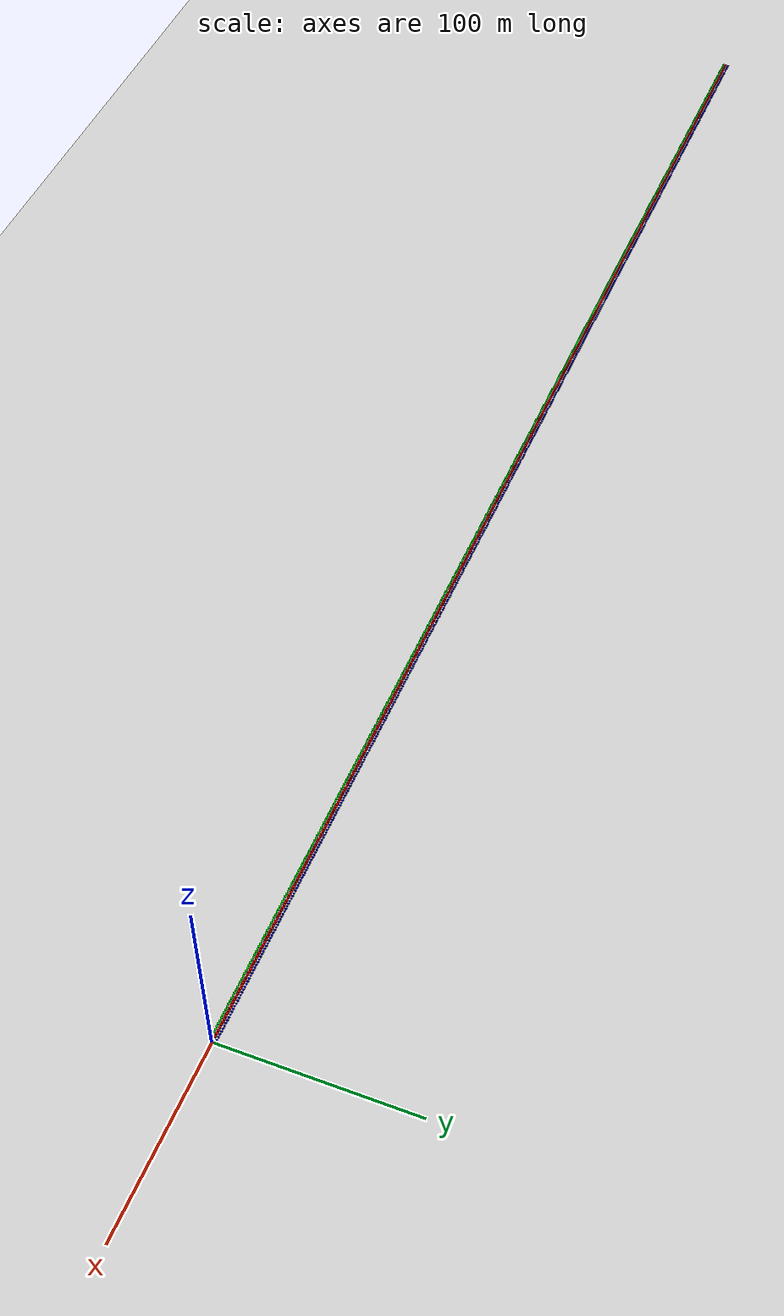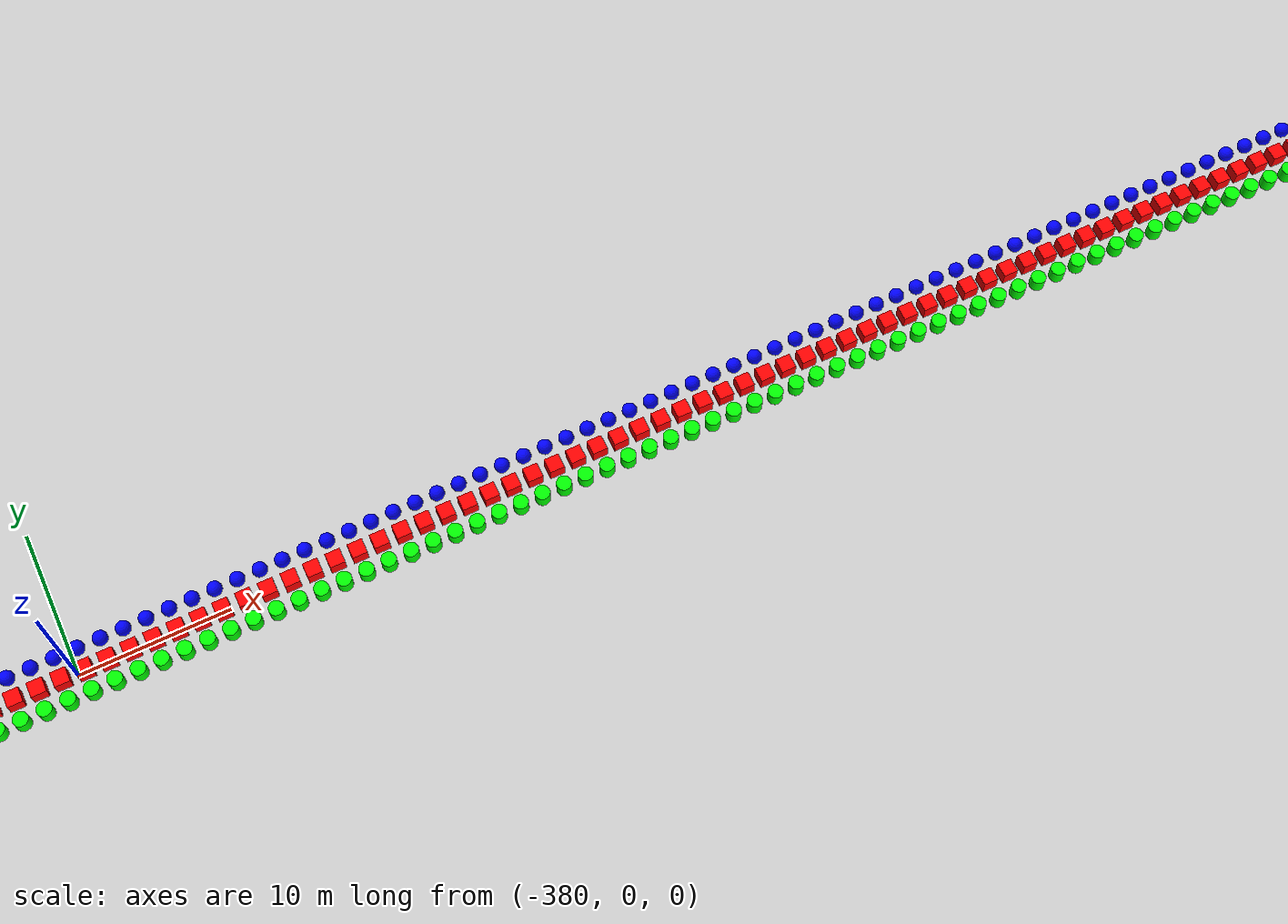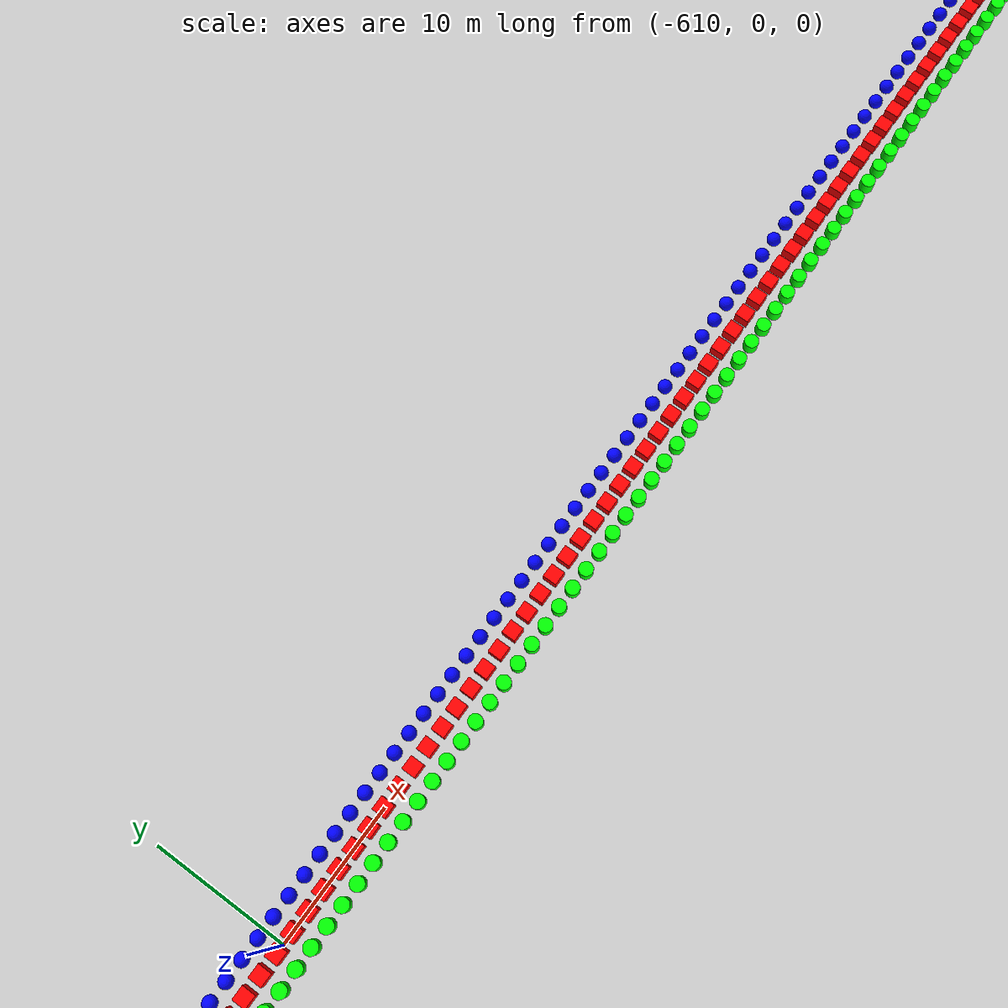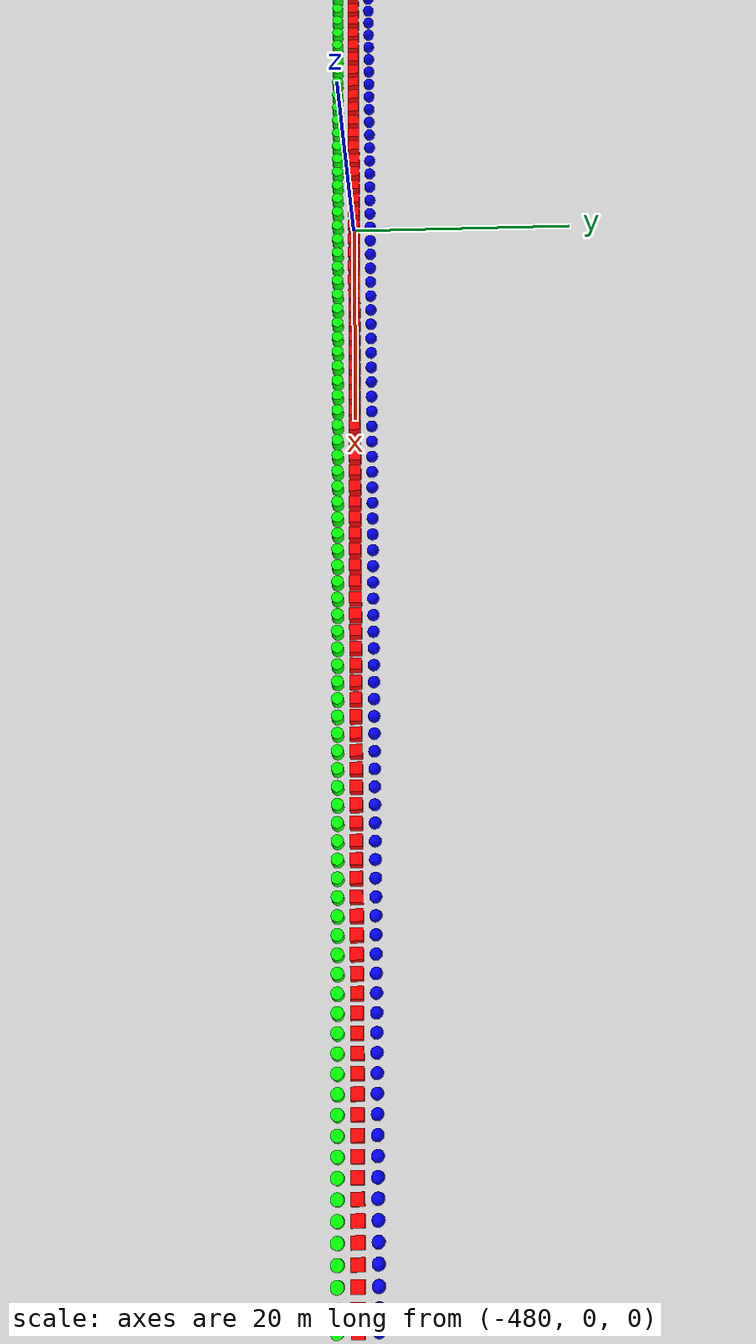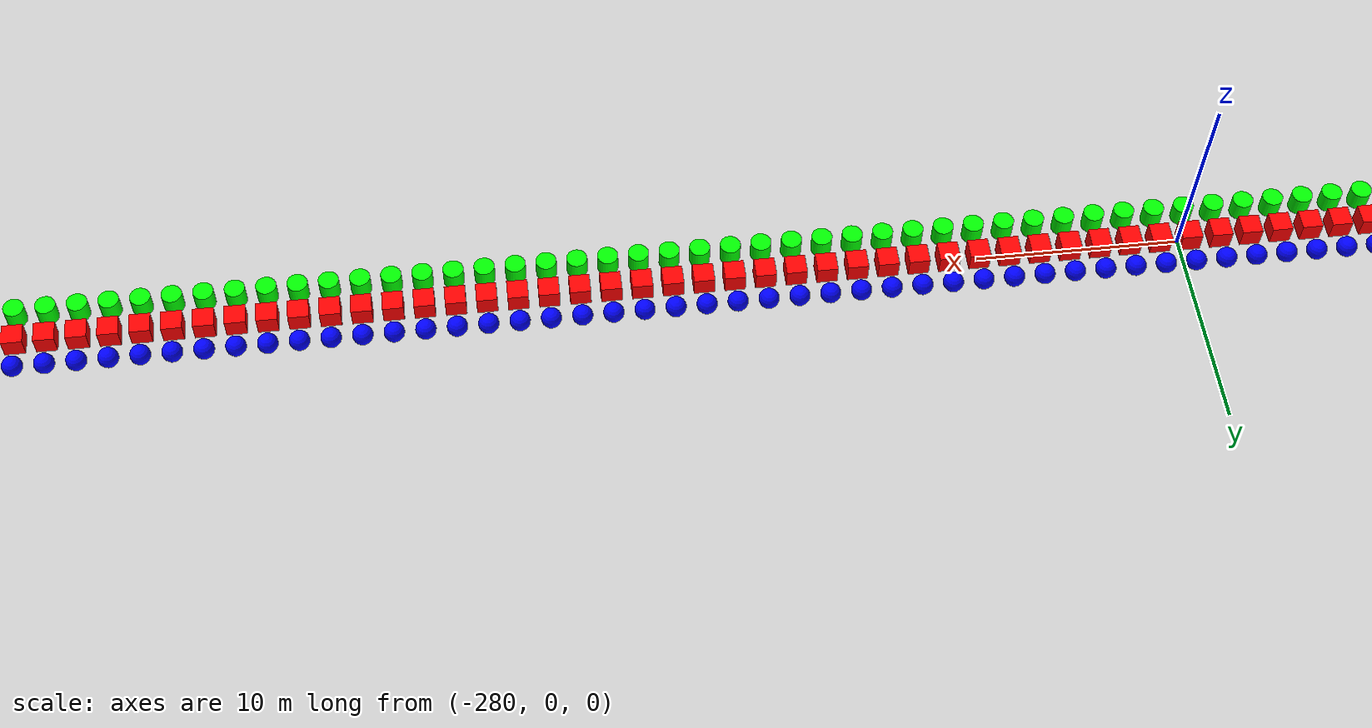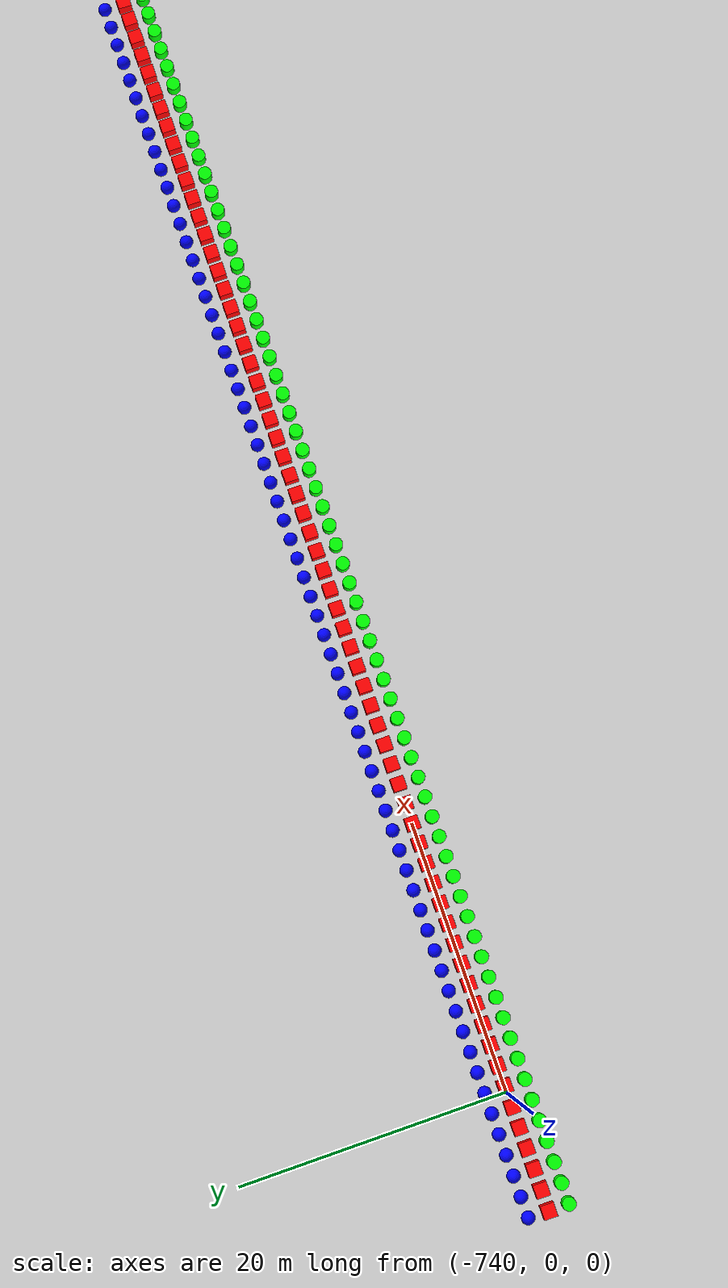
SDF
<sdf version="1.6">
 <world name="shapes">
  <model name="ground_plane">
   <static>true</static>
   <link name="link">
    <collision name="collision">
     <geometry><plane><normal>0 0 1</normal><size>100 100</size></plane></geometry>
    </collision>
    <visual name="visual">
     <geometry><plane><normal>0 0 1</normal><size>100 100</size></plane></geometry>
     <material>
      <ambient>0.8 0.8 0.8 1</ambient>
      <diffuse>0.8 0.8 0.8 1</diffuse>
      <specular>0.8 0.8 0.8 1</specular>
     </material>
    </visual>
   </link>
  </model>
  <model name="box_1">
   <static>true</static>
   <pose>-748.5 0 0.5 0 0 0</pose>
   <link name="box_link">
    <inertial>
     <inertia><ixx>1</ixx><ixy>0</ixy><ixz>0</ixz><iyy>1</iyy><iyz>0</iyz><izz>1</izz></inertia>
     <mass>1.0</mass>
    </inertial>
    <collision name="box_collision"><geometry><box><size>1 1 1</size></box></geometry></collision>
    <visual name="box_visual">
     <geometry><box><size>1 1 1</size></box></geometry>
     <material><ambient>1 0 0 1</ambient><diffuse>1 0 0 1</diffuse><specular>1 0 0 1</specular></material>
    </visual>
   </link>
  </model>
  <model name="cylinder_1">
   <static>true</static>
   <pose>-748.5 -1.5 0.5 0 0 0</pose>
   <link name="cylinder_link">
    <inertial>
     <inertia><ixx>2</ixx><ixy>0</ixy><ixz>0</ixz><iyy>2</iyy><iyz>0</iyz><izz>2</izz></inertia>
     <mass>2.0</mass>
    </inertial>
    <collision name="cylinder_collision">
     <geometry><cylinder><radius>0.5</radius><length>1.0</length></cylinder></geometry>
    </collision>
    <visual name="cylinder_visual">
     <geometry><cylinder><radius>0.5</radius><length>1.0</length></cylinder></geometry>
     <material><ambient>0 1 0 1</ambient><diffuse>0 1 0 1</diffuse><specular>0 1 0 1</specular></material>
    </visual>
   </link>
  </model>
  <model name="sphere_1">
   <static>true</static>
   <pose>-748.5 1.5 0.5 0 0 0</pose>
   <link name="sphere_link">
    <inertial>
     <inertia><ixx>3</ixx><ixy>0</ixy><ixz>0</ixz><iyy>3</iyy><iyz>0</iyz><izz>3</izz></inertia>
     <mass>3.0</mass>
    </inertial>
    <collision name="sphere_collision"><geometry><sphere><radius>0.5</radius></sphere></geometry></collision>
    <visual name="sphere_visual">
     <geometry><sphere><radius>0.5</radius></sphere></geometry>
     <material><ambient>0 0 1 1</ambient><diffuse>0 0 1 1</diffuse><specular>0 0 1 1</specular></material>
    </visual>
   </link>
  </model>
  <model name="box_2">
   <static>true</static>
   <pose>-747.0 0 0.5 0 0 0</pose>
   <link name="box_link">
    <inertial>
     <inertia><ixx>1</ixx><ixy>0</ixy><ixz>0</ixz><iyy>1</iyy><iyz>0</iyz><izz>1</izz></inertia>
     <mass>1.0</mass>
    </inertial>
    <collision name="box_collision"><geometry><box><size>1 1 1</size></box></geometry></collision>
    <visual name="box_visual">
     <geometry><box><size>1 1 1</size></box></geometry>
     <material><ambient>1 0 0 1</ambient><diffuse>1 0 0 1</diffuse><specular>1 0 0 1</specular></material>
    </visual>
   </link>
  </model>
  <model name="cylinder_2">
   <static>true</static>
   <pose>-747.0 -1.5 0.5 0 0 0</pose>
   <link name="cylinder_link">
    <inertial>
     <inertia><ixx>2</ixx><ixy>0</ixy><ixz>0</ixz><iyy>2</iyy><iyz>0</iyz><izz>2</izz></inertia>
     <mass>2.0</mass>
    </inertial>
    <collision name="cylinder_collision">
     <geometry><cylinder><radius>0.5</radius><length>1.0</length></cylinder></geometry>
    </collision>
    <visual name="cylinder_visual">
     <geometry><cylinder><radius>0.5</radius><length>1.0</length></cylinder></geometry>
     <material><ambient>0 1 0 1</ambient><diffuse>0 1 0 1</diffuse><specular>0 1 0 1</specular></material>
    </visual>
   </link>
  </model>
  <model name="sphere_2">
   <static>true</static>
   <pose>-747.0 1.5 0.5 0 0 0</pose>
   <link name="sphere_link">
    <inertial>
     <inertia><ixx>3</ixx><ixy>0</ixy><ixz>0</ixz><iyy>3</iyy><iyz>0</iyz><izz>3</izz></inertia>
     <mass>3.0</mass>
    </inertial>
    <collision name="sphere_collision"><geometry><sphere><radius>0.5</radius></sphere></geometry></collision>
    <visual name="sphere_visual">
     <geometry><sphere><radius>0.5</radius></sphere></geometry>
     <material><ambient>0 0 1 1</ambient><diffuse>0 0 1 1</diffuse><specular>0 0 1 1</specular></material>
    </visual>
   </link>
  </model>
  <model name="box_3">
   <static>true</static>
   <pose>-745.5 0 0.5 0 0 0</pose>
   <link name="box_link">
    <inertial>
     <inertia><ixx>1</ixx><ixy>0</ixy><ixz>0</ixz><iyy>1</iyy><iyz>0</iyz><izz>1</izz></inertia>
     <mass>1.0</mass>
    </inertial>
    <collision name="box_collision"><geometry><box><size>1 1 1</size></box></geometry></collision>
    <visual name="box_visual">
     <geometry><box><size>1 1 1</size></box></geometry>
     <material><ambient>1 0 0 1</ambient><diffuse>1 0 0 1</diffuse><specular>1 0 0 1</specular></material>
    </visual>
   </link>
  </model>
  <model name="cylinder_3">
   <static>true</static>
   <pose>-745.5 -1.5 0.5 0 0 0</pose>
   <link name="cylinder_link">
    <inertial>
     <inertia><ixx>2</ixx><ixy>0</ixy><ixz>0</ixz><iyy>2</iyy><iyz>0</iyz><izz>2</izz></inertia>
     <mass>2.0</mass>
    </inertial>
    <collision name="cylinder_collision">
     <geometry><cylinder><radius>0.5</radius><length>1.0</length></cylinder></geometry>
    </collision>
    <visual name="cylinder_visual">
     <geometry><cylinder><radius>0.5</radius><length>1.0</length></cylinder></geometry>
     <material><ambient>0 1 0 1</ambient><diffuse>0 1 0 1</diffuse><specular>0 1 0 1</specular></material>
    </visual>
   </link>
  </model>
  <model name="sphere_3">
   <static>true</static>
   <pose>-745.5 1.5 0.5 0 0 0</pose>
   <link name="sphere_link">
    <inertial>
     <inertia><ixx>3</ixx><ixy>0</ixy><ixz>0</ixz><iyy>3</iyy><iyz>0</iyz><izz>3</izz></inertia>
     <mass>3.0</mass>
    </inertial>
    <collision name="sphere_collision"><geometry><sphere><radius>0.5</radius></sphere></geometry></collision>
    <visual name="sphere_visual">
     <geometry><sphere><radius>0.5</radius></sphere></geometry>
     <material><ambient>0 0 1 1</ambient><diffuse>0 0 1 1</diffuse><specular>0 0 1 1</specular></material>
    </visual>
   </link>
  </model>
  <model name="box_4">
   <static>true</static>
   <pose>-744.0 0 0.5 0 0 0</pose>
   <link name="box_link">
    <inertial>
     <inertia><ixx>1</ixx><ixy>0</ixy><ixz>0</ixz><iyy>1</iyy><iyz>0</iyz><izz>1</izz></inertia>
     <mass>1.0</mass>
    </inertial>
    <collision name="box_collision"><geometry><box><size>1 1 1</size></box></geometry></collision>
    <visual name="box_visual">
     <geometry><box><size>1 1 1</size></box></geometry>
     <material><ambient>1 0 0 1</ambient><diffuse>1 0 0 1</diffuse><specular>1 0 0 1</specular></material>
    </visual>
   </link>
  </model>
  <model name="cylinder_4">
   <static>true</static>
   <pose>-744.0 -1.5 0.5 0 0 0</pose>
   <link name="cylinder_link">
    <inertial>
     <inertia><ixx>2</ixx><ixy>0</ixy><ixz>0</ixz><iyy>2</iyy><iyz>0</iyz><izz>2</izz></inertia>
     <mass>2.0</mass>
    </inertial>
    <collision name="cylinder_collision">
     <geometry><cylinder><radius>0.5</radius><length>1.0</length></cylinder></geometry>
    </collision>
    <visual name="cylinder_visual">
     <geometry><cylinder><radius>0.5</radius><length>1.0</length></cylinder></geometry>
     <material><ambient>0 1 0 1</ambient><diffuse>0 1 0 1</diffuse><specular>0 1 0 1</specular></material>
    </visual>
   </link>
  </model>
  <model name="sphere_4">
   <static>true</static>
   <pose>-744.0 1.5 0.5 0 0 0</pose>
   <link name="sphere_link">
    <inertial>
     <inertia><ixx>3</ixx><ixy>0</ixy><ixz>0</ixz><iyy>3</iyy><iyz>0</iyz><izz>3</izz></inertia>
     <mass>3.0</mass>
    </inertial>
    <collision name="sphere_collision"><geometry><sphere><radius>0.5</radius></sphere></geometry></collision>
    <visual name="sphere_visual">
     <geometry><sphere><radius>0.5</radius></sphere></geometry>
     <material><ambient>0 0 1 1</ambient><diffuse>0 0 1 1</diffuse><specular>0 0 1 1</specular></material>
    </visual>
   </link>
  </model>
  <model name="box_5">
   <static>true</static>
   <pose>-742.5 0 0.5 0 0 0</pose>
   <link name="box_link">
    <inertial>
     <inertia><ixx>1</ixx><ixy>0</ixy><ixz>0</ixz><iyy>1</iyy><iyz>0</iyz><izz>1</izz></inertia>
     <mass>1.0</mass>
    </inertial>
    <collision name="box_collision"><geometry><box><size>1 1 1</size></box></geometry></collision>
    <visual name="box_visual">
     <geometry><box><size>1 1 1</size></box></geometry>
     <material><ambient>1 0 0 1</ambient><diffuse>1 0 0 1</diffuse><specular>1 0 0 1</specular></material>
    </visual>
   </link>
  </model>
  <model name="cylinder_5">
   <static>true</static>
   <pose>-742.5 -1.5 0.5 0 0 0</pose>
   <link name="cylinder_link">
    <inertial>
     <inertia><ixx>2</ixx><ixy>0</ixy><ixz>0</ixz><iyy>2</iyy><iyz>0</iyz><izz>2</izz></inertia>
     <mass>2.0</mass>
    </inertial>
    <collision name="cylinder_collision">
     <geometry><cylinder><radius>0.5</radius><length>1.0</length></cylinder></geometry>
    </collision>
    <visual name="cylinder_visual">
     <geometry><cylinder><radius>0.5</radius><length>1.0</length></cylinder></geometry>
     <material><ambient>0 1 0 1</ambient><diffuse>0 1 0 1</diffuse><specular>0 1 0 1</specular></material>
    </visual>
   </link>
  </model>
  <model name="sphere_5">
   <static>true</static>
   <pose>-742.5 1.5 0.5 0 0 0</pose>
   <link name="sphere_link">
    <inertial>
     <inertia><ixx>3</ixx><ixy>0</ixy><ixz>0</ixz><iyy>3</iyy><iyz>0</iyz><izz>3</izz></inertia>
     <mass>3.0</mass>
    </inertial>
    <collision name="sphere_collision"><geometry><sphere><radius>0.5</radius></sphere></geometry></collision>
    <visual name="sphere_visual">
     <geometry><sphere><radius>0.5</radius></sphere></geometry>
     <material><ambient>0 0 1 1</ambient><diffuse>0 0 1 1</diffuse><specular>0 0 1 1</specular></material>
    </visual>
   </link>
  </model>
  <model name="box_6">
   <static>true</static>
   <pose>-741.0 0 0.5 0 0 0</pose>
   <link name="box_link">
    <inertial>
     <inertia><ixx>1</ixx><ixy>0</ixy><ixz>0</ixz><iyy>1</iyy><iyz>0</iyz><izz>1</izz></inertia>
     <mass>1.0</mass>
    </inertial>
    <collision name="box_collision"><geometry><box><size>1 1 1</size></box></geometry></collision>
    <visual name="box_visual">
     <geometry><box><size>1 1 1</size></box></geometry>
     <material><ambient>1 0 0 1</ambient><diffuse>1 0 0 1</diffuse><specular>1 0 0 1</specular></material>
    </visual>
   </link>
  </model>
  <model name="cylinder_6">
   <static>true</static>
   <pose>-741.0 -1.5 0.5 0 0 0</pose>
   <link name="cylinder_link">
    <inertial>
     <inertia><ixx>2</ixx><ixy>0</ixy><ixz>0</ixz><iyy>2</iyy><iyz>0</iyz><izz>2</izz></inertia>
     <mass>2.0</mass>
    </inertial>
    <collision name="cylinder_collision">
     <geometry><cylinder><radius>0.5</radius><length>1.0</length></cylinder></geometry>
    </collision>
    <visual name="cylinder_visual">
     <geometry><cylinder><radius>0.5</radius><length>1.0</length></cylinder></geometry>
     <material><ambient>0 1 0 1</ambient><diffuse>0 1 0 1</diffuse><specular>0 1 0 1</specular></material>
    </visual>
   </link>
  </model>
  <model name="sphere_6">
   <static>true</static>
   <pose>-741.0 1.5 0.5 0 0 0</pose>
   <link name="sphere_link">
    <inertial>
     <inertia><ixx>3</ixx><ixy>0</ixy><ixz>0</ixz><iyy>3</iyy><iyz>0</iyz><izz>3</izz></inertia>
     <mass>3.0</mass>
    </inertial>
    <collision name="sphere_collision"><geometry><sphere><radius>0.5</radius></sphere></geometry></collision>
    <visual name="sphere_visual">
     <geometry><sphere><radius>0.5</radius></sphere></geometry>
     <material><ambient>0 0 1 1</ambient><diffuse>0 0 1 1</diffuse><specular>0 0 1 1</specular></material>
    </visual>
   </link>
  </model>
  <model name="box_7">
   <static>true</static>
   <pose>-739.5 0 0.5 0 0 0</pose>
   <link name="box_link">
    <inertial>
     <inertia><ixx>1</ixx><ixy>0</ixy><ixz>0</ixz><iyy>1</iyy><iyz>0</iyz><izz>1</izz></inertia>
     <mass>1.0</mass>
    </inertial>
    <collision name="box_collision"><geometry><box><size>1 1 1</size></box></geometry></collision>
    <visual name="box_visual">
     <geometry><box><size>1 1 1</size></box></geometry>
     <material><ambient>1 0 0 1</ambient><diffuse>1 0 0 1</diffuse><specular>1 0 0 1</specular></material>
    </visual>
   </link>
  </model>
  <model name="cylinder_7">
   <static>true</static>
   <pose>-739.5 -1.5 0.5 0 0 0</pose>
   <link name="cylinder_link">
    <inertial>
     <inertia><ixx>2</ixx><ixy>0</ixy><ixz>0</ixz><iyy>2</iyy><iyz>0</iyz><izz>2</izz></inertia>
     <mass>2.0</mass>
    </inertial>
    <collision name="cylinder_collision">
     <geometry><cylinder><radius>0.5</radius><length>1.0</length></cylinder></geometry>
    </collision>
    <visual name="cylinder_visual">
     <geometry><cylinder><radius>0.5</radius><length>1.0</length></cylinder></geometry>
     <material><ambient>0 1 0 1</ambient><diffuse>0 1 0 1</diffuse><specular>0 1 0 1</specular></material>
    </visual>
   </link>
  </model>
  <model name="sphere_7">
   <static>true</static>
   <pose>-739.5 1.5 0.5 0 0 0</pose>
   <link name="sphere_link">
    <inertial>
     <inertia><ixx>3</ixx><ixy>0</ixy><ixz>0</ixz><iyy>3</iyy><iyz>0</iyz><izz>3</izz></inertia>
     <mass>3.0</mass>
    </inertial>
    <collision name="sphere_collision"><geometry><sphere><radius>0.5</radius></sphere></geometry></collision>
    <visual name="sphere_visual">
     <geometry><sphere><radius>0.5</radius></sphere></geometry>
     <material><ambient>0 0 1 1</ambient><diffuse>0 0 1 1</diffuse><specular>0 0 1 1</specular></material>
    </visual>
   </link>
  </model>
  <model name="box_8">
   <static>true</static>
   <pose>-738.0 0 0.5 0 0 0</pose>
   <link name="box_link">
    <inertial>
     <inertia><ixx>1</ixx><ixy>0</ixy><ixz>0</ixz><iyy>1</iyy><iyz>0</iyz><izz>1</izz></inertia>
     <mass>1.0</mass>
    </inertial>
    <collision name="box_collision"><geometry><box><size>1 1 1</size></box></geometry></collision>
    <visual name="box_visual">
     <geometry><box><size>1 1 1</size></box></geometry>
     <material><ambient>1 0 0 1</ambient><diffuse>1 0 0 1</diffuse><specular>1 0 0 1</specular></material>
    </visual>
   </link>
  </model>
  <model name="cylinder_8">
   <static>true</static>
   <pose>-738.0 -1.5 0.5 0 0 0</pose>
   <link name="cylinder_link">
    <inertial>
     <inertia><ixx>2</ixx><ixy>0</ixy><ixz>0</ixz><iyy>2</iyy><iyz>0</iyz><izz>2</izz></inertia>
     <mass>2.0</mass>
    </inertial>
    <collision name="cylinder_collision">
     <geometry><cylinder><radius>0.5</radius><length>1.0</length></cylinder></geometry>
    </collision>
    <visual name="cylinder_visual">
     <geometry><cylinder><radius>0.5</radius><length>1.0</length></cylinder></geometry>
     <material><ambient>0 1 0 1</ambient><diffuse>0 1 0 1</diffuse><specular>0 1 0 1</specular></material>
    </visual>
   </link>
  </model>
  <model name="sphere_8">
   <static>true</static>
   <pose>-738.0 1.5 0.5 0 0 0</pose>
   <link name="sphere_link">
    <inertial>
     <inertia><ixx>3</ixx><ixy>0</ixy><ixz>0</ixz><iyy>3</iyy><iyz>0</iyz><izz>3</izz></inertia>
     <mass>3.0</mass>
    </inertial>
    <collision name="sphere_collision"><geometry><sphere><radius>0.5</radius></sphere></geometry></collision>
    <visual name="sphere_visual">
     <geometry><sphere><radius>0.5</radius></sphere></geometry>
     <material><ambient>0 0 1 1</ambient><diffuse>0 0 1 1</diffuse><specular>0 0 1 1</specular></material>
    </visual>
   </link>
  </model>
  <model name="box_9">
   <static>true</static>
   <pose>-736.5 0 0.5 0 0 0</pose>
   <link name="box_link">
    <inertial>
     <inertia><ixx>1</ixx><ixy>0</ixy><ixz>0</ixz><iyy>1</iyy><iyz>0</iyz><izz>1</izz></inertia>
     <mass>1.0</mass>
    </inertial>
    <collision name="box_collision"><geometry><box><size>1 1 1</size></box></geometry></collision>
    <visual name="box_visual">
     <geometry><box><size>1 1 1</size></box></geometry>
     <material><ambient>1 0 0 1</ambient><diffuse>1 0 0 1</diffuse><specular>1 0 0 1</specular></material>
    </visual>
   </link>
  </model>
  <model name="cylinder_9">
   <static>true</static>
   <pose>-736.5 -1.5 0.5 0 0 0</pose>
   <link name="cylinder_link">
    <inertial>
     <inertia><ixx>2</ixx><ixy>0</ixy><ixz>0</ixz><iyy>2</iyy><iyz>0</iyz><izz>2</izz></inertia>
     <mass>2.0</mass>
    </inertial>
    <collision name="cylinder_collision">
     <geometry><cylinder><radius>0.5</radius><length>1.0</length></cylinder></geometry>
    </collision>
    <visual name="cylinder_visual">
     <geometry><cylinder><radius>0.5</radius><length>1.0</length></cylinder></geometry>
     <material><ambient>0 1 0 1</ambient><diffuse>0 1 0 1</diffuse><specular>0 1 0 1</specular></material>
    </visual>
   </link>
  </model>
  <model name="sphere_9">
   <static>true</static>
   <pose>-736.5 1.5 0.5 0 0 0</pose>
   <link name="sphere_link">
    <inertial>
     <inertia><ixx>3</ixx><ixy>0</ixy><ixz>0</ixz><iyy>3</iyy><iyz>0</iyz><izz>3</izz></inertia>
     <mass>3.0</mass>
    </inertial>
    <collision name="sphere_collision"><geometry><sphere><radius>0.5</radius></sphere></geometry></collision>
    <visual name="sphere_visual">
     <geometry><sphere><radius>0.5</radius></sphere></geometry>
     <material><ambient>0 0 1 1</ambient><diffuse>0 0 1 1</diffuse><specular>0 0 1 1</specular></material>
    </visual>
   </link>
  </model>
  <model name="box_10">
   <static>true</static>
   <pose>-735.0 0 0.5 0 0 0</pose>
   <link name="box_link">
    <inertial>
     <inertia><ixx>1</ixx><ixy>0</ixy><ixz>0</ixz><iyy>1</iyy><iyz>0</iyz><izz>1</izz></inertia>
     <mass>1.0</mass>
    </inertial>
    <collision name="box_collision"><geometry><box><size>1 1 1</size></box></geometry></collision>
    <visual name="box_visual">
     <geometry><box><size>1 1 1</size></box></geometry>
     <material><ambient>1 0 0 1</ambient><diffuse>1 0 0 1</diffuse><specular>1 0 0 1</specular></material>
    </visual>
   </link>
  </model>
  <model name="cylinder_10">
   <static>true</static>
   <pose>-735.0 -1.5 0.5 0 0 0</pose>
   <link name="cylinder_link">
    <inertial>
     <inertia><ixx>2</ixx><ixy>0</ixy><ixz>0</ixz><iyy>2</iyy><iyz>0</iyz><izz>2</izz></inertia>
     <mass>2.0</mass>
    </inertial>
    <collision name="cylinder_collision">
     <geometry><cylinder><radius>0.5</radius><length>1.0</length></cylinder></geometry>
    </collision>
    <visual name="cylinder_visual">
     <geometry><cylinder><radius>0.5</radius><length>1.0</length></cylinder></geometry>
     <material><ambient>0 1 0 1</ambient><diffuse>0 1 0 1</diffuse><specular>0 1 0 1</specular></material>
    </visual>
   </link>
  </model>
  <model name="sphere_10">
   <static>true</static>
   <pose>-735.0 1.5 0.5 0 0 0</pose>
   <link name="sphere_link">
    <inertial>
     <inertia><ixx>3</ixx><ixy>0</ixy><ixz>0</ixz><iyy>3</iyy><iyz>0</iyz><izz>3</izz></inertia>
     <mass>3.0</mass>
    </inertial>
    <collision name="sphere_collision"><geometry><sphere><radius>0.5</radius></sphere></geometry></collision>
    <visual name="sphere_visual">
     <geometry><sphere><radius>0.5</radius></sphere></geometry>
     <material><ambient>0 0 1 1</ambient><diffuse>0 0 1 1</diffuse><specular>0 0 1 1</specular></material>
    </visual>
   </link>
  </model>
  <model name="box_11">
   <static>true</static>
   <pose>-733.5 0 0.5 0 0 0</pose>
   <link name="box_link">
    <inertial>
     <inertia><ixx>1</ixx><ixy>0</ixy><ixz>0</ixz><iyy>1</iyy><iyz>0</iyz><izz>1</izz></inertia>
     <mass>1.0</mass>
    </inertial>
    <collision name="box_collision"><geometry><box><size>1 1 1</size></box></geometry></collision>
    <visual name="box_visual">
     <geometry><box><size>1 1 1</size></box></geometry>
     <material><ambient>1 0 0 1</ambient><diffuse>1 0 0 1</diffuse><specular>1 0 0 1</specular></material>
    </visual>
   </link>
  </model>
  <model name="cylinder_11">
   <static>true</static>
   <pose>-733.5 -1.5 0.5 0 0 0</pose>
   <link name="cylinder_link">
    <inertial>
     <inertia><ixx>2</ixx><ixy>0</ixy><ixz>0</ixz><iyy>2</iyy><iyz>0</iyz><izz>2</izz></inertia>
     <mass>2.0</mass>
    </inertial>
    <collision name="cylinder_collision">
     <geometry><cylinder><radius>0.5</radius><length>1.0</length></cylinder></geometry>
    </collision>
    <visual name="cylinder_visual">
     <geometry><cylinder><radius>0.5</radius><length>1.0</length></cylinder></geometry>
     <material><ambient>0 1 0 1</ambient><diffuse>0 1 0 1</diffuse><specular>0 1 0 1</specular></material>
    </visual>
   </link>
  </model>
  <model name="sphere_11">
   <static>true</static>
   <pose>-733.5 1.5 0.5 0 0 0</pose>
   <link name="sphere_link">
    <inertial>
     <inertia><ixx>3</ixx><ixy>0</ixy><ixz>0</ixz><iyy>3</iyy><iyz>0</iyz><izz>3</izz></inertia>
     <mass>3.0</mass>
    </inertial>
    <collision name="sphere_collision"><geometry><sphere><radius>0.5</radius></sphere></geometry></collision>
    <visual name="sphere_visual">
     <geometry><sphere><radius>0.5</radius></sphere></geometry>
     <material><ambient>0 0 1 1</ambient><diffuse>0 0 1 1</diffuse><specular>0 0 1 1</specular></material>
    </visual>
   </link>
  </model>
  <model name="box_12">
   <static>true</static>
   <pose>-732.0 0 0.5 0 0 0</pose>
   <link name="box_link">
    <inertial>
     <inertia><ixx>1</ixx><ixy>0</ixy><ixz>0</ixz><iyy>1</iyy><iyz>0</iyz><izz>1</izz></inertia>
     <mass>1.0</mass>
    </inertial>
    <collision name="box_collision"><geometry><box><size>1 1 1</size></box></geometry></collision>
    <visual name="box_visual">
     <geometry><box><size>1 1 1</size></box></geometry>
     <material><ambient>1 0 0 1</ambient><diffuse>1 0 0 1</diffuse><specular>1 0 0 1</specular></material>
    </visual>
   </link>
  </model>
  <model name="cylinder_12">
   <static>true</static>
   <pose>-732.0 -1.5 0.5 0 0 0</pose>
   <link name="cylinder_link">
    <inertial>
     <inertia><ixx>2</ixx><ixy>0</ixy><ixz>0</ixz><iyy>2</iyy><iyz>0</iyz><izz>2</izz></inertia>
     <mass>2.0</mass>
    </inertial>
    <collision name="cylinder_collision">
     <geometry><cylinder><radius>0.5</radius><length>1.0</length></cylinder></geometry>
    </collision>
    <visual name="cylinder_visual">
     <geometry><cylinder><radius>0.5</radius><length>1.0</length></cylinder></geometry>
     <material><ambient>0 1 0 1</ambient><diffuse>0 1 0 1</diffuse><specular>0 1 0 1</specular></material>
    </visual>
   </link>
  </model>
  <model name="sphere_12">
   <static>true</static>
   <pose>-732.0 1.5 0.5 0 0 0</pose>
   <link name="sphere_link">
    <inertial>
     <inertia><ixx>3</ixx><ixy>0</ixy><ixz>0</ixz><iyy>3</iyy><iyz>0</iyz><izz>3</izz></inertia>
     <mass>3.0</mass>
    </inertial>
    <collision name="sphere_collision"><geometry><sphere><radius>0.5</radius></sphere></geometry></collision>
    <visual name="sphere_visual">
     <geometry><sphere><radius>0.5</radius></sphere></geometry>
     <material><ambient>0 0 1 1</ambient><diffuse>0 0 1 1</diffuse><specular>0 0 1 1</specular></material>
    </visual>
   </link>
  </model>
  <model name="box_13">
   <static>true</static>
   <pose>-730.5 0 0.5 0 0 0</pose>
   <link name="box_link">
    <inertial>
     <inertia><ixx>1</ixx><ixy>0</ixy><ixz>0</ixz><iyy>1</iyy><iyz>0</iyz><izz>1</izz></inertia>
     <mass>1.0</mass>
    </inertial>
    <collision name="box_collision"><geometry><box><size>1 1 1</size></box></geometry></collision>
    <visual name="box_visual">
     <geometry><box><size>1 1 1</size></box></geometry>
     <material><ambient>1 0 0 1</ambient><diffuse>1 0 0 1</diffuse><specular>1 0 0 1</specular></material>
    </visual>
   </link>
  </model>
  <model name="cylinder_13">
   <static>true</static>
   <pose>-730.5 -1.5 0.5 0 0 0</pose>
   <link name="cylinder_link">
    <inertial>
     <inertia><ixx>2</ixx><ixy>0</ixy><ixz>0</ixz><iyy>2</iyy><iyz>0</iyz><izz>2</izz></inertia>
     <mass>2.0</mass>
    </inertial>
    <collision name="cylinder_collision">
     <geometry><cylinder><radius>0.5</radius><length>1.0</length></cylinder></geometry>
    </collision>
    <visual name="cylinder_visual">
     <geometry><cylinder><radius>0.5</radius><length>1.0</length></cylinder></geometry>
     <material><ambient>0 1 0 1</ambient><diffuse>0 1 0 1</diffuse><specular>0 1 0 1</specular></material>
    </visual>
   </link>
  </model>
  <model name="sphere_13">
   <static>true</static>
   <pose>-730.5 1.5 0.5 0 0 0</pose>
   <link name="sphere_link">
    <inertial>
     <inertia><ixx>3</ixx><ixy>0</ixy><ixz>0</ixz><iyy>3</iyy><iyz>0</iyz><izz>3</izz></inertia>
     <mass>3.0</mass>
    </inertial>
    <collision name="sphere_collision"><geometry><sphere><radius>0.5</radius></sphere></geometry></collision>
    <visual name="sphere_visual">
     <geometry><sphere><radius>0.5</radius></sphere></geometry>
     <material><ambient>0 0 1 1</ambient><diffuse>0 0 1 1</diffuse><specular>0 0 1 1</specular></material>
    </visual>
   </link>
  </model>
  <model name="box_14">
   <static>true</static>
   <pose>-729.0 0 0.5 0 0 0</pose>
   <link name="box_link">
    <inertial>
     <inertia><ixx>1</ixx><ixy>0</ixy><ixz>0</ixz><iyy>1</iyy><iyz>0</iyz><izz>1</izz></inertia>
     <mass>1.0</mass>
    </inertial>
    <collision name="box_collision"><geometry><box><size>1 1 1</size></box></geometry></collision>
    <visual name="box_visual">
     <geometry><box><size>1 1 1</size></box></geometry>
     <material><ambient>1 0 0 1</ambient><diffuse>1 0 0 1</diffuse><specular>1 0 0 1</specular></material>
    </visual>
   </link>
  </model>
  <model name="cylinder_14">
   <static>true</static>
   <pose>-729.0 -1.5 0.5 0 0 0</pose>
   <link name="cylinder_link">
    <inertial>
     <inertia><ixx>2</ixx><ixy>0</ixy><ixz>0</ixz><iyy>2</iyy><iyz>0</iyz><izz>2</izz></inertia>
     <mass>2.0</mass>
    </inertial>
    <collision name="cylinder_collision">
     <geometry><cylinder><radius>0.5</radius><length>1.0</length></cylinder></geometry>
    </collision>
    <visual name="cylinder_visual">
     <geometry><cylinder><radius>0.5</radius><length>1.0</length></cylinder></geometry>
     <material><ambient>0 1 0 1</ambient><diffuse>0 1 0 1</diffuse><specular>0 1 0 1</specular></material>
    </visual>
   </link>
  </model>
  <model name="sphere_14">
   <static>true</static>
   <pose>-729.0 1.5 0.5 0 0 0</pose>
   <link name="sphere_link">
    <inertial>
     <inertia><ixx>3</ixx><ixy>0</ixy><ixz>0</ixz><iyy>3</iyy><iyz>0</iyz><izz>3</izz></inertia>
     <mass>3.0</mass>
    </inertial>
    <collision name="sphere_collision"><geometry><sphere><radius>0.5</radius></sphere></geometry></collision>
    <visual name="sphere_visual">
     <geometry><sphere><radius>0.5</radius></sphere></geometry>
     <material><ambient>0 0 1 1</ambient><diffuse>0 0 1 1</diffuse><specular>0 0 1 1</specular></material>
    </visual>
   </link>
  </model>
  <model name="box_15">
   <static>true</static>
   <pose>-727.5 0 0.5 0 0 0</pose>
   <link name="box_link">
    <inertial>
     <inertia><ixx>1</ixx><ixy>0</ixy><ixz>0</ixz><iyy>1</iyy><iyz>0</iyz><izz>1</izz></inertia>
     <mass>1.0</mass>
    </inertial>
    <collision name="box_collision"><geometry><box><size>1 1 1</size></box></geometry></collision>
    <visual name="box_visual">
     <geometry><box><size>1 1 1</size></box></geometry>
     <material><ambient>1 0 0 1</ambient><diffuse>1 0 0 1</diffuse><specular>1 0 0 1</specular></material>
    </visual>
   </link>
  </model>
  <model name="cylinder_15">
   <static>true</static>
   <pose>-727.5 -1.5 0.5 0 0 0</pose>
   <link name="cylinder_link">
    <inertial>
     <inertia><ixx>2</ixx><ixy>0</ixy><ixz>0</ixz><iyy>2</iyy><iyz>0</iyz><izz>2</izz></inertia>
     <mass>2.0</mass>
    </inertial>
    <collision name="cylinder_collision">
     <geometry><cylinder><radius>0.5</radius><length>1.0</length></cylinder></geometry>
    </collision>
    <visual name="cylinder_visual">
     <geometry><cylinder><radius>0.5</radius><length>1.0</length></cylinder></geometry>
     <material><ambient>0 1 0 1</ambient><diffuse>0 1 0 1</diffuse><specular>0 1 0 1</specular></material>
    </visual>
   </link>
  </model>
  <model name="sphere_15">
   <static>true</static>
   <pose>-727.5 1.5 0.5 0 0 0</pose>
   <link name="sphere_link">
    <inertial>
     <inertia><ixx>3</ixx><ixy>0</ixy><ixz>0</ixz><iyy>3</iyy><iyz>0</iyz><izz>3</izz></inertia>
     <mass>3.0</mass>
    </inertial>
    <collision name="sphere_collision"><geometry><sphere><radius>0.5</radius></sphere></geometry></collision>
    <visual name="sphere_visual">
     <geometry><sphere><radius>0.5</radius></sphere></geometry>
     <material><ambient>0 0 1 1</ambient><diffuse>0 0 1 1</diffuse><specular>0 0 1 1</specular></material>
    </visual>
   </link>
  </model>
  <model name="box_16">
   <static>true</static>
   <pose>-726.0 0 0.5 0 0 0</pose>
   <link name="box_link">
    <inertial>
     <inertia><ixx>1</ixx><ixy>0</ixy><ixz>0</ixz><iyy>1</iyy><iyz>0</iyz><izz>1</izz></inertia>
     <mass>1.0</mass>
    </inertial>
    <collision name="box_collision"><geometry><box><size>1 1 1</size></box></geometry></collision>
    <visual name="box_visual">
     <geometry><box><size>1 1 1</size></box></geometry>
     <material><ambient>1 0 0 1</ambient><diffuse>1 0 0 1</diffuse><specular>1 0 0 1</specular></material>
    </visual>
   </link>
  </model>
  <model name="cylinder_16">
   <static>true</static>
   <pose>-726.0 -1.5 0.5 0 0 0</pose>
   <link name="cylinder_link">
    <inertial>
     <inertia><ixx>2</ixx><ixy>0</ixy><ixz>0</ixz><iyy>2</iyy><iyz>0</iyz><izz>2</izz></inertia>
     <mass>2.0</mass>
    </inertial>
    <collision name="cylinder_collision">
     <geometry><cylinder><radius>0.5</radius><length>1.0</length></cylinder></geometry>
    </collision>
    <visual name="cylinder_visual">
     <geometry><cylinder><radius>0.5</radius><length>1.0</length></cylinder></geometry>
     <material><ambient>0 1 0 1</ambient><diffuse>0 1 0 1</diffuse><specular>0 1 0 1</specular></material>
    </visual>
   </link>
  </model>
  <model name="sphere_16">
   <static>true</static>
   <pose>-726.0 1.5 0.5 0 0 0</pose>
   <link name="sphere_link">
    <inertial>
     <inertia><ixx>3</ixx><ixy>0</ixy><ixz>0</ixz><iyy>3</iyy><iyz>0</iyz><izz>3</izz></inertia>
     <mass>3.0</mass>
    </inertial>
    <collision name="sphere_collision"><geometry><sphere><radius>0.5</radius></sphere></geometry></collision>
    <visual name="sphere_visual">
     <geometry><sphere><radius>0.5</radius></sphere></geometry>
     <material><ambient>0 0 1 1</ambient><diffuse>0 0 1 1</diffuse><specular>0 0 1 1</specular></material>
    </visual>
   </link>
  </model>
  <model name="box_17">
   <static>true</static>
   <pose>-724.5 0 0.5 0 0 0</pose>
   <link name="box_link">
    <inertial>
     <inertia><ixx>1</ixx><ixy>0</ixy><ixz>0</ixz><iyy>1</iyy><iyz>0</iyz><izz>1</izz></inertia>
     <mass>1.0</mass>
    </inertial>
    <collision name="box_collision"><geometry><box><size>1 1 1</size></box></geometry></collision>
    <visual name="box_visual">
     <geometry><box><size>1 1 1</size></box></geometry>
     <material><ambient>1 0 0 1</ambient><diffuse>1 0 0 1</diffuse><specular>1 0 0 1</specular></material>
    </visual>
   </link>
  </model>
  <model name="cylinder_17">
   <static>true</static>
   <pose>-724.5 -1.5 0.5 0 0 0</pose>
   <link name="cylinder_link">
    <inertial>
     <inertia><ixx>2</ixx><ixy>0</ixy><ixz>0</ixz><iyy>2</iyy><iyz>0</iyz><izz>2</izz></inertia>
     <mass>2.0</mass>
    </inertial>
    <collision name="cylinder_collision">
     <geometry><cylinder><radius>0.5</radius><length>1.0</length></cylinder></geometry>
    </collision>
    <visual name="cylinder_visual">
     <geometry><cylinder><radius>0.5</radius><length>1.0</length></cylinder></geometry>
     <material><ambient>0 1 0 1</ambient><diffuse>0 1 0 1</diffuse><specular>0 1 0 1</specular></material>
    </visual>
   </link>
  </model>
  <model name="sphere_17">
   <static>true</static>
   <pose>-724.5 1.5 0.5 0 0 0</pose>
   <link name="sphere_link">
    <inertial>
     <inertia><ixx>3</ixx><ixy>0</ixy><ixz>0</ixz><iyy>3</iyy><iyz>0</iyz><izz>3</izz></inertia>
     <mass>3.0</mass>
    </inertial>
    <collision name="sphere_collision"><geometry><sphere><radius>0.5</radius></sphere></geometry></collision>
    <visual name="sphere_visual">
     <geometry><sphere><radius>0.5</radius></sphere></geometry>
     <material><ambient>0 0 1 1</ambient><diffuse>0 0 1 1</diffuse><specular>0 0 1 1</specular></material>
    </visual>
   </link>
  </model>
  <model name="box_18">
   <static>true</static>
   <pose>-723.0 0 0.5 0 0 0</pose>
   <link name="box_link">
    <inertial>
     <inertia><ixx>1</ixx><ixy>0</ixy><ixz>0</ixz><iyy>1</iyy><iyz>0</iyz><izz>1</izz></inertia>
     <mass>1.0</mass>
    </inertial>
    <collision name="box_collision"><geometry><box><size>1 1 1</size></box></geometry></collision>
    <visual name="box_visual">
     <geometry><box><size>1 1 1</size></box></geometry>
     <material><ambient>1 0 0 1</ambient><diffuse>1 0 0 1</diffuse><specular>1 0 0 1</specular></material>
    </visual>
   </link>
  </model>
  <model name="cylinder_18">
   <static>true</static>
   <pose>-723.0 -1.5 0.5 0 0 0</pose>
   <link name="cylinder_link">
    <inertial>
     <inertia><ixx>2</ixx><ixy>0</ixy><ixz>0</ixz><iyy>2</iyy><iyz>0</iyz><izz>2</izz></inertia>
     <mass>2.0</mass>
    </inertial>
    <collision name="cylinder_collision">
     <geometry><cylinder><radius>0.5</radius><length>1.0</length></cylinder></geometry>
    </collision>
    <visual name="cylinder_visual">
     <geometry><cylinder><radius>0.5</radius><length>1.0</length></cylinder></geometry>
     <material><ambient>0 1 0 1</ambient><diffuse>0 1 0 1</diffuse><specular>0 1 0 1</specular></material>
    </visual>
   </link>
  </model>
  <model name="sphere_18">
   <static>true</static>
   <pose>-723.0 1.5 0.5 0 0 0</pose>
   <link name="sphere_link">
    <inertial>
     <inertia><ixx>3</ixx><ixy>0</ixy><ixz>0</ixz><iyy>3</iyy><iyz>0</iyz><izz>3</izz></inertia>
     <mass>3.0</mass>
    </inertial>
    <collision name="sphere_collision"><geometry><sphere><radius>0.5</radius></sphere></geometry></collision>
    <visual name="sphere_visual">
     <geometry><sphere><radius>0.5</radius></sphere></geometry>
     <material><ambient>0 0 1 1</ambient><diffuse>0 0 1 1</diffuse><specular>0 0 1 1</specular></material>
    </visual>
   </link>
  </model>
  <model name="box_19">
   <static>true</static>
   <pose>-721.5 0 0.5 0 0 0</pose>
   <link name="box_link">
    <inertial>
     <inertia><ixx>1</ixx><ixy>0</ixy><ixz>0</ixz><iyy>1</iyy><iyz>0</iyz><izz>1</izz></inertia>
     <mass>1.0</mass>
    </inertial>
    <collision name="box_collision"><geometry><box><size>1 1 1</size></box></geometry></collision>
    <visual name="box_visual">
     <geometry><box><size>1 1 1</size></box></geometry>
     <material><ambient>1 0 0 1</ambient><diffuse>1 0 0 1</diffuse><specular>1 0 0 1</specular></material>
    </visual>
   </link>
  </model>
  <model name="cylinder_19">
   <static>true</static>
   <pose>-721.5 -1.5 0.5 0 0 0</pose>
   <link name="cylinder_link">
    <inertial>
     <inertia><ixx>2</ixx><ixy>0</ixy><ixz>0</ixz><iyy>2</iyy><iyz>0</iyz><izz>2</izz></inertia>
     <mass>2.0</mass>
    </inertial>
    <collision name="cylinder_collision">
     <geometry><cylinder><radius>0.5</radius><length>1.0</length></cylinder></geometry>
    </collision>
    <visual name="cylinder_visual">
     <geometry><cylinder><radius>0.5</radius><length>1.0</length></cylinder></geometry>
     <material><ambient>0 1 0 1</ambient><diffuse>0 1 0 1</diffuse><specular>0 1 0 1</specular></material>
    </visual>
   </link>
  </model>
  <model name="sphere_19">
   <static>true</static>
   <pose>-721.5 1.5 0.5 0 0 0</pose>
   <link name="sphere_link">
    <inertial>
     <inertia><ixx>3</ixx><ixy>0</ixy><ixz>0</ixz><iyy>3</iyy><iyz>0</iyz><izz>3</izz></inertia>
     <mass>3.0</mass>
    </inertial>
    <collision name="sphere_collision"><geometry><sphere><radius>0.5</radius></sphere></geometry></collision>
    <visual name="sphere_visual">
     <geometry><sphere><radius>0.5</radius></sphere></geometry>
     <material><ambient>0 0 1 1</ambient><diffuse>0 0 1 1</diffuse><specular>0 0 1 1</specular></material>
    </visual>
   </link>
  </model>
  <model name="box_20">
   <static>true</static>
   <pose>-720.0 0 0.5 0 0 0</pose>
   <link name="box_link">
    <inertial>
     <inertia><ixx>1</ixx><ixy>0</ixy><ixz>0</ixz><iyy>1</iyy><iyz>0</iyz><izz>1</izz></inertia>
     <mass>1.0</mass>
    </inertial>
    <collision name="box_collision"><geometry><box><size>1 1 1</size></box></geometry></collision>
    <visual name="box_visual">
     <geometry><box><size>1 1 1</size></box></geometry>
     <material><ambient>1 0 0 1</ambient><diffuse>1 0 0 1</diffuse><specular>1 0 0 1</specular></material>
    </visual>
   </link>
  </model>
  <model name="cylinder_20">
   <static>true</static>
   <pose>-720.0 -1.5 0.5 0 0 0</pose>
   <link name="cylinder_link">
    <inertial>
     <inertia><ixx>2</ixx><ixy>0</ixy><ixz>0</ixz><iyy>2</iyy><iyz>0</iyz><izz>2</izz></inertia>
     <mass>2.0</mass>
    </inertial>
    <collision name="cylinder_collision">
     <geometry><cylinder><radius>0.5</radius><length>1.0</length></cylinder></geometry>
    </collision>
    <visual name="cylinder_visual">
     <geometry><cylinder><radius>0.5</radius><length>1.0</length></cylinder></geometry>
     <material><ambient>0 1 0 1</ambient><diffuse>0 1 0 1</diffuse><specular>0 1 0 1</specular></material>
    </visual>
   </link>
  </model>
  <model name="sphere_20">
   <static>true</static>
   <pose>-720.0 1.5 0.5 0 0 0</pose>
   <link name="sphere_link">
    <inertial>
     <inertia><ixx>3</ixx><ixy>0</ixy><ixz>0</ixz><iyy>3</iyy><iyz>0</iyz><izz>3</izz></inertia>
     <mass>3.0</mass>
    </inertial>
    <collision name="sphere_collision"><geometry><sphere><radius>0.5</radius></sphere></geometry></collision>
    <visual name="sphere_visual">
     <geometry><sphere><radius>0.5</radius></sphere></geometry>
     <material><ambient>0 0 1 1</ambient><diffuse>0 0 1 1</diffuse><specular>0 0 1 1</specular></material>
    </visual>
   </link>
  </model>
  <model name="box_21">
   <static>true</static>
   <pose>-718.5 0 0.5 0 0 0</pose>
   <link name="box_link">
    <inertial>
     <inertia><ixx>1</ixx><ixy>0</ixy><ixz>0</ixz><iyy>1</iyy><iyz>0</iyz><izz>1</izz></inertia>
     <mass>1.0</mass>
    </inertial>
    <collision name="box_collision"><geometry><box><size>1 1 1</size></box></geometry></collision>
    <visual name="box_visual">
     <geometry><box><size>1 1 1</size></box></geometry>
     <material><ambient>1 0 0 1</ambient><diffuse>1 0 0 1</diffuse><specular>1 0 0 1</specular></material>
    </visual>
   </link>
  </model>
  <model name="cylinder_21">
   <static>true</static>
   <pose>-718.5 -1.5 0.5 0 0 0</pose>
   <link name="cylinder_link">
    <inertial>
     <inertia><ixx>2</ixx><ixy>0</ixy><ixz>0</ixz><iyy>2</iyy><iyz>0</iyz><izz>2</izz></inertia>
     <mass>2.0</mass>
    </inertial>
    <collision name="cylinder_collision">
     <geometry><cylinder><radius>0.5</radius><length>1.0</length></cylinder></geometry>
    </collision>
    <visual name="cylinder_visual">
     <geometry><cylinder><radius>0.5</radius><length>1.0</length></cylinder></geometry>
     <material><ambient>0 1 0 1</ambient><diffuse>0 1 0 1</diffuse><specular>0 1 0 1</specular></material>
    </visual>
   </link>
  </model>
  <model name="sphere_21">
   <static>true</static>
   <pose>-718.5 1.5 0.5 0 0 0</pose>
   <link name="sphere_link">
    <inertial>
     <inertia><ixx>3</ixx><ixy>0</ixy><ixz>0</ixz><iyy>3</iyy><iyz>0</iyz><izz>3</izz></inertia>
     <mass>3.0</mass>
    </inertial>
    <collision name="sphere_collision"><geometry><sphere><radius>0.5</radius></sphere></geometry></collision>
    <visual name="sphere_visual">
     <geometry><sphere><radius>0.5</radius></sphere></geometry>
     <material><ambient>0 0 1 1</ambient><diffuse>0 0 1 1</diffuse><specular>0 0 1 1</specular></material>
    </visual>
   </link>
  </model>
  <model name="box_22">
   <static>true</static>
   <pose>-717.0 0 0.5 0 0 0</pose>
   <link name="box_link">
    <inertial>
     <inertia><ixx>1</ixx><ixy>0</ixy><ixz>0</ixz><iyy>1</iyy><iyz>0</iyz><izz>1</izz></inertia>
     <mass>1.0</mass>
    </inertial>
    <collision name="box_collision"><geometry><box><size>1 1 1</size></box></geometry></collision>
    <visual name="box_visual">
     <geometry><box><size>1 1 1</size></box></geometry>
     <material><ambient>1 0 0 1</ambient><diffuse>1 0 0 1</diffuse><specular>1 0 0 1</specular></material>
    </visual>
   </link>
  </model>
  <model name="cylinder_22">
   <static>true</static>
   <pose>-717.0 -1.5 0.5 0 0 0</pose>
   <link name="cylinder_link">
    <inertial>
     <inertia><ixx>2</ixx><ixy>0</ixy><ixz>0</ixz><iyy>2</iyy><iyz>0</iyz><izz>2</izz></inertia>
     <mass>2.0</mass>
    </inertial>
    <collision name="cylinder_collision">
     <geometry><cylinder><radius>0.5</radius><length>1.0</length></cylinder></geometry>
    </collision>
    <visual name="cylinder_visual">
     <geometry><cylinder><radius>0.5</radius><length>1.0</length></cylinder></geometry>
     <material><ambient>0 1 0 1</ambient><diffuse>0 1 0 1</diffuse><specular>0 1 0 1</specular></material>
    </visual>
   </link>
  </model>
  <model name="sphere_22">
   <static>true</static>
   <pose>-717.0 1.5 0.5 0 0 0</pose>
   <link name="sphere_link">
    <inertial>
     <inertia><ixx>3</ixx><ixy>0</ixy><ixz>0</ixz><iyy>3</iyy><iyz>0</iyz><izz>3</izz></inertia>
     <mass>3.0</mass>
    </inertial>
    <collision name="sphere_collision"><geometry><sphere><radius>0.5</radius></sphere></geometry></collision>
    <visual name="sphere_visual">
     <geometry><sphere><radius>0.5</radius></sphere></geometry>
     <material><ambient>0 0 1 1</ambient><diffuse>0 0 1 1</diffuse><specular>0 0 1 1</specular></material>
    </visual>
   </link>
  </model>
  <model name="box_23">
   <static>true</static>
   <pose>-715.5 0 0.5 0 0 0</pose>
   <link name="box_link">
    <inertial>
     <inertia><ixx>1</ixx><ixy>0</ixy><ixz>0</ixz><iyy>1</iyy><iyz>0</iyz><izz>1</izz></inertia>
     <mass>1.0</mass>
    </inertial>
    <collision name="box_collision"><geometry><box><size>1 1 1</size></box></geometry></collision>
    <visual name="box_visual">
     <geometry><box><size>1 1 1</size></box></geometry>
     <material><ambient>1 0 0 1</ambient><diffuse>1 0 0 1</diffuse><specular>1 0 0 1</specular></material>
    </visual>
   </link>
  </model>
  <model name="cylinder_23">
   <static>true</static>
   <pose>-715.5 -1.5 0.5 0 0 0</pose>
   <link name="cylinder_link">
    <inertial>
     <inertia><ixx>2</ixx><ixy>0</ixy><ixz>0</ixz><iyy>2</iyy><iyz>0</iyz><izz>2</izz></inertia>
     <mass>2.0</mass>
    </inertial>
    <collision name="cylinder_collision">
     <geometry><cylinder><radius>0.5</radius><length>1.0</length></cylinder></geometry>
    </collision>
    <visual name="cylinder_visual">
     <geometry><cylinder><radius>0.5</radius><length>1.0</length></cylinder></geometry>
     <material><ambient>0 1 0 1</ambient><diffuse>0 1 0 1</diffuse><specular>0 1 0 1</specular></material>
    </visual>
   </link>
  </model>
  <model name="sphere_23">
   <static>true</static>
   <pose>-715.5 1.5 0.5 0 0 0</pose>
   <link name="sphere_link">
    <inertial>
     <inertia><ixx>3</ixx><ixy>0</ixy><ixz>0</ixz><iyy>3</iyy><iyz>0</iyz><izz>3</izz></inertia>
     <mass>3.0</mass>
    </inertial>
    <collision name="sphere_collision"><geometry><sphere><radius>0.5</radius></sphere></geometry></collision>
    <visual name="sphere_visual">
     <geometry><sphere><radius>0.5</radius></sphere></geometry>
     <material><ambient>0 0 1 1</ambient><diffuse>0 0 1 1</diffuse><specular>0 0 1 1</specular></material>
    </visual>
   </link>
  </model>
  <model name="box_24">
   <static>true</static>
   <pose>-714.0 0 0.5 0 0 0</pose>
   <link name="box_link">
    <inertial>
     <inertia><ixx>1</ixx><ixy>0</ixy><ixz>0</ixz><iyy>1</iyy><iyz>0</iyz><izz>1</izz></inertia>
     <mass>1.0</mass>
    </inertial>
    <collision name="box_collision"><geometry><box><size>1 1 1</size></box></geometry></collision>
    <visual name="box_visual">
     <geometry><box><size>1 1 1</size></box></geometry>
     <material><ambient>1 0 0 1</ambient><diffuse>1 0 0 1</diffuse><specular>1 0 0 1</specular></material>
    </visual>
   </link>
  </model>
  <model name="cylinder_24">
   <static>true</static>
   <pose>-714.0 -1.5 0.5 0 0 0</pose>
   <link name="cylinder_link">
    <inertial>
     <inertia><ixx>2</ixx><ixy>0</ixy><ixz>0</ixz><iyy>2</iyy><iyz>0</iyz><izz>2</izz></inertia>
     <mass>2.0</mass>
    </inertial>
    <collision name="cylinder_collision">
     <geometry><cylinder><radius>0.5</radius><length>1.0</length></cylinder></geometry>
    </collision>
    <visual name="cylinder_visual">
     <geometry><cylinder><radius>0.5</radius><length>1.0</length></cylinder></geometry>
     <material><ambient>0 1 0 1</ambient><diffuse>0 1 0 1</diffuse><specular>0 1 0 1</specular></material>
    </visual>
   </link>
  </model>
  <model name="sphere_24">
   <static>true</static>
   <pose>-714.0 1.5 0.5 0 0 0</pose>
   <link name="sphere_link">
    <inertial>
     <inertia><ixx>3</ixx><ixy>0</ixy><ixz>0</ixz><iyy>3</iyy><iyz>0</iyz><izz>3</izz></inertia>
     <mass>3.0</mass>
    </inertial>
    <collision name="sphere_collision"><geometry><sphere><radius>0.5</radius></sphere></geometry></collision>
    <visual name="sphere_visual">
     <geometry><sphere><radius>0.5</radius></sphere></geometry>
     <material><ambient>0 0 1 1</ambient><diffuse>0 0 1 1</diffuse><specular>0 0 1 1</specular></material>
    </visual>
   </link>
  </model>
  <model name="box_25">
   <static>true</static>
   <pose>-712.5 0 0.5 0 0 0</pose>
   <link name="box_link">
    <inertial>
     <inertia><ixx>1</ixx><ixy>0</ixy><ixz>0</ixz><iyy>1</iyy><iyz>0</iyz><izz>1</izz></inertia>
     <mass>1.0</mass>
    </inertial>
    <collision name="box_collision"><geometry><box><size>1 1 1</size></box></geometry></collision>
    <visual name="box_visual">
     <geometry><box><size>1 1 1</size></box></geometry>
     <material><ambient>1 0 0 1</ambient><diffuse>1 0 0 1</diffuse><specular>1 0 0 1</specular></material>
    </visual>
   </link>
  </model>
  <model name="cylinder_25">
   <static>true</static>
   <pose>-712.5 -1.5 0.5 0 0 0</pose>
   <link name="cylinder_link">
    <inertial>
     <inertia><ixx>2</ixx><ixy>0</ixy><ixz>0</ixz><iyy>2</iyy><iyz>0</iyz><izz>2</izz></inertia>
     <mass>2.0</mass>
    </inertial>
    <collision name="cylinder_collision">
     <geometry><cylinder><radius>0.5</radius><length>1.0</length></cylinder></geometry>
    </collision>
    <visual name="cylinder_visual">
     <geometry><cylinder><radius>0.5</radius><length>1.0</length></cylinder></geometry>
     <material><ambient>0 1 0 1</ambient><diffuse>0 1 0 1</diffuse><specular>0 1 0 1</specular></material>
    </visual>
   </link>
  </model>
  <model name="sphere_25">
   <static>true</static>
   <pose>-712.5 1.5 0.5 0 0 0</pose>
   <link name="sphere_link">
    <inertial>
     <inertia><ixx>3</ixx><ixy>0</ixy><ixz>0</ixz><iyy>3</iyy><iyz>0</iyz><izz>3</izz></inertia>
     <mass>3.0</mass>
    </inertial>
    <collision name="sphere_collision"><geometry><sphere><radius>0.5</radius></sphere></geometry></collision>
    <visual name="sphere_visual">
     <geometry><sphere><radius>0.5</radius></sphere></geometry>
     <material><ambient>0 0 1 1</ambient><diffuse>0 0 1 1</diffuse><specular>0 0 1 1</specular></material>
    </visual>
   </link>
  </model>
  <model name="box_26">
   <static>true</static>
   <pose>-711.0 0 0.5 0 0 0</pose>
   <link name="box_link">
    <inertial>
     <inertia><ixx>1</ixx><ixy>0</ixy><ixz>0</ixz><iyy>1</iyy><iyz>0</iyz><izz>1</izz></inertia>
     <mass>1.0</mass>
    </inertial>
    <collision name="box_collision"><geometry><box><size>1 1 1</size></box></geometry></collision>
    <visual name="box_visual">
     <geometry><box><size>1 1 1</size></box></geometry>
     <material><ambient>1 0 0 1</ambient><diffuse>1 0 0 1</diffuse><specular>1 0 0 1</specular></material>
    </visual>
   </link>
  </model>
  <model name="cylinder_26">
   <static>true</static>
   <pose>-711.0 -1.5 0.5 0 0 0</pose>
   <link name="cylinder_link">
    <inertial>
     <inertia><ixx>2</ixx><ixy>0</ixy><ixz>0</ixz><iyy>2</iyy><iyz>0</iyz><izz>2</izz></inertia>
     <mass>2.0</mass>
    </inertial>
    <collision name="cylinder_collision">
     <geometry><cylinder><radius>0.5</radius><length>1.0</length></cylinder></geometry>
    </collision>
    <visual name="cylinder_visual">
     <geometry><cylinder><radius>0.5</radius><length>1.0</length></cylinder></geometry>
     <material><ambient>0 1 0 1</ambient><diffuse>0 1 0 1</diffuse><specular>0 1 0 1</specular></material>
    </visual>
   </link>
  </model>
  <model name="sphere_26">
   <static>true</static>
   <pose>-711.0 1.5 0.5 0 0 0</pose>
   <link name="sphere_link">
    <inertial>
     <inertia><ixx>3</ixx><ixy>0</ixy><ixz>0</ixz><iyy>3</iyy><iyz>0</iyz><izz>3</izz></inertia>
     <mass>3.0</mass>
    </inertial>
    <collision name="sphere_collision"><geometry><sphere><radius>0.5</radius></sphere></geometry></collision>
    <visual name="sphere_visual">
     <geometry><sphere><radius>0.5</radius></sphere></geometry>
     <material><ambient>0 0 1 1</ambient><diffuse>0 0 1 1</diffuse><specular>0 0 1 1</specular></material>
    </visual>
   </link>
  </model>
  <model name="box_27">
   <static>true</static>
   <pose>-709.5 0 0.5 0 0 0</pose>
   <link name="box_link">
    <inertial>
     <inertia><ixx>1</ixx><ixy>0</ixy><ixz>0</ixz><iyy>1</iyy><iyz>0</iyz><izz>1</izz></inertia>
     <mass>1.0</mass>
    </inertial>
    <collision name="box_collision"><geometry><box><size>1 1 1</size></box></geometry></collision>
    <visual name="box_visual">
     <geometry><box><size>1 1 1</size></box></geometry>
     <material><ambient>1 0 0 1</ambient><diffuse>1 0 0 1</diffuse><specular>1 0 0 1</specular></material>
    </visual>
   </link>
  </model>
  <model name="cylinder_27">
   <static>true</static>
   <pose>-709.5 -1.5 0.5 0 0 0</pose>
   <link name="cylinder_link">
    <inertial>
     <inertia><ixx>2</ixx><ixy>0</ixy><ixz>0</ixz><iyy>2</iyy><iyz>0</iyz><izz>2</izz></inertia>
     <mass>2.0</mass>
    </inertial>
    <collision name="cylinder_collision">
     <geometry><cylinder><radius>0.5</radius><length>1.0</length></cylinder></geometry>
    </collision>
    <visual name="cylinder_visual">
     <geometry><cylinder><radius>0.5</radius><length>1.0</length></cylinder></geometry>
     <material><ambient>0 1 0 1</ambient><diffuse>0 1 0 1</diffuse><specular>0 1 0 1</specular></material>
    </visual>
   </link>
  </model>
  <model name="sphere_27">
   <static>true</static>
   <pose>-709.5 1.5 0.5 0 0 0</pose>
   <link name="sphere_link">
    <inertial>
     <inertia><ixx>3</ixx><ixy>0</ixy><ixz>0</ixz><iyy>3</iyy><iyz>0</iyz><izz>3</izz></inertia>
     <mass>3.0</mass>
    </inertial>
    <collision name="sphere_collision"><geometry><sphere><radius>0.5</radius></sphere></geometry></collision>
    <visual name="sphere_visual">
     <geometry><sphere><radius>0.5</radius></sphere></geometry>
     <material><ambient>0 0 1 1</ambient><diffuse>0 0 1 1</diffuse><specular>0 0 1 1</specular></material>
    </visual>
   </link>
  </model>
  <model name="box_28">
   <static>true</static>
   <pose>-708.0 0 0.5 0 0 0</pose>
   <link name="box_link">
    <inertial>
     <inertia><ixx>1</ixx><ixy>0</ixy><ixz>0</ixz><iyy>1</iyy><iyz>0</iyz><izz>1</izz></inertia>
     <mass>1.0</mass>
    </inertial>
    <collision name="box_collision"><geometry><box><size>1 1 1</size></box></geometry></collision>
    <visual name="box_visual">
     <geometry><box><size>1 1 1</size></box></geometry>
     <material><ambient>1 0 0 1</ambient><diffuse>1 0 0 1</diffuse><specular>1 0 0 1</specular></material>
    </visual>
   </link>
  </model>
  <model name="cylinder_28">
   <static>true</static>
   <pose>-708.0 -1.5 0.5 0 0 0</pose>
   <link name="cylinder_link">
    <inertial>
     <inertia><ixx>2</ixx><ixy>0</ixy><ixz>0</ixz><iyy>2</iyy><iyz>0</iyz><izz>2</izz></inertia>
     <mass>2.0</mass>
    </inertial>
    <collision name="cylinder_collision">
     <geometry><cylinder><radius>0.5</radius><length>1.0</length></cylinder></geometry>
    </collision>
    <visual name="cylinder_visual">
     <geometry><cylinder><radius>0.5</radius><length>1.0</length></cylinder></geometry>
     <material><ambient>0 1 0 1</ambient><diffuse>0 1 0 1</diffuse><specular>0 1 0 1</specular></material>
    </visual>
   </link>
  </model>
  <model name="sphere_28">
   <static>true</static>
   <pose>-708.0 1.5 0.5 0 0 0</pose>
   <link name="sphere_link">
    <inertial>
     <inertia><ixx>3</ixx><ixy>0</ixy><ixz>0</ixz><iyy>3</iyy><iyz>0</iyz><izz>3</izz></inertia>
     <mass>3.0</mass>
    </inertial>
    <collision name="sphere_collision"><geometry><sphere><radius>0.5</radius></sphere></geometry></collision>
    <visual name="sphere_visual">
     <geometry><sphere><radius>0.5</radius></sphere></geometry>
     <material><ambient>0 0 1 1</ambient><diffuse>0 0 1 1</diffuse><specular>0 0 1 1</specular></material>
    </visual>
   </link>
  </model>
  <model name="box_29">
   <static>true</static>
   <pose>-706.5 0 0.5 0 0 0</pose>
   <link name="box_link">
    <inertial>
     <inertia><ixx>1</ixx><ixy>0</ixy><ixz>0</ixz><iyy>1</iyy><iyz>0</iyz><izz>1</izz></inertia>
     <mass>1.0</mass>
    </inertial>
    <collision name="box_collision"><geometry><box><size>1 1 1</size></box></geometry></collision>
    <visual name="box_visual">
     <geometry><box><size>1 1 1</size></box></geometry>
     <material><ambient>1 0 0 1</ambient><diffuse>1 0 0 1</diffuse><specular>1 0 0 1</specular></material>
    </visual>
   </link>
  </model>
  <model name="cylinder_29">
   <static>true</static>
   <pose>-706.5 -1.5 0.5 0 0 0</pose>
   <link name="cylinder_link">
    <inertial>
     <inertia><ixx>2</ixx><ixy>0</ixy><ixz>0</ixz><iyy>2</iyy><iyz>0</iyz><izz>2</izz></inertia>
     <mass>2.0</mass>
    </inertial>
    <collision name="cylinder_collision">
     <geometry><cylinder><radius>0.5</radius><length>1.0</length></cylinder></geometry>
    </collision>
    <visual name="cylinder_visual">
     <geometry><cylinder><radius>0.5</radius><length>1.0</length></cylinder></geometry>
     <material><ambient>0 1 0 1</ambient><diffuse>0 1 0 1</diffuse><specular>0 1 0 1</specular></material>
    </visual>
   </link>
  </model>
  <model name="sphere_29">
   <static>true</static>
   <pose>-706.5 1.5 0.5 0 0 0</pose>
   <link name="sphere_link">
    <inertial>
     <inertia><ixx>3</ixx><ixy>0</ixy><ixz>0</ixz><iyy>3</iyy><iyz>0</iyz><izz>3</izz></inertia>
     <mass>3.0</mass>
    </inertial>
    <collision name="sphere_collision"><geometry><sphere><radius>0.5</radius></sphere></geometry></collision>
    <visual name="sphere_visual">
     <geometry><sphere><radius>0.5</radius></sphere></geometry>
     <material><ambient>0 0 1 1</ambient><diffuse>0 0 1 1</diffuse><specular>0 0 1 1</specular></material>
    </visual>
   </link>
  </model>
  <model name="box_30">
   <static>true</static>
   <pose>-705.0 0 0.5 0 0 0</pose>
   <link name="box_link">
    <inertial>
     <inertia><ixx>1</ixx><ixy>0</ixy><ixz>0</ixz><iyy>1</iyy><iyz>0</iyz><izz>1</izz></inertia>
     <mass>1.0</mass>
    </inertial>
    <collision name="box_collision"><geometry><box><size>1 1 1</size></box></geometry></collision>
    <visual name="box_visual">
     <geometry><box><size>1 1 1</size></box></geometry>
     <material><ambient>1 0 0 1</ambient><diffuse>1 0 0 1</diffuse><specular>1 0 0 1</specular></material>
    </visual>
   </link>
  </model>
  <model name="cylinder_30">
   <static>true</static>
   <pose>-705.0 -1.5 0.5 0 0 0</pose>
   <link name="cylinder_link">
    <inertial>
     <inertia><ixx>2</ixx><ixy>0</ixy><ixz>0</ixz><iyy>2</iyy><iyz>0</iyz><izz>2</izz></inertia>
     <mass>2.0</mass>
    </inertial>
    <collision name="cylinder_collision">
     <geometry><cylinder><radius>0.5</radius><length>1.0</length></cylinder></geometry>
    </collision>
    <visual name="cylinder_visual">
     <geometry><cylinder><radius>0.5</radius><length>1.0</length></cylinder></geometry>
     <material><ambient>0 1 0 1</ambient><diffuse>0 1 0 1</diffuse><specular>0 1 0 1</specular></material>
    </visual>
   </link>
  </model>
  <model name="sphere_30">
   <static>true</static>
   <pose>-705.0 1.5 0.5 0 0 0</pose>
   <link name="sphere_link">
    <inertial>
     <inertia><ixx>3</ixx><ixy>0</ixy><ixz>0</ixz><iyy>3</iyy><iyz>0</iyz><izz>3</izz></inertia>
     <mass>3.0</mass>
    </inertial>
    <collision name="sphere_collision"><geometry><sphere><radius>0.5</radius></sphere></geometry></collision>
    <visual name="sphere_visual">
     <geometry><sphere><radius>0.5</radius></sphere></geometry>
     <material><ambient>0 0 1 1</ambient><diffuse>0 0 1 1</diffuse><specular>0 0 1 1</specular></material>
    </visual>
   </link>
  </model>
  <model name="box_31">
   <static>true</static>
   <pose>-703.5 0 0.5 0 0 0</pose>
   <link name="box_link">
    <inertial>
     <inertia><ixx>1</ixx><ixy>0</ixy><ixz>0</ixz><iyy>1</iyy><iyz>0</iyz><izz>1</izz></inertia>
     <mass>1.0</mass>
    </inertial>
    <collision name="box_collision"><geometry><box><size>1 1 1</size></box></geometry></collision>
    <visual name="box_visual">
     <geometry><box><size>1 1 1</size></box></geometry>
     <material><ambient>1 0 0 1</ambient><diffuse>1 0 0 1</diffuse><specular>1 0 0 1</specular></material>
    </visual>
   </link>
  </model>
  <model name="cylinder_31">
   <static>true</static>
   <pose>-703.5 -1.5 0.5 0 0 0</pose>
   <link name="cylinder_link">
    <inertial>
     <inertia><ixx>2</ixx><ixy>0</ixy><ixz>0</ixz><iyy>2</iyy><iyz>0</iyz><izz>2</izz></inertia>
     <mass>2.0</mass>
    </inertial>
    <collision name="cylinder_collision">
     <geometry><cylinder><radius>0.5</radius><length>1.0</length></cylinder></geometry>
    </collision>
    <visual name="cylinder_visual">
     <geometry><cylinder><radius>0.5</radius><length>1.0</length></cylinder></geometry>
     <material><ambient>0 1 0 1</ambient><diffuse>0 1 0 1</diffuse><specular>0 1 0 1</specular></material>
    </visual>
   </link>
  </model>
  <model name="sphere_31">
   <static>true</static>
   <pose>-703.5 1.5 0.5 0 0 0</pose>
   <link name="sphere_link">
    <inertial>
     <inertia><ixx>3</ixx><ixy>0</ixy><ixz>0</ixz><iyy>3</iyy><iyz>0</iyz><izz>3</izz></inertia>
     <mass>3.0</mass>
    </inertial>
    <collision name="sphere_collision"><geometry><sphere><radius>0.5</radius></sphere></geometry></collision>
    <visual name="sphere_visual">
     <geometry><sphere><radius>0.5</radius></sphere></geometry>
     <material><ambient>0 0 1 1</ambient><diffuse>0 0 1 1</diffuse><specular>0 0 1 1</specular></material>
    </visual>
   </link>
  </model>
  <model name="box_32">
   <static>true</static>
   <pose>-702.0 0 0.5 0 0 0</pose>
   <link name="box_link">
    <inertial>
     <inertia><ixx>1</ixx><ixy>0</ixy><ixz>0</ixz><iyy>1</iyy><iyz>0</iyz><izz>1</izz></inertia>
     <mass>1.0</mass>
    </inertial>
    <collision name="box_collision"><geometry><box><size>1 1 1</size></box></geometry></collision>
    <visual name="box_visual">
     <geometry><box><size>1 1 1</size></box></geometry>
     <material><ambient>1 0 0 1</ambient><diffuse>1 0 0 1</diffuse><specular>1 0 0 1</specular></material>
    </visual>
   </link>
  </model>
  <model name="cylinder_32">
   <static>true</static>
   <pose>-702.0 -1.5 0.5 0 0 0</pose>
   <link name="cylinder_link">
    <inertial>
     <inertia><ixx>2</ixx><ixy>0</ixy><ixz>0</ixz><iyy>2</iyy><iyz>0</iyz><izz>2</izz></inertia>
     <mass>2.0</mass>
    </inertial>
    <collision name="cylinder_collision">
     <geometry><cylinder><radius>0.5</radius><length>1.0</length></cylinder></geometry>
    </collision>
    <visual name="cylinder_visual">
     <geometry><cylinder><radius>0.5</radius><length>1.0</length></cylinder></geometry>
     <material><ambient>0 1 0 1</ambient><diffuse>0 1 0 1</diffuse><specular>0 1 0 1</specular></material>
    </visual>
   </link>
  </model>
  <model name="sphere_32">
   <static>true</static>
   <pose>-702.0 1.5 0.5 0 0 0</pose>
   <link name="sphere_link">
    <inertial>
     <inertia><ixx>3</ixx><ixy>0</ixy><ixz>0</ixz><iyy>3</iyy><iyz>0</iyz><izz>3</izz></inertia>
     <mass>3.0</mass>
    </inertial>
    <collision name="sphere_collision"><geometry><sphere><radius>0.5</radius></sphere></geometry></collision>
    <visual name="sphere_visual">
     <geometry><sphere><radius>0.5</radius></sphere></geometry>
     <material><ambient>0 0 1 1</ambient><diffuse>0 0 1 1</diffuse><specular>0 0 1 1</specular></material>
    </visual>
   </link>
  </model>
  <model name="box_33">
   <static>true</static>
   <pose>-700.5 0 0.5 0 0 0</pose>
   <link name="box_link">
    <inertial>
     <inertia><ixx>1</ixx><ixy>0</ixy><ixz>0</ixz><iyy>1</iyy><iyz>0</iyz><izz>1</izz></inertia>
     <mass>1.0</mass>
    </inertial>
    <collision name="box_collision"><geometry><box><size>1 1 1</size></box></geometry></collision>
    <visual name="box_visual">
     <geometry><box><size>1 1 1</size></box></geometry>
     <material><ambient>1 0 0 1</ambient><diffuse>1 0 0 1</diffuse><specular>1 0 0 1</specular></material>
    </visual>
   </link>
  </model>
  <model name="cylinder_33">
   <static>true</static>
   <pose>-700.5 -1.5 0.5 0 0 0</pose>
   <link name="cylinder_link">
    <inertial>
     <inertia><ixx>2</ixx><ixy>0</ixy><ixz>0</ixz><iyy>2</iyy><iyz>0</iyz><izz>2</izz></inertia>
     <mass>2.0</mass>
    </inertial>
    <collision name="cylinder_collision">
     <geometry><cylinder><radius>0.5</radius><length>1.0</length></cylinder></geometry>
    </collision>
    <visual name="cylinder_visual">
     <geometry><cylinder><radius>0.5</radius><length>1.0</length></cylinder></geometry>
     <material><ambient>0 1 0 1</ambient><diffuse>0 1 0 1</diffuse><specular>0 1 0 1</specular></material>
    </visual>
   </link>
  </model>
  <model name="sphere_33">
   <static>true</static>
   <pose>-700.5 1.5 0.5 0 0 0</pose>
   <link name="sphere_link">
    <inertial>
     <inertia><ixx>3</ixx><ixy>0</ixy><ixz>0</ixz><iyy>3</iyy><iyz>0</iyz><izz>3</izz></inertia>
     <mass>3.0</mass>
    </inertial>
    <collision name="sphere_collision"><geometry><sphere><radius>0.5</radius></sphere></geometry></collision>
    <visual name="sphere_visual">
     <geometry><sphere><radius>0.5</radius></sphere></geometry>
     <material><ambient>0 0 1 1</ambient><diffuse>0 0 1 1</diffuse><specular>0 0 1 1</specular></material>
    </visual>
   </link>
  </model>
  <model name="box_34">
   <static>true</static>
   <pose>-699.0 0 0.5 0 0 0</pose>
   <link name="box_link">
    <inertial>
     <inertia><ixx>1</ixx><ixy>0</ixy><ixz>0</ixz><iyy>1</iyy><iyz>0</iyz><izz>1</izz></inertia>
     <mass>1.0</mass>
    </inertial>
    <collision name="box_collision"><geometry><box><size>1 1 1</size></box></geometry></collision>
    <visual name="box_visual">
     <geometry><box><size>1 1 1</size></box></geometry>
     <material><ambient>1 0 0 1</ambient><diffuse>1 0 0 1</diffuse><specular>1 0 0 1</specular></material>
    </visual>
   </link>
  </model>
  <model name="cylinder_34">
   <static>true</static>
   <pose>-699.0 -1.5 0.5 0 0 0</pose>
   <link name="cylinder_link">
    <inertial>
     <inertia><ixx>2</ixx><ixy>0</ixy><ixz>0</ixz><iyy>2</iyy><iyz>0</iyz><izz>2</izz></inertia>
     <mass>2.0</mass>
    </inertial>
    <collision name="cylinder_collision">
     <geometry><cylinder><radius>0.5</radius><length>1.0</length></cylinder></geometry>
    </collision>
    <visual name="cylinder_visual">
     <geometry><cylinder><radius>0.5</radius><length>1.0</length></cylinder></geometry>
     <material><ambient>0 1 0 1</ambient><diffuse>0 1 0 1</diffuse><specular>0 1 0 1</specular></material>
    </visual>
   </link>
  </model>
  <model name="sphere_34">
   <static>true</static>
   <pose>-699.0 1.5 0.5 0 0 0</pose>
   <link name="sphere_link">
    <inertial>
     <inertia><ixx>3</ixx><ixy>0</ixy><ixz>0</ixz><iyy>3</iyy><iyz>0</iyz><izz>3</izz></inertia>
     <mass>3.0</mass>
    </inertial>
    <collision name="sphere_collision"><geometry><sphere><radius>0.5</radius></sphere></geometry></collision>
    <visual name="sphere_visual">
     <geometry><sphere><radius>0.5</radius></sphere></geometry>
     <material><ambient>0 0 1 1</ambient><diffuse>0 0 1 1</diffuse><specular>0 0 1 1</specular></material>
    </visual>
   </link>
  </model>
  <model name="box_35">
   <static>true</static>
   <pose>-697.5 0 0.5 0 0 0</pose>
   <link name="box_link">
    <inertial>
     <inertia><ixx>1</ixx><ixy>0</ixy><ixz>0</ixz><iyy>1</iyy><iyz>0</iyz><izz>1</izz></inertia>
     <mass>1.0</mass>
    </inertial>
    <collision name="box_collision"><geometry><box><size>1 1 1</size></box></geometry></collision>
    <visual name="box_visual">
     <geometry><box><size>1 1 1</size></box></geometry>
     <material><ambient>1 0 0 1</ambient><diffuse>1 0 0 1</diffuse><specular>1 0 0 1</specular></material>
    </visual>
   </link>
  </model>
  <model name="cylinder_35">
   <static>true</static>
   <pose>-697.5 -1.5 0.5 0 0 0</pose>
   <link name="cylinder_link">
    <inertial>
     <inertia><ixx>2</ixx><ixy>0</ixy><ixz>0</ixz><iyy>2</iyy><iyz>0</iyz><izz>2</izz></inertia>
     <mass>2.0</mass>
    </inertial>
    <collision name="cylinder_collision">
     <geometry><cylinder><radius>0.5</radius><length>1.0</length></cylinder></geometry>
    </collision>
    <visual name="cylinder_visual">
     <geometry><cylinder><radius>0.5</radius><length>1.0</length></cylinder></geometry>
     <material><ambient>0 1 0 1</ambient><diffuse>0 1 0 1</diffuse><specular>0 1 0 1</specular></material>
    </visual>
   </link>
  </model>
  <model name="sphere_35">
   <static>true</static>
   <pose>-697.5 1.5 0.5 0 0 0</pose>
   <link name="sphere_link">
    <inertial>
     <inertia><ixx>3</ixx><ixy>0</ixy><ixz>0</ixz><iyy>3</iyy><iyz>0</iyz><izz>3</izz></inertia>
     <mass>3.0</mass>
    </inertial>
    <collision name="sphere_collision"><geometry><sphere><radius>0.5</radius></sphere></geometry></collision>
    <visual name="sphere_visual">
     <geometry><sphere><radius>0.5</radius></sphere></geometry>
     <material><ambient>0 0 1 1</ambient><diffuse>0 0 1 1</diffuse><specular>0 0 1 1</specular></material>
    </visual>
   </link>
  </model>
  <model name="box_36">
   <static>true</static>
   <pose>-696.0 0 0.5 0 0 0</pose>
   <link name="box_link">
    <inertial>
     <inertia><ixx>1</ixx><ixy>0</ixy><ixz>0</ixz><iyy>1</iyy><iyz>0</iyz><izz>1</izz></inertia>
     <mass>1.0</mass>
    </inertial>
    <collision name="box_collision"><geometry><box><size>1 1 1</size></box></geometry></collision>
    <visual name="box_visual">
     <geometry><box><size>1 1 1</size></box></geometry>
     <material><ambient>1 0 0 1</ambient><diffuse>1 0 0 1</diffuse><specular>1 0 0 1</specular></material>
    </visual>
   </link>
  </model>
  <model name="cylinder_36">
   <static>true</static>
   <pose>-696.0 -1.5 0.5 0 0 0</pose>
   <link name="cylinder_link">
    <inertial>
     <inertia><ixx>2</ixx><ixy>0</ixy><ixz>0</ixz><iyy>2</iyy><iyz>0</iyz><izz>2</izz></inertia>
     <mass>2.0</mass>
    </inertial>
    <collision name="cylinder_collision">
     <geometry><cylinder><radius>0.5</radius><length>1.0</length></cylinder></geometry>
    </collision>
    <visual name="cylinder_visual">
     <geometry><cylinder><radius>0.5</radius><length>1.0</length></cylinder></geometry>
     <material><ambient>0 1 0 1</ambient><diffuse>0 1 0 1</diffuse><specular>0 1 0 1</specular></material>
    </visual>
   </link>
  </model>
  <model name="sphere_36">
   <static>true</static>
   <pose>-696.0 1.5 0.5 0 0 0</pose>
   <link name="sphere_link">
    <inertial>
     <inertia><ixx>3</ixx><ixy>0</ixy><ixz>0</ixz><iyy>3</iyy><iyz>0</iyz><izz>3</izz></inertia>
     <mass>3.0</mass>
    </inertial>
    <collision name="sphere_collision"><geometry><sphere><radius>0.5</radius></sphere></geometry></collision>
    <visual name="sphere_visual">
     <geometry><sphere><radius>0.5</radius></sphere></geometry>
     <material><ambient>0 0 1 1</ambient><diffuse>0 0 1 1</diffuse><specular>0 0 1 1</specular></material>
    </visual>
   </link>
  </model>
  <model name="box_37">
   <static>true</static>
   <pose>-694.5 0 0.5 0 0 0</pose>
   <link name="box_link">
    <inertial>
     <inertia><ixx>1</ixx><ixy>0</ixy><ixz>0</ixz><iyy>1</iyy><iyz>0</iyz><izz>1</izz></inertia>
     <mass>1.0</mass>
    </inertial>
    <collision name="box_collision"><geometry><box><size>1 1 1</size></box></geometry></collision>
    <visual name="box_visual">
     <geometry><box><size>1 1 1</size></box></geometry>
     <material><ambient>1 0 0 1</ambient><diffuse>1 0 0 1</diffuse><specular>1 0 0 1</specular></material>
    </visual>
   </link>
  </model>
  <model name="cylinder_37">
   <static>true</static>
   <pose>-694.5 -1.5 0.5 0 0 0</pose>
   <link name="cylinder_link">
    <inertial>
     <inertia><ixx>2</ixx><ixy>0</ixy><ixz>0</ixz><iyy>2</iyy><iyz>0</iyz><izz>2</izz></inertia>
     <mass>2.0</mass>
    </inertial>
    <collision name="cylinder_collision">
     <geometry><cylinder><radius>0.5</radius><length>1.0</length></cylinder></geometry>
    </collision>
    <visual name="cylinder_visual">
     <geometry><cylinder><radius>0.5</radius><length>1.0</length></cylinder></geometry>
     <material><ambient>0 1 0 1</ambient><diffuse>0 1 0 1</diffuse><specular>0 1 0 1</specular></material>
    </visual>
   </link>
  </model>
  <model name="sphere_37">
   <static>true</static>
   <pose>-694.5 1.5 0.5 0 0 0</pose>
   <link name="sphere_link">
    <inertial>
     <inertia><ixx>3</ixx><ixy>0</ixy><ixz>0</ixz><iyy>3</iyy><iyz>0</iyz><izz>3</izz></inertia>
     <mass>3.0</mass>
    </inertial>
    <collision name="sphere_collision"><geometry><sphere><radius>0.5</radius></sphere></geometry></collision>
    <visual name="sphere_visual">
     <geometry><sphere><radius>0.5</radius></sphere></geometry>
     <material><ambient>0 0 1 1</ambient><diffuse>0 0 1 1</diffuse><specular>0 0 1 1</specular></material>
    </visual>
   </link>
  </model>
  <model name="box_38">
   <static>true</static>
   <pose>-693.0 0 0.5 0 0 0</pose>
   <link name="box_link">
    <inertial>
     <inertia><ixx>1</ixx><ixy>0</ixy><ixz>0</ixz><iyy>1</iyy><iyz>0</iyz><izz>1</izz></inertia>
     <mass>1.0</mass>
    </inertial>
    <collision name="box_collision"><geometry><box><size>1 1 1</size></box></geometry></collision>
    <visual name="box_visual">
     <geometry><box><size>1 1 1</size></box></geometry>
     <material><ambient>1 0 0 1</ambient><diffuse>1 0 0 1</diffuse><specular>1 0 0 1</specular></material>
    </visual>
   </link>
  </model>
  <model name="cylinder_38">
   <static>true</static>
   <pose>-693.0 -1.5 0.5 0 0 0</pose>
   <link name="cylinder_link">
    <inertial>
     <inertia><ixx>2</ixx><ixy>0</ixy><ixz>0</ixz><iyy>2</iyy><iyz>0</iyz><izz>2</izz></inertia>
     <mass>2.0</mass>
    </inertial>
    <collision name="cylinder_collision">
     <geometry><cylinder><radius>0.5</radius><length>1.0</length></cylinder></geometry>
    </collision>
    <visual name="cylinder_visual">
     <geometry><cylinder><radius>0.5</radius><length>1.0</length></cylinder></geometry>
     <material><ambient>0 1 0 1</ambient><diffuse>0 1 0 1</diffuse><specular>0 1 0 1</specular></material>
    </visual>
   </link>
  </model>
  <model name="sphere_38">
   <static>true</static>
   <pose>-693.0 1.5 0.5 0 0 0</pose>
   <link name="sphere_link">
    <inertial>
     <inertia><ixx>3</ixx><ixy>0</ixy><ixz>0</ixz><iyy>3</iyy><iyz>0</iyz><izz>3</izz></inertia>
     <mass>3.0</mass>
    </inertial>
    <collision name="sphere_collision"><geometry><sphere><radius>0.5</radius></sphere></geometry></collision>
    <visual name="sphere_visual">
     <geometry><sphere><radius>0.5</radius></sphere></geometry>
     <material><ambient>0 0 1 1</ambient><diffuse>0 0 1 1</diffuse><specular>0 0 1 1</specular></material>
    </visual>
   </link>
  </model>
  <model name="box_39">
   <static>true</static>
   <pose>-691.5 0 0.5 0 0 0</pose>
   <link name="box_link">
    <inertial>
     <inertia><ixx>1</ixx><ixy>0</ixy><ixz>0</ixz><iyy>1</iyy><iyz>0</iyz><izz>1</izz></inertia>
     <mass>1.0</mass>
    </inertial>
    <collision name="box_collision"><geometry><box><size>1 1 1</size></box></geometry></collision>
    <visual name="box_visual">
     <geometry><box><size>1 1 1</size></box></geometry>
     <material><ambient>1 0 0 1</ambient><diffuse>1 0 0 1</diffuse><specular>1 0 0 1</specular></material>
    </visual>
   </link>
  </model>
  <model name="cylinder_39">
   <static>true</static>
   <pose>-691.5 -1.5 0.5 0 0 0</pose>
   <link name="cylinder_link">
    <inertial>
     <inertia><ixx>2</ixx><ixy>0</ixy><ixz>0</ixz><iyy>2</iyy><iyz>0</iyz><izz>2</izz></inertia>
     <mass>2.0</mass>
    </inertial>
    <collision name="cylinder_collision">
     <geometry><cylinder><radius>0.5</radius><length>1.0</length></cylinder></geometry>
    </collision>
    <visual name="cylinder_visual">
     <geometry><cylinder><radius>0.5</radius><length>1.0</length></cylinder></geometry>
     <material><ambient>0 1 0 1</ambient><diffuse>0 1 0 1</diffuse><specular>0 1 0 1</specular></material>
    </visual>
   </link>
  </model>
  <model name="sphere_39">
   <static>true</static>
   <pose>-691.5 1.5 0.5 0 0 0</pose>
   <link name="sphere_link">
    <inertial>
     <inertia><ixx>3</ixx><ixy>0</ixy><ixz>0</ixz><iyy>3</iyy><iyz>0</iyz><izz>3</izz></inertia>
     <mass>3.0</mass>
    </inertial>
    <collision name="sphere_collision"><geometry><sphere><radius>0.5</radius></sphere></geometry></collision>
    <visual name="sphere_visual">
     <geometry><sphere><radius>0.5</radius></sphere></geometry>
     <material><ambient>0 0 1 1</ambient><diffuse>0 0 1 1</diffuse><specular>0 0 1 1</specular></material>
    </visual>
   </link>
  </model>
  <model name="box_40">
   <static>true</static>
   <pose>-690.0 0 0.5 0 0 0</pose>
   <link name="box_link">
    <inertial>
     <inertia><ixx>1</ixx><ixy>0</ixy><ixz>0</ixz><iyy>1</iyy><iyz>0</iyz><izz>1</izz></inertia>
     <mass>1.0</mass>
    </inertial>
    <collision name="box_collision"><geometry><box><size>1 1 1</size></box></geometry></collision>
    <visual name="box_visual">
     <geometry><box><size>1 1 1</size></box></geometry>
     <material><ambient>1 0 0 1</ambient><diffuse>1 0 0 1</diffuse><specular>1 0 0 1</specular></material>
    </visual>
   </link>
  </model>
  <model name="cylinder_40">
   <static>true</static>
   <pose>-690.0 -1.5 0.5 0 0 0</pose>
   <link name="cylinder_link">
    <inertial>
     <inertia><ixx>2</ixx><ixy>0</ixy><ixz>0</ixz><iyy>2</iyy><iyz>0</iyz><izz>2</izz></inertia>
     <mass>2.0</mass>
    </inertial>
    <collision name="cylinder_collision">
     <geometry><cylinder><radius>0.5</radius><length>1.0</length></cylinder></geometry>
    </collision>
    <visual name="cylinder_visual">
     <geometry><cylinder><radius>0.5</radius><length>1.0</length></cylinder></geometry>
     <material><ambient>0 1 0 1</ambient><diffuse>0 1 0 1</diffuse><specular>0 1 0 1</specular></material>
    </visual>
   </link>
  </model>
  <model name="sphere_40">
   <static>true</static>
   <pose>-690.0 1.5 0.5 0 0 0</pose>
   <link name="sphere_link">
    <inertial>
     <inertia><ixx>3</ixx><ixy>0</ixy><ixz>0</ixz><iyy>3</iyy><iyz>0</iyz><izz>3</izz></inertia>
     <mass>3.0</mass>
    </inertial>
    <collision name="sphere_collision"><geometry><sphere><radius>0.5</radius></sphere></geometry></collision>
    <visual name="sphere_visual">
     <geometry><sphere><radius>0.5</radius></sphere></geometry>
     <material><ambient>0 0 1 1</ambient><diffuse>0 0 1 1</diffuse><specular>0 0 1 1</specular></material>
    </visual>
   </link>
  </model>
  <model name="box_41">
   <static>true</static>
   <pose>-688.5 0 0.5 0 0 0</pose>
   <link name="box_link">
    <inertial>
     <inertia><ixx>1</ixx><ixy>0</ixy><ixz>0</ixz><iyy>1</iyy><iyz>0</iyz><izz>1</izz></inertia>
     <mass>1.0</mass>
    </inertial>
    <collision name="box_collision"><geometry><box><size>1 1 1</size></box></geometry></collision>
    <visual name="box_visual">
     <geometry><box><size>1 1 1</size></box></geometry>
     <material><ambient>1 0 0 1</ambient><diffuse>1 0 0 1</diffuse><specular>1 0 0 1</specular></material>
    </visual>
   </link>
  </model>
  <model name="cylinder_41">
   <static>true</static>
   <pose>-688.5 -1.5 0.5 0 0 0</pose>
   <link name="cylinder_link">
    <inertial>
     <inertia><ixx>2</ixx><ixy>0</ixy><ixz>0</ixz><iyy>2</iyy><iyz>0</iyz><izz>2</izz></inertia>
     <mass>2.0</mass>
    </inertial>
    <collision name="cylinder_collision">
     <geometry><cylinder><radius>0.5</radius><length>1.0</length></cylinder></geometry>
    </collision>
    <visual name="cylinder_visual">
     <geometry><cylinder><radius>0.5</radius><length>1.0</length></cylinder></geometry>
     <material><ambient>0 1 0 1</ambient><diffuse>0 1 0 1</diffuse><specular>0 1 0 1</specular></material>
    </visual>
   </link>
  </model>
  <model name="sphere_41">
   <static>true</static>
   <pose>-688.5 1.5 0.5 0 0 0</pose>
   <link name="sphere_link">
    <inertial>
     <inertia><ixx>3</ixx><ixy>0</ixy><ixz>0</ixz><iyy>3</iyy><iyz>0</iyz><izz>3</izz></inertia>
     <mass>3.0</mass>
    </inertial>
    <collision name="sphere_collision"><geometry><sphere><radius>0.5</radius></sphere></geometry></collision>
    <visual name="sphere_visual">
     <geometry><sphere><radius>0.5</radius></sphere></geometry>
     <material><ambient>0 0 1 1</ambient><diffuse>0 0 1 1</diffuse><specular>0 0 1 1</specular></material>
    </visual>
   </link>
  </model>
  <model name="box_42">
   <static>true</static>
   <pose>-687.0 0 0.5 0 0 0</pose>
   <link name="box_link">
    <inertial>
     <inertia><ixx>1</ixx><ixy>0</ixy><ixz>0</ixz><iyy>1</iyy><iyz>0</iyz><izz>1</izz></inertia>
     <mass>1.0</mass>
    </inertial>
    <collision name="box_collision"><geometry><box><size>1 1 1</size></box></geometry></collision>
    <visual name="box_visual">
     <geometry><box><size>1 1 1</size></box></geometry>
     <material><ambient>1 0 0 1</ambient><diffuse>1 0 0 1</diffuse><specular>1 0 0 1</specular></material>
    </visual>
   </link>
  </model>
  <model name="cylinder_42">
   <static>true</static>
   <pose>-687.0 -1.5 0.5 0 0 0</pose>
   <link name="cylinder_link">
    <inertial>
     <inertia><ixx>2</ixx><ixy>0</ixy><ixz>0</ixz><iyy>2</iyy><iyz>0</iyz><izz>2</izz></inertia>
     <mass>2.0</mass>
    </inertial>
    <collision name="cylinder_collision">
     <geometry><cylinder><radius>0.5</radius><length>1.0</length></cylinder></geometry>
    </collision>
    <visual name="cylinder_visual">
     <geometry><cylinder><radius>0.5</radius><length>1.0</length></cylinder></geometry>
     <material><ambient>0 1 0 1</ambient><diffuse>0 1 0 1</diffuse><specular>0 1 0 1</specular></material>
    </visual>
   </link>
  </model>
  <model name="sphere_42">
   <static>true</static>
   <pose>-687.0 1.5 0.5 0 0 0</pose>
   <link name="sphere_link">
    <inertial>
     <inertia><ixx>3</ixx><ixy>0</ixy><ixz>0</ixz><iyy>3</iyy><iyz>0</iyz><izz>3</izz></inertia>
     <mass>3.0</mass>
    </inertial>
    <collision name="sphere_collision"><geometry><sphere><radius>0.5</radius></sphere></geometry></collision>
    <visual name="sphere_visual">
     <geometry><sphere><radius>0.5</radius></sphere></geometry>
     <material><ambient>0 0 1 1</ambient><diffuse>0 0 1 1</diffuse><specular>0 0 1 1</specular></material>
    </visual>
   </link>
  </model>
  <model name="box_43">
   <static>true</static>
   <pose>-685.5 0 0.5 0 0 0</pose>
   <link name="box_link">
    <inertial>
     <inertia><ixx>1</ixx><ixy>0</ixy><ixz>0</ixz><iyy>1</iyy><iyz>0</iyz><izz>1</izz></inertia>
     <mass>1.0</mass>
    </inertial>
    <collision name="box_collision"><geometry><box><size>1 1 1</size></box></geometry></collision>
    <visual name="box_visual">
     <geometry><box><size>1 1 1</size></box></geometry>
     <material><ambient>1 0 0 1</ambient><diffuse>1 0 0 1</diffuse><specular>1 0 0 1</specular></material>
    </visual>
   </link>
  </model>
  <model name="cylinder_43">
   <static>true</static>
   <pose>-685.5 -1.5 0.5 0 0 0</pose>
   <link name="cylinder_link">
    <inertial>
     <inertia><ixx>2</ixx><ixy>0</ixy><ixz>0</ixz><iyy>2</iyy><iyz>0</iyz><izz>2</izz></inertia>
     <mass>2.0</mass>
    </inertial>
    <collision name="cylinder_collision">
     <geometry><cylinder><radius>0.5</radius><length>1.0</length></cylinder></geometry>
    </collision>
    <visual name="cylinder_visual">
     <geometry><cylinder><radius>0.5</radius><length>1.0</length></cylinder></geometry>
     <material><ambient>0 1 0 1</ambient><diffuse>0 1 0 1</diffuse><specular>0 1 0 1</specular></material>
    </visual>
   </link>
  </model>
  <model name="sphere_43">
   <static>true</static>
   <pose>-685.5 1.5 0.5 0 0 0</pose>
   <link name="sphere_link">
    <inertial>
     <inertia><ixx>3</ixx><ixy>0</ixy><ixz>0</ixz><iyy>3</iyy><iyz>0</iyz><izz>3</izz></inertia>
     <mass>3.0</mass>
    </inertial>
    <collision name="sphere_collision"><geometry><sphere><radius>0.5</radius></sphere></geometry></collision>
    <visual name="sphere_visual">
     <geometry><sphere><radius>0.5</radius></sphere></geometry>
     <material><ambient>0 0 1 1</ambient><diffuse>0 0 1 1</diffuse><specular>0 0 1 1</specular></material>
    </visual>
   </link>
  </model>
  <model name="box_44">
   <static>true</static>
   <pose>-684.0 0 0.5 0 0 0</pose>
   <link name="box_link">
    <inertial>
     <inertia><ixx>1</ixx><ixy>0</ixy><ixz>0</ixz><iyy>1</iyy><iyz>0</iyz><izz>1</izz></inertia>
     <mass>1.0</mass>
    </inertial>
    <collision name="box_collision"><geometry><box><size>1 1 1</size></box></geometry></collision>
    <visual name="box_visual">
     <geometry><box><size>1 1 1</size></box></geometry>
     <material><ambient>1 0 0 1</ambient><diffuse>1 0 0 1</diffuse><specular>1 0 0 1</specular></material>
    </visual>
   </link>
  </model>
  <model name="cylinder_44">
   <static>true</static>
   <pose>-684.0 -1.5 0.5 0 0 0</pose>
   <link name="cylinder_link">
    <inertial>
     <inertia><ixx>2</ixx><ixy>0</ixy><ixz>0</ixz><iyy>2</iyy><iyz>0</iyz><izz>2</izz></inertia>
     <mass>2.0</mass>
    </inertial>
    <collision name="cylinder_collision">
     <geometry><cylinder><radius>0.5</radius><length>1.0</length></cylinder></geometry>
    </collision>
    <visual name="cylinder_visual">
     <geometry><cylinder><radius>0.5</radius><length>1.0</length></cylinder></geometry>
     <material><ambient>0 1 0 1</ambient><diffuse>0 1 0 1</diffuse><specular>0 1 0 1</specular></material>
    </visual>
   </link>
  </model>
  <model name="sphere_44">
   <static>true</static>
   <pose>-684.0 1.5 0.5 0 0 0</pose>
   <link name="sphere_link">
    <inertial>
     <inertia><ixx>3</ixx><ixy>0</ixy><ixz>0</ixz><iyy>3</iyy><iyz>0</iyz><izz>3</izz></inertia>
     <mass>3.0</mass>
    </inertial>
    <collision name="sphere_collision"><geometry><sphere><radius>0.5</radius></sphere></geometry></collision>
    <visual name="sphere_visual">
     <geometry><sphere><radius>0.5</radius></sphere></geometry>
     <material><ambient>0 0 1 1</ambient><diffuse>0 0 1 1</diffuse><specular>0 0 1 1</specular></material>
    </visual>
   </link>
  </model>
  <model name="box_45">
   <static>true</static>
   <pose>-682.5 0 0.5 0 0 0</pose>
   <link name="box_link">
    <inertial>
     <inertia><ixx>1</ixx><ixy>0</ixy><ixz>0</ixz><iyy>1</iyy><iyz>0</iyz><izz>1</izz></inertia>
     <mass>1.0</mass>
    </inertial>
    <collision name="box_collision"><geometry><box><size>1 1 1</size></box></geometry></collision>
    <visual name="box_visual">
     <geometry><box><size>1 1 1</size></box></geometry>
     <material><ambient>1 0 0 1</ambient><diffuse>1 0 0 1</diffuse><specular>1 0 0 1</specular></material>
    </visual>
   </link>
  </model>
  <model name="cylinder_45">
   <static>true</static>
   <pose>-682.5 -1.5 0.5 0 0 0</pose>
   <link name="cylinder_link">
    <inertial>
     <inertia><ixx>2</ixx><ixy>0</ixy><ixz>0</ixz><iyy>2</iyy><iyz>0</iyz><izz>2</izz></inertia>
     <mass>2.0</mass>
    </inertial>
    <collision name="cylinder_collision">
     <geometry><cylinder><radius>0.5</radius><length>1.0</length></cylinder></geometry>
    </collision>
    <visual name="cylinder_visual">
     <geometry><cylinder><radius>0.5</radius><length>1.0</length></cylinder></geometry>
     <material><ambient>0 1 0 1</ambient><diffuse>0 1 0 1</diffuse><specular>0 1 0 1</specular></material>
    </visual>
   </link>
  </model>
  <model name="sphere_45">
   <static>true</static>
   <pose>-682.5 1.5 0.5 0 0 0</pose>
   <link name="sphere_link">
    <inertial>
     <inertia><ixx>3</ixx><ixy>0</ixy><ixz>0</ixz><iyy>3</iyy><iyz>0</iyz><izz>3</izz></inertia>
     <mass>3.0</mass>
    </inertial>
    <collision name="sphere_collision"><geometry><sphere><radius>0.5</radius></sphere></geometry></collision>
    <visual name="sphere_visual">
     <geometry><sphere><radius>0.5</radius></sphere></geometry>
     <material><ambient>0 0 1 1</ambient><diffuse>0 0 1 1</diffuse><specular>0 0 1 1</specular></material>
    </visual>
   </link>
  </model>
  <model name="box_46">
   <static>true</static>
   <pose>-681.0 0 0.5 0 0 0</pose>
   <link name="box_link">
    <inertial>
     <inertia><ixx>1</ixx><ixy>0</ixy><ixz>0</ixz><iyy>1</iyy><iyz>0</iyz><izz>1</izz></inertia>
     <mass>1.0</mass>
    </inertial>
    <collision name="box_collision"><geometry><box><size>1 1 1</size></box></geometry></collision>
    <visual name="box_visual">
     <geometry><box><size>1 1 1</size></box></geometry>
     <material><ambient>1 0 0 1</ambient><diffuse>1 0 0 1</diffuse><specular>1 0 0 1</specular></material>
    </visual>
   </link>
  </model>
  <model name="cylinder_46">
   <static>true</static>
   <pose>-681.0 -1.5 0.5 0 0 0</pose>
   <link name="cylinder_link">
    <inertial>
     <inertia><ixx>2</ixx><ixy>0</ixy><ixz>0</ixz><iyy>2</iyy><iyz>0</iyz><izz>2</izz></inertia>
     <mass>2.0</mass>
    </inertial>
    <collision name="cylinder_collision">
     <geometry><cylinder><radius>0.5</radius><length>1.0</length></cylinder></geometry>
    </collision>
    <visual name="cylinder_visual">
     <geometry><cylinder><radius>0.5</radius><length>1.0</length></cylinder></geometry>
     <material><ambient>0 1 0 1</ambient><diffuse>0 1 0 1</diffuse><specular>0 1 0 1</specular></material>
    </visual>
   </link>
  </model>
  <model name="sphere_46">
   <static>true</static>
   <pose>-681.0 1.5 0.5 0 0 0</pose>
   <link name="sphere_link">
    <inertial>
     <inertia><ixx>3</ixx><ixy>0</ixy><ixz>0</ixz><iyy>3</iyy><iyz>0</iyz><izz>3</izz></inertia>
     <mass>3.0</mass>
    </inertial>
    <collision name="sphere_collision"><geometry><sphere><radius>0.5</radius></sphere></geometry></collision>
    <visual name="sphere_visual">
     <geometry><sphere><radius>0.5</radius></sphere></geometry>
     <material><ambient>0 0 1 1</ambient><diffuse>0 0 1 1</diffuse><specular>0 0 1 1</specular></material>
    </visual>
   </link>
  </model>
  <model name="box_47">
   <static>true</static>
   <pose>-679.5 0 0.5 0 0 0</pose>
   <link name="box_link">
    <inertial>
     <inertia><ixx>1</ixx><ixy>0</ixy><ixz>0</ixz><iyy>1</iyy><iyz>0</iyz><izz>1</izz></inertia>
     <mass>1.0</mass>
    </inertial>
    <collision name="box_collision"><geometry><box><size>1 1 1</size></box></geometry></collision>
    <visual name="box_visual">
     <geometry><box><size>1 1 1</size></box></geometry>
     <material><ambient>1 0 0 1</ambient><diffuse>1 0 0 1</diffuse><specular>1 0 0 1</specular></material>
    </visual>
   </link>
  </model>
  <model name="cylinder_47">
   <static>true</static>
   <pose>-679.5 -1.5 0.5 0 0 0</pose>
   <link name="cylinder_link">
    <inertial>
     <inertia><ixx>2</ixx><ixy>0</ixy><ixz>0</ixz><iyy>2</iyy><iyz>0</iyz><izz>2</izz></inertia>
     <mass>2.0</mass>
    </inertial>
    <collision name="cylinder_collision">
     <geometry><cylinder><radius>0.5</radius><length>1.0</length></cylinder></geometry>
    </collision>
    <visual name="cylinder_visual">
     <geometry><cylinder><radius>0.5</radius><length>1.0</length></cylinder></geometry>
     <material><ambient>0 1 0 1</ambient><diffuse>0 1 0 1</diffuse><specular>0 1 0 1</specular></material>
    </visual>
   </link>
  </model>
  <model name="sphere_47">
   <static>true</static>
   <pose>-679.5 1.5 0.5 0 0 0</pose>
   <link name="sphere_link">
    <inertial>
     <inertia><ixx>3</ixx><ixy>0</ixy><ixz>0</ixz><iyy>3</iyy><iyz>0</iyz><izz>3</izz></inertia>
     <mass>3.0</mass>
    </inertial>
    <collision name="sphere_collision"><geometry><sphere><radius>0.5</radius></sphere></geometry></collision>
    <visual name="sphere_visual">
     <geometry><sphere><radius>0.5</radius></sphere></geometry>
     <material><ambient>0 0 1 1</ambient><diffuse>0 0 1 1</diffuse><specular>0 0 1 1</specular></material>
    </visual>
   </link>
  </model>
  <model name="box_48">
   <static>true</static>
   <pose>-678.0 0 0.5 0 0 0</pose>
   <link name="box_link">
    <inertial>
     <inertia><ixx>1</ixx><ixy>0</ixy><ixz>0</ixz><iyy>1</iyy><iyz>0</iyz><izz>1</izz></inertia>
     <mass>1.0</mass>
    </inertial>
    <collision name="box_collision"><geometry><box><size>1 1 1</size></box></geometry></collision>
    <visual name="box_visual">
     <geometry><box><size>1 1 1</size></box></geometry>
     <material><ambient>1 0 0 1</ambient><diffuse>1 0 0 1</diffuse><specular>1 0 0 1</specular></material>
    </visual>
   </link>
  </model>
  <model name="cylinder_48">
   <static>true</static>
   <pose>-678.0 -1.5 0.5 0 0 0</pose>
   <link name="cylinder_link">
    <inertial>
     <inertia><ixx>2</ixx><ixy>0</ixy><ixz>0</ixz><iyy>2</iyy><iyz>0</iyz><izz>2</izz></inertia>
     <mass>2.0</mass>
    </inertial>
    <collision name="cylinder_collision">
     <geometry><cylinder><radius>0.5</radius><length>1.0</length></cylinder></geometry>
    </collision>
    <visual name="cylinder_visual">
     <geometry><cylinder><radius>0.5</radius><length>1.0</length></cylinder></geometry>
     <material><ambient>0 1 0 1</ambient><diffuse>0 1 0 1</diffuse><specular>0 1 0 1</specular></material>
    </visual>
   </link>
  </model>
  <model name="sphere_48">
   <static>true</static>
   <pose>-678.0 1.5 0.5 0 0 0</pose>
   <link name="sphere_link">
    <inertial>
     <inertia><ixx>3</ixx><ixy>0</ixy><ixz>0</ixz><iyy>3</iyy><iyz>0</iyz><izz>3</izz></inertia>
     <mass>3.0</mass>
    </inertial>
    <collision name="sphere_collision"><geometry><sphere><radius>0.5</radius></sphere></geometry></collision>
    <visual name="sphere_visual">
     <geometry><sphere><radius>0.5</radius></sphere></geometry>
     <material><ambient>0 0 1 1</ambient><diffuse>0 0 1 1</diffuse><specular>0 0 1 1</specular></material>
    </visual>
   </link>
  </model>
  <model name="box_49">
   <static>true</static>
   <pose>-676.5 0 0.5 0 0 0</pose>
   <link name="box_link">
    <inertial>
     <inertia><ixx>1</ixx><ixy>0</ixy><ixz>0</ixz><iyy>1</iyy><iyz>0</iyz><izz>1</izz></inertia>
     <mass>1.0</mass>
    </inertial>
    <collision name="box_collision"><geometry><box><size>1 1 1</size></box></geometry></collision>
    <visual name="box_visual">
     <geometry><box><size>1 1 1</size></box></geometry>
     <material><ambient>1 0 0 1</ambient><diffuse>1 0 0 1</diffuse><specular>1 0 0 1</specular></material>
    </visual>
   </link>
  </model>
  <model name="cylinder_49">
   <static>true</static>
   <pose>-676.5 -1.5 0.5 0 0 0</pose>
   <link name="cylinder_link">
    <inertial>
     <inertia><ixx>2</ixx><ixy>0</ixy><ixz>0</ixz><iyy>2</iyy><iyz>0</iyz><izz>2</izz></inertia>
     <mass>2.0</mass>
    </inertial>
    <collision name="cylinder_collision">
     <geometry><cylinder><radius>0.5</radius><length>1.0</length></cylinder></geometry>
    </collision>
    <visual name="cylinder_visual">
     <geometry><cylinder><radius>0.5</radius><length>1.0</length></cylinder></geometry>
     <material><ambient>0 1 0 1</ambient><diffuse>0 1 0 1</diffuse><specular>0 1 0 1</specular></material>
    </visual>
   </link>
  </model>
  <model name="sphere_49">
   <static>true</static>
   <pose>-676.5 1.5 0.5 0 0 0</pose>
   <link name="sphere_link">
    <inertial>
     <inertia><ixx>3</ixx><ixy>0</ixy><ixz>0</ixz><iyy>3</iyy><iyz>0</iyz><izz>3</izz></inertia>
     <mass>3.0</mass>
    </inertial>
    <collision name="sphere_collision"><geometry><sphere><radius>0.5</radius></sphere></geometry></collision>
    <visual name="sphere_visual">
     <geometry><sphere><radius>0.5</radius></sphere></geometry>
     <material><ambient>0 0 1 1</ambient><diffuse>0 0 1 1</diffuse><specular>0 0 1 1</specular></material>
    </visual>
   </link>
  </model>
  <model name="box_50">
   <static>true</static>
   <pose>-675.0 0 0.5 0 0 0</pose>
   <link name="box_link">
    <inertial>
     <inertia><ixx>1</ixx><ixy>0</ixy><ixz>0</ixz><iyy>1</iyy><iyz>0</iyz><izz>1</izz></inertia>
     <mass>1.0</mass>
    </inertial>
    <collision name="box_collision"><geometry><box><size>1 1 1</size></box></geometry></collision>
    <visual name="box_visual">
     <geometry><box><size>1 1 1</size></box></geometry>
     <material><ambient>1 0 0 1</ambient><diffuse>1 0 0 1</diffuse><specular>1 0 0 1</specular></material>
    </visual>
   </link>
  </model>
  <model name="cylinder_50">
   <static>true</static>
   <pose>-675.0 -1.5 0.5 0 0 0</pose>
   <link name="cylinder_link">
    <inertial>
     <inertia><ixx>2</ixx><ixy>0</ixy><ixz>0</ixz><iyy>2</iyy><iyz>0</iyz><izz>2</izz></inertia>
     <mass>2.0</mass>
    </inertial>
    <collision name="cylinder_collision">
     <geometry><cylinder><radius>0.5</radius><length>1.0</length></cylinder></geometry>
    </collision>
    <visual name="cylinder_visual">
     <geometry><cylinder><radius>0.5</radius><length>1.0</length></cylinder></geometry>
     <material><ambient>0 1 0 1</ambient><diffuse>0 1 0 1</diffuse><specular>0 1 0 1</specular></material>
    </visual>
   </link>
  </model>
  <model name="sphere_50">
   <static>true</static>
   <pose>-675.0 1.5 0.5 0 0 0</pose>
   <link name="sphere_link">
    <inertial>
     <inertia><ixx>3</ixx><ixy>0</ixy><ixz>0</ixz><iyy>3</iyy><iyz>0</iyz><izz>3</izz></inertia>
     <mass>3.0</mass>
    </inertial>
    <collision name="sphere_collision"><geometry><sphere><radius>0.5</radius></sphere></geometry></collision>
    <visual name="sphere_visual">
     <geometry><sphere><radius>0.5</radius></sphere></geometry>
     <material><ambient>0 0 1 1</ambient><diffuse>0 0 1 1</diffuse><specular>0 0 1 1</specular></material>
    </visual>
   </link>
  </model>
  <model name="box_51">
   <static>true</static>
   <pose>-673.5 0 0.5 0 0 0</pose>
   <link name="box_link">
    <inertial>
     <inertia><ixx>1</ixx><ixy>0</ixy><ixz>0</ixz><iyy>1</iyy><iyz>0</iyz><izz>1</izz></inertia>
     <mass>1.0</mass>
    </inertial>
    <collision name="box_collision"><geometry><box><size>1 1 1</size></box></geometry></collision>
    <visual name="box_visual">
     <geometry><box><size>1 1 1</size></box></geometry>
     <material><ambient>1 0 0 1</ambient><diffuse>1 0 0 1</diffuse><specular>1 0 0 1</specular></material>
    </visual>
   </link>
  </model>
  <model name="cylinder_51">
   <static>true</static>
   <pose>-673.5 -1.5 0.5 0 0 0</pose>
   <link name="cylinder_link">
    <inertial>
     <inertia><ixx>2</ixx><ixy>0</ixy><ixz>0</ixz><iyy>2</iyy><iyz>0</iyz><izz>2</izz></inertia>
     <mass>2.0</mass>
    </inertial>
    <collision name="cylinder_collision">
     <geometry><cylinder><radius>0.5</radius><length>1.0</length></cylinder></geometry>
    </collision>
    <visual name="cylinder_visual">
     <geometry><cylinder><radius>0.5</radius><length>1.0</length></cylinder></geometry>
     <material><ambient>0 1 0 1</ambient><diffuse>0 1 0 1</diffuse><specular>0 1 0 1</specular></material>
    </visual>
   </link>
  </model>
  <model name="sphere_51">
   <static>true</static>
   <pose>-673.5 1.5 0.5 0 0 0</pose>
   <link name="sphere_link">
    <inertial>
     <inertia><ixx>3</ixx><ixy>0</ixy><ixz>0</ixz><iyy>3</iyy><iyz>0</iyz><izz>3</izz></inertia>
     <mass>3.0</mass>
    </inertial>
    <collision name="sphere_collision"><geometry><sphere><radius>0.5</radius></sphere></geometry></collision>
    <visual name="sphere_visual">
     <geometry><sphere><radius>0.5</radius></sphere></geometry>
     <material><ambient>0 0 1 1</ambient><diffuse>0 0 1 1</diffuse><specular>0 0 1 1</specular></material>
    </visual>
   </link>
  </model>
  <model name="box_52">
   <static>true</static>
   <pose>-672.0 0 0.5 0 0 0</pose>
   <link name="box_link">
    <inertial>
     <inertia><ixx>1</ixx><ixy>0</ixy><ixz>0</ixz><iyy>1</iyy><iyz>0</iyz><izz>1</izz></inertia>
     <mass>1.0</mass>
    </inertial>
    <collision name="box_collision"><geometry><box><size>1 1 1</size></box></geometry></collision>
    <visual name="box_visual">
     <geometry><box><size>1 1 1</size></box></geometry>
     <material><ambient>1 0 0 1</ambient><diffuse>1 0 0 1</diffuse><specular>1 0 0 1</specular></material>
    </visual>
   </link>
  </model>
  <model name="cylinder_52">
   <static>true</static>
   <pose>-672.0 -1.5 0.5 0 0 0</pose>
   <link name="cylinder_link">
    <inertial>
     <inertia><ixx>2</ixx><ixy>0</ixy><ixz>0</ixz><iyy>2</iyy><iyz>0</iyz><izz>2</izz></inertia>
     <mass>2.0</mass>
    </inertial>
    <collision name="cylinder_collision">
     <geometry><cylinder><radius>0.5</radius><length>1.0</length></cylinder></geometry>
    </collision>
    <visual name="cylinder_visual">
     <geometry><cylinder><radius>0.5</radius><length>1.0</length></cylinder></geometry>
     <material><ambient>0 1 0 1</ambient><diffuse>0 1 0 1</diffuse><specular>0 1 0 1</specular></material>
    </visual>
   </link>
  </model>
  <model name="sphere_52">
   <static>true</static>
   <pose>-672.0 1.5 0.5 0 0 0</pose>
   <link name="sphere_link">
    <inertial>
     <inertia><ixx>3</ixx><ixy>0</ixy><ixz>0</ixz><iyy>3</iyy><iyz>0</iyz><izz>3</izz></inertia>
     <mass>3.0</mass>
    </inertial>
    <collision name="sphere_collision"><geometry><sphere><radius>0.5</radius></sphere></geometry></collision>
    <visual name="sphere_visual">
     <geometry><sphere><radius>0.5</radius></sphere></geometry>
     <material><ambient>0 0 1 1</ambient><diffuse>0 0 1 1</diffuse><specular>0 0 1 1</specular></material>
    </visual>
   </link>
  </model>
  <model name="box_53">
   <static>true</static>
   <pose>-670.5 0 0.5 0 0 0</pose>
   <link name="box_link">
    <inertial>
     <inertia><ixx>1</ixx><ixy>0</ixy><ixz>0</ixz><iyy>1</iyy><iyz>0</iyz><izz>1</izz></inertia>
     <mass>1.0</mass>
    </inertial>
    <collision name="box_collision"><geometry><box><size>1 1 1</size></box></geometry></collision>
    <visual name="box_visual">
     <geometry><box><size>1 1 1</size></box></geometry>
     <material><ambient>1 0 0 1</ambient><diffuse>1 0 0 1</diffuse><specular>1 0 0 1</specular></material>
    </visual>
   </link>
  </model>
  <model name="cylinder_53">
   <static>true</static>
   <pose>-670.5 -1.5 0.5 0 0 0</pose>
   <link name="cylinder_link">
    <inertial>
     <inertia><ixx>2</ixx><ixy>0</ixy><ixz>0</ixz><iyy>2</iyy><iyz>0</iyz><izz>2</izz></inertia>
     <mass>2.0</mass>
    </inertial>
    <collision name="cylinder_collision">
     <geometry><cylinder><radius>0.5</radius><length>1.0</length></cylinder></geometry>
    </collision>
    <visual name="cylinder_visual">
     <geometry><cylinder><radius>0.5</radius><length>1.0</length></cylinder></geometry>
     <material><ambient>0 1 0 1</ambient><diffuse>0 1 0 1</diffuse><specular>0 1 0 1</specular></material>
    </visual>
   </link>
  </model>
  <model name="sphere_53">
   <static>true</static>
   <pose>-670.5 1.5 0.5 0 0 0</pose>
   <link name="sphere_link">
    <inertial>
     <inertia><ixx>3</ixx><ixy>0</ixy><ixz>0</ixz><iyy>3</iyy><iyz>0</iyz><izz>3</izz></inertia>
     <mass>3.0</mass>
    </inertial>
    <collision name="sphere_collision"><geometry><sphere><radius>0.5</radius></sphere></geometry></collision>
    <visual name="sphere_visual">
     <geometry><sphere><radius>0.5</radius></sphere></geometry>
     <material><ambient>0 0 1 1</ambient><diffuse>0 0 1 1</diffuse><specular>0 0 1 1</specular></material>
    </visual>
   </link>
  </model>
  <model name="box_54">
   <static>true</static>
   <pose>-669.0 0 0.5 0 0 0</pose>
   <link name="box_link">
    <inertial>
     <inertia><ixx>1</ixx><ixy>0</ixy><ixz>0</ixz><iyy>1</iyy><iyz>0</iyz><izz>1</izz></inertia>
     <mass>1.0</mass>
    </inertial>
    <collision name="box_collision"><geometry><box><size>1 1 1</size></box></geometry></collision>
    <visual name="box_visual">
     <geometry><box><size>1 1 1</size></box></geometry>
     <material><ambient>1 0 0 1</ambient><diffuse>1 0 0 1</diffuse><specular>1 0 0 1</specular></material>
    </visual>
   </link>
  </model>
  <model name="cylinder_54">
   <static>true</static>
   <pose>-669.0 -1.5 0.5 0 0 0</pose>
   <link name="cylinder_link">
    <inertial>
     <inertia><ixx>2</ixx><ixy>0</ixy><ixz>0</ixz><iyy>2</iyy><iyz>0</iyz><izz>2</izz></inertia>
     <mass>2.0</mass>
    </inertial>
    <collision name="cylinder_collision">
     <geometry><cylinder><radius>0.5</radius><length>1.0</length></cylinder></geometry>
    </collision>
    <visual name="cylinder_visual">
     <geometry><cylinder><radius>0.5</radius><length>1.0</length></cylinder></geometry>
     <material><ambient>0 1 0 1</ambient><diffuse>0 1 0 1</diffuse><specular>0 1 0 1</specular></material>
    </visual>
   </link>
  </model>
  <model name="sphere_54">
   <static>true</static>
   <pose>-669.0 1.5 0.5 0 0 0</pose>
   <link name="sphere_link">
    <inertial>
     <inertia><ixx>3</ixx><ixy>0</ixy><ixz>0</ixz><iyy>3</iyy><iyz>0</iyz><izz>3</izz></inertia>
     <mass>3.0</mass>
    </inertial>
    <collision name="sphere_collision"><geometry><sphere><radius>0.5</radius></sphere></geometry></collision>
    <visual name="sphere_visual">
     <geometry><sphere><radius>0.5</radius></sphere></geometry>
     <material><ambient>0 0 1 1</ambient><diffuse>0 0 1 1</diffuse><specular>0 0 1 1</specular></material>
    </visual>
   </link>
  </model>
  <model name="box_55">
   <static>true</static>
   <pose>-667.5 0 0.5 0 0 0</pose>
   <link name="box_link">
    <inertial>
     <inertia><ixx>1</ixx><ixy>0</ixy><ixz>0</ixz><iyy>1</iyy><iyz>0</iyz><izz>1</izz></inertia>
     <mass>1.0</mass>
    </inertial>
    <collision name="box_collision"><geometry><box><size>1 1 1</size></box></geometry></collision>
    <visual name="box_visual">
     <geometry><box><size>1 1 1</size></box></geometry>
     <material><ambient>1 0 0 1</ambient><diffuse>1 0 0 1</diffuse><specular>1 0 0 1</specular></material>
    </visual>
   </link>
  </model>
  <model name="cylinder_55">
   <static>true</static>
   <pose>-667.5 -1.5 0.5 0 0 0</pose>
   <link name="cylinder_link">
    <inertial>
     <inertia><ixx>2</ixx><ixy>0</ixy><ixz>0</ixz><iyy>2</iyy><iyz>0</iyz><izz>2</izz></inertia>
     <mass>2.0</mass>
    </inertial>
    <collision name="cylinder_collision">
     <geometry><cylinder><radius>0.5</radius><length>1.0</length></cylinder></geometry>
    </collision>
    <visual name="cylinder_visual">
     <geometry><cylinder><radius>0.5</radius><length>1.0</length></cylinder></geometry>
     <material><ambient>0 1 0 1</ambient><diffuse>0 1 0 1</diffuse><specular>0 1 0 1</specular></material>
    </visual>
   </link>
  </model>
  <model name="sphere_55">
   <static>true</static>
   <pose>-667.5 1.5 0.5 0 0 0</pose>
   <link name="sphere_link">
    <inertial>
     <inertia><ixx>3</ixx><ixy>0</ixy><ixz>0</ixz><iyy>3</iyy><iyz>0</iyz><izz>3</izz></inertia>
     <mass>3.0</mass>
    </inertial>
    <collision name="sphere_collision"><geometry><sphere><radius>0.5</radius></sphere></geometry></collision>
    <visual name="sphere_visual">
     <geometry><sphere><radius>0.5</radius></sphere></geometry>
     <material><ambient>0 0 1 1</ambient><diffuse>0 0 1 1</diffuse><specular>0 0 1 1</specular></material>
    </visual>
   </link>
  </model>
  <model name="box_56">
   <static>true</static>
   <pose>-666.0 0 0.5 0 0 0</pose>
   <link name="box_link">
    <inertial>
     <inertia><ixx>1</ixx><ixy>0</ixy><ixz>0</ixz><iyy>1</iyy><iyz>0</iyz><izz>1</izz></inertia>
     <mass>1.0</mass>
    </inertial>
    <collision name="box_collision"><geometry><box><size>1 1 1</size></box></geometry></collision>
    <visual name="box_visual">
     <geometry><box><size>1 1 1</size></box></geometry>
     <material><ambient>1 0 0 1</ambient><diffuse>1 0 0 1</diffuse><specular>1 0 0 1</specular></material>
    </visual>
   </link>
  </model>
  <model name="cylinder_56">
   <static>true</static>
   <pose>-666.0 -1.5 0.5 0 0 0</pose>
   <link name="cylinder_link">
    <inertial>
     <inertia><ixx>2</ixx><ixy>0</ixy><ixz>0</ixz><iyy>2</iyy><iyz>0</iyz><izz>2</izz></inertia>
     <mass>2.0</mass>
    </inertial>
    <collision name="cylinder_collision">
     <geometry><cylinder><radius>0.5</radius><length>1.0</length></cylinder></geometry>
    </collision>
    <visual name="cylinder_visual">
     <geometry><cylinder><radius>0.5</radius><length>1.0</length></cylinder></geometry>
     <material><ambient>0 1 0 1</ambient><diffuse>0 1 0 1</diffuse><specular>0 1 0 1</specular></material>
    </visual>
   </link>
  </model>
  <model name="sphere_56">
   <static>true</static>
   <pose>-666.0 1.5 0.5 0 0 0</pose>
   <link name="sphere_link">
    <inertial>
     <inertia><ixx>3</ixx><ixy>0</ixy><ixz>0</ixz><iyy>3</iyy><iyz>0</iyz><izz>3</izz></inertia>
     <mass>3.0</mass>
    </inertial>
    <collision name="sphere_collision"><geometry><sphere><radius>0.5</radius></sphere></geometry></collision>
    <visual name="sphere_visual">
     <geometry><sphere><radius>0.5</radius></sphere></geometry>
     <material><ambient>0 0 1 1</ambient><diffuse>0 0 1 1</diffuse><specular>0 0 1 1</specular></material>
    </visual>
   </link>
  </model>
  <model name="box_57">
   <static>true</static>
   <pose>-664.5 0 0.5 0 0 0</pose>
   <link name="box_link">
    <inertial>
     <inertia><ixx>1</ixx><ixy>0</ixy><ixz>0</ixz><iyy>1</iyy><iyz>0</iyz><izz>1</izz></inertia>
     <mass>1.0</mass>
    </inertial>
    <collision name="box_collision"><geometry><box><size>1 1 1</size></box></geometry></collision>
    <visual name="box_visual">
     <geometry><box><size>1 1 1</size></box></geometry>
     <material><ambient>1 0 0 1</ambient><diffuse>1 0 0 1</diffuse><specular>1 0 0 1</specular></material>
    </visual>
   </link>
  </model>
  <model name="cylinder_57">
   <static>true</static>
   <pose>-664.5 -1.5 0.5 0 0 0</pose>
   <link name="cylinder_link">
    <inertial>
     <inertia><ixx>2</ixx><ixy>0</ixy><ixz>0</ixz><iyy>2</iyy><iyz>0</iyz><izz>2</izz></inertia>
     <mass>2.0</mass>
    </inertial>
    <collision name="cylinder_collision">
     <geometry><cylinder><radius>0.5</radius><length>1.0</length></cylinder></geometry>
    </collision>
    <visual name="cylinder_visual">
     <geometry><cylinder><radius>0.5</radius><length>1.0</length></cylinder></geometry>
     <material><ambient>0 1 0 1</ambient><diffuse>0 1 0 1</diffuse><specular>0 1 0 1</specular></material>
    </visual>
   </link>
  </model>
  <model name="sphere_57">
   <static>true</static>
   <pose>-664.5 1.5 0.5 0 0 0</pose>
   <link name="sphere_link">
    <inertial>
     <inertia><ixx>3</ixx><ixy>0</ixy><ixz>0</ixz><iyy>3</iyy><iyz>0</iyz><izz>3</izz></inertia>
     <mass>3.0</mass>
    </inertial>
    <collision name="sphere_collision"><geometry><sphere><radius>0.5</radius></sphere></geometry></collision>
    <visual name="sphere_visual">
     <geometry><sphere><radius>0.5</radius></sphere></geometry>
     <material><ambient>0 0 1 1</ambient><diffuse>0 0 1 1</diffuse><specular>0 0 1 1</specular></material>
    </visual>
   </link>
  </model>
  <model name="box_58">
   <static>true</static>
   <pose>-663.0 0 0.5 0 0 0</pose>
   <link name="box_link">
    <inertial>
     <inertia><ixx>1</ixx><ixy>0</ixy><ixz>0</ixz><iyy>1</iyy><iyz>0</iyz><izz>1</izz></inertia>
     <mass>1.0</mass>
    </inertial>
    <collision name="box_collision"><geometry><box><size>1 1 1</size></box></geometry></collision>
    <visual name="box_visual">
     <geometry><box><size>1 1 1</size></box></geometry>
     <material><ambient>1 0 0 1</ambient><diffuse>1 0 0 1</diffuse><specular>1 0 0 1</specular></material>
    </visual>
   </link>
  </model>
  <model name="cylinder_58">
   <static>true</static>
   <pose>-663.0 -1.5 0.5 0 0 0</pose>
   <link name="cylinder_link">
    <inertial>
     <inertia><ixx>2</ixx><ixy>0</ixy><ixz>0</ixz><iyy>2</iyy><iyz>0</iyz><izz>2</izz></inertia>
     <mass>2.0</mass>
    </inertial>
    <collision name="cylinder_collision">
     <geometry><cylinder><radius>0.5</radius><length>1.0</length></cylinder></geometry>
    </collision>
    <visual name="cylinder_visual">
     <geometry><cylinder><radius>0.5</radius><length>1.0</length></cylinder></geometry>
     <material><ambient>0 1 0 1</ambient><diffuse>0 1 0 1</diffuse><specular>0 1 0 1</specular></material>
    </visual>
   </link>
  </model>
  <model name="sphere_58">
   <static>true</static>
   <pose>-663.0 1.5 0.5 0 0 0</pose>
   <link name="sphere_link">
    <inertial>
     <inertia><ixx>3</ixx><ixy>0</ixy><ixz>0</ixz><iyy>3</iyy><iyz>0</iyz><izz>3</izz></inertia>
     <mass>3.0</mass>
    </inertial>
    <collision name="sphere_collision"><geometry><sphere><radius>0.5</radius></sphere></geometry></collision>
    <visual name="sphere_visual">
     <geometry><sphere><radius>0.5</radius></sphere></geometry>
     <material><ambient>0 0 1 1</ambient><diffuse>0 0 1 1</diffuse><specular>0 0 1 1</specular></material>
    </visual>
   </link>
  </model>
  <model name="box_59">
   <static>true</static>
   <pose>-661.5 0 0.5 0 0 0</pose>
   <link name="box_link">
    <inertial>
     <inertia><ixx>1</ixx><ixy>0</ixy><ixz>0</ixz><iyy>1</iyy><iyz>0</iyz><izz>1</izz></inertia>
     <mass>1.0</mass>
    </inertial>
    <collision name="box_collision"><geometry><box><size>1 1 1</size></box></geometry></collision>
    <visual name="box_visual">
     <geometry><box><size>1 1 1</size></box></geometry>
     <material><ambient>1 0 0 1</ambient><diffuse>1 0 0 1</diffuse><specular>1 0 0 1</specular></material>
    </visual>
   </link>
  </model>
  <model name="cylinder_59">
   <static>true</static>
   <pose>-661.5 -1.5 0.5 0 0 0</pose>
   <link name="cylinder_link">
    <inertial>
     <inertia><ixx>2</ixx><ixy>0</ixy><ixz>0</ixz><iyy>2</iyy><iyz>0</iyz><izz>2</izz></inertia>
     <mass>2.0</mass>
    </inertial>
    <collision name="cylinder_collision">
     <geometry><cylinder><radius>0.5</radius><length>1.0</length></cylinder></geometry>
    </collision>
    <visual name="cylinder_visual">
     <geometry><cylinder><radius>0.5</radius><length>1.0</length></cylinder></geometry>
     <material><ambient>0 1 0 1</ambient><diffuse>0 1 0 1</diffuse><specular>0 1 0 1</specular></material>
    </visual>
   </link>
  </model>
  <model name="sphere_59">
   <static>true</static>
   <pose>-661.5 1.5 0.5 0 0 0</pose>
   <link name="sphere_link">
    <inertial>
     <inertia><ixx>3</ixx><ixy>0</ixy><ixz>0</ixz><iyy>3</iyy><iyz>0</iyz><izz>3</izz></inertia>
     <mass>3.0</mass>
    </inertial>
    <collision name="sphere_collision"><geometry><sphere><radius>0.5</radius></sphere></geometry></collision>
    <visual name="sphere_visual">
     <geometry><sphere><radius>0.5</radius></sphere></geometry>
     <material><ambient>0 0 1 1</ambient><diffuse>0 0 1 1</diffuse><specular>0 0 1 1</specular></material>
    </visual>
   </link>
  </model>
  <model name="box_60">
   <static>true</static>
   <pose>-660.0 0 0.5 0 0 0</pose>
   <link name="box_link">
    <inertial>
     <inertia><ixx>1</ixx><ixy>0</ixy><ixz>0</ixz><iyy>1</iyy><iyz>0</iyz><izz>1</izz></inertia>
     <mass>1.0</mass>
    </inertial>
    <collision name="box_collision"><geometry><box><size>1 1 1</size></box></geometry></collision>
    <visual name="box_visual">
     <geometry><box><size>1 1 1</size></box></geometry>
     <material><ambient>1 0 0 1</ambient><diffuse>1 0 0 1</diffuse><specular>1 0 0 1</specular></material>
    </visual>
   </link>
  </model>
  <model name="cylinder_60">
   <static>true</static>
   <pose>-660.0 -1.5 0.5 0 0 0</pose>
   <link name="cylinder_link">
    <inertial>
     <inertia><ixx>2</ixx><ixy>0</ixy><ixz>0</ixz><iyy>2</iyy><iyz>0</iyz><izz>2</izz></inertia>
     <mass>2.0</mass>
    </inertial>
    <collision name="cylinder_collision">
     <geometry><cylinder><radius>0.5</radius><length>1.0</length></cylinder></geometry>
    </collision>
    <visual name="cylinder_visual">
     <geometry><cylinder><radius>0.5</radius><length>1.0</length></cylinder></geometry>
     <material><ambient>0 1 0 1</ambient><diffuse>0 1 0 1</diffuse><specular>0 1 0 1</specular></material>
    </visual>
   </link>
  </model>
  <model name="sphere_60">
   <static>true</static>
   <pose>-660.0 1.5 0.5 0 0 0</pose>
   <link name="sphere_link">
    <inertial>
     <inertia><ixx>3</ixx><ixy>0</ixy><ixz>0</ixz><iyy>3</iyy><iyz>0</iyz><izz>3</izz></inertia>
     <mass>3.0</mass>
    </inertial>
    <collision name="sphere_collision"><geometry><sphere><radius>0.5</radius></sphere></geometry></collision>
    <visual name="sphere_visual">
     <geometry><sphere><radius>0.5</radius></sphere></geometry>
     <material><ambient>0 0 1 1</ambient><diffuse>0 0 1 1</diffuse><specular>0 0 1 1</specular></material>
    </visual>
   </link>
  </model>
  <model name="box_61">
   <static>true</static>
   <pose>-658.5 0 0.5 0 0 0</pose>
   <link name="box_link">
    <inertial>
     <inertia><ixx>1</ixx><ixy>0</ixy><ixz>0</ixz><iyy>1</iyy><iyz>0</iyz><izz>1</izz></inertia>
     <mass>1.0</mass>
    </inertial>
    <collision name="box_collision"><geometry><box><size>1 1 1</size></box></geometry></collision>
    <visual name="box_visual">
     <geometry><box><size>1 1 1</size></box></geometry>
     <material><ambient>1 0 0 1</ambient><diffuse>1 0 0 1</diffuse><specular>1 0 0 1</specular></material>
    </visual>
   </link>
  </model>
  <model name="cylinder_61">
   <static>true</static>
   <pose>-658.5 -1.5 0.5 0 0 0</pose>
   <link name="cylinder_link">
    <inertial>
     <inertia><ixx>2</ixx><ixy>0</ixy><ixz>0</ixz><iyy>2</iyy><iyz>0</iyz><izz>2</izz></inertia>
     <mass>2.0</mass>
    </inertial>
    <collision name="cylinder_collision">
     <geometry><cylinder><radius>0.5</radius><length>1.0</length></cylinder></geometry>
    </collision>
    <visual name="cylinder_visual">
     <geometry><cylinder><radius>0.5</radius><length>1.0</length></cylinder></geometry>
     <material><ambient>0 1 0 1</ambient><diffuse>0 1 0 1</diffuse><specular>0 1 0 1</specular></material>
    </visual>
   </link>
  </model>
  <model name="sphere_61">
   <static>true</static>
   <pose>-658.5 1.5 0.5 0 0 0</pose>
   <link name="sphere_link">
    <inertial>
     <inertia><ixx>3</ixx><ixy>0</ixy><ixz>0</ixz><iyy>3</iyy><iyz>0</iyz><izz>3</izz></inertia>
     <mass>3.0</mass>
    </inertial>
    <collision name="sphere_collision"><geometry><sphere><radius>0.5</radius></sphere></geometry></collision>
    <visual name="sphere_visual">
     <geometry><sphere><radius>0.5</radius></sphere></geometry>
     <material><ambient>0 0 1 1</ambient><diffuse>0 0 1 1</diffuse><specular>0 0 1 1</specular></material>
    </visual>
   </link>
  </model>
  <model name="box_62">
   <static>true</static>
   <pose>-657.0 0 0.5 0 0 0</pose>
   <link name="box_link">
    <inertial>
     <inertia><ixx>1</ixx><ixy>0</ixy><ixz>0</ixz><iyy>1</iyy><iyz>0</iyz><izz>1</izz></inertia>
     <mass>1.0</mass>
    </inertial>
    <collision name="box_collision"><geometry><box><size>1 1 1</size></box></geometry></collision>
    <visual name="box_visual">
     <geometry><box><size>1 1 1</size></box></geometry>
     <material><ambient>1 0 0 1</ambient><diffuse>1 0 0 1</diffuse><specular>1 0 0 1</specular></material>
    </visual>
   </link>
  </model>
  <model name="cylinder_62">
   <static>true</static>
   <pose>-657.0 -1.5 0.5 0 0 0</pose>
   <link name="cylinder_link">
    <inertial>
     <inertia><ixx>2</ixx><ixy>0</ixy><ixz>0</ixz><iyy>2</iyy><iyz>0</iyz><izz>2</izz></inertia>
     <mass>2.0</mass>
    </inertial>
    <collision name="cylinder_collision">
     <geometry><cylinder><radius>0.5</radius><length>1.0</length></cylinder></geometry>
    </collision>
    <visual name="cylinder_visual">
     <geometry><cylinder><radius>0.5</radius><length>1.0</length></cylinder></geometry>
     <material><ambient>0 1 0 1</ambient><diffuse>0 1 0 1</diffuse><specular>0 1 0 1</specular></material>
    </visual>
   </link>
  </model>
  <model name="sphere_62">
   <static>true</static>
   <pose>-657.0 1.5 0.5 0 0 0</pose>
   <link name="sphere_link">
    <inertial>
     <inertia><ixx>3</ixx><ixy>0</ixy><ixz>0</ixz><iyy>3</iyy><iyz>0</iyz><izz>3</izz></inertia>
     <mass>3.0</mass>
    </inertial>
    <collision name="sphere_collision"><geometry><sphere><radius>0.5</radius></sphere></geometry></collision>
    <visual name="sphere_visual">
     <geometry><sphere><radius>0.5</radius></sphere></geometry>
     <material><ambient>0 0 1 1</ambient><diffuse>0 0 1 1</diffuse><specular>0 0 1 1</specular></material>
    </visual>
   </link>
  </model>
  <model name="box_63">
   <static>true</static>
   <pose>-655.5 0 0.5 0 0 0</pose>
   <link name="box_link">
    <inertial>
     <inertia><ixx>1</ixx><ixy>0</ixy><ixz>0</ixz><iyy>1</iyy><iyz>0</iyz><izz>1</izz></inertia>
     <mass>1.0</mass>
    </inertial>
    <collision name="box_collision"><geometry><box><size>1 1 1</size></box></geometry></collision>
    <visual name="box_visual">
     <geometry><box><size>1 1 1</size></box></geometry>
     <material><ambient>1 0 0 1</ambient><diffuse>1 0 0 1</diffuse><specular>1 0 0 1</specular></material>
    </visual>
   </link>
  </model>
  <model name="cylinder_63">
   <static>true</static>
   <pose>-655.5 -1.5 0.5 0 0 0</pose>
   <link name="cylinder_link">
    <inertial>
     <inertia><ixx>2</ixx><ixy>0</ixy><ixz>0</ixz><iyy>2</iyy><iyz>0</iyz><izz>2</izz></inertia>
     <mass>2.0</mass>
    </inertial>
    <collision name="cylinder_collision">
     <geometry><cylinder><radius>0.5</radius><length>1.0</length></cylinder></geometry>
    </collision>
    <visual name="cylinder_visual">
     <geometry><cylinder><radius>0.5</radius><length>1.0</length></cylinder></geometry>
     <material><ambient>0 1 0 1</ambient><diffuse>0 1 0 1</diffuse><specular>0 1 0 1</specular></material>
    </visual>
   </link>
  </model>
  <model name="sphere_63">
   <static>true</static>
   <pose>-655.5 1.5 0.5 0 0 0</pose>
   <link name="sphere_link">
    <inertial>
     <inertia><ixx>3</ixx><ixy>0</ixy><ixz>0</ixz><iyy>3</iyy><iyz>0</iyz><izz>3</izz></inertia>
     <mass>3.0</mass>
    </inertial>
    <collision name="sphere_collision"><geometry><sphere><radius>0.5</radius></sphere></geometry></collision>
    <visual name="sphere_visual">
     <geometry><sphere><radius>0.5</radius></sphere></geometry>
     <material><ambient>0 0 1 1</ambient><diffuse>0 0 1 1</diffuse><specular>0 0 1 1</specular></material>
    </visual>
   </link>
  </model>
  <model name="box_64">
   <static>true</static>
   <pose>-654.0 0 0.5 0 0 0</pose>
   <link name="box_link">
    <inertial>
     <inertia><ixx>1</ixx><ixy>0</ixy><ixz>0</ixz><iyy>1</iyy><iyz>0</iyz><izz>1</izz></inertia>
     <mass>1.0</mass>
    </inertial>
    <collision name="box_collision"><geometry><box><size>1 1 1</size></box></geometry></collision>
    <visual name="box_visual">
     <geometry><box><size>1 1 1</size></box></geometry>
     <material><ambient>1 0 0 1</ambient><diffuse>1 0 0 1</diffuse><specular>1 0 0 1</specular></material>
    </visual>
   </link>
  </model>
  <model name="cylinder_64">
   <static>true</static>
   <pose>-654.0 -1.5 0.5 0 0 0</pose>
   <link name="cylinder_link">
    <inertial>
     <inertia><ixx>2</ixx><ixy>0</ixy><ixz>0</ixz><iyy>2</iyy><iyz>0</iyz><izz>2</izz></inertia>
     <mass>2.0</mass>
    </inertial>
    <collision name="cylinder_collision">
     <geometry><cylinder><radius>0.5</radius><length>1.0</length></cylinder></geometry>
    </collision>
    <visual name="cylinder_visual">
     <geometry><cylinder><radius>0.5</radius><length>1.0</length></cylinder></geometry>
     <material><ambient>0 1 0 1</ambient><diffuse>0 1 0 1</diffuse><specular>0 1 0 1</specular></material>
    </visual>
   </link>
  </model>
  <model name="sphere_64">
   <static>true</static>
   <pose>-654.0 1.5 0.5 0 0 0</pose>
   <link name="sphere_link">
    <inertial>
     <inertia><ixx>3</ixx><ixy>0</ixy><ixz>0</ixz><iyy>3</iyy><iyz>0</iyz><izz>3</izz></inertia>
     <mass>3.0</mass>
    </inertial>
    <collision name="sphere_collision"><geometry><sphere><radius>0.5</radius></sphere></geometry></collision>
    <visual name="sphere_visual">
     <geometry><sphere><radius>0.5</radius></sphere></geometry>
     <material><ambient>0 0 1 1</ambient><diffuse>0 0 1 1</diffuse><specular>0 0 1 1</specular></material>
    </visual>
   </link>
  </model>
  <model name="box_65">
   <static>true</static>
   <pose>-652.5 0 0.5 0 0 0</pose>
   <link name="box_link">
    <inertial>
     <inertia><ixx>1</ixx><ixy>0</ixy><ixz>0</ixz><iyy>1</iyy><iyz>0</iyz><izz>1</izz></inertia>
     <mass>1.0</mass>
    </inertial>
    <collision name="box_collision"><geometry><box><size>1 1 1</size></box></geometry></collision>
    <visual name="box_visual">
     <geometry><box><size>1 1 1</size></box></geometry>
     <material><ambient>1 0 0 1</ambient><diffuse>1 0 0 1</diffuse><specular>1 0 0 1</specular></material>
    </visual>
   </link>
  </model>
  <model name="cylinder_65">
   <static>true</static>
   <pose>-652.5 -1.5 0.5 0 0 0</pose>
   <link name="cylinder_link">
    <inertial>
     <inertia><ixx>2</ixx><ixy>0</ixy><ixz>0</ixz><iyy>2</iyy><iyz>0</iyz><izz>2</izz></inertia>
     <mass>2.0</mass>
    </inertial>
    <collision name="cylinder_collision">
     <geometry><cylinder><radius>0.5</radius><length>1.0</length></cylinder></geometry>
    </collision>
    <visual name="cylinder_visual">
     <geometry><cylinder><radius>0.5</radius><length>1.0</length></cylinder></geometry>
     <material><ambient>0 1 0 1</ambient><diffuse>0 1 0 1</diffuse><specular>0 1 0 1</specular></material>
    </visual>
   </link>
  </model>
  <model name="sphere_65">
   <static>true</static>
   <pose>-652.5 1.5 0.5 0 0 0</pose>
   <link name="sphere_link">
    <inertial>
     <inertia><ixx>3</ixx><ixy>0</ixy><ixz>0</ixz><iyy>3</iyy><iyz>0</iyz><izz>3</izz></inertia>
     <mass>3.0</mass>
    </inertial>
    <collision name="sphere_collision"><geometry><sphere><radius>0.5</radius></sphere></geometry></collision>
    <visual name="sphere_visual">
     <geometry><sphere><radius>0.5</radius></sphere></geometry>
     <material><ambient>0 0 1 1</ambient><diffuse>0 0 1 1</diffuse><specular>0 0 1 1</specular></material>
    </visual>
   </link>
  </model>
  <model name="box_66">
   <static>true</static>
   <pose>-651.0 0 0.5 0 0 0</pose>
   <link name="box_link">
    <inertial>
     <inertia><ixx>1</ixx><ixy>0</ixy><ixz>0</ixz><iyy>1</iyy><iyz>0</iyz><izz>1</izz></inertia>
     <mass>1.0</mass>
    </inertial>
    <collision name="box_collision"><geometry><box><size>1 1 1</size></box></geometry></collision>
    <visual name="box_visual">
     <geometry><box><size>1 1 1</size></box></geometry>
     <material><ambient>1 0 0 1</ambient><diffuse>1 0 0 1</diffuse><specular>1 0 0 1</specular></material>
    </visual>
   </link>
  </model>
  <model name="cylinder_66">
   <static>true</static>
   <pose>-651.0 -1.5 0.5 0 0 0</pose>
   <link name="cylinder_link">
    <inertial>
     <inertia><ixx>2</ixx><ixy>0</ixy><ixz>0</ixz><iyy>2</iyy><iyz>0</iyz><izz>2</izz></inertia>
     <mass>2.0</mass>
    </inertial>
    <collision name="cylinder_collision">
     <geometry><cylinder><radius>0.5</radius><length>1.0</length></cylinder></geometry>
    </collision>
    <visual name="cylinder_visual">
     <geometry><cylinder><radius>0.5</radius><length>1.0</length></cylinder></geometry>
     <material><ambient>0 1 0 1</ambient><diffuse>0 1 0 1</diffuse><specular>0 1 0 1</specular></material>
    </visual>
   </link>
  </model>
  <model name="sphere_66">
   <static>true</static>
   <pose>-651.0 1.5 0.5 0 0 0</pose>
   <link name="sphere_link">
    <inertial>
     <inertia><ixx>3</ixx><ixy>0</ixy><ixz>0</ixz><iyy>3</iyy><iyz>0</iyz><izz>3</izz></inertia>
     <mass>3.0</mass>
    </inertial>
    <collision name="sphere_collision"><geometry><sphere><radius>0.5</radius></sphere></geometry></collision>
    <visual name="sphere_visual">
     <geometry><sphere><radius>0.5</radius></sphere></geometry>
     <material><ambient>0 0 1 1</ambient><diffuse>0 0 1 1</diffuse><specular>0 0 1 1</specular></material>
    </visual>
   </link>
  </model>
  <model name="box_67">
   <static>true</static>
   <pose>-649.5 0 0.5 0 0 0</pose>
   <link name="box_link">
    <inertial>
     <inertia><ixx>1</ixx><ixy>0</ixy><ixz>0</ixz><iyy>1</iyy><iyz>0</iyz><izz>1</izz></inertia>
     <mass>1.0</mass>
    </inertial>
    <collision name="box_collision"><geometry><box><size>1 1 1</size></box></geometry></collision>
    <visual name="box_visual">
     <geometry><box><size>1 1 1</size></box></geometry>
     <material><ambient>1 0 0 1</ambient><diffuse>1 0 0 1</diffuse><specular>1 0 0 1</specular></material>
    </visual>
   </link>
  </model>
  <model name="cylinder_67">
   <static>true</static>
   <pose>-649.5 -1.5 0.5 0 0 0</pose>
   <link name="cylinder_link">
    <inertial>
     <inertia><ixx>2</ixx><ixy>0</ixy><ixz>0</ixz><iyy>2</iyy><iyz>0</iyz><izz>2</izz></inertia>
     <mass>2.0</mass>
    </inertial>
    <collision name="cylinder_collision">
     <geometry><cylinder><radius>0.5</radius><length>1.0</length></cylinder></geometry>
    </collision>
    <visual name="cylinder_visual">
     <geometry><cylinder><radius>0.5</radius><length>1.0</length></cylinder></geometry>
     <material><ambient>0 1 0 1</ambient><diffuse>0 1 0 1</diffuse><specular>0 1 0 1</specular></material>
    </visual>
   </link>
  </model>
  <model name="sphere_67">
   <static>true</static>
   <pose>-649.5 1.5 0.5 0 0 0</pose>
   <link name="sphere_link">
    <inertial>
     <inertia><ixx>3</ixx><ixy>0</ixy><ixz>0</ixz><iyy>3</iyy><iyz>0</iyz><izz>3</izz></inertia>
     <mass>3.0</mass>
    </inertial>
    <collision name="sphere_collision"><geometry><sphere><radius>0.5</radius></sphere></geometry></collision>
    <visual name="sphere_visual">
     <geometry><sphere><radius>0.5</radius></sphere></geometry>
     <material><ambient>0 0 1 1</ambient><diffuse>0 0 1 1</diffuse><specular>0 0 1 1</specular></material>
    </visual>
   </link>
  </model>
  <model name="box_68">
   <static>true</static>
   <pose>-648.0 0 0.5 0 0 0</pose>
   <link name="box_link">
    <inertial>
     <inertia><ixx>1</ixx><ixy>0</ixy><ixz>0</ixz><iyy>1</iyy><iyz>0</iyz><izz>1</izz></inertia>
     <mass>1.0</mass>
    </inertial>
    <collision name="box_collision"><geometry><box><size>1 1 1</size></box></geometry></collision>
    <visual name="box_visual">
     <geometry><box><size>1 1 1</size></box></geometry>
     <material><ambient>1 0 0 1</ambient><diffuse>1 0 0 1</diffuse><specular>1 0 0 1</specular></material>
    </visual>
   </link>
  </model>
  <model name="cylinder_68">
   <static>true</static>
   <pose>-648.0 -1.5 0.5 0 0 0</pose>
   <link name="cylinder_link">
    <inertial>
     <inertia><ixx>2</ixx><ixy>0</ixy><ixz>0</ixz><iyy>2</iyy><iyz>0</iyz><izz>2</izz></inertia>
     <mass>2.0</mass>
    </inertial>
    <collision name="cylinder_collision">
     <geometry><cylinder><radius>0.5</radius><length>1.0</length></cylinder></geometry>
    </collision>
    <visual name="cylinder_visual">
     <geometry><cylinder><radius>0.5</radius><length>1.0</length></cylinder></geometry>
     <material><ambient>0 1 0 1</ambient><diffuse>0 1 0 1</diffuse><specular>0 1 0 1</specular></material>
    </visual>
   </link>
  </model>
  <model name="sphere_68">
   <static>true</static>
   <pose>-648.0 1.5 0.5 0 0 0</pose>
   <link name="sphere_link">
    <inertial>
     <inertia><ixx>3</ixx><ixy>0</ixy><ixz>0</ixz><iyy>3</iyy><iyz>0</iyz><izz>3</izz></inertia>
     <mass>3.0</mass>
    </inertial>
    <collision name="sphere_collision"><geometry><sphere><radius>0.5</radius></sphere></geometry></collision>
    <visual name="sphere_visual">
     <geometry><sphere><radius>0.5</radius></sphere></geometry>
     <material><ambient>0 0 1 1</ambient><diffuse>0 0 1 1</diffuse><specular>0 0 1 1</specular></material>
    </visual>
   </link>
  </model>
  <model name="box_69">
   <static>true</static>
   <pose>-646.5 0 0.5 0 0 0</pose>
   <link name="box_link">
    <inertial>
     <inertia><ixx>1</ixx><ixy>0</ixy><ixz>0</ixz><iyy>1</iyy><iyz>0</iyz><izz>1</izz></inertia>
     <mass>1.0</mass>
    </inertial>
    <collision name="box_collision"><geometry><box><size>1 1 1</size></box></geometry></collision>
    <visual name="box_visual">
     <geometry><box><size>1 1 1</size></box></geometry>
     <material><ambient>1 0 0 1</ambient><diffuse>1 0 0 1</diffuse><specular>1 0 0 1</specular></material>
    </visual>
   </link>
  </model>
  <model name="cylinder_69">
   <static>true</static>
   <pose>-646.5 -1.5 0.5 0 0 0</pose>
   <link name="cylinder_link">
    <inertial>
     <inertia><ixx>2</ixx><ixy>0</ixy><ixz>0</ixz><iyy>2</iyy><iyz>0</iyz><izz>2</izz></inertia>
     <mass>2.0</mass>
    </inertial>
    <collision name="cylinder_collision">
     <geometry><cylinder><radius>0.5</radius><length>1.0</length></cylinder></geometry>
    </collision>
    <visual name="cylinder_visual">
     <geometry><cylinder><radius>0.5</radius><length>1.0</length></cylinder></geometry>
     <material><ambient>0 1 0 1</ambient><diffuse>0 1 0 1</diffuse><specular>0 1 0 1</specular></material>
    </visual>
   </link>
  </model>
  <model name="sphere_69">
   <static>true</static>
   <pose>-646.5 1.5 0.5 0 0 0</pose>
   <link name="sphere_link">
    <inertial>
     <inertia><ixx>3</ixx><ixy>0</ixy><ixz>0</ixz><iyy>3</iyy><iyz>0</iyz><izz>3</izz></inertia>
     <mass>3.0</mass>
    </inertial>
    <collision name="sphere_collision"><geometry><sphere><radius>0.5</radius></sphere></geometry></collision>
    <visual name="sphere_visual">
     <geometry><sphere><radius>0.5</radius></sphere></geometry>
     <material><ambient>0 0 1 1</ambient><diffuse>0 0 1 1</diffuse><specular>0 0 1 1</specular></material>
    </visual>
   </link>
  </model>
  <model name="box_70">
   <static>true</static>
   <pose>-645.0 0 0.5 0 0 0</pose>
   <link name="box_link">
    <inertial>
     <inertia><ixx>1</ixx><ixy>0</ixy><ixz>0</ixz><iyy>1</iyy><iyz>0</iyz><izz>1</izz></inertia>
     <mass>1.0</mass>
    </inertial>
    <collision name="box_collision"><geometry><box><size>1 1 1</size></box></geometry></collision>
    <visual name="box_visual">
     <geometry><box><size>1 1 1</size></box></geometry>
     <material><ambient>1 0 0 1</ambient><diffuse>1 0 0 1</diffuse><specular>1 0 0 1</specular></material>
    </visual>
   </link>
  </model>
  <model name="cylinder_70">
   <static>true</static>
   <pose>-645.0 -1.5 0.5 0 0 0</pose>
   <link name="cylinder_link">
    <inertial>
     <inertia><ixx>2</ixx><ixy>0</ixy><ixz>0</ixz><iyy>2</iyy><iyz>0</iyz><izz>2</izz></inertia>
     <mass>2.0</mass>
    </inertial>
    <collision name="cylinder_collision">
     <geometry><cylinder><radius>0.5</radius><length>1.0</length></cylinder></geometry>
    </collision>
    <visual name="cylinder_visual">
     <geometry><cylinder><radius>0.5</radius><length>1.0</length></cylinder></geometry>
     <material><ambient>0 1 0 1</ambient><diffuse>0 1 0 1</diffuse><specular>0 1 0 1</specular></material>
    </visual>
   </link>
  </model>
  <model name="sphere_70">
   <static>true</static>
   <pose>-645.0 1.5 0.5 0 0 0</pose>
   <link name="sphere_link">
    <inertial>
     <inertia><ixx>3</ixx><ixy>0</ixy><ixz>0</ixz><iyy>3</iyy><iyz>0</iyz><izz>3</izz></inertia>
     <mass>3.0</mass>
    </inertial>
    <collision name="sphere_collision"><geometry><sphere><radius>0.5</radius></sphere></geometry></collision>
    <visual name="sphere_visual">
     <geometry><sphere><radius>0.5</radius></sphere></geometry>
     <material><ambient>0 0 1 1</ambient><diffuse>0 0 1 1</diffuse><specular>0 0 1 1</specular></material>
    </visual>
   </link>
  </model>
  <model name="box_71">
   <static>true</static>
   <pose>-643.5 0 0.5 0 0 0</pose>
   <link name="box_link">
    <inertial>
     <inertia><ixx>1</ixx><ixy>0</ixy><ixz>0</ixz><iyy>1</iyy><iyz>0</iyz><izz>1</izz></inertia>
     <mass>1.0</mass>
    </inertial>
    <collision name="box_collision"><geometry><box><size>1 1 1</size></box></geometry></collision>
    <visual name="box_visual">
     <geometry><box><size>1 1 1</size></box></geometry>
     <material><ambient>1 0 0 1</ambient><diffuse>1 0 0 1</diffuse><specular>1 0 0 1</specular></material>
    </visual>
   </link>
  </model>
  <model name="cylinder_71">
   <static>true</static>
   <pose>-643.5 -1.5 0.5 0 0 0</pose>
   <link name="cylinder_link">
    <inertial>
     <inertia><ixx>2</ixx><ixy>0</ixy><ixz>0</ixz><iyy>2</iyy><iyz>0</iyz><izz>2</izz></inertia>
     <mass>2.0</mass>
    </inertial>
    <collision name="cylinder_collision">
     <geometry><cylinder><radius>0.5</radius><length>1.0</length></cylinder></geometry>
    </collision>
    <visual name="cylinder_visual">
     <geometry><cylinder><radius>0.5</radius><length>1.0</length></cylinder></geometry>
     <material><ambient>0 1 0 1</ambient><diffuse>0 1 0 1</diffuse><specular>0 1 0 1</specular></material>
    </visual>
   </link>
  </model>
  <model name="sphere_71">
   <static>true</static>
   <pose>-643.5 1.5 0.5 0 0 0</pose>
   <link name="sphere_link">
    <inertial>
     <inertia><ixx>3</ixx><ixy>0</ixy><ixz>0</ixz><iyy>3</iyy><iyz>0</iyz><izz>3</izz></inertia>
     <mass>3.0</mass>
    </inertial>
    <collision name="sphere_collision"><geometry><sphere><radius>0.5</radius></sphere></geometry></collision>
    <visual name="sphere_visual">
     <geometry><sphere><radius>0.5</radius></sphere></geometry>
     <material><ambient>0 0 1 1</ambient><diffuse>0 0 1 1</diffuse><specular>0 0 1 1</specular></material>
    </visual>
   </link>
  </model>
  <model name="box_72">
   <static>true</static>
   <pose>-642.0 0 0.5 0 0 0</pose>
   <link name="box_link">
    <inertial>
     <inertia><ixx>1</ixx><ixy>0</ixy><ixz>0</ixz><iyy>1</iyy><iyz>0</iyz><izz>1</izz></inertia>
     <mass>1.0</mass>
    </inertial>
    <collision name="box_collision"><geometry><box><size>1 1 1</size></box></geometry></collision>
    <visual name="box_visual">
     <geometry><box><size>1 1 1</size></box></geometry>
     <material><ambient>1 0 0 1</ambient><diffuse>1 0 0 1</diffuse><specular>1 0 0 1</specular></material>
    </visual>
   </link>
  </model>
  <model name="cylinder_72">
   <static>true</static>
   <pose>-642.0 -1.5 0.5 0 0 0</pose>
   <link name="cylinder_link">
    <inertial>
     <inertia><ixx>2</ixx><ixy>0</ixy><ixz>0</ixz><iyy>2</iyy><iyz>0</iyz><izz>2</izz></inertia>
     <mass>2.0</mass>
    </inertial>
    <collision name="cylinder_collision">
     <geometry><cylinder><radius>0.5</radius><length>1.0</length></cylinder></geometry>
    </collision>
    <visual name="cylinder_visual">
     <geometry><cylinder><radius>0.5</radius><length>1.0</length></cylinder></geometry>
     <material><ambient>0 1 0 1</ambient><diffuse>0 1 0 1</diffuse><specular>0 1 0 1</specular></material>
    </visual>
   </link>
  </model>
  <model name="sphere_72">
   <static>true</static>
   <pose>-642.0 1.5 0.5 0 0 0</pose>
   <link name="sphere_link">
    <inertial>
     <inertia><ixx>3</ixx><ixy>0</ixy><ixz>0</ixz><iyy>3</iyy><iyz>0</iyz><izz>3</izz></inertia>
     <mass>3.0</mass>
    </inertial>
    <collision name="sphere_collision"><geometry><sphere><radius>0.5</radius></sphere></geometry></collision>
    <visual name="sphere_visual">
     <geometry><sphere><radius>0.5</radius></sphere></geometry>
     <material><ambient>0 0 1 1</ambient><diffuse>0 0 1 1</diffuse><specular>0 0 1 1</specular></material>
    </visual>
   </link>
  </model>
  <model name="box_73">
   <static>true</static>
   <pose>-640.5 0 0.5 0 0 0</pose>
   <link name="box_link">
    <inertial>
     <inertia><ixx>1</ixx><ixy>0</ixy><ixz>0</ixz><iyy>1</iyy><iyz>0</iyz><izz>1</izz></inertia>
     <mass>1.0</mass>
    </inertial>
    <collision name="box_collision"><geometry><box><size>1 1 1</size></box></geometry></collision>
    <visual name="box_visual">
     <geometry><box><size>1 1 1</size></box></geometry>
     <material><ambient>1 0 0 1</ambient><diffuse>1 0 0 1</diffuse><specular>1 0 0 1</specular></material>
    </visual>
   </link>
  </model>
  <model name="cylinder_73">
   <static>true</static>
   <pose>-640.5 -1.5 0.5 0 0 0</pose>
   <link name="cylinder_link">
    <inertial>
     <inertia><ixx>2</ixx><ixy>0</ixy><ixz>0</ixz><iyy>2</iyy><iyz>0</iyz><izz>2</izz></inertia>
     <mass>2.0</mass>
    </inertial>
    <collision name="cylinder_collision">
     <geometry><cylinder><radius>0.5</radius><length>1.0</length></cylinder></geometry>
    </collision>
    <visual name="cylinder_visual">
     <geometry><cylinder><radius>0.5</radius><length>1.0</length></cylinder></geometry>
     <material><ambient>0 1 0 1</ambient><diffuse>0 1 0 1</diffuse><specular>0 1 0 1</specular></material>
    </visual>
   </link>
  </model>
  <model name="sphere_73">
   <static>true</static>
   <pose>-640.5 1.5 0.5 0 0 0</pose>
   <link name="sphere_link">
    <inertial>
     <inertia><ixx>3</ixx><ixy>0</ixy><ixz>0</ixz><iyy>3</iyy><iyz>0</iyz><izz>3</izz></inertia>
     <mass>3.0</mass>
    </inertial>
    <collision name="sphere_collision"><geometry><sphere><radius>0.5</radius></sphere></geometry></collision>
    <visual name="sphere_visual">
     <geometry><sphere><radius>0.5</radius></sphere></geometry>
     <material><ambient>0 0 1 1</ambient><diffuse>0 0 1 1</diffuse><specular>0 0 1 1</specular></material>
    </visual>
   </link>
  </model>
  <model name="box_74">
   <static>true</static>
   <pose>-639.0 0 0.5 0 0 0</pose>
   <link name="box_link">
    <inertial>
     <inertia><ixx>1</ixx><ixy>0</ixy><ixz>0</ixz><iyy>1</iyy><iyz>0</iyz><izz>1</izz></inertia>
     <mass>1.0</mass>
    </inertial>
    <collision name="box_collision"><geometry><box><size>1 1 1</size></box></geometry></collision>
    <visual name="box_visual">
     <geometry><box><size>1 1 1</size></box></geometry>
     <material><ambient>1 0 0 1</ambient><diffuse>1 0 0 1</diffuse><specular>1 0 0 1</specular></material>
    </visual>
   </link>
  </model>
  <model name="cylinder_74">
   <static>true</static>
   <pose>-639.0 -1.5 0.5 0 0 0</pose>
   <link name="cylinder_link">
    <inertial>
     <inertia><ixx>2</ixx><ixy>0</ixy><ixz>0</ixz><iyy>2</iyy><iyz>0</iyz><izz>2</izz></inertia>
     <mass>2.0</mass>
    </inertial>
    <collision name="cylinder_collision">
     <geometry><cylinder><radius>0.5</radius><length>1.0</length></cylinder></geometry>
    </collision>
    <visual name="cylinder_visual">
     <geometry><cylinder><radius>0.5</radius><length>1.0</length></cylinder></geometry>
     <material><ambient>0 1 0 1</ambient><diffuse>0 1 0 1</diffuse><specular>0 1 0 1</specular></material>
    </visual>
   </link>
  </model>
  <model name="sphere_74">
   <static>true</static>
   <pose>-639.0 1.5 0.5 0 0 0</pose>
   <link name="sphere_link">
    <inertial>
     <inertia><ixx>3</ixx><ixy>0</ixy><ixz>0</ixz><iyy>3</iyy><iyz>0</iyz><izz>3</izz></inertia>
     <mass>3.0</mass>
    </inertial>
    <collision name="sphere_collision"><geometry><sphere><radius>0.5</radius></sphere></geometry></collision>
    <visual name="sphere_visual">
     <geometry><sphere><radius>0.5</radius></sphere></geometry>
     <material><ambient>0 0 1 1</ambient><diffuse>0 0 1 1</diffuse><specular>0 0 1 1</specular></material>
    </visual>
   </link>
  </model>
  <model name="box_75">
   <static>true</static>
   <pose>-637.5 0 0.5 0 0 0</pose>
   <link name="box_link">
    <inertial>
     <inertia><ixx>1</ixx><ixy>0</ixy><ixz>0</ixz><iyy>1</iyy><iyz>0</iyz><izz>1</izz></inertia>
     <mass>1.0</mass>
    </inertial>
    <collision name="box_collision"><geometry><box><size>1 1 1</size></box></geometry></collision>
    <visual name="box_visual">
     <geometry><box><size>1 1 1</size></box></geometry>
     <material><ambient>1 0 0 1</ambient><diffuse>1 0 0 1</diffuse><specular>1 0 0 1</specular></material>
    </visual>
   </link>
  </model>
  <model name="cylinder_75">
   <static>true</static>
   <pose>-637.5 -1.5 0.5 0 0 0</pose>
   <link name="cylinder_link">
    <inertial>
     <inertia><ixx>2</ixx><ixy>0</ixy><ixz>0</ixz><iyy>2</iyy><iyz>0</iyz><izz>2</izz></inertia>
     <mass>2.0</mass>
    </inertial>
    <collision name="cylinder_collision">
     <geometry><cylinder><radius>0.5</radius><length>1.0</length></cylinder></geometry>
    </collision>
    <visual name="cylinder_visual">
     <geometry><cylinder><radius>0.5</radius><length>1.0</length></cylinder></geometry>
     <material><ambient>0 1 0 1</ambient><diffuse>0 1 0 1</diffuse><specular>0 1 0 1</specular></material>
    </visual>
   </link>
  </model>
  <model name="sphere_75">
   <static>true</static>
   <pose>-637.5 1.5 0.5 0 0 0</pose>
   <link name="sphere_link">
    <inertial>
     <inertia><ixx>3</ixx><ixy>0</ixy><ixz>0</ixz><iyy>3</iyy><iyz>0</iyz><izz>3</izz></inertia>
     <mass>3.0</mass>
    </inertial>
    <collision name="sphere_collision"><geometry><sphere><radius>0.5</radius></sphere></geometry></collision>
    <visual name="sphere_visual">
     <geometry><sphere><radius>0.5</radius></sphere></geometry>
     <material><ambient>0 0 1 1</ambient><diffuse>0 0 1 1</diffuse><specular>0 0 1 1</specular></material>
    </visual>
   </link>
  </model>
  <model name="box_76">
   <static>true</static>
   <pose>-636.0 0 0.5 0 0 0</pose>
   <link name="box_link">
    <inertial>
     <inertia><ixx>1</ixx><ixy>0</ixy><ixz>0</ixz><iyy>1</iyy><iyz>0</iyz><izz>1</izz></inertia>
     <mass>1.0</mass>
    </inertial>
    <collision name="box_collision"><geometry><box><size>1 1 1</size></box></geometry></collision>
    <visual name="box_visual">
     <geometry><box><size>1 1 1</size></box></geometry>
     <material><ambient>1 0 0 1</ambient><diffuse>1 0 0 1</diffuse><specular>1 0 0 1</specular></material>
    </visual>
   </link>
  </model>
  <model name="cylinder_76">
   <static>true</static>
   <pose>-636.0 -1.5 0.5 0 0 0</pose>
   <link name="cylinder_link">
    <inertial>
     <inertia><ixx>2</ixx><ixy>0</ixy><ixz>0</ixz><iyy>2</iyy><iyz>0</iyz><izz>2</izz></inertia>
     <mass>2.0</mass>
    </inertial>
    <collision name="cylinder_collision">
     <geometry><cylinder><radius>0.5</radius><length>1.0</length></cylinder></geometry>
    </collision>
    <visual name="cylinder_visual">
     <geometry><cylinder><radius>0.5</radius><length>1.0</length></cylinder></geometry>
     <material><ambient>0 1 0 1</ambient><diffuse>0 1 0 1</diffuse><specular>0 1 0 1</specular></material>
    </visual>
   </link>
  </model>
  <model name="sphere_76">
   <static>true</static>
   <pose>-636.0 1.5 0.5 0 0 0</pose>
   <link name="sphere_link">
    <inertial>
     <inertia><ixx>3</ixx><ixy>0</ixy><ixz>0</ixz><iyy>3</iyy><iyz>0</iyz><izz>3</izz></inertia>
     <mass>3.0</mass>
    </inertial>
    <collision name="sphere_collision"><geometry><sphere><radius>0.5</radius></sphere></geometry></collision>
    <visual name="sphere_visual">
     <geometry><sphere><radius>0.5</radius></sphere></geometry>
     <material><ambient>0 0 1 1</ambient><diffuse>0 0 1 1</diffuse><specular>0 0 1 1</specular></material>
    </visual>
   </link>
  </model>
  <model name="box_77">
   <static>true</static>
   <pose>-634.5 0 0.5 0 0 0</pose>
   <link name="box_link">
    <inertial>
     <inertia><ixx>1</ixx><ixy>0</ixy><ixz>0</ixz><iyy>1</iyy><iyz>0</iyz><izz>1</izz></inertia>
     <mass>1.0</mass>
    </inertial>
    <collision name="box_collision"><geometry><box><size>1 1 1</size></box></geometry></collision>
    <visual name="box_visual">
     <geometry><box><size>1 1 1</size></box></geometry>
     <material><ambient>1 0 0 1</ambient><diffuse>1 0 0 1</diffuse><specular>1 0 0 1</specular></material>
    </visual>
   </link>
  </model>
  <model name="cylinder_77">
   <static>true</static>
   <pose>-634.5 -1.5 0.5 0 0 0</pose>
   <link name="cylinder_link">
    <inertial>
     <inertia><ixx>2</ixx><ixy>0</ixy><ixz>0</ixz><iyy>2</iyy><iyz>0</iyz><izz>2</izz></inertia>
     <mass>2.0</mass>
    </inertial>
    <collision name="cylinder_collision">
     <geometry><cylinder><radius>0.5</radius><length>1.0</length></cylinder></geometry>
    </collision>
    <visual name="cylinder_visual">
     <geometry><cylinder><radius>0.5</radius><length>1.0</length></cylinder></geometry>
     <material><ambient>0 1 0 1</ambient><diffuse>0 1 0 1</diffuse><specular>0 1 0 1</specular></material>
    </visual>
   </link>
  </model>
  <model name="sphere_77">
   <static>true</static>
   <pose>-634.5 1.5 0.5 0 0 0</pose>
   <link name="sphere_link">
    <inertial>
     <inertia><ixx>3</ixx><ixy>0</ixy><ixz>0</ixz><iyy>3</iyy><iyz>0</iyz><izz>3</izz></inertia>
     <mass>3.0</mass>
    </inertial>
    <collision name="sphere_collision"><geometry><sphere><radius>0.5</radius></sphere></geometry></collision>
    <visual name="sphere_visual">
     <geometry><sphere><radius>0.5</radius></sphere></geometry>
     <material><ambient>0 0 1 1</ambient><diffuse>0 0 1 1</diffuse><specular>0 0 1 1</specular></material>
    </visual>
   </link>
  </model>
  <model name="box_78">
   <static>true</static>
   <pose>-633.0 0 0.5 0 0 0</pose>
   <link name="box_link">
    <inertial>
     <inertia><ixx>1</ixx><ixy>0</ixy><ixz>0</ixz><iyy>1</iyy><iyz>0</iyz><izz>1</izz></inertia>
     <mass>1.0</mass>
    </inertial>
    <collision name="box_collision"><geometry><box><size>1 1 1</size></box></geometry></collision>
    <visual name="box_visual">
     <geometry><box><size>1 1 1</size></box></geometry>
     <material><ambient>1 0 0 1</ambient><diffuse>1 0 0 1</diffuse><specular>1 0 0 1</specular></material>
    </visual>
   </link>
  </model>
  <model name="cylinder_78">
   <static>true</static>
   <pose>-633.0 -1.5 0.5 0 0 0</pose>
   <link name="cylinder_link">
    <inertial>
     <inertia><ixx>2</ixx><ixy>0</ixy><ixz>0</ixz><iyy>2</iyy><iyz>0</iyz><izz>2</izz></inertia>
     <mass>2.0</mass>
    </inertial>
    <collision name="cylinder_collision">
     <geometry><cylinder><radius>0.5</radius><length>1.0</length></cylinder></geometry>
    </collision>
    <visual name="cylinder_visual">
     <geometry><cylinder><radius>0.5</radius><length>1.0</length></cylinder></geometry>
     <material><ambient>0 1 0 1</ambient><diffuse>0 1 0 1</diffuse><specular>0 1 0 1</specular></material>
    </visual>
   </link>
  </model>
  <model name="sphere_78">
   <static>true</static>
   <pose>-633.0 1.5 0.5 0 0 0</pose>
   <link name="sphere_link">
    <inertial>
     <inertia><ixx>3</ixx><ixy>0</ixy><ixz>0</ixz><iyy>3</iyy><iyz>0</iyz><izz>3</izz></inertia>
     <mass>3.0</mass>
    </inertial>
    <collision name="sphere_collision"><geometry><sphere><radius>0.5</radius></sphere></geometry></collision>
    <visual name="sphere_visual">
     <geometry><sphere><radius>0.5</radius></sphere></geometry>
     <material><ambient>0 0 1 1</ambient><diffuse>0 0 1 1</diffuse><specular>0 0 1 1</specular></material>
    </visual>
   </link>
  </model>
  <model name="box_79">
   <static>true</static>
   <pose>-631.5 0 0.5 0 0 0</pose>
   <link name="box_link">
    <inertial>
     <inertia><ixx>1</ixx><ixy>0</ixy><ixz>0</ixz><iyy>1</iyy><iyz>0</iyz><izz>1</izz></inertia>
     <mass>1.0</mass>
    </inertial>
    <collision name="box_collision"><geometry><box><size>1 1 1</size></box></geometry></collision>
    <visual name="box_visual">
     <geometry><box><size>1 1 1</size></box></geometry>
     <material><ambient>1 0 0 1</ambient><diffuse>1 0 0 1</diffuse><specular>1 0 0 1</specular></material>
    </visual>
   </link>
  </model>
  <model name="cylinder_79">
   <static>true</static>
   <pose>-631.5 -1.5 0.5 0 0 0</pose>
   <link name="cylinder_link">
    <inertial>
     <inertia><ixx>2</ixx><ixy>0</ixy><ixz>0</ixz><iyy>2</iyy><iyz>0</iyz><izz>2</izz></inertia>
     <mass>2.0</mass>
    </inertial>
    <collision name="cylinder_collision">
     <geometry><cylinder><radius>0.5</radius><length>1.0</length></cylinder></geometry>
    </collision>
    <visual name="cylinder_visual">
     <geometry><cylinder><radius>0.5</radius><length>1.0</length></cylinder></geometry>
     <material><ambient>0 1 0 1</ambient><diffuse>0 1 0 1</diffuse><specular>0 1 0 1</specular></material>
    </visual>
   </link>
  </model>
  <model name="sphere_79">
   <static>true</static>
   <pose>-631.5 1.5 0.5 0 0 0</pose>
   <link name="sphere_link">
    <inertial>
     <inertia><ixx>3</ixx><ixy>0</ixy><ixz>0</ixz><iyy>3</iyy><iyz>0</iyz><izz>3</izz></inertia>
     <mass>3.0</mass>
    </inertial>
    <collision name="sphere_collision"><geometry><sphere><radius>0.5</radius></sphere></geometry></collision>
    <visual name="sphere_visual">
     <geometry><sphere><radius>0.5</radius></sphere></geometry>
     <material><ambient>0 0 1 1</ambient><diffuse>0 0 1 1</diffuse><specular>0 0 1 1</specular></material>
    </visual>
   </link>
  </model>
  <model name="box_80">
   <static>true</static>
   <pose>-630.0 0 0.5 0 0 0</pose>
   <link name="box_link">
    <inertial>
     <inertia><ixx>1</ixx><ixy>0</ixy><ixz>0</ixz><iyy>1</iyy><iyz>0</iyz><izz>1</izz></inertia>
     <mass>1.0</mass>
    </inertial>
    <collision name="box_collision"><geometry><box><size>1 1 1</size></box></geometry></collision>
    <visual name="box_visual">
     <geometry><box><size>1 1 1</size></box></geometry>
     <material><ambient>1 0 0 1</ambient><diffuse>1 0 0 1</diffuse><specular>1 0 0 1</specular></material>
    </visual>
   </link>
  </model>
  <model name="cylinder_80">
   <static>true</static>
   <pose>-630.0 -1.5 0.5 0 0 0</pose>
   <link name="cylinder_link">
    <inertial>
     <inertia><ixx>2</ixx><ixy>0</ixy><ixz>0</ixz><iyy>2</iyy><iyz>0</iyz><izz>2</izz></inertia>
     <mass>2.0</mass>
    </inertial>
    <collision name="cylinder_collision">
     <geometry><cylinder><radius>0.5</radius><length>1.0</length></cylinder></geometry>
    </collision>
    <visual name="cylinder_visual">
     <geometry><cylinder><radius>0.5</radius><length>1.0</length></cylinder></geometry>
     <material><ambient>0 1 0 1</ambient><diffuse>0 1 0 1</diffuse><specular>0 1 0 1</specular></material>
    </visual>
   </link>
  </model>
  <model name="sphere_80">
   <static>true</static>
   <pose>-630.0 1.5 0.5 0 0 0</pose>
   <link name="sphere_link">
    <inertial>
     <inertia><ixx>3</ixx><ixy>0</ixy><ixz>0</ixz><iyy>3</iyy><iyz>0</iyz><izz>3</izz></inertia>
     <mass>3.0</mass>
    </inertial>
    <collision name="sphere_collision"><geometry><sphere><radius>0.5</radius></sphere></geometry></collision>
    <visual name="sphere_visual">
     <geometry><sphere><radius>0.5</radius></sphere></geometry>
     <material><ambient>0 0 1 1</ambient><diffuse>0 0 1 1</diffuse><specular>0 0 1 1</specular></material>
    </visual>
   </link>
  </model>
  <model name="box_81">
   <static>true</static>
   <pose>-628.5 0 0.5 0 0 0</pose>
   <link name="box_link">
    <inertial>
     <inertia><ixx>1</ixx><ixy>0</ixy><ixz>0</ixz><iyy>1</iyy><iyz>0</iyz><izz>1</izz></inertia>
     <mass>1.0</mass>
    </inertial>
    <collision name="box_collision"><geometry><box><size>1 1 1</size></box></geometry></collision>
    <visual name="box_visual">
     <geometry><box><size>1 1 1</size></box></geometry>
     <material><ambient>1 0 0 1</ambient><diffuse>1 0 0 1</diffuse><specular>1 0 0 1</specular></material>
    </visual>
   </link>
  </model>
  <model name="cylinder_81">
   <static>true</static>
   <pose>-628.5 -1.5 0.5 0 0 0</pose>
   <link name="cylinder_link">
    <inertial>
     <inertia><ixx>2</ixx><ixy>0</ixy><ixz>0</ixz><iyy>2</iyy><iyz>0</iyz><izz>2</izz></inertia>
     <mass>2.0</mass>
    </inertial>
    <collision name="cylinder_collision">
     <geometry><cylinder><radius>0.5</radius><length>1.0</length></cylinder></geometry>
    </collision>
    <visual name="cylinder_visual">
     <geometry><cylinder><radius>0.5</radius><length>1.0</length></cylinder></geometry>
     <material><ambient>0 1 0 1</ambient><diffuse>0 1 0 1</diffuse><specular>0 1 0 1</specular></material>
    </visual>
   </link>
  </model>
  <model name="sphere_81">
   <static>true</static>
   <pose>-628.5 1.5 0.5 0 0 0</pose>
   <link name="sphere_link">
    <inertial>
     <inertia><ixx>3</ixx><ixy>0</ixy><ixz>0</ixz><iyy>3</iyy><iyz>0</iyz><izz>3</izz></inertia>
     <mass>3.0</mass>
    </inertial>
    <collision name="sphere_collision"><geometry><sphere><radius>0.5</radius></sphere></geometry></collision>
    <visual name="sphere_visual">
     <geometry><sphere><radius>0.5</radius></sphere></geometry>
     <material><ambient>0 0 1 1</ambient><diffuse>0 0 1 1</diffuse><specular>0 0 1 1</specular></material>
    </visual>
   </link>
  </model>
  <model name="box_82">
   <static>true</static>
   <pose>-627.0 0 0.5 0 0 0</pose>
   <link name="box_link">
    <inertial>
     <inertia><ixx>1</ixx><ixy>0</ixy><ixz>0</ixz><iyy>1</iyy><iyz>0</iyz><izz>1</izz></inertia>
     <mass>1.0</mass>
    </inertial>
    <collision name="box_collision"><geometry><box><size>1 1 1</size></box></geometry></collision>
    <visual name="box_visual">
     <geometry><box><size>1 1 1</size></box></geometry>
     <material><ambient>1 0 0 1</ambient><diffuse>1 0 0 1</diffuse><specular>1 0 0 1</specular></material>
    </visual>
   </link>
  </model>
  <model name="cylinder_82">
   <static>true</static>
   <pose>-627.0 -1.5 0.5 0 0 0</pose>
   <link name="cylinder_link">
    <inertial>
     <inertia><ixx>2</ixx><ixy>0</ixy><ixz>0</ixz><iyy>2</iyy><iyz>0</iyz><izz>2</izz></inertia>
     <mass>2.0</mass>
    </inertial>
    <collision name="cylinder_collision">
     <geometry><cylinder><radius>0.5</radius><length>1.0</length></cylinder></geometry>
    </collision>
    <visual name="cylinder_visual">
     <geometry><cylinder><radius>0.5</radius><length>1.0</length></cylinder></geometry>
     <material><ambient>0 1 0 1</ambient><diffuse>0 1 0 1</diffuse><specular>0 1 0 1</specular></material>
    </visual>
   </link>
  </model>
  <model name="sphere_82">
   <static>true</static>
   <pose>-627.0 1.5 0.5 0 0 0</pose>
   <link name="sphere_link">
    <inertial>
     <inertia><ixx>3</ixx><ixy>0</ixy><ixz>0</ixz><iyy>3</iyy><iyz>0</iyz><izz>3</izz></inertia>
     <mass>3.0</mass>
    </inertial>
    <collision name="sphere_collision"><geometry><sphere><radius>0.5</radius></sphere></geometry></collision>
    <visual name="sphere_visual">
     <geometry><sphere><radius>0.5</radius></sphere></geometry>
     <material><ambient>0 0 1 1</ambient><diffuse>0 0 1 1</diffuse><specular>0 0 1 1</specular></material>
    </visual>
   </link>
  </model>
  <model name="box_83">
   <static>true</static>
   <pose>-625.5 0 0.5 0 0 0</pose>
   <link name="box_link">
    <inertial>
     <inertia><ixx>1</ixx><ixy>0</ixy><ixz>0</ixz><iyy>1</iyy><iyz>0</iyz><izz>1</izz></inertia>
     <mass>1.0</mass>
    </inertial>
    <collision name="box_collision"><geometry><box><size>1 1 1</size></box></geometry></collision>
    <visual name="box_visual">
     <geometry><box><size>1 1 1</size></box></geometry>
     <material><ambient>1 0 0 1</ambient><diffuse>1 0 0 1</diffuse><specular>1 0 0 1</specular></material>
    </visual>
   </link>
  </model>
  <model name="cylinder_83">
   <static>true</static>
   <pose>-625.5 -1.5 0.5 0 0 0</pose>
   <link name="cylinder_link">
    <inertial>
     <inertia><ixx>2</ixx><ixy>0</ixy><ixz>0</ixz><iyy>2</iyy><iyz>0</iyz><izz>2</izz></inertia>
     <mass>2.0</mass>
    </inertial>
    <collision name="cylinder_collision">
     <geometry><cylinder><radius>0.5</radius><length>1.0</length></cylinder></geometry>
    </collision>
    <visual name="cylinder_visual">
     <geometry><cylinder><radius>0.5</radius><length>1.0</length></cylinder></geometry>
     <material><ambient>0 1 0 1</ambient><diffuse>0 1 0 1</diffuse><specular>0 1 0 1</specular></material>
    </visual>
   </link>
  </model>
  <model name="sphere_83">
   <static>true</static>
   <pose>-625.5 1.5 0.5 0 0 0</pose>
   <link name="sphere_link">
    <inertial>
     <inertia><ixx>3</ixx><ixy>0</ixy><ixz>0</ixz><iyy>3</iyy><iyz>0</iyz><izz>3</izz></inertia>
     <mass>3.0</mass>
    </inertial>
    <collision name="sphere_collision"><geometry><sphere><radius>0.5</radius></sphere></geometry></collision>
    <visual name="sphere_visual">
     <geometry><sphere><radius>0.5</radius></sphere></geometry>
     <material><ambient>0 0 1 1</ambient><diffuse>0 0 1 1</diffuse><specular>0 0 1 1</specular></material>
    </visual>
   </link>
  </model>
  <model name="box_84">
   <static>true</static>
   <pose>-624.0 0 0.5 0 0 0</pose>
   <link name="box_link">
    <inertial>
     <inertia><ixx>1</ixx><ixy>0</ixy><ixz>0</ixz><iyy>1</iyy><iyz>0</iyz><izz>1</izz></inertia>
     <mass>1.0</mass>
    </inertial>
    <collision name="box_collision"><geometry><box><size>1 1 1</size></box></geometry></collision>
    <visual name="box_visual">
     <geometry><box><size>1 1 1</size></box></geometry>
     <material><ambient>1 0 0 1</ambient><diffuse>1 0 0 1</diffuse><specular>1 0 0 1</specular></material>
    </visual>
   </link>
  </model>
  <model name="cylinder_84">
   <static>true</static>
   <pose>-624.0 -1.5 0.5 0 0 0</pose>
   <link name="cylinder_link">
    <inertial>
     <inertia><ixx>2</ixx><ixy>0</ixy><ixz>0</ixz><iyy>2</iyy><iyz>0</iyz><izz>2</izz></inertia>
     <mass>2.0</mass>
    </inertial>
    <collision name="cylinder_collision">
     <geometry><cylinder><radius>0.5</radius><length>1.0</length></cylinder></geometry>
    </collision>
    <visual name="cylinder_visual">
     <geometry><cylinder><radius>0.5</radius><length>1.0</length></cylinder></geometry>
     <material><ambient>0 1 0 1</ambient><diffuse>0 1 0 1</diffuse><specular>0 1 0 1</specular></material>
    </visual>
   </link>
  </model>
  <model name="sphere_84">
   <static>true</static>
   <pose>-624.0 1.5 0.5 0 0 0</pose>
   <link name="sphere_link">
    <inertial>
     <inertia><ixx>3</ixx><ixy>0</ixy><ixz>0</ixz><iyy>3</iyy><iyz>0</iyz><izz>3</izz></inertia>
     <mass>3.0</mass>
    </inertial>
    <collision name="sphere_collision"><geometry><sphere><radius>0.5</radius></sphere></geometry></collision>
    <visual name="sphere_visual">
     <geometry><sphere><radius>0.5</radius></sphere></geometry>
     <material><ambient>0 0 1 1</ambient><diffuse>0 0 1 1</diffuse><specular>0 0 1 1</specular></material>
    </visual>
   </link>
  </model>
  <model name="box_85">
   <static>true</static>
   <pose>-622.5 0 0.5 0 0 0</pose>
   <link name="box_link">
    <inertial>
     <inertia><ixx>1</ixx><ixy>0</ixy><ixz>0</ixz><iyy>1</iyy><iyz>0</iyz><izz>1</izz></inertia>
     <mass>1.0</mass>
    </inertial>
    <collision name="box_collision"><geometry><box><size>1 1 1</size></box></geometry></collision>
    <visual name="box_visual">
     <geometry><box><size>1 1 1</size></box></geometry>
     <material><ambient>1 0 0 1</ambient><diffuse>1 0 0 1</diffuse><specular>1 0 0 1</specular></material>
    </visual>
   </link>
  </model>
  <model name="cylinder_85">
   <static>true</static>
   <pose>-622.5 -1.5 0.5 0 0 0</pose>
   <link name="cylinder_link">
    <inertial>
     <inertia><ixx>2</ixx><ixy>0</ixy><ixz>0</ixz><iyy>2</iyy><iyz>0</iyz><izz>2</izz></inertia>
     <mass>2.0</mass>
    </inertial>
    <collision name="cylinder_collision">
     <geometry><cylinder><radius>0.5</radius><length>1.0</length></cylinder></geometry>
    </collision>
    <visual name="cylinder_visual">
     <geometry><cylinder><radius>0.5</radius><length>1.0</length></cylinder></geometry>
     <material><ambient>0 1 0 1</ambient><diffuse>0 1 0 1</diffuse><specular>0 1 0 1</specular></material>
    </visual>
   </link>
  </model>
  <model name="sphere_85">
   <static>true</static>
   <pose>-622.5 1.5 0.5 0 0 0</pose>
   <link name="sphere_link">
    <inertial>
     <inertia><ixx>3</ixx><ixy>0</ixy><ixz>0</ixz><iyy>3</iyy><iyz>0</iyz><izz>3</izz></inertia>
     <mass>3.0</mass>
    </inertial>
    <collision name="sphere_collision"><geometry><sphere><radius>0.5</radius></sphere></geometry></collision>
    <visual name="sphere_visual">
     <geometry><sphere><radius>0.5</radius></sphere></geometry>
     <material><ambient>0 0 1 1</ambient><diffuse>0 0 1 1</diffuse><specular>0 0 1 1</specular></material>
    </visual>
   </link>
  </model>
  <model name="box_86">
   <static>true</static>
   <pose>-621.0 0 0.5 0 0 0</pose>
   <link name="box_link">
    <inertial>
     <inertia><ixx>1</ixx><ixy>0</ixy><ixz>0</ixz><iyy>1</iyy><iyz>0</iyz><izz>1</izz></inertia>
     <mass>1.0</mass>
    </inertial>
    <collision name="box_collision"><geometry><box><size>1 1 1</size></box></geometry></collision>
    <visual name="box_visual">
     <geometry><box><size>1 1 1</size></box></geometry>
     <material><ambient>1 0 0 1</ambient><diffuse>1 0 0 1</diffuse><specular>1 0 0 1</specular></material>
    </visual>
   </link>
  </model>
  <model name="cylinder_86">
   <static>true</static>
   <pose>-621.0 -1.5 0.5 0 0 0</pose>
   <link name="cylinder_link">
    <inertial>
     <inertia><ixx>2</ixx><ixy>0</ixy><ixz>0</ixz><iyy>2</iyy><iyz>0</iyz><izz>2</izz></inertia>
     <mass>2.0</mass>
    </inertial>
    <collision name="cylinder_collision">
     <geometry><cylinder><radius>0.5</radius><length>1.0</length></cylinder></geometry>
    </collision>
    <visual name="cylinder_visual">
     <geometry><cylinder><radius>0.5</radius><length>1.0</length></cylinder></geometry>
     <material><ambient>0 1 0 1</ambient><diffuse>0 1 0 1</diffuse><specular>0 1 0 1</specular></material>
    </visual>
   </link>
  </model>
  <model name="sphere_86">
   <static>true</static>
   <pose>-621.0 1.5 0.5 0 0 0</pose>
   <link name="sphere_link">
    <inertial>
     <inertia><ixx>3</ixx><ixy>0</ixy><ixz>0</ixz><iyy>3</iyy><iyz>0</iyz><izz>3</izz></inertia>
     <mass>3.0</mass>
    </inertial>
    <collision name="sphere_collision"><geometry><sphere><radius>0.5</radius></sphere></geometry></collision>
    <visual name="sphere_visual">
     <geometry><sphere><radius>0.5</radius></sphere></geometry>
     <material><ambient>0 0 1 1</ambient><diffuse>0 0 1 1</diffuse><specular>0 0 1 1</specular></material>
    </visual>
   </link>
  </model>
  <model name="box_87">
   <static>true</static>
   <pose>-619.5 0 0.5 0 0 0</pose>
   <link name="box_link">
    <inertial>
     <inertia><ixx>1</ixx><ixy>0</ixy><ixz>0</ixz><iyy>1</iyy><iyz>0</iyz><izz>1</izz></inertia>
     <mass>1.0</mass>
    </inertial>
    <collision name="box_collision"><geometry><box><size>1 1 1</size></box></geometry></collision>
    <visual name="box_visual">
     <geometry><box><size>1 1 1</size></box></geometry>
     <material><ambient>1 0 0 1</ambient><diffuse>1 0 0 1</diffuse><specular>1 0 0 1</specular></material>
    </visual>
   </link>
  </model>
  <model name="cylinder_87">
   <static>true</static>
   <pose>-619.5 -1.5 0.5 0 0 0</pose>
   <link name="cylinder_link">
    <inertial>
     <inertia><ixx>2</ixx><ixy>0</ixy><ixz>0</ixz><iyy>2</iyy><iyz>0</iyz><izz>2</izz></inertia>
     <mass>2.0</mass>
    </inertial>
    <collision name="cylinder_collision">
     <geometry><cylinder><radius>0.5</radius><length>1.0</length></cylinder></geometry>
    </collision>
    <visual name="cylinder_visual">
     <geometry><cylinder><radius>0.5</radius><length>1.0</length></cylinder></geometry>
     <material><ambient>0 1 0 1</ambient><diffuse>0 1 0 1</diffuse><specular>0 1 0 1</specular></material>
    </visual>
   </link>
  </model>
  <model name="sphere_87">
   <static>true</static>
   <pose>-619.5 1.5 0.5 0 0 0</pose>
   <link name="sphere_link">
    <inertial>
     <inertia><ixx>3</ixx><ixy>0</ixy><ixz>0</ixz><iyy>3</iyy><iyz>0</iyz><izz>3</izz></inertia>
     <mass>3.0</mass>
    </inertial>
    <collision name="sphere_collision"><geometry><sphere><radius>0.5</radius></sphere></geometry></collision>
    <visual name="sphere_visual">
     <geometry><sphere><radius>0.5</radius></sphere></geometry>
     <material><ambient>0 0 1 1</ambient><diffuse>0 0 1 1</diffuse><specular>0 0 1 1</specular></material>
    </visual>
   </link>
  </model>
  <model name="box_88">
   <static>true</static>
   <pose>-618.0 0 0.5 0 0 0</pose>
   <link name="box_link">
    <inertial>
     <inertia><ixx>1</ixx><ixy>0</ixy><ixz>0</ixz><iyy>1</iyy><iyz>0</iyz><izz>1</izz></inertia>
     <mass>1.0</mass>
    </inertial>
    <collision name="box_collision"><geometry><box><size>1 1 1</size></box></geometry></collision>
    <visual name="box_visual">
     <geometry><box><size>1 1 1</size></box></geometry>
     <material><ambient>1 0 0 1</ambient><diffuse>1 0 0 1</diffuse><specular>1 0 0 1</specular></material>
    </visual>
   </link>
  </model>
  <model name="cylinder_88">
   <static>true</static>
   <pose>-618.0 -1.5 0.5 0 0 0</pose>
   <link name="cylinder_link">
    <inertial>
     <inertia><ixx>2</ixx><ixy>0</ixy><ixz>0</ixz><iyy>2</iyy><iyz>0</iyz><izz>2</izz></inertia>
     <mass>2.0</mass>
    </inertial>
    <collision name="cylinder_collision">
     <geometry><cylinder><radius>0.5</radius><length>1.0</length></cylinder></geometry>
    </collision>
    <visual name="cylinder_visual">
     <geometry><cylinder><radius>0.5</radius><length>1.0</length></cylinder></geometry>
     <material><ambient>0 1 0 1</ambient><diffuse>0 1 0 1</diffuse><specular>0 1 0 1</specular></material>
    </visual>
   </link>
  </model>
  <model name="sphere_88">
   <static>true</static>
   <pose>-618.0 1.5 0.5 0 0 0</pose>
   <link name="sphere_link">
    <inertial>
     <inertia><ixx>3</ixx><ixy>0</ixy><ixz>0</ixz><iyy>3</iyy><iyz>0</iyz><izz>3</izz></inertia>
     <mass>3.0</mass>
    </inertial>
    <collision name="sphere_collision"><geometry><sphere><radius>0.5</radius></sphere></geometry></collision>
    <visual name="sphere_visual">
     <geometry><sphere><radius>0.5</radius></sphere></geometry>
     <material><ambient>0 0 1 1</ambient><diffuse>0 0 1 1</diffuse><specular>0 0 1 1</specular></material>
    </visual>
   </link>
  </model>
  <model name="box_89">
   <static>true</static>
   <pose>-616.5 0 0.5 0 0 0</pose>
   <link name="box_link">
    <inertial>
     <inertia><ixx>1</ixx><ixy>0</ixy><ixz>0</ixz><iyy>1</iyy><iyz>0</iyz><izz>1</izz></inertia>
     <mass>1.0</mass>
    </inertial>
    <collision name="box_collision"><geometry><box><size>1 1 1</size></box></geometry></collision>
    <visual name="box_visual">
     <geometry><box><size>1 1 1</size></box></geometry>
     <material><ambient>1 0 0 1</ambient><diffuse>1 0 0 1</diffuse><specular>1 0 0 1</specular></material>
    </visual>
   </link>
  </model>
  <model name="cylinder_89">
   <static>true</static>
   <pose>-616.5 -1.5 0.5 0 0 0</pose>
   <link name="cylinder_link">
    <inertial>
     <inertia><ixx>2</ixx><ixy>0</ixy><ixz>0</ixz><iyy>2</iyy><iyz>0</iyz><izz>2</izz></inertia>
     <mass>2.0</mass>
    </inertial>
    <collision name="cylinder_collision">
     <geometry><cylinder><radius>0.5</radius><length>1.0</length></cylinder></geometry>
    </collision>
    <visual name="cylinder_visual">
     <geometry><cylinder><radius>0.5</radius><length>1.0</length></cylinder></geometry>
     <material><ambient>0 1 0 1</ambient><diffuse>0 1 0 1</diffuse><specular>0 1 0 1</specular></material>
    </visual>
   </link>
  </model>
  <model name="sphere_89">
   <static>true</static>
   <pose>-616.5 1.5 0.5 0 0 0</pose>
   <link name="sphere_link">
    <inertial>
     <inertia><ixx>3</ixx><ixy>0</ixy><ixz>0</ixz><iyy>3</iyy><iyz>0</iyz><izz>3</izz></inertia>
     <mass>3.0</mass>
    </inertial>
    <collision name="sphere_collision"><geometry><sphere><radius>0.5</radius></sphere></geometry></collision>
    <visual name="sphere_visual">
     <geometry><sphere><radius>0.5</radius></sphere></geometry>
     <material><ambient>0 0 1 1</ambient><diffuse>0 0 1 1</diffuse><specular>0 0 1 1</specular></material>
    </visual>
   </link>
  </model>
  <model name="box_90">
   <static>true</static>
   <pose>-615.0 0 0.5 0 0 0</pose>
   <link name="box_link">
    <inertial>
     <inertia><ixx>1</ixx><ixy>0</ixy><ixz>0</ixz><iyy>1</iyy><iyz>0</iyz><izz>1</izz></inertia>
     <mass>1.0</mass>
    </inertial>
    <collision name="box_collision"><geometry><box><size>1 1 1</size></box></geometry></collision>
    <visual name="box_visual">
     <geometry><box><size>1 1 1</size></box></geometry>
     <material><ambient>1 0 0 1</ambient><diffuse>1 0 0 1</diffuse><specular>1 0 0 1</specular></material>
    </visual>
   </link>
  </model>
  <model name="cylinder_90">
   <static>true</static>
   <pose>-615.0 -1.5 0.5 0 0 0</pose>
   <link name="cylinder_link">
    <inertial>
     <inertia><ixx>2</ixx><ixy>0</ixy><ixz>0</ixz><iyy>2</iyy><iyz>0</iyz><izz>2</izz></inertia>
     <mass>2.0</mass>
    </inertial>
    <collision name="cylinder_collision">
     <geometry><cylinder><radius>0.5</radius><length>1.0</length></cylinder></geometry>
    </collision>
    <visual name="cylinder_visual">
     <geometry><cylinder><radius>0.5</radius><length>1.0</length></cylinder></geometry>
     <material><ambient>0 1 0 1</ambient><diffuse>0 1 0 1</diffuse><specular>0 1 0 1</specular></material>
    </visual>
   </link>
  </model>
  <model name="sphere_90">
   <static>true</static>
   <pose>-615.0 1.5 0.5 0 0 0</pose>
   <link name="sphere_link">
    <inertial>
     <inertia><ixx>3</ixx><ixy>0</ixy><ixz>0</ixz><iyy>3</iyy><iyz>0</iyz><izz>3</izz></inertia>
     <mass>3.0</mass>
    </inertial>
    <collision name="sphere_collision"><geometry><sphere><radius>0.5</radius></sphere></geometry></collision>
    <visual name="sphere_visual">
     <geometry><sphere><radius>0.5</radius></sphere></geometry>
     <material><ambient>0 0 1 1</ambient><diffuse>0 0 1 1</diffuse><specular>0 0 1 1</specular></material>
    </visual>
   </link>
  </model>
  <model name="box_91">
   <static>true</static>
   <pose>-613.5 0 0.5 0 0 0</pose>
   <link name="box_link">
    <inertial>
     <inertia><ixx>1</ixx><ixy>0</ixy><ixz>0</ixz><iyy>1</iyy><iyz>0</iyz><izz>1</izz></inertia>
     <mass>1.0</mass>
    </inertial>
    <collision name="box_collision"><geometry><box><size>1 1 1</size></box></geometry></collision>
    <visual name="box_visual">
     <geometry><box><size>1 1 1</size></box></geometry>
     <material><ambient>1 0 0 1</ambient><diffuse>1 0 0 1</diffuse><specular>1 0 0 1</specular></material>
    </visual>
   </link>
  </model>
  <model name="cylinder_91">
   <static>true</static>
   <pose>-613.5 -1.5 0.5 0 0 0</pose>
   <link name="cylinder_link">
    <inertial>
     <inertia><ixx>2</ixx><ixy>0</ixy><ixz>0</ixz><iyy>2</iyy><iyz>0</iyz><izz>2</izz></inertia>
     <mass>2.0</mass>
    </inertial>
    <collision name="cylinder_collision">
     <geometry><cylinder><radius>0.5</radius><length>1.0</length></cylinder></geometry>
    </collision>
    <visual name="cylinder_visual">
     <geometry><cylinder><radius>0.5</radius><length>1.0</length></cylinder></geometry>
     <material><ambient>0 1 0 1</ambient><diffuse>0 1 0 1</diffuse><specular>0 1 0 1</specular></material>
    </visual>
   </link>
  </model>
  <model name="sphere_91">
   <static>true</static>
   <pose>-613.5 1.5 0.5 0 0 0</pose>
   <link name="sphere_link">
    <inertial>
     <inertia><ixx>3</ixx><ixy>0</ixy><ixz>0</ixz><iyy>3</iyy><iyz>0</iyz><izz>3</izz></inertia>
     <mass>3.0</mass>
    </inertial>
    <collision name="sphere_collision"><geometry><sphere><radius>0.5</radius></sphere></geometry></collision>
    <visual name="sphere_visual">
     <geometry><sphere><radius>0.5</radius></sphere></geometry>
     <material><ambient>0 0 1 1</ambient><diffuse>0 0 1 1</diffuse><specular>0 0 1 1</specular></material>
    </visual>
   </link>
  </model>
  <model name="box_92">
   <static>true</static>
   <pose>-612.0 0 0.5 0 0 0</pose>
   <link name="box_link">
    <inertial>
     <inertia><ixx>1</ixx><ixy>0</ixy><ixz>0</ixz><iyy>1</iyy><iyz>0</iyz><izz>1</izz></inertia>
     <mass>1.0</mass>
    </inertial>
    <collision name="box_collision"><geometry><box><size>1 1 1</size></box></geometry></collision>
    <visual name="box_visual">
     <geometry><box><size>1 1 1</size></box></geometry>
     <material><ambient>1 0 0 1</ambient><diffuse>1 0 0 1</diffuse><specular>1 0 0 1</specular></material>
    </visual>
   </link>
  </model>
  <model name="cylinder_92">
   <static>true</static>
   <pose>-612.0 -1.5 0.5 0 0 0</pose>
   <link name="cylinder_link">
    <inertial>
     <inertia><ixx>2</ixx><ixy>0</ixy><ixz>0</ixz><iyy>2</iyy><iyz>0</iyz><izz>2</izz></inertia>
     <mass>2.0</mass>
    </inertial>
    <collision name="cylinder_collision">
     <geometry><cylinder><radius>0.5</radius><length>1.0</length></cylinder></geometry>
    </collision>
    <visual name="cylinder_visual">
     <geometry><cylinder><radius>0.5</radius><length>1.0</length></cylinder></geometry>
     <material><ambient>0 1 0 1</ambient><diffuse>0 1 0 1</diffuse><specular>0 1 0 1</specular></material>
    </visual>
   </link>
  </model>
  <model name="sphere_92">
   <static>true</static>
   <pose>-612.0 1.5 0.5 0 0 0</pose>
   <link name="sphere_link">
    <inertial>
     <inertia><ixx>3</ixx><ixy>0</ixy><ixz>0</ixz><iyy>3</iyy><iyz>0</iyz><izz>3</izz></inertia>
     <mass>3.0</mass>
    </inertial>
    <collision name="sphere_collision"><geometry><sphere><radius>0.5</radius></sphere></geometry></collision>
    <visual name="sphere_visual">
     <geometry><sphere><radius>0.5</radius></sphere></geometry>
     <material><ambient>0 0 1 1</ambient><diffuse>0 0 1 1</diffuse><specular>0 0 1 1</specular></material>
    </visual>
   </link>
  </model>
  <model name="box_93">
   <static>true</static>
   <pose>-610.5 0 0.5 0 0 0</pose>
   <link name="box_link">
    <inertial>
     <inertia><ixx>1</ixx><ixy>0</ixy><ixz>0</ixz><iyy>1</iyy><iyz>0</iyz><izz>1</izz></inertia>
     <mass>1.0</mass>
    </inertial>
    <collision name="box_collision"><geometry><box><size>1 1 1</size></box></geometry></collision>
    <visual name="box_visual">
     <geometry><box><size>1 1 1</size></box></geometry>
     <material><ambient>1 0 0 1</ambient><diffuse>1 0 0 1</diffuse><specular>1 0 0 1</specular></material>
    </visual>
   </link>
  </model>
  <model name="cylinder_93">
   <static>true</static>
   <pose>-610.5 -1.5 0.5 0 0 0</pose>
   <link name="cylinder_link">
    <inertial>
     <inertia><ixx>2</ixx><ixy>0</ixy><ixz>0</ixz><iyy>2</iyy><iyz>0</iyz><izz>2</izz></inertia>
     <mass>2.0</mass>
    </inertial>
    <collision name="cylinder_collision">
     <geometry><cylinder><radius>0.5</radius><length>1.0</length></cylinder></geometry>
    </collision>
    <visual name="cylinder_visual">
     <geometry><cylinder><radius>0.5</radius><length>1.0</length></cylinder></geometry>
     <material><ambient>0 1 0 1</ambient><diffuse>0 1 0 1</diffuse><specular>0 1 0 1</specular></material>
    </visual>
   </link>
  </model>
  <model name="sphere_93">
   <static>true</static>
   <pose>-610.5 1.5 0.5 0 0 0</pose>
   <link name="sphere_link">
    <inertial>
     <inertia><ixx>3</ixx><ixy>0</ixy><ixz>0</ixz><iyy>3</iyy><iyz>0</iyz><izz>3</izz></inertia>
     <mass>3.0</mass>
    </inertial>
    <collision name="sphere_collision"><geometry><sphere><radius>0.5</radius></sphere></geometry></collision>
    <visual name="sphere_visual">
     <geometry><sphere><radius>0.5</radius></sphere></geometry>
     <material><ambient>0 0 1 1</ambient><diffuse>0 0 1 1</diffuse><specular>0 0 1 1</specular></material>
    </visual>
   </link>
  </model>
  <model name="box_94">
   <static>true</static>
   <pose>-609.0 0 0.5 0 0 0</pose>
   <link name="box_link">
    <inertial>
     <inertia><ixx>1</ixx><ixy>0</ixy><ixz>0</ixz><iyy>1</iyy><iyz>0</iyz><izz>1</izz></inertia>
     <mass>1.0</mass>
    </inertial>
    <collision name="box_collision"><geometry><box><size>1 1 1</size></box></geometry></collision>
    <visual name="box_visual">
     <geometry><box><size>1 1 1</size></box></geometry>
     <material><ambient>1 0 0 1</ambient><diffuse>1 0 0 1</diffuse><specular>1 0 0 1</specular></material>
    </visual>
   </link>
  </model>
  <model name="cylinder_94">
   <static>true</static>
   <pose>-609.0 -1.5 0.5 0 0 0</pose>
   <link name="cylinder_link">
    <inertial>
     <inertia><ixx>2</ixx><ixy>0</ixy><ixz>0</ixz><iyy>2</iyy><iyz>0</iyz><izz>2</izz></inertia>
     <mass>2.0</mass>
    </inertial>
    <collision name="cylinder_collision">
     <geometry><cylinder><radius>0.5</radius><length>1.0</length></cylinder></geometry>
    </collision>
    <visual name="cylinder_visual">
     <geometry><cylinder><radius>0.5</radius><length>1.0</length></cylinder></geometry>
     <material><ambient>0 1 0 1</ambient><diffuse>0 1 0 1</diffuse><specular>0 1 0 1</specular></material>
    </visual>
   </link>
  </model>
  <model name="sphere_94">
   <static>true</static>
   <pose>-609.0 1.5 0.5 0 0 0</pose>
   <link name="sphere_link">
    <inertial>
     <inertia><ixx>3</ixx><ixy>0</ixy><ixz>0</ixz><iyy>3</iyy><iyz>0</iyz><izz>3</izz></inertia>
     <mass>3.0</mass>
    </inertial>
    <collision name="sphere_collision"><geometry><sphere><radius>0.5</radius></sphere></geometry></collision>
    <visual name="sphere_visual">
     <geometry><sphere><radius>0.5</radius></sphere></geometry>
     <material><ambient>0 0 1 1</ambient><diffuse>0 0 1 1</diffuse><specular>0 0 1 1</specular></material>
    </visual>
   </link>
  </model>
  <model name="box_95">
   <static>true</static>
   <pose>-607.5 0 0.5 0 0 0</pose>
   <link name="box_link">
    <inertial>
     <inertia><ixx>1</ixx><ixy>0</ixy><ixz>0</ixz><iyy>1</iyy><iyz>0</iyz><izz>1</izz></inertia>
     <mass>1.0</mass>
    </inertial>
    <collision name="box_collision"><geometry><box><size>1 1 1</size></box></geometry></collision>
    <visual name="box_visual">
     <geometry><box><size>1 1 1</size></box></geometry>
     <material><ambient>1 0 0 1</ambient><diffuse>1 0 0 1</diffuse><specular>1 0 0 1</specular></material>
    </visual>
   </link>
  </model>
  <model name="cylinder_95">
   <static>true</static>
   <pose>-607.5 -1.5 0.5 0 0 0</pose>
   <link name="cylinder_link">
    <inertial>
     <inertia><ixx>2</ixx><ixy>0</ixy><ixz>0</ixz><iyy>2</iyy><iyz>0</iyz><izz>2</izz></inertia>
     <mass>2.0</mass>
    </inertial>
    <collision name="cylinder_collision">
     <geometry><cylinder><radius>0.5</radius><length>1.0</length></cylinder></geometry>
    </collision>
    <visual name="cylinder_visual">
     <geometry><cylinder><radius>0.5</radius><length>1.0</length></cylinder></geometry>
     <material><ambient>0 1 0 1</ambient><diffuse>0 1 0 1</diffuse><specular>0 1 0 1</specular></material>
    </visual>
   </link>
  </model>
  <model name="sphere_95">
   <static>true</static>
   <pose>-607.5 1.5 0.5 0 0 0</pose>
   <link name="sphere_link">
    <inertial>
     <inertia><ixx>3</ixx><ixy>0</ixy><ixz>0</ixz><iyy>3</iyy><iyz>0</iyz><izz>3</izz></inertia>
     <mass>3.0</mass>
    </inertial>
    <collision name="sphere_collision"><geometry><sphere><radius>0.5</radius></sphere></geometry></collision>
    <visual name="sphere_visual">
     <geometry><sphere><radius>0.5</radius></sphere></geometry>
     <material><ambient>0 0 1 1</ambient><diffuse>0 0 1 1</diffuse><specular>0 0 1 1</specular></material>
    </visual>
   </link>
  </model>
  <model name="box_96">
   <static>true</static>
   <pose>-606.0 0 0.5 0 0 0</pose>
   <link name="box_link">
    <inertial>
     <inertia><ixx>1</ixx><ixy>0</ixy><ixz>0</ixz><iyy>1</iyy><iyz>0</iyz><izz>1</izz></inertia>
     <mass>1.0</mass>
    </inertial>
    <collision name="box_collision"><geometry><box><size>1 1 1</size></box></geometry></collision>
    <visual name="box_visual">
     <geometry><box><size>1 1 1</size></box></geometry>
     <material><ambient>1 0 0 1</ambient><diffuse>1 0 0 1</diffuse><specular>1 0 0 1</specular></material>
    </visual>
   </link>
  </model>
  <model name="cylinder_96">
   <static>true</static>
   <pose>-606.0 -1.5 0.5 0 0 0</pose>
   <link name="cylinder_link">
    <inertial>
     <inertia><ixx>2</ixx><ixy>0</ixy><ixz>0</ixz><iyy>2</iyy><iyz>0</iyz><izz>2</izz></inertia>
     <mass>2.0</mass>
    </inertial>
    <collision name="cylinder_collision">
     <geometry><cylinder><radius>0.5</radius><length>1.0</length></cylinder></geometry>
    </collision>
    <visual name="cylinder_visual">
     <geometry><cylinder><radius>0.5</radius><length>1.0</length></cylinder></geometry>
     <material><ambient>0 1 0 1</ambient><diffuse>0 1 0 1</diffuse><specular>0 1 0 1</specular></material>
    </visual>
   </link>
  </model>
  <model name="sphere_96">
   <static>true</static>
   <pose>-606.0 1.5 0.5 0 0 0</pose>
   <link name="sphere_link">
    <inertial>
     <inertia><ixx>3</ixx><ixy>0</ixy><ixz>0</ixz><iyy>3</iyy><iyz>0</iyz><izz>3</izz></inertia>
     <mass>3.0</mass>
    </inertial>
    <collision name="sphere_collision"><geometry><sphere><radius>0.5</radius></sphere></geometry></collision>
    <visual name="sphere_visual">
     <geometry><sphere><radius>0.5</radius></sphere></geometry>
     <material><ambient>0 0 1 1</ambient><diffuse>0 0 1 1</diffuse><specular>0 0 1 1</specular></material>
    </visual>
   </link>
  </model>
  <model name="box_97">
   <static>true</static>
   <pose>-604.5 0 0.5 0 0 0</pose>
   <link name="box_link">
    <inertial>
     <inertia><ixx>1</ixx><ixy>0</ixy><ixz>0</ixz><iyy>1</iyy><iyz>0</iyz><izz>1</izz></inertia>
     <mass>1.0</mass>
    </inertial>
    <collision name="box_collision"><geometry><box><size>1 1 1</size></box></geometry></collision>
    <visual name="box_visual">
     <geometry><box><size>1 1 1</size></box></geometry>
     <material><ambient>1 0 0 1</ambient><diffuse>1 0 0 1</diffuse><specular>1 0 0 1</specular></material>
    </visual>
   </link>
  </model>
  <model name="cylinder_97">
   <static>true</static>
   <pose>-604.5 -1.5 0.5 0 0 0</pose>
   <link name="cylinder_link">
    <inertial>
     <inertia><ixx>2</ixx><ixy>0</ixy><ixz>0</ixz><iyy>2</iyy><iyz>0</iyz><izz>2</izz></inertia>
     <mass>2.0</mass>
    </inertial>
    <collision name="cylinder_collision">
     <geometry><cylinder><radius>0.5</radius><length>1.0</length></cylinder></geometry>
    </collision>
    <visual name="cylinder_visual">
     <geometry><cylinder><radius>0.5</radius><length>1.0</length></cylinder></geometry>
     <material><ambient>0 1 0 1</ambient><diffuse>0 1 0 1</diffuse><specular>0 1 0 1</specular></material>
    </visual>
   </link>
  </model>
  <model name="sphere_97">
   <static>true</static>
   <pose>-604.5 1.5 0.5 0 0 0</pose>
   <link name="sphere_link">
    <inertial>
     <inertia><ixx>3</ixx><ixy>0</ixy><ixz>0</ixz><iyy>3</iyy><iyz>0</iyz><izz>3</izz></inertia>
     <mass>3.0</mass>
    </inertial>
    <collision name="sphere_collision"><geometry><sphere><radius>0.5</radius></sphere></geometry></collision>
    <visual name="sphere_visual">
     <geometry><sphere><radius>0.5</radius></sphere></geometry>
     <material><ambient>0 0 1 1</ambient><diffuse>0 0 1 1</diffuse><specular>0 0 1 1</specular></material>
    </visual>
   </link>
  </model>
  <model name="box_98">
   <static>true</static>
   <pose>-603.0 0 0.5 0 0 0</pose>
   <link name="box_link">
    <inertial>
     <inertia><ixx>1</ixx><ixy>0</ixy><ixz>0</ixz><iyy>1</iyy><iyz>0</iyz><izz>1</izz></inertia>
     <mass>1.0</mass>
    </inertial>
    <collision name="box_collision"><geometry><box><size>1 1 1</size></box></geometry></collision>
    <visual name="box_visual">
     <geometry><box><size>1 1 1</size></box></geometry>
     <material><ambient>1 0 0 1</ambient><diffuse>1 0 0 1</diffuse><specular>1 0 0 1</specular></material>
    </visual>
   </link>
  </model>
  <model name="cylinder_98">
   <static>true</static>
   <pose>-603.0 -1.5 0.5 0 0 0</pose>
   <link name="cylinder_link">
    <inertial>
     <inertia><ixx>2</ixx><ixy>0</ixy><ixz>0</ixz><iyy>2</iyy><iyz>0</iyz><izz>2</izz></inertia>
     <mass>2.0</mass>
    </inertial>
    <collision name="cylinder_collision">
     <geometry><cylinder><radius>0.5</radius><length>1.0</length></cylinder></geometry>
    </collision>
    <visual name="cylinder_visual">
     <geometry><cylinder><radius>0.5</radius><length>1.0</length></cylinder></geometry>
     <material><ambient>0 1 0 1</ambient><diffuse>0 1 0 1</diffuse><specular>0 1 0 1</specular></material>
    </visual>
   </link>
  </model>
  <model name="sphere_98">
   <static>true</static>
   <pose>-603.0 1.5 0.5 0 0 0</pose>
   <link name="sphere_link">
    <inertial>
     <inertia><ixx>3</ixx><ixy>0</ixy><ixz>0</ixz><iyy>3</iyy><iyz>0</iyz><izz>3</izz></inertia>
     <mass>3.0</mass>
    </inertial>
    <collision name="sphere_collision"><geometry><sphere><radius>0.5</radius></sphere></geometry></collision>
    <visual name="sphere_visual">
     <geometry><sphere><radius>0.5</radius></sphere></geometry>
     <material><ambient>0 0 1 1</ambient><diffuse>0 0 1 1</diffuse><specular>0 0 1 1</specular></material>
    </visual>
   </link>
  </model>
  <model name="box_99">
   <static>true</static>
   <pose>-601.5 0 0.5 0 0 0</pose>
   <link name="box_link">
    <inertial>
     <inertia><ixx>1</ixx><ixy>0</ixy><ixz>0</ixz><iyy>1</iyy><iyz>0</iyz><izz>1</izz></inertia>
     <mass>1.0</mass>
    </inertial>
    <collision name="box_collision"><geometry><box><size>1 1 1</size></box></geometry></collision>
    <visual name="box_visual">
     <geometry><box><size>1 1 1</size></box></geometry>
     <material><ambient>1 0 0 1</ambient><diffuse>1 0 0 1</diffuse><specular>1 0 0 1</specular></material>
    </visual>
   </link>
  </model>
  <model name="cylinder_99">
   <static>true</static>
   <pose>-601.5 -1.5 0.5 0 0 0</pose>
   <link name="cylinder_link">
    <inertial>
     <inertia><ixx>2</ixx><ixy>0</ixy><ixz>0</ixz><iyy>2</iyy><iyz>0</iyz><izz>2</izz></inertia>
     <mass>2.0</mass>
    </inertial>
    <collision name="cylinder_collision">
     <geometry><cylinder><radius>0.5</radius><length>1.0</length></cylinder></geometry>
    </collision>
    <visual name="cylinder_visual">
     <geometry><cylinder><radius>0.5</radius><length>1.0</length></cylinder></geometry>
     <material><ambient>0 1 0 1</ambient><diffuse>0 1 0 1</diffuse><specular>0 1 0 1</specular></material>
    </visual>
   </link>
  </model>
  <model name="sphere_99">
   <static>true</static>
   <pose>-601.5 1.5 0.5 0 0 0</pose>
   <link name="sphere_link">
    <inertial>
     <inertia><ixx>3</ixx><ixy>0</ixy><ixz>0</ixz><iyy>3</iyy><iyz>0</iyz><izz>3</izz></inertia>
     <mass>3.0</mass>
    </inertial>
    <collision name="sphere_collision"><geometry><sphere><radius>0.5</radius></sphere></geometry></collision>
    <visual name="sphere_visual">
     <geometry><sphere><radius>0.5</radius></sphere></geometry>
     <material><ambient>0 0 1 1</ambient><diffuse>0 0 1 1</diffuse><specular>0 0 1 1</specular></material>
    </visual>
   </link>
  </model>
  <model name="box_100">
   <static>true</static>
   <pose>-600.0 0 0.5 0 0 0</pose>
   <link name="box_link">
    <inertial>
     <inertia><ixx>1</ixx><ixy>0</ixy><ixz>0</ixz><iyy>1</iyy><iyz>0</iyz><izz>1</izz></inertia>
     <mass>1.0</mass>
    </inertial>
    <collision name="box_collision"><geometry><box><size>1 1 1</size></box></geometry></collision>
    <visual name="box_visual">
     <geometry><box><size>1 1 1</size></box></geometry>
     <material><ambient>1 0 0 1</ambient><diffuse>1 0 0 1</diffuse><specular>1 0 0 1</specular></material>
    </visual>
   </link>
  </model>
  <model name="cylinder_100">
   <static>true</static>
   <pose>-600.0 -1.5 0.5 0 0 0</pose>
   <link name="cylinder_link">
    <inertial>
     <inertia><ixx>2</ixx><ixy>0</ixy><ixz>0</ixz><iyy>2</iyy><iyz>0</iyz><izz>2</izz></inertia>
     <mass>2.0</mass>
    </inertial>
    <collision name="cylinder_collision">
     <geometry><cylinder><radius>0.5</radius><length>1.0</length></cylinder></geometry>
    </collision>
    <visual name="cylinder_visual">
     <geometry><cylinder><radius>0.5</radius><length>1.0</length></cylinder></geometry>
     <material><ambient>0 1 0 1</ambient><diffuse>0 1 0 1</diffuse><specular>0 1 0 1</specular></material>
    </visual>
   </link>
  </model>
  <model name="sphere_100">
   <static>true</static>
   <pose>-600.0 1.5 0.5 0 0 0</pose>
   <link name="sphere_link">
    <inertial>
     <inertia><ixx>3</ixx><ixy>0</ixy><ixz>0</ixz><iyy>3</iyy><iyz>0</iyz><izz>3</izz></inertia>
     <mass>3.0</mass>
    </inertial>
    <collision name="sphere_collision"><geometry><sphere><radius>0.5</radius></sphere></geometry></collision>
    <visual name="sphere_visual">
     <geometry><sphere><radius>0.5</radius></sphere></geometry>
     <material><ambient>0 0 1 1</ambient><diffuse>0 0 1 1</diffuse><specular>0 0 1 1</specular></material>
    </visual>
   </link>
  </model>
  <model name="box_101">
   <static>true</static>
   <pose>-598.5 0 0.5 0 0 0</pose>
   <link name="box_link">
    <inertial>
     <inertia><ixx>1</ixx><ixy>0</ixy><ixz>0</ixz><iyy>1</iyy><iyz>0</iyz><izz>1</izz></inertia>
     <mass>1.0</mass>
    </inertial>
    <collision name="box_collision"><geometry><box><size>1 1 1</size></box></geometry></collision>
    <visual name="box_visual">
     <geometry><box><size>1 1 1</size></box></geometry>
     <material><ambient>1 0 0 1</ambient><diffuse>1 0 0 1</diffuse><specular>1 0 0 1</specular></material>
    </visual>
   </link>
  </model>
  <model name="cylinder_101">
   <static>true</static>
   <pose>-598.5 -1.5 0.5 0 0 0</pose>
   <link name="cylinder_link">
    <inertial>
     <inertia><ixx>2</ixx><ixy>0</ixy><ixz>0</ixz><iyy>2</iyy><iyz>0</iyz><izz>2</izz></inertia>
     <mass>2.0</mass>
    </inertial>
    <collision name="cylinder_collision">
     <geometry><cylinder><radius>0.5</radius><length>1.0</length></cylinder></geometry>
    </collision>
    <visual name="cylinder_visual">
     <geometry><cylinder><radius>0.5</radius><length>1.0</length></cylinder></geometry>
     <material><ambient>0 1 0 1</ambient><diffuse>0 1 0 1</diffuse><specular>0 1 0 1</specular></material>
    </visual>
   </link>
  </model>
  <model name="sphere_101">
   <static>true</static>
   <pose>-598.5 1.5 0.5 0 0 0</pose>
   <link name="sphere_link">
    <inertial>
     <inertia><ixx>3</ixx><ixy>0</ixy><ixz>0</ixz><iyy>3</iyy><iyz>0</iyz><izz>3</izz></inertia>
     <mass>3.0</mass>
    </inertial>
    <collision name="sphere_collision"><geometry><sphere><radius>0.5</radius></sphere></geometry></collision>
    <visual name="sphere_visual">
     <geometry><sphere><radius>0.5</radius></sphere></geometry>
     <material><ambient>0 0 1 1</ambient><diffuse>0 0 1 1</diffuse><specular>0 0 1 1</specular></material>
    </visual>
   </link>
  </model>
  <model name="box_102">
   <static>true</static>
   <pose>-597.0 0 0.5 0 0 0</pose>
   <link name="box_link">
    <inertial>
     <inertia><ixx>1</ixx><ixy>0</ixy><ixz>0</ixz><iyy>1</iyy><iyz>0</iyz><izz>1</izz></inertia>
     <mass>1.0</mass>
    </inertial>
    <collision name="box_collision"><geometry><box><size>1 1 1</size></box></geometry></collision>
    <visual name="box_visual">
     <geometry><box><size>1 1 1</size></box></geometry>
     <material><ambient>1 0 0 1</ambient><diffuse>1 0 0 1</diffuse><specular>1 0 0 1</specular></material>
    </visual>
   </link>
  </model>
  <model name="cylinder_102">
   <static>true</static>
   <pose>-597.0 -1.5 0.5 0 0 0</pose>
   <link name="cylinder_link">
    <inertial>
     <inertia><ixx>2</ixx><ixy>0</ixy><ixz>0</ixz><iyy>2</iyy><iyz>0</iyz><izz>2</izz></inertia>
     <mass>2.0</mass>
    </inertial>
    <collision name="cylinder_collision">
     <geometry><cylinder><radius>0.5</radius><length>1.0</length></cylinder></geometry>
    </collision>
    <visual name="cylinder_visual">
     <geometry><cylinder><radius>0.5</radius><length>1.0</length></cylinder></geometry>
     <material><ambient>0 1 0 1</ambient><diffuse>0 1 0 1</diffuse><specular>0 1 0 1</specular></material>
    </visual>
   </link>
  </model>
  <model name="sphere_102">
   <static>true</static>
   <pose>-597.0 1.5 0.5 0 0 0</pose>
   <link name="sphere_link">
    <inertial>
     <inertia><ixx>3</ixx><ixy>0</ixy><ixz>0</ixz><iyy>3</iyy><iyz>0</iyz><izz>3</izz></inertia>
     <mass>3.0</mass>
    </inertial>
    <collision name="sphere_collision"><geometry><sphere><radius>0.5</radius></sphere></geometry></collision>
    <visual name="sphere_visual">
     <geometry><sphere><radius>0.5</radius></sphere></geometry>
     <material><ambient>0 0 1 1</ambient><diffuse>0 0 1 1</diffuse><specular>0 0 1 1</specular></material>
    </visual>
   </link>
  </model>
  <model name="box_103">
   <static>true</static>
   <pose>-595.5 0 0.5 0 0 0</pose>
   <link name="box_link">
    <inertial>
     <inertia><ixx>1</ixx><ixy>0</ixy><ixz>0</ixz><iyy>1</iyy><iyz>0</iyz><izz>1</izz></inertia>
     <mass>1.0</mass>
    </inertial>
    <collision name="box_collision"><geometry><box><size>1 1 1</size></box></geometry></collision>
    <visual name="box_visual">
     <geometry><box><size>1 1 1</size></box></geometry>
     <material><ambient>1 0 0 1</ambient><diffuse>1 0 0 1</diffuse><specular>1 0 0 1</specular></material>
    </visual>
   </link>
  </model>
  <model name="cylinder_103">
   <static>true</static>
   <pose>-595.5 -1.5 0.5 0 0 0</pose>
   <link name="cylinder_link">
    <inertial>
     <inertia><ixx>2</ixx><ixy>0</ixy><ixz>0</ixz><iyy>2</iyy><iyz>0</iyz><izz>2</izz></inertia>
     <mass>2.0</mass>
    </inertial>
    <collision name="cylinder_collision">
     <geometry><cylinder><radius>0.5</radius><length>1.0</length></cylinder></geometry>
    </collision>
    <visual name="cylinder_visual">
     <geometry><cylinder><radius>0.5</radius><length>1.0</length></cylinder></geometry>
     <material><ambient>0 1 0 1</ambient><diffuse>0 1 0 1</diffuse><specular>0 1 0 1</specular></material>
    </visual>
   </link>
  </model>
  <model name="sphere_103">
   <static>true</static>
   <pose>-595.5 1.5 0.5 0 0 0</pose>
   <link name="sphere_link">
    <inertial>
     <inertia><ixx>3</ixx><ixy>0</ixy><ixz>0</ixz><iyy>3</iyy><iyz>0</iyz><izz>3</izz></inertia>
     <mass>3.0</mass>
    </inertial>
    <collision name="sphere_collision"><geometry><sphere><radius>0.5</radius></sphere></geometry></collision>
    <visual name="sphere_visual">
     <geometry><sphere><radius>0.5</radius></sphere></geometry>
     <material><ambient>0 0 1 1</ambient><diffuse>0 0 1 1</diffuse><specular>0 0 1 1</specular></material>
    </visual>
   </link>
  </model>
  <model name="box_104">
   <static>true</static>
   <pose>-594.0 0 0.5 0 0 0</pose>
   <link name="box_link">
    <inertial>
     <inertia><ixx>1</ixx><ixy>0</ixy><ixz>0</ixz><iyy>1</iyy><iyz>0</iyz><izz>1</izz></inertia>
     <mass>1.0</mass>
    </inertial>
    <collision name="box_collision"><geometry><box><size>1 1 1</size></box></geometry></collision>
    <visual name="box_visual">
     <geometry><box><size>1 1 1</size></box></geometry>
     <material><ambient>1 0 0 1</ambient><diffuse>1 0 0 1</diffuse><specular>1 0 0 1</specular></material>
    </visual>
   </link>
  </model>
  <model name="cylinder_104">
   <static>true</static>
   <pose>-594.0 -1.5 0.5 0 0 0</pose>
   <link name="cylinder_link">
    <inertial>
     <inertia><ixx>2</ixx><ixy>0</ixy><ixz>0</ixz><iyy>2</iyy><iyz>0</iyz><izz>2</izz></inertia>
     <mass>2.0</mass>
    </inertial>
    <collision name="cylinder_collision">
     <geometry><cylinder><radius>0.5</radius><length>1.0</length></cylinder></geometry>
    </collision>
    <visual name="cylinder_visual">
     <geometry><cylinder><radius>0.5</radius><length>1.0</length></cylinder></geometry>
     <material><ambient>0 1 0 1</ambient><diffuse>0 1 0 1</diffuse><specular>0 1 0 1</specular></material>
    </visual>
   </link>
  </model>
  <model name="sphere_104">
   <static>true</static>
   <pose>-594.0 1.5 0.5 0 0 0</pose>
   <link name="sphere_link">
    <inertial>
     <inertia><ixx>3</ixx><ixy>0</ixy><ixz>0</ixz><iyy>3</iyy><iyz>0</iyz><izz>3</izz></inertia>
     <mass>3.0</mass>
    </inertial>
    <collision name="sphere_collision"><geometry><sphere><radius>0.5</radius></sphere></geometry></collision>
    <visual name="sphere_visual">
     <geometry><sphere><radius>0.5</radius></sphere></geometry>
     <material><ambient>0 0 1 1</ambient><diffuse>0 0 1 1</diffuse><specular>0 0 1 1</specular></material>
    </visual>
   </link>
  </model>
  <model name="box_105">
   <static>true</static>
   <pose>-592.5 0 0.5 0 0 0</pose>
   <link name="box_link">
    <inertial>
     <inertia><ixx>1</ixx><ixy>0</ixy><ixz>0</ixz><iyy>1</iyy><iyz>0</iyz><izz>1</izz></inertia>
     <mass>1.0</mass>
    </inertial>
    <collision name="box_collision"><geometry><box><size>1 1 1</size></box></geometry></collision>
    <visual name="box_visual">
     <geometry><box><size>1 1 1</size></box></geometry>
     <material><ambient>1 0 0 1</ambient><diffuse>1 0 0 1</diffuse><specular>1 0 0 1</specular></material>
    </visual>
   </link>
  </model>
  <model name="cylinder_105">
   <static>true</static>
   <pose>-592.5 -1.5 0.5 0 0 0</pose>
   <link name="cylinder_link">
    <inertial>
     <inertia><ixx>2</ixx><ixy>0</ixy><ixz>0</ixz><iyy>2</iyy><iyz>0</iyz><izz>2</izz></inertia>
     <mass>2.0</mass>
    </inertial>
    <collision name="cylinder_collision">
     <geometry><cylinder><radius>0.5</radius><length>1.0</length></cylinder></geometry>
    </collision>
    <visual name="cylinder_visual">
     <geometry><cylinder><radius>0.5</radius><length>1.0</length></cylinder></geometry>
     <material><ambient>0 1 0 1</ambient><diffuse>0 1 0 1</diffuse><specular>0 1 0 1</specular></material>
    </visual>
   </link>
  </model>
  <model name="sphere_105">
   <static>true</static>
   <pose>-592.5 1.5 0.5 0 0 0</pose>
   <link name="sphere_link">
    <inertial>
     <inertia><ixx>3</ixx><ixy>0</ixy><ixz>0</ixz><iyy>3</iyy><iyz>0</iyz><izz>3</izz></inertia>
     <mass>3.0</mass>
    </inertial>
    <collision name="sphere_collision"><geometry><sphere><radius>0.5</radius></sphere></geometry></collision>
    <visual name="sphere_visual">
     <geometry><sphere><radius>0.5</radius></sphere></geometry>
     <material><ambient>0 0 1 1</ambient><diffuse>0 0 1 1</diffuse><specular>0 0 1 1</specular></material>
    </visual>
   </link>
  </model>
  <model name="box_106">
   <static>true</static>
   <pose>-591.0 0 0.5 0 0 0</pose>
   <link name="box_link">
    <inertial>
     <inertia><ixx>1</ixx><ixy>0</ixy><ixz>0</ixz><iyy>1</iyy><iyz>0</iyz><izz>1</izz></inertia>
     <mass>1.0</mass>
    </inertial>
    <collision name="box_collision"><geometry><box><size>1 1 1</size></box></geometry></collision>
    <visual name="box_visual">
     <geometry><box><size>1 1 1</size></box></geometry>
     <material><ambient>1 0 0 1</ambient><diffuse>1 0 0 1</diffuse><specular>1 0 0 1</specular></material>
    </visual>
   </link>
  </model>
  <model name="cylinder_106">
   <static>true</static>
   <pose>-591.0 -1.5 0.5 0 0 0</pose>
   <link name="cylinder_link">
    <inertial>
     <inertia><ixx>2</ixx><ixy>0</ixy><ixz>0</ixz><iyy>2</iyy><iyz>0</iyz><izz>2</izz></inertia>
     <mass>2.0</mass>
    </inertial>
    <collision name="cylinder_collision">
     <geometry><cylinder><radius>0.5</radius><length>1.0</length></cylinder></geometry>
    </collision>
    <visual name="cylinder_visual">
     <geometry><cylinder><radius>0.5</radius><length>1.0</length></cylinder></geometry>
     <material><ambient>0 1 0 1</ambient><diffuse>0 1 0 1</diffuse><specular>0 1 0 1</specular></material>
    </visual>
   </link>
  </model>
  <model name="sphere_106">
   <static>true</static>
   <pose>-591.0 1.5 0.5 0 0 0</pose>
   <link name="sphere_link">
    <inertial>
     <inertia><ixx>3</ixx><ixy>0</ixy><ixz>0</ixz><iyy>3</iyy><iyz>0</iyz><izz>3</izz></inertia>
     <mass>3.0</mass>
    </inertial>
    <collision name="sphere_collision"><geometry><sphere><radius>0.5</radius></sphere></geometry></collision>
    <visual name="sphere_visual">
     <geometry><sphere><radius>0.5</radius></sphere></geometry>
     <material><ambient>0 0 1 1</ambient><diffuse>0 0 1 1</diffuse><specular>0 0 1 1</specular></material>
    </visual>
   </link>
  </model>
  <model name="box_107">
   <static>true</static>
   <pose>-589.5 0 0.5 0 0 0</pose>
   <link name="box_link">
    <inertial>
     <inertia><ixx>1</ixx><ixy>0</ixy><ixz>0</ixz><iyy>1</iyy><iyz>0</iyz><izz>1</izz></inertia>
     <mass>1.0</mass>
    </inertial>
    <collision name="box_collision"><geometry><box><size>1 1 1</size></box></geometry></collision>
    <visual name="box_visual">
     <geometry><box><size>1 1 1</size></box></geometry>
     <material><ambient>1 0 0 1</ambient><diffuse>1 0 0 1</diffuse><specular>1 0 0 1</specular></material>
    </visual>
   </link>
  </model>
  <model name="cylinder_107">
   <static>true</static>
   <pose>-589.5 -1.5 0.5 0 0 0</pose>
   <link name="cylinder_link">
    <inertial>
     <inertia><ixx>2</ixx><ixy>0</ixy><ixz>0</ixz><iyy>2</iyy><iyz>0</iyz><izz>2</izz></inertia>
     <mass>2.0</mass>
    </inertial>
    <collision name="cylinder_collision">
     <geometry><cylinder><radius>0.5</radius><length>1.0</length></cylinder></geometry>
    </collision>
    <visual name="cylinder_visual">
     <geometry><cylinder><radius>0.5</radius><length>1.0</length></cylinder></geometry>
     <material><ambient>0 1 0 1</ambient><diffuse>0 1 0 1</diffuse><specular>0 1 0 1</specular></material>
    </visual>
   </link>
  </model>
  <model name="sphere_107">
   <static>true</static>
   <pose>-589.5 1.5 0.5 0 0 0</pose>
   <link name="sphere_link">
    <inertial>
     <inertia><ixx>3</ixx><ixy>0</ixy><ixz>0</ixz><iyy>3</iyy><iyz>0</iyz><izz>3</izz></inertia>
     <mass>3.0</mass>
    </inertial>
    <collision name="sphere_collision"><geometry><sphere><radius>0.5</radius></sphere></geometry></collision>
    <visual name="sphere_visual">
     <geometry><sphere><radius>0.5</radius></sphere></geometry>
     <material><ambient>0 0 1 1</ambient><diffuse>0 0 1 1</diffuse><specular>0 0 1 1</specular></material>
    </visual>
   </link>
  </model>
  <model name="box_108">
   <static>true</static>
   <pose>-588.0 0 0.5 0 0 0</pose>
   <link name="box_link">
    <inertial>
     <inertia><ixx>1</ixx><ixy>0</ixy><ixz>0</ixz><iyy>1</iyy><iyz>0</iyz><izz>1</izz></inertia>
     <mass>1.0</mass>
    </inertial>
    <collision name="box_collision"><geometry><box><size>1 1 1</size></box></geometry></collision>
    <visual name="box_visual">
     <geometry><box><size>1 1 1</size></box></geometry>
     <material><ambient>1 0 0 1</ambient><diffuse>1 0 0 1</diffuse><specular>1 0 0 1</specular></material>
    </visual>
   </link>
  </model>
  <model name="cylinder_108">
   <static>true</static>
   <pose>-588.0 -1.5 0.5 0 0 0</pose>
   <link name="cylinder_link">
    <inertial>
     <inertia><ixx>2</ixx><ixy>0</ixy><ixz>0</ixz><iyy>2</iyy><iyz>0</iyz><izz>2</izz></inertia>
     <mass>2.0</mass>
    </inertial>
    <collision name="cylinder_collision">
     <geometry><cylinder><radius>0.5</radius><length>1.0</length></cylinder></geometry>
    </collision>
    <visual name="cylinder_visual">
     <geometry><cylinder><radius>0.5</radius><length>1.0</length></cylinder></geometry>
     <material><ambient>0 1 0 1</ambient><diffuse>0 1 0 1</diffuse><specular>0 1 0 1</specular></material>
    </visual>
   </link>
  </model>
  <model name="sphere_108">
   <static>true</static>
   <pose>-588.0 1.5 0.5 0 0 0</pose>
   <link name="sphere_link">
    <inertial>
     <inertia><ixx>3</ixx><ixy>0</ixy><ixz>0</ixz><iyy>3</iyy><iyz>0</iyz><izz>3</izz></inertia>
     <mass>3.0</mass>
    </inertial>
    <collision name="sphere_collision"><geometry><sphere><radius>0.5</radius></sphere></geometry></collision>
    <visual name="sphere_visual">
     <geometry><sphere><radius>0.5</radius></sphere></geometry>
     <material><ambient>0 0 1 1</ambient><diffuse>0 0 1 1</diffuse><specular>0 0 1 1</specular></material>
    </visual>
   </link>
  </model>
  <model name="box_109">
   <static>true</static>
   <pose>-586.5 0 0.5 0 0 0</pose>
   <link name="box_link">
    <inertial>
     <inertia><ixx>1</ixx><ixy>0</ixy><ixz>0</ixz><iyy>1</iyy><iyz>0</iyz><izz>1</izz></inertia>
     <mass>1.0</mass>
    </inertial>
    <collision name="box_collision"><geometry><box><size>1 1 1</size></box></geometry></collision>
    <visual name="box_visual">
     <geometry><box><size>1 1 1</size></box></geometry>
     <material><ambient>1 0 0 1</ambient><diffuse>1 0 0 1</diffuse><specular>1 0 0 1</specular></material>
    </visual>
   </link>
  </model>
  <model name="cylinder_109">
   <static>true</static>
   <pose>-586.5 -1.5 0.5 0 0 0</pose>
   <link name="cylinder_link">
    <inertial>
     <inertia><ixx>2</ixx><ixy>0</ixy><ixz>0</ixz><iyy>2</iyy><iyz>0</iyz><izz>2</izz></inertia>
     <mass>2.0</mass>
    </inertial>
    <collision name="cylinder_collision">
     <geometry><cylinder><radius>0.5</radius><length>1.0</length></cylinder></geometry>
    </collision>
    <visual name="cylinder_visual">
     <geometry><cylinder><radius>0.5</radius><length>1.0</length></cylinder></geometry>
     <material><ambient>0 1 0 1</ambient><diffuse>0 1 0 1</diffuse><specular>0 1 0 1</specular></material>
    </visual>
   </link>
  </model>
  <model name="sphere_109">
   <static>true</static>
   <pose>-586.5 1.5 0.5 0 0 0</pose>
   <link name="sphere_link">
    <inertial>
     <inertia><ixx>3</ixx><ixy>0</ixy><ixz>0</ixz><iyy>3</iyy><iyz>0</iyz><izz>3</izz></inertia>
     <mass>3.0</mass>
    </inertial>
    <collision name="sphere_collision"><geometry><sphere><radius>0.5</radius></sphere></geometry></collision>
    <visual name="sphere_visual">
     <geometry><sphere><radius>0.5</radius></sphere></geometry>
     <material><ambient>0 0 1 1</ambient><diffuse>0 0 1 1</diffuse><specular>0 0 1 1</specular></material>
    </visual>
   </link>
  </model>
  <model name="box_110">
   <static>true</static>
   <pose>-585.0 0 0.5 0 0 0</pose>
   <link name="box_link">
    <inertial>
     <inertia><ixx>1</ixx><ixy>0</ixy><ixz>0</ixz><iyy>1</iyy><iyz>0</iyz><izz>1</izz></inertia>
     <mass>1.0</mass>
    </inertial>
    <collision name="box_collision"><geometry><box><size>1 1 1</size></box></geometry></collision>
    <visual name="box_visual">
     <geometry><box><size>1 1 1</size></box></geometry>
     <material><ambient>1 0 0 1</ambient><diffuse>1 0 0 1</diffuse><specular>1 0 0 1</specular></material>
    </visual>
   </link>
  </model>
  <model name="cylinder_110">
   <static>true</static>
   <pose>-585.0 -1.5 0.5 0 0 0</pose>
   <link name="cylinder_link">
    <inertial>
     <inertia><ixx>2</ixx><ixy>0</ixy><ixz>0</ixz><iyy>2</iyy><iyz>0</iyz><izz>2</izz></inertia>
     <mass>2.0</mass>
    </inertial>
    <collision name="cylinder_collision">
     <geometry><cylinder><radius>0.5</radius><length>1.0</length></cylinder></geometry>
    </collision>
    <visual name="cylinder_visual">
     <geometry><cylinder><radius>0.5</radius><length>1.0</length></cylinder></geometry>
     <material><ambient>0 1 0 1</ambient><diffuse>0 1 0 1</diffuse><specular>0 1 0 1</specular></material>
    </visual>
   </link>
  </model>
  <model name="sphere_110">
   <static>true</static>
   <pose>-585.0 1.5 0.5 0 0 0</pose>
   <link name="sphere_link">
    <inertial>
     <inertia><ixx>3</ixx><ixy>0</ixy><ixz>0</ixz><iyy>3</iyy><iyz>0</iyz><izz>3</izz></inertia>
     <mass>3.0</mass>
    </inertial>
    <collision name="sphere_collision"><geometry><sphere><radius>0.5</radius></sphere></geometry></collision>
    <visual name="sphere_visual">
     <geometry><sphere><radius>0.5</radius></sphere></geometry>
     <material><ambient>0 0 1 1</ambient><diffuse>0 0 1 1</diffuse><specular>0 0 1 1</specular></material>
    </visual>
   </link>
  </model>
  <model name="box_111">
   <static>true</static>
   <pose>-583.5 0 0.5 0 0 0</pose>
   <link name="box_link">
    <inertial>
     <inertia><ixx>1</ixx><ixy>0</ixy><ixz>0</ixz><iyy>1</iyy><iyz>0</iyz><izz>1</izz></inertia>
     <mass>1.0</mass>
    </inertial>
    <collision name="box_collision"><geometry><box><size>1 1 1</size></box></geometry></collision>
    <visual name="box_visual">
     <geometry><box><size>1 1 1</size></box></geometry>
     <material><ambient>1 0 0 1</ambient><diffuse>1 0 0 1</diffuse><specular>1 0 0 1</specular></material>
    </visual>
   </link>
  </model>
  <model name="cylinder_111">
   <static>true</static>
   <pose>-583.5 -1.5 0.5 0 0 0</pose>
   <link name="cylinder_link">
    <inertial>
     <inertia><ixx>2</ixx><ixy>0</ixy><ixz>0</ixz><iyy>2</iyy><iyz>0</iyz><izz>2</izz></inertia>
     <mass>2.0</mass>
    </inertial>
    <collision name="cylinder_collision">
     <geometry><cylinder><radius>0.5</radius><length>1.0</length></cylinder></geometry>
    </collision>
    <visual name="cylinder_visual">
     <geometry><cylinder><radius>0.5</radius><length>1.0</length></cylinder></geometry>
     <material><ambient>0 1 0 1</ambient><diffuse>0 1 0 1</diffuse><specular>0 1 0 1</specular></material>
    </visual>
   </link>
  </model>
  <model name="sphere_111">
   <static>true</static>
   <pose>-583.5 1.5 0.5 0 0 0</pose>
   <link name="sphere_link">
    <inertial>
     <inertia><ixx>3</ixx><ixy>0</ixy><ixz>0</ixz><iyy>3</iyy><iyz>0</iyz><izz>3</izz></inertia>
     <mass>3.0</mass>
    </inertial>
    <collision name="sphere_collision"><geometry><sphere><radius>0.5</radius></sphere></geometry></collision>
    <visual name="sphere_visual">
     <geometry><sphere><radius>0.5</radius></sphere></geometry>
     <material><ambient>0 0 1 1</ambient><diffuse>0 0 1 1</diffuse><specular>0 0 1 1</specular></material>
    </visual>
   </link>
  </model>
  <model name="box_112">
   <static>true</static>
   <pose>-582.0 0 0.5 0 0 0</pose>
   <link name="box_link">
    <inertial>
     <inertia><ixx>1</ixx><ixy>0</ixy><ixz>0</ixz><iyy>1</iyy><iyz>0</iyz><izz>1</izz></inertia>
     <mass>1.0</mass>
    </inertial>
    <collision name="box_collision"><geometry><box><size>1 1 1</size></box></geometry></collision>
    <visual name="box_visual">
     <geometry><box><size>1 1 1</size></box></geometry>
     <material><ambient>1 0 0 1</ambient><diffuse>1 0 0 1</diffuse><specular>1 0 0 1</specular></material>
    </visual>
   </link>
  </model>
  <model name="cylinder_112">
   <static>true</static>
   <pose>-582.0 -1.5 0.5 0 0 0</pose>
   <link name="cylinder_link">
    <inertial>
     <inertia><ixx>2</ixx><ixy>0</ixy><ixz>0</ixz><iyy>2</iyy><iyz>0</iyz><izz>2</izz></inertia>
     <mass>2.0</mass>
    </inertial>
    <collision name="cylinder_collision">
     <geometry><cylinder><radius>0.5</radius><length>1.0</length></cylinder></geometry>
    </collision>
    <visual name="cylinder_visual">
     <geometry><cylinder><radius>0.5</radius><length>1.0</length></cylinder></geometry>
     <material><ambient>0 1 0 1</ambient><diffuse>0 1 0 1</diffuse><specular>0 1 0 1</specular></material>
    </visual>
   </link>
  </model>
  <model name="sphere_112">
   <static>true</static>
   <pose>-582.0 1.5 0.5 0 0 0</pose>
   <link name="sphere_link">
    <inertial>
     <inertia><ixx>3</ixx><ixy>0</ixy><ixz>0</ixz><iyy>3</iyy><iyz>0</iyz><izz>3</izz></inertia>
     <mass>3.0</mass>
    </inertial>
    <collision name="sphere_collision"><geometry><sphere><radius>0.5</radius></sphere></geometry></collision>
    <visual name="sphere_visual">
     <geometry><sphere><radius>0.5</radius></sphere></geometry>
     <material><ambient>0 0 1 1</ambient><diffuse>0 0 1 1</diffuse><specular>0 0 1 1</specular></material>
    </visual>
   </link>
  </model>
  <model name="box_113">
   <static>true</static>
   <pose>-580.5 0 0.5 0 0 0</pose>
   <link name="box_link">
    <inertial>
     <inertia><ixx>1</ixx><ixy>0</ixy><ixz>0</ixz><iyy>1</iyy><iyz>0</iyz><izz>1</izz></inertia>
     <mass>1.0</mass>
    </inertial>
    <collision name="box_collision"><geometry><box><size>1 1 1</size></box></geometry></collision>
    <visual name="box_visual">
     <geometry><box><size>1 1 1</size></box></geometry>
     <material><ambient>1 0 0 1</ambient><diffuse>1 0 0 1</diffuse><specular>1 0 0 1</specular></material>
    </visual>
   </link>
  </model>
  <model name="cylinder_113">
   <static>true</static>
   <pose>-580.5 -1.5 0.5 0 0 0</pose>
   <link name="cylinder_link">
    <inertial>
     <inertia><ixx>2</ixx><ixy>0</ixy><ixz>0</ixz><iyy>2</iyy><iyz>0</iyz><izz>2</izz></inertia>
     <mass>2.0</mass>
    </inertial>
    <collision name="cylinder_collision">
     <geometry><cylinder><radius>0.5</radius><length>1.0</length></cylinder></geometry>
    </collision>
    <visual name="cylinder_visual">
     <geometry><cylinder><radius>0.5</radius><length>1.0</length></cylinder></geometry>
     <material><ambient>0 1 0 1</ambient><diffuse>0 1 0 1</diffuse><specular>0 1 0 1</specular></material>
    </visual>
   </link>
  </model>
  <model name="sphere_113">
   <static>true</static>
   <pose>-580.5 1.5 0.5 0 0 0</pose>
   <link name="sphere_link">
    <inertial>
     <inertia><ixx>3</ixx><ixy>0</ixy><ixz>0</ixz><iyy>3</iyy><iyz>0</iyz><izz>3</izz></inertia>
     <mass>3.0</mass>
    </inertial>
    <collision name="sphere_collision"><geometry><sphere><radius>0.5</radius></sphere></geometry></collision>
    <visual name="sphere_visual">
     <geometry><sphere><radius>0.5</radius></sphere></geometry>
     <material><ambient>0 0 1 1</ambient><diffuse>0 0 1 1</diffuse><specular>0 0 1 1</specular></material>
    </visual>
   </link>
  </model>
  <model name="box_114">
   <static>true</static>
   <pose>-579.0 0 0.5 0 0 0</pose>
   <link name="box_link">
    <inertial>
     <inertia><ixx>1</ixx><ixy>0</ixy><ixz>0</ixz><iyy>1</iyy><iyz>0</iyz><izz>1</izz></inertia>
     <mass>1.0</mass>
    </inertial>
    <collision name="box_collision"><geometry><box><size>1 1 1</size></box></geometry></collision>
    <visual name="box_visual">
     <geometry><box><size>1 1 1</size></box></geometry>
     <material><ambient>1 0 0 1</ambient><diffuse>1 0 0 1</diffuse><specular>1 0 0 1</specular></material>
    </visual>
   </link>
  </model>
  <model name="cylinder_114">
   <static>true</static>
   <pose>-579.0 -1.5 0.5 0 0 0</pose>
   <link name="cylinder_link">
    <inertial>
     <inertia><ixx>2</ixx><ixy>0</ixy><ixz>0</ixz><iyy>2</iyy><iyz>0</iyz><izz>2</izz></inertia>
     <mass>2.0</mass>
    </inertial>
    <collision name="cylinder_collision">
     <geometry><cylinder><radius>0.5</radius><length>1.0</length></cylinder></geometry>
    </collision>
    <visual name="cylinder_visual">
     <geometry><cylinder><radius>0.5</radius><length>1.0</length></cylinder></geometry>
     <material><ambient>0 1 0 1</ambient><diffuse>0 1 0 1</diffuse><specular>0 1 0 1</specular></material>
    </visual>
   </link>
  </model>
  <model name="sphere_114">
   <static>true</static>
   <pose>-579.0 1.5 0.5 0 0 0</pose>
   <link name="sphere_link">
    <inertial>
     <inertia><ixx>3</ixx><ixy>0</ixy><ixz>0</ixz><iyy>3</iyy><iyz>0</iyz><izz>3</izz></inertia>
     <mass>3.0</mass>
    </inertial>
    <collision name="sphere_collision"><geometry><sphere><radius>0.5</radius></sphere></geometry></collision>
    <visual name="sphere_visual">
     <geometry><sphere><radius>0.5</radius></sphere></geometry>
     <material><ambient>0 0 1 1</ambient><diffuse>0 0 1 1</diffuse><specular>0 0 1 1</specular></material>
    </visual>
   </link>
  </model>
  <model name="box_115">
   <static>true</static>
   <pose>-577.5 0 0.5 0 0 0</pose>
   <link name="box_link">
    <inertial>
     <inertia><ixx>1</ixx><ixy>0</ixy><ixz>0</ixz><iyy>1</iyy><iyz>0</iyz><izz>1</izz></inertia>
     <mass>1.0</mass>
    </inertial>
    <collision name="box_collision"><geometry><box><size>1 1 1</size></box></geometry></collision>
    <visual name="box_visual">
     <geometry><box><size>1 1 1</size></box></geometry>
     <material><ambient>1 0 0 1</ambient><diffuse>1 0 0 1</diffuse><specular>1 0 0 1</specular></material>
    </visual>
   </link>
  </model>
  <model name="cylinder_115">
   <static>true</static>
   <pose>-577.5 -1.5 0.5 0 0 0</pose>
   <link name="cylinder_link">
    <inertial>
     <inertia><ixx>2</ixx><ixy>0</ixy><ixz>0</ixz><iyy>2</iyy><iyz>0</iyz><izz>2</izz></inertia>
     <mass>2.0</mass>
    </inertial>
    <collision name="cylinder_collision">
     <geometry><cylinder><radius>0.5</radius><length>1.0</length></cylinder></geometry>
    </collision>
    <visual name="cylinder_visual">
     <geometry><cylinder><radius>0.5</radius><length>1.0</length></cylinder></geometry>
     <material><ambient>0 1 0 1</ambient><diffuse>0 1 0 1</diffuse><specular>0 1 0 1</specular></material>
    </visual>
   </link>
  </model>
  <model name="sphere_115">
   <static>true</static>
   <pose>-577.5 1.5 0.5 0 0 0</pose>
   <link name="sphere_link">
    <inertial>
     <inertia><ixx>3</ixx><ixy>0</ixy><ixz>0</ixz><iyy>3</iyy><iyz>0</iyz><izz>3</izz></inertia>
     <mass>3.0</mass>
    </inertial>
    <collision name="sphere_collision"><geometry><sphere><radius>0.5</radius></sphere></geometry></collision>
    <visual name="sphere_visual">
     <geometry><sphere><radius>0.5</radius></sphere></geometry>
     <material><ambient>0 0 1 1</ambient><diffuse>0 0 1 1</diffuse><specular>0 0 1 1</specular></material>
    </visual>
   </link>
  </model>
  <model name="box_116">
   <static>true</static>
   <pose>-576.0 0 0.5 0 0 0</pose>
   <link name="box_link">
    <inertial>
     <inertia><ixx>1</ixx><ixy>0</ixy><ixz>0</ixz><iyy>1</iyy><iyz>0</iyz><izz>1</izz></inertia>
     <mass>1.0</mass>
    </inertial>
    <collision name="box_collision"><geometry><box><size>1 1 1</size></box></geometry></collision>
    <visual name="box_visual">
     <geometry><box><size>1 1 1</size></box></geometry>
     <material><ambient>1 0 0 1</ambient><diffuse>1 0 0 1</diffuse><specular>1 0 0 1</specular></material>
    </visual>
   </link>
  </model>
  <model name="cylinder_116">
   <static>true</static>
   <pose>-576.0 -1.5 0.5 0 0 0</pose>
   <link name="cylinder_link">
    <inertial>
     <inertia><ixx>2</ixx><ixy>0</ixy><ixz>0</ixz><iyy>2</iyy><iyz>0</iyz><izz>2</izz></inertia>
     <mass>2.0</mass>
    </inertial>
    <collision name="cylinder_collision">
     <geometry><cylinder><radius>0.5</radius><length>1.0</length></cylinder></geometry>
    </collision>
    <visual name="cylinder_visual">
     <geometry><cylinder><radius>0.5</radius><length>1.0</length></cylinder></geometry>
     <material><ambient>0 1 0 1</ambient><diffuse>0 1 0 1</diffuse><specular>0 1 0 1</specular></material>
    </visual>
   </link>
  </model>
  <model name="sphere_116">
   <static>true</static>
   <pose>-576.0 1.5 0.5 0 0 0</pose>
   <link name="sphere_link">
    <inertial>
     <inertia><ixx>3</ixx><ixy>0</ixy><ixz>0</ixz><iyy>3</iyy><iyz>0</iyz><izz>3</izz></inertia>
     <mass>3.0</mass>
    </inertial>
    <collision name="sphere_collision"><geometry><sphere><radius>0.5</radius></sphere></geometry></collision>
    <visual name="sphere_visual">
     <geometry><sphere><radius>0.5</radius></sphere></geometry>
     <material><ambient>0 0 1 1</ambient><diffuse>0 0 1 1</diffuse><specular>0 0 1 1</specular></material>
    </visual>
   </link>
  </model>
  <model name="box_117">
   <static>true</static>
   <pose>-574.5 0 0.5 0 0 0</pose>
   <link name="box_link">
    <inertial>
     <inertia><ixx>1</ixx><ixy>0</ixy><ixz>0</ixz><iyy>1</iyy><iyz>0</iyz><izz>1</izz></inertia>
     <mass>1.0</mass>
    </inertial>
    <collision name="box_collision"><geometry><box><size>1 1 1</size></box></geometry></collision>
    <visual name="box_visual">
     <geometry><box><size>1 1 1</size></box></geometry>
     <material><ambient>1 0 0 1</ambient><diffuse>1 0 0 1</diffuse><specular>1 0 0 1</specular></material>
    </visual>
   </link>
  </model>
  <model name="cylinder_117">
   <static>true</static>
   <pose>-574.5 -1.5 0.5 0 0 0</pose>
   <link name="cylinder_link">
    <inertial>
     <inertia><ixx>2</ixx><ixy>0</ixy><ixz>0</ixz><iyy>2</iyy><iyz>0</iyz><izz>2</izz></inertia>
     <mass>2.0</mass>
    </inertial>
    <collision name="cylinder_collision">
     <geometry><cylinder><radius>0.5</radius><length>1.0</length></cylinder></geometry>
    </collision>
    <visual name="cylinder_visual">
     <geometry><cylinder><radius>0.5</radius><length>1.0</length></cylinder></geometry>
     <material><ambient>0 1 0 1</ambient><diffuse>0 1 0 1</diffuse><specular>0 1 0 1</specular></material>
    </visual>
   </link>
  </model>
  <model name="sphere_117">
   <static>true</static>
   <pose>-574.5 1.5 0.5 0 0 0</pose>
   <link name="sphere_link">
    <inertial>
     <inertia><ixx>3</ixx><ixy>0</ixy><ixz>0</ixz><iyy>3</iyy><iyz>0</iyz><izz>3</izz></inertia>
     <mass>3.0</mass>
    </inertial>
    <collision name="sphere_collision"><geometry><sphere><radius>0.5</radius></sphere></geometry></collision>
    <visual name="sphere_visual">
     <geometry><sphere><radius>0.5</radius></sphere></geometry>
     <material><ambient>0 0 1 1</ambient><diffuse>0 0 1 1</diffuse><specular>0 0 1 1</specular></material>
    </visual>
   </link>
  </model>
  <model name="box_118">
   <static>true</static>
   <pose>-573.0 0 0.5 0 0 0</pose>
   <link name="box_link">
    <inertial>
     <inertia><ixx>1</ixx><ixy>0</ixy><ixz>0</ixz><iyy>1</iyy><iyz>0</iyz><izz>1</izz></inertia>
     <mass>1.0</mass>
    </inertial>
    <collision name="box_collision"><geometry><box><size>1 1 1</size></box></geometry></collision>
    <visual name="box_visual">
     <geometry><box><size>1 1 1</size></box></geometry>
     <material><ambient>1 0 0 1</ambient><diffuse>1 0 0 1</diffuse><specular>1 0 0 1</specular></material>
    </visual>
   </link>
  </model>
  <model name="cylinder_118">
   <static>true</static>
   <pose>-573.0 -1.5 0.5 0 0 0</pose>
   <link name="cylinder_link">
    <inertial>
     <inertia><ixx>2</ixx><ixy>0</ixy><ixz>0</ixz><iyy>2</iyy><iyz>0</iyz><izz>2</izz></inertia>
     <mass>2.0</mass>
    </inertial>
    <collision name="cylinder_collision">
     <geometry><cylinder><radius>0.5</radius><length>1.0</length></cylinder></geometry>
    </collision>
    <visual name="cylinder_visual">
     <geometry><cylinder><radius>0.5</radius><length>1.0</length></cylinder></geometry>
     <material><ambient>0 1 0 1</ambient><diffuse>0 1 0 1</diffuse><specular>0 1 0 1</specular></material>
    </visual>
   </link>
  </model>
  <model name="sphere_118">
   <static>true</static>
   <pose>-573.0 1.5 0.5 0 0 0</pose>
   <link name="sphere_link">
    <inertial>
     <inertia><ixx>3</ixx><ixy>0</ixy><ixz>0</ixz><iyy>3</iyy><iyz>0</iyz><izz>3</izz></inertia>
     <mass>3.0</mass>
    </inertial>
    <collision name="sphere_collision"><geometry><sphere><radius>0.5</radius></sphere></geometry></collision>
    <visual name="sphere_visual">
     <geometry><sphere><radius>0.5</radius></sphere></geometry>
     <material><ambient>0 0 1 1</ambient><diffuse>0 0 1 1</diffuse><specular>0 0 1 1</specular></material>
    </visual>
   </link>
  </model>
  <model name="box_119">
   <static>true</static>
   <pose>-571.5 0 0.5 0 0 0</pose>
   <link name="box_link">
    <inertial>
     <inertia><ixx>1</ixx><ixy>0</ixy><ixz>0</ixz><iyy>1</iyy><iyz>0</iyz><izz>1</izz></inertia>
     <mass>1.0</mass>
    </inertial>
    <collision name="box_collision"><geometry><box><size>1 1 1</size></box></geometry></collision>
    <visual name="box_visual">
     <geometry><box><size>1 1 1</size></box></geometry>
     <material><ambient>1 0 0 1</ambient><diffuse>1 0 0 1</diffuse><specular>1 0 0 1</specular></material>
    </visual>
   </link>
  </model>
  <model name="cylinder_119">
   <static>true</static>
   <pose>-571.5 -1.5 0.5 0 0 0</pose>
   <link name="cylinder_link">
    <inertial>
     <inertia><ixx>2</ixx><ixy>0</ixy><ixz>0</ixz><iyy>2</iyy><iyz>0</iyz><izz>2</izz></inertia>
     <mass>2.0</mass>
    </inertial>
    <collision name="cylinder_collision">
     <geometry><cylinder><radius>0.5</radius><length>1.0</length></cylinder></geometry>
    </collision>
    <visual name="cylinder_visual">
     <geometry><cylinder><radius>0.5</radius><length>1.0</length></cylinder></geometry>
     <material><ambient>0 1 0 1</ambient><diffuse>0 1 0 1</diffuse><specular>0 1 0 1</specular></material>
    </visual>
   </link>
  </model>
  <model name="sphere_119">
   <static>true</static>
   <pose>-571.5 1.5 0.5 0 0 0</pose>
   <link name="sphere_link">
    <inertial>
     <inertia><ixx>3</ixx><ixy>0</ixy><ixz>0</ixz><iyy>3</iyy><iyz>0</iyz><izz>3</izz></inertia>
     <mass>3.0</mass>
    </inertial>
    <collision name="sphere_collision"><geometry><sphere><radius>0.5</radius></sphere></geometry></collision>
    <visual name="sphere_visual">
     <geometry><sphere><radius>0.5</radius></sphere></geometry>
     <material><ambient>0 0 1 1</ambient><diffuse>0 0 1 1</diffuse><specular>0 0 1 1</specular></material>
    </visual>
   </link>
  </model>
  <model name="box_120">
   <static>true</static>
   <pose>-570.0 0 0.5 0 0 0</pose>
   <link name="box_link">
    <inertial>
     <inertia><ixx>1</ixx><ixy>0</ixy><ixz>0</ixz><iyy>1</iyy><iyz>0</iyz><izz>1</izz></inertia>
     <mass>1.0</mass>
    </inertial>
    <collision name="box_collision"><geometry><box><size>1 1 1</size></box></geometry></collision>
    <visual name="box_visual">
     <geometry><box><size>1 1 1</size></box></geometry>
     <material><ambient>1 0 0 1</ambient><diffuse>1 0 0 1</diffuse><specular>1 0 0 1</specular></material>
    </visual>
   </link>
  </model>
  <model name="cylinder_120">
   <static>true</static>
   <pose>-570.0 -1.5 0.5 0 0 0</pose>
   <link name="cylinder_link">
    <inertial>
     <inertia><ixx>2</ixx><ixy>0</ixy><ixz>0</ixz><iyy>2</iyy><iyz>0</iyz><izz>2</izz></inertia>
     <mass>2.0</mass>
    </inertial>
    <collision name="cylinder_collision">
     <geometry><cylinder><radius>0.5</radius><length>1.0</length></cylinder></geometry>
    </collision>
    <visual name="cylinder_visual">
     <geometry><cylinder><radius>0.5</radius><length>1.0</length></cylinder></geometry>
     <material><ambient>0 1 0 1</ambient><diffuse>0 1 0 1</diffuse><specular>0 1 0 1</specular></material>
    </visual>
   </link>
  </model>
  <model name="sphere_120">
   <static>true</static>
   <pose>-570.0 1.5 0.5 0 0 0</pose>
   <link name="sphere_link">
    <inertial>
     <inertia><ixx>3</ixx><ixy>0</ixy><ixz>0</ixz><iyy>3</iyy><iyz>0</iyz><izz>3</izz></inertia>
     <mass>3.0</mass>
    </inertial>
    <collision name="sphere_collision"><geometry><sphere><radius>0.5</radius></sphere></geometry></collision>
    <visual name="sphere_visual">
     <geometry><sphere><radius>0.5</radius></sphere></geometry>
     <material><ambient>0 0 1 1</ambient><diffuse>0 0 1 1</diffuse><specular>0 0 1 1</specular></material>
    </visual>
   </link>
  </model>
  <model name="box_121">
   <static>true</static>
   <pose>-568.5 0 0.5 0 0 0</pose>
   <link name="box_link">
    <inertial>
     <inertia><ixx>1</ixx><ixy>0</ixy><ixz>0</ixz><iyy>1</iyy><iyz>0</iyz><izz>1</izz></inertia>
     <mass>1.0</mass>
    </inertial>
    <collision name="box_collision"><geometry><box><size>1 1 1</size></box></geometry></collision>
    <visual name="box_visual">
     <geometry><box><size>1 1 1</size></box></geometry>
     <material><ambient>1 0 0 1</ambient><diffuse>1 0 0 1</diffuse><specular>1 0 0 1</specular></material>
    </visual>
   </link>
  </model>
  <model name="cylinder_121">
   <static>true</static>
   <pose>-568.5 -1.5 0.5 0 0 0</pose>
   <link name="cylinder_link">
    <inertial>
     <inertia><ixx>2</ixx><ixy>0</ixy><ixz>0</ixz><iyy>2</iyy><iyz>0</iyz><izz>2</izz></inertia>
     <mass>2.0</mass>
    </inertial>
    <collision name="cylinder_collision">
     <geometry><cylinder><radius>0.5</radius><length>1.0</length></cylinder></geometry>
    </collision>
    <visual name="cylinder_visual">
     <geometry><cylinder><radius>0.5</radius><length>1.0</length></cylinder></geometry>
     <material><ambient>0 1 0 1</ambient><diffuse>0 1 0 1</diffuse><specular>0 1 0 1</specular></material>
    </visual>
   </link>
  </model>
  <model name="sphere_121">
   <static>true</static>
   <pose>-568.5 1.5 0.5 0 0 0</pose>
   <link name="sphere_link">
    <inertial>
     <inertia><ixx>3</ixx><ixy>0</ixy><ixz>0</ixz><iyy>3</iyy><iyz>0</iyz><izz>3</izz></inertia>
     <mass>3.0</mass>
    </inertial>
    <collision name="sphere_collision"><geometry><sphere><radius>0.5</radius></sphere></geometry></collision>
    <visual name="sphere_visual">
     <geometry><sphere><radius>0.5</radius></sphere></geometry>
     <material><ambient>0 0 1 1</ambient><diffuse>0 0 1 1</diffuse><specular>0 0 1 1</specular></material>
    </visual>
   </link>
  </model>
  <model name="box_122">
   <static>true</static>
   <pose>-567.0 0 0.5 0 0 0</pose>
   <link name="box_link">
    <inertial>
     <inertia><ixx>1</ixx><ixy>0</ixy><ixz>0</ixz><iyy>1</iyy><iyz>0</iyz><izz>1</izz></inertia>
     <mass>1.0</mass>
    </inertial>
    <collision name="box_collision"><geometry><box><size>1 1 1</size></box></geometry></collision>
    <visual name="box_visual">
     <geometry><box><size>1 1 1</size></box></geometry>
     <material><ambient>1 0 0 1</ambient><diffuse>1 0 0 1</diffuse><specular>1 0 0 1</specular></material>
    </visual>
   </link>
  </model>
  <model name="cylinder_122">
   <static>true</static>
   <pose>-567.0 -1.5 0.5 0 0 0</pose>
   <link name="cylinder_link">
    <inertial>
     <inertia><ixx>2</ixx><ixy>0</ixy><ixz>0</ixz><iyy>2</iyy><iyz>0</iyz><izz>2</izz></inertia>
     <mass>2.0</mass>
    </inertial>
    <collision name="cylinder_collision">
     <geometry><cylinder><radius>0.5</radius><length>1.0</length></cylinder></geometry>
    </collision>
    <visual name="cylinder_visual">
     <geometry><cylinder><radius>0.5</radius><length>1.0</length></cylinder></geometry>
     <material><ambient>0 1 0 1</ambient><diffuse>0 1 0 1</diffuse><specular>0 1 0 1</specular></material>
    </visual>
   </link>
  </model>
  <model name="sphere_122">
   <static>true</static>
   <pose>-567.0 1.5 0.5 0 0 0</pose>
   <link name="sphere_link">
    <inertial>
     <inertia><ixx>3</ixx><ixy>0</ixy><ixz>0</ixz><iyy>3</iyy><iyz>0</iyz><izz>3</izz></inertia>
     <mass>3.0</mass>
    </inertial>
    <collision name="sphere_collision"><geometry><sphere><radius>0.5</radius></sphere></geometry></collision>
    <visual name="sphere_visual">
     <geometry><sphere><radius>0.5</radius></sphere></geometry>
     <material><ambient>0 0 1 1</ambient><diffuse>0 0 1 1</diffuse><specular>0 0 1 1</specular></material>
    </visual>
   </link>
  </model>
  <model name="box_123">
   <static>true</static>
   <pose>-565.5 0 0.5 0 0 0</pose>
   <link name="box_link">
    <inertial>
     <inertia><ixx>1</ixx><ixy>0</ixy><ixz>0</ixz><iyy>1</iyy><iyz>0</iyz><izz>1</izz></inertia>
     <mass>1.0</mass>
    </inertial>
    <collision name="box_collision"><geometry><box><size>1 1 1</size></box></geometry></collision>
    <visual name="box_visual">
     <geometry><box><size>1 1 1</size></box></geometry>
     <material><ambient>1 0 0 1</ambient><diffuse>1 0 0 1</diffuse><specular>1 0 0 1</specular></material>
    </visual>
   </link>
  </model>
  <model name="cylinder_123">
   <static>true</static>
   <pose>-565.5 -1.5 0.5 0 0 0</pose>
   <link name="cylinder_link">
    <inertial>
     <inertia><ixx>2</ixx><ixy>0</ixy><ixz>0</ixz><iyy>2</iyy><iyz>0</iyz><izz>2</izz></inertia>
     <mass>2.0</mass>
    </inertial>
    <collision name="cylinder_collision">
     <geometry><cylinder><radius>0.5</radius><length>1.0</length></cylinder></geometry>
    </collision>
    <visual name="cylinder_visual">
     <geometry><cylinder><radius>0.5</radius><length>1.0</length></cylinder></geometry>
     <material><ambient>0 1 0 1</ambient><diffuse>0 1 0 1</diffuse><specular>0 1 0 1</specular></material>
    </visual>
   </link>
  </model>
  <model name="sphere_123">
   <static>true</static>
   <pose>-565.5 1.5 0.5 0 0 0</pose>
   <link name="sphere_link">
    <inertial>
     <inertia><ixx>3</ixx><ixy>0</ixy><ixz>0</ixz><iyy>3</iyy><iyz>0</iyz><izz>3</izz></inertia>
     <mass>3.0</mass>
    </inertial>
    <collision name="sphere_collision"><geometry><sphere><radius>0.5</radius></sphere></geometry></collision>
    <visual name="sphere_visual">
     <geometry><sphere><radius>0.5</radius></sphere></geometry>
     <material><ambient>0 0 1 1</ambient><diffuse>0 0 1 1</diffuse><specular>0 0 1 1</specular></material>
    </visual>
   </link>
  </model>
  <model name="box_124">
   <static>true</static>
   <pose>-564.0 0 0.5 0 0 0</pose>
   <link name="box_link">
    <inertial>
     <inertia><ixx>1</ixx><ixy>0</ixy><ixz>0</ixz><iyy>1</iyy><iyz>0</iyz><izz>1</izz></inertia>
     <mass>1.0</mass>
    </inertial>
    <collision name="box_collision"><geometry><box><size>1 1 1</size></box></geometry></collision>
    <visual name="box_visual">
     <geometry><box><size>1 1 1</size></box></geometry>
     <material><ambient>1 0 0 1</ambient><diffuse>1 0 0 1</diffuse><specular>1 0 0 1</specular></material>
    </visual>
   </link>
  </model>
  <model name="cylinder_124">
   <static>true</static>
   <pose>-564.0 -1.5 0.5 0 0 0</pose>
   <link name="cylinder_link">
    <inertial>
     <inertia><ixx>2</ixx><ixy>0</ixy><ixz>0</ixz><iyy>2</iyy><iyz>0</iyz><izz>2</izz></inertia>
     <mass>2.0</mass>
    </inertial>
    <collision name="cylinder_collision">
     <geometry><cylinder><radius>0.5</radius><length>1.0</length></cylinder></geometry>
    </collision>
    <visual name="cylinder_visual">
     <geometry><cylinder><radius>0.5</radius><length>1.0</length></cylinder></geometry>
     <material><ambient>0 1 0 1</ambient><diffuse>0 1 0 1</diffuse><specular>0 1 0 1</specular></material>
    </visual>
   </link>
  </model>
  <model name="sphere_124">
   <static>true</static>
   <pose>-564.0 1.5 0.5 0 0 0</pose>
   <link name="sphere_link">
    <inertial>
     <inertia><ixx>3</ixx><ixy>0</ixy><ixz>0</ixz><iyy>3</iyy><iyz>0</iyz><izz>3</izz></inertia>
     <mass>3.0</mass>
    </inertial>
    <collision name="sphere_collision"><geometry><sphere><radius>0.5</radius></sphere></geometry></collision>
    <visual name="sphere_visual">
     <geometry><sphere><radius>0.5</radius></sphere></geometry>
     <material><ambient>0 0 1 1</ambient><diffuse>0 0 1 1</diffuse><specular>0 0 1 1</specular></material>
    </visual>
   </link>
  </model>
  <model name="box_125">
   <static>true</static>
   <pose>-562.5 0 0.5 0 0 0</pose>
   <link name="box_link">
    <inertial>
     <inertia><ixx>1</ixx><ixy>0</ixy><ixz>0</ixz><iyy>1</iyy><iyz>0</iyz><izz>1</izz></inertia>
     <mass>1.0</mass>
    </inertial>
    <collision name="box_collision"><geometry><box><size>1 1 1</size></box></geometry></collision>
    <visual name="box_visual">
     <geometry><box><size>1 1 1</size></box></geometry>
     <material><ambient>1 0 0 1</ambient><diffuse>1 0 0 1</diffuse><specular>1 0 0 1</specular></material>
    </visual>
   </link>
  </model>
  <model name="cylinder_125">
   <static>true</static>
   <pose>-562.5 -1.5 0.5 0 0 0</pose>
   <link name="cylinder_link">
    <inertial>
     <inertia><ixx>2</ixx><ixy>0</ixy><ixz>0</ixz><iyy>2</iyy><iyz>0</iyz><izz>2</izz></inertia>
     <mass>2.0</mass>
    </inertial>
    <collision name="cylinder_collision">
     <geometry><cylinder><radius>0.5</radius><length>1.0</length></cylinder></geometry>
    </collision>
    <visual name="cylinder_visual">
     <geometry><cylinder><radius>0.5</radius><length>1.0</length></cylinder></geometry>
     <material><ambient>0 1 0 1</ambient><diffuse>0 1 0 1</diffuse><specular>0 1 0 1</specular></material>
    </visual>
   </link>
  </model>
  <model name="sphere_125">
   <static>true</static>
   <pose>-562.5 1.5 0.5 0 0 0</pose>
   <link name="sphere_link">
    <inertial>
     <inertia><ixx>3</ixx><ixy>0</ixy><ixz>0</ixz><iyy>3</iyy><iyz>0</iyz><izz>3</izz></inertia>
     <mass>3.0</mass>
    </inertial>
    <collision name="sphere_collision"><geometry><sphere><radius>0.5</radius></sphere></geometry></collision>
    <visual name="sphere_visual">
     <geometry><sphere><radius>0.5</radius></sphere></geometry>
     <material><ambient>0 0 1 1</ambient><diffuse>0 0 1 1</diffuse><specular>0 0 1 1</specular></material>
    </visual>
   </link>
  </model>
  <model name="box_126">
   <static>true</static>
   <pose>-561.0 0 0.5 0 0 0</pose>
   <link name="box_link">
    <inertial>
     <inertia><ixx>1</ixx><ixy>0</ixy><ixz>0</ixz><iyy>1</iyy><iyz>0</iyz><izz>1</izz></inertia>
     <mass>1.0</mass>
    </inertial>
    <collision name="box_collision"><geometry><box><size>1 1 1</size></box></geometry></collision>
    <visual name="box_visual">
     <geometry><box><size>1 1 1</size></box></geometry>
     <material><ambient>1 0 0 1</ambient><diffuse>1 0 0 1</diffuse><specular>1 0 0 1</specular></material>
    </visual>
   </link>
  </model>
  <model name="cylinder_126">
   <static>true</static>
   <pose>-561.0 -1.5 0.5 0 0 0</pose>
   <link name="cylinder_link">
    <inertial>
     <inertia><ixx>2</ixx><ixy>0</ixy><ixz>0</ixz><iyy>2</iyy><iyz>0</iyz><izz>2</izz></inertia>
     <mass>2.0</mass>
    </inertial>
    <collision name="cylinder_collision">
     <geometry><cylinder><radius>0.5</radius><length>1.0</length></cylinder></geometry>
    </collision>
    <visual name="cylinder_visual">
     <geometry><cylinder><radius>0.5</radius><length>1.0</length></cylinder></geometry>
     <material><ambient>0 1 0 1</ambient><diffuse>0 1 0 1</diffuse><specular>0 1 0 1</specular></material>
    </visual>
   </link>
  </model>
  <model name="sphere_126">
   <static>true</static>
   <pose>-561.0 1.5 0.5 0 0 0</pose>
   <link name="sphere_link">
    <inertial>
     <inertia><ixx>3</ixx><ixy>0</ixy><ixz>0</ixz><iyy>3</iyy><iyz>0</iyz><izz>3</izz></inertia>
     <mass>3.0</mass>
    </inertial>
    <collision name="sphere_collision"><geometry><sphere><radius>0.5</radius></sphere></geometry></collision>
    <visual name="sphere_visual">
     <geometry><sphere><radius>0.5</radius></sphere></geometry>
     <material><ambient>0 0 1 1</ambient><diffuse>0 0 1 1</diffuse><specular>0 0 1 1</specular></material>
    </visual>
   </link>
  </model>
  <model name="box_127">
   <static>true</static>
   <pose>-559.5 0 0.5 0 0 0</pose>
   <link name="box_link">
    <inertial>
     <inertia><ixx>1</ixx><ixy>0</ixy><ixz>0</ixz><iyy>1</iyy><iyz>0</iyz><izz>1</izz></inertia>
     <mass>1.0</mass>
    </inertial>
    <collision name="box_collision"><geometry><box><size>1 1 1</size></box></geometry></collision>
    <visual name="box_visual">
     <geometry><box><size>1 1 1</size></box></geometry>
     <material><ambient>1 0 0 1</ambient><diffuse>1 0 0 1</diffuse><specular>1 0 0 1</specular></material>
    </visual>
   </link>
  </model>
  <model name="cylinder_127">
   <static>true</static>
   <pose>-559.5 -1.5 0.5 0 0 0</pose>
   <link name="cylinder_link">
    <inertial>
     <inertia><ixx>2</ixx><ixy>0</ixy><ixz>0</ixz><iyy>2</iyy><iyz>0</iyz><izz>2</izz></inertia>
     <mass>2.0</mass>
    </inertial>
    <collision name="cylinder_collision">
     <geometry><cylinder><radius>0.5</radius><length>1.0</length></cylinder></geometry>
    </collision>
    <visual name="cylinder_visual">
     <geometry><cylinder><radius>0.5</radius><length>1.0</length></cylinder></geometry>
     <material><ambient>0 1 0 1</ambient><diffuse>0 1 0 1</diffuse><specular>0 1 0 1</specular></material>
    </visual>
   </link>
  </model>
  <model name="sphere_127">
   <static>true</static>
   <pose>-559.5 1.5 0.5 0 0 0</pose>
   <link name="sphere_link">
    <inertial>
     <inertia><ixx>3</ixx><ixy>0</ixy><ixz>0</ixz><iyy>3</iyy><iyz>0</iyz><izz>3</izz></inertia>
     <mass>3.0</mass>
    </inertial>
    <collision name="sphere_collision"><geometry><sphere><radius>0.5</radius></sphere></geometry></collision>
    <visual name="sphere_visual">
     <geometry><sphere><radius>0.5</radius></sphere></geometry>
     <material><ambient>0 0 1 1</ambient><diffuse>0 0 1 1</diffuse><specular>0 0 1 1</specular></material>
    </visual>
   </link>
  </model>
  <model name="box_128">
   <static>true</static>
   <pose>-558.0 0 0.5 0 0 0</pose>
   <link name="box_link">
    <inertial>
     <inertia><ixx>1</ixx><ixy>0</ixy><ixz>0</ixz><iyy>1</iyy><iyz>0</iyz><izz>1</izz></inertia>
     <mass>1.0</mass>
    </inertial>
    <collision name="box_collision"><geometry><box><size>1 1 1</size></box></geometry></collision>
    <visual name="box_visual">
     <geometry><box><size>1 1 1</size></box></geometry>
     <material><ambient>1 0 0 1</ambient><diffuse>1 0 0 1</diffuse><specular>1 0 0 1</specular></material>
    </visual>
   </link>
  </model>
  <model name="cylinder_128">
   <static>true</static>
   <pose>-558.0 -1.5 0.5 0 0 0</pose>
   <link name="cylinder_link">
    <inertial>
     <inertia><ixx>2</ixx><ixy>0</ixy><ixz>0</ixz><iyy>2</iyy><iyz>0</iyz><izz>2</izz></inertia>
     <mass>2.0</mass>
    </inertial>
    <collision name="cylinder_collision">
     <geometry><cylinder><radius>0.5</radius><length>1.0</length></cylinder></geometry>
    </collision>
    <visual name="cylinder_visual">
     <geometry><cylinder><radius>0.5</radius><length>1.0</length></cylinder></geometry>
     <material><ambient>0 1 0 1</ambient><diffuse>0 1 0 1</diffuse><specular>0 1 0 1</specular></material>
    </visual>
   </link>
  </model>
  <model name="sphere_128">
   <static>true</static>
   <pose>-558.0 1.5 0.5 0 0 0</pose>
   <link name="sphere_link">
    <inertial>
     <inertia><ixx>3</ixx><ixy>0</ixy><ixz>0</ixz><iyy>3</iyy><iyz>0</iyz><izz>3</izz></inertia>
     <mass>3.0</mass>
    </inertial>
    <collision name="sphere_collision"><geometry><sphere><radius>0.5</radius></sphere></geometry></collision>
    <visual name="sphere_visual">
     <geometry><sphere><radius>0.5</radius></sphere></geometry>
     <material><ambient>0 0 1 1</ambient><diffuse>0 0 1 1</diffuse><specular>0 0 1 1</specular></material>
    </visual>
   </link>
  </model>
  <model name="box_129">
   <static>true</static>
   <pose>-556.5 0 0.5 0 0 0</pose>
   <link name="box_link">
    <inertial>
     <inertia><ixx>1</ixx><ixy>0</ixy><ixz>0</ixz><iyy>1</iyy><iyz>0</iyz><izz>1</izz></inertia>
     <mass>1.0</mass>
    </inertial>
    <collision name="box_collision"><geometry><box><size>1 1 1</size></box></geometry></collision>
    <visual name="box_visual">
     <geometry><box><size>1 1 1</size></box></geometry>
     <material><ambient>1 0 0 1</ambient><diffuse>1 0 0 1</diffuse><specular>1 0 0 1</specular></material>
    </visual>
   </link>
  </model>
  <model name="cylinder_129">
   <static>true</static>
   <pose>-556.5 -1.5 0.5 0 0 0</pose>
   <link name="cylinder_link">
    <inertial>
     <inertia><ixx>2</ixx><ixy>0</ixy><ixz>0</ixz><iyy>2</iyy><iyz>0</iyz><izz>2</izz></inertia>
     <mass>2.0</mass>
    </inertial>
    <collision name="cylinder_collision">
     <geometry><cylinder><radius>0.5</radius><length>1.0</length></cylinder></geometry>
    </collision>
    <visual name="cylinder_visual">
     <geometry><cylinder><radius>0.5</radius><length>1.0</length></cylinder></geometry>
     <material><ambient>0 1 0 1</ambient><diffuse>0 1 0 1</diffuse><specular>0 1 0 1</specular></material>
    </visual>
   </link>
  </model>
  <model name="sphere_129">
   <static>true</static>
   <pose>-556.5 1.5 0.5 0 0 0</pose>
   <link name="sphere_link">
    <inertial>
     <inertia><ixx>3</ixx><ixy>0</ixy><ixz>0</ixz><iyy>3</iyy><iyz>0</iyz><izz>3</izz></inertia>
     <mass>3.0</mass>
    </inertial>
    <collision name="sphere_collision"><geometry><sphere><radius>0.5</radius></sphere></geometry></collision>
    <visual name="sphere_visual">
     <geometry><sphere><radius>0.5</radius></sphere></geometry>
     <material><ambient>0 0 1 1</ambient><diffuse>0 0 1 1</diffuse><specular>0 0 1 1</specular></material>
    </visual>
   </link>
  </model>
  <model name="box_130">
   <static>true</static>
   <pose>-555.0 0 0.5 0 0 0</pose>
   <link name="box_link">
    <inertial>
     <inertia><ixx>1</ixx><ixy>0</ixy><ixz>0</ixz><iyy>1</iyy><iyz>0</iyz><izz>1</izz></inertia>
     <mass>1.0</mass>
    </inertial>
    <collision name="box_collision"><geometry><box><size>1 1 1</size></box></geometry></collision>
    <visual name="box_visual">
     <geometry><box><size>1 1 1</size></box></geometry>
     <material><ambient>1 0 0 1</ambient><diffuse>1 0 0 1</diffuse><specular>1 0 0 1</specular></material>
    </visual>
   </link>
  </model>
  <model name="cylinder_130">
   <static>true</static>
   <pose>-555.0 -1.5 0.5 0 0 0</pose>
   <link name="cylinder_link">
    <inertial>
     <inertia><ixx>2</ixx><ixy>0</ixy><ixz>0</ixz><iyy>2</iyy><iyz>0</iyz><izz>2</izz></inertia>
     <mass>2.0</mass>
    </inertial>
    <collision name="cylinder_collision">
     <geometry><cylinder><radius>0.5</radius><length>1.0</length></cylinder></geometry>
    </collision>
    <visual name="cylinder_visual">
     <geometry><cylinder><radius>0.5</radius><length>1.0</length></cylinder></geometry>
     <material><ambient>0 1 0 1</ambient><diffuse>0 1 0 1</diffuse><specular>0 1 0 1</specular></material>
    </visual>
   </link>
  </model>
  <model name="sphere_130">
   <static>true</static>
   <pose>-555.0 1.5 0.5 0 0 0</pose>
   <link name="sphere_link">
    <inertial>
     <inertia><ixx>3</ixx><ixy>0</ixy><ixz>0</ixz><iyy>3</iyy><iyz>0</iyz><izz>3</izz></inertia>
     <mass>3.0</mass>
    </inertial>
    <collision name="sphere_collision"><geometry><sphere><radius>0.5</radius></sphere></geometry></collision>
    <visual name="sphere_visual">
     <geometry><sphere><radius>0.5</radius></sphere></geometry>
     <material><ambient>0 0 1 1</ambient><diffuse>0 0 1 1</diffuse><specular>0 0 1 1</specular></material>
    </visual>
   </link>
  </model>
  <model name="box_131">
   <static>true</static>
   <pose>-553.5 0 0.5 0 0 0</pose>
   <link name="box_link">
    <inertial>
     <inertia><ixx>1</ixx><ixy>0</ixy><ixz>0</ixz><iyy>1</iyy><iyz>0</iyz><izz>1</izz></inertia>
     <mass>1.0</mass>
    </inertial>
    <collision name="box_collision"><geometry><box><size>1 1 1</size></box></geometry></collision>
    <visual name="box_visual">
     <geometry><box><size>1 1 1</size></box></geometry>
     <material><ambient>1 0 0 1</ambient><diffuse>1 0 0 1</diffuse><specular>1 0 0 1</specular></material>
    </visual>
   </link>
  </model>
  <model name="cylinder_131">
   <static>true</static>
   <pose>-553.5 -1.5 0.5 0 0 0</pose>
   <link name="cylinder_link">
    <inertial>
     <inertia><ixx>2</ixx><ixy>0</ixy><ixz>0</ixz><iyy>2</iyy><iyz>0</iyz><izz>2</izz></inertia>
     <mass>2.0</mass>
    </inertial>
    <collision name="cylinder_collision">
     <geometry><cylinder><radius>0.5</radius><length>1.0</length></cylinder></geometry>
    </collision>
    <visual name="cylinder_visual">
     <geometry><cylinder><radius>0.5</radius><length>1.0</length></cylinder></geometry>
     <material><ambient>0 1 0 1</ambient><diffuse>0 1 0 1</diffuse><specular>0 1 0 1</specular></material>
    </visual>
   </link>
  </model>
  <model name="sphere_131">
   <static>true</static>
   <pose>-553.5 1.5 0.5 0 0 0</pose>
   <link name="sphere_link">
    <inertial>
     <inertia><ixx>3</ixx><ixy>0</ixy><ixz>0</ixz><iyy>3</iyy><iyz>0</iyz><izz>3</izz></inertia>
     <mass>3.0</mass>
    </inertial>
    <collision name="sphere_collision"><geometry><sphere><radius>0.5</radius></sphere></geometry></collision>
    <visual name="sphere_visual">
     <geometry><sphere><radius>0.5</radius></sphere></geometry>
     <material><ambient>0 0 1 1</ambient><diffuse>0 0 1 1</diffuse><specular>0 0 1 1</specular></material>
    </visual>
   </link>
  </model>
  <model name="box_132">
   <static>true</static>
   <pose>-552.0 0 0.5 0 0 0</pose>
   <link name="box_link">
    <inertial>
     <inertia><ixx>1</ixx><ixy>0</ixy><ixz>0</ixz><iyy>1</iyy><iyz>0</iyz><izz>1</izz></inertia>
     <mass>1.0</mass>
    </inertial>
    <collision name="box_collision"><geometry><box><size>1 1 1</size></box></geometry></collision>
    <visual name="box_visual">
     <geometry><box><size>1 1 1</size></box></geometry>
     <material><ambient>1 0 0 1</ambient><diffuse>1 0 0 1</diffuse><specular>1 0 0 1</specular></material>
    </visual>
   </link>
  </model>
  <model name="cylinder_132">
   <static>true</static>
   <pose>-552.0 -1.5 0.5 0 0 0</pose>
   <link name="cylinder_link">
    <inertial>
     <inertia><ixx>2</ixx><ixy>0</ixy><ixz>0</ixz><iyy>2</iyy><iyz>0</iyz><izz>2</izz></inertia>
     <mass>2.0</mass>
    </inertial>
    <collision name="cylinder_collision">
     <geometry><cylinder><radius>0.5</radius><length>1.0</length></cylinder></geometry>
    </collision>
    <visual name="cylinder_visual">
     <geometry><cylinder><radius>0.5</radius><length>1.0</length></cylinder></geometry>
     <material><ambient>0 1 0 1</ambient><diffuse>0 1 0 1</diffuse><specular>0 1 0 1</specular></material>
    </visual>
   </link>
  </model>
  <model name="sphere_132">
   <static>true</static>
   <pose>-552.0 1.5 0.5 0 0 0</pose>
   <link name="sphere_link">
    <inertial>
     <inertia><ixx>3</ixx><ixy>0</ixy><ixz>0</ixz><iyy>3</iyy><iyz>0</iyz><izz>3</izz></inertia>
     <mass>3.0</mass>
    </inertial>
    <collision name="sphere_collision"><geometry><sphere><radius>0.5</radius></sphere></geometry></collision>
    <visual name="sphere_visual">
     <geometry><sphere><radius>0.5</radius></sphere></geometry>
     <material><ambient>0 0 1 1</ambient><diffuse>0 0 1 1</diffuse><specular>0 0 1 1</specular></material>
    </visual>
   </link>
  </model>
  <model name="box_133">
   <static>true</static>
   <pose>-550.5 0 0.5 0 0 0</pose>
   <link name="box_link">
    <inertial>
     <inertia><ixx>1</ixx><ixy>0</ixy><ixz>0</ixz><iyy>1</iyy><iyz>0</iyz><izz>1</izz></inertia>
     <mass>1.0</mass>
    </inertial>
    <collision name="box_collision"><geometry><box><size>1 1 1</size></box></geometry></collision>
    <visual name="box_visual">
     <geometry><box><size>1 1 1</size></box></geometry>
     <material><ambient>1 0 0 1</ambient><diffuse>1 0 0 1</diffuse><specular>1 0 0 1</specular></material>
    </visual>
   </link>
  </model>
  <model name="cylinder_133">
   <static>true</static>
   <pose>-550.5 -1.5 0.5 0 0 0</pose>
   <link name="cylinder_link">
    <inertial>
     <inertia><ixx>2</ixx><ixy>0</ixy><ixz>0</ixz><iyy>2</iyy><iyz>0</iyz><izz>2</izz></inertia>
     <mass>2.0</mass>
    </inertial>
    <collision name="cylinder_collision">
     <geometry><cylinder><radius>0.5</radius><length>1.0</length></cylinder></geometry>
    </collision>
    <visual name="cylinder_visual">
     <geometry><cylinder><radius>0.5</radius><length>1.0</length></cylinder></geometry>
     <material><ambient>0 1 0 1</ambient><diffuse>0 1 0 1</diffuse><specular>0 1 0 1</specular></material>
    </visual>
   </link>
  </model>
  <model name="sphere_133">
   <static>true</static>
   <pose>-550.5 1.5 0.5 0 0 0</pose>
   <link name="sphere_link">
    <inertial>
     <inertia><ixx>3</ixx><ixy>0</ixy><ixz>0</ixz><iyy>3</iyy><iyz>0</iyz><izz>3</izz></inertia>
     <mass>3.0</mass>
    </inertial>
    <collision name="sphere_collision"><geometry><sphere><radius>0.5</radius></sphere></geometry></collision>
    <visual name="sphere_visual">
     <geometry><sphere><radius>0.5</radius></sphere></geometry>
     <material><ambient>0 0 1 1</ambient><diffuse>0 0 1 1</diffuse><specular>0 0 1 1</specular></material>
    </visual>
   </link>
  </model>
  <model name="box_134">
   <static>true</static>
   <pose>-549.0 0 0.5 0 0 0</pose>
   <link name="box_link">
    <inertial>
     <inertia><ixx>1</ixx><ixy>0</ixy><ixz>0</ixz><iyy>1</iyy><iyz>0</iyz><izz>1</izz></inertia>
     <mass>1.0</mass>
    </inertial>
    <collision name="box_collision"><geometry><box><size>1 1 1</size></box></geometry></collision>
    <visual name="box_visual">
     <geometry><box><size>1 1 1</size></box></geometry>
     <material><ambient>1 0 0 1</ambient><diffuse>1 0 0 1</diffuse><specular>1 0 0 1</specular></material>
    </visual>
   </link>
  </model>
  <model name="cylinder_134">
   <static>true</static>
   <pose>-549.0 -1.5 0.5 0 0 0</pose>
   <link name="cylinder_link">
    <inertial>
     <inertia><ixx>2</ixx><ixy>0</ixy><ixz>0</ixz><iyy>2</iyy><iyz>0</iyz><izz>2</izz></inertia>
     <mass>2.0</mass>
    </inertial>
    <collision name="cylinder_collision">
     <geometry><cylinder><radius>0.5</radius><length>1.0</length></cylinder></geometry>
    </collision>
    <visual name="cylinder_visual">
     <geometry><cylinder><radius>0.5</radius><length>1.0</length></cylinder></geometry>
     <material><ambient>0 1 0 1</ambient><diffuse>0 1 0 1</diffuse><specular>0 1 0 1</specular></material>
    </visual>
   </link>
  </model>
  <model name="sphere_134">
   <static>true</static>
   <pose>-549.0 1.5 0.5 0 0 0</pose>
   <link name="sphere_link">
    <inertial>
     <inertia><ixx>3</ixx><ixy>0</ixy><ixz>0</ixz><iyy>3</iyy><iyz>0</iyz><izz>3</izz></inertia>
     <mass>3.0</mass>
    </inertial>
    <collision name="sphere_collision"><geometry><sphere><radius>0.5</radius></sphere></geometry></collision>
    <visual name="sphere_visual">
     <geometry><sphere><radius>0.5</radius></sphere></geometry>
     <material><ambient>0 0 1 1</ambient><diffuse>0 0 1 1</diffuse><specular>0 0 1 1</specular></material>
    </visual>
   </link>
  </model>
  <model name="box_135">
   <static>true</static>
   <pose>-547.5 0 0.5 0 0 0</pose>
   <link name="box_link">
    <inertial>
     <inertia><ixx>1</ixx><ixy>0</ixy><ixz>0</ixz><iyy>1</iyy><iyz>0</iyz><izz>1</izz></inertia>
     <mass>1.0</mass>
    </inertial>
    <collision name="box_collision"><geometry><box><size>1 1 1</size></box></geometry></collision>
    <visual name="box_visual">
     <geometry><box><size>1 1 1</size></box></geometry>
     <material><ambient>1 0 0 1</ambient><diffuse>1 0 0 1</diffuse><specular>1 0 0 1</specular></material>
    </visual>
   </link>
  </model>
  <model name="cylinder_135">
   <static>true</static>
   <pose>-547.5 -1.5 0.5 0 0 0</pose>
   <link name="cylinder_link">
    <inertial>
     <inertia><ixx>2</ixx><ixy>0</ixy><ixz>0</ixz><iyy>2</iyy><iyz>0</iyz><izz>2</izz></inertia>
     <mass>2.0</mass>
    </inertial>
    <collision name="cylinder_collision">
     <geometry><cylinder><radius>0.5</radius><length>1.0</length></cylinder></geometry>
    </collision>
    <visual name="cylinder_visual">
     <geometry><cylinder><radius>0.5</radius><length>1.0</length></cylinder></geometry>
     <material><ambient>0 1 0 1</ambient><diffuse>0 1 0 1</diffuse><specular>0 1 0 1</specular></material>
    </visual>
   </link>
  </model>
  <model name="sphere_135">
   <static>true</static>
   <pose>-547.5 1.5 0.5 0 0 0</pose>
   <link name="sphere_link">
    <inertial>
     <inertia><ixx>3</ixx><ixy>0</ixy><ixz>0</ixz><iyy>3</iyy><iyz>0</iyz><izz>3</izz></inertia>
     <mass>3.0</mass>
    </inertial>
    <collision name="sphere_collision"><geometry><sphere><radius>0.5</radius></sphere></geometry></collision>
    <visual name="sphere_visual">
     <geometry><sphere><radius>0.5</radius></sphere></geometry>
     <material><ambient>0 0 1 1</ambient><diffuse>0 0 1 1</diffuse><specular>0 0 1 1</specular></material>
    </visual>
   </link>
  </model>
  <model name="box_136">
   <static>true</static>
   <pose>-546.0 0 0.5 0 0 0</pose>
   <link name="box_link">
    <inertial>
     <inertia><ixx>1</ixx><ixy>0</ixy><ixz>0</ixz><iyy>1</iyy><iyz>0</iyz><izz>1</izz></inertia>
     <mass>1.0</mass>
    </inertial>
    <collision name="box_collision"><geometry><box><size>1 1 1</size></box></geometry></collision>
    <visual name="box_visual">
     <geometry><box><size>1 1 1</size></box></geometry>
     <material><ambient>1 0 0 1</ambient><diffuse>1 0 0 1</diffuse><specular>1 0 0 1</specular></material>
    </visual>
   </link>
  </model>
  <model name="cylinder_136">
   <static>true</static>
   <pose>-546.0 -1.5 0.5 0 0 0</pose>
   <link name="cylinder_link">
    <inertial>
     <inertia><ixx>2</ixx><ixy>0</ixy><ixz>0</ixz><iyy>2</iyy><iyz>0</iyz><izz>2</izz></inertia>
     <mass>2.0</mass>
    </inertial>
    <collision name="cylinder_collision">
     <geometry><cylinder><radius>0.5</radius><length>1.0</length></cylinder></geometry>
    </collision>
    <visual name="cylinder_visual">
     <geometry><cylinder><radius>0.5</radius><length>1.0</length></cylinder></geometry>
     <material><ambient>0 1 0 1</ambient><diffuse>0 1 0 1</diffuse><specular>0 1 0 1</specular></material>
    </visual>
   </link>
  </model>
  <model name="sphere_136">
   <static>true</static>
   <pose>-546.0 1.5 0.5 0 0 0</pose>
   <link name="sphere_link">
    <inertial>
     <inertia><ixx>3</ixx><ixy>0</ixy><ixz>0</ixz><iyy>3</iyy><iyz>0</iyz><izz>3</izz></inertia>
     <mass>3.0</mass>
    </inertial>
    <collision name="sphere_collision"><geometry><sphere><radius>0.5</radius></sphere></geometry></collision>
    <visual name="sphere_visual">
     <geometry><sphere><radius>0.5</radius></sphere></geometry>
     <material><ambient>0 0 1 1</ambient><diffuse>0 0 1 1</diffuse><specular>0 0 1 1</specular></material>
    </visual>
   </link>
  </model>
  <model name="box_137">
   <static>true</static>
   <pose>-544.5 0 0.5 0 0 0</pose>
   <link name="box_link">
    <inertial>
     <inertia><ixx>1</ixx><ixy>0</ixy><ixz>0</ixz><iyy>1</iyy><iyz>0</iyz><izz>1</izz></inertia>
     <mass>1.0</mass>
    </inertial>
    <collision name="box_collision"><geometry><box><size>1 1 1</size></box></geometry></collision>
    <visual name="box_visual">
     <geometry><box><size>1 1 1</size></box></geometry>
     <material><ambient>1 0 0 1</ambient><diffuse>1 0 0 1</diffuse><specular>1 0 0 1</specular></material>
    </visual>
   </link>
  </model>
  <model name="cylinder_137">
   <static>true</static>
   <pose>-544.5 -1.5 0.5 0 0 0</pose>
   <link name="cylinder_link">
    <inertial>
     <inertia><ixx>2</ixx><ixy>0</ixy><ixz>0</ixz><iyy>2</iyy><iyz>0</iyz><izz>2</izz></inertia>
     <mass>2.0</mass>
    </inertial>
    <collision name="cylinder_collision">
     <geometry><cylinder><radius>0.5</radius><length>1.0</length></cylinder></geometry>
    </collision>
    <visual name="cylinder_visual">
     <geometry><cylinder><radius>0.5</radius><length>1.0</length></cylinder></geometry>
     <material><ambient>0 1 0 1</ambient><diffuse>0 1 0 1</diffuse><specular>0 1 0 1</specular></material>
    </visual>
   </link>
  </model>
  <model name="sphere_137">
   <static>true</static>
   <pose>-544.5 1.5 0.5 0 0 0</pose>
   <link name="sphere_link">
    <inertial>
     <inertia><ixx>3</ixx><ixy>0</ixy><ixz>0</ixz><iyy>3</iyy><iyz>0</iyz><izz>3</izz></inertia>
     <mass>3.0</mass>
    </inertial>
    <collision name="sphere_collision"><geometry><sphere><radius>0.5</radius></sphere></geometry></collision>
    <visual name="sphere_visual">
     <geometry><sphere><radius>0.5</radius></sphere></geometry>
     <material><ambient>0 0 1 1</ambient><diffuse>0 0 1 1</diffuse><specular>0 0 1 1</specular></material>
    </visual>
   </link>
  </model>
  <model name="box_138">
   <static>true</static>
   <pose>-543.0 0 0.5 0 0 0</pose>
   <link name="box_link">
    <inertial>
     <inertia><ixx>1</ixx><ixy>0</ixy><ixz>0</ixz><iyy>1</iyy><iyz>0</iyz><izz>1</izz></inertia>
     <mass>1.0</mass>
    </inertial>
    <collision name="box_collision"><geometry><box><size>1 1 1</size></box></geometry></collision>
    <visual name="box_visual">
     <geometry><box><size>1 1 1</size></box></geometry>
     <material><ambient>1 0 0 1</ambient><diffuse>1 0 0 1</diffuse><specular>1 0 0 1</specular></material>
    </visual>
   </link>
  </model>
  <model name="cylinder_138">
   <static>true</static>
   <pose>-543.0 -1.5 0.5 0 0 0</pose>
   <link name="cylinder_link">
    <inertial>
     <inertia><ixx>2</ixx><ixy>0</ixy><ixz>0</ixz><iyy>2</iyy><iyz>0</iyz><izz>2</izz></inertia>
     <mass>2.0</mass>
    </inertial>
    <collision name="cylinder_collision">
     <geometry><cylinder><radius>0.5</radius><length>1.0</length></cylinder></geometry>
    </collision>
    <visual name="cylinder_visual">
     <geometry><cylinder><radius>0.5</radius><length>1.0</length></cylinder></geometry>
     <material><ambient>0 1 0 1</ambient><diffuse>0 1 0 1</diffuse><specular>0 1 0 1</specular></material>
    </visual>
   </link>
  </model>
  <model name="sphere_138">
   <static>true</static>
   <pose>-543.0 1.5 0.5 0 0 0</pose>
   <link name="sphere_link">
    <inertial>
     <inertia><ixx>3</ixx><ixy>0</ixy><ixz>0</ixz><iyy>3</iyy><iyz>0</iyz><izz>3</izz></inertia>
     <mass>3.0</mass>
    </inertial>
    <collision name="sphere_collision"><geometry><sphere><radius>0.5</radius></sphere></geometry></collision>
    <visual name="sphere_visual">
     <geometry><sphere><radius>0.5</radius></sphere></geometry>
     <material><ambient>0 0 1 1</ambient><diffuse>0 0 1 1</diffuse><specular>0 0 1 1</specular></material>
    </visual>
   </link>
  </model>
  <model name="box_139">
   <static>true</static>
   <pose>-541.5 0 0.5 0 0 0</pose>
   <link name="box_link">
    <inertial>
     <inertia><ixx>1</ixx><ixy>0</ixy><ixz>0</ixz><iyy>1</iyy><iyz>0</iyz><izz>1</izz></inertia>
     <mass>1.0</mass>
    </inertial>
    <collision name="box_collision"><geometry><box><size>1 1 1</size></box></geometry></collision>
    <visual name="box_visual">
     <geometry><box><size>1 1 1</size></box></geometry>
     <material><ambient>1 0 0 1</ambient><diffuse>1 0 0 1</diffuse><specular>1 0 0 1</specular></material>
    </visual>
   </link>
  </model>
  <model name="cylinder_139">
   <static>true</static>
   <pose>-541.5 -1.5 0.5 0 0 0</pose>
   <link name="cylinder_link">
    <inertial>
     <inertia><ixx>2</ixx><ixy>0</ixy><ixz>0</ixz><iyy>2</iyy><iyz>0</iyz><izz>2</izz></inertia>
     <mass>2.0</mass>
    </inertial>
    <collision name="cylinder_collision">
     <geometry><cylinder><radius>0.5</radius><length>1.0</length></cylinder></geometry>
    </collision>
    <visual name="cylinder_visual">
     <geometry><cylinder><radius>0.5</radius><length>1.0</length></cylinder></geometry>
     <material><ambient>0 1 0 1</ambient><diffuse>0 1 0 1</diffuse><specular>0 1 0 1</specular></material>
    </visual>
   </link>
  </model>
  <model name="sphere_139">
   <static>true</static>
   <pose>-541.5 1.5 0.5 0 0 0</pose>
   <link name="sphere_link">
    <inertial>
     <inertia><ixx>3</ixx><ixy>0</ixy><ixz>0</ixz><iyy>3</iyy><iyz>0</iyz><izz>3</izz></inertia>
     <mass>3.0</mass>
    </inertial>
    <collision name="sphere_collision"><geometry><sphere><radius>0.5</radius></sphere></geometry></collision>
    <visual name="sphere_visual">
     <geometry><sphere><radius>0.5</radius></sphere></geometry>
     <material><ambient>0 0 1 1</ambient><diffuse>0 0 1 1</diffuse><specular>0 0 1 1</specular></material>
    </visual>
   </link>
  </model>
  <model name="box_140">
   <static>true</static>
   <pose>-540.0 0 0.5 0 0 0</pose>
   <link name="box_link">
    <inertial>
     <inertia><ixx>1</ixx><ixy>0</ixy><ixz>0</ixz><iyy>1</iyy><iyz>0</iyz><izz>1</izz></inertia>
     <mass>1.0</mass>
    </inertial>
    <collision name="box_collision"><geometry><box><size>1 1 1</size></box></geometry></collision>
    <visual name="box_visual">
     <geometry><box><size>1 1 1</size></box></geometry>
     <material><ambient>1 0 0 1</ambient><diffuse>1 0 0 1</diffuse><specular>1 0 0 1</specular></material>
    </visual>
   </link>
  </model>
  <model name="cylinder_140">
   <static>true</static>
   <pose>-540.0 -1.5 0.5 0 0 0</pose>
   <link name="cylinder_link">
    <inertial>
     <inertia><ixx>2</ixx><ixy>0</ixy><ixz>0</ixz><iyy>2</iyy><iyz>0</iyz><izz>2</izz></inertia>
     <mass>2.0</mass>
    </inertial>
    <collision name="cylinder_collision">
     <geometry><cylinder><radius>0.5</radius><length>1.0</length></cylinder></geometry>
    </collision>
    <visual name="cylinder_visual">
     <geometry><cylinder><radius>0.5</radius><length>1.0</length></cylinder></geometry>
     <material><ambient>0 1 0 1</ambient><diffuse>0 1 0 1</diffuse><specular>0 1 0 1</specular></material>
    </visual>
   </link>
  </model>
  <model name="sphere_140">
   <static>true</static>
   <pose>-540.0 1.5 0.5 0 0 0</pose>
   <link name="sphere_link">
    <inertial>
     <inertia><ixx>3</ixx><ixy>0</ixy><ixz>0</ixz><iyy>3</iyy><iyz>0</iyz><izz>3</izz></inertia>
     <mass>3.0</mass>
    </inertial>
    <collision name="sphere_collision"><geometry><sphere><radius>0.5</radius></sphere></geometry></collision>
    <visual name="sphere_visual">
     <geometry><sphere><radius>0.5</radius></sphere></geometry>
     <material><ambient>0 0 1 1</ambient><diffuse>0 0 1 1</diffuse><specular>0 0 1 1</specular></material>
    </visual>
   </link>
  </model>
  <model name="box_141">
   <static>true</static>
   <pose>-538.5 0 0.5 0 0 0</pose>
   <link name="box_link">
    <inertial>
     <inertia><ixx>1</ixx><ixy>0</ixy><ixz>0</ixz><iyy>1</iyy><iyz>0</iyz><izz>1</izz></inertia>
     <mass>1.0</mass>
    </inertial>
    <collision name="box_collision"><geometry><box><size>1 1 1</size></box></geometry></collision>
    <visual name="box_visual">
     <geometry><box><size>1 1 1</size></box></geometry>
     <material><ambient>1 0 0 1</ambient><diffuse>1 0 0 1</diffuse><specular>1 0 0 1</specular></material>
    </visual>
   </link>
  </model>
  <model name="cylinder_141">
   <static>true</static>
   <pose>-538.5 -1.5 0.5 0 0 0</pose>
   <link name="cylinder_link">
    <inertial>
     <inertia><ixx>2</ixx><ixy>0</ixy><ixz>0</ixz><iyy>2</iyy><iyz>0</iyz><izz>2</izz></inertia>
     <mass>2.0</mass>
    </inertial>
    <collision name="cylinder_collision">
     <geometry><cylinder><radius>0.5</radius><length>1.0</length></cylinder></geometry>
    </collision>
    <visual name="cylinder_visual">
     <geometry><cylinder><radius>0.5</radius><length>1.0</length></cylinder></geometry>
     <material><ambient>0 1 0 1</ambient><diffuse>0 1 0 1</diffuse><specular>0 1 0 1</specular></material>
    </visual>
   </link>
  </model>
  <model name="sphere_141">
   <static>true</static>
   <pose>-538.5 1.5 0.5 0 0 0</pose>
   <link name="sphere_link">
    <inertial>
     <inertia><ixx>3</ixx><ixy>0</ixy><ixz>0</ixz><iyy>3</iyy><iyz>0</iyz><izz>3</izz></inertia>
     <mass>3.0</mass>
    </inertial>
    <collision name="sphere_collision"><geometry><sphere><radius>0.5</radius></sphere></geometry></collision>
    <visual name="sphere_visual">
     <geometry><sphere><radius>0.5</radius></sphere></geometry>
     <material><ambient>0 0 1 1</ambient><diffuse>0 0 1 1</diffuse><specular>0 0 1 1</specular></material>
    </visual>
   </link>
  </model>
  <model name="box_142">
   <static>true</static>
   <pose>-537.0 0 0.5 0 0 0</pose>
   <link name="box_link">
    <inertial>
     <inertia><ixx>1</ixx><ixy>0</ixy><ixz>0</ixz><iyy>1</iyy><iyz>0</iyz><izz>1</izz></inertia>
     <mass>1.0</mass>
    </inertial>
    <collision name="box_collision"><geometry><box><size>1 1 1</size></box></geometry></collision>
    <visual name="box_visual">
     <geometry><box><size>1 1 1</size></box></geometry>
     <material><ambient>1 0 0 1</ambient><diffuse>1 0 0 1</diffuse><specular>1 0 0 1</specular></material>
    </visual>
   </link>
  </model>
  <model name="cylinder_142">
   <static>true</static>
   <pose>-537.0 -1.5 0.5 0 0 0</pose>
   <link name="cylinder_link">
    <inertial>
     <inertia><ixx>2</ixx><ixy>0</ixy><ixz>0</ixz><iyy>2</iyy><iyz>0</iyz><izz>2</izz></inertia>
     <mass>2.0</mass>
    </inertial>
    <collision name="cylinder_collision">
     <geometry><cylinder><radius>0.5</radius><length>1.0</length></cylinder></geometry>
    </collision>
    <visual name="cylinder_visual">
     <geometry><cylinder><radius>0.5</radius><length>1.0</length></cylinder></geometry>
     <material><ambient>0 1 0 1</ambient><diffuse>0 1 0 1</diffuse><specular>0 1 0 1</specular></material>
    </visual>
   </link>
  </model>
  <model name="sphere_142">
   <static>true</static>
   <pose>-537.0 1.5 0.5 0 0 0</pose>
   <link name="sphere_link">
    <inertial>
     <inertia><ixx>3</ixx><ixy>0</ixy><ixz>0</ixz><iyy>3</iyy><iyz>0</iyz><izz>3</izz></inertia>
     <mass>3.0</mass>
    </inertial>
    <collision name="sphere_collision"><geometry><sphere><radius>0.5</radius></sphere></geometry></collision>
    <visual name="sphere_visual">
     <geometry><sphere><radius>0.5</radius></sphere></geometry>
     <material><ambient>0 0 1 1</ambient><diffuse>0 0 1 1</diffuse><specular>0 0 1 1</specular></material>
    </visual>
   </link>
  </model>
  <model name="box_143">
   <static>true</static>
   <pose>-535.5 0 0.5 0 0 0</pose>
   <link name="box_link">
    <inertial>
     <inertia><ixx>1</ixx><ixy>0</ixy><ixz>0</ixz><iyy>1</iyy><iyz>0</iyz><izz>1</izz></inertia>
     <mass>1.0</mass>
    </inertial>
    <collision name="box_collision"><geometry><box><size>1 1 1</size></box></geometry></collision>
    <visual name="box_visual">
     <geometry><box><size>1 1 1</size></box></geometry>
     <material><ambient>1 0 0 1</ambient><diffuse>1 0 0 1</diffuse><specular>1 0 0 1</specular></material>
    </visual>
   </link>
  </model>
  <model name="cylinder_143">
   <static>true</static>
   <pose>-535.5 -1.5 0.5 0 0 0</pose>
   <link name="cylinder_link">
    <inertial>
     <inertia><ixx>2</ixx><ixy>0</ixy><ixz>0</ixz><iyy>2</iyy><iyz>0</iyz><izz>2</izz></inertia>
     <mass>2.0</mass>
    </inertial>
    <collision name="cylinder_collision">
     <geometry><cylinder><radius>0.5</radius><length>1.0</length></cylinder></geometry>
    </collision>
    <visual name="cylinder_visual">
     <geometry><cylinder><radius>0.5</radius><length>1.0</length></cylinder></geometry>
     <material><ambient>0 1 0 1</ambient><diffuse>0 1 0 1</diffuse><specular>0 1 0 1</specular></material>
    </visual>
   </link>
  </model>
  <model name="sphere_143">
   <static>true</static>
   <pose>-535.5 1.5 0.5 0 0 0</pose>
   <link name="sphere_link">
    <inertial>
     <inertia><ixx>3</ixx><ixy>0</ixy><ixz>0</ixz><iyy>3</iyy><iyz>0</iyz><izz>3</izz></inertia>
     <mass>3.0</mass>
    </inertial>
    <collision name="sphere_collision"><geometry><sphere><radius>0.5</radius></sphere></geometry></collision>
    <visual name="sphere_visual">
     <geometry><sphere><radius>0.5</radius></sphere></geometry>
     <material><ambient>0 0 1 1</ambient><diffuse>0 0 1 1</diffuse><specular>0 0 1 1</specular></material>
    </visual>
   </link>
  </model>
  <model name="box_144">
   <static>true</static>
   <pose>-534.0 0 0.5 0 0 0</pose>
   <link name="box_link">
    <inertial>
     <inertia><ixx>1</ixx><ixy>0</ixy><ixz>0</ixz><iyy>1</iyy><iyz>0</iyz><izz>1</izz></inertia>
     <mass>1.0</mass>
    </inertial>
    <collision name="box_collision"><geometry><box><size>1 1 1</size></box></geometry></collision>
    <visual name="box_visual">
     <geometry><box><size>1 1 1</size></box></geometry>
     <material><ambient>1 0 0 1</ambient><diffuse>1 0 0 1</diffuse><specular>1 0 0 1</specular></material>
    </visual>
   </link>
  </model>
  <model name="cylinder_144">
   <static>true</static>
   <pose>-534.0 -1.5 0.5 0 0 0</pose>
   <link name="cylinder_link">
    <inertial>
     <inertia><ixx>2</ixx><ixy>0</ixy><ixz>0</ixz><iyy>2</iyy><iyz>0</iyz><izz>2</izz></inertia>
     <mass>2.0</mass>
    </inertial>
    <collision name="cylinder_collision">
     <geometry><cylinder><radius>0.5</radius><length>1.0</length></cylinder></geometry>
    </collision>
    <visual name="cylinder_visual">
     <geometry><cylinder><radius>0.5</radius><length>1.0</length></cylinder></geometry>
     <material><ambient>0 1 0 1</ambient><diffuse>0 1 0 1</diffuse><specular>0 1 0 1</specular></material>
    </visual>
   </link>
  </model>
  <model name="sphere_144">
   <static>true</static>
   <pose>-534.0 1.5 0.5 0 0 0</pose>
   <link name="sphere_link">
    <inertial>
     <inertia><ixx>3</ixx><ixy>0</ixy><ixz>0</ixz><iyy>3</iyy><iyz>0</iyz><izz>3</izz></inertia>
     <mass>3.0</mass>
    </inertial>
    <collision name="sphere_collision"><geometry><sphere><radius>0.5</radius></sphere></geometry></collision>
    <visual name="sphere_visual">
     <geometry><sphere><radius>0.5</radius></sphere></geometry>
     <material><ambient>0 0 1 1</ambient><diffuse>0 0 1 1</diffuse><specular>0 0 1 1</specular></material>
    </visual>
   </link>
  </model>
  <model name="box_145">
   <static>true</static>
   <pose>-532.5 0 0.5 0 0 0</pose>
   <link name="box_link">
    <inertial>
     <inertia><ixx>1</ixx><ixy>0</ixy><ixz>0</ixz><iyy>1</iyy><iyz>0</iyz><izz>1</izz></inertia>
     <mass>1.0</mass>
    </inertial>
    <collision name="box_collision"><geometry><box><size>1 1 1</size></box></geometry></collision>
    <visual name="box_visual">
     <geometry><box><size>1 1 1</size></box></geometry>
     <material><ambient>1 0 0 1</ambient><diffuse>1 0 0 1</diffuse><specular>1 0 0 1</specular></material>
    </visual>
   </link>
  </model>
  <model name="cylinder_145">
   <static>true</static>
   <pose>-532.5 -1.5 0.5 0 0 0</pose>
   <link name="cylinder_link">
    <inertial>
     <inertia><ixx>2</ixx><ixy>0</ixy><ixz>0</ixz><iyy>2</iyy><iyz>0</iyz><izz>2</izz></inertia>
     <mass>2.0</mass>
    </inertial>
    <collision name="cylinder_collision">
     <geometry><cylinder><radius>0.5</radius><length>1.0</length></cylinder></geometry>
    </collision>
    <visual name="cylinder_visual">
     <geometry><cylinder><radius>0.5</radius><length>1.0</length></cylinder></geometry>
     <material><ambient>0 1 0 1</ambient><diffuse>0 1 0 1</diffuse><specular>0 1 0 1</specular></material>
    </visual>
   </link>
  </model>
  <model name="sphere_145">
   <static>true</static>
   <pose>-532.5 1.5 0.5 0 0 0</pose>
   <link name="sphere_link">
    <inertial>
     <inertia><ixx>3</ixx><ixy>0</ixy><ixz>0</ixz><iyy>3</iyy><iyz>0</iyz><izz>3</izz></inertia>
     <mass>3.0</mass>
    </inertial>
    <collision name="sphere_collision"><geometry><sphere><radius>0.5</radius></sphere></geometry></collision>
    <visual name="sphere_visual">
     <geometry><sphere><radius>0.5</radius></sphere></geometry>
     <material><ambient>0 0 1 1</ambient><diffuse>0 0 1 1</diffuse><specular>0 0 1 1</specular></material>
    </visual>
   </link>
  </model>
  <model name="box_146">
   <static>true</static>
   <pose>-531.0 0 0.5 0 0 0</pose>
   <link name="box_link">
    <inertial>
     <inertia><ixx>1</ixx><ixy>0</ixy><ixz>0</ixz><iyy>1</iyy><iyz>0</iyz><izz>1</izz></inertia>
     <mass>1.0</mass>
    </inertial>
    <collision name="box_collision"><geometry><box><size>1 1 1</size></box></geometry></collision>
    <visual name="box_visual">
     <geometry><box><size>1 1 1</size></box></geometry>
     <material><ambient>1 0 0 1</ambient><diffuse>1 0 0 1</diffuse><specular>1 0 0 1</specular></material>
    </visual>
   </link>
  </model>
  <model name="cylinder_146">
   <static>true</static>
   <pose>-531.0 -1.5 0.5 0 0 0</pose>
   <link name="cylinder_link">
    <inertial>
     <inertia><ixx>2</ixx><ixy>0</ixy><ixz>0</ixz><iyy>2</iyy><iyz>0</iyz><izz>2</izz></inertia>
     <mass>2.0</mass>
    </inertial>
    <collision name="cylinder_collision">
     <geometry><cylinder><radius>0.5</radius><length>1.0</length></cylinder></geometry>
    </collision>
    <visual name="cylinder_visual">
     <geometry><cylinder><radius>0.5</radius><length>1.0</length></cylinder></geometry>
     <material><ambient>0 1 0 1</ambient><diffuse>0 1 0 1</diffuse><specular>0 1 0 1</specular></material>
    </visual>
   </link>
  </model>
  <model name="sphere_146">
   <static>true</static>
   <pose>-531.0 1.5 0.5 0 0 0</pose>
   <link name="sphere_link">
    <inertial>
     <inertia><ixx>3</ixx><ixy>0</ixy><ixz>0</ixz><iyy>3</iyy><iyz>0</iyz><izz>3</izz></inertia>
     <mass>3.0</mass>
    </inertial>
    <collision name="sphere_collision"><geometry><sphere><radius>0.5</radius></sphere></geometry></collision>
    <visual name="sphere_visual">
     <geometry><sphere><radius>0.5</radius></sphere></geometry>
     <material><ambient>0 0 1 1</ambient><diffuse>0 0 1 1</diffuse><specular>0 0 1 1</specular></material>
    </visual>
   </link>
  </model>
  <model name="box_147">
   <static>true</static>
   <pose>-529.5 0 0.5 0 0 0</pose>
   <link name="box_link">
    <inertial>
     <inertia><ixx>1</ixx><ixy>0</ixy><ixz>0</ixz><iyy>1</iyy><iyz>0</iyz><izz>1</izz></inertia>
     <mass>1.0</mass>
    </inertial>
    <collision name="box_collision"><geometry><box><size>1 1 1</size></box></geometry></collision>
    <visual name="box_visual">
     <geometry><box><size>1 1 1</size></box></geometry>
     <material><ambient>1 0 0 1</ambient><diffuse>1 0 0 1</diffuse><specular>1 0 0 1</specular></material>
    </visual>
   </link>
  </model>
  <model name="cylinder_147">
   <static>true</static>
   <pose>-529.5 -1.5 0.5 0 0 0</pose>
   <link name="cylinder_link">
    <inertial>
     <inertia><ixx>2</ixx><ixy>0</ixy><ixz>0</ixz><iyy>2</iyy><iyz>0</iyz><izz>2</izz></inertia>
     <mass>2.0</mass>
    </inertial>
    <collision name="cylinder_collision">
     <geometry><cylinder><radius>0.5</radius><length>1.0</length></cylinder></geometry>
    </collision>
    <visual name="cylinder_visual">
     <geometry><cylinder><radius>0.5</radius><length>1.0</length></cylinder></geometry>
     <material><ambient>0 1 0 1</ambient><diffuse>0 1 0 1</diffuse><specular>0 1 0 1</specular></material>
    </visual>
   </link>
  </model>
  <model name="sphere_147">
   <static>true</static>
   <pose>-529.5 1.5 0.5 0 0 0</pose>
   <link name="sphere_link">
    <inertial>
     <inertia><ixx>3</ixx><ixy>0</ixy><ixz>0</ixz><iyy>3</iyy><iyz>0</iyz><izz>3</izz></inertia>
     <mass>3.0</mass>
    </inertial>
    <collision name="sphere_collision"><geometry><sphere><radius>0.5</radius></sphere></geometry></collision>
    <visual name="sphere_visual">
     <geometry><sphere><radius>0.5</radius></sphere></geometry>
     <material><ambient>0 0 1 1</ambient><diffuse>0 0 1 1</diffuse><specular>0 0 1 1</specular></material>
    </visual>
   </link>
  </model>
  <model name="box_148">
   <static>true</static>
   <pose>-528.0 0 0.5 0 0 0</pose>
   <link name="box_link">
    <inertial>
     <inertia><ixx>1</ixx><ixy>0</ixy><ixz>0</ixz><iyy>1</iyy><iyz>0</iyz><izz>1</izz></inertia>
     <mass>1.0</mass>
    </inertial>
    <collision name="box_collision"><geometry><box><size>1 1 1</size></box></geometry></collision>
    <visual name="box_visual">
     <geometry><box><size>1 1 1</size></box></geometry>
     <material><ambient>1 0 0 1</ambient><diffuse>1 0 0 1</diffuse><specular>1 0 0 1</specular></material>
    </visual>
   </link>
  </model>
  <model name="cylinder_148">
   <static>true</static>
   <pose>-528.0 -1.5 0.5 0 0 0</pose>
   <link name="cylinder_link">
    <inertial>
     <inertia><ixx>2</ixx><ixy>0</ixy><ixz>0</ixz><iyy>2</iyy><iyz>0</iyz><izz>2</izz></inertia>
     <mass>2.0</mass>
    </inertial>
    <collision name="cylinder_collision">
     <geometry><cylinder><radius>0.5</radius><length>1.0</length></cylinder></geometry>
    </collision>
    <visual name="cylinder_visual">
     <geometry><cylinder><radius>0.5</radius><length>1.0</length></cylinder></geometry>
     <material><ambient>0 1 0 1</ambient><diffuse>0 1 0 1</diffuse><specular>0 1 0 1</specular></material>
    </visual>
   </link>
  </model>
  <model name="sphere_148">
   <static>true</static>
   <pose>-528.0 1.5 0.5 0 0 0</pose>
   <link name="sphere_link">
    <inertial>
     <inertia><ixx>3</ixx><ixy>0</ixy><ixz>0</ixz><iyy>3</iyy><iyz>0</iyz><izz>3</izz></inertia>
     <mass>3.0</mass>
    </inertial>
    <collision name="sphere_collision"><geometry><sphere><radius>0.5</radius></sphere></geometry></collision>
    <visual name="sphere_visual">
     <geometry><sphere><radius>0.5</radius></sphere></geometry>
     <material><ambient>0 0 1 1</ambient><diffuse>0 0 1 1</diffuse><specular>0 0 1 1</specular></material>
    </visual>
   </link>
  </model>
  <model name="box_149">
   <static>true</static>
   <pose>-526.5 0 0.5 0 0 0</pose>
   <link name="box_link">
    <inertial>
     <inertia><ixx>1</ixx><ixy>0</ixy><ixz>0</ixz><iyy>1</iyy><iyz>0</iyz><izz>1</izz></inertia>
     <mass>1.0</mass>
    </inertial>
    <collision name="box_collision"><geometry><box><size>1 1 1</size></box></geometry></collision>
    <visual name="box_visual">
     <geometry><box><size>1 1 1</size></box></geometry>
     <material><ambient>1 0 0 1</ambient><diffuse>1 0 0 1</diffuse><specular>1 0 0 1</specular></material>
    </visual>
   </link>
  </model>
  <model name="cylinder_149">
   <static>true</static>
   <pose>-526.5 -1.5 0.5 0 0 0</pose>
   <link name="cylinder_link">
    <inertial>
     <inertia><ixx>2</ixx><ixy>0</ixy><ixz>0</ixz><iyy>2</iyy><iyz>0</iyz><izz>2</izz></inertia>
     <mass>2.0</mass>
    </inertial>
    <collision name="cylinder_collision">
     <geometry><cylinder><radius>0.5</radius><length>1.0</length></cylinder></geometry>
    </collision>
    <visual name="cylinder_visual">
     <geometry><cylinder><radius>0.5</radius><length>1.0</length></cylinder></geometry>
     <material><ambient>0 1 0 1</ambient><diffuse>0 1 0 1</diffuse><specular>0 1 0 1</specular></material>
    </visual>
   </link>
  </model>
  <model name="sphere_149">
   <static>true</static>
   <pose>-526.5 1.5 0.5 0 0 0</pose>
   <link name="sphere_link">
    <inertial>
     <inertia><ixx>3</ixx><ixy>0</ixy><ixz>0</ixz><iyy>3</iyy><iyz>0</iyz><izz>3</izz></inertia>
     <mass>3.0</mass>
    </inertial>
    <collision name="sphere_collision"><geometry><sphere><radius>0.5</radius></sphere></geometry></collision>
    <visual name="sphere_visual">
     <geometry><sphere><radius>0.5</radius></sphere></geometry>
     <material><ambient>0 0 1 1</ambient><diffuse>0 0 1 1</diffuse><specular>0 0 1 1</specular></material>
    </visual>
   </link>
  </model>
  <model name="box_150">
   <static>true</static>
   <pose>-525.0 0 0.5 0 0 0</pose>
   <link name="box_link">
    <inertial>
     <inertia><ixx>1</ixx><ixy>0</ixy><ixz>0</ixz><iyy>1</iyy><iyz>0</iyz><izz>1</izz></inertia>
     <mass>1.0</mass>
    </inertial>
    <collision name="box_collision"><geometry><box><size>1 1 1</size></box></geometry></collision>
    <visual name="box_visual">
     <geometry><box><size>1 1 1</size></box></geometry>
     <material><ambient>1 0 0 1</ambient><diffuse>1 0 0 1</diffuse><specular>1 0 0 1</specular></material>
    </visual>
   </link>
  </model>
  <model name="cylinder_150">
   <static>true</static>
   <pose>-525.0 -1.5 0.5 0 0 0</pose>
   <link name="cylinder_link">
    <inertial>
     <inertia><ixx>2</ixx><ixy>0</ixy><ixz>0</ixz><iyy>2</iyy><iyz>0</iyz><izz>2</izz></inertia>
     <mass>2.0</mass>
    </inertial>
    <collision name="cylinder_collision">
     <geometry><cylinder><radius>0.5</radius><length>1.0</length></cylinder></geometry>
    </collision>
    <visual name="cylinder_visual">
     <geometry><cylinder><radius>0.5</radius><length>1.0</length></cylinder></geometry>
     <material><ambient>0 1 0 1</ambient><diffuse>0 1 0 1</diffuse><specular>0 1 0 1</specular></material>
    </visual>
   </link>
  </model>
  <model name="sphere_150">
   <static>true</static>
   <pose>-525.0 1.5 0.5 0 0 0</pose>
   <link name="sphere_link">
    <inertial>
     <inertia><ixx>3</ixx><ixy>0</ixy><ixz>0</ixz><iyy>3</iyy><iyz>0</iyz><izz>3</izz></inertia>
     <mass>3.0</mass>
    </inertial>
    <collision name="sphere_collision"><geometry><sphere><radius>0.5</radius></sphere></geometry></collision>
    <visual name="sphere_visual">
     <geometry><sphere><radius>0.5</radius></sphere></geometry>
     <material><ambient>0 0 1 1</ambient><diffuse>0 0 1 1</diffuse><specular>0 0 1 1</specular></material>
    </visual>
   </link>
  </model>
  <model name="box_151">
   <static>true</static>
   <pose>-523.5 0 0.5 0 0 0</pose>
   <link name="box_link">
    <inertial>
     <inertia><ixx>1</ixx><ixy>0</ixy><ixz>0</ixz><iyy>1</iyy><iyz>0</iyz><izz>1</izz></inertia>
     <mass>1.0</mass>
    </inertial>
    <collision name="box_collision"><geometry><box><size>1 1 1</size></box></geometry></collision>
    <visual name="box_visual">
     <geometry><box><size>1 1 1</size></box></geometry>
     <material><ambient>1 0 0 1</ambient><diffuse>1 0 0 1</diffuse><specular>1 0 0 1</specular></material>
    </visual>
   </link>
  </model>
  <model name="cylinder_151">
   <static>true</static>
   <pose>-523.5 -1.5 0.5 0 0 0</pose>
   <link name="cylinder_link">
    <inertial>
     <inertia><ixx>2</ixx><ixy>0</ixy><ixz>0</ixz><iyy>2</iyy><iyz>0</iyz><izz>2</izz></inertia>
     <mass>2.0</mass>
    </inertial>
    <collision name="cylinder_collision">
     <geometry><cylinder><radius>0.5</radius><length>1.0</length></cylinder></geometry>
    </collision>
    <visual name="cylinder_visual">
     <geometry><cylinder><radius>0.5</radius><length>1.0</length></cylinder></geometry>
     <material><ambient>0 1 0 1</ambient><diffuse>0 1 0 1</diffuse><specular>0 1 0 1</specular></material>
    </visual>
   </link>
  </model>
  <model name="sphere_151">
   <static>true</static>
   <pose>-523.5 1.5 0.5 0 0 0</pose>
   <link name="sphere_link">
    <inertial>
     <inertia><ixx>3</ixx><ixy>0</ixy><ixz>0</ixz><iyy>3</iyy><iyz>0</iyz><izz>3</izz></inertia>
     <mass>3.0</mass>
    </inertial>
    <collision name="sphere_collision"><geometry><sphere><radius>0.5</radius></sphere></geometry></collision>
    <visual name="sphere_visual">
     <geometry><sphere><radius>0.5</radius></sphere></geometry>
     <material><ambient>0 0 1 1</ambient><diffuse>0 0 1 1</diffuse><specular>0 0 1 1</specular></material>
    </visual>
   </link>
  </model>
  <model name="box_152">
   <static>true</static>
   <pose>-522.0 0 0.5 0 0 0</pose>
   <link name="box_link">
    <inertial>
     <inertia><ixx>1</ixx><ixy>0</ixy><ixz>0</ixz><iyy>1</iyy><iyz>0</iyz><izz>1</izz></inertia>
     <mass>1.0</mass>
    </inertial>
    <collision name="box_collision"><geometry><box><size>1 1 1</size></box></geometry></collision>
    <visual name="box_visual">
     <geometry><box><size>1 1 1</size></box></geometry>
     <material><ambient>1 0 0 1</ambient><diffuse>1 0 0 1</diffuse><specular>1 0 0 1</specular></material>
    </visual>
   </link>
  </model>
  <model name="cylinder_152">
   <static>true</static>
   <pose>-522.0 -1.5 0.5 0 0 0</pose>
   <link name="cylinder_link">
    <inertial>
     <inertia><ixx>2</ixx><ixy>0</ixy><ixz>0</ixz><iyy>2</iyy><iyz>0</iyz><izz>2</izz></inertia>
     <mass>2.0</mass>
    </inertial>
    <collision name="cylinder_collision">
     <geometry><cylinder><radius>0.5</radius><length>1.0</length></cylinder></geometry>
    </collision>
    <visual name="cylinder_visual">
     <geometry><cylinder><radius>0.5</radius><length>1.0</length></cylinder></geometry>
     <material><ambient>0 1 0 1</ambient><diffuse>0 1 0 1</diffuse><specular>0 1 0 1</specular></material>
    </visual>
   </link>
  </model>
  <model name="sphere_152">
   <static>true</static>
   <pose>-522.0 1.5 0.5 0 0 0</pose>
   <link name="sphere_link">
    <inertial>
     <inertia><ixx>3</ixx><ixy>0</ixy><ixz>0</ixz><iyy>3</iyy><iyz>0</iyz><izz>3</izz></inertia>
     <mass>3.0</mass>
    </inertial>
    <collision name="sphere_collision"><geometry><sphere><radius>0.5</radius></sphere></geometry></collision>
    <visual name="sphere_visual">
     <geometry><sphere><radius>0.5</radius></sphere></geometry>
     <material><ambient>0 0 1 1</ambient><diffuse>0 0 1 1</diffuse><specular>0 0 1 1</specular></material>
    </visual>
   </link>
  </model>
  <model name="box_153">
   <static>true</static>
   <pose>-520.5 0 0.5 0 0 0</pose>
   <link name="box_link">
    <inertial>
     <inertia><ixx>1</ixx><ixy>0</ixy><ixz>0</ixz><iyy>1</iyy><iyz>0</iyz><izz>1</izz></inertia>
     <mass>1.0</mass>
    </inertial>
    <collision name="box_collision"><geometry><box><size>1 1 1</size></box></geometry></collision>
    <visual name="box_visual">
     <geometry><box><size>1 1 1</size></box></geometry>
     <material><ambient>1 0 0 1</ambient><diffuse>1 0 0 1</diffuse><specular>1 0 0 1</specular></material>
    </visual>
   </link>
  </model>
  <model name="cylinder_153">
   <static>true</static>
   <pose>-520.5 -1.5 0.5 0 0 0</pose>
   <link name="cylinder_link">
    <inertial>
     <inertia><ixx>2</ixx><ixy>0</ixy><ixz>0</ixz><iyy>2</iyy><iyz>0</iyz><izz>2</izz></inertia>
     <mass>2.0</mass>
    </inertial>
    <collision name="cylinder_collision">
     <geometry><cylinder><radius>0.5</radius><length>1.0</length></cylinder></geometry>
    </collision>
    <visual name="cylinder_visual">
     <geometry><cylinder><radius>0.5</radius><length>1.0</length></cylinder></geometry>
     <material><ambient>0 1 0 1</ambient><diffuse>0 1 0 1</diffuse><specular>0 1 0 1</specular></material>
    </visual>
   </link>
  </model>
  <model name="sphere_153">
   <static>true</static>
   <pose>-520.5 1.5 0.5 0 0 0</pose>
   <link name="sphere_link">
    <inertial>
     <inertia><ixx>3</ixx><ixy>0</ixy><ixz>0</ixz><iyy>3</iyy><iyz>0</iyz><izz>3</izz></inertia>
     <mass>3.0</mass>
    </inertial>
    <collision name="sphere_collision"><geometry><sphere><radius>0.5</radius></sphere></geometry></collision>
    <visual name="sphere_visual">
     <geometry><sphere><radius>0.5</radius></sphere></geometry>
     <material><ambient>0 0 1 1</ambient><diffuse>0 0 1 1</diffuse><specular>0 0 1 1</specular></material>
    </visual>
   </link>
  </model>
  <model name="box_154">
   <static>true</static>
   <pose>-519.0 0 0.5 0 0 0</pose>
   <link name="box_link">
    <inertial>
     <inertia><ixx>1</ixx><ixy>0</ixy><ixz>0</ixz><iyy>1</iyy><iyz>0</iyz><izz>1</izz></inertia>
     <mass>1.0</mass>
    </inertial>
    <collision name="box_collision"><geometry><box><size>1 1 1</size></box></geometry></collision>
    <visual name="box_visual">
     <geometry><box><size>1 1 1</size></box></geometry>
     <material><ambient>1 0 0 1</ambient><diffuse>1 0 0 1</diffuse><specular>1 0 0 1</specular></material>
    </visual>
   </link>
  </model>
  <model name="cylinder_154">
   <static>true</static>
   <pose>-519.0 -1.5 0.5 0 0 0</pose>
   <link name="cylinder_link">
    <inertial>
     <inertia><ixx>2</ixx><ixy>0</ixy><ixz>0</ixz><iyy>2</iyy><iyz>0</iyz><izz>2</izz></inertia>
     <mass>2.0</mass>
    </inertial>
    <collision name="cylinder_collision">
     <geometry><cylinder><radius>0.5</radius><length>1.0</length></cylinder></geometry>
    </collision>
    <visual name="cylinder_visual">
     <geometry><cylinder><radius>0.5</radius><length>1.0</length></cylinder></geometry>
     <material><ambient>0 1 0 1</ambient><diffuse>0 1 0 1</diffuse><specular>0 1 0 1</specular></material>
    </visual>
   </link>
  </model>
  <model name="sphere_154">
   <static>true</static>
   <pose>-519.0 1.5 0.5 0 0 0</pose>
   <link name="sphere_link">
    <inertial>
     <inertia><ixx>3</ixx><ixy>0</ixy><ixz>0</ixz><iyy>3</iyy><iyz>0</iyz><izz>3</izz></inertia>
     <mass>3.0</mass>
    </inertial>
    <collision name="sphere_collision"><geometry><sphere><radius>0.5</radius></sphere></geometry></collision>
    <visual name="sphere_visual">
     <geometry><sphere><radius>0.5</radius></sphere></geometry>
     <material><ambient>0 0 1 1</ambient><diffuse>0 0 1 1</diffuse><specular>0 0 1 1</specular></material>
    </visual>
   </link>
  </model>
  <model name="box_155">
   <static>true</static>
   <pose>-517.5 0 0.5 0 0 0</pose>
   <link name="box_link">
    <inertial>
     <inertia><ixx>1</ixx><ixy>0</ixy><ixz>0</ixz><iyy>1</iyy><iyz>0</iyz><izz>1</izz></inertia>
     <mass>1.0</mass>
    </inertial>
    <collision name="box_collision"><geometry><box><size>1 1 1</size></box></geometry></collision>
    <visual name="box_visual">
     <geometry><box><size>1 1 1</size></box></geometry>
     <material><ambient>1 0 0 1</ambient><diffuse>1 0 0 1</diffuse><specular>1 0 0 1</specular></material>
    </visual>
   </link>
  </model>
  <model name="cylinder_155">
   <static>true</static>
   <pose>-517.5 -1.5 0.5 0 0 0</pose>
   <link name="cylinder_link">
    <inertial>
     <inertia><ixx>2</ixx><ixy>0</ixy><ixz>0</ixz><iyy>2</iyy><iyz>0</iyz><izz>2</izz></inertia>
     <mass>2.0</mass>
    </inertial>
    <collision name="cylinder_collision">
     <geometry><cylinder><radius>0.5</radius><length>1.0</length></cylinder></geometry>
    </collision>
    <visual name="cylinder_visual">
     <geometry><cylinder><radius>0.5</radius><length>1.0</length></cylinder></geometry>
     <material><ambient>0 1 0 1</ambient><diffuse>0 1 0 1</diffuse><specular>0 1 0 1</specular></material>
    </visual>
   </link>
  </model>
  <model name="sphere_155">
   <static>true</static>
   <pose>-517.5 1.5 0.5 0 0 0</pose>
   <link name="sphere_link">
    <inertial>
     <inertia><ixx>3</ixx><ixy>0</ixy><ixz>0</ixz><iyy>3</iyy><iyz>0</iyz><izz>3</izz></inertia>
     <mass>3.0</mass>
    </inertial>
    <collision name="sphere_collision"><geometry><sphere><radius>0.5</radius></sphere></geometry></collision>
    <visual name="sphere_visual">
     <geometry><sphere><radius>0.5</radius></sphere></geometry>
     <material><ambient>0 0 1 1</ambient><diffuse>0 0 1 1</diffuse><specular>0 0 1 1</specular></material>
    </visual>
   </link>
  </model>
  <model name="box_156">
   <static>true</static>
   <pose>-516.0 0 0.5 0 0 0</pose>
   <link name="box_link">
    <inertial>
     <inertia><ixx>1</ixx><ixy>0</ixy><ixz>0</ixz><iyy>1</iyy><iyz>0</iyz><izz>1</izz></inertia>
     <mass>1.0</mass>
    </inertial>
    <collision name="box_collision"><geometry><box><size>1 1 1</size></box></geometry></collision>
    <visual name="box_visual">
     <geometry><box><size>1 1 1</size></box></geometry>
     <material><ambient>1 0 0 1</ambient><diffuse>1 0 0 1</diffuse><specular>1 0 0 1</specular></material>
    </visual>
   </link>
  </model>
  <model name="cylinder_156">
   <static>true</static>
   <pose>-516.0 -1.5 0.5 0 0 0</pose>
   <link name="cylinder_link">
    <inertial>
     <inertia><ixx>2</ixx><ixy>0</ixy><ixz>0</ixz><iyy>2</iyy><iyz>0</iyz><izz>2</izz></inertia>
     <mass>2.0</mass>
    </inertial>
    <collision name="cylinder_collision">
     <geometry><cylinder><radius>0.5</radius><length>1.0</length></cylinder></geometry>
    </collision>
    <visual name="cylinder_visual">
     <geometry><cylinder><radius>0.5</radius><length>1.0</length></cylinder></geometry>
     <material><ambient>0 1 0 1</ambient><diffuse>0 1 0 1</diffuse><specular>0 1 0 1</specular></material>
    </visual>
   </link>
  </model>
  <model name="sphere_156">
   <static>true</static>
   <pose>-516.0 1.5 0.5 0 0 0</pose>
   <link name="sphere_link">
    <inertial>
     <inertia><ixx>3</ixx><ixy>0</ixy><ixz>0</ixz><iyy>3</iyy><iyz>0</iyz><izz>3</izz></inertia>
     <mass>3.0</mass>
    </inertial>
    <collision name="sphere_collision"><geometry><sphere><radius>0.5</radius></sphere></geometry></collision>
    <visual name="sphere_visual">
     <geometry><sphere><radius>0.5</radius></sphere></geometry>
     <material><ambient>0 0 1 1</ambient><diffuse>0 0 1 1</diffuse><specular>0 0 1 1</specular></material>
    </visual>
   </link>
  </model>
  <model name="box_157">
   <static>true</static>
   <pose>-514.5 0 0.5 0 0 0</pose>
   <link name="box_link">
    <inertial>
     <inertia><ixx>1</ixx><ixy>0</ixy><ixz>0</ixz><iyy>1</iyy><iyz>0</iyz><izz>1</izz></inertia>
     <mass>1.0</mass>
    </inertial>
    <collision name="box_collision"><geometry><box><size>1 1 1</size></box></geometry></collision>
    <visual name="box_visual">
     <geometry><box><size>1 1 1</size></box></geometry>
     <material><ambient>1 0 0 1</ambient><diffuse>1 0 0 1</diffuse><specular>1 0 0 1</specular></material>
    </visual>
   </link>
  </model>
  <model name="cylinder_157">
   <static>true</static>
   <pose>-514.5 -1.5 0.5 0 0 0</pose>
   <link name="cylinder_link">
    <inertial>
     <inertia><ixx>2</ixx><ixy>0</ixy><ixz>0</ixz><iyy>2</iyy><iyz>0</iyz><izz>2</izz></inertia>
     <mass>2.0</mass>
    </inertial>
    <collision name="cylinder_collision">
     <geometry><cylinder><radius>0.5</radius><length>1.0</length></cylinder></geometry>
    </collision>
    <visual name="cylinder_visual">
     <geometry><cylinder><radius>0.5</radius><length>1.0</length></cylinder></geometry>
     <material><ambient>0 1 0 1</ambient><diffuse>0 1 0 1</diffuse><specular>0 1 0 1</specular></material>
    </visual>
   </link>
  </model>
  <model name="sphere_157">
   <static>true</static>
   <pose>-514.5 1.5 0.5 0 0 0</pose>
   <link name="sphere_link">
    <inertial>
     <inertia><ixx>3</ixx><ixy>0</ixy><ixz>0</ixz><iyy>3</iyy><iyz>0</iyz><izz>3</izz></inertia>
     <mass>3.0</mass>
    </inertial>
    <collision name="sphere_collision"><geometry><sphere><radius>0.5</radius></sphere></geometry></collision>
    <visual name="sphere_visual">
     <geometry><sphere><radius>0.5</radius></sphere></geometry>
     <material><ambient>0 0 1 1</ambient><diffuse>0 0 1 1</diffuse><specular>0 0 1 1</specular></material>
    </visual>
   </link>
  </model>
  <model name="box_158">
   <static>true</static>
   <pose>-513.0 0 0.5 0 0 0</pose>
   <link name="box_link">
    <inertial>
     <inertia><ixx>1</ixx><ixy>0</ixy><ixz>0</ixz><iyy>1</iyy><iyz>0</iyz><izz>1</izz></inertia>
     <mass>1.0</mass>
    </inertial>
    <collision name="box_collision"><geometry><box><size>1 1 1</size></box></geometry></collision>
    <visual name="box_visual">
     <geometry><box><size>1 1 1</size></box></geometry>
     <material><ambient>1 0 0 1</ambient><diffuse>1 0 0 1</diffuse><specular>1 0 0 1</specular></material>
    </visual>
   </link>
  </model>
  <model name="cylinder_158">
   <static>true</static>
   <pose>-513.0 -1.5 0.5 0 0 0</pose>
   <link name="cylinder_link">
    <inertial>
     <inertia><ixx>2</ixx><ixy>0</ixy><ixz>0</ixz><iyy>2</iyy><iyz>0</iyz><izz>2</izz></inertia>
     <mass>2.0</mass>
    </inertial>
    <collision name="cylinder_collision">
     <geometry><cylinder><radius>0.5</radius><length>1.0</length></cylinder></geometry>
    </collision>
    <visual name="cylinder_visual">
     <geometry><cylinder><radius>0.5</radius><length>1.0</length></cylinder></geometry>
     <material><ambient>0 1 0 1</ambient><diffuse>0 1 0 1</diffuse><specular>0 1 0 1</specular></material>
    </visual>
   </link>
  </model>
  <model name="sphere_158">
   <static>true</static>
   <pose>-513.0 1.5 0.5 0 0 0</pose>
   <link name="sphere_link">
    <inertial>
     <inertia><ixx>3</ixx><ixy>0</ixy><ixz>0</ixz><iyy>3</iyy><iyz>0</iyz><izz>3</izz></inertia>
     <mass>3.0</mass>
    </inertial>
    <collision name="sphere_collision"><geometry><sphere><radius>0.5</radius></sphere></geometry></collision>
    <visual name="sphere_visual">
     <geometry><sphere><radius>0.5</radius></sphere></geometry>
     <material><ambient>0 0 1 1</ambient><diffuse>0 0 1 1</diffuse><specular>0 0 1 1</specular></material>
    </visual>
   </link>
  </model>
  <model name="box_159">
   <static>true</static>
   <pose>-511.5 0 0.5 0 0 0</pose>
   <link name="box_link">
    <inertial>
     <inertia><ixx>1</ixx><ixy>0</ixy><ixz>0</ixz><iyy>1</iyy><iyz>0</iyz><izz>1</izz></inertia>
     <mass>1.0</mass>
    </inertial>
    <collision name="box_collision"><geometry><box><size>1 1 1</size></box></geometry></collision>
    <visual name="box_visual">
     <geometry><box><size>1 1 1</size></box></geometry>
     <material><ambient>1 0 0 1</ambient><diffuse>1 0 0 1</diffuse><specular>1 0 0 1</specular></material>
    </visual>
   </link>
  </model>
  <model name="cylinder_159">
   <static>true</static>
   <pose>-511.5 -1.5 0.5 0 0 0</pose>
   <link name="cylinder_link">
    <inertial>
     <inertia><ixx>2</ixx><ixy>0</ixy><ixz>0</ixz><iyy>2</iyy><iyz>0</iyz><izz>2</izz></inertia>
     <mass>2.0</mass>
    </inertial>
    <collision name="cylinder_collision">
     <geometry><cylinder><radius>0.5</radius><length>1.0</length></cylinder></geometry>
    </collision>
    <visual name="cylinder_visual">
     <geometry><cylinder><radius>0.5</radius><length>1.0</length></cylinder></geometry>
     <material><ambient>0 1 0 1</ambient><diffuse>0 1 0 1</diffuse><specular>0 1 0 1</specular></material>
    </visual>
   </link>
  </model>
  <model name="sphere_159">
   <static>true</static>
   <pose>-511.5 1.5 0.5 0 0 0</pose>
   <link name="sphere_link">
    <inertial>
     <inertia><ixx>3</ixx><ixy>0</ixy><ixz>0</ixz><iyy>3</iyy><iyz>0</iyz><izz>3</izz></inertia>
     <mass>3.0</mass>
    </inertial>
    <collision name="sphere_collision"><geometry><sphere><radius>0.5</radius></sphere></geometry></collision>
    <visual name="sphere_visual">
     <geometry><sphere><radius>0.5</radius></sphere></geometry>
     <material><ambient>0 0 1 1</ambient><diffuse>0 0 1 1</diffuse><specular>0 0 1 1</specular></material>
    </visual>
   </link>
  </model>
  <model name="box_160">
   <static>true</static>
   <pose>-510.0 0 0.5 0 0 0</pose>
   <link name="box_link">
    <inertial>
     <inertia><ixx>1</ixx><ixy>0</ixy><ixz>0</ixz><iyy>1</iyy><iyz>0</iyz><izz>1</izz></inertia>
     <mass>1.0</mass>
    </inertial>
    <collision name="box_collision"><geometry><box><size>1 1 1</size></box></geometry></collision>
    <visual name="box_visual">
     <geometry><box><size>1 1 1</size></box></geometry>
     <material><ambient>1 0 0 1</ambient><diffuse>1 0 0 1</diffuse><specular>1 0 0 1</specular></material>
    </visual>
   </link>
  </model>
  <model name="cylinder_160">
   <static>true</static>
   <pose>-510.0 -1.5 0.5 0 0 0</pose>
   <link name="cylinder_link">
    <inertial>
     <inertia><ixx>2</ixx><ixy>0</ixy><ixz>0</ixz><iyy>2</iyy><iyz>0</iyz><izz>2</izz></inertia>
     <mass>2.0</mass>
    </inertial>
    <collision name="cylinder_collision">
     <geometry><cylinder><radius>0.5</radius><length>1.0</length></cylinder></geometry>
    </collision>
    <visual name="cylinder_visual">
     <geometry><cylinder><radius>0.5</radius><length>1.0</length></cylinder></geometry>
     <material><ambient>0 1 0 1</ambient><diffuse>0 1 0 1</diffuse><specular>0 1 0 1</specular></material>
    </visual>
   </link>
  </model>
  <model name="sphere_160">
   <static>true</static>
   <pose>-510.0 1.5 0.5 0 0 0</pose>
   <link name="sphere_link">
    <inertial>
     <inertia><ixx>3</ixx><ixy>0</ixy><ixz>0</ixz><iyy>3</iyy><iyz>0</iyz><izz>3</izz></inertia>
     <mass>3.0</mass>
    </inertial>
    <collision name="sphere_collision"><geometry><sphere><radius>0.5</radius></sphere></geometry></collision>
    <visual name="sphere_visual">
     <geometry><sphere><radius>0.5</radius></sphere></geometry>
     <material><ambient>0 0 1 1</ambient><diffuse>0 0 1 1</diffuse><specular>0 0 1 1</specular></material>
    </visual>
   </link>
  </model>
  <model name="box_161">
   <static>true</static>
   <pose>-508.5 0 0.5 0 0 0</pose>
   <link name="box_link">
    <inertial>
     <inertia><ixx>1</ixx><ixy>0</ixy><ixz>0</ixz><iyy>1</iyy><iyz>0</iyz><izz>1</izz></inertia>
     <mass>1.0</mass>
    </inertial>
    <collision name="box_collision"><geometry><box><size>1 1 1</size></box></geometry></collision>
    <visual name="box_visual">
     <geometry><box><size>1 1 1</size></box></geometry>
     <material><ambient>1 0 0 1</ambient><diffuse>1 0 0 1</diffuse><specular>1 0 0 1</specular></material>
    </visual>
   </link>
  </model>
  <model name="cylinder_161">
   <static>true</static>
   <pose>-508.5 -1.5 0.5 0 0 0</pose>
   <link name="cylinder_link">
    <inertial>
     <inertia><ixx>2</ixx><ixy>0</ixy><ixz>0</ixz><iyy>2</iyy><iyz>0</iyz><izz>2</izz></inertia>
     <mass>2.0</mass>
    </inertial>
    <collision name="cylinder_collision">
     <geometry><cylinder><radius>0.5</radius><length>1.0</length></cylinder></geometry>
    </collision>
    <visual name="cylinder_visual">
     <geometry><cylinder><radius>0.5</radius><length>1.0</length></cylinder></geometry>
     <material><ambient>0 1 0 1</ambient><diffuse>0 1 0 1</diffuse><specular>0 1 0 1</specular></material>
    </visual>
   </link>
  </model>
  <model name="sphere_161">
   <static>true</static>
   <pose>-508.5 1.5 0.5 0 0 0</pose>
   <link name="sphere_link">
    <inertial>
     <inertia><ixx>3</ixx><ixy>0</ixy><ixz>0</ixz><iyy>3</iyy><iyz>0</iyz><izz>3</izz></inertia>
     <mass>3.0</mass>
    </inertial>
    <collision name="sphere_collision"><geometry><sphere><radius>0.5</radius></sphere></geometry></collision>
    <visual name="sphere_visual">
     <geometry><sphere><radius>0.5</radius></sphere></geometry>
     <material><ambient>0 0 1 1</ambient><diffuse>0 0 1 1</diffuse><specular>0 0 1 1</specular></material>
    </visual>
   </link>
  </model>
  <model name="box_162">
   <static>true</static>
   <pose>-507.0 0 0.5 0 0 0</pose>
   <link name="box_link">
    <inertial>
     <inertia><ixx>1</ixx><ixy>0</ixy><ixz>0</ixz><iyy>1</iyy><iyz>0</iyz><izz>1</izz></inertia>
     <mass>1.0</mass>
    </inertial>
    <collision name="box_collision"><geometry><box><size>1 1 1</size></box></geometry></collision>
    <visual name="box_visual">
     <geometry><box><size>1 1 1</size></box></geometry>
     <material><ambient>1 0 0 1</ambient><diffuse>1 0 0 1</diffuse><specular>1 0 0 1</specular></material>
    </visual>
   </link>
  </model>
  <model name="cylinder_162">
   <static>true</static>
   <pose>-507.0 -1.5 0.5 0 0 0</pose>
   <link name="cylinder_link">
    <inertial>
     <inertia><ixx>2</ixx><ixy>0</ixy><ixz>0</ixz><iyy>2</iyy><iyz>0</iyz><izz>2</izz></inertia>
     <mass>2.0</mass>
    </inertial>
    <collision name="cylinder_collision">
     <geometry><cylinder><radius>0.5</radius><length>1.0</length></cylinder></geometry>
    </collision>
    <visual name="cylinder_visual">
     <geometry><cylinder><radius>0.5</radius><length>1.0</length></cylinder></geometry>
     <material><ambient>0 1 0 1</ambient><diffuse>0 1 0 1</diffuse><specular>0 1 0 1</specular></material>
    </visual>
   </link>
  </model>
  <model name="sphere_162">
   <static>true</static>
   <pose>-507.0 1.5 0.5 0 0 0</pose>
   <link name="sphere_link">
    <inertial>
     <inertia><ixx>3</ixx><ixy>0</ixy><ixz>0</ixz><iyy>3</iyy><iyz>0</iyz><izz>3</izz></inertia>
     <mass>3.0</mass>
    </inertial>
    <collision name="sphere_collision"><geometry><sphere><radius>0.5</radius></sphere></geometry></collision>
    <visual name="sphere_visual">
     <geometry><sphere><radius>0.5</radius></sphere></geometry>
     <material><ambient>0 0 1 1</ambient><diffuse>0 0 1 1</diffuse><specular>0 0 1 1</specular></material>
    </visual>
   </link>
  </model>
  <model name="box_163">
   <static>true</static>
   <pose>-505.5 0 0.5 0 0 0</pose>
   <link name="box_link">
    <inertial>
     <inertia><ixx>1</ixx><ixy>0</ixy><ixz>0</ixz><iyy>1</iyy><iyz>0</iyz><izz>1</izz></inertia>
     <mass>1.0</mass>
    </inertial>
    <collision name="box_collision"><geometry><box><size>1 1 1</size></box></geometry></collision>
    <visual name="box_visual">
     <geometry><box><size>1 1 1</size></box></geometry>
     <material><ambient>1 0 0 1</ambient><diffuse>1 0 0 1</diffuse><specular>1 0 0 1</specular></material>
    </visual>
   </link>
  </model>
  <model name="cylinder_163">
   <static>true</static>
   <pose>-505.5 -1.5 0.5 0 0 0</pose>
   <link name="cylinder_link">
    <inertial>
     <inertia><ixx>2</ixx><ixy>0</ixy><ixz>0</ixz><iyy>2</iyy><iyz>0</iyz><izz>2</izz></inertia>
     <mass>2.0</mass>
    </inertial>
    <collision name="cylinder_collision">
     <geometry><cylinder><radius>0.5</radius><length>1.0</length></cylinder></geometry>
    </collision>
    <visual name="cylinder_visual">
     <geometry><cylinder><radius>0.5</radius><length>1.0</length></cylinder></geometry>
     <material><ambient>0 1 0 1</ambient><diffuse>0 1 0 1</diffuse><specular>0 1 0 1</specular></material>
    </visual>
   </link>
  </model>
  <model name="sphere_163">
   <static>true</static>
   <pose>-505.5 1.5 0.5 0 0 0</pose>
   <link name="sphere_link">
    <inertial>
     <inertia><ixx>3</ixx><ixy>0</ixy><ixz>0</ixz><iyy>3</iyy><iyz>0</iyz><izz>3</izz></inertia>
     <mass>3.0</mass>
    </inertial>
    <collision name="sphere_collision"><geometry><sphere><radius>0.5</radius></sphere></geometry></collision>
    <visual name="sphere_visual">
     <geometry><sphere><radius>0.5</radius></sphere></geometry>
     <material><ambient>0 0 1 1</ambient><diffuse>0 0 1 1</diffuse><specular>0 0 1 1</specular></material>
    </visual>
   </link>
  </model>
  <model name="box_164">
   <static>true</static>
   <pose>-504.0 0 0.5 0 0 0</pose>
   <link name="box_link">
    <inertial>
     <inertia><ixx>1</ixx><ixy>0</ixy><ixz>0</ixz><iyy>1</iyy><iyz>0</iyz><izz>1</izz></inertia>
     <mass>1.0</mass>
    </inertial>
    <collision name="box_collision"><geometry><box><size>1 1 1</size></box></geometry></collision>
    <visual name="box_visual">
     <geometry><box><size>1 1 1</size></box></geometry>
     <material><ambient>1 0 0 1</ambient><diffuse>1 0 0 1</diffuse><specular>1 0 0 1</specular></material>
    </visual>
   </link>
  </model>
  <model name="cylinder_164">
   <static>true</static>
   <pose>-504.0 -1.5 0.5 0 0 0</pose>
   <link name="cylinder_link">
    <inertial>
     <inertia><ixx>2</ixx><ixy>0</ixy><ixz>0</ixz><iyy>2</iyy><iyz>0</iyz><izz>2</izz></inertia>
     <mass>2.0</mass>
    </inertial>
    <collision name="cylinder_collision">
     <geometry><cylinder><radius>0.5</radius><length>1.0</length></cylinder></geometry>
    </collision>
    <visual name="cylinder_visual">
     <geometry><cylinder><radius>0.5</radius><length>1.0</length></cylinder></geometry>
     <material><ambient>0 1 0 1</ambient><diffuse>0 1 0 1</diffuse><specular>0 1 0 1</specular></material>
    </visual>
   </link>
  </model>
  <model name="sphere_164">
   <static>true</static>
   <pose>-504.0 1.5 0.5 0 0 0</pose>
   <link name="sphere_link">
    <inertial>
     <inertia><ixx>3</ixx><ixy>0</ixy><ixz>0</ixz><iyy>3</iyy><iyz>0</iyz><izz>3</izz></inertia>
     <mass>3.0</mass>
    </inertial>
    <collision name="sphere_collision"><geometry><sphere><radius>0.5</radius></sphere></geometry></collision>
    <visual name="sphere_visual">
     <geometry><sphere><radius>0.5</radius></sphere></geometry>
     <material><ambient>0 0 1 1</ambient><diffuse>0 0 1 1</diffuse><specular>0 0 1 1</specular></material>
    </visual>
   </link>
  </model>
  <model name="box_165">
   <static>true</static>
   <pose>-502.5 0 0.5 0 0 0</pose>
   <link name="box_link">
    <inertial>
     <inertia><ixx>1</ixx><ixy>0</ixy><ixz>0</ixz><iyy>1</iyy><iyz>0</iyz><izz>1</izz></inertia>
     <mass>1.0</mass>
    </inertial>
    <collision name="box_collision"><geometry><box><size>1 1 1</size></box></geometry></collision>
    <visual name="box_visual">
     <geometry><box><size>1 1 1</size></box></geometry>
     <material><ambient>1 0 0 1</ambient><diffuse>1 0 0 1</diffuse><specular>1 0 0 1</specular></material>
    </visual>
   </link>
  </model>
  <model name="cylinder_165">
   <static>true</static>
   <pose>-502.5 -1.5 0.5 0 0 0</pose>
   <link name="cylinder_link">
    <inertial>
     <inertia><ixx>2</ixx><ixy>0</ixy><ixz>0</ixz><iyy>2</iyy><iyz>0</iyz><izz>2</izz></inertia>
     <mass>2.0</mass>
    </inertial>
    <collision name="cylinder_collision">
     <geometry><cylinder><radius>0.5</radius><length>1.0</length></cylinder></geometry>
    </collision>
    <visual name="cylinder_visual">
     <geometry><cylinder><radius>0.5</radius><length>1.0</length></cylinder></geometry>
     <material><ambient>0 1 0 1</ambient><diffuse>0 1 0 1</diffuse><specular>0 1 0 1</specular></material>
    </visual>
   </link>
  </model>
  <model name="sphere_165">
   <static>true</static>
   <pose>-502.5 1.5 0.5 0 0 0</pose>
   <link name="sphere_link">
    <inertial>
     <inertia><ixx>3</ixx><ixy>0</ixy><ixz>0</ixz><iyy>3</iyy><iyz>0</iyz><izz>3</izz></inertia>
     <mass>3.0</mass>
    </inertial>
    <collision name="sphere_collision"><geometry><sphere><radius>0.5</radius></sphere></geometry></collision>
    <visual name="sphere_visual">
     <geometry><sphere><radius>0.5</radius></sphere></geometry>
     <material><ambient>0 0 1 1</ambient><diffuse>0 0 1 1</diffuse><specular>0 0 1 1</specular></material>
    </visual>
   </link>
  </model>
  <model name="box_166">
   <static>true</static>
   <pose>-501.0 0 0.5 0 0 0</pose>
   <link name="box_link">
    <inertial>
     <inertia><ixx>1</ixx><ixy>0</ixy><ixz>0</ixz><iyy>1</iyy><iyz>0</iyz><izz>1</izz></inertia>
     <mass>1.0</mass>
    </inertial>
    <collision name="box_collision"><geometry><box><size>1 1 1</size></box></geometry></collision>
    <visual name="box_visual">
     <geometry><box><size>1 1 1</size></box></geometry>
     <material><ambient>1 0 0 1</ambient><diffuse>1 0 0 1</diffuse><specular>1 0 0 1</specular></material>
    </visual>
   </link>
  </model>
  <model name="cylinder_166">
   <static>true</static>
   <pose>-501.0 -1.5 0.5 0 0 0</pose>
   <link name="cylinder_link">
    <inertial>
     <inertia><ixx>2</ixx><ixy>0</ixy><ixz>0</ixz><iyy>2</iyy><iyz>0</iyz><izz>2</izz></inertia>
     <mass>2.0</mass>
    </inertial>
    <collision name="cylinder_collision">
     <geometry><cylinder><radius>0.5</radius><length>1.0</length></cylinder></geometry>
    </collision>
    <visual name="cylinder_visual">
     <geometry><cylinder><radius>0.5</radius><length>1.0</length></cylinder></geometry>
     <material><ambient>0 1 0 1</ambient><diffuse>0 1 0 1</diffuse><specular>0 1 0 1</specular></material>
    </visual>
   </link>
  </model>
  <model name="sphere_166">
   <static>true</static>
   <pose>-501.0 1.5 0.5 0 0 0</pose>
   <link name="sphere_link">
    <inertial>
     <inertia><ixx>3</ixx><ixy>0</ixy><ixz>0</ixz><iyy>3</iyy><iyz>0</iyz><izz>3</izz></inertia>
     <mass>3.0</mass>
    </inertial>
    <collision name="sphere_collision"><geometry><sphere><radius>0.5</radius></sphere></geometry></collision>
    <visual name="sphere_visual">
     <geometry><sphere><radius>0.5</radius></sphere></geometry>
     <material><ambient>0 0 1 1</ambient><diffuse>0 0 1 1</diffuse><specular>0 0 1 1</specular></material>
    </visual>
   </link>
  </model>
  <model name="box_167">
   <static>true</static>
   <pose>-499.5 0 0.5 0 0 0</pose>
   <link name="box_link">
    <inertial>
     <inertia><ixx>1</ixx><ixy>0</ixy><ixz>0</ixz><iyy>1</iyy><iyz>0</iyz><izz>1</izz></inertia>
     <mass>1.0</mass>
    </inertial>
    <collision name="box_collision"><geometry><box><size>1 1 1</size></box></geometry></collision>
    <visual name="box_visual">
     <geometry><box><size>1 1 1</size></box></geometry>
     <material><ambient>1 0 0 1</ambient><diffuse>1 0 0 1</diffuse><specular>1 0 0 1</specular></material>
    </visual>
   </link>
  </model>
  <model name="cylinder_167">
   <static>true</static>
   <pose>-499.5 -1.5 0.5 0 0 0</pose>
   <link name="cylinder_link">
    <inertial>
     <inertia><ixx>2</ixx><ixy>0</ixy><ixz>0</ixz><iyy>2</iyy><iyz>0</iyz><izz>2</izz></inertia>
     <mass>2.0</mass>
    </inertial>
    <collision name="cylinder_collision">
     <geometry><cylinder><radius>0.5</radius><length>1.0</length></cylinder></geometry>
    </collision>
    <visual name="cylinder_visual">
     <geometry><cylinder><radius>0.5</radius><length>1.0</length></cylinder></geometry>
     <material><ambient>0 1 0 1</ambient><diffuse>0 1 0 1</diffuse><specular>0 1 0 1</specular></material>
    </visual>
   </link>
  </model>
  <model name="sphere_167">
   <static>true</static>
   <pose>-499.5 1.5 0.5 0 0 0</pose>
   <link name="sphere_link">
    <inertial>
     <inertia><ixx>3</ixx><ixy>0</ixy><ixz>0</ixz><iyy>3</iyy><iyz>0</iyz><izz>3</izz></inertia>
     <mass>3.0</mass>
    </inertial>
    <collision name="sphere_collision"><geometry><sphere><radius>0.5</radius></sphere></geometry></collision>
    <visual name="sphere_visual">
     <geometry><sphere><radius>0.5</radius></sphere></geometry>
     <material><ambient>0 0 1 1</ambient><diffuse>0 0 1 1</diffuse><specular>0 0 1 1</specular></material>
    </visual>
   </link>
  </model>
  <model name="box_168">
   <static>true</static>
   <pose>-498.0 0 0.5 0 0 0</pose>
   <link name="box_link">
    <inertial>
     <inertia><ixx>1</ixx><ixy>0</ixy><ixz>0</ixz><iyy>1</iyy><iyz>0</iyz><izz>1</izz></inertia>
     <mass>1.0</mass>
    </inertial>
    <collision name="box_collision"><geometry><box><size>1 1 1</size></box></geometry></collision>
    <visual name="box_visual">
     <geometry><box><size>1 1 1</size></box></geometry>
     <material><ambient>1 0 0 1</ambient><diffuse>1 0 0 1</diffuse><specular>1 0 0 1</specular></material>
    </visual>
   </link>
  </model>
  <model name="cylinder_168">
   <static>true</static>
   <pose>-498.0 -1.5 0.5 0 0 0</pose>
   <link name="cylinder_link">
    <inertial>
     <inertia><ixx>2</ixx><ixy>0</ixy><ixz>0</ixz><iyy>2</iyy><iyz>0</iyz><izz>2</izz></inertia>
     <mass>2.0</mass>
    </inertial>
    <collision name="cylinder_collision">
     <geometry><cylinder><radius>0.5</radius><length>1.0</length></cylinder></geometry>
    </collision>
    <visual name="cylinder_visual">
     <geometry><cylinder><radius>0.5</radius><length>1.0</length></cylinder></geometry>
     <material><ambient>0 1 0 1</ambient><diffuse>0 1 0 1</diffuse><specular>0 1 0 1</specular></material>
    </visual>
   </link>
  </model>
  <model name="sphere_168">
   <static>true</static>
   <pose>-498.0 1.5 0.5 0 0 0</pose>
   <link name="sphere_link">
    <inertial>
     <inertia><ixx>3</ixx><ixy>0</ixy><ixz>0</ixz><iyy>3</iyy><iyz>0</iyz><izz>3</izz></inertia>
     <mass>3.0</mass>
    </inertial>
    <collision name="sphere_collision"><geometry><sphere><radius>0.5</radius></sphere></geometry></collision>
    <visual name="sphere_visual">
     <geometry><sphere><radius>0.5</radius></sphere></geometry>
     <material><ambient>0 0 1 1</ambient><diffuse>0 0 1 1</diffuse><specular>0 0 1 1</specular></material>
    </visual>
   </link>
  </model>
  <model name="box_169">
   <static>true</static>
   <pose>-496.5 0 0.5 0 0 0</pose>
   <link name="box_link">
    <inertial>
     <inertia><ixx>1</ixx><ixy>0</ixy><ixz>0</ixz><iyy>1</iyy><iyz>0</iyz><izz>1</izz></inertia>
     <mass>1.0</mass>
    </inertial>
    <collision name="box_collision"><geometry><box><size>1 1 1</size></box></geometry></collision>
    <visual name="box_visual">
     <geometry><box><size>1 1 1</size></box></geometry>
     <material><ambient>1 0 0 1</ambient><diffuse>1 0 0 1</diffuse><specular>1 0 0 1</specular></material>
    </visual>
   </link>
  </model>
  <model name="cylinder_169">
   <static>true</static>
   <pose>-496.5 -1.5 0.5 0 0 0</pose>
   <link name="cylinder_link">
    <inertial>
     <inertia><ixx>2</ixx><ixy>0</ixy><ixz>0</ixz><iyy>2</iyy><iyz>0</iyz><izz>2</izz></inertia>
     <mass>2.0</mass>
    </inertial>
    <collision name="cylinder_collision">
     <geometry><cylinder><radius>0.5</radius><length>1.0</length></cylinder></geometry>
    </collision>
    <visual name="cylinder_visual">
     <geometry><cylinder><radius>0.5</radius><length>1.0</length></cylinder></geometry>
     <material><ambient>0 1 0 1</ambient><diffuse>0 1 0 1</diffuse><specular>0 1 0 1</specular></material>
    </visual>
   </link>
  </model>
  <model name="sphere_169">
   <static>true</static>
   <pose>-496.5 1.5 0.5 0 0 0</pose>
   <link name="sphere_link">
    <inertial>
     <inertia><ixx>3</ixx><ixy>0</ixy><ixz>0</ixz><iyy>3</iyy><iyz>0</iyz><izz>3</izz></inertia>
     <mass>3.0</mass>
    </inertial>
    <collision name="sphere_collision"><geometry><sphere><radius>0.5</radius></sphere></geometry></collision>
    <visual name="sphere_visual">
     <geometry><sphere><radius>0.5</radius></sphere></geometry>
     <material><ambient>0 0 1 1</ambient><diffuse>0 0 1 1</diffuse><specular>0 0 1 1</specular></material>
    </visual>
   </link>
  </model>
  <model name="box_170">
   <static>true</static>
   <pose>-495.0 0 0.5 0 0 0</pose>
   <link name="box_link">
    <inertial>
     <inertia><ixx>1</ixx><ixy>0</ixy><ixz>0</ixz><iyy>1</iyy><iyz>0</iyz><izz>1</izz></inertia>
     <mass>1.0</mass>
    </inertial>
    <collision name="box_collision"><geometry><box><size>1 1 1</size></box></geometry></collision>
    <visual name="box_visual">
     <geometry><box><size>1 1 1</size></box></geometry>
     <material><ambient>1 0 0 1</ambient><diffuse>1 0 0 1</diffuse><specular>1 0 0 1</specular></material>
    </visual>
   </link>
  </model>
  <model name="cylinder_170">
   <static>true</static>
   <pose>-495.0 -1.5 0.5 0 0 0</pose>
   <link name="cylinder_link">
    <inertial>
     <inertia><ixx>2</ixx><ixy>0</ixy><ixz>0</ixz><iyy>2</iyy><iyz>0</iyz><izz>2</izz></inertia>
     <mass>2.0</mass>
    </inertial>
    <collision name="cylinder_collision">
     <geometry><cylinder><radius>0.5</radius><length>1.0</length></cylinder></geometry>
    </collision>
    <visual name="cylinder_visual">
     <geometry><cylinder><radius>0.5</radius><length>1.0</length></cylinder></geometry>
     <material><ambient>0 1 0 1</ambient><diffuse>0 1 0 1</diffuse><specular>0 1 0 1</specular></material>
    </visual>
   </link>
  </model>
  <model name="sphere_170">
   <static>true</static>
   <pose>-495.0 1.5 0.5 0 0 0</pose>
   <link name="sphere_link">
    <inertial>
     <inertia><ixx>3</ixx><ixy>0</ixy><ixz>0</ixz><iyy>3</iyy><iyz>0</iyz><izz>3</izz></inertia>
     <mass>3.0</mass>
    </inertial>
    <collision name="sphere_collision"><geometry><sphere><radius>0.5</radius></sphere></geometry></collision>
    <visual name="sphere_visual">
     <geometry><sphere><radius>0.5</radius></sphere></geometry>
     <material><ambient>0 0 1 1</ambient><diffuse>0 0 1 1</diffuse><specular>0 0 1 1</specular></material>
    </visual>
   </link>
  </model>
  <model name="box_171">
   <static>true</static>
   <pose>-493.5 0 0.5 0 0 0</pose>
   <link name="box_link">
    <inertial>
     <inertia><ixx>1</ixx><ixy>0</ixy><ixz>0</ixz><iyy>1</iyy><iyz>0</iyz><izz>1</izz></inertia>
     <mass>1.0</mass>
    </inertial>
    <collision name="box_collision"><geometry><box><size>1 1 1</size></box></geometry></collision>
    <visual name="box_visual">
     <geometry><box><size>1 1 1</size></box></geometry>
     <material><ambient>1 0 0 1</ambient><diffuse>1 0 0 1</diffuse><specular>1 0 0 1</specular></material>
    </visual>
   </link>
  </model>
  <model name="cylinder_171">
   <static>true</static>
   <pose>-493.5 -1.5 0.5 0 0 0</pose>
   <link name="cylinder_link">
    <inertial>
     <inertia><ixx>2</ixx><ixy>0</ixy><ixz>0</ixz><iyy>2</iyy><iyz>0</iyz><izz>2</izz></inertia>
     <mass>2.0</mass>
    </inertial>
    <collision name="cylinder_collision">
     <geometry><cylinder><radius>0.5</radius><length>1.0</length></cylinder></geometry>
    </collision>
    <visual name="cylinder_visual">
     <geometry><cylinder><radius>0.5</radius><length>1.0</length></cylinder></geometry>
     <material><ambient>0 1 0 1</ambient><diffuse>0 1 0 1</diffuse><specular>0 1 0 1</specular></material>
    </visual>
   </link>
  </model>
  <model name="sphere_171">
   <static>true</static>
   <pose>-493.5 1.5 0.5 0 0 0</pose>
   <link name="sphere_link">
    <inertial>
     <inertia><ixx>3</ixx><ixy>0</ixy><ixz>0</ixz><iyy>3</iyy><iyz>0</iyz><izz>3</izz></inertia>
     <mass>3.0</mass>
    </inertial>
    <collision name="sphere_collision"><geometry><sphere><radius>0.5</radius></sphere></geometry></collision>
    <visual name="sphere_visual">
     <geometry><sphere><radius>0.5</radius></sphere></geometry>
     <material><ambient>0 0 1 1</ambient><diffuse>0 0 1 1</diffuse><specular>0 0 1 1</specular></material>
    </visual>
   </link>
  </model>
  <model name="box_172">
   <static>true</static>
   <pose>-492.0 0 0.5 0 0 0</pose>
   <link name="box_link">
    <inertial>
     <inertia><ixx>1</ixx><ixy>0</ixy><ixz>0</ixz><iyy>1</iyy><iyz>0</iyz><izz>1</izz></inertia>
     <mass>1.0</mass>
    </inertial>
    <collision name="box_collision"><geometry><box><size>1 1 1</size></box></geometry></collision>
    <visual name="box_visual">
     <geometry><box><size>1 1 1</size></box></geometry>
     <material><ambient>1 0 0 1</ambient><diffuse>1 0 0 1</diffuse><specular>1 0 0 1</specular></material>
    </visual>
   </link>
  </model>
  <model name="cylinder_172">
   <static>true</static>
   <pose>-492.0 -1.5 0.5 0 0 0</pose>
   <link name="cylinder_link">
    <inertial>
     <inertia><ixx>2</ixx><ixy>0</ixy><ixz>0</ixz><iyy>2</iyy><iyz>0</iyz><izz>2</izz></inertia>
     <mass>2.0</mass>
    </inertial>
    <collision name="cylinder_collision">
     <geometry><cylinder><radius>0.5</radius><length>1.0</length></cylinder></geometry>
    </collision>
    <visual name="cylinder_visual">
     <geometry><cylinder><radius>0.5</radius><length>1.0</length></cylinder></geometry>
     <material><ambient>0 1 0 1</ambient><diffuse>0 1 0 1</diffuse><specular>0 1 0 1</specular></material>
    </visual>
   </link>
  </model>
  <model name="sphere_172">
   <static>true</static>
   <pose>-492.0 1.5 0.5 0 0 0</pose>
   <link name="sphere_link">
    <inertial>
     <inertia><ixx>3</ixx><ixy>0</ixy><ixz>0</ixz><iyy>3</iyy><iyz>0</iyz><izz>3</izz></inertia>
     <mass>3.0</mass>
    </inertial>
    <collision name="sphere_collision"><geometry><sphere><radius>0.5</radius></sphere></geometry></collision>
    <visual name="sphere_visual">
     <geometry><sphere><radius>0.5</radius></sphere></geometry>
     <material><ambient>0 0 1 1</ambient><diffuse>0 0 1 1</diffuse><specular>0 0 1 1</specular></material>
    </visual>
   </link>
  </model>
  <model name="box_173">
   <static>true</static>
   <pose>-490.5 0 0.5 0 0 0</pose>
   <link name="box_link">
    <inertial>
     <inertia><ixx>1</ixx><ixy>0</ixy><ixz>0</ixz><iyy>1</iyy><iyz>0</iyz><izz>1</izz></inertia>
     <mass>1.0</mass>
    </inertial>
    <collision name="box_collision"><geometry><box><size>1 1 1</size></box></geometry></collision>
    <visual name="box_visual">
     <geometry><box><size>1 1 1</size></box></geometry>
     <material><ambient>1 0 0 1</ambient><diffuse>1 0 0 1</diffuse><specular>1 0 0 1</specular></material>
    </visual>
   </link>
  </model>
  <model name="cylinder_173">
   <static>true</static>
   <pose>-490.5 -1.5 0.5 0 0 0</pose>
   <link name="cylinder_link">
    <inertial>
     <inertia><ixx>2</ixx><ixy>0</ixy><ixz>0</ixz><iyy>2</iyy><iyz>0</iyz><izz>2</izz></inertia>
     <mass>2.0</mass>
    </inertial>
    <collision name="cylinder_collision">
     <geometry><cylinder><radius>0.5</radius><length>1.0</length></cylinder></geometry>
    </collision>
    <visual name="cylinder_visual">
     <geometry><cylinder><radius>0.5</radius><length>1.0</length></cylinder></geometry>
     <material><ambient>0 1 0 1</ambient><diffuse>0 1 0 1</diffuse><specular>0 1 0 1</specular></material>
    </visual>
   </link>
  </model>
  <model name="sphere_173">
   <static>true</static>
   <pose>-490.5 1.5 0.5 0 0 0</pose>
   <link name="sphere_link">
    <inertial>
     <inertia><ixx>3</ixx><ixy>0</ixy><ixz>0</ixz><iyy>3</iyy><iyz>0</iyz><izz>3</izz></inertia>
     <mass>3.0</mass>
    </inertial>
    <collision name="sphere_collision"><geometry><sphere><radius>0.5</radius></sphere></geometry></collision>
    <visual name="sphere_visual">
     <geometry><sphere><radius>0.5</radius></sphere></geometry>
     <material><ambient>0 0 1 1</ambient><diffuse>0 0 1 1</diffuse><specular>0 0 1 1</specular></material>
    </visual>
   </link>
  </model>
  <model name="box_174">
   <static>true</static>
   <pose>-489.0 0 0.5 0 0 0</pose>
   <link name="box_link">
    <inertial>
     <inertia><ixx>1</ixx><ixy>0</ixy><ixz>0</ixz><iyy>1</iyy><iyz>0</iyz><izz>1</izz></inertia>
     <mass>1.0</mass>
    </inertial>
    <collision name="box_collision"><geometry><box><size>1 1 1</size></box></geometry></collision>
    <visual name="box_visual">
     <geometry><box><size>1 1 1</size></box></geometry>
     <material><ambient>1 0 0 1</ambient><diffuse>1 0 0 1</diffuse><specular>1 0 0 1</specular></material>
    </visual>
   </link>
  </model>
  <model name="cylinder_174">
   <static>true</static>
   <pose>-489.0 -1.5 0.5 0 0 0</pose>
   <link name="cylinder_link">
    <inertial>
     <inertia><ixx>2</ixx><ixy>0</ixy><ixz>0</ixz><iyy>2</iyy><iyz>0</iyz><izz>2</izz></inertia>
     <mass>2.0</mass>
    </inertial>
    <collision name="cylinder_collision">
     <geometry><cylinder><radius>0.5</radius><length>1.0</length></cylinder></geometry>
    </collision>
    <visual name="cylinder_visual">
     <geometry><cylinder><radius>0.5</radius><length>1.0</length></cylinder></geometry>
     <material><ambient>0 1 0 1</ambient><diffuse>0 1 0 1</diffuse><specular>0 1 0 1</specular></material>
    </visual>
   </link>
  </model>
  <model name="sphere_174">
   <static>true</static>
   <pose>-489.0 1.5 0.5 0 0 0</pose>
   <link name="sphere_link">
    <inertial>
     <inertia><ixx>3</ixx><ixy>0</ixy><ixz>0</ixz><iyy>3</iyy><iyz>0</iyz><izz>3</izz></inertia>
     <mass>3.0</mass>
    </inertial>
    <collision name="sphere_collision"><geometry><sphere><radius>0.5</radius></sphere></geometry></collision>
    <visual name="sphere_visual">
     <geometry><sphere><radius>0.5</radius></sphere></geometry>
     <material><ambient>0 0 1 1</ambient><diffuse>0 0 1 1</diffuse><specular>0 0 1 1</specular></material>
    </visual>
   </link>
  </model>
  <model name="box_175">
   <static>true</static>
   <pose>-487.5 0 0.5 0 0 0</pose>
   <link name="box_link">
    <inertial>
     <inertia><ixx>1</ixx><ixy>0</ixy><ixz>0</ixz><iyy>1</iyy><iyz>0</iyz><izz>1</izz></inertia>
     <mass>1.0</mass>
    </inertial>
    <collision name="box_collision"><geometry><box><size>1 1 1</size></box></geometry></collision>
    <visual name="box_visual">
     <geometry><box><size>1 1 1</size></box></geometry>
     <material><ambient>1 0 0 1</ambient><diffuse>1 0 0 1</diffuse><specular>1 0 0 1</specular></material>
    </visual>
   </link>
  </model>
  <model name="cylinder_175">
   <static>true</static>
   <pose>-487.5 -1.5 0.5 0 0 0</pose>
   <link name="cylinder_link">
    <inertial>
     <inertia><ixx>2</ixx><ixy>0</ixy><ixz>0</ixz><iyy>2</iyy><iyz>0</iyz><izz>2</izz></inertia>
     <mass>2.0</mass>
    </inertial>
    <collision name="cylinder_collision">
     <geometry><cylinder><radius>0.5</radius><length>1.0</length></cylinder></geometry>
    </collision>
    <visual name="cylinder_visual">
     <geometry><cylinder><radius>0.5</radius><length>1.0</length></cylinder></geometry>
     <material><ambient>0 1 0 1</ambient><diffuse>0 1 0 1</diffuse><specular>0 1 0 1</specular></material>
    </visual>
   </link>
  </model>
  <model name="sphere_175">
   <static>true</static>
   <pose>-487.5 1.5 0.5 0 0 0</pose>
   <link name="sphere_link">
    <inertial>
     <inertia><ixx>3</ixx><ixy>0</ixy><ixz>0</ixz><iyy>3</iyy><iyz>0</iyz><izz>3</izz></inertia>
     <mass>3.0</mass>
    </inertial>
    <collision name="sphere_collision"><geometry><sphere><radius>0.5</radius></sphere></geometry></collision>
    <visual name="sphere_visual">
     <geometry><sphere><radius>0.5</radius></sphere></geometry>
     <material><ambient>0 0 1 1</ambient><diffuse>0 0 1 1</diffuse><specular>0 0 1 1</specular></material>
    </visual>
   </link>
  </model>
  <model name="box_176">
   <static>true</static>
   <pose>-486.0 0 0.5 0 0 0</pose>
   <link name="box_link">
    <inertial>
     <inertia><ixx>1</ixx><ixy>0</ixy><ixz>0</ixz><iyy>1</iyy><iyz>0</iyz><izz>1</izz></inertia>
     <mass>1.0</mass>
    </inertial>
    <collision name="box_collision"><geometry><box><size>1 1 1</size></box></geometry></collision>
    <visual name="box_visual">
     <geometry><box><size>1 1 1</size></box></geometry>
     <material><ambient>1 0 0 1</ambient><diffuse>1 0 0 1</diffuse><specular>1 0 0 1</specular></material>
    </visual>
   </link>
  </model>
  <model name="cylinder_176">
   <static>true</static>
   <pose>-486.0 -1.5 0.5 0 0 0</pose>
   <link name="cylinder_link">
    <inertial>
     <inertia><ixx>2</ixx><ixy>0</ixy><ixz>0</ixz><iyy>2</iyy><iyz>0</iyz><izz>2</izz></inertia>
     <mass>2.0</mass>
    </inertial>
    <collision name="cylinder_collision">
     <geometry><cylinder><radius>0.5</radius><length>1.0</length></cylinder></geometry>
    </collision>
    <visual name="cylinder_visual">
     <geometry><cylinder><radius>0.5</radius><length>1.0</length></cylinder></geometry>
     <material><ambient>0 1 0 1</ambient><diffuse>0 1 0 1</diffuse><specular>0 1 0 1</specular></material>
    </visual>
   </link>
  </model>
  <model name="sphere_176">
   <static>true</static>
   <pose>-486.0 1.5 0.5 0 0 0</pose>
   <link name="sphere_link">
    <inertial>
     <inertia><ixx>3</ixx><ixy>0</ixy><ixz>0</ixz><iyy>3</iyy><iyz>0</iyz><izz>3</izz></inertia>
     <mass>3.0</mass>
    </inertial>
    <collision name="sphere_collision"><geometry><sphere><radius>0.5</radius></sphere></geometry></collision>
    <visual name="sphere_visual">
     <geometry><sphere><radius>0.5</radius></sphere></geometry>
     <material><ambient>0 0 1 1</ambient><diffuse>0 0 1 1</diffuse><specular>0 0 1 1</specular></material>
    </visual>
   </link>
  </model>
  <model name="box_177">
   <static>true</static>
   <pose>-484.5 0 0.5 0 0 0</pose>
   <link name="box_link">
    <inertial>
     <inertia><ixx>1</ixx><ixy>0</ixy><ixz>0</ixz><iyy>1</iyy><iyz>0</iyz><izz>1</izz></inertia>
     <mass>1.0</mass>
    </inertial>
    <collision name="box_collision"><geometry><box><size>1 1 1</size></box></geometry></collision>
    <visual name="box_visual">
     <geometry><box><size>1 1 1</size></box></geometry>
     <material><ambient>1 0 0 1</ambient><diffuse>1 0 0 1</diffuse><specular>1 0 0 1</specular></material>
    </visual>
   </link>
  </model>
  <model name="cylinder_177">
   <static>true</static>
   <pose>-484.5 -1.5 0.5 0 0 0</pose>
   <link name="cylinder_link">
    <inertial>
     <inertia><ixx>2</ixx><ixy>0</ixy><ixz>0</ixz><iyy>2</iyy><iyz>0</iyz><izz>2</izz></inertia>
     <mass>2.0</mass>
    </inertial>
    <collision name="cylinder_collision">
     <geometry><cylinder><radius>0.5</radius><length>1.0</length></cylinder></geometry>
    </collision>
    <visual name="cylinder_visual">
     <geometry><cylinder><radius>0.5</radius><length>1.0</length></cylinder></geometry>
     <material><ambient>0 1 0 1</ambient><diffuse>0 1 0 1</diffuse><specular>0 1 0 1</specular></material>
    </visual>
   </link>
  </model>
  <model name="sphere_177">
   <static>true</static>
   <pose>-484.5 1.5 0.5 0 0 0</pose>
   <link name="sphere_link">
    <inertial>
     <inertia><ixx>3</ixx><ixy>0</ixy><ixz>0</ixz><iyy>3</iyy><iyz>0</iyz><izz>3</izz></inertia>
     <mass>3.0</mass>
    </inertial>
    <collision name="sphere_collision"><geometry><sphere><radius>0.5</radius></sphere></geometry></collision>
    <visual name="sphere_visual">
     <geometry><sphere><radius>0.5</radius></sphere></geometry>
     <material><ambient>0 0 1 1</ambient><diffuse>0 0 1 1</diffuse><specular>0 0 1 1</specular></material>
    </visual>
   </link>
  </model>
  <model name="box_178">
   <static>true</static>
   <pose>-483.0 0 0.5 0 0 0</pose>
   <link name="box_link">
    <inertial>
     <inertia><ixx>1</ixx><ixy>0</ixy><ixz>0</ixz><iyy>1</iyy><iyz>0</iyz><izz>1</izz></inertia>
     <mass>1.0</mass>
    </inertial>
    <collision name="box_collision"><geometry><box><size>1 1 1</size></box></geometry></collision>
    <visual name="box_visual">
     <geometry><box><size>1 1 1</size></box></geometry>
     <material><ambient>1 0 0 1</ambient><diffuse>1 0 0 1</diffuse><specular>1 0 0 1</specular></material>
    </visual>
   </link>
  </model>
  <model name="cylinder_178">
   <static>true</static>
   <pose>-483.0 -1.5 0.5 0 0 0</pose>
   <link name="cylinder_link">
    <inertial>
     <inertia><ixx>2</ixx><ixy>0</ixy><ixz>0</ixz><iyy>2</iyy><iyz>0</iyz><izz>2</izz></inertia>
     <mass>2.0</mass>
    </inertial>
    <collision name="cylinder_collision">
     <geometry><cylinder><radius>0.5</radius><length>1.0</length></cylinder></geometry>
    </collision>
    <visual name="cylinder_visual">
     <geometry><cylinder><radius>0.5</radius><length>1.0</length></cylinder></geometry>
     <material><ambient>0 1 0 1</ambient><diffuse>0 1 0 1</diffuse><specular>0 1 0 1</specular></material>
    </visual>
   </link>
  </model>
  <model name="sphere_178">
   <static>true</static>
   <pose>-483.0 1.5 0.5 0 0 0</pose>
   <link name="sphere_link">
    <inertial>
     <inertia><ixx>3</ixx><ixy>0</ixy><ixz>0</ixz><iyy>3</iyy><iyz>0</iyz><izz>3</izz></inertia>
     <mass>3.0</mass>
    </inertial>
    <collision name="sphere_collision"><geometry><sphere><radius>0.5</radius></sphere></geometry></collision>
    <visual name="sphere_visual">
     <geometry><sphere><radius>0.5</radius></sphere></geometry>
     <material><ambient>0 0 1 1</ambient><diffuse>0 0 1 1</diffuse><specular>0 0 1 1</specular></material>
    </visual>
   </link>
  </model>
  <model name="box_179">
   <static>true</static>
   <pose>-481.5 0 0.5 0 0 0</pose>
   <link name="box_link">
    <inertial>
     <inertia><ixx>1</ixx><ixy>0</ixy><ixz>0</ixz><iyy>1</iyy><iyz>0</iyz><izz>1</izz></inertia>
     <mass>1.0</mass>
    </inertial>
    <collision name="box_collision"><geometry><box><size>1 1 1</size></box></geometry></collision>
    <visual name="box_visual">
     <geometry><box><size>1 1 1</size></box></geometry>
     <material><ambient>1 0 0 1</ambient><diffuse>1 0 0 1</diffuse><specular>1 0 0 1</specular></material>
    </visual>
   </link>
  </model>
  <model name="cylinder_179">
   <static>true</static>
   <pose>-481.5 -1.5 0.5 0 0 0</pose>
   <link name="cylinder_link">
    <inertial>
     <inertia><ixx>2</ixx><ixy>0</ixy><ixz>0</ixz><iyy>2</iyy><iyz>0</iyz><izz>2</izz></inertia>
     <mass>2.0</mass>
    </inertial>
    <collision name="cylinder_collision">
     <geometry><cylinder><radius>0.5</radius><length>1.0</length></cylinder></geometry>
    </collision>
    <visual name="cylinder_visual">
     <geometry><cylinder><radius>0.5</radius><length>1.0</length></cylinder></geometry>
     <material><ambient>0 1 0 1</ambient><diffuse>0 1 0 1</diffuse><specular>0 1 0 1</specular></material>
    </visual>
   </link>
  </model>
  <model name="sphere_179">
   <static>true</static>
   <pose>-481.5 1.5 0.5 0 0 0</pose>
   <link name="sphere_link">
    <inertial>
     <inertia><ixx>3</ixx><ixy>0</ixy><ixz>0</ixz><iyy>3</iyy><iyz>0</iyz><izz>3</izz></inertia>
     <mass>3.0</mass>
    </inertial>
    <collision name="sphere_collision"><geometry><sphere><radius>0.5</radius></sphere></geometry></collision>
    <visual name="sphere_visual">
     <geometry><sphere><radius>0.5</radius></sphere></geometry>
     <material><ambient>0 0 1 1</ambient><diffuse>0 0 1 1</diffuse><specular>0 0 1 1</specular></material>
    </visual>
   </link>
  </model>
  <model name="box_180">
   <static>true</static>
   <pose>-480.0 0 0.5 0 0 0</pose>
   <link name="box_link">
    <inertial>
     <inertia><ixx>1</ixx><ixy>0</ixy><ixz>0</ixz><iyy>1</iyy><iyz>0</iyz><izz>1</izz></inertia>
     <mass>1.0</mass>
    </inertial>
    <collision name="box_collision"><geometry><box><size>1 1 1</size></box></geometry></collision>
    <visual name="box_visual">
     <geometry><box><size>1 1 1</size></box></geometry>
     <material><ambient>1 0 0 1</ambient><diffuse>1 0 0 1</diffuse><specular>1 0 0 1</specular></material>
    </visual>
   </link>
  </model>
  <model name="cylinder_180">
   <static>true</static>
   <pose>-480.0 -1.5 0.5 0 0 0</pose>
   <link name="cylinder_link">
    <inertial>
     <inertia><ixx>2</ixx><ixy>0</ixy><ixz>0</ixz><iyy>2</iyy><iyz>0</iyz><izz>2</izz></inertia>
     <mass>2.0</mass>
    </inertial>
    <collision name="cylinder_collision">
     <geometry><cylinder><radius>0.5</radius><length>1.0</length></cylinder></geometry>
    </collision>
    <visual name="cylinder_visual">
     <geometry><cylinder><radius>0.5</radius><length>1.0</length></cylinder></geometry>
     <material><ambient>0 1 0 1</ambient><diffuse>0 1 0 1</diffuse><specular>0 1 0 1</specular></material>
    </visual>
   </link>
  </model>
  <model name="sphere_180">
   <static>true</static>
   <pose>-480.0 1.5 0.5 0 0 0</pose>
   <link name="sphere_link">
    <inertial>
     <inertia><ixx>3</ixx><ixy>0</ixy><ixz>0</ixz><iyy>3</iyy><iyz>0</iyz><izz>3</izz></inertia>
     <mass>3.0</mass>
    </inertial>
    <collision name="sphere_collision"><geometry><sphere><radius>0.5</radius></sphere></geometry></collision>
    <visual name="sphere_visual">
     <geometry><sphere><radius>0.5</radius></sphere></geometry>
     <material><ambient>0 0 1 1</ambient><diffuse>0 0 1 1</diffuse><specular>0 0 1 1</specular></material>
    </visual>
   </link>
  </model>
  <model name="box_181">
   <static>true</static>
   <pose>-478.5 0 0.5 0 0 0</pose>
   <link name="box_link">
    <inertial>
     <inertia><ixx>1</ixx><ixy>0</ixy><ixz>0</ixz><iyy>1</iyy><iyz>0</iyz><izz>1</izz></inertia>
     <mass>1.0</mass>
    </inertial>
    <collision name="box_collision"><geometry><box><size>1 1 1</size></box></geometry></collision>
    <visual name="box_visual">
     <geometry><box><size>1 1 1</size></box></geometry>
     <material><ambient>1 0 0 1</ambient><diffuse>1 0 0 1</diffuse><specular>1 0 0 1</specular></material>
    </visual>
   </link>
  </model>
  <model name="cylinder_181">
   <static>true</static>
   <pose>-478.5 -1.5 0.5 0 0 0</pose>
   <link name="cylinder_link">
    <inertial>
     <inertia><ixx>2</ixx><ixy>0</ixy><ixz>0</ixz><iyy>2</iyy><iyz>0</iyz><izz>2</izz></inertia>
     <mass>2.0</mass>
    </inertial>
    <collision name="cylinder_collision">
     <geometry><cylinder><radius>0.5</radius><length>1.0</length></cylinder></geometry>
    </collision>
    <visual name="cylinder_visual">
     <geometry><cylinder><radius>0.5</radius><length>1.0</length></cylinder></geometry>
     <material><ambient>0 1 0 1</ambient><diffuse>0 1 0 1</diffuse><specular>0 1 0 1</specular></material>
    </visual>
   </link>
  </model>
  <model name="sphere_181">
   <static>true</static>
   <pose>-478.5 1.5 0.5 0 0 0</pose>
   <link name="sphere_link">
    <inertial>
     <inertia><ixx>3</ixx><ixy>0</ixy><ixz>0</ixz><iyy>3</iyy><iyz>0</iyz><izz>3</izz></inertia>
     <mass>3.0</mass>
    </inertial>
    <collision name="sphere_collision"><geometry><sphere><radius>0.5</radius></sphere></geometry></collision>
    <visual name="sphere_visual">
     <geometry><sphere><radius>0.5</radius></sphere></geometry>
     <material><ambient>0 0 1 1</ambient><diffuse>0 0 1 1</diffuse><specular>0 0 1 1</specular></material>
    </visual>
   </link>
  </model>
  <model name="box_182">
   <static>true</static>
   <pose>-477.0 0 0.5 0 0 0</pose>
   <link name="box_link">
    <inertial>
     <inertia><ixx>1</ixx><ixy>0</ixy><ixz>0</ixz><iyy>1</iyy><iyz>0</iyz><izz>1</izz></inertia>
     <mass>1.0</mass>
    </inertial>
    <collision name="box_collision"><geometry><box><size>1 1 1</size></box></geometry></collision>
    <visual name="box_visual">
     <geometry><box><size>1 1 1</size></box></geometry>
     <material><ambient>1 0 0 1</ambient><diffuse>1 0 0 1</diffuse><specular>1 0 0 1</specular></material>
    </visual>
   </link>
  </model>
  <model name="cylinder_182">
   <static>true</static>
   <pose>-477.0 -1.5 0.5 0 0 0</pose>
   <link name="cylinder_link">
    <inertial>
     <inertia><ixx>2</ixx><ixy>0</ixy><ixz>0</ixz><iyy>2</iyy><iyz>0</iyz><izz>2</izz></inertia>
     <mass>2.0</mass>
    </inertial>
    <collision name="cylinder_collision">
     <geometry><cylinder><radius>0.5</radius><length>1.0</length></cylinder></geometry>
    </collision>
    <visual name="cylinder_visual">
     <geometry><cylinder><radius>0.5</radius><length>1.0</length></cylinder></geometry>
     <material><ambient>0 1 0 1</ambient><diffuse>0 1 0 1</diffuse><specular>0 1 0 1</specular></material>
    </visual>
   </link>
  </model>
  <model name="sphere_182">
   <static>true</static>
   <pose>-477.0 1.5 0.5 0 0 0</pose>
   <link name="sphere_link">
    <inertial>
     <inertia><ixx>3</ixx><ixy>0</ixy><ixz>0</ixz><iyy>3</iyy><iyz>0</iyz><izz>3</izz></inertia>
     <mass>3.0</mass>
    </inertial>
    <collision name="sphere_collision"><geometry><sphere><radius>0.5</radius></sphere></geometry></collision>
    <visual name="sphere_visual">
     <geometry><sphere><radius>0.5</radius></sphere></geometry>
     <material><ambient>0 0 1 1</ambient><diffuse>0 0 1 1</diffuse><specular>0 0 1 1</specular></material>
    </visual>
   </link>
  </model>
  <model name="box_183">
   <static>true</static>
   <pose>-475.5 0 0.5 0 0 0</pose>
   <link name="box_link">
    <inertial>
     <inertia><ixx>1</ixx><ixy>0</ixy><ixz>0</ixz><iyy>1</iyy><iyz>0</iyz><izz>1</izz></inertia>
     <mass>1.0</mass>
    </inertial>
    <collision name="box_collision"><geometry><box><size>1 1 1</size></box></geometry></collision>
    <visual name="box_visual">
     <geometry><box><size>1 1 1</size></box></geometry>
     <material><ambient>1 0 0 1</ambient><diffuse>1 0 0 1</diffuse><specular>1 0 0 1</specular></material>
    </visual>
   </link>
  </model>
  <model name="cylinder_183">
   <static>true</static>
   <pose>-475.5 -1.5 0.5 0 0 0</pose>
   <link name="cylinder_link">
    <inertial>
     <inertia><ixx>2</ixx><ixy>0</ixy><ixz>0</ixz><iyy>2</iyy><iyz>0</iyz><izz>2</izz></inertia>
     <mass>2.0</mass>
    </inertial>
    <collision name="cylinder_collision">
     <geometry><cylinder><radius>0.5</radius><length>1.0</length></cylinder></geometry>
    </collision>
    <visual name="cylinder_visual">
     <geometry><cylinder><radius>0.5</radius><length>1.0</length></cylinder></geometry>
     <material><ambient>0 1 0 1</ambient><diffuse>0 1 0 1</diffuse><specular>0 1 0 1</specular></material>
    </visual>
   </link>
  </model>
  <model name="sphere_183">
   <static>true</static>
   <pose>-475.5 1.5 0.5 0 0 0</pose>
   <link name="sphere_link">
    <inertial>
     <inertia><ixx>3</ixx><ixy>0</ixy><ixz>0</ixz><iyy>3</iyy><iyz>0</iyz><izz>3</izz></inertia>
     <mass>3.0</mass>
    </inertial>
    <collision name="sphere_collision"><geometry><sphere><radius>0.5</radius></sphere></geometry></collision>
    <visual name="sphere_visual">
     <geometry><sphere><radius>0.5</radius></sphere></geometry>
     <material><ambient>0 0 1 1</ambient><diffuse>0 0 1 1</diffuse><specular>0 0 1 1</specular></material>
    </visual>
   </link>
  </model>
  <model name="box_184">
   <static>true</static>
   <pose>-474.0 0 0.5 0 0 0</pose>
   <link name="box_link">
    <inertial>
     <inertia><ixx>1</ixx><ixy>0</ixy><ixz>0</ixz><iyy>1</iyy><iyz>0</iyz><izz>1</izz></inertia>
     <mass>1.0</mass>
    </inertial>
    <collision name="box_collision"><geometry><box><size>1 1 1</size></box></geometry></collision>
    <visual name="box_visual">
     <geometry><box><size>1 1 1</size></box></geometry>
     <material><ambient>1 0 0 1</ambient><diffuse>1 0 0 1</diffuse><specular>1 0 0 1</specular></material>
    </visual>
   </link>
  </model>
  <model name="cylinder_184">
   <static>true</static>
   <pose>-474.0 -1.5 0.5 0 0 0</pose>
   <link name="cylinder_link">
    <inertial>
     <inertia><ixx>2</ixx><ixy>0</ixy><ixz>0</ixz><iyy>2</iyy><iyz>0</iyz><izz>2</izz></inertia>
     <mass>2.0</mass>
    </inertial>
    <collision name="cylinder_collision">
     <geometry><cylinder><radius>0.5</radius><length>1.0</length></cylinder></geometry>
    </collision>
    <visual name="cylinder_visual">
     <geometry><cylinder><radius>0.5</radius><length>1.0</length></cylinder></geometry>
     <material><ambient>0 1 0 1</ambient><diffuse>0 1 0 1</diffuse><specular>0 1 0 1</specular></material>
    </visual>
   </link>
  </model>
  <model name="sphere_184">
   <static>true</static>
   <pose>-474.0 1.5 0.5 0 0 0</pose>
   <link name="sphere_link">
    <inertial>
     <inertia><ixx>3</ixx><ixy>0</ixy><ixz>0</ixz><iyy>3</iyy><iyz>0</iyz><izz>3</izz></inertia>
     <mass>3.0</mass>
    </inertial>
    <collision name="sphere_collision"><geometry><sphere><radius>0.5</radius></sphere></geometry></collision>
    <visual name="sphere_visual">
     <geometry><sphere><radius>0.5</radius></sphere></geometry>
     <material><ambient>0 0 1 1</ambient><diffuse>0 0 1 1</diffuse><specular>0 0 1 1</specular></material>
    </visual>
   </link>
  </model>
  <model name="box_185">
   <static>true</static>
   <pose>-472.5 0 0.5 0 0 0</pose>
   <link name="box_link">
    <inertial>
     <inertia><ixx>1</ixx><ixy>0</ixy><ixz>0</ixz><iyy>1</iyy><iyz>0</iyz><izz>1</izz></inertia>
     <mass>1.0</mass>
    </inertial>
    <collision name="box_collision"><geometry><box><size>1 1 1</size></box></geometry></collision>
    <visual name="box_visual">
     <geometry><box><size>1 1 1</size></box></geometry>
     <material><ambient>1 0 0 1</ambient><diffuse>1 0 0 1</diffuse><specular>1 0 0 1</specular></material>
    </visual>
   </link>
  </model>
  <model name="cylinder_185">
   <static>true</static>
   <pose>-472.5 -1.5 0.5 0 0 0</pose>
   <link name="cylinder_link">
    <inertial>
     <inertia><ixx>2</ixx><ixy>0</ixy><ixz>0</ixz><iyy>2</iyy><iyz>0</iyz><izz>2</izz></inertia>
     <mass>2.0</mass>
    </inertial>
    <collision name="cylinder_collision">
     <geometry><cylinder><radius>0.5</radius><length>1.0</length></cylinder></geometry>
    </collision>
    <visual name="cylinder_visual">
     <geometry><cylinder><radius>0.5</radius><length>1.0</length></cylinder></geometry>
     <material><ambient>0 1 0 1</ambient><diffuse>0 1 0 1</diffuse><specular>0 1 0 1</specular></material>
    </visual>
   </link>
  </model>
  <model name="sphere_185">
   <static>true</static>
   <pose>-472.5 1.5 0.5 0 0 0</pose>
   <link name="sphere_link">
    <inertial>
     <inertia><ixx>3</ixx><ixy>0</ixy><ixz>0</ixz><iyy>3</iyy><iyz>0</iyz><izz>3</izz></inertia>
     <mass>3.0</mass>
    </inertial>
    <collision name="sphere_collision"><geometry><sphere><radius>0.5</radius></sphere></geometry></collision>
    <visual name="sphere_visual">
     <geometry><sphere><radius>0.5</radius></sphere></geometry>
     <material><ambient>0 0 1 1</ambient><diffuse>0 0 1 1</diffuse><specular>0 0 1 1</specular></material>
    </visual>
   </link>
  </model>
  <model name="box_186">
   <static>true</static>
   <pose>-471.0 0 0.5 0 0 0</pose>
   <link name="box_link">
    <inertial>
     <inertia><ixx>1</ixx><ixy>0</ixy><ixz>0</ixz><iyy>1</iyy><iyz>0</iyz><izz>1</izz></inertia>
     <mass>1.0</mass>
    </inertial>
    <collision name="box_collision"><geometry><box><size>1 1 1</size></box></geometry></collision>
    <visual name="box_visual">
     <geometry><box><size>1 1 1</size></box></geometry>
     <material><ambient>1 0 0 1</ambient><diffuse>1 0 0 1</diffuse><specular>1 0 0 1</specular></material>
    </visual>
   </link>
  </model>
  <model name="cylinder_186">
   <static>true</static>
   <pose>-471.0 -1.5 0.5 0 0 0</pose>
   <link name="cylinder_link">
    <inertial>
     <inertia><ixx>2</ixx><ixy>0</ixy><ixz>0</ixz><iyy>2</iyy><iyz>0</iyz><izz>2</izz></inertia>
     <mass>2.0</mass>
    </inertial>
    <collision name="cylinder_collision">
     <geometry><cylinder><radius>0.5</radius><length>1.0</length></cylinder></geometry>
    </collision>
    <visual name="cylinder_visual">
     <geometry><cylinder><radius>0.5</radius><length>1.0</length></cylinder></geometry>
     <material><ambient>0 1 0 1</ambient><diffuse>0 1 0 1</diffuse><specular>0 1 0 1</specular></material>
    </visual>
   </link>
  </model>
  <model name="sphere_186">
   <static>true</static>
   <pose>-471.0 1.5 0.5 0 0 0</pose>
   <link name="sphere_link">
    <inertial>
     <inertia><ixx>3</ixx><ixy>0</ixy><ixz>0</ixz><iyy>3</iyy><iyz>0</iyz><izz>3</izz></inertia>
     <mass>3.0</mass>
    </inertial>
    <collision name="sphere_collision"><geometry><sphere><radius>0.5</radius></sphere></geometry></collision>
    <visual name="sphere_visual">
     <geometry><sphere><radius>0.5</radius></sphere></geometry>
     <material><ambient>0 0 1 1</ambient><diffuse>0 0 1 1</diffuse><specular>0 0 1 1</specular></material>
    </visual>
   </link>
  </model>
  <model name="box_187">
   <static>true</static>
   <pose>-469.5 0 0.5 0 0 0</pose>
   <link name="box_link">
    <inertial>
     <inertia><ixx>1</ixx><ixy>0</ixy><ixz>0</ixz><iyy>1</iyy><iyz>0</iyz><izz>1</izz></inertia>
     <mass>1.0</mass>
    </inertial>
    <collision name="box_collision"><geometry><box><size>1 1 1</size></box></geometry></collision>
    <visual name="box_visual">
     <geometry><box><size>1 1 1</size></box></geometry>
     <material><ambient>1 0 0 1</ambient><diffuse>1 0 0 1</diffuse><specular>1 0 0 1</specular></material>
    </visual>
   </link>
  </model>
  <model name="cylinder_187">
   <static>true</static>
   <pose>-469.5 -1.5 0.5 0 0 0</pose>
   <link name="cylinder_link">
    <inertial>
     <inertia><ixx>2</ixx><ixy>0</ixy><ixz>0</ixz><iyy>2</iyy><iyz>0</iyz><izz>2</izz></inertia>
     <mass>2.0</mass>
    </inertial>
    <collision name="cylinder_collision">
     <geometry><cylinder><radius>0.5</radius><length>1.0</length></cylinder></geometry>
    </collision>
    <visual name="cylinder_visual">
     <geometry><cylinder><radius>0.5</radius><length>1.0</length></cylinder></geometry>
     <material><ambient>0 1 0 1</ambient><diffuse>0 1 0 1</diffuse><specular>0 1 0 1</specular></material>
    </visual>
   </link>
  </model>
  <model name="sphere_187">
   <static>true</static>
   <pose>-469.5 1.5 0.5 0 0 0</pose>
   <link name="sphere_link">
    <inertial>
     <inertia><ixx>3</ixx><ixy>0</ixy><ixz>0</ixz><iyy>3</iyy><iyz>0</iyz><izz>3</izz></inertia>
     <mass>3.0</mass>
    </inertial>
    <collision name="sphere_collision"><geometry><sphere><radius>0.5</radius></sphere></geometry></collision>
    <visual name="sphere_visual">
     <geometry><sphere><radius>0.5</radius></sphere></geometry>
     <material><ambient>0 0 1 1</ambient><diffuse>0 0 1 1</diffuse><specular>0 0 1 1</specular></material>
    </visual>
   </link>
  </model>
  <model name="box_188">
   <static>true</static>
   <pose>-468.0 0 0.5 0 0 0</pose>
   <link name="box_link">
    <inertial>
     <inertia><ixx>1</ixx><ixy>0</ixy><ixz>0</ixz><iyy>1</iyy><iyz>0</iyz><izz>1</izz></inertia>
     <mass>1.0</mass>
    </inertial>
    <collision name="box_collision"><geometry><box><size>1 1 1</size></box></geometry></collision>
    <visual name="box_visual">
     <geometry><box><size>1 1 1</size></box></geometry>
     <material><ambient>1 0 0 1</ambient><diffuse>1 0 0 1</diffuse><specular>1 0 0 1</specular></material>
    </visual>
   </link>
  </model>
  <model name="cylinder_188">
   <static>true</static>
   <pose>-468.0 -1.5 0.5 0 0 0</pose>
   <link name="cylinder_link">
    <inertial>
     <inertia><ixx>2</ixx><ixy>0</ixy><ixz>0</ixz><iyy>2</iyy><iyz>0</iyz><izz>2</izz></inertia>
     <mass>2.0</mass>
    </inertial>
    <collision name="cylinder_collision">
     <geometry><cylinder><radius>0.5</radius><length>1.0</length></cylinder></geometry>
    </collision>
    <visual name="cylinder_visual">
     <geometry><cylinder><radius>0.5</radius><length>1.0</length></cylinder></geometry>
     <material><ambient>0 1 0 1</ambient><diffuse>0 1 0 1</diffuse><specular>0 1 0 1</specular></material>
    </visual>
   </link>
  </model>
  <model name="sphere_188">
   <static>true</static>
   <pose>-468.0 1.5 0.5 0 0 0</pose>
   <link name="sphere_link">
    <inertial>
     <inertia><ixx>3</ixx><ixy>0</ixy><ixz>0</ixz><iyy>3</iyy><iyz>0</iyz><izz>3</izz></inertia>
     <mass>3.0</mass>
    </inertial>
    <collision name="sphere_collision"><geometry><sphere><radius>0.5</radius></sphere></geometry></collision>
    <visual name="sphere_visual">
     <geometry><sphere><radius>0.5</radius></sphere></geometry>
     <material><ambient>0 0 1 1</ambient><diffuse>0 0 1 1</diffuse><specular>0 0 1 1</specular></material>
    </visual>
   </link>
  </model>
  <model name="box_189">
   <static>true</static>
   <pose>-466.5 0 0.5 0 0 0</pose>
   <link name="box_link">
    <inertial>
     <inertia><ixx>1</ixx><ixy>0</ixy><ixz>0</ixz><iyy>1</iyy><iyz>0</iyz><izz>1</izz></inertia>
     <mass>1.0</mass>
    </inertial>
    <collision name="box_collision"><geometry><box><size>1 1 1</size></box></geometry></collision>
    <visual name="box_visual">
     <geometry><box><size>1 1 1</size></box></geometry>
     <material><ambient>1 0 0 1</ambient><diffuse>1 0 0 1</diffuse><specular>1 0 0 1</specular></material>
    </visual>
   </link>
  </model>
  <model name="cylinder_189">
   <static>true</static>
   <pose>-466.5 -1.5 0.5 0 0 0</pose>
   <link name="cylinder_link">
    <inertial>
     <inertia><ixx>2</ixx><ixy>0</ixy><ixz>0</ixz><iyy>2</iyy><iyz>0</iyz><izz>2</izz></inertia>
     <mass>2.0</mass>
    </inertial>
    <collision name="cylinder_collision">
     <geometry><cylinder><radius>0.5</radius><length>1.0</length></cylinder></geometry>
    </collision>
    <visual name="cylinder_visual">
     <geometry><cylinder><radius>0.5</radius><length>1.0</length></cylinder></geometry>
     <material><ambient>0 1 0 1</ambient><diffuse>0 1 0 1</diffuse><specular>0 1 0 1</specular></material>
    </visual>
   </link>
  </model>
  <model name="sphere_189">
   <static>true</static>
   <pose>-466.5 1.5 0.5 0 0 0</pose>
   <link name="sphere_link">
    <inertial>
     <inertia><ixx>3</ixx><ixy>0</ixy><ixz>0</ixz><iyy>3</iyy><iyz>0</iyz><izz>3</izz></inertia>
     <mass>3.0</mass>
    </inertial>
    <collision name="sphere_collision"><geometry><sphere><radius>0.5</radius></sphere></geometry></collision>
    <visual name="sphere_visual">
     <geometry><sphere><radius>0.5</radius></sphere></geometry>
     <material><ambient>0 0 1 1</ambient><diffuse>0 0 1 1</diffuse><specular>0 0 1 1</specular></material>
    </visual>
   </link>
  </model>
  <model name="box_190">
   <static>true</static>
   <pose>-465.0 0 0.5 0 0 0</pose>
   <link name="box_link">
    <inertial>
     <inertia><ixx>1</ixx><ixy>0</ixy><ixz>0</ixz><iyy>1</iyy><iyz>0</iyz><izz>1</izz></inertia>
     <mass>1.0</mass>
    </inertial>
    <collision name="box_collision"><geometry><box><size>1 1 1</size></box></geometry></collision>
    <visual name="box_visual">
     <geometry><box><size>1 1 1</size></box></geometry>
     <material><ambient>1 0 0 1</ambient><diffuse>1 0 0 1</diffuse><specular>1 0 0 1</specular></material>
    </visual>
   </link>
  </model>
  <model name="cylinder_190">
   <static>true</static>
   <pose>-465.0 -1.5 0.5 0 0 0</pose>
   <link name="cylinder_link">
    <inertial>
     <inertia><ixx>2</ixx><ixy>0</ixy><ixz>0</ixz><iyy>2</iyy><iyz>0</iyz><izz>2</izz></inertia>
     <mass>2.0</mass>
    </inertial>
    <collision name="cylinder_collision">
     <geometry><cylinder><radius>0.5</radius><length>1.0</length></cylinder></geometry>
    </collision>
    <visual name="cylinder_visual">
     <geometry><cylinder><radius>0.5</radius><length>1.0</length></cylinder></geometry>
     <material><ambient>0 1 0 1</ambient><diffuse>0 1 0 1</diffuse><specular>0 1 0 1</specular></material>
    </visual>
   </link>
  </model>
  <model name="sphere_190">
   <static>true</static>
   <pose>-465.0 1.5 0.5 0 0 0</pose>
   <link name="sphere_link">
    <inertial>
     <inertia><ixx>3</ixx><ixy>0</ixy><ixz>0</ixz><iyy>3</iyy><iyz>0</iyz><izz>3</izz></inertia>
     <mass>3.0</mass>
    </inertial>
    <collision name="sphere_collision"><geometry><sphere><radius>0.5</radius></sphere></geometry></collision>
    <visual name="sphere_visual">
     <geometry><sphere><radius>0.5</radius></sphere></geometry>
     <material><ambient>0 0 1 1</ambient><diffuse>0 0 1 1</diffuse><specular>0 0 1 1</specular></material>
    </visual>
   </link>
  </model>
  <model name="box_191">
   <static>true</static>
   <pose>-463.5 0 0.5 0 0 0</pose>
   <link name="box_link">
    <inertial>
     <inertia><ixx>1</ixx><ixy>0</ixy><ixz>0</ixz><iyy>1</iyy><iyz>0</iyz><izz>1</izz></inertia>
     <mass>1.0</mass>
    </inertial>
    <collision name="box_collision"><geometry><box><size>1 1 1</size></box></geometry></collision>
    <visual name="box_visual">
     <geometry><box><size>1 1 1</size></box></geometry>
     <material><ambient>1 0 0 1</ambient><diffuse>1 0 0 1</diffuse><specular>1 0 0 1</specular></material>
    </visual>
   </link>
  </model>
  <model name="cylinder_191">
   <static>true</static>
   <pose>-463.5 -1.5 0.5 0 0 0</pose>
   <link name="cylinder_link">
    <inertial>
     <inertia><ixx>2</ixx><ixy>0</ixy><ixz>0</ixz><iyy>2</iyy><iyz>0</iyz><izz>2</izz></inertia>
     <mass>2.0</mass>
    </inertial>
    <collision name="cylinder_collision">
     <geometry><cylinder><radius>0.5</radius><length>1.0</length></cylinder></geometry>
    </collision>
    <visual name="cylinder_visual">
     <geometry><cylinder><radius>0.5</radius><length>1.0</length></cylinder></geometry>
     <material><ambient>0 1 0 1</ambient><diffuse>0 1 0 1</diffuse><specular>0 1 0 1</specular></material>
    </visual>
   </link>
  </model>
  <model name="sphere_191">
   <static>true</static>
   <pose>-463.5 1.5 0.5 0 0 0</pose>
   <link name="sphere_link">
    <inertial>
     <inertia><ixx>3</ixx><ixy>0</ixy><ixz>0</ixz><iyy>3</iyy><iyz>0</iyz><izz>3</izz></inertia>
     <mass>3.0</mass>
    </inertial>
    <collision name="sphere_collision"><geometry><sphere><radius>0.5</radius></sphere></geometry></collision>
    <visual name="sphere_visual">
     <geometry><sphere><radius>0.5</radius></sphere></geometry>
     <material><ambient>0 0 1 1</ambient><diffuse>0 0 1 1</diffuse><specular>0 0 1 1</specular></material>
    </visual>
   </link>
  </model>
  <model name="box_192">
   <static>true</static>
   <pose>-462.0 0 0.5 0 0 0</pose>
   <link name="box_link">
    <inertial>
     <inertia><ixx>1</ixx><ixy>0</ixy><ixz>0</ixz><iyy>1</iyy><iyz>0</iyz><izz>1</izz></inertia>
     <mass>1.0</mass>
    </inertial>
    <collision name="box_collision"><geometry><box><size>1 1 1</size></box></geometry></collision>
    <visual name="box_visual">
     <geometry><box><size>1 1 1</size></box></geometry>
     <material><ambient>1 0 0 1</ambient><diffuse>1 0 0 1</diffuse><specular>1 0 0 1</specular></material>
    </visual>
   </link>
  </model>
  <model name="cylinder_192">
   <static>true</static>
   <pose>-462.0 -1.5 0.5 0 0 0</pose>
   <link name="cylinder_link">
    <inertial>
     <inertia><ixx>2</ixx><ixy>0</ixy><ixz>0</ixz><iyy>2</iyy><iyz>0</iyz><izz>2</izz></inertia>
     <mass>2.0</mass>
    </inertial>
    <collision name="cylinder_collision">
     <geometry><cylinder><radius>0.5</radius><length>1.0</length></cylinder></geometry>
    </collision>
    <visual name="cylinder_visual">
     <geometry><cylinder><radius>0.5</radius><length>1.0</length></cylinder></geometry>
     <material><ambient>0 1 0 1</ambient><diffuse>0 1 0 1</diffuse><specular>0 1 0 1</specular></material>
    </visual>
   </link>
  </model>
  <model name="sphere_192">
   <static>true</static>
   <pose>-462.0 1.5 0.5 0 0 0</pose>
   <link name="sphere_link">
    <inertial>
     <inertia><ixx>3</ixx><ixy>0</ixy><ixz>0</ixz><iyy>3</iyy><iyz>0</iyz><izz>3</izz></inertia>
     <mass>3.0</mass>
    </inertial>
    <collision name="sphere_collision"><geometry><sphere><radius>0.5</radius></sphere></geometry></collision>
    <visual name="sphere_visual">
     <geometry><sphere><radius>0.5</radius></sphere></geometry>
     <material><ambient>0 0 1 1</ambient><diffuse>0 0 1 1</diffuse><specular>0 0 1 1</specular></material>
    </visual>
   </link>
  </model>
  <model name="box_193">
   <static>true</static>
   <pose>-460.5 0 0.5 0 0 0</pose>
   <link name="box_link">
    <inertial>
     <inertia><ixx>1</ixx><ixy>0</ixy><ixz>0</ixz><iyy>1</iyy><iyz>0</iyz><izz>1</izz></inertia>
     <mass>1.0</mass>
    </inertial>
    <collision name="box_collision"><geometry><box><size>1 1 1</size></box></geometry></collision>
    <visual name="box_visual">
     <geometry><box><size>1 1 1</size></box></geometry>
     <material><ambient>1 0 0 1</ambient><diffuse>1 0 0 1</diffuse><specular>1 0 0 1</specular></material>
    </visual>
   </link>
  </model>
  <model name="cylinder_193">
   <static>true</static>
   <pose>-460.5 -1.5 0.5 0 0 0</pose>
   <link name="cylinder_link">
    <inertial>
     <inertia><ixx>2</ixx><ixy>0</ixy><ixz>0</ixz><iyy>2</iyy><iyz>0</iyz><izz>2</izz></inertia>
     <mass>2.0</mass>
    </inertial>
    <collision name="cylinder_collision">
     <geometry><cylinder><radius>0.5</radius><length>1.0</length></cylinder></geometry>
    </collision>
    <visual name="cylinder_visual">
     <geometry><cylinder><radius>0.5</radius><length>1.0</length></cylinder></geometry>
     <material><ambient>0 1 0 1</ambient><diffuse>0 1 0 1</diffuse><specular>0 1 0 1</specular></material>
    </visual>
   </link>
  </model>
  <model name="sphere_193">
   <static>true</static>
   <pose>-460.5 1.5 0.5 0 0 0</pose>
   <link name="sphere_link">
    <inertial>
     <inertia><ixx>3</ixx><ixy>0</ixy><ixz>0</ixz><iyy>3</iyy><iyz>0</iyz><izz>3</izz></inertia>
     <mass>3.0</mass>
    </inertial>
    <collision name="sphere_collision"><geometry><sphere><radius>0.5</radius></sphere></geometry></collision>
    <visual name="sphere_visual">
     <geometry><sphere><radius>0.5</radius></sphere></geometry>
     <material><ambient>0 0 1 1</ambient><diffuse>0 0 1 1</diffuse><specular>0 0 1 1</specular></material>
    </visual>
   </link>
  </model>
  <model name="box_194">
   <static>true</static>
   <pose>-459.0 0 0.5 0 0 0</pose>
   <link name="box_link">
    <inertial>
     <inertia><ixx>1</ixx><ixy>0</ixy><ixz>0</ixz><iyy>1</iyy><iyz>0</iyz><izz>1</izz></inertia>
     <mass>1.0</mass>
    </inertial>
    <collision name="box_collision"><geometry><box><size>1 1 1</size></box></geometry></collision>
    <visual name="box_visual">
     <geometry><box><size>1 1 1</size></box></geometry>
     <material><ambient>1 0 0 1</ambient><diffuse>1 0 0 1</diffuse><specular>1 0 0 1</specular></material>
    </visual>
   </link>
  </model>
  <model name="cylinder_194">
   <static>true</static>
   <pose>-459.0 -1.5 0.5 0 0 0</pose>
   <link name="cylinder_link">
    <inertial>
     <inertia><ixx>2</ixx><ixy>0</ixy><ixz>0</ixz><iyy>2</iyy><iyz>0</iyz><izz>2</izz></inertia>
     <mass>2.0</mass>
    </inertial>
    <collision name="cylinder_collision">
     <geometry><cylinder><radius>0.5</radius><length>1.0</length></cylinder></geometry>
    </collision>
    <visual name="cylinder_visual">
     <geometry><cylinder><radius>0.5</radius><length>1.0</length></cylinder></geometry>
     <material><ambient>0 1 0 1</ambient><diffuse>0 1 0 1</diffuse><specular>0 1 0 1</specular></material>
    </visual>
   </link>
  </model>
  <model name="sphere_194">
   <static>true</static>
   <pose>-459.0 1.5 0.5 0 0 0</pose>
   <link name="sphere_link">
    <inertial>
     <inertia><ixx>3</ixx><ixy>0</ixy><ixz>0</ixz><iyy>3</iyy><iyz>0</iyz><izz>3</izz></inertia>
     <mass>3.0</mass>
    </inertial>
    <collision name="sphere_collision"><geometry><sphere><radius>0.5</radius></sphere></geometry></collision>
    <visual name="sphere_visual">
     <geometry><sphere><radius>0.5</radius></sphere></geometry>
     <material><ambient>0 0 1 1</ambient><diffuse>0 0 1 1</diffuse><specular>0 0 1 1</specular></material>
    </visual>
   </link>
  </model>
  <model name="box_195">
   <static>true</static>
   <pose>-457.5 0 0.5 0 0 0</pose>
   <link name="box_link">
    <inertial>
     <inertia><ixx>1</ixx><ixy>0</ixy><ixz>0</ixz><iyy>1</iyy><iyz>0</iyz><izz>1</izz></inertia>
     <mass>1.0</mass>
    </inertial>
    <collision name="box_collision"><geometry><box><size>1 1 1</size></box></geometry></collision>
    <visual name="box_visual">
     <geometry><box><size>1 1 1</size></box></geometry>
     <material><ambient>1 0 0 1</ambient><diffuse>1 0 0 1</diffuse><specular>1 0 0 1</specular></material>
    </visual>
   </link>
  </model>
  <model name="cylinder_195">
   <static>true</static>
   <pose>-457.5 -1.5 0.5 0 0 0</pose>
   <link name="cylinder_link">
    <inertial>
     <inertia><ixx>2</ixx><ixy>0</ixy><ixz>0</ixz><iyy>2</iyy><iyz>0</iyz><izz>2</izz></inertia>
     <mass>2.0</mass>
    </inertial>
    <collision name="cylinder_collision">
     <geometry><cylinder><radius>0.5</radius><length>1.0</length></cylinder></geometry>
    </collision>
    <visual name="cylinder_visual">
     <geometry><cylinder><radius>0.5</radius><length>1.0</length></cylinder></geometry>
     <material><ambient>0 1 0 1</ambient><diffuse>0 1 0 1</diffuse><specular>0 1 0 1</specular></material>
    </visual>
   </link>
  </model>
  <model name="sphere_195">
   <static>true</static>
   <pose>-457.5 1.5 0.5 0 0 0</pose>
   <link name="sphere_link">
    <inertial>
     <inertia><ixx>3</ixx><ixy>0</ixy><ixz>0</ixz><iyy>3</iyy><iyz>0</iyz><izz>3</izz></inertia>
     <mass>3.0</mass>
    </inertial>
    <collision name="sphere_collision"><geometry><sphere><radius>0.5</radius></sphere></geometry></collision>
    <visual name="sphere_visual">
     <geometry><sphere><radius>0.5</radius></sphere></geometry>
     <material><ambient>0 0 1 1</ambient><diffuse>0 0 1 1</diffuse><specular>0 0 1 1</specular></material>
    </visual>
   </link>
  </model>
  <model name="box_196">
   <static>true</static>
   <pose>-456.0 0 0.5 0 0 0</pose>
   <link name="box_link">
    <inertial>
     <inertia><ixx>1</ixx><ixy>0</ixy><ixz>0</ixz><iyy>1</iyy><iyz>0</iyz><izz>1</izz></inertia>
     <mass>1.0</mass>
    </inertial>
    <collision name="box_collision"><geometry><box><size>1 1 1</size></box></geometry></collision>
    <visual name="box_visual">
     <geometry><box><size>1 1 1</size></box></geometry>
     <material><ambient>1 0 0 1</ambient><diffuse>1 0 0 1</diffuse><specular>1 0 0 1</specular></material>
    </visual>
   </link>
  </model>
  <model name="cylinder_196">
   <static>true</static>
   <pose>-456.0 -1.5 0.5 0 0 0</pose>
   <link name="cylinder_link">
    <inertial>
     <inertia><ixx>2</ixx><ixy>0</ixy><ixz>0</ixz><iyy>2</iyy><iyz>0</iyz><izz>2</izz></inertia>
     <mass>2.0</mass>
    </inertial>
    <collision name="cylinder_collision">
     <geometry><cylinder><radius>0.5</radius><length>1.0</length></cylinder></geometry>
    </collision>
    <visual name="cylinder_visual">
     <geometry><cylinder><radius>0.5</radius><length>1.0</length></cylinder></geometry>
     <material><ambient>0 1 0 1</ambient><diffuse>0 1 0 1</diffuse><specular>0 1 0 1</specular></material>
    </visual>
   </link>
  </model>
  <model name="sphere_196">
   <static>true</static>
   <pose>-456.0 1.5 0.5 0 0 0</pose>
   <link name="sphere_link">
    <inertial>
     <inertia><ixx>3</ixx><ixy>0</ixy><ixz>0</ixz><iyy>3</iyy><iyz>0</iyz><izz>3</izz></inertia>
     <mass>3.0</mass>
    </inertial>
    <collision name="sphere_collision"><geometry><sphere><radius>0.5</radius></sphere></geometry></collision>
    <visual name="sphere_visual">
     <geometry><sphere><radius>0.5</radius></sphere></geometry>
     <material><ambient>0 0 1 1</ambient><diffuse>0 0 1 1</diffuse><specular>0 0 1 1</specular></material>
    </visual>
   </link>
  </model>
  <model name="box_197">
   <static>true</static>
   <pose>-454.5 0 0.5 0 0 0</pose>
   <link name="box_link">
    <inertial>
     <inertia><ixx>1</ixx><ixy>0</ixy><ixz>0</ixz><iyy>1</iyy><iyz>0</iyz><izz>1</izz></inertia>
     <mass>1.0</mass>
    </inertial>
    <collision name="box_collision"><geometry><box><size>1 1 1</size></box></geometry></collision>
    <visual name="box_visual">
     <geometry><box><size>1 1 1</size></box></geometry>
     <material><ambient>1 0 0 1</ambient><diffuse>1 0 0 1</diffuse><specular>1 0 0 1</specular></material>
    </visual>
   </link>
  </model>
  <model name="cylinder_197">
   <static>true</static>
   <pose>-454.5 -1.5 0.5 0 0 0</pose>
   <link name="cylinder_link">
    <inertial>
     <inertia><ixx>2</ixx><ixy>0</ixy><ixz>0</ixz><iyy>2</iyy><iyz>0</iyz><izz>2</izz></inertia>
     <mass>2.0</mass>
    </inertial>
    <collision name="cylinder_collision">
     <geometry><cylinder><radius>0.5</radius><length>1.0</length></cylinder></geometry>
    </collision>
    <visual name="cylinder_visual">
     <geometry><cylinder><radius>0.5</radius><length>1.0</length></cylinder></geometry>
     <material><ambient>0 1 0 1</ambient><diffuse>0 1 0 1</diffuse><specular>0 1 0 1</specular></material>
    </visual>
   </link>
  </model>
  <model name="sphere_197">
   <static>true</static>
   <pose>-454.5 1.5 0.5 0 0 0</pose>
   <link name="sphere_link">
    <inertial>
     <inertia><ixx>3</ixx><ixy>0</ixy><ixz>0</ixz><iyy>3</iyy><iyz>0</iyz><izz>3</izz></inertia>
     <mass>3.0</mass>
    </inertial>
    <collision name="sphere_collision"><geometry><sphere><radius>0.5</radius></sphere></geometry></collision>
    <visual name="sphere_visual">
     <geometry><sphere><radius>0.5</radius></sphere></geometry>
     <material><ambient>0 0 1 1</ambient><diffuse>0 0 1 1</diffuse><specular>0 0 1 1</specular></material>
    </visual>
   </link>
  </model>
  <model name="box_198">
   <static>true</static>
   <pose>-453.0 0 0.5 0 0 0</pose>
   <link name="box_link">
    <inertial>
     <inertia><ixx>1</ixx><ixy>0</ixy><ixz>0</ixz><iyy>1</iyy><iyz>0</iyz><izz>1</izz></inertia>
     <mass>1.0</mass>
    </inertial>
    <collision name="box_collision"><geometry><box><size>1 1 1</size></box></geometry></collision>
    <visual name="box_visual">
     <geometry><box><size>1 1 1</size></box></geometry>
     <material><ambient>1 0 0 1</ambient><diffuse>1 0 0 1</diffuse><specular>1 0 0 1</specular></material>
    </visual>
   </link>
  </model>
  <model name="cylinder_198">
   <static>true</static>
   <pose>-453.0 -1.5 0.5 0 0 0</pose>
   <link name="cylinder_link">
    <inertial>
     <inertia><ixx>2</ixx><ixy>0</ixy><ixz>0</ixz><iyy>2</iyy><iyz>0</iyz><izz>2</izz></inertia>
     <mass>2.0</mass>
    </inertial>
    <collision name="cylinder_collision">
     <geometry><cylinder><radius>0.5</radius><length>1.0</length></cylinder></geometry>
    </collision>
    <visual name="cylinder_visual">
     <geometry><cylinder><radius>0.5</radius><length>1.0</length></cylinder></geometry>
     <material><ambient>0 1 0 1</ambient><diffuse>0 1 0 1</diffuse><specular>0 1 0 1</specular></material>
    </visual>
   </link>
  </model>
  <model name="sphere_198">
   <static>true</static>
   <pose>-453.0 1.5 0.5 0 0 0</pose>
   <link name="sphere_link">
    <inertial>
     <inertia><ixx>3</ixx><ixy>0</ixy><ixz>0</ixz><iyy>3</iyy><iyz>0</iyz><izz>3</izz></inertia>
     <mass>3.0</mass>
    </inertial>
    <collision name="sphere_collision"><geometry><sphere><radius>0.5</radius></sphere></geometry></collision>
    <visual name="sphere_visual">
     <geometry><sphere><radius>0.5</radius></sphere></geometry>
     <material><ambient>0 0 1 1</ambient><diffuse>0 0 1 1</diffuse><specular>0 0 1 1</specular></material>
    </visual>
   </link>
  </model>
  <model name="box_199">
   <static>true</static>
   <pose>-451.5 0 0.5 0 0 0</pose>
   <link name="box_link">
    <inertial>
     <inertia><ixx>1</ixx><ixy>0</ixy><ixz>0</ixz><iyy>1</iyy><iyz>0</iyz><izz>1</izz></inertia>
     <mass>1.0</mass>
    </inertial>
    <collision name="box_collision"><geometry><box><size>1 1 1</size></box></geometry></collision>
    <visual name="box_visual">
     <geometry><box><size>1 1 1</size></box></geometry>
     <material><ambient>1 0 0 1</ambient><diffuse>1 0 0 1</diffuse><specular>1 0 0 1</specular></material>
    </visual>
   </link>
  </model>
  <model name="cylinder_199">
   <static>true</static>
   <pose>-451.5 -1.5 0.5 0 0 0</pose>
   <link name="cylinder_link">
    <inertial>
     <inertia><ixx>2</ixx><ixy>0</ixy><ixz>0</ixz><iyy>2</iyy><iyz>0</iyz><izz>2</izz></inertia>
     <mass>2.0</mass>
    </inertial>
    <collision name="cylinder_collision">
     <geometry><cylinder><radius>0.5</radius><length>1.0</length></cylinder></geometry>
    </collision>
    <visual name="cylinder_visual">
     <geometry><cylinder><radius>0.5</radius><length>1.0</length></cylinder></geometry>
     <material><ambient>0 1 0 1</ambient><diffuse>0 1 0 1</diffuse><specular>0 1 0 1</specular></material>
    </visual>
   </link>
  </model>
  <model name="sphere_199">
   <static>true</static>
   <pose>-451.5 1.5 0.5 0 0 0</pose>
   <link name="sphere_link">
    <inertial>
     <inertia><ixx>3</ixx><ixy>0</ixy><ixz>0</ixz><iyy>3</iyy><iyz>0</iyz><izz>3</izz></inertia>
     <mass>3.0</mass>
    </inertial>
    <collision name="sphere_collision"><geometry><sphere><radius>0.5</radius></sphere></geometry></collision>
    <visual name="sphere_visual">
     <geometry><sphere><radius>0.5</radius></sphere></geometry>
     <material><ambient>0 0 1 1</ambient><diffuse>0 0 1 1</diffuse><specular>0 0 1 1</specular></material>
    </visual>
   </link>
  </model>
  <model name="box_200">
   <static>true</static>
   <pose>-450.0 0 0.5 0 0 0</pose>
   <link name="box_link">
    <inertial>
     <inertia><ixx>1</ixx><ixy>0</ixy><ixz>0</ixz><iyy>1</iyy><iyz>0</iyz><izz>1</izz></inertia>
     <mass>1.0</mass>
    </inertial>
    <collision name="box_collision"><geometry><box><size>1 1 1</size></box></geometry></collision>
    <visual name="box_visual">
     <geometry><box><size>1 1 1</size></box></geometry>
     <material><ambient>1 0 0 1</ambient><diffuse>1 0 0 1</diffuse><specular>1 0 0 1</specular></material>
    </visual>
   </link>
  </model>
  <model name="cylinder_200">
   <static>true</static>
   <pose>-450.0 -1.5 0.5 0 0 0</pose>
   <link name="cylinder_link">
    <inertial>
     <inertia><ixx>2</ixx><ixy>0</ixy><ixz>0</ixz><iyy>2</iyy><iyz>0</iyz><izz>2</izz></inertia>
     <mass>2.0</mass>
    </inertial>
    <collision name="cylinder_collision">
     <geometry><cylinder><radius>0.5</radius><length>1.0</length></cylinder></geometry>
    </collision>
    <visual name="cylinder_visual">
     <geometry><cylinder><radius>0.5</radius><length>1.0</length></cylinder></geometry>
     <material><ambient>0 1 0 1</ambient><diffuse>0 1 0 1</diffuse><specular>0 1 0 1</specular></material>
    </visual>
   </link>
  </model>
  <model name="sphere_200">
   <static>true</static>
   <pose>-450.0 1.5 0.5 0 0 0</pose>
   <link name="sphere_link">
    <inertial>
     <inertia><ixx>3</ixx><ixy>0</ixy><ixz>0</ixz><iyy>3</iyy><iyz>0</iyz><izz>3</izz></inertia>
     <mass>3.0</mass>
    </inertial>
    <collision name="sphere_collision"><geometry><sphere><radius>0.5</radius></sphere></geometry></collision>
    <visual name="sphere_visual">
     <geometry><sphere><radius>0.5</radius></sphere></geometry>
     <material><ambient>0 0 1 1</ambient><diffuse>0 0 1 1</diffuse><specular>0 0 1 1</specular></material>
    </visual>
   </link>
  </model>
  <model name="box_201">
   <static>true</static>
   <pose>-448.5 0 0.5 0 0 0</pose>
   <link name="box_link">
    <inertial>
     <inertia><ixx>1</ixx><ixy>0</ixy><ixz>0</ixz><iyy>1</iyy><iyz>0</iyz><izz>1</izz></inertia>
     <mass>1.0</mass>
    </inertial>
    <collision name="box_collision"><geometry><box><size>1 1 1</size></box></geometry></collision>
    <visual name="box_visual">
     <geometry><box><size>1 1 1</size></box></geometry>
     <material><ambient>1 0 0 1</ambient><diffuse>1 0 0 1</diffuse><specular>1 0 0 1</specular></material>
    </visual>
   </link>
  </model>
  <model name="cylinder_201">
   <static>true</static>
   <pose>-448.5 -1.5 0.5 0 0 0</pose>
   <link name="cylinder_link">
    <inertial>
     <inertia><ixx>2</ixx><ixy>0</ixy><ixz>0</ixz><iyy>2</iyy><iyz>0</iyz><izz>2</izz></inertia>
     <mass>2.0</mass>
    </inertial>
    <collision name="cylinder_collision">
     <geometry><cylinder><radius>0.5</radius><length>1.0</length></cylinder></geometry>
    </collision>
    <visual name="cylinder_visual">
     <geometry><cylinder><radius>0.5</radius><length>1.0</length></cylinder></geometry>
     <material><ambient>0 1 0 1</ambient><diffuse>0 1 0 1</diffuse><specular>0 1 0 1</specular></material>
    </visual>
   </link>
  </model>
  <model name="sphere_201">
   <static>true</static>
   <pose>-448.5 1.5 0.5 0 0 0</pose>
   <link name="sphere_link">
    <inertial>
     <inertia><ixx>3</ixx><ixy>0</ixy><ixz>0</ixz><iyy>3</iyy><iyz>0</iyz><izz>3</izz></inertia>
     <mass>3.0</mass>
    </inertial>
    <collision name="sphere_collision"><geometry><sphere><radius>0.5</radius></sphere></geometry></collision>
    <visual name="sphere_visual">
     <geometry><sphere><radius>0.5</radius></sphere></geometry>
     <material><ambient>0 0 1 1</ambient><diffuse>0 0 1 1</diffuse><specular>0 0 1 1</specular></material>
    </visual>
   </link>
  </model>
  <model name="box_202">
   <static>true</static>
   <pose>-447.0 0 0.5 0 0 0</pose>
   <link name="box_link">
    <inertial>
     <inertia><ixx>1</ixx><ixy>0</ixy><ixz>0</ixz><iyy>1</iyy><iyz>0</iyz><izz>1</izz></inertia>
     <mass>1.0</mass>
    </inertial>
    <collision name="box_collision"><geometry><box><size>1 1 1</size></box></geometry></collision>
    <visual name="box_visual">
     <geometry><box><size>1 1 1</size></box></geometry>
     <material><ambient>1 0 0 1</ambient><diffuse>1 0 0 1</diffuse><specular>1 0 0 1</specular></material>
    </visual>
   </link>
  </model>
  <model name="cylinder_202">
   <static>true</static>
   <pose>-447.0 -1.5 0.5 0 0 0</pose>
   <link name="cylinder_link">
    <inertial>
     <inertia><ixx>2</ixx><ixy>0</ixy><ixz>0</ixz><iyy>2</iyy><iyz>0</iyz><izz>2</izz></inertia>
     <mass>2.0</mass>
    </inertial>
    <collision name="cylinder_collision">
     <geometry><cylinder><radius>0.5</radius><length>1.0</length></cylinder></geometry>
    </collision>
    <visual name="cylinder_visual">
     <geometry><cylinder><radius>0.5</radius><length>1.0</length></cylinder></geometry>
     <material><ambient>0 1 0 1</ambient><diffuse>0 1 0 1</diffuse><specular>0 1 0 1</specular></material>
    </visual>
   </link>
  </model>
  <model name="sphere_202">
   <static>true</static>
   <pose>-447.0 1.5 0.5 0 0 0</pose>
   <link name="sphere_link">
    <inertial>
     <inertia><ixx>3</ixx><ixy>0</ixy><ixz>0</ixz><iyy>3</iyy><iyz>0</iyz><izz>3</izz></inertia>
     <mass>3.0</mass>
    </inertial>
    <collision name="sphere_collision"><geometry><sphere><radius>0.5</radius></sphere></geometry></collision>
    <visual name="sphere_visual">
     <geometry><sphere><radius>0.5</radius></sphere></geometry>
     <material><ambient>0 0 1 1</ambient><diffuse>0 0 1 1</diffuse><specular>0 0 1 1</specular></material>
    </visual>
   </link>
  </model>
  <model name="box_203">
   <static>true</static>
   <pose>-445.5 0 0.5 0 0 0</pose>
   <link name="box_link">
    <inertial>
     <inertia><ixx>1</ixx><ixy>0</ixy><ixz>0</ixz><iyy>1</iyy><iyz>0</iyz><izz>1</izz></inertia>
     <mass>1.0</mass>
    </inertial>
    <collision name="box_collision"><geometry><box><size>1 1 1</size></box></geometry></collision>
    <visual name="box_visual">
     <geometry><box><size>1 1 1</size></box></geometry>
     <material><ambient>1 0 0 1</ambient><diffuse>1 0 0 1</diffuse><specular>1 0 0 1</specular></material>
    </visual>
   </link>
  </model>
  <model name="cylinder_203">
   <static>true</static>
   <pose>-445.5 -1.5 0.5 0 0 0</pose>
   <link name="cylinder_link">
    <inertial>
     <inertia><ixx>2</ixx><ixy>0</ixy><ixz>0</ixz><iyy>2</iyy><iyz>0</iyz><izz>2</izz></inertia>
     <mass>2.0</mass>
    </inertial>
    <collision name="cylinder_collision">
     <geometry><cylinder><radius>0.5</radius><length>1.0</length></cylinder></geometry>
    </collision>
    <visual name="cylinder_visual">
     <geometry><cylinder><radius>0.5</radius><length>1.0</length></cylinder></geometry>
     <material><ambient>0 1 0 1</ambient><diffuse>0 1 0 1</diffuse><specular>0 1 0 1</specular></material>
    </visual>
   </link>
  </model>
  <model name="sphere_203">
   <static>true</static>
   <pose>-445.5 1.5 0.5 0 0 0</pose>
   <link name="sphere_link">
    <inertial>
     <inertia><ixx>3</ixx><ixy>0</ixy><ixz>0</ixz><iyy>3</iyy><iyz>0</iyz><izz>3</izz></inertia>
     <mass>3.0</mass>
    </inertial>
    <collision name="sphere_collision"><geometry><sphere><radius>0.5</radius></sphere></geometry></collision>
    <visual name="sphere_visual">
     <geometry><sphere><radius>0.5</radius></sphere></geometry>
     <material><ambient>0 0 1 1</ambient><diffuse>0 0 1 1</diffuse><specular>0 0 1 1</specular></material>
    </visual>
   </link>
  </model>
  <model name="box_204">
   <static>true</static>
   <pose>-444.0 0 0.5 0 0 0</pose>
   <link name="box_link">
    <inertial>
     <inertia><ixx>1</ixx><ixy>0</ixy><ixz>0</ixz><iyy>1</iyy><iyz>0</iyz><izz>1</izz></inertia>
     <mass>1.0</mass>
    </inertial>
    <collision name="box_collision"><geometry><box><size>1 1 1</size></box></geometry></collision>
    <visual name="box_visual">
     <geometry><box><size>1 1 1</size></box></geometry>
     <material><ambient>1 0 0 1</ambient><diffuse>1 0 0 1</diffuse><specular>1 0 0 1</specular></material>
    </visual>
   </link>
  </model>
  <model name="cylinder_204">
   <static>true</static>
   <pose>-444.0 -1.5 0.5 0 0 0</pose>
   <link name="cylinder_link">
    <inertial>
     <inertia><ixx>2</ixx><ixy>0</ixy><ixz>0</ixz><iyy>2</iyy><iyz>0</iyz><izz>2</izz></inertia>
     <mass>2.0</mass>
    </inertial>
    <collision name="cylinder_collision">
     <geometry><cylinder><radius>0.5</radius><length>1.0</length></cylinder></geometry>
    </collision>
    <visual name="cylinder_visual">
     <geometry><cylinder><radius>0.5</radius><length>1.0</length></cylinder></geometry>
     <material><ambient>0 1 0 1</ambient><diffuse>0 1 0 1</diffuse><specular>0 1 0 1</specular></material>
    </visual>
   </link>
  </model>
  <model name="sphere_204">
   <static>true</static>
   <pose>-444.0 1.5 0.5 0 0 0</pose>
   <link name="sphere_link">
    <inertial>
     <inertia><ixx>3</ixx><ixy>0</ixy><ixz>0</ixz><iyy>3</iyy><iyz>0</iyz><izz>3</izz></inertia>
     <mass>3.0</mass>
    </inertial>
    <collision name="sphere_collision"><geometry><sphere><radius>0.5</radius></sphere></geometry></collision>
    <visual name="sphere_visual">
     <geometry><sphere><radius>0.5</radius></sphere></geometry>
     <material><ambient>0 0 1 1</ambient><diffuse>0 0 1 1</diffuse><specular>0 0 1 1</specular></material>
    </visual>
   </link>
  </model>
  <model name="box_205">
   <static>true</static>
   <pose>-442.5 0 0.5 0 0 0</pose>
   <link name="box_link">
    <inertial>
     <inertia><ixx>1</ixx><ixy>0</ixy><ixz>0</ixz><iyy>1</iyy><iyz>0</iyz><izz>1</izz></inertia>
     <mass>1.0</mass>
    </inertial>
    <collision name="box_collision"><geometry><box><size>1 1 1</size></box></geometry></collision>
    <visual name="box_visual">
     <geometry><box><size>1 1 1</size></box></geometry>
     <material><ambient>1 0 0 1</ambient><diffuse>1 0 0 1</diffuse><specular>1 0 0 1</specular></material>
    </visual>
   </link>
  </model>
  <model name="cylinder_205">
   <static>true</static>
   <pose>-442.5 -1.5 0.5 0 0 0</pose>
   <link name="cylinder_link">
    <inertial>
     <inertia><ixx>2</ixx><ixy>0</ixy><ixz>0</ixz><iyy>2</iyy><iyz>0</iyz><izz>2</izz></inertia>
     <mass>2.0</mass>
    </inertial>
    <collision name="cylinder_collision">
     <geometry><cylinder><radius>0.5</radius><length>1.0</length></cylinder></geometry>
    </collision>
    <visual name="cylinder_visual">
     <geometry><cylinder><radius>0.5</radius><length>1.0</length></cylinder></geometry>
     <material><ambient>0 1 0 1</ambient><diffuse>0 1 0 1</diffuse><specular>0 1 0 1</specular></material>
    </visual>
   </link>
  </model>
  <model name="sphere_205">
   <static>true</static>
   <pose>-442.5 1.5 0.5 0 0 0</pose>
   <link name="sphere_link">
    <inertial>
     <inertia><ixx>3</ixx><ixy>0</ixy><ixz>0</ixz><iyy>3</iyy><iyz>0</iyz><izz>3</izz></inertia>
     <mass>3.0</mass>
    </inertial>
    <collision name="sphere_collision"><geometry><sphere><radius>0.5</radius></sphere></geometry></collision>
    <visual name="sphere_visual">
     <geometry><sphere><radius>0.5</radius></sphere></geometry>
     <material><ambient>0 0 1 1</ambient><diffuse>0 0 1 1</diffuse><specular>0 0 1 1</specular></material>
    </visual>
   </link>
  </model>
  <model name="box_206">
   <static>true</static>
   <pose>-441.0 0 0.5 0 0 0</pose>
   <link name="box_link">
    <inertial>
     <inertia><ixx>1</ixx><ixy>0</ixy><ixz>0</ixz><iyy>1</iyy><iyz>0</iyz><izz>1</izz></inertia>
     <mass>1.0</mass>
    </inertial>
    <collision name="box_collision"><geometry><box><size>1 1 1</size></box></geometry></collision>
    <visual name="box_visual">
     <geometry><box><size>1 1 1</size></box></geometry>
     <material><ambient>1 0 0 1</ambient><diffuse>1 0 0 1</diffuse><specular>1 0 0 1</specular></material>
    </visual>
   </link>
  </model>
  <model name="cylinder_206">
   <static>true</static>
   <pose>-441.0 -1.5 0.5 0 0 0</pose>
   <link name="cylinder_link">
    <inertial>
     <inertia><ixx>2</ixx><ixy>0</ixy><ixz>0</ixz><iyy>2</iyy><iyz>0</iyz><izz>2</izz></inertia>
     <mass>2.0</mass>
    </inertial>
    <collision name="cylinder_collision">
     <geometry><cylinder><radius>0.5</radius><length>1.0</length></cylinder></geometry>
    </collision>
    <visual name="cylinder_visual">
     <geometry><cylinder><radius>0.5</radius><length>1.0</length></cylinder></geometry>
     <material><ambient>0 1 0 1</ambient><diffuse>0 1 0 1</diffuse><specular>0 1 0 1</specular></material>
    </visual>
   </link>
  </model>
  <model name="sphere_206">
   <static>true</static>
   <pose>-441.0 1.5 0.5 0 0 0</pose>
   <link name="sphere_link">
    <inertial>
     <inertia><ixx>3</ixx><ixy>0</ixy><ixz>0</ixz><iyy>3</iyy><iyz>0</iyz><izz>3</izz></inertia>
     <mass>3.0</mass>
    </inertial>
    <collision name="sphere_collision"><geometry><sphere><radius>0.5</radius></sphere></geometry></collision>
    <visual name="sphere_visual">
     <geometry><sphere><radius>0.5</radius></sphere></geometry>
     <material><ambient>0 0 1 1</ambient><diffuse>0 0 1 1</diffuse><specular>0 0 1 1</specular></material>
    </visual>
   </link>
  </model>
  <model name="box_207">
   <static>true</static>
   <pose>-439.5 0 0.5 0 0 0</pose>
   <link name="box_link">
    <inertial>
     <inertia><ixx>1</ixx><ixy>0</ixy><ixz>0</ixz><iyy>1</iyy><iyz>0</iyz><izz>1</izz></inertia>
     <mass>1.0</mass>
    </inertial>
    <collision name="box_collision"><geometry><box><size>1 1 1</size></box></geometry></collision>
    <visual name="box_visual">
     <geometry><box><size>1 1 1</size></box></geometry>
     <material><ambient>1 0 0 1</ambient><diffuse>1 0 0 1</diffuse><specular>1 0 0 1</specular></material>
    </visual>
   </link>
  </model>
  <model name="cylinder_207">
   <static>true</static>
   <pose>-439.5 -1.5 0.5 0 0 0</pose>
   <link name="cylinder_link">
    <inertial>
     <inertia><ixx>2</ixx><ixy>0</ixy><ixz>0</ixz><iyy>2</iyy><iyz>0</iyz><izz>2</izz></inertia>
     <mass>2.0</mass>
    </inertial>
    <collision name="cylinder_collision">
     <geometry><cylinder><radius>0.5</radius><length>1.0</length></cylinder></geometry>
    </collision>
    <visual name="cylinder_visual">
     <geometry><cylinder><radius>0.5</radius><length>1.0</length></cylinder></geometry>
     <material><ambient>0 1 0 1</ambient><diffuse>0 1 0 1</diffuse><specular>0 1 0 1</specular></material>
    </visual>
   </link>
  </model>
  <model name="sphere_207">
   <static>true</static>
   <pose>-439.5 1.5 0.5 0 0 0</pose>
   <link name="sphere_link">
    <inertial>
     <inertia><ixx>3</ixx><ixy>0</ixy><ixz>0</ixz><iyy>3</iyy><iyz>0</iyz><izz>3</izz></inertia>
     <mass>3.0</mass>
    </inertial>
    <collision name="sphere_collision"><geometry><sphere><radius>0.5</radius></sphere></geometry></collision>
    <visual name="sphere_visual">
     <geometry><sphere><radius>0.5</radius></sphere></geometry>
     <material><ambient>0 0 1 1</ambient><diffuse>0 0 1 1</diffuse><specular>0 0 1 1</specular></material>
    </visual>
   </link>
  </model>
  <model name="box_208">
   <static>true</static>
   <pose>-438.0 0 0.5 0 0 0</pose>
   <link name="box_link">
    <inertial>
     <inertia><ixx>1</ixx><ixy>0</ixy><ixz>0</ixz><iyy>1</iyy><iyz>0</iyz><izz>1</izz></inertia>
     <mass>1.0</mass>
    </inertial>
    <collision name="box_collision"><geometry><box><size>1 1 1</size></box></geometry></collision>
    <visual name="box_visual">
     <geometry><box><size>1 1 1</size></box></geometry>
     <material><ambient>1 0 0 1</ambient><diffuse>1 0 0 1</diffuse><specular>1 0 0 1</specular></material>
    </visual>
   </link>
  </model>
  <model name="cylinder_208">
   <static>true</static>
   <pose>-438.0 -1.5 0.5 0 0 0</pose>
   <link name="cylinder_link">
    <inertial>
     <inertia><ixx>2</ixx><ixy>0</ixy><ixz>0</ixz><iyy>2</iyy><iyz>0</iyz><izz>2</izz></inertia>
     <mass>2.0</mass>
    </inertial>
    <collision name="cylinder_collision">
     <geometry><cylinder><radius>0.5</radius><length>1.0</length></cylinder></geometry>
    </collision>
    <visual name="cylinder_visual">
     <geometry><cylinder><radius>0.5</radius><length>1.0</length></cylinder></geometry>
     <material><ambient>0 1 0 1</ambient><diffuse>0 1 0 1</diffuse><specular>0 1 0 1</specular></material>
    </visual>
   </link>
  </model>
  <model name="sphere_208">
   <static>true</static>
   <pose>-438.0 1.5 0.5 0 0 0</pose>
   <link name="sphere_link">
    <inertial>
     <inertia><ixx>3</ixx><ixy>0</ixy><ixz>0</ixz><iyy>3</iyy><iyz>0</iyz><izz>3</izz></inertia>
     <mass>3.0</mass>
    </inertial>
    <collision name="sphere_collision"><geometry><sphere><radius>0.5</radius></sphere></geometry></collision>
    <visual name="sphere_visual">
     <geometry><sphere><radius>0.5</radius></sphere></geometry>
     <material><ambient>0 0 1 1</ambient><diffuse>0 0 1 1</diffuse><specular>0 0 1 1</specular></material>
    </visual>
   </link>
  </model>
  <model name="box_209">
   <static>true</static>
   <pose>-436.5 0 0.5 0 0 0</pose>
   <link name="box_link">
    <inertial>
     <inertia><ixx>1</ixx><ixy>0</ixy><ixz>0</ixz><iyy>1</iyy><iyz>0</iyz><izz>1</izz></inertia>
     <mass>1.0</mass>
    </inertial>
    <collision name="box_collision"><geometry><box><size>1 1 1</size></box></geometry></collision>
    <visual name="box_visual">
     <geometry><box><size>1 1 1</size></box></geometry>
     <material><ambient>1 0 0 1</ambient><diffuse>1 0 0 1</diffuse><specular>1 0 0 1</specular></material>
    </visual>
   </link>
  </model>
  <model name="cylinder_209">
   <static>true</static>
   <pose>-436.5 -1.5 0.5 0 0 0</pose>
   <link name="cylinder_link">
    <inertial>
     <inertia><ixx>2</ixx><ixy>0</ixy><ixz>0</ixz><iyy>2</iyy><iyz>0</iyz><izz>2</izz></inertia>
     <mass>2.0</mass>
    </inertial>
    <collision name="cylinder_collision">
     <geometry><cylinder><radius>0.5</radius><length>1.0</length></cylinder></geometry>
    </collision>
    <visual name="cylinder_visual">
     <geometry><cylinder><radius>0.5</radius><length>1.0</length></cylinder></geometry>
     <material><ambient>0 1 0 1</ambient><diffuse>0 1 0 1</diffuse><specular>0 1 0 1</specular></material>
    </visual>
   </link>
  </model>
  <model name="sphere_209">
   <static>true</static>
   <pose>-436.5 1.5 0.5 0 0 0</pose>
   <link name="sphere_link">
    <inertial>
     <inertia><ixx>3</ixx><ixy>0</ixy><ixz>0</ixz><iyy>3</iyy><iyz>0</iyz><izz>3</izz></inertia>
     <mass>3.0</mass>
    </inertial>
    <collision name="sphere_collision"><geometry><sphere><radius>0.5</radius></sphere></geometry></collision>
    <visual name="sphere_visual">
     <geometry><sphere><radius>0.5</radius></sphere></geometry>
     <material><ambient>0 0 1 1</ambient><diffuse>0 0 1 1</diffuse><specular>0 0 1 1</specular></material>
    </visual>
   </link>
  </model>
  <model name="box_210">
   <static>true</static>
   <pose>-435.0 0 0.5 0 0 0</pose>
   <link name="box_link">
    <inertial>
     <inertia><ixx>1</ixx><ixy>0</ixy><ixz>0</ixz><iyy>1</iyy><iyz>0</iyz><izz>1</izz></inertia>
     <mass>1.0</mass>
    </inertial>
    <collision name="box_collision"><geometry><box><size>1 1 1</size></box></geometry></collision>
    <visual name="box_visual">
     <geometry><box><size>1 1 1</size></box></geometry>
     <material><ambient>1 0 0 1</ambient><diffuse>1 0 0 1</diffuse><specular>1 0 0 1</specular></material>
    </visual>
   </link>
  </model>
  <model name="cylinder_210">
   <static>true</static>
   <pose>-435.0 -1.5 0.5 0 0 0</pose>
   <link name="cylinder_link">
    <inertial>
     <inertia><ixx>2</ixx><ixy>0</ixy><ixz>0</ixz><iyy>2</iyy><iyz>0</iyz><izz>2</izz></inertia>
     <mass>2.0</mass>
    </inertial>
    <collision name="cylinder_collision">
     <geometry><cylinder><radius>0.5</radius><length>1.0</length></cylinder></geometry>
    </collision>
    <visual name="cylinder_visual">
     <geometry><cylinder><radius>0.5</radius><length>1.0</length></cylinder></geometry>
     <material><ambient>0 1 0 1</ambient><diffuse>0 1 0 1</diffuse><specular>0 1 0 1</specular></material>
    </visual>
   </link>
  </model>
  <model name="sphere_210">
   <static>true</static>
   <pose>-435.0 1.5 0.5 0 0 0</pose>
   <link name="sphere_link">
    <inertial>
     <inertia><ixx>3</ixx><ixy>0</ixy><ixz>0</ixz><iyy>3</iyy><iyz>0</iyz><izz>3</izz></inertia>
     <mass>3.0</mass>
    </inertial>
    <collision name="sphere_collision"><geometry><sphere><radius>0.5</radius></sphere></geometry></collision>
    <visual name="sphere_visual">
     <geometry><sphere><radius>0.5</radius></sphere></geometry>
     <material><ambient>0 0 1 1</ambient><diffuse>0 0 1 1</diffuse><specular>0 0 1 1</specular></material>
    </visual>
   </link>
  </model>
  <model name="box_211">
   <static>true</static>
   <pose>-433.5 0 0.5 0 0 0</pose>
   <link name="box_link">
    <inertial>
     <inertia><ixx>1</ixx><ixy>0</ixy><ixz>0</ixz><iyy>1</iyy><iyz>0</iyz><izz>1</izz></inertia>
     <mass>1.0</mass>
    </inertial>
    <collision name="box_collision"><geometry><box><size>1 1 1</size></box></geometry></collision>
    <visual name="box_visual">
     <geometry><box><size>1 1 1</size></box></geometry>
     <material><ambient>1 0 0 1</ambient><diffuse>1 0 0 1</diffuse><specular>1 0 0 1</specular></material>
    </visual>
   </link>
  </model>
  <model name="cylinder_211">
   <static>true</static>
   <pose>-433.5 -1.5 0.5 0 0 0</pose>
   <link name="cylinder_link">
    <inertial>
     <inertia><ixx>2</ixx><ixy>0</ixy><ixz>0</ixz><iyy>2</iyy><iyz>0</iyz><izz>2</izz></inertia>
     <mass>2.0</mass>
    </inertial>
    <collision name="cylinder_collision">
     <geometry><cylinder><radius>0.5</radius><length>1.0</length></cylinder></geometry>
    </collision>
    <visual name="cylinder_visual">
     <geometry><cylinder><radius>0.5</radius><length>1.0</length></cylinder></geometry>
     <material><ambient>0 1 0 1</ambient><diffuse>0 1 0 1</diffuse><specular>0 1 0 1</specular></material>
    </visual>
   </link>
  </model>
  <model name="sphere_211">
   <static>true</static>
   <pose>-433.5 1.5 0.5 0 0 0</pose>
   <link name="sphere_link">
    <inertial>
     <inertia><ixx>3</ixx><ixy>0</ixy><ixz>0</ixz><iyy>3</iyy><iyz>0</iyz><izz>3</izz></inertia>
     <mass>3.0</mass>
    </inertial>
    <collision name="sphere_collision"><geometry><sphere><radius>0.5</radius></sphere></geometry></collision>
    <visual name="sphere_visual">
     <geometry><sphere><radius>0.5</radius></sphere></geometry>
     <material><ambient>0 0 1 1</ambient><diffuse>0 0 1 1</diffuse><specular>0 0 1 1</specular></material>
    </visual>
   </link>
  </model>
  <model name="box_212">
   <static>true</static>
   <pose>-432.0 0 0.5 0 0 0</pose>
   <link name="box_link">
    <inertial>
     <inertia><ixx>1</ixx><ixy>0</ixy><ixz>0</ixz><iyy>1</iyy><iyz>0</iyz><izz>1</izz></inertia>
     <mass>1.0</mass>
    </inertial>
    <collision name="box_collision"><geometry><box><size>1 1 1</size></box></geometry></collision>
    <visual name="box_visual">
     <geometry><box><size>1 1 1</size></box></geometry>
     <material><ambient>1 0 0 1</ambient><diffuse>1 0 0 1</diffuse><specular>1 0 0 1</specular></material>
    </visual>
   </link>
  </model>
  <model name="cylinder_212">
   <static>true</static>
   <pose>-432.0 -1.5 0.5 0 0 0</pose>
   <link name="cylinder_link">
    <inertial>
     <inertia><ixx>2</ixx><ixy>0</ixy><ixz>0</ixz><iyy>2</iyy><iyz>0</iyz><izz>2</izz></inertia>
     <mass>2.0</mass>
    </inertial>
    <collision name="cylinder_collision">
     <geometry><cylinder><radius>0.5</radius><length>1.0</length></cylinder></geometry>
    </collision>
    <visual name="cylinder_visual">
     <geometry><cylinder><radius>0.5</radius><length>1.0</length></cylinder></geometry>
     <material><ambient>0 1 0 1</ambient><diffuse>0 1 0 1</diffuse><specular>0 1 0 1</specular></material>
    </visual>
   </link>
  </model>
  <model name="sphere_212">
   <static>true</static>
   <pose>-432.0 1.5 0.5 0 0 0</pose>
   <link name="sphere_link">
    <inertial>
     <inertia><ixx>3</ixx><ixy>0</ixy><ixz>0</ixz><iyy>3</iyy><iyz>0</iyz><izz>3</izz></inertia>
     <mass>3.0</mass>
    </inertial>
    <collision name="sphere_collision"><geometry><sphere><radius>0.5</radius></sphere></geometry></collision>
    <visual name="sphere_visual">
     <geometry><sphere><radius>0.5</radius></sphere></geometry>
     <material><ambient>0 0 1 1</ambient><diffuse>0 0 1 1</diffuse><specular>0 0 1 1</specular></material>
    </visual>
   </link>
  </model>
  <model name="box_213">
   <static>true</static>
   <pose>-430.5 0 0.5 0 0 0</pose>
   <link name="box_link">
    <inertial>
     <inertia><ixx>1</ixx><ixy>0</ixy><ixz>0</ixz><iyy>1</iyy><iyz>0</iyz><izz>1</izz></inertia>
     <mass>1.0</mass>
    </inertial>
    <collision name="box_collision"><geometry><box><size>1 1 1</size></box></geometry></collision>
    <visual name="box_visual">
     <geometry><box><size>1 1 1</size></box></geometry>
     <material><ambient>1 0 0 1</ambient><diffuse>1 0 0 1</diffuse><specular>1 0 0 1</specular></material>
    </visual>
   </link>
  </model>
  <model name="cylinder_213">
   <static>true</static>
   <pose>-430.5 -1.5 0.5 0 0 0</pose>
   <link name="cylinder_link">
    <inertial>
     <inertia><ixx>2</ixx><ixy>0</ixy><ixz>0</ixz><iyy>2</iyy><iyz>0</iyz><izz>2</izz></inertia>
     <mass>2.0</mass>
    </inertial>
    <collision name="cylinder_collision">
     <geometry><cylinder><radius>0.5</radius><length>1.0</length></cylinder></geometry>
    </collision>
    <visual name="cylinder_visual">
     <geometry><cylinder><radius>0.5</radius><length>1.0</length></cylinder></geometry>
     <material><ambient>0 1 0 1</ambient><diffuse>0 1 0 1</diffuse><specular>0 1 0 1</specular></material>
    </visual>
   </link>
  </model>
  <model name="sphere_213">
   <static>true</static>
   <pose>-430.5 1.5 0.5 0 0 0</pose>
   <link name="sphere_link">
    <inertial>
     <inertia><ixx>3</ixx><ixy>0</ixy><ixz>0</ixz><iyy>3</iyy><iyz>0</iyz><izz>3</izz></inertia>
     <mass>3.0</mass>
    </inertial>
    <collision name="sphere_collision"><geometry><sphere><radius>0.5</radius></sphere></geometry></collision>
    <visual name="sphere_visual">
     <geometry><sphere><radius>0.5</radius></sphere></geometry>
     <material><ambient>0 0 1 1</ambient><diffuse>0 0 1 1</diffuse><specular>0 0 1 1</specular></material>
    </visual>
   </link>
  </model>
  <model name="box_214">
   <static>true</static>
   <pose>-429.0 0 0.5 0 0 0</pose>
   <link name="box_link">
    <inertial>
     <inertia><ixx>1</ixx><ixy>0</ixy><ixz>0</ixz><iyy>1</iyy><iyz>0</iyz><izz>1</izz></inertia>
     <mass>1.0</mass>
    </inertial>
    <collision name="box_collision"><geometry><box><size>1 1 1</size></box></geometry></collision>
    <visual name="box_visual">
     <geometry><box><size>1 1 1</size></box></geometry>
     <material><ambient>1 0 0 1</ambient><diffuse>1 0 0 1</diffuse><specular>1 0 0 1</specular></material>
    </visual>
   </link>
  </model>
  <model name="cylinder_214">
   <static>true</static>
   <pose>-429.0 -1.5 0.5 0 0 0</pose>
   <link name="cylinder_link">
    <inertial>
     <inertia><ixx>2</ixx><ixy>0</ixy><ixz>0</ixz><iyy>2</iyy><iyz>0</iyz><izz>2</izz></inertia>
     <mass>2.0</mass>
    </inertial>
    <collision name="cylinder_collision">
     <geometry><cylinder><radius>0.5</radius><length>1.0</length></cylinder></geometry>
    </collision>
    <visual name="cylinder_visual">
     <geometry><cylinder><radius>0.5</radius><length>1.0</length></cylinder></geometry>
     <material><ambient>0 1 0 1</ambient><diffuse>0 1 0 1</diffuse><specular>0 1 0 1</specular></material>
    </visual>
   </link>
  </model>
  <model name="sphere_214">
   <static>true</static>
   <pose>-429.0 1.5 0.5 0 0 0</pose>
   <link name="sphere_link">
    <inertial>
     <inertia><ixx>3</ixx><ixy>0</ixy><ixz>0</ixz><iyy>3</iyy><iyz>0</iyz><izz>3</izz></inertia>
     <mass>3.0</mass>
    </inertial>
    <collision name="sphere_collision"><geometry><sphere><radius>0.5</radius></sphere></geometry></collision>
    <visual name="sphere_visual">
     <geometry><sphere><radius>0.5</radius></sphere></geometry>
     <material><ambient>0 0 1 1</ambient><diffuse>0 0 1 1</diffuse><specular>0 0 1 1</specular></material>
    </visual>
   </link>
  </model>
  <model name="box_215">
   <static>true</static>
   <pose>-427.5 0 0.5 0 0 0</pose>
   <link name="box_link">
    <inertial>
     <inertia><ixx>1</ixx><ixy>0</ixy><ixz>0</ixz><iyy>1</iyy><iyz>0</iyz><izz>1</izz></inertia>
     <mass>1.0</mass>
    </inertial>
    <collision name="box_collision"><geometry><box><size>1 1 1</size></box></geometry></collision>
    <visual name="box_visual">
     <geometry><box><size>1 1 1</size></box></geometry>
     <material><ambient>1 0 0 1</ambient><diffuse>1 0 0 1</diffuse><specular>1 0 0 1</specular></material>
    </visual>
   </link>
  </model>
  <model name="cylinder_215">
   <static>true</static>
   <pose>-427.5 -1.5 0.5 0 0 0</pose>
   <link name="cylinder_link">
    <inertial>
     <inertia><ixx>2</ixx><ixy>0</ixy><ixz>0</ixz><iyy>2</iyy><iyz>0</iyz><izz>2</izz></inertia>
     <mass>2.0</mass>
    </inertial>
    <collision name="cylinder_collision">
     <geometry><cylinder><radius>0.5</radius><length>1.0</length></cylinder></geometry>
    </collision>
    <visual name="cylinder_visual">
     <geometry><cylinder><radius>0.5</radius><length>1.0</length></cylinder></geometry>
     <material><ambient>0 1 0 1</ambient><diffuse>0 1 0 1</diffuse><specular>0 1 0 1</specular></material>
    </visual>
   </link>
  </model>
  <model name="sphere_215">
   <static>true</static>
   <pose>-427.5 1.5 0.5 0 0 0</pose>
   <link name="sphere_link">
    <inertial>
     <inertia><ixx>3</ixx><ixy>0</ixy><ixz>0</ixz><iyy>3</iyy><iyz>0</iyz><izz>3</izz></inertia>
     <mass>3.0</mass>
    </inertial>
    <collision name="sphere_collision"><geometry><sphere><radius>0.5</radius></sphere></geometry></collision>
    <visual name="sphere_visual">
     <geometry><sphere><radius>0.5</radius></sphere></geometry>
     <material><ambient>0 0 1 1</ambient><diffuse>0 0 1 1</diffuse><specular>0 0 1 1</specular></material>
    </visual>
   </link>
  </model>
  <model name="box_216">
   <static>true</static>
   <pose>-426.0 0 0.5 0 0 0</pose>
   <link name="box_link">
    <inertial>
     <inertia><ixx>1</ixx><ixy>0</ixy><ixz>0</ixz><iyy>1</iyy><iyz>0</iyz><izz>1</izz></inertia>
     <mass>1.0</mass>
    </inertial>
    <collision name="box_collision"><geometry><box><size>1 1 1</size></box></geometry></collision>
    <visual name="box_visual">
     <geometry><box><size>1 1 1</size></box></geometry>
     <material><ambient>1 0 0 1</ambient><diffuse>1 0 0 1</diffuse><specular>1 0 0 1</specular></material>
    </visual>
   </link>
  </model>
  <model name="cylinder_216">
   <static>true</static>
   <pose>-426.0 -1.5 0.5 0 0 0</pose>
   <link name="cylinder_link">
    <inertial>
     <inertia><ixx>2</ixx><ixy>0</ixy><ixz>0</ixz><iyy>2</iyy><iyz>0</iyz><izz>2</izz></inertia>
     <mass>2.0</mass>
    </inertial>
    <collision name="cylinder_collision">
     <geometry><cylinder><radius>0.5</radius><length>1.0</length></cylinder></geometry>
    </collision>
    <visual name="cylinder_visual">
     <geometry><cylinder><radius>0.5</radius><length>1.0</length></cylinder></geometry>
     <material><ambient>0 1 0 1</ambient><diffuse>0 1 0 1</diffuse><specular>0 1 0 1</specular></material>
    </visual>
   </link>
  </model>
  <model name="sphere_216">
   <static>true</static>
   <pose>-426.0 1.5 0.5 0 0 0</pose>
   <link name="sphere_link">
    <inertial>
     <inertia><ixx>3</ixx><ixy>0</ixy><ixz>0</ixz><iyy>3</iyy><iyz>0</iyz><izz>3</izz></inertia>
     <mass>3.0</mass>
    </inertial>
    <collision name="sphere_collision"><geometry><sphere><radius>0.5</radius></sphere></geometry></collision>
    <visual name="sphere_visual">
     <geometry><sphere><radius>0.5</radius></sphere></geometry>
     <material><ambient>0 0 1 1</ambient><diffuse>0 0 1 1</diffuse><specular>0 0 1 1</specular></material>
    </visual>
   </link>
  </model>
  <model name="box_217">
   <static>true</static>
   <pose>-424.5 0 0.5 0 0 0</pose>
   <link name="box_link">
    <inertial>
     <inertia><ixx>1</ixx><ixy>0</ixy><ixz>0</ixz><iyy>1</iyy><iyz>0</iyz><izz>1</izz></inertia>
     <mass>1.0</mass>
    </inertial>
    <collision name="box_collision"><geometry><box><size>1 1 1</size></box></geometry></collision>
    <visual name="box_visual">
     <geometry><box><size>1 1 1</size></box></geometry>
     <material><ambient>1 0 0 1</ambient><diffuse>1 0 0 1</diffuse><specular>1 0 0 1</specular></material>
    </visual>
   </link>
  </model>
  <model name="cylinder_217">
   <static>true</static>
   <pose>-424.5 -1.5 0.5 0 0 0</pose>
   <link name="cylinder_link">
    <inertial>
     <inertia><ixx>2</ixx><ixy>0</ixy><ixz>0</ixz><iyy>2</iyy><iyz>0</iyz><izz>2</izz></inertia>
     <mass>2.0</mass>
    </inertial>
    <collision name="cylinder_collision">
     <geometry><cylinder><radius>0.5</radius><length>1.0</length></cylinder></geometry>
    </collision>
    <visual name="cylinder_visual">
     <geometry><cylinder><radius>0.5</radius><length>1.0</length></cylinder></geometry>
     <material><ambient>0 1 0 1</ambient><diffuse>0 1 0 1</diffuse><specular>0 1 0 1</specular></material>
    </visual>
   </link>
  </model>
  <model name="sphere_217">
   <static>true</static>
   <pose>-424.5 1.5 0.5 0 0 0</pose>
   <link name="sphere_link">
    <inertial>
     <inertia><ixx>3</ixx><ixy>0</ixy><ixz>0</ixz><iyy>3</iyy><iyz>0</iyz><izz>3</izz></inertia>
     <mass>3.0</mass>
    </inertial>
    <collision name="sphere_collision"><geometry><sphere><radius>0.5</radius></sphere></geometry></collision>
    <visual name="sphere_visual">
     <geometry><sphere><radius>0.5</radius></sphere></geometry>
     <material><ambient>0 0 1 1</ambient><diffuse>0 0 1 1</diffuse><specular>0 0 1 1</specular></material>
    </visual>
   </link>
  </model>
  <model name="box_218">
   <static>true</static>
   <pose>-423.0 0 0.5 0 0 0</pose>
   <link name="box_link">
    <inertial>
     <inertia><ixx>1</ixx><ixy>0</ixy><ixz>0</ixz><iyy>1</iyy><iyz>0</iyz><izz>1</izz></inertia>
     <mass>1.0</mass>
    </inertial>
    <collision name="box_collision"><geometry><box><size>1 1 1</size></box></geometry></collision>
    <visual name="box_visual">
     <geometry><box><size>1 1 1</size></box></geometry>
     <material><ambient>1 0 0 1</ambient><diffuse>1 0 0 1</diffuse><specular>1 0 0 1</specular></material>
    </visual>
   </link>
  </model>
  <model name="cylinder_218">
   <static>true</static>
   <pose>-423.0 -1.5 0.5 0 0 0</pose>
   <link name="cylinder_link">
    <inertial>
     <inertia><ixx>2</ixx><ixy>0</ixy><ixz>0</ixz><iyy>2</iyy><iyz>0</iyz><izz>2</izz></inertia>
     <mass>2.0</mass>
    </inertial>
    <collision name="cylinder_collision">
     <geometry><cylinder><radius>0.5</radius><length>1.0</length></cylinder></geometry>
    </collision>
    <visual name="cylinder_visual">
     <geometry><cylinder><radius>0.5</radius><length>1.0</length></cylinder></geometry>
     <material><ambient>0 1 0 1</ambient><diffuse>0 1 0 1</diffuse><specular>0 1 0 1</specular></material>
    </visual>
   </link>
  </model>
  <model name="sphere_218">
   <static>true</static>
   <pose>-423.0 1.5 0.5 0 0 0</pose>
   <link name="sphere_link">
    <inertial>
     <inertia><ixx>3</ixx><ixy>0</ixy><ixz>0</ixz><iyy>3</iyy><iyz>0</iyz><izz>3</izz></inertia>
     <mass>3.0</mass>
    </inertial>
    <collision name="sphere_collision"><geometry><sphere><radius>0.5</radius></sphere></geometry></collision>
    <visual name="sphere_visual">
     <geometry><sphere><radius>0.5</radius></sphere></geometry>
     <material><ambient>0 0 1 1</ambient><diffuse>0 0 1 1</diffuse><specular>0 0 1 1</specular></material>
    </visual>
   </link>
  </model>
  <model name="box_219">
   <static>true</static>
   <pose>-421.5 0 0.5 0 0 0</pose>
   <link name="box_link">
    <inertial>
     <inertia><ixx>1</ixx><ixy>0</ixy><ixz>0</ixz><iyy>1</iyy><iyz>0</iyz><izz>1</izz></inertia>
     <mass>1.0</mass>
    </inertial>
    <collision name="box_collision"><geometry><box><size>1 1 1</size></box></geometry></collision>
    <visual name="box_visual">
     <geometry><box><size>1 1 1</size></box></geometry>
     <material><ambient>1 0 0 1</ambient><diffuse>1 0 0 1</diffuse><specular>1 0 0 1</specular></material>
    </visual>
   </link>
  </model>
  <model name="cylinder_219">
   <static>true</static>
   <pose>-421.5 -1.5 0.5 0 0 0</pose>
   <link name="cylinder_link">
    <inertial>
     <inertia><ixx>2</ixx><ixy>0</ixy><ixz>0</ixz><iyy>2</iyy><iyz>0</iyz><izz>2</izz></inertia>
     <mass>2.0</mass>
    </inertial>
    <collision name="cylinder_collision">
     <geometry><cylinder><radius>0.5</radius><length>1.0</length></cylinder></geometry>
    </collision>
    <visual name="cylinder_visual">
     <geometry><cylinder><radius>0.5</radius><length>1.0</length></cylinder></geometry>
     <material><ambient>0 1 0 1</ambient><diffuse>0 1 0 1</diffuse><specular>0 1 0 1</specular></material>
    </visual>
   </link>
  </model>
  <model name="sphere_219">
   <static>true</static>
   <pose>-421.5 1.5 0.5 0 0 0</pose>
   <link name="sphere_link">
    <inertial>
     <inertia><ixx>3</ixx><ixy>0</ixy><ixz>0</ixz><iyy>3</iyy><iyz>0</iyz><izz>3</izz></inertia>
     <mass>3.0</mass>
    </inertial>
    <collision name="sphere_collision"><geometry><sphere><radius>0.5</radius></sphere></geometry></collision>
    <visual name="sphere_visual">
     <geometry><sphere><radius>0.5</radius></sphere></geometry>
     <material><ambient>0 0 1 1</ambient><diffuse>0 0 1 1</diffuse><specular>0 0 1 1</specular></material>
    </visual>
   </link>
  </model>
  <model name="box_220">
   <static>true</static>
   <pose>-420.0 0 0.5 0 0 0</pose>
   <link name="box_link">
    <inertial>
     <inertia><ixx>1</ixx><ixy>0</ixy><ixz>0</ixz><iyy>1</iyy><iyz>0</iyz><izz>1</izz></inertia>
     <mass>1.0</mass>
    </inertial>
    <collision name="box_collision"><geometry><box><size>1 1 1</size></box></geometry></collision>
    <visual name="box_visual">
     <geometry><box><size>1 1 1</size></box></geometry>
     <material><ambient>1 0 0 1</ambient><diffuse>1 0 0 1</diffuse><specular>1 0 0 1</specular></material>
    </visual>
   </link>
  </model>
  <model name="cylinder_220">
   <static>true</static>
   <pose>-420.0 -1.5 0.5 0 0 0</pose>
   <link name="cylinder_link">
    <inertial>
     <inertia><ixx>2</ixx><ixy>0</ixy><ixz>0</ixz><iyy>2</iyy><iyz>0</iyz><izz>2</izz></inertia>
     <mass>2.0</mass>
    </inertial>
    <collision name="cylinder_collision">
     <geometry><cylinder><radius>0.5</radius><length>1.0</length></cylinder></geometry>
    </collision>
    <visual name="cylinder_visual">
     <geometry><cylinder><radius>0.5</radius><length>1.0</length></cylinder></geometry>
     <material><ambient>0 1 0 1</ambient><diffuse>0 1 0 1</diffuse><specular>0 1 0 1</specular></material>
    </visual>
   </link>
  </model>
  <model name="sphere_220">
   <static>true</static>
   <pose>-420.0 1.5 0.5 0 0 0</pose>
   <link name="sphere_link">
    <inertial>
     <inertia><ixx>3</ixx><ixy>0</ixy><ixz>0</ixz><iyy>3</iyy><iyz>0</iyz><izz>3</izz></inertia>
     <mass>3.0</mass>
    </inertial>
    <collision name="sphere_collision"><geometry><sphere><radius>0.5</radius></sphere></geometry></collision>
    <visual name="sphere_visual">
     <geometry><sphere><radius>0.5</radius></sphere></geometry>
     <material><ambient>0 0 1 1</ambient><diffuse>0 0 1 1</diffuse><specular>0 0 1 1</specular></material>
    </visual>
   </link>
  </model>
  <model name="box_221">
   <static>true</static>
   <pose>-418.5 0 0.5 0 0 0</pose>
   <link name="box_link">
    <inertial>
     <inertia><ixx>1</ixx><ixy>0</ixy><ixz>0</ixz><iyy>1</iyy><iyz>0</iyz><izz>1</izz></inertia>
     <mass>1.0</mass>
    </inertial>
    <collision name="box_collision"><geometry><box><size>1 1 1</size></box></geometry></collision>
    <visual name="box_visual">
     <geometry><box><size>1 1 1</size></box></geometry>
     <material><ambient>1 0 0 1</ambient><diffuse>1 0 0 1</diffuse><specular>1 0 0 1</specular></material>
    </visual>
   </link>
  </model>
  <model name="cylinder_221">
   <static>true</static>
   <pose>-418.5 -1.5 0.5 0 0 0</pose>
   <link name="cylinder_link">
    <inertial>
     <inertia><ixx>2</ixx><ixy>0</ixy><ixz>0</ixz><iyy>2</iyy><iyz>0</iyz><izz>2</izz></inertia>
     <mass>2.0</mass>
    </inertial>
    <collision name="cylinder_collision">
     <geometry><cylinder><radius>0.5</radius><length>1.0</length></cylinder></geometry>
    </collision>
    <visual name="cylinder_visual">
     <geometry><cylinder><radius>0.5</radius><length>1.0</length></cylinder></geometry>
     <material><ambient>0 1 0 1</ambient><diffuse>0 1 0 1</diffuse><specular>0 1 0 1</specular></material>
    </visual>
   </link>
  </model>
  <model name="sphere_221">
   <static>true</static>
   <pose>-418.5 1.5 0.5 0 0 0</pose>
   <link name="sphere_link">
    <inertial>
     <inertia><ixx>3</ixx><ixy>0</ixy><ixz>0</ixz><iyy>3</iyy><iyz>0</iyz><izz>3</izz></inertia>
     <mass>3.0</mass>
    </inertial>
    <collision name="sphere_collision"><geometry><sphere><radius>0.5</radius></sphere></geometry></collision>
    <visual name="sphere_visual">
     <geometry><sphere><radius>0.5</radius></sphere></geometry>
     <material><ambient>0 0 1 1</ambient><diffuse>0 0 1 1</diffuse><specular>0 0 1 1</specular></material>
    </visual>
   </link>
  </model>
  <model name="box_222">
   <static>true</static>
   <pose>-417.0 0 0.5 0 0 0</pose>
   <link name="box_link">
    <inertial>
     <inertia><ixx>1</ixx><ixy>0</ixy><ixz>0</ixz><iyy>1</iyy><iyz>0</iyz><izz>1</izz></inertia>
     <mass>1.0</mass>
    </inertial>
    <collision name="box_collision"><geometry><box><size>1 1 1</size></box></geometry></collision>
    <visual name="box_visual">
     <geometry><box><size>1 1 1</size></box></geometry>
     <material><ambient>1 0 0 1</ambient><diffuse>1 0 0 1</diffuse><specular>1 0 0 1</specular></material>
    </visual>
   </link>
  </model>
  <model name="cylinder_222">
   <static>true</static>
   <pose>-417.0 -1.5 0.5 0 0 0</pose>
   <link name="cylinder_link">
    <inertial>
     <inertia><ixx>2</ixx><ixy>0</ixy><ixz>0</ixz><iyy>2</iyy><iyz>0</iyz><izz>2</izz></inertia>
     <mass>2.0</mass>
    </inertial>
    <collision name="cylinder_collision">
     <geometry><cylinder><radius>0.5</radius><length>1.0</length></cylinder></geometry>
    </collision>
    <visual name="cylinder_visual">
     <geometry><cylinder><radius>0.5</radius><length>1.0</length></cylinder></geometry>
     <material><ambient>0 1 0 1</ambient><diffuse>0 1 0 1</diffuse><specular>0 1 0 1</specular></material>
    </visual>
   </link>
  </model>
  <model name="sphere_222">
   <static>true</static>
   <pose>-417.0 1.5 0.5 0 0 0</pose>
   <link name="sphere_link">
    <inertial>
     <inertia><ixx>3</ixx><ixy>0</ixy><ixz>0</ixz><iyy>3</iyy><iyz>0</iyz><izz>3</izz></inertia>
     <mass>3.0</mass>
    </inertial>
    <collision name="sphere_collision"><geometry><sphere><radius>0.5</radius></sphere></geometry></collision>
    <visual name="sphere_visual">
     <geometry><sphere><radius>0.5</radius></sphere></geometry>
     <material><ambient>0 0 1 1</ambient><diffuse>0 0 1 1</diffuse><specular>0 0 1 1</specular></material>
    </visual>
   </link>
  </model>
  <model name="box_223">
   <static>true</static>
   <pose>-415.5 0 0.5 0 0 0</pose>
   <link name="box_link">
    <inertial>
     <inertia><ixx>1</ixx><ixy>0</ixy><ixz>0</ixz><iyy>1</iyy><iyz>0</iyz><izz>1</izz></inertia>
     <mass>1.0</mass>
    </inertial>
    <collision name="box_collision"><geometry><box><size>1 1 1</size></box></geometry></collision>
    <visual name="box_visual">
     <geometry><box><size>1 1 1</size></box></geometry>
     <material><ambient>1 0 0 1</ambient><diffuse>1 0 0 1</diffuse><specular>1 0 0 1</specular></material>
    </visual>
   </link>
  </model>
  <model name="cylinder_223">
   <static>true</static>
   <pose>-415.5 -1.5 0.5 0 0 0</pose>
   <link name="cylinder_link">
    <inertial>
     <inertia><ixx>2</ixx><ixy>0</ixy><ixz>0</ixz><iyy>2</iyy><iyz>0</iyz><izz>2</izz></inertia>
     <mass>2.0</mass>
    </inertial>
    <collision name="cylinder_collision">
     <geometry><cylinder><radius>0.5</radius><length>1.0</length></cylinder></geometry>
    </collision>
    <visual name="cylinder_visual">
     <geometry><cylinder><radius>0.5</radius><length>1.0</length></cylinder></geometry>
     <material><ambient>0 1 0 1</ambient><diffuse>0 1 0 1</diffuse><specular>0 1 0 1</specular></material>
    </visual>
   </link>
  </model>
  <model name="sphere_223">
   <static>true</static>
   <pose>-415.5 1.5 0.5 0 0 0</pose>
   <link name="sphere_link">
    <inertial>
     <inertia><ixx>3</ixx><ixy>0</ixy><ixz>0</ixz><iyy>3</iyy><iyz>0</iyz><izz>3</izz></inertia>
     <mass>3.0</mass>
    </inertial>
    <collision name="sphere_collision"><geometry><sphere><radius>0.5</radius></sphere></geometry></collision>
    <visual name="sphere_visual">
     <geometry><sphere><radius>0.5</radius></sphere></geometry>
     <material><ambient>0 0 1 1</ambient><diffuse>0 0 1 1</diffuse><specular>0 0 1 1</specular></material>
    </visual>
   </link>
  </model>
  <model name="box_224">
   <static>true</static>
   <pose>-414.0 0 0.5 0 0 0</pose>
   <link name="box_link">
    <inertial>
     <inertia><ixx>1</ixx><ixy>0</ixy><ixz>0</ixz><iyy>1</iyy><iyz>0</iyz><izz>1</izz></inertia>
     <mass>1.0</mass>
    </inertial>
    <collision name="box_collision"><geometry><box><size>1 1 1</size></box></geometry></collision>
    <visual name="box_visual">
     <geometry><box><size>1 1 1</size></box></geometry>
     <material><ambient>1 0 0 1</ambient><diffuse>1 0 0 1</diffuse><specular>1 0 0 1</specular></material>
    </visual>
   </link>
  </model>
  <model name="cylinder_224">
   <static>true</static>
   <pose>-414.0 -1.5 0.5 0 0 0</pose>
   <link name="cylinder_link">
    <inertial>
     <inertia><ixx>2</ixx><ixy>0</ixy><ixz>0</ixz><iyy>2</iyy><iyz>0</iyz><izz>2</izz></inertia>
     <mass>2.0</mass>
    </inertial>
    <collision name="cylinder_collision">
     <geometry><cylinder><radius>0.5</radius><length>1.0</length></cylinder></geometry>
    </collision>
    <visual name="cylinder_visual">
     <geometry><cylinder><radius>0.5</radius><length>1.0</length></cylinder></geometry>
     <material><ambient>0 1 0 1</ambient><diffuse>0 1 0 1</diffuse><specular>0 1 0 1</specular></material>
    </visual>
   </link>
  </model>
  <model name="sphere_224">
   <static>true</static>
   <pose>-414.0 1.5 0.5 0 0 0</pose>
   <link name="sphere_link">
    <inertial>
     <inertia><ixx>3</ixx><ixy>0</ixy><ixz>0</ixz><iyy>3</iyy><iyz>0</iyz><izz>3</izz></inertia>
     <mass>3.0</mass>
    </inertial>
    <collision name="sphere_collision"><geometry><sphere><radius>0.5</radius></sphere></geometry></collision>
    <visual name="sphere_visual">
     <geometry><sphere><radius>0.5</radius></sphere></geometry>
     <material><ambient>0 0 1 1</ambient><diffuse>0 0 1 1</diffuse><specular>0 0 1 1</specular></material>
    </visual>
   </link>
  </model>
  <model name="box_225">
   <static>true</static>
   <pose>-412.5 0 0.5 0 0 0</pose>
   <link name="box_link">
    <inertial>
     <inertia><ixx>1</ixx><ixy>0</ixy><ixz>0</ixz><iyy>1</iyy><iyz>0</iyz><izz>1</izz></inertia>
     <mass>1.0</mass>
    </inertial>
    <collision name="box_collision"><geometry><box><size>1 1 1</size></box></geometry></collision>
    <visual name="box_visual">
     <geometry><box><size>1 1 1</size></box></geometry>
     <material><ambient>1 0 0 1</ambient><diffuse>1 0 0 1</diffuse><specular>1 0 0 1</specular></material>
    </visual>
   </link>
  </model>
  <model name="cylinder_225">
   <static>true</static>
   <pose>-412.5 -1.5 0.5 0 0 0</pose>
   <link name="cylinder_link">
    <inertial>
     <inertia><ixx>2</ixx><ixy>0</ixy><ixz>0</ixz><iyy>2</iyy><iyz>0</iyz><izz>2</izz></inertia>
     <mass>2.0</mass>
    </inertial>
    <collision name="cylinder_collision">
     <geometry><cylinder><radius>0.5</radius><length>1.0</length></cylinder></geometry>
    </collision>
    <visual name="cylinder_visual">
     <geometry><cylinder><radius>0.5</radius><length>1.0</length></cylinder></geometry>
     <material><ambient>0 1 0 1</ambient><diffuse>0 1 0 1</diffuse><specular>0 1 0 1</specular></material>
    </visual>
   </link>
  </model>
  <model name="sphere_225">
   <static>true</static>
   <pose>-412.5 1.5 0.5 0 0 0</pose>
   <link name="sphere_link">
    <inertial>
     <inertia><ixx>3</ixx><ixy>0</ixy><ixz>0</ixz><iyy>3</iyy><iyz>0</iyz><izz>3</izz></inertia>
     <mass>3.0</mass>
    </inertial>
    <collision name="sphere_collision"><geometry><sphere><radius>0.5</radius></sphere></geometry></collision>
    <visual name="sphere_visual">
     <geometry><sphere><radius>0.5</radius></sphere></geometry>
     <material><ambient>0 0 1 1</ambient><diffuse>0 0 1 1</diffuse><specular>0 0 1 1</specular></material>
    </visual>
   </link>
  </model>
  <model name="box_226">
   <static>true</static>
   <pose>-411.0 0 0.5 0 0 0</pose>
   <link name="box_link">
    <inertial>
     <inertia><ixx>1</ixx><ixy>0</ixy><ixz>0</ixz><iyy>1</iyy><iyz>0</iyz><izz>1</izz></inertia>
     <mass>1.0</mass>
    </inertial>
    <collision name="box_collision"><geometry><box><size>1 1 1</size></box></geometry></collision>
    <visual name="box_visual">
     <geometry><box><size>1 1 1</size></box></geometry>
     <material><ambient>1 0 0 1</ambient><diffuse>1 0 0 1</diffuse><specular>1 0 0 1</specular></material>
    </visual>
   </link>
  </model>
  <model name="cylinder_226">
   <static>true</static>
   <pose>-411.0 -1.5 0.5 0 0 0</pose>
   <link name="cylinder_link">
    <inertial>
     <inertia><ixx>2</ixx><ixy>0</ixy><ixz>0</ixz><iyy>2</iyy><iyz>0</iyz><izz>2</izz></inertia>
     <mass>2.0</mass>
    </inertial>
    <collision name="cylinder_collision">
     <geometry><cylinder><radius>0.5</radius><length>1.0</length></cylinder></geometry>
    </collision>
    <visual name="cylinder_visual">
     <geometry><cylinder><radius>0.5</radius><length>1.0</length></cylinder></geometry>
     <material><ambient>0 1 0 1</ambient><diffuse>0 1 0 1</diffuse><specular>0 1 0 1</specular></material>
    </visual>
   </link>
  </model>
  <model name="sphere_226">
   <static>true</static>
   <pose>-411.0 1.5 0.5 0 0 0</pose>
   <link name="sphere_link">
    <inertial>
     <inertia><ixx>3</ixx><ixy>0</ixy><ixz>0</ixz><iyy>3</iyy><iyz>0</iyz><izz>3</izz></inertia>
     <mass>3.0</mass>
    </inertial>
    <collision name="sphere_collision"><geometry><sphere><radius>0.5</radius></sphere></geometry></collision>
    <visual name="sphere_visual">
     <geometry><sphere><radius>0.5</radius></sphere></geometry>
     <material><ambient>0 0 1 1</ambient><diffuse>0 0 1 1</diffuse><specular>0 0 1 1</specular></material>
    </visual>
   </link>
  </model>
  <model name="box_227">
   <static>true</static>
   <pose>-409.5 0 0.5 0 0 0</pose>
   <link name="box_link">
    <inertial>
     <inertia><ixx>1</ixx><ixy>0</ixy><ixz>0</ixz><iyy>1</iyy><iyz>0</iyz><izz>1</izz></inertia>
     <mass>1.0</mass>
    </inertial>
    <collision name="box_collision"><geometry><box><size>1 1 1</size></box></geometry></collision>
    <visual name="box_visual">
     <geometry><box><size>1 1 1</size></box></geometry>
     <material><ambient>1 0 0 1</ambient><diffuse>1 0 0 1</diffuse><specular>1 0 0 1</specular></material>
    </visual>
   </link>
  </model>
  <model name="cylinder_227">
   <static>true</static>
   <pose>-409.5 -1.5 0.5 0 0 0</pose>
   <link name="cylinder_link">
    <inertial>
     <inertia><ixx>2</ixx><ixy>0</ixy><ixz>0</ixz><iyy>2</iyy><iyz>0</iyz><izz>2</izz></inertia>
     <mass>2.0</mass>
    </inertial>
    <collision name="cylinder_collision">
     <geometry><cylinder><radius>0.5</radius><length>1.0</length></cylinder></geometry>
    </collision>
    <visual name="cylinder_visual">
     <geometry><cylinder><radius>0.5</radius><length>1.0</length></cylinder></geometry>
     <material><ambient>0 1 0 1</ambient><diffuse>0 1 0 1</diffuse><specular>0 1 0 1</specular></material>
    </visual>
   </link>
  </model>
  <model name="sphere_227">
   <static>true</static>
   <pose>-409.5 1.5 0.5 0 0 0</pose>
   <link name="sphere_link">
    <inertial>
     <inertia><ixx>3</ixx><ixy>0</ixy><ixz>0</ixz><iyy>3</iyy><iyz>0</iyz><izz>3</izz></inertia>
     <mass>3.0</mass>
    </inertial>
    <collision name="sphere_collision"><geometry><sphere><radius>0.5</radius></sphere></geometry></collision>
    <visual name="sphere_visual">
     <geometry><sphere><radius>0.5</radius></sphere></geometry>
     <material><ambient>0 0 1 1</ambient><diffuse>0 0 1 1</diffuse><specular>0 0 1 1</specular></material>
    </visual>
   </link>
  </model>
  <model name="box_228">
   <static>true</static>
   <pose>-408.0 0 0.5 0 0 0</pose>
   <link name="box_link">
    <inertial>
     <inertia><ixx>1</ixx><ixy>0</ixy><ixz>0</ixz><iyy>1</iyy><iyz>0</iyz><izz>1</izz></inertia>
     <mass>1.0</mass>
    </inertial>
    <collision name="box_collision"><geometry><box><size>1 1 1</size></box></geometry></collision>
    <visual name="box_visual">
     <geometry><box><size>1 1 1</size></box></geometry>
     <material><ambient>1 0 0 1</ambient><diffuse>1 0 0 1</diffuse><specular>1 0 0 1</specular></material>
    </visual>
   </link>
  </model>
  <model name="cylinder_228">
   <static>true</static>
   <pose>-408.0 -1.5 0.5 0 0 0</pose>
   <link name="cylinder_link">
    <inertial>
     <inertia><ixx>2</ixx><ixy>0</ixy><ixz>0</ixz><iyy>2</iyy><iyz>0</iyz><izz>2</izz></inertia>
     <mass>2.0</mass>
    </inertial>
    <collision name="cylinder_collision">
     <geometry><cylinder><radius>0.5</radius><length>1.0</length></cylinder></geometry>
    </collision>
    <visual name="cylinder_visual">
     <geometry><cylinder><radius>0.5</radius><length>1.0</length></cylinder></geometry>
     <material><ambient>0 1 0 1</ambient><diffuse>0 1 0 1</diffuse><specular>0 1 0 1</specular></material>
    </visual>
   </link>
  </model>
  <model name="sphere_228">
   <static>true</static>
   <pose>-408.0 1.5 0.5 0 0 0</pose>
   <link name="sphere_link">
    <inertial>
     <inertia><ixx>3</ixx><ixy>0</ixy><ixz>0</ixz><iyy>3</iyy><iyz>0</iyz><izz>3</izz></inertia>
     <mass>3.0</mass>
    </inertial>
    <collision name="sphere_collision"><geometry><sphere><radius>0.5</radius></sphere></geometry></collision>
    <visual name="sphere_visual">
     <geometry><sphere><radius>0.5</radius></sphere></geometry>
     <material><ambient>0 0 1 1</ambient><diffuse>0 0 1 1</diffuse><specular>0 0 1 1</specular></material>
    </visual>
   </link>
  </model>
  <model name="box_229">
   <static>true</static>
   <pose>-406.5 0 0.5 0 0 0</pose>
   <link name="box_link">
    <inertial>
     <inertia><ixx>1</ixx><ixy>0</ixy><ixz>0</ixz><iyy>1</iyy><iyz>0</iyz><izz>1</izz></inertia>
     <mass>1.0</mass>
    </inertial>
    <collision name="box_collision"><geometry><box><size>1 1 1</size></box></geometry></collision>
    <visual name="box_visual">
     <geometry><box><size>1 1 1</size></box></geometry>
     <material><ambient>1 0 0 1</ambient><diffuse>1 0 0 1</diffuse><specular>1 0 0 1</specular></material>
    </visual>
   </link>
  </model>
  <model name="cylinder_229">
   <static>true</static>
   <pose>-406.5 -1.5 0.5 0 0 0</pose>
   <link name="cylinder_link">
    <inertial>
     <inertia><ixx>2</ixx><ixy>0</ixy><ixz>0</ixz><iyy>2</iyy><iyz>0</iyz><izz>2</izz></inertia>
     <mass>2.0</mass>
    </inertial>
    <collision name="cylinder_collision">
     <geometry><cylinder><radius>0.5</radius><length>1.0</length></cylinder></geometry>
    </collision>
    <visual name="cylinder_visual">
     <geometry><cylinder><radius>0.5</radius><length>1.0</length></cylinder></geometry>
     <material><ambient>0 1 0 1</ambient><diffuse>0 1 0 1</diffuse><specular>0 1 0 1</specular></material>
    </visual>
   </link>
  </model>
  <model name="sphere_229">
   <static>true</static>
   <pose>-406.5 1.5 0.5 0 0 0</pose>
   <link name="sphere_link">
    <inertial>
     <inertia><ixx>3</ixx><ixy>0</ixy><ixz>0</ixz><iyy>3</iyy><iyz>0</iyz><izz>3</izz></inertia>
     <mass>3.0</mass>
    </inertial>
    <collision name="sphere_collision"><geometry><sphere><radius>0.5</radius></sphere></geometry></collision>
    <visual name="sphere_visual">
     <geometry><sphere><radius>0.5</radius></sphere></geometry>
     <material><ambient>0 0 1 1</ambient><diffuse>0 0 1 1</diffuse><specular>0 0 1 1</specular></material>
    </visual>
   </link>
  </model>
  <model name="box_230">
   <static>true</static>
   <pose>-405.0 0 0.5 0 0 0</pose>
   <link name="box_link">
    <inertial>
     <inertia><ixx>1</ixx><ixy>0</ixy><ixz>0</ixz><iyy>1</iyy><iyz>0</iyz><izz>1</izz></inertia>
     <mass>1.0</mass>
    </inertial>
    <collision name="box_collision"><geometry><box><size>1 1 1</size></box></geometry></collision>
    <visual name="box_visual">
     <geometry><box><size>1 1 1</size></box></geometry>
     <material><ambient>1 0 0 1</ambient><diffuse>1 0 0 1</diffuse><specular>1 0 0 1</specular></material>
    </visual>
   </link>
  </model>
  <model name="cylinder_230">
   <static>true</static>
   <pose>-405.0 -1.5 0.5 0 0 0</pose>
   <link name="cylinder_link">
    <inertial>
     <inertia><ixx>2</ixx><ixy>0</ixy><ixz>0</ixz><iyy>2</iyy><iyz>0</iyz><izz>2</izz></inertia>
     <mass>2.0</mass>
    </inertial>
    <collision name="cylinder_collision">
     <geometry><cylinder><radius>0.5</radius><length>1.0</length></cylinder></geometry>
    </collision>
    <visual name="cylinder_visual">
     <geometry><cylinder><radius>0.5</radius><length>1.0</length></cylinder></geometry>
     <material><ambient>0 1 0 1</ambient><diffuse>0 1 0 1</diffuse><specular>0 1 0 1</specular></material>
    </visual>
   </link>
  </model>
  <model name="sphere_230">
   <static>true</static>
   <pose>-405.0 1.5 0.5 0 0 0</pose>
   <link name="sphere_link">
    <inertial>
     <inertia><ixx>3</ixx><ixy>0</ixy><ixz>0</ixz><iyy>3</iyy><iyz>0</iyz><izz>3</izz></inertia>
     <mass>3.0</mass>
    </inertial>
    <collision name="sphere_collision"><geometry><sphere><radius>0.5</radius></sphere></geometry></collision>
    <visual name="sphere_visual">
     <geometry><sphere><radius>0.5</radius></sphere></geometry>
     <material><ambient>0 0 1 1</ambient><diffuse>0 0 1 1</diffuse><specular>0 0 1 1</specular></material>
    </visual>
   </link>
  </model>
  <model name="box_231">
   <static>true</static>
   <pose>-403.5 0 0.5 0 0 0</pose>
   <link name="box_link">
    <inertial>
     <inertia><ixx>1</ixx><ixy>0</ixy><ixz>0</ixz><iyy>1</iyy><iyz>0</iyz><izz>1</izz></inertia>
     <mass>1.0</mass>
    </inertial>
    <collision name="box_collision"><geometry><box><size>1 1 1</size></box></geometry></collision>
    <visual name="box_visual">
     <geometry><box><size>1 1 1</size></box></geometry>
     <material><ambient>1 0 0 1</ambient><diffuse>1 0 0 1</diffuse><specular>1 0 0 1</specular></material>
    </visual>
   </link>
  </model>
  <model name="cylinder_231">
   <static>true</static>
   <pose>-403.5 -1.5 0.5 0 0 0</pose>
   <link name="cylinder_link">
    <inertial>
     <inertia><ixx>2</ixx><ixy>0</ixy><ixz>0</ixz><iyy>2</iyy><iyz>0</iyz><izz>2</izz></inertia>
     <mass>2.0</mass>
    </inertial>
    <collision name="cylinder_collision">
     <geometry><cylinder><radius>0.5</radius><length>1.0</length></cylinder></geometry>
    </collision>
    <visual name="cylinder_visual">
     <geometry><cylinder><radius>0.5</radius><length>1.0</length></cylinder></geometry>
     <material><ambient>0 1 0 1</ambient><diffuse>0 1 0 1</diffuse><specular>0 1 0 1</specular></material>
    </visual>
   </link>
  </model>
  <model name="sphere_231">
   <static>true</static>
   <pose>-403.5 1.5 0.5 0 0 0</pose>
   <link name="sphere_link">
    <inertial>
     <inertia><ixx>3</ixx><ixy>0</ixy><ixz>0</ixz><iyy>3</iyy><iyz>0</iyz><izz>3</izz></inertia>
     <mass>3.0</mass>
    </inertial>
    <collision name="sphere_collision"><geometry><sphere><radius>0.5</radius></sphere></geometry></collision>
    <visual name="sphere_visual">
     <geometry><sphere><radius>0.5</radius></sphere></geometry>
     <material><ambient>0 0 1 1</ambient><diffuse>0 0 1 1</diffuse><specular>0 0 1 1</specular></material>
    </visual>
   </link>
  </model>
  <model name="box_232">
   <static>true</static>
   <pose>-402.0 0 0.5 0 0 0</pose>
   <link name="box_link">
    <inertial>
     <inertia><ixx>1</ixx><ixy>0</ixy><ixz>0</ixz><iyy>1</iyy><iyz>0</iyz><izz>1</izz></inertia>
     <mass>1.0</mass>
    </inertial>
    <collision name="box_collision"><geometry><box><size>1 1 1</size></box></geometry></collision>
    <visual name="box_visual">
     <geometry><box><size>1 1 1</size></box></geometry>
     <material><ambient>1 0 0 1</ambient><diffuse>1 0 0 1</diffuse><specular>1 0 0 1</specular></material>
    </visual>
   </link>
  </model>
  <model name="cylinder_232">
   <static>true</static>
   <pose>-402.0 -1.5 0.5 0 0 0</pose>
   <link name="cylinder_link">
    <inertial>
     <inertia><ixx>2</ixx><ixy>0</ixy><ixz>0</ixz><iyy>2</iyy><iyz>0</iyz><izz>2</izz></inertia>
     <mass>2.0</mass>
    </inertial>
    <collision name="cylinder_collision">
     <geometry><cylinder><radius>0.5</radius><length>1.0</length></cylinder></geometry>
    </collision>
    <visual name="cylinder_visual">
     <geometry><cylinder><radius>0.5</radius><length>1.0</length></cylinder></geometry>
     <material><ambient>0 1 0 1</ambient><diffuse>0 1 0 1</diffuse><specular>0 1 0 1</specular></material>
    </visual>
   </link>
  </model>
  <model name="sphere_232">
   <static>true</static>
   <pose>-402.0 1.5 0.5 0 0 0</pose>
   <link name="sphere_link">
    <inertial>
     <inertia><ixx>3</ixx><ixy>0</ixy><ixz>0</ixz><iyy>3</iyy><iyz>0</iyz><izz>3</izz></inertia>
     <mass>3.0</mass>
    </inertial>
    <collision name="sphere_collision"><geometry><sphere><radius>0.5</radius></sphere></geometry></collision>
    <visual name="sphere_visual">
     <geometry><sphere><radius>0.5</radius></sphere></geometry>
     <material><ambient>0 0 1 1</ambient><diffuse>0 0 1 1</diffuse><specular>0 0 1 1</specular></material>
    </visual>
   </link>
  </model>
  <model name="box_233">
   <static>true</static>
   <pose>-400.5 0 0.5 0 0 0</pose>
   <link name="box_link">
    <inertial>
     <inertia><ixx>1</ixx><ixy>0</ixy><ixz>0</ixz><iyy>1</iyy><iyz>0</iyz><izz>1</izz></inertia>
     <mass>1.0</mass>
    </inertial>
    <collision name="box_collision"><geometry><box><size>1 1 1</size></box></geometry></collision>
    <visual name="box_visual">
     <geometry><box><size>1 1 1</size></box></geometry>
     <material><ambient>1 0 0 1</ambient><diffuse>1 0 0 1</diffuse><specular>1 0 0 1</specular></material>
    </visual>
   </link>
  </model>
  <model name="cylinder_233">
   <static>true</static>
   <pose>-400.5 -1.5 0.5 0 0 0</pose>
   <link name="cylinder_link">
    <inertial>
     <inertia><ixx>2</ixx><ixy>0</ixy><ixz>0</ixz><iyy>2</iyy><iyz>0</iyz><izz>2</izz></inertia>
     <mass>2.0</mass>
    </inertial>
    <collision name="cylinder_collision">
     <geometry><cylinder><radius>0.5</radius><length>1.0</length></cylinder></geometry>
    </collision>
    <visual name="cylinder_visual">
     <geometry><cylinder><radius>0.5</radius><length>1.0</length></cylinder></geometry>
     <material><ambient>0 1 0 1</ambient><diffuse>0 1 0 1</diffuse><specular>0 1 0 1</specular></material>
    </visual>
   </link>
  </model>
  <model name="sphere_233">
   <static>true</static>
   <pose>-400.5 1.5 0.5 0 0 0</pose>
   <link name="sphere_link">
    <inertial>
     <inertia><ixx>3</ixx><ixy>0</ixy><ixz>0</ixz><iyy>3</iyy><iyz>0</iyz><izz>3</izz></inertia>
     <mass>3.0</mass>
    </inertial>
    <collision name="sphere_collision"><geometry><sphere><radius>0.5</radius></sphere></geometry></collision>
    <visual name="sphere_visual">
     <geometry><sphere><radius>0.5</radius></sphere></geometry>
     <material><ambient>0 0 1 1</ambient><diffuse>0 0 1 1</diffuse><specular>0 0 1 1</specular></material>
    </visual>
   </link>
  </model>
  <model name="box_234">
   <static>true</static>
   <pose>-399.0 0 0.5 0 0 0</pose>
   <link name="box_link">
    <inertial>
     <inertia><ixx>1</ixx><ixy>0</ixy><ixz>0</ixz><iyy>1</iyy><iyz>0</iyz><izz>1</izz></inertia>
     <mass>1.0</mass>
    </inertial>
    <collision name="box_collision"><geometry><box><size>1 1 1</size></box></geometry></collision>
    <visual name="box_visual">
     <geometry><box><size>1 1 1</size></box></geometry>
     <material><ambient>1 0 0 1</ambient><diffuse>1 0 0 1</diffuse><specular>1 0 0 1</specular></material>
    </visual>
   </link>
  </model>
  <model name="cylinder_234">
   <static>true</static>
   <pose>-399.0 -1.5 0.5 0 0 0</pose>
   <link name="cylinder_link">
    <inertial>
     <inertia><ixx>2</ixx><ixy>0</ixy><ixz>0</ixz><iyy>2</iyy><iyz>0</iyz><izz>2</izz></inertia>
     <mass>2.0</mass>
    </inertial>
    <collision name="cylinder_collision">
     <geometry><cylinder><radius>0.5</radius><length>1.0</length></cylinder></geometry>
    </collision>
    <visual name="cylinder_visual">
     <geometry><cylinder><radius>0.5</radius><length>1.0</length></cylinder></geometry>
     <material><ambient>0 1 0 1</ambient><diffuse>0 1 0 1</diffuse><specular>0 1 0 1</specular></material>
    </visual>
   </link>
  </model>
  <model name="sphere_234">
   <static>true</static>
   <pose>-399.0 1.5 0.5 0 0 0</pose>
   <link name="sphere_link">
    <inertial>
     <inertia><ixx>3</ixx><ixy>0</ixy><ixz>0</ixz><iyy>3</iyy><iyz>0</iyz><izz>3</izz></inertia>
     <mass>3.0</mass>
    </inertial>
    <collision name="sphere_collision"><geometry><sphere><radius>0.5</radius></sphere></geometry></collision>
    <visual name="sphere_visual">
     <geometry><sphere><radius>0.5</radius></sphere></geometry>
     <material><ambient>0 0 1 1</ambient><diffuse>0 0 1 1</diffuse><specular>0 0 1 1</specular></material>
    </visual>
   </link>
  </model>
  <model name="box_235">
   <static>true</static>
   <pose>-397.5 0 0.5 0 0 0</pose>
   <link name="box_link">
    <inertial>
     <inertia><ixx>1</ixx><ixy>0</ixy><ixz>0</ixz><iyy>1</iyy><iyz>0</iyz><izz>1</izz></inertia>
     <mass>1.0</mass>
    </inertial>
    <collision name="box_collision"><geometry><box><size>1 1 1</size></box></geometry></collision>
    <visual name="box_visual">
     <geometry><box><size>1 1 1</size></box></geometry>
     <material><ambient>1 0 0 1</ambient><diffuse>1 0 0 1</diffuse><specular>1 0 0 1</specular></material>
    </visual>
   </link>
  </model>
  <model name="cylinder_235">
   <static>true</static>
   <pose>-397.5 -1.5 0.5 0 0 0</pose>
   <link name="cylinder_link">
    <inertial>
     <inertia><ixx>2</ixx><ixy>0</ixy><ixz>0</ixz><iyy>2</iyy><iyz>0</iyz><izz>2</izz></inertia>
     <mass>2.0</mass>
    </inertial>
    <collision name="cylinder_collision">
     <geometry><cylinder><radius>0.5</radius><length>1.0</length></cylinder></geometry>
    </collision>
    <visual name="cylinder_visual">
     <geometry><cylinder><radius>0.5</radius><length>1.0</length></cylinder></geometry>
     <material><ambient>0 1 0 1</ambient><diffuse>0 1 0 1</diffuse><specular>0 1 0 1</specular></material>
    </visual>
   </link>
  </model>
  <model name="sphere_235">
   <static>true</static>
   <pose>-397.5 1.5 0.5 0 0 0</pose>
   <link name="sphere_link">
    <inertial>
     <inertia><ixx>3</ixx><ixy>0</ixy><ixz>0</ixz><iyy>3</iyy><iyz>0</iyz><izz>3</izz></inertia>
     <mass>3.0</mass>
    </inertial>
    <collision name="sphere_collision"><geometry><sphere><radius>0.5</radius></sphere></geometry></collision>
    <visual name="sphere_visual">
     <geometry><sphere><radius>0.5</radius></sphere></geometry>
     <material><ambient>0 0 1 1</ambient><diffuse>0 0 1 1</diffuse><specular>0 0 1 1</specular></material>
    </visual>
   </link>
  </model>
  <model name="box_236">
   <static>true</static>
   <pose>-396.0 0 0.5 0 0 0</pose>
   <link name="box_link">
    <inertial>
     <inertia><ixx>1</ixx><ixy>0</ixy><ixz>0</ixz><iyy>1</iyy><iyz>0</iyz><izz>1</izz></inertia>
     <mass>1.0</mass>
    </inertial>
    <collision name="box_collision"><geometry><box><size>1 1 1</size></box></geometry></collision>
    <visual name="box_visual">
     <geometry><box><size>1 1 1</size></box></geometry>
     <material><ambient>1 0 0 1</ambient><diffuse>1 0 0 1</diffuse><specular>1 0 0 1</specular></material>
    </visual>
   </link>
  </model>
  <model name="cylinder_236">
   <static>true</static>
   <pose>-396.0 -1.5 0.5 0 0 0</pose>
   <link name="cylinder_link">
    <inertial>
     <inertia><ixx>2</ixx><ixy>0</ixy><ixz>0</ixz><iyy>2</iyy><iyz>0</iyz><izz>2</izz></inertia>
     <mass>2.0</mass>
    </inertial>
    <collision name="cylinder_collision">
     <geometry><cylinder><radius>0.5</radius><length>1.0</length></cylinder></geometry>
    </collision>
    <visual name="cylinder_visual">
     <geometry><cylinder><radius>0.5</radius><length>1.0</length></cylinder></geometry>
     <material><ambient>0 1 0 1</ambient><diffuse>0 1 0 1</diffuse><specular>0 1 0 1</specular></material>
    </visual>
   </link>
  </model>
  <model name="sphere_236">
   <static>true</static>
   <pose>-396.0 1.5 0.5 0 0 0</pose>
   <link name="sphere_link">
    <inertial>
     <inertia><ixx>3</ixx><ixy>0</ixy><ixz>0</ixz><iyy>3</iyy><iyz>0</iyz><izz>3</izz></inertia>
     <mass>3.0</mass>
    </inertial>
    <collision name="sphere_collision"><geometry><sphere><radius>0.5</radius></sphere></geometry></collision>
    <visual name="sphere_visual">
     <geometry><sphere><radius>0.5</radius></sphere></geometry>
     <material><ambient>0 0 1 1</ambient><diffuse>0 0 1 1</diffuse><specular>0 0 1 1</specular></material>
    </visual>
   </link>
  </model>
  <model name="box_237">
   <static>true</static>
   <pose>-394.5 0 0.5 0 0 0</pose>
   <link name="box_link">
    <inertial>
     <inertia><ixx>1</ixx><ixy>0</ixy><ixz>0</ixz><iyy>1</iyy><iyz>0</iyz><izz>1</izz></inertia>
     <mass>1.0</mass>
    </inertial>
    <collision name="box_collision"><geometry><box><size>1 1 1</size></box></geometry></collision>
    <visual name="box_visual">
     <geometry><box><size>1 1 1</size></box></geometry>
     <material><ambient>1 0 0 1</ambient><diffuse>1 0 0 1</diffuse><specular>1 0 0 1</specular></material>
    </visual>
   </link>
  </model>
  <model name="cylinder_237">
   <static>true</static>
   <pose>-394.5 -1.5 0.5 0 0 0</pose>
   <link name="cylinder_link">
    <inertial>
     <inertia><ixx>2</ixx><ixy>0</ixy><ixz>0</ixz><iyy>2</iyy><iyz>0</iyz><izz>2</izz></inertia>
     <mass>2.0</mass>
    </inertial>
    <collision name="cylinder_collision">
     <geometry><cylinder><radius>0.5</radius><length>1.0</length></cylinder></geometry>
    </collision>
    <visual name="cylinder_visual">
     <geometry><cylinder><radius>0.5</radius><length>1.0</length></cylinder></geometry>
     <material><ambient>0 1 0 1</ambient><diffuse>0 1 0 1</diffuse><specular>0 1 0 1</specular></material>
    </visual>
   </link>
  </model>
  <model name="sphere_237">
   <static>true</static>
   <pose>-394.5 1.5 0.5 0 0 0</pose>
   <link name="sphere_link">
    <inertial>
     <inertia><ixx>3</ixx><ixy>0</ixy><ixz>0</ixz><iyy>3</iyy><iyz>0</iyz><izz>3</izz></inertia>
     <mass>3.0</mass>
    </inertial>
    <collision name="sphere_collision"><geometry><sphere><radius>0.5</radius></sphere></geometry></collision>
    <visual name="sphere_visual">
     <geometry><sphere><radius>0.5</radius></sphere></geometry>
     <material><ambient>0 0 1 1</ambient><diffuse>0 0 1 1</diffuse><specular>0 0 1 1</specular></material>
    </visual>
   </link>
  </model>
  <model name="box_238">
   <static>true</static>
   <pose>-393.0 0 0.5 0 0 0</pose>
   <link name="box_link">
    <inertial>
     <inertia><ixx>1</ixx><ixy>0</ixy><ixz>0</ixz><iyy>1</iyy><iyz>0</iyz><izz>1</izz></inertia>
     <mass>1.0</mass>
    </inertial>
    <collision name="box_collision"><geometry><box><size>1 1 1</size></box></geometry></collision>
    <visual name="box_visual">
     <geometry><box><size>1 1 1</size></box></geometry>
     <material><ambient>1 0 0 1</ambient><diffuse>1 0 0 1</diffuse><specular>1 0 0 1</specular></material>
    </visual>
   </link>
  </model>
  <model name="cylinder_238">
   <static>true</static>
   <pose>-393.0 -1.5 0.5 0 0 0</pose>
   <link name="cylinder_link">
    <inertial>
     <inertia><ixx>2</ixx><ixy>0</ixy><ixz>0</ixz><iyy>2</iyy><iyz>0</iyz><izz>2</izz></inertia>
     <mass>2.0</mass>
    </inertial>
    <collision name="cylinder_collision">
     <geometry><cylinder><radius>0.5</radius><length>1.0</length></cylinder></geometry>
    </collision>
    <visual name="cylinder_visual">
     <geometry><cylinder><radius>0.5</radius><length>1.0</length></cylinder></geometry>
     <material><ambient>0 1 0 1</ambient><diffuse>0 1 0 1</diffuse><specular>0 1 0 1</specular></material>
    </visual>
   </link>
  </model>
  <model name="sphere_238">
   <static>true</static>
   <pose>-393.0 1.5 0.5 0 0 0</pose>
   <link name="sphere_link">
    <inertial>
     <inertia><ixx>3</ixx><ixy>0</ixy><ixz>0</ixz><iyy>3</iyy><iyz>0</iyz><izz>3</izz></inertia>
     <mass>3.0</mass>
    </inertial>
    <collision name="sphere_collision"><geometry><sphere><radius>0.5</radius></sphere></geometry></collision>
    <visual name="sphere_visual">
     <geometry><sphere><radius>0.5</radius></sphere></geometry>
     <material><ambient>0 0 1 1</ambient><diffuse>0 0 1 1</diffuse><specular>0 0 1 1</specular></material>
    </visual>
   </link>
  </model>
  <model name="box_239">
   <static>true</static>
   <pose>-391.5 0 0.5 0 0 0</pose>
   <link name="box_link">
    <inertial>
     <inertia><ixx>1</ixx><ixy>0</ixy><ixz>0</ixz><iyy>1</iyy><iyz>0</iyz><izz>1</izz></inertia>
     <mass>1.0</mass>
    </inertial>
    <collision name="box_collision"><geometry><box><size>1 1 1</size></box></geometry></collision>
    <visual name="box_visual">
     <geometry><box><size>1 1 1</size></box></geometry>
     <material><ambient>1 0 0 1</ambient><diffuse>1 0 0 1</diffuse><specular>1 0 0 1</specular></material>
    </visual>
   </link>
  </model>
  <model name="cylinder_239">
   <static>true</static>
   <pose>-391.5 -1.5 0.5 0 0 0</pose>
   <link name="cylinder_link">
    <inertial>
     <inertia><ixx>2</ixx><ixy>0</ixy><ixz>0</ixz><iyy>2</iyy><iyz>0</iyz><izz>2</izz></inertia>
     <mass>2.0</mass>
    </inertial>
    <collision name="cylinder_collision">
     <geometry><cylinder><radius>0.5</radius><length>1.0</length></cylinder></geometry>
    </collision>
    <visual name="cylinder_visual">
     <geometry><cylinder><radius>0.5</radius><length>1.0</length></cylinder></geometry>
     <material><ambient>0 1 0 1</ambient><diffuse>0 1 0 1</diffuse><specular>0 1 0 1</specular></material>
    </visual>
   </link>
  </model>
  <model name="sphere_239">
   <static>true</static>
   <pose>-391.5 1.5 0.5 0 0 0</pose>
   <link name="sphere_link">
    <inertial>
     <inertia><ixx>3</ixx><ixy>0</ixy><ixz>0</ixz><iyy>3</iyy><iyz>0</iyz><izz>3</izz></inertia>
     <mass>3.0</mass>
    </inertial>
    <collision name="sphere_collision"><geometry><sphere><radius>0.5</radius></sphere></geometry></collision>
    <visual name="sphere_visual">
     <geometry><sphere><radius>0.5</radius></sphere></geometry>
     <material><ambient>0 0 1 1</ambient><diffuse>0 0 1 1</diffuse><specular>0 0 1 1</specular></material>
    </visual>
   </link>
  </model>
  <model name="box_240">
   <static>true</static>
   <pose>-390.0 0 0.5 0 0 0</pose>
   <link name="box_link">
    <inertial>
     <inertia><ixx>1</ixx><ixy>0</ixy><ixz>0</ixz><iyy>1</iyy><iyz>0</iyz><izz>1</izz></inertia>
     <mass>1.0</mass>
    </inertial>
    <collision name="box_collision"><geometry><box><size>1 1 1</size></box></geometry></collision>
    <visual name="box_visual">
     <geometry><box><size>1 1 1</size></box></geometry>
     <material><ambient>1 0 0 1</ambient><diffuse>1 0 0 1</diffuse><specular>1 0 0 1</specular></material>
    </visual>
   </link>
  </model>
  <model name="cylinder_240">
   <static>true</static>
   <pose>-390.0 -1.5 0.5 0 0 0</pose>
   <link name="cylinder_link">
    <inertial>
     <inertia><ixx>2</ixx><ixy>0</ixy><ixz>0</ixz><iyy>2</iyy><iyz>0</iyz><izz>2</izz></inertia>
     <mass>2.0</mass>
    </inertial>
    <collision name="cylinder_collision">
     <geometry><cylinder><radius>0.5</radius><length>1.0</length></cylinder></geometry>
    </collision>
    <visual name="cylinder_visual">
     <geometry><cylinder><radius>0.5</radius><length>1.0</length></cylinder></geometry>
     <material><ambient>0 1 0 1</ambient><diffuse>0 1 0 1</diffuse><specular>0 1 0 1</specular></material>
    </visual>
   </link>
  </model>
  <model name="sphere_240">
   <static>true</static>
   <pose>-390.0 1.5 0.5 0 0 0</pose>
   <link name="sphere_link">
    <inertial>
     <inertia><ixx>3</ixx><ixy>0</ixy><ixz>0</ixz><iyy>3</iyy><iyz>0</iyz><izz>3</izz></inertia>
     <mass>3.0</mass>
    </inertial>
    <collision name="sphere_collision"><geometry><sphere><radius>0.5</radius></sphere></geometry></collision>
    <visual name="sphere_visual">
     <geometry><sphere><radius>0.5</radius></sphere></geometry>
     <material><ambient>0 0 1 1</ambient><diffuse>0 0 1 1</diffuse><specular>0 0 1 1</specular></material>
    </visual>
   </link>
  </model>
  <model name="box_241">
   <static>true</static>
   <pose>-388.5 0 0.5 0 0 0</pose>
   <link name="box_link">
    <inertial>
     <inertia><ixx>1</ixx><ixy>0</ixy><ixz>0</ixz><iyy>1</iyy><iyz>0</iyz><izz>1</izz></inertia>
     <mass>1.0</mass>
    </inertial>
    <collision name="box_collision"><geometry><box><size>1 1 1</size></box></geometry></collision>
    <visual name="box_visual">
     <geometry><box><size>1 1 1</size></box></geometry>
     <material><ambient>1 0 0 1</ambient><diffuse>1 0 0 1</diffuse><specular>1 0 0 1</specular></material>
    </visual>
   </link>
  </model>
  <model name="cylinder_241">
   <static>true</static>
   <pose>-388.5 -1.5 0.5 0 0 0</pose>
   <link name="cylinder_link">
    <inertial>
     <inertia><ixx>2</ixx><ixy>0</ixy><ixz>0</ixz><iyy>2</iyy><iyz>0</iyz><izz>2</izz></inertia>
     <mass>2.0</mass>
    </inertial>
    <collision name="cylinder_collision">
     <geometry><cylinder><radius>0.5</radius><length>1.0</length></cylinder></geometry>
    </collision>
    <visual name="cylinder_visual">
     <geometry><cylinder><radius>0.5</radius><length>1.0</length></cylinder></geometry>
     <material><ambient>0 1 0 1</ambient><diffuse>0 1 0 1</diffuse><specular>0 1 0 1</specular></material>
    </visual>
   </link>
  </model>
  <model name="sphere_241">
   <static>true</static>
   <pose>-388.5 1.5 0.5 0 0 0</pose>
   <link name="sphere_link">
    <inertial>
     <inertia><ixx>3</ixx><ixy>0</ixy><ixz>0</ixz><iyy>3</iyy><iyz>0</iyz><izz>3</izz></inertia>
     <mass>3.0</mass>
    </inertial>
    <collision name="sphere_collision"><geometry><sphere><radius>0.5</radius></sphere></geometry></collision>
    <visual name="sphere_visual">
     <geometry><sphere><radius>0.5</radius></sphere></geometry>
     <material><ambient>0 0 1 1</ambient><diffuse>0 0 1 1</diffuse><specular>0 0 1 1</specular></material>
    </visual>
   </link>
  </model>
  <model name="box_242">
   <static>true</static>
   <pose>-387.0 0 0.5 0 0 0</pose>
   <link name="box_link">
    <inertial>
     <inertia><ixx>1</ixx><ixy>0</ixy><ixz>0</ixz><iyy>1</iyy><iyz>0</iyz><izz>1</izz></inertia>
     <mass>1.0</mass>
    </inertial>
    <collision name="box_collision"><geometry><box><size>1 1 1</size></box></geometry></collision>
    <visual name="box_visual">
     <geometry><box><size>1 1 1</size></box></geometry>
     <material><ambient>1 0 0 1</ambient><diffuse>1 0 0 1</diffuse><specular>1 0 0 1</specular></material>
    </visual>
   </link>
  </model>
  <model name="cylinder_242">
   <static>true</static>
   <pose>-387.0 -1.5 0.5 0 0 0</pose>
   <link name="cylinder_link">
    <inertial>
     <inertia><ixx>2</ixx><ixy>0</ixy><ixz>0</ixz><iyy>2</iyy><iyz>0</iyz><izz>2</izz></inertia>
     <mass>2.0</mass>
    </inertial>
    <collision name="cylinder_collision">
     <geometry><cylinder><radius>0.5</radius><length>1.0</length></cylinder></geometry>
    </collision>
    <visual name="cylinder_visual">
     <geometry><cylinder><radius>0.5</radius><length>1.0</length></cylinder></geometry>
     <material><ambient>0 1 0 1</ambient><diffuse>0 1 0 1</diffuse><specular>0 1 0 1</specular></material>
    </visual>
   </link>
  </model>
  <model name="sphere_242">
   <static>true</static>
   <pose>-387.0 1.5 0.5 0 0 0</pose>
   <link name="sphere_link">
    <inertial>
     <inertia><ixx>3</ixx><ixy>0</ixy><ixz>0</ixz><iyy>3</iyy><iyz>0</iyz><izz>3</izz></inertia>
     <mass>3.0</mass>
    </inertial>
    <collision name="sphere_collision"><geometry><sphere><radius>0.5</radius></sphere></geometry></collision>
    <visual name="sphere_visual">
     <geometry><sphere><radius>0.5</radius></sphere></geometry>
     <material><ambient>0 0 1 1</ambient><diffuse>0 0 1 1</diffuse><specular>0 0 1 1</specular></material>
    </visual>
   </link>
  </model>
  <model name="box_243">
   <static>true</static>
   <pose>-385.5 0 0.5 0 0 0</pose>
   <link name="box_link">
    <inertial>
     <inertia><ixx>1</ixx><ixy>0</ixy><ixz>0</ixz><iyy>1</iyy><iyz>0</iyz><izz>1</izz></inertia>
     <mass>1.0</mass>
    </inertial>
    <collision name="box_collision"><geometry><box><size>1 1 1</size></box></geometry></collision>
    <visual name="box_visual">
     <geometry><box><size>1 1 1</size></box></geometry>
     <material><ambient>1 0 0 1</ambient><diffuse>1 0 0 1</diffuse><specular>1 0 0 1</specular></material>
    </visual>
   </link>
  </model>
  <model name="cylinder_243">
   <static>true</static>
   <pose>-385.5 -1.5 0.5 0 0 0</pose>
   <link name="cylinder_link">
    <inertial>
     <inertia><ixx>2</ixx><ixy>0</ixy><ixz>0</ixz><iyy>2</iyy><iyz>0</iyz><izz>2</izz></inertia>
     <mass>2.0</mass>
    </inertial>
    <collision name="cylinder_collision">
     <geometry><cylinder><radius>0.5</radius><length>1.0</length></cylinder></geometry>
    </collision>
    <visual name="cylinder_visual">
     <geometry><cylinder><radius>0.5</radius><length>1.0</length></cylinder></geometry>
     <material><ambient>0 1 0 1</ambient><diffuse>0 1 0 1</diffuse><specular>0 1 0 1</specular></material>
    </visual>
   </link>
  </model>
  <model name="sphere_243">
   <static>true</static>
   <pose>-385.5 1.5 0.5 0 0 0</pose>
   <link name="sphere_link">
    <inertial>
     <inertia><ixx>3</ixx><ixy>0</ixy><ixz>0</ixz><iyy>3</iyy><iyz>0</iyz><izz>3</izz></inertia>
     <mass>3.0</mass>
    </inertial>
    <collision name="sphere_collision"><geometry><sphere><radius>0.5</radius></sphere></geometry></collision>
    <visual name="sphere_visual">
     <geometry><sphere><radius>0.5</radius></sphere></geometry>
     <material><ambient>0 0 1 1</ambient><diffuse>0 0 1 1</diffuse><specular>0 0 1 1</specular></material>
    </visual>
   </link>
  </model>
  <model name="box_244">
   <static>true</static>
   <pose>-384.0 0 0.5 0 0 0</pose>
   <link name="box_link">
    <inertial>
     <inertia><ixx>1</ixx><ixy>0</ixy><ixz>0</ixz><iyy>1</iyy><iyz>0</iyz><izz>1</izz></inertia>
     <mass>1.0</mass>
    </inertial>
    <collision name="box_collision"><geometry><box><size>1 1 1</size></box></geometry></collision>
    <visual name="box_visual">
     <geometry><box><size>1 1 1</size></box></geometry>
     <material><ambient>1 0 0 1</ambient><diffuse>1 0 0 1</diffuse><specular>1 0 0 1</specular></material>
    </visual>
   </link>
  </model>
  <model name="cylinder_244">
   <static>true</static>
   <pose>-384.0 -1.5 0.5 0 0 0</pose>
   <link name="cylinder_link">
    <inertial>
     <inertia><ixx>2</ixx><ixy>0</ixy><ixz>0</ixz><iyy>2</iyy><iyz>0</iyz><izz>2</izz></inertia>
     <mass>2.0</mass>
    </inertial>
    <collision name="cylinder_collision">
     <geometry><cylinder><radius>0.5</radius><length>1.0</length></cylinder></geometry>
    </collision>
    <visual name="cylinder_visual">
     <geometry><cylinder><radius>0.5</radius><length>1.0</length></cylinder></geometry>
     <material><ambient>0 1 0 1</ambient><diffuse>0 1 0 1</diffuse><specular>0 1 0 1</specular></material>
    </visual>
   </link>
  </model>
  <model name="sphere_244">
   <static>true</static>
   <pose>-384.0 1.5 0.5 0 0 0</pose>
   <link name="sphere_link">
    <inertial>
     <inertia><ixx>3</ixx><ixy>0</ixy><ixz>0</ixz><iyy>3</iyy><iyz>0</iyz><izz>3</izz></inertia>
     <mass>3.0</mass>
    </inertial>
    <collision name="sphere_collision"><geometry><sphere><radius>0.5</radius></sphere></geometry></collision>
    <visual name="sphere_visual">
     <geometry><sphere><radius>0.5</radius></sphere></geometry>
     <material><ambient>0 0 1 1</ambient><diffuse>0 0 1 1</diffuse><specular>0 0 1 1</specular></material>
    </visual>
   </link>
  </model>
  <model name="box_245">
   <static>true</static>
   <pose>-382.5 0 0.5 0 0 0</pose>
   <link name="box_link">
    <inertial>
     <inertia><ixx>1</ixx><ixy>0</ixy><ixz>0</ixz><iyy>1</iyy><iyz>0</iyz><izz>1</izz></inertia>
     <mass>1.0</mass>
    </inertial>
    <collision name="box_collision"><geometry><box><size>1 1 1</size></box></geometry></collision>
    <visual name="box_visual">
     <geometry><box><size>1 1 1</size></box></geometry>
     <material><ambient>1 0 0 1</ambient><diffuse>1 0 0 1</diffuse><specular>1 0 0 1</specular></material>
    </visual>
   </link>
  </model>
  <model name="cylinder_245">
   <static>true</static>
   <pose>-382.5 -1.5 0.5 0 0 0</pose>
   <link name="cylinder_link">
    <inertial>
     <inertia><ixx>2</ixx><ixy>0</ixy><ixz>0</ixz><iyy>2</iyy><iyz>0</iyz><izz>2</izz></inertia>
     <mass>2.0</mass>
    </inertial>
    <collision name="cylinder_collision">
     <geometry><cylinder><radius>0.5</radius><length>1.0</length></cylinder></geometry>
    </collision>
    <visual name="cylinder_visual">
     <geometry><cylinder><radius>0.5</radius><length>1.0</length></cylinder></geometry>
     <material><ambient>0 1 0 1</ambient><diffuse>0 1 0 1</diffuse><specular>0 1 0 1</specular></material>
    </visual>
   </link>
  </model>
  <model name="sphere_245">
   <static>true</static>
   <pose>-382.5 1.5 0.5 0 0 0</pose>
   <link name="sphere_link">
    <inertial>
     <inertia><ixx>3</ixx><ixy>0</ixy><ixz>0</ixz><iyy>3</iyy><iyz>0</iyz><izz>3</izz></inertia>
     <mass>3.0</mass>
    </inertial>
    <collision name="sphere_collision"><geometry><sphere><radius>0.5</radius></sphere></geometry></collision>
    <visual name="sphere_visual">
     <geometry><sphere><radius>0.5</radius></sphere></geometry>
     <material><ambient>0 0 1 1</ambient><diffuse>0 0 1 1</diffuse><specular>0 0 1 1</specular></material>
    </visual>
   </link>
  </model>
  <model name="box_246">
   <static>true</static>
   <pose>-381.0 0 0.5 0 0 0</pose>
   <link name="box_link">
    <inertial>
     <inertia><ixx>1</ixx><ixy>0</ixy><ixz>0</ixz><iyy>1</iyy><iyz>0</iyz><izz>1</izz></inertia>
     <mass>1.0</mass>
    </inertial>
    <collision name="box_collision"><geometry><box><size>1 1 1</size></box></geometry></collision>
    <visual name="box_visual">
     <geometry><box><size>1 1 1</size></box></geometry>
     <material><ambient>1 0 0 1</ambient><diffuse>1 0 0 1</diffuse><specular>1 0 0 1</specular></material>
    </visual>
   </link>
  </model>
  <model name="cylinder_246">
   <static>true</static>
   <pose>-381.0 -1.5 0.5 0 0 0</pose>
   <link name="cylinder_link">
    <inertial>
     <inertia><ixx>2</ixx><ixy>0</ixy><ixz>0</ixz><iyy>2</iyy><iyz>0</iyz><izz>2</izz></inertia>
     <mass>2.0</mass>
    </inertial>
    <collision name="cylinder_collision">
     <geometry><cylinder><radius>0.5</radius><length>1.0</length></cylinder></geometry>
    </collision>
    <visual name="cylinder_visual">
     <geometry><cylinder><radius>0.5</radius><length>1.0</length></cylinder></geometry>
     <material><ambient>0 1 0 1</ambient><diffuse>0 1 0 1</diffuse><specular>0 1 0 1</specular></material>
    </visual>
   </link>
  </model>
  <model name="sphere_246">
   <static>true</static>
   <pose>-381.0 1.5 0.5 0 0 0</pose>
   <link name="sphere_link">
    <inertial>
     <inertia><ixx>3</ixx><ixy>0</ixy><ixz>0</ixz><iyy>3</iyy><iyz>0</iyz><izz>3</izz></inertia>
     <mass>3.0</mass>
    </inertial>
    <collision name="sphere_collision"><geometry><sphere><radius>0.5</radius></sphere></geometry></collision>
    <visual name="sphere_visual">
     <geometry><sphere><radius>0.5</radius></sphere></geometry>
     <material><ambient>0 0 1 1</ambient><diffuse>0 0 1 1</diffuse><specular>0 0 1 1</specular></material>
    </visual>
   </link>
  </model>
  <model name="box_247">
   <static>true</static>
   <pose>-379.5 0 0.5 0 0 0</pose>
   <link name="box_link">
    <inertial>
     <inertia><ixx>1</ixx><ixy>0</ixy><ixz>0</ixz><iyy>1</iyy><iyz>0</iyz><izz>1</izz></inertia>
     <mass>1.0</mass>
    </inertial>
    <collision name="box_collision"><geometry><box><size>1 1 1</size></box></geometry></collision>
    <visual name="box_visual">
     <geometry><box><size>1 1 1</size></box></geometry>
     <material><ambient>1 0 0 1</ambient><diffuse>1 0 0 1</diffuse><specular>1 0 0 1</specular></material>
    </visual>
   </link>
  </model>
  <model name="cylinder_247">
   <static>true</static>
   <pose>-379.5 -1.5 0.5 0 0 0</pose>
   <link name="cylinder_link">
    <inertial>
     <inertia><ixx>2</ixx><ixy>0</ixy><ixz>0</ixz><iyy>2</iyy><iyz>0</iyz><izz>2</izz></inertia>
     <mass>2.0</mass>
    </inertial>
    <collision name="cylinder_collision">
     <geometry><cylinder><radius>0.5</radius><length>1.0</length></cylinder></geometry>
    </collision>
    <visual name="cylinder_visual">
     <geometry><cylinder><radius>0.5</radius><length>1.0</length></cylinder></geometry>
     <material><ambient>0 1 0 1</ambient><diffuse>0 1 0 1</diffuse><specular>0 1 0 1</specular></material>
    </visual>
   </link>
  </model>
  <model name="sphere_247">
   <static>true</static>
   <pose>-379.5 1.5 0.5 0 0 0</pose>
   <link name="sphere_link">
    <inertial>
     <inertia><ixx>3</ixx><ixy>0</ixy><ixz>0</ixz><iyy>3</iyy><iyz>0</iyz><izz>3</izz></inertia>
     <mass>3.0</mass>
    </inertial>
    <collision name="sphere_collision"><geometry><sphere><radius>0.5</radius></sphere></geometry></collision>
    <visual name="sphere_visual">
     <geometry><sphere><radius>0.5</radius></sphere></geometry>
     <material><ambient>0 0 1 1</ambient><diffuse>0 0 1 1</diffuse><specular>0 0 1 1</specular></material>
    </visual>
   </link>
  </model>
  <model name="box_248">
   <static>true</static>
   <pose>-378.0 0 0.5 0 0 0</pose>
   <link name="box_link">
    <inertial>
     <inertia><ixx>1</ixx><ixy>0</ixy><ixz>0</ixz><iyy>1</iyy><iyz>0</iyz><izz>1</izz></inertia>
     <mass>1.0</mass>
    </inertial>
    <collision name="box_collision"><geometry><box><size>1 1 1</size></box></geometry></collision>
    <visual name="box_visual">
     <geometry><box><size>1 1 1</size></box></geometry>
     <material><ambient>1 0 0 1</ambient><diffuse>1 0 0 1</diffuse><specular>1 0 0 1</specular></material>
    </visual>
   </link>
  </model>
  <model name="cylinder_248">
   <static>true</static>
   <pose>-378.0 -1.5 0.5 0 0 0</pose>
   <link name="cylinder_link">
    <inertial>
     <inertia><ixx>2</ixx><ixy>0</ixy><ixz>0</ixz><iyy>2</iyy><iyz>0</iyz><izz>2</izz></inertia>
     <mass>2.0</mass>
    </inertial>
    <collision name="cylinder_collision">
     <geometry><cylinder><radius>0.5</radius><length>1.0</length></cylinder></geometry>
    </collision>
    <visual name="cylinder_visual">
     <geometry><cylinder><radius>0.5</radius><length>1.0</length></cylinder></geometry>
     <material><ambient>0 1 0 1</ambient><diffuse>0 1 0 1</diffuse><specular>0 1 0 1</specular></material>
    </visual>
   </link>
  </model>
  <model name="sphere_248">
   <static>true</static>
   <pose>-378.0 1.5 0.5 0 0 0</pose>
   <link name="sphere_link">
    <inertial>
     <inertia><ixx>3</ixx><ixy>0</ixy><ixz>0</ixz><iyy>3</iyy><iyz>0</iyz><izz>3</izz></inertia>
     <mass>3.0</mass>
    </inertial>
    <collision name="sphere_collision"><geometry><sphere><radius>0.5</radius></sphere></geometry></collision>
    <visual name="sphere_visual">
     <geometry><sphere><radius>0.5</radius></sphere></geometry>
     <material><ambient>0 0 1 1</ambient><diffuse>0 0 1 1</diffuse><specular>0 0 1 1</specular></material>
    </visual>
   </link>
  </model>
  <model name="box_249">
   <static>true</static>
   <pose>-376.5 0 0.5 0 0 0</pose>
   <link name="box_link">
    <inertial>
     <inertia><ixx>1</ixx><ixy>0</ixy><ixz>0</ixz><iyy>1</iyy><iyz>0</iyz><izz>1</izz></inertia>
     <mass>1.0</mass>
    </inertial>
    <collision name="box_collision"><geometry><box><size>1 1 1</size></box></geometry></collision>
    <visual name="box_visual">
     <geometry><box><size>1 1 1</size></box></geometry>
     <material><ambient>1 0 0 1</ambient><diffuse>1 0 0 1</diffuse><specular>1 0 0 1</specular></material>
    </visual>
   </link>
  </model>
  <model name="cylinder_249">
   <static>true</static>
   <pose>-376.5 -1.5 0.5 0 0 0</pose>
   <link name="cylinder_link">
    <inertial>
     <inertia><ixx>2</ixx><ixy>0</ixy><ixz>0</ixz><iyy>2</iyy><iyz>0</iyz><izz>2</izz></inertia>
     <mass>2.0</mass>
    </inertial>
    <collision name="cylinder_collision">
     <geometry><cylinder><radius>0.5</radius><length>1.0</length></cylinder></geometry>
    </collision>
    <visual name="cylinder_visual">
     <geometry><cylinder><radius>0.5</radius><length>1.0</length></cylinder></geometry>
     <material><ambient>0 1 0 1</ambient><diffuse>0 1 0 1</diffuse><specular>0 1 0 1</specular></material>
    </visual>
   </link>
  </model>
  <model name="sphere_249">
   <static>true</static>
   <pose>-376.5 1.5 0.5 0 0 0</pose>
   <link name="sphere_link">
    <inertial>
     <inertia><ixx>3</ixx><ixy>0</ixy><ixz>0</ixz><iyy>3</iyy><iyz>0</iyz><izz>3</izz></inertia>
     <mass>3.0</mass>
    </inertial>
    <collision name="sphere_collision"><geometry><sphere><radius>0.5</radius></sphere></geometry></collision>
    <visual name="sphere_visual">
     <geometry><sphere><radius>0.5</radius></sphere></geometry>
     <material><ambient>0 0 1 1</ambient><diffuse>0 0 1 1</diffuse><specular>0 0 1 1</specular></material>
    </visual>
   </link>
  </model>
  <model name="box_250">
   <static>true</static>
   <pose>-375.0 0 0.5 0 0 0</pose>
   <link name="box_link">
    <inertial>
     <inertia><ixx>1</ixx><ixy>0</ixy><ixz>0</ixz><iyy>1</iyy><iyz>0</iyz><izz>1</izz></inertia>
     <mass>1.0</mass>
    </inertial>
    <collision name="box_collision"><geometry><box><size>1 1 1</size></box></geometry></collision>
    <visual name="box_visual">
     <geometry><box><size>1 1 1</size></box></geometry>
     <material><ambient>1 0 0 1</ambient><diffuse>1 0 0 1</diffuse><specular>1 0 0 1</specular></material>
    </visual>
   </link>
  </model>
  <model name="cylinder_250">
   <static>true</static>
   <pose>-375.0 -1.5 0.5 0 0 0</pose>
   <link name="cylinder_link">
    <inertial>
     <inertia><ixx>2</ixx><ixy>0</ixy><ixz>0</ixz><iyy>2</iyy><iyz>0</iyz><izz>2</izz></inertia>
     <mass>2.0</mass>
    </inertial>
    <collision name="cylinder_collision">
     <geometry><cylinder><radius>0.5</radius><length>1.0</length></cylinder></geometry>
    </collision>
    <visual name="cylinder_visual">
     <geometry><cylinder><radius>0.5</radius><length>1.0</length></cylinder></geometry>
     <material><ambient>0 1 0 1</ambient><diffuse>0 1 0 1</diffuse><specular>0 1 0 1</specular></material>
    </visual>
   </link>
  </model>
  <model name="sphere_250">
   <static>true</static>
   <pose>-375.0 1.5 0.5 0 0 0</pose>
   <link name="sphere_link">
    <inertial>
     <inertia><ixx>3</ixx><ixy>0</ixy><ixz>0</ixz><iyy>3</iyy><iyz>0</iyz><izz>3</izz></inertia>
     <mass>3.0</mass>
    </inertial>
    <collision name="sphere_collision"><geometry><sphere><radius>0.5</radius></sphere></geometry></collision>
    <visual name="sphere_visual">
     <geometry><sphere><radius>0.5</radius></sphere></geometry>
     <material><ambient>0 0 1 1</ambient><diffuse>0 0 1 1</diffuse><specular>0 0 1 1</specular></material>
    </visual>
   </link>
  </model>
  <model name="box_251">
   <static>true</static>
   <pose>-373.5 0 0.5 0 0 0</pose>
   <link name="box_link">
    <inertial>
     <inertia><ixx>1</ixx><ixy>0</ixy><ixz>0</ixz><iyy>1</iyy><iyz>0</iyz><izz>1</izz></inertia>
     <mass>1.0</mass>
    </inertial>
    <collision name="box_collision"><geometry><box><size>1 1 1</size></box></geometry></collision>
    <visual name="box_visual">
     <geometry><box><size>1 1 1</size></box></geometry>
     <material><ambient>1 0 0 1</ambient><diffuse>1 0 0 1</diffuse><specular>1 0 0 1</specular></material>
    </visual>
   </link>
  </model>
  <model name="cylinder_251">
   <static>true</static>
   <pose>-373.5 -1.5 0.5 0 0 0</pose>
   <link name="cylinder_link">
    <inertial>
     <inertia><ixx>2</ixx><ixy>0</ixy><ixz>0</ixz><iyy>2</iyy><iyz>0</iyz><izz>2</izz></inertia>
     <mass>2.0</mass>
    </inertial>
    <collision name="cylinder_collision">
     <geometry><cylinder><radius>0.5</radius><length>1.0</length></cylinder></geometry>
    </collision>
    <visual name="cylinder_visual">
     <geometry><cylinder><radius>0.5</radius><length>1.0</length></cylinder></geometry>
     <material><ambient>0 1 0 1</ambient><diffuse>0 1 0 1</diffuse><specular>0 1 0 1</specular></material>
    </visual>
   </link>
  </model>
  <model name="sphere_251">
   <static>true</static>
   <pose>-373.5 1.5 0.5 0 0 0</pose>
   <link name="sphere_link">
    <inertial>
     <inertia><ixx>3</ixx><ixy>0</ixy><ixz>0</ixz><iyy>3</iyy><iyz>0</iyz><izz>3</izz></inertia>
     <mass>3.0</mass>
    </inertial>
    <collision name="sphere_collision"><geometry><sphere><radius>0.5</radius></sphere></geometry></collision>
    <visual name="sphere_visual">
     <geometry><sphere><radius>0.5</radius></sphere></geometry>
     <material><ambient>0 0 1 1</ambient><diffuse>0 0 1 1</diffuse><specular>0 0 1 1</specular></material>
    </visual>
   </link>
  </model>
  <model name="box_252">
   <static>true</static>
   <pose>-372.0 0 0.5 0 0 0</pose>
   <link name="box_link">
    <inertial>
     <inertia><ixx>1</ixx><ixy>0</ixy><ixz>0</ixz><iyy>1</iyy><iyz>0</iyz><izz>1</izz></inertia>
     <mass>1.0</mass>
    </inertial>
    <collision name="box_collision"><geometry><box><size>1 1 1</size></box></geometry></collision>
    <visual name="box_visual">
     <geometry><box><size>1 1 1</size></box></geometry>
     <material><ambient>1 0 0 1</ambient><diffuse>1 0 0 1</diffuse><specular>1 0 0 1</specular></material>
    </visual>
   </link>
  </model>
  <model name="cylinder_252">
   <static>true</static>
   <pose>-372.0 -1.5 0.5 0 0 0</pose>
   <link name="cylinder_link">
    <inertial>
     <inertia><ixx>2</ixx><ixy>0</ixy><ixz>0</ixz><iyy>2</iyy><iyz>0</iyz><izz>2</izz></inertia>
     <mass>2.0</mass>
    </inertial>
    <collision name="cylinder_collision">
     <geometry><cylinder><radius>0.5</radius><length>1.0</length></cylinder></geometry>
    </collision>
    <visual name="cylinder_visual">
     <geometry><cylinder><radius>0.5</radius><length>1.0</length></cylinder></geometry>
     <material><ambient>0 1 0 1</ambient><diffuse>0 1 0 1</diffuse><specular>0 1 0 1</specular></material>
    </visual>
   </link>
  </model>
  <model name="sphere_252">
   <static>true</static>
   <pose>-372.0 1.5 0.5 0 0 0</pose>
   <link name="sphere_link">
    <inertial>
     <inertia><ixx>3</ixx><ixy>0</ixy><ixz>0</ixz><iyy>3</iyy><iyz>0</iyz><izz>3</izz></inertia>
     <mass>3.0</mass>
    </inertial>
    <collision name="sphere_collision"><geometry><sphere><radius>0.5</radius></sphere></geometry></collision>
    <visual name="sphere_visual">
     <geometry><sphere><radius>0.5</radius></sphere></geometry>
     <material><ambient>0 0 1 1</ambient><diffuse>0 0 1 1</diffuse><specular>0 0 1 1</specular></material>
    </visual>
   </link>
  </model>
  <model name="box_253">
   <static>true</static>
   <pose>-370.5 0 0.5 0 0 0</pose>
   <link name="box_link">
    <inertial>
     <inertia><ixx>1</ixx><ixy>0</ixy><ixz>0</ixz><iyy>1</iyy><iyz>0</iyz><izz>1</izz></inertia>
     <mass>1.0</mass>
    </inertial>
    <collision name="box_collision"><geometry><box><size>1 1 1</size></box></geometry></collision>
    <visual name="box_visual">
     <geometry><box><size>1 1 1</size></box></geometry>
     <material><ambient>1 0 0 1</ambient><diffuse>1 0 0 1</diffuse><specular>1 0 0 1</specular></material>
    </visual>
   </link>
  </model>
  <model name="cylinder_253">
   <static>true</static>
   <pose>-370.5 -1.5 0.5 0 0 0</pose>
   <link name="cylinder_link">
    <inertial>
     <inertia><ixx>2</ixx><ixy>0</ixy><ixz>0</ixz><iyy>2</iyy><iyz>0</iyz><izz>2</izz></inertia>
     <mass>2.0</mass>
    </inertial>
    <collision name="cylinder_collision">
     <geometry><cylinder><radius>0.5</radius><length>1.0</length></cylinder></geometry>
    </collision>
    <visual name="cylinder_visual">
     <geometry><cylinder><radius>0.5</radius><length>1.0</length></cylinder></geometry>
     <material><ambient>0 1 0 1</ambient><diffuse>0 1 0 1</diffuse><specular>0 1 0 1</specular></material>
    </visual>
   </link>
  </model>
  <model name="sphere_253">
   <static>true</static>
   <pose>-370.5 1.5 0.5 0 0 0</pose>
   <link name="sphere_link">
    <inertial>
     <inertia><ixx>3</ixx><ixy>0</ixy><ixz>0</ixz><iyy>3</iyy><iyz>0</iyz><izz>3</izz></inertia>
     <mass>3.0</mass>
    </inertial>
    <collision name="sphere_collision"><geometry><sphere><radius>0.5</radius></sphere></geometry></collision>
    <visual name="sphere_visual">
     <geometry><sphere><radius>0.5</radius></sphere></geometry>
     <material><ambient>0 0 1 1</ambient><diffuse>0 0 1 1</diffuse><specular>0 0 1 1</specular></material>
    </visual>
   </link>
  </model>
  <model name="box_254">
   <static>true</static>
   <pose>-369.0 0 0.5 0 0 0</pose>
   <link name="box_link">
    <inertial>
     <inertia><ixx>1</ixx><ixy>0</ixy><ixz>0</ixz><iyy>1</iyy><iyz>0</iyz><izz>1</izz></inertia>
     <mass>1.0</mass>
    </inertial>
    <collision name="box_collision"><geometry><box><size>1 1 1</size></box></geometry></collision>
    <visual name="box_visual">
     <geometry><box><size>1 1 1</size></box></geometry>
     <material><ambient>1 0 0 1</ambient><diffuse>1 0 0 1</diffuse><specular>1 0 0 1</specular></material>
    </visual>
   </link>
  </model>
  <model name="cylinder_254">
   <static>true</static>
   <pose>-369.0 -1.5 0.5 0 0 0</pose>
   <link name="cylinder_link">
    <inertial>
     <inertia><ixx>2</ixx><ixy>0</ixy><ixz>0</ixz><iyy>2</iyy><iyz>0</iyz><izz>2</izz></inertia>
     <mass>2.0</mass>
    </inertial>
    <collision name="cylinder_collision">
     <geometry><cylinder><radius>0.5</radius><length>1.0</length></cylinder></geometry>
    </collision>
    <visual name="cylinder_visual">
     <geometry><cylinder><radius>0.5</radius><length>1.0</length></cylinder></geometry>
     <material><ambient>0 1 0 1</ambient><diffuse>0 1 0 1</diffuse><specular>0 1 0 1</specular></material>
    </visual>
   </link>
  </model>
  <model name="sphere_254">
   <static>true</static>
   <pose>-369.0 1.5 0.5 0 0 0</pose>
   <link name="sphere_link">
    <inertial>
     <inertia><ixx>3</ixx><ixy>0</ixy><ixz>0</ixz><iyy>3</iyy><iyz>0</iyz><izz>3</izz></inertia>
     <mass>3.0</mass>
    </inertial>
    <collision name="sphere_collision"><geometry><sphere><radius>0.5</radius></sphere></geometry></collision>
    <visual name="sphere_visual">
     <geometry><sphere><radius>0.5</radius></sphere></geometry>
     <material><ambient>0 0 1 1</ambient><diffuse>0 0 1 1</diffuse><specular>0 0 1 1</specular></material>
    </visual>
   </link>
  </model>
  <model name="box_255">
   <static>true</static>
   <pose>-367.5 0 0.5 0 0 0</pose>
   <link name="box_link">
    <inertial>
     <inertia><ixx>1</ixx><ixy>0</ixy><ixz>0</ixz><iyy>1</iyy><iyz>0</iyz><izz>1</izz></inertia>
     <mass>1.0</mass>
    </inertial>
    <collision name="box_collision"><geometry><box><size>1 1 1</size></box></geometry></collision>
    <visual name="box_visual">
     <geometry><box><size>1 1 1</size></box></geometry>
     <material><ambient>1 0 0 1</ambient><diffuse>1 0 0 1</diffuse><specular>1 0 0 1</specular></material>
    </visual>
   </link>
  </model>
  <model name="cylinder_255">
   <static>true</static>
   <pose>-367.5 -1.5 0.5 0 0 0</pose>
   <link name="cylinder_link">
    <inertial>
     <inertia><ixx>2</ixx><ixy>0</ixy><ixz>0</ixz><iyy>2</iyy><iyz>0</iyz><izz>2</izz></inertia>
     <mass>2.0</mass>
    </inertial>
    <collision name="cylinder_collision">
     <geometry><cylinder><radius>0.5</radius><length>1.0</length></cylinder></geometry>
    </collision>
    <visual name="cylinder_visual">
     <geometry><cylinder><radius>0.5</radius><length>1.0</length></cylinder></geometry>
     <material><ambient>0 1 0 1</ambient><diffuse>0 1 0 1</diffuse><specular>0 1 0 1</specular></material>
    </visual>
   </link>
  </model>
  <model name="sphere_255">
   <static>true</static>
   <pose>-367.5 1.5 0.5 0 0 0</pose>
   <link name="sphere_link">
    <inertial>
     <inertia><ixx>3</ixx><ixy>0</ixy><ixz>0</ixz><iyy>3</iyy><iyz>0</iyz><izz>3</izz></inertia>
     <mass>3.0</mass>
    </inertial>
    <collision name="sphere_collision"><geometry><sphere><radius>0.5</radius></sphere></geometry></collision>
    <visual name="sphere_visual">
     <geometry><sphere><radius>0.5</radius></sphere></geometry>
     <material><ambient>0 0 1 1</ambient><diffuse>0 0 1 1</diffuse><specular>0 0 1 1</specular></material>
    </visual>
   </link>
  </model>
  <model name="box_256">
   <static>true</static>
   <pose>-366.0 0 0.5 0 0 0</pose>
   <link name="box_link">
    <inertial>
     <inertia><ixx>1</ixx><ixy>0</ixy><ixz>0</ixz><iyy>1</iyy><iyz>0</iyz><izz>1</izz></inertia>
     <mass>1.0</mass>
    </inertial>
    <collision name="box_collision"><geometry><box><size>1 1 1</size></box></geometry></collision>
    <visual name="box_visual">
     <geometry><box><size>1 1 1</size></box></geometry>
     <material><ambient>1 0 0 1</ambient><diffuse>1 0 0 1</diffuse><specular>1 0 0 1</specular></material>
    </visual>
   </link>
  </model>
  <model name="cylinder_256">
   <static>true</static>
   <pose>-366.0 -1.5 0.5 0 0 0</pose>
   <link name="cylinder_link">
    <inertial>
     <inertia><ixx>2</ixx><ixy>0</ixy><ixz>0</ixz><iyy>2</iyy><iyz>0</iyz><izz>2</izz></inertia>
     <mass>2.0</mass>
    </inertial>
    <collision name="cylinder_collision">
     <geometry><cylinder><radius>0.5</radius><length>1.0</length></cylinder></geometry>
    </collision>
    <visual name="cylinder_visual">
     <geometry><cylinder><radius>0.5</radius><length>1.0</length></cylinder></geometry>
     <material><ambient>0 1 0 1</ambient><diffuse>0 1 0 1</diffuse><specular>0 1 0 1</specular></material>
    </visual>
   </link>
  </model>
  <model name="sphere_256">
   <static>true</static>
   <pose>-366.0 1.5 0.5 0 0 0</pose>
   <link name="sphere_link">
    <inertial>
     <inertia><ixx>3</ixx><ixy>0</ixy><ixz>0</ixz><iyy>3</iyy><iyz>0</iyz><izz>3</izz></inertia>
     <mass>3.0</mass>
    </inertial>
    <collision name="sphere_collision"><geometry><sphere><radius>0.5</radius></sphere></geometry></collision>
    <visual name="sphere_visual">
     <geometry><sphere><radius>0.5</radius></sphere></geometry>
     <material><ambient>0 0 1 1</ambient><diffuse>0 0 1 1</diffuse><specular>0 0 1 1</specular></material>
    </visual>
   </link>
  </model>
  <model name="box_257">
   <static>true</static>
   <pose>-364.5 0 0.5 0 0 0</pose>
   <link name="box_link">
    <inertial>
     <inertia><ixx>1</ixx><ixy>0</ixy><ixz>0</ixz><iyy>1</iyy><iyz>0</iyz><izz>1</izz></inertia>
     <mass>1.0</mass>
    </inertial>
    <collision name="box_collision"><geometry><box><size>1 1 1</size></box></geometry></collision>
    <visual name="box_visual">
     <geometry><box><size>1 1 1</size></box></geometry>
     <material><ambient>1 0 0 1</ambient><diffuse>1 0 0 1</diffuse><specular>1 0 0 1</specular></material>
    </visual>
   </link>
  </model>
  <model name="cylinder_257">
   <static>true</static>
   <pose>-364.5 -1.5 0.5 0 0 0</pose>
   <link name="cylinder_link">
    <inertial>
     <inertia><ixx>2</ixx><ixy>0</ixy><ixz>0</ixz><iyy>2</iyy><iyz>0</iyz><izz>2</izz></inertia>
     <mass>2.0</mass>
    </inertial>
    <collision name="cylinder_collision">
     <geometry><cylinder><radius>0.5</radius><length>1.0</length></cylinder></geometry>
    </collision>
    <visual name="cylinder_visual">
     <geometry><cylinder><radius>0.5</radius><length>1.0</length></cylinder></geometry>
     <material><ambient>0 1 0 1</ambient><diffuse>0 1 0 1</diffuse><specular>0 1 0 1</specular></material>
    </visual>
   </link>
  </model>
  <model name="sphere_257">
   <static>true</static>
   <pose>-364.5 1.5 0.5 0 0 0</pose>
   <link name="sphere_link">
    <inertial>
     <inertia><ixx>3</ixx><ixy>0</ixy><ixz>0</ixz><iyy>3</iyy><iyz>0</iyz><izz>3</izz></inertia>
     <mass>3.0</mass>
    </inertial>
    <collision name="sphere_collision"><geometry><sphere><radius>0.5</radius></sphere></geometry></collision>
    <visual name="sphere_visual">
     <geometry><sphere><radius>0.5</radius></sphere></geometry>
     <material><ambient>0 0 1 1</ambient><diffuse>0 0 1 1</diffuse><specular>0 0 1 1</specular></material>
    </visual>
   </link>
  </model>
  <model name="box_258">
   <static>true</static>
   <pose>-363.0 0 0.5 0 0 0</pose>
   <link name="box_link">
    <inertial>
     <inertia><ixx>1</ixx><ixy>0</ixy><ixz>0</ixz><iyy>1</iyy><iyz>0</iyz><izz>1</izz></inertia>
     <mass>1.0</mass>
    </inertial>
    <collision name="box_collision"><geometry><box><size>1 1 1</size></box></geometry></collision>
    <visual name="box_visual">
     <geometry><box><size>1 1 1</size></box></geometry>
     <material><ambient>1 0 0 1</ambient><diffuse>1 0 0 1</diffuse><specular>1 0 0 1</specular></material>
    </visual>
   </link>
  </model>
  <model name="cylinder_258">
   <static>true</static>
   <pose>-363.0 -1.5 0.5 0 0 0</pose>
   <link name="cylinder_link">
    <inertial>
     <inertia><ixx>2</ixx><ixy>0</ixy><ixz>0</ixz><iyy>2</iyy><iyz>0</iyz><izz>2</izz></inertia>
     <mass>2.0</mass>
    </inertial>
    <collision name="cylinder_collision">
     <geometry><cylinder><radius>0.5</radius><length>1.0</length></cylinder></geometry>
    </collision>
    <visual name="cylinder_visual">
     <geometry><cylinder><radius>0.5</radius><length>1.0</length></cylinder></geometry>
     <material><ambient>0 1 0 1</ambient><diffuse>0 1 0 1</diffuse><specular>0 1 0 1</specular></material>
    </visual>
   </link>
  </model>
  <model name="sphere_258">
   <static>true</static>
   <pose>-363.0 1.5 0.5 0 0 0</pose>
   <link name="sphere_link">
    <inertial>
     <inertia><ixx>3</ixx><ixy>0</ixy><ixz>0</ixz><iyy>3</iyy><iyz>0</iyz><izz>3</izz></inertia>
     <mass>3.0</mass>
    </inertial>
    <collision name="sphere_collision"><geometry><sphere><radius>0.5</radius></sphere></geometry></collision>
    <visual name="sphere_visual">
     <geometry><sphere><radius>0.5</radius></sphere></geometry>
     <material><ambient>0 0 1 1</ambient><diffuse>0 0 1 1</diffuse><specular>0 0 1 1</specular></material>
    </visual>
   </link>
  </model>
  <model name="box_259">
   <static>true</static>
   <pose>-361.5 0 0.5 0 0 0</pose>
   <link name="box_link">
    <inertial>
     <inertia><ixx>1</ixx><ixy>0</ixy><ixz>0</ixz><iyy>1</iyy><iyz>0</iyz><izz>1</izz></inertia>
     <mass>1.0</mass>
    </inertial>
    <collision name="box_collision"><geometry><box><size>1 1 1</size></box></geometry></collision>
    <visual name="box_visual">
     <geometry><box><size>1 1 1</size></box></geometry>
     <material><ambient>1 0 0 1</ambient><diffuse>1 0 0 1</diffuse><specular>1 0 0 1</specular></material>
    </visual>
   </link>
  </model>
  <model name="cylinder_259">
   <static>true</static>
   <pose>-361.5 -1.5 0.5 0 0 0</pose>
   <link name="cylinder_link">
    <inertial>
     <inertia><ixx>2</ixx><ixy>0</ixy><ixz>0</ixz><iyy>2</iyy><iyz>0</iyz><izz>2</izz></inertia>
     <mass>2.0</mass>
    </inertial>
    <collision name="cylinder_collision">
     <geometry><cylinder><radius>0.5</radius><length>1.0</length></cylinder></geometry>
    </collision>
    <visual name="cylinder_visual">
     <geometry><cylinder><radius>0.5</radius><length>1.0</length></cylinder></geometry>
     <material><ambient>0 1 0 1</ambient><diffuse>0 1 0 1</diffuse><specular>0 1 0 1</specular></material>
    </visual>
   </link>
  </model>
  <model name="sphere_259">
   <static>true</static>
   <pose>-361.5 1.5 0.5 0 0 0</pose>
   <link name="sphere_link">
    <inertial>
     <inertia><ixx>3</ixx><ixy>0</ixy><ixz>0</ixz><iyy>3</iyy><iyz>0</iyz><izz>3</izz></inertia>
     <mass>3.0</mass>
    </inertial>
    <collision name="sphere_collision"><geometry><sphere><radius>0.5</radius></sphere></geometry></collision>
    <visual name="sphere_visual">
     <geometry><sphere><radius>0.5</radius></sphere></geometry>
     <material><ambient>0 0 1 1</ambient><diffuse>0 0 1 1</diffuse><specular>0 0 1 1</specular></material>
    </visual>
   </link>
  </model>
  <model name="box_260">
   <static>true</static>
   <pose>-360.0 0 0.5 0 0 0</pose>
   <link name="box_link">
    <inertial>
     <inertia><ixx>1</ixx><ixy>0</ixy><ixz>0</ixz><iyy>1</iyy><iyz>0</iyz><izz>1</izz></inertia>
     <mass>1.0</mass>
    </inertial>
    <collision name="box_collision"><geometry><box><size>1 1 1</size></box></geometry></collision>
    <visual name="box_visual">
     <geometry><box><size>1 1 1</size></box></geometry>
     <material><ambient>1 0 0 1</ambient><diffuse>1 0 0 1</diffuse><specular>1 0 0 1</specular></material>
    </visual>
   </link>
  </model>
  <model name="cylinder_260">
   <static>true</static>
   <pose>-360.0 -1.5 0.5 0 0 0</pose>
   <link name="cylinder_link">
    <inertial>
     <inertia><ixx>2</ixx><ixy>0</ixy><ixz>0</ixz><iyy>2</iyy><iyz>0</iyz><izz>2</izz></inertia>
     <mass>2.0</mass>
    </inertial>
    <collision name="cylinder_collision">
     <geometry><cylinder><radius>0.5</radius><length>1.0</length></cylinder></geometry>
    </collision>
    <visual name="cylinder_visual">
     <geometry><cylinder><radius>0.5</radius><length>1.0</length></cylinder></geometry>
     <material><ambient>0 1 0 1</ambient><diffuse>0 1 0 1</diffuse><specular>0 1 0 1</specular></material>
    </visual>
   </link>
  </model>
  <model name="sphere_260">
   <static>true</static>
   <pose>-360.0 1.5 0.5 0 0 0</pose>
   <link name="sphere_link">
    <inertial>
     <inertia><ixx>3</ixx><ixy>0</ixy><ixz>0</ixz><iyy>3</iyy><iyz>0</iyz><izz>3</izz></inertia>
     <mass>3.0</mass>
    </inertial>
    <collision name="sphere_collision"><geometry><sphere><radius>0.5</radius></sphere></geometry></collision>
    <visual name="sphere_visual">
     <geometry><sphere><radius>0.5</radius></sphere></geometry>
     <material><ambient>0 0 1 1</ambient><diffuse>0 0 1 1</diffuse><specular>0 0 1 1</specular></material>
    </visual>
   </link>
  </model>
  <model name="box_261">
   <static>true</static>
   <pose>-358.5 0 0.5 0 0 0</pose>
   <link name="box_link">
    <inertial>
     <inertia><ixx>1</ixx><ixy>0</ixy><ixz>0</ixz><iyy>1</iyy><iyz>0</iyz><izz>1</izz></inertia>
     <mass>1.0</mass>
    </inertial>
    <collision name="box_collision"><geometry><box><size>1 1 1</size></box></geometry></collision>
    <visual name="box_visual">
     <geometry><box><size>1 1 1</size></box></geometry>
     <material><ambient>1 0 0 1</ambient><diffuse>1 0 0 1</diffuse><specular>1 0 0 1</specular></material>
    </visual>
   </link>
  </model>
  <model name="cylinder_261">
   <static>true</static>
   <pose>-358.5 -1.5 0.5 0 0 0</pose>
   <link name="cylinder_link">
    <inertial>
     <inertia><ixx>2</ixx><ixy>0</ixy><ixz>0</ixz><iyy>2</iyy><iyz>0</iyz><izz>2</izz></inertia>
     <mass>2.0</mass>
    </inertial>
    <collision name="cylinder_collision">
     <geometry><cylinder><radius>0.5</radius><length>1.0</length></cylinder></geometry>
    </collision>
    <visual name="cylinder_visual">
     <geometry><cylinder><radius>0.5</radius><length>1.0</length></cylinder></geometry>
     <material><ambient>0 1 0 1</ambient><diffuse>0 1 0 1</diffuse><specular>0 1 0 1</specular></material>
    </visual>
   </link>
  </model>
  <model name="sphere_261">
   <static>true</static>
   <pose>-358.5 1.5 0.5 0 0 0</pose>
   <link name="sphere_link">
    <inertial>
     <inertia><ixx>3</ixx><ixy>0</ixy><ixz>0</ixz><iyy>3</iyy><iyz>0</iyz><izz>3</izz></inertia>
     <mass>3.0</mass>
    </inertial>
    <collision name="sphere_collision"><geometry><sphere><radius>0.5</radius></sphere></geometry></collision>
    <visual name="sphere_visual">
     <geometry><sphere><radius>0.5</radius></sphere></geometry>
     <material><ambient>0 0 1 1</ambient><diffuse>0 0 1 1</diffuse><specular>0 0 1 1</specular></material>
    </visual>
   </link>
  </model>
  <model name="box_262">
   <static>true</static>
   <pose>-357.0 0 0.5 0 0 0</pose>
   <link name="box_link">
    <inertial>
     <inertia><ixx>1</ixx><ixy>0</ixy><ixz>0</ixz><iyy>1</iyy><iyz>0</iyz><izz>1</izz></inertia>
     <mass>1.0</mass>
    </inertial>
    <collision name="box_collision"><geometry><box><size>1 1 1</size></box></geometry></collision>
    <visual name="box_visual">
     <geometry><box><size>1 1 1</size></box></geometry>
     <material><ambient>1 0 0 1</ambient><diffuse>1 0 0 1</diffuse><specular>1 0 0 1</specular></material>
    </visual>
   </link>
  </model>
  <model name="cylinder_262">
   <static>true</static>
   <pose>-357.0 -1.5 0.5 0 0 0</pose>
   <link name="cylinder_link">
    <inertial>
     <inertia><ixx>2</ixx><ixy>0</ixy><ixz>0</ixz><iyy>2</iyy><iyz>0</iyz><izz>2</izz></inertia>
     <mass>2.0</mass>
    </inertial>
    <collision name="cylinder_collision">
     <geometry><cylinder><radius>0.5</radius><length>1.0</length></cylinder></geometry>
    </collision>
    <visual name="cylinder_visual">
     <geometry><cylinder><radius>0.5</radius><length>1.0</length></cylinder></geometry>
     <material><ambient>0 1 0 1</ambient><diffuse>0 1 0 1</diffuse><specular>0 1 0 1</specular></material>
    </visual>
   </link>
  </model>
  <model name="sphere_262">
   <static>true</static>
   <pose>-357.0 1.5 0.5 0 0 0</pose>
   <link name="sphere_link">
    <inertial>
     <inertia><ixx>3</ixx><ixy>0</ixy><ixz>0</ixz><iyy>3</iyy><iyz>0</iyz><izz>3</izz></inertia>
     <mass>3.0</mass>
    </inertial>
    <collision name="sphere_collision"><geometry><sphere><radius>0.5</radius></sphere></geometry></collision>
    <visual name="sphere_visual">
     <geometry><sphere><radius>0.5</radius></sphere></geometry>
     <material><ambient>0 0 1 1</ambient><diffuse>0 0 1 1</diffuse><specular>0 0 1 1</specular></material>
    </visual>
   </link>
  </model>
  <model name="box_263">
   <static>true</static>
   <pose>-355.5 0 0.5 0 0 0</pose>
   <link name="box_link">
    <inertial>
     <inertia><ixx>1</ixx><ixy>0</ixy><ixz>0</ixz><iyy>1</iyy><iyz>0</iyz><izz>1</izz></inertia>
     <mass>1.0</mass>
    </inertial>
    <collision name="box_collision"><geometry><box><size>1 1 1</size></box></geometry></collision>
    <visual name="box_visual">
     <geometry><box><size>1 1 1</size></box></geometry>
     <material><ambient>1 0 0 1</ambient><diffuse>1 0 0 1</diffuse><specular>1 0 0 1</specular></material>
    </visual>
   </link>
  </model>
  <model name="cylinder_263">
   <static>true</static>
   <pose>-355.5 -1.5 0.5 0 0 0</pose>
   <link name="cylinder_link">
    <inertial>
     <inertia><ixx>2</ixx><ixy>0</ixy><ixz>0</ixz><iyy>2</iyy><iyz>0</iyz><izz>2</izz></inertia>
     <mass>2.0</mass>
    </inertial>
    <collision name="cylinder_collision">
     <geometry><cylinder><radius>0.5</radius><length>1.0</length></cylinder></geometry>
    </collision>
    <visual name="cylinder_visual">
     <geometry><cylinder><radius>0.5</radius><length>1.0</length></cylinder></geometry>
     <material><ambient>0 1 0 1</ambient><diffuse>0 1 0 1</diffuse><specular>0 1 0 1</specular></material>
    </visual>
   </link>
  </model>
  <model name="sphere_263">
   <static>true</static>
   <pose>-355.5 1.5 0.5 0 0 0</pose>
   <link name="sphere_link">
    <inertial>
     <inertia><ixx>3</ixx><ixy>0</ixy><ixz>0</ixz><iyy>3</iyy><iyz>0</iyz><izz>3</izz></inertia>
     <mass>3.0</mass>
    </inertial>
    <collision name="sphere_collision"><geometry><sphere><radius>0.5</radius></sphere></geometry></collision>
    <visual name="sphere_visual">
     <geometry><sphere><radius>0.5</radius></sphere></geometry>
     <material><ambient>0 0 1 1</ambient><diffuse>0 0 1 1</diffuse><specular>0 0 1 1</specular></material>
    </visual>
   </link>
  </model>
  <model name="box_264">
   <static>true</static>
   <pose>-354.0 0 0.5 0 0 0</pose>
   <link name="box_link">
    <inertial>
     <inertia><ixx>1</ixx><ixy>0</ixy><ixz>0</ixz><iyy>1</iyy><iyz>0</iyz><izz>1</izz></inertia>
     <mass>1.0</mass>
    </inertial>
    <collision name="box_collision"><geometry><box><size>1 1 1</size></box></geometry></collision>
    <visual name="box_visual">
     <geometry><box><size>1 1 1</size></box></geometry>
     <material><ambient>1 0 0 1</ambient><diffuse>1 0 0 1</diffuse><specular>1 0 0 1</specular></material>
    </visual>
   </link>
  </model>
  <model name="cylinder_264">
   <static>true</static>
   <pose>-354.0 -1.5 0.5 0 0 0</pose>
   <link name="cylinder_link">
    <inertial>
     <inertia><ixx>2</ixx><ixy>0</ixy><ixz>0</ixz><iyy>2</iyy><iyz>0</iyz><izz>2</izz></inertia>
     <mass>2.0</mass>
    </inertial>
    <collision name="cylinder_collision">
     <geometry><cylinder><radius>0.5</radius><length>1.0</length></cylinder></geometry>
    </collision>
    <visual name="cylinder_visual">
     <geometry><cylinder><radius>0.5</radius><length>1.0</length></cylinder></geometry>
     <material><ambient>0 1 0 1</ambient><diffuse>0 1 0 1</diffuse><specular>0 1 0 1</specular></material>
    </visual>
   </link>
  </model>
  <model name="sphere_264">
   <static>true</static>
   <pose>-354.0 1.5 0.5 0 0 0</pose>
   <link name="sphere_link">
    <inertial>
     <inertia><ixx>3</ixx><ixy>0</ixy><ixz>0</ixz><iyy>3</iyy><iyz>0</iyz><izz>3</izz></inertia>
     <mass>3.0</mass>
    </inertial>
    <collision name="sphere_collision"><geometry><sphere><radius>0.5</radius></sphere></geometry></collision>
    <visual name="sphere_visual">
     <geometry><sphere><radius>0.5</radius></sphere></geometry>
     <material><ambient>0 0 1 1</ambient><diffuse>0 0 1 1</diffuse><specular>0 0 1 1</specular></material>
    </visual>
   </link>
  </model>
  <model name="box_265">
   <static>true</static>
   <pose>-352.5 0 0.5 0 0 0</pose>
   <link name="box_link">
    <inertial>
     <inertia><ixx>1</ixx><ixy>0</ixy><ixz>0</ixz><iyy>1</iyy><iyz>0</iyz><izz>1</izz></inertia>
     <mass>1.0</mass>
    </inertial>
    <collision name="box_collision"><geometry><box><size>1 1 1</size></box></geometry></collision>
    <visual name="box_visual">
     <geometry><box><size>1 1 1</size></box></geometry>
     <material><ambient>1 0 0 1</ambient><diffuse>1 0 0 1</diffuse><specular>1 0 0 1</specular></material>
    </visual>
   </link>
  </model>
  <model name="cylinder_265">
   <static>true</static>
   <pose>-352.5 -1.5 0.5 0 0 0</pose>
   <link name="cylinder_link">
    <inertial>
     <inertia><ixx>2</ixx><ixy>0</ixy><ixz>0</ixz><iyy>2</iyy><iyz>0</iyz><izz>2</izz></inertia>
     <mass>2.0</mass>
    </inertial>
    <collision name="cylinder_collision">
     <geometry><cylinder><radius>0.5</radius><length>1.0</length></cylinder></geometry>
    </collision>
    <visual name="cylinder_visual">
     <geometry><cylinder><radius>0.5</radius><length>1.0</length></cylinder></geometry>
     <material><ambient>0 1 0 1</ambient><diffuse>0 1 0 1</diffuse><specular>0 1 0 1</specular></material>
    </visual>
   </link>
  </model>
  <model name="sphere_265">
   <static>true</static>
   <pose>-352.5 1.5 0.5 0 0 0</pose>
   <link name="sphere_link">
    <inertial>
     <inertia><ixx>3</ixx><ixy>0</ixy><ixz>0</ixz><iyy>3</iyy><iyz>0</iyz><izz>3</izz></inertia>
     <mass>3.0</mass>
    </inertial>
    <collision name="sphere_collision"><geometry><sphere><radius>0.5</radius></sphere></geometry></collision>
    <visual name="sphere_visual">
     <geometry><sphere><radius>0.5</radius></sphere></geometry>
     <material><ambient>0 0 1 1</ambient><diffuse>0 0 1 1</diffuse><specular>0 0 1 1</specular></material>
    </visual>
   </link>
  </model>
  <model name="box_266">
   <static>true</static>
   <pose>-351.0 0 0.5 0 0 0</pose>
   <link name="box_link">
    <inertial>
     <inertia><ixx>1</ixx><ixy>0</ixy><ixz>0</ixz><iyy>1</iyy><iyz>0</iyz><izz>1</izz></inertia>
     <mass>1.0</mass>
    </inertial>
    <collision name="box_collision"><geometry><box><size>1 1 1</size></box></geometry></collision>
    <visual name="box_visual">
     <geometry><box><size>1 1 1</size></box></geometry>
     <material><ambient>1 0 0 1</ambient><diffuse>1 0 0 1</diffuse><specular>1 0 0 1</specular></material>
    </visual>
   </link>
  </model>
  <model name="cylinder_266">
   <static>true</static>
   <pose>-351.0 -1.5 0.5 0 0 0</pose>
   <link name="cylinder_link">
    <inertial>
     <inertia><ixx>2</ixx><ixy>0</ixy><ixz>0</ixz><iyy>2</iyy><iyz>0</iyz><izz>2</izz></inertia>
     <mass>2.0</mass>
    </inertial>
    <collision name="cylinder_collision">
     <geometry><cylinder><radius>0.5</radius><length>1.0</length></cylinder></geometry>
    </collision>
    <visual name="cylinder_visual">
     <geometry><cylinder><radius>0.5</radius><length>1.0</length></cylinder></geometry>
     <material><ambient>0 1 0 1</ambient><diffuse>0 1 0 1</diffuse><specular>0 1 0 1</specular></material>
    </visual>
   </link>
  </model>
  <model name="sphere_266">
   <static>true</static>
   <pose>-351.0 1.5 0.5 0 0 0</pose>
   <link name="sphere_link">
    <inertial>
     <inertia><ixx>3</ixx><ixy>0</ixy><ixz>0</ixz><iyy>3</iyy><iyz>0</iyz><izz>3</izz></inertia>
     <mass>3.0</mass>
    </inertial>
    <collision name="sphere_collision"><geometry><sphere><radius>0.5</radius></sphere></geometry></collision>
    <visual name="sphere_visual">
     <geometry><sphere><radius>0.5</radius></sphere></geometry>
     <material><ambient>0 0 1 1</ambient><diffuse>0 0 1 1</diffuse><specular>0 0 1 1</specular></material>
    </visual>
   </link>
  </model>
  <model name="box_267">
   <static>true</static>
   <pose>-349.5 0 0.5 0 0 0</pose>
   <link name="box_link">
    <inertial>
     <inertia><ixx>1</ixx><ixy>0</ixy><ixz>0</ixz><iyy>1</iyy><iyz>0</iyz><izz>1</izz></inertia>
     <mass>1.0</mass>
    </inertial>
    <collision name="box_collision"><geometry><box><size>1 1 1</size></box></geometry></collision>
    <visual name="box_visual">
     <geometry><box><size>1 1 1</size></box></geometry>
     <material><ambient>1 0 0 1</ambient><diffuse>1 0 0 1</diffuse><specular>1 0 0 1</specular></material>
    </visual>
   </link>
  </model>
  <model name="cylinder_267">
   <static>true</static>
   <pose>-349.5 -1.5 0.5 0 0 0</pose>
   <link name="cylinder_link">
    <inertial>
     <inertia><ixx>2</ixx><ixy>0</ixy><ixz>0</ixz><iyy>2</iyy><iyz>0</iyz><izz>2</izz></inertia>
     <mass>2.0</mass>
    </inertial>
    <collision name="cylinder_collision">
     <geometry><cylinder><radius>0.5</radius><length>1.0</length></cylinder></geometry>
    </collision>
    <visual name="cylinder_visual">
     <geometry><cylinder><radius>0.5</radius><length>1.0</length></cylinder></geometry>
     <material><ambient>0 1 0 1</ambient><diffuse>0 1 0 1</diffuse><specular>0 1 0 1</specular></material>
    </visual>
   </link>
  </model>
  <model name="sphere_267">
   <static>true</static>
   <pose>-349.5 1.5 0.5 0 0 0</pose>
   <link name="sphere_link">
    <inertial>
     <inertia><ixx>3</ixx><ixy>0</ixy><ixz>0</ixz><iyy>3</iyy><iyz>0</iyz><izz>3</izz></inertia>
     <mass>3.0</mass>
    </inertial>
    <collision name="sphere_collision"><geometry><sphere><radius>0.5</radius></sphere></geometry></collision>
    <visual name="sphere_visual">
     <geometry><sphere><radius>0.5</radius></sphere></geometry>
     <material><ambient>0 0 1 1</ambient><diffuse>0 0 1 1</diffuse><specular>0 0 1 1</specular></material>
    </visual>
   </link>
  </model>
  <model name="box_268">
   <static>true</static>
   <pose>-348.0 0 0.5 0 0 0</pose>
   <link name="box_link">
    <inertial>
     <inertia><ixx>1</ixx><ixy>0</ixy><ixz>0</ixz><iyy>1</iyy><iyz>0</iyz><izz>1</izz></inertia>
     <mass>1.0</mass>
    </inertial>
    <collision name="box_collision"><geometry><box><size>1 1 1</size></box></geometry></collision>
    <visual name="box_visual">
     <geometry><box><size>1 1 1</size></box></geometry>
     <material><ambient>1 0 0 1</ambient><diffuse>1 0 0 1</diffuse><specular>1 0 0 1</specular></material>
    </visual>
   </link>
  </model>
  <model name="cylinder_268">
   <static>true</static>
   <pose>-348.0 -1.5 0.5 0 0 0</pose>
   <link name="cylinder_link">
    <inertial>
     <inertia><ixx>2</ixx><ixy>0</ixy><ixz>0</ixz><iyy>2</iyy><iyz>0</iyz><izz>2</izz></inertia>
     <mass>2.0</mass>
    </inertial>
    <collision name="cylinder_collision">
     <geometry><cylinder><radius>0.5</radius><length>1.0</length></cylinder></geometry>
    </collision>
    <visual name="cylinder_visual">
     <geometry><cylinder><radius>0.5</radius><length>1.0</length></cylinder></geometry>
     <material><ambient>0 1 0 1</ambient><diffuse>0 1 0 1</diffuse><specular>0 1 0 1</specular></material>
    </visual>
   </link>
  </model>
  <model name="sphere_268">
   <static>true</static>
   <pose>-348.0 1.5 0.5 0 0 0</pose>
   <link name="sphere_link">
    <inertial>
     <inertia><ixx>3</ixx><ixy>0</ixy><ixz>0</ixz><iyy>3</iyy><iyz>0</iyz><izz>3</izz></inertia>
     <mass>3.0</mass>
    </inertial>
    <collision name="sphere_collision"><geometry><sphere><radius>0.5</radius></sphere></geometry></collision>
    <visual name="sphere_visual">
     <geometry><sphere><radius>0.5</radius></sphere></geometry>
     <material><ambient>0 0 1 1</ambient><diffuse>0 0 1 1</diffuse><specular>0 0 1 1</specular></material>
    </visual>
   </link>
  </model>
  <model name="box_269">
   <static>true</static>
   <pose>-346.5 0 0.5 0 0 0</pose>
   <link name="box_link">
    <inertial>
     <inertia><ixx>1</ixx><ixy>0</ixy><ixz>0</ixz><iyy>1</iyy><iyz>0</iyz><izz>1</izz></inertia>
     <mass>1.0</mass>
    </inertial>
    <collision name="box_collision"><geometry><box><size>1 1 1</size></box></geometry></collision>
    <visual name="box_visual">
     <geometry><box><size>1 1 1</size></box></geometry>
     <material><ambient>1 0 0 1</ambient><diffuse>1 0 0 1</diffuse><specular>1 0 0 1</specular></material>
    </visual>
   </link>
  </model>
  <model name="cylinder_269">
   <static>true</static>
   <pose>-346.5 -1.5 0.5 0 0 0</pose>
   <link name="cylinder_link">
    <inertial>
     <inertia><ixx>2</ixx><ixy>0</ixy><ixz>0</ixz><iyy>2</iyy><iyz>0</iyz><izz>2</izz></inertia>
     <mass>2.0</mass>
    </inertial>
    <collision name="cylinder_collision">
     <geometry><cylinder><radius>0.5</radius><length>1.0</length></cylinder></geometry>
    </collision>
    <visual name="cylinder_visual">
     <geometry><cylinder><radius>0.5</radius><length>1.0</length></cylinder></geometry>
     <material><ambient>0 1 0 1</ambient><diffuse>0 1 0 1</diffuse><specular>0 1 0 1</specular></material>
    </visual>
   </link>
  </model>
  <model name="sphere_269">
   <static>true</static>
   <pose>-346.5 1.5 0.5 0 0 0</pose>
   <link name="sphere_link">
    <inertial>
     <inertia><ixx>3</ixx><ixy>0</ixy><ixz>0</ixz><iyy>3</iyy><iyz>0</iyz><izz>3</izz></inertia>
     <mass>3.0</mass>
    </inertial>
    <collision name="sphere_collision"><geometry><sphere><radius>0.5</radius></sphere></geometry></collision>
    <visual name="sphere_visual">
     <geometry><sphere><radius>0.5</radius></sphere></geometry>
     <material><ambient>0 0 1 1</ambient><diffuse>0 0 1 1</diffuse><specular>0 0 1 1</specular></material>
    </visual>
   </link>
  </model>
  <model name="box_270">
   <static>true</static>
   <pose>-345.0 0 0.5 0 0 0</pose>
   <link name="box_link">
    <inertial>
     <inertia><ixx>1</ixx><ixy>0</ixy><ixz>0</ixz><iyy>1</iyy><iyz>0</iyz><izz>1</izz></inertia>
     <mass>1.0</mass>
    </inertial>
    <collision name="box_collision"><geometry><box><size>1 1 1</size></box></geometry></collision>
    <visual name="box_visual">
     <geometry><box><size>1 1 1</size></box></geometry>
     <material><ambient>1 0 0 1</ambient><diffuse>1 0 0 1</diffuse><specular>1 0 0 1</specular></material>
    </visual>
   </link>
  </model>
  <model name="cylinder_270">
   <static>true</static>
   <pose>-345.0 -1.5 0.5 0 0 0</pose>
   <link name="cylinder_link">
    <inertial>
     <inertia><ixx>2</ixx><ixy>0</ixy><ixz>0</ixz><iyy>2</iyy><iyz>0</iyz><izz>2</izz></inertia>
     <mass>2.0</mass>
    </inertial>
    <collision name="cylinder_collision">
     <geometry><cylinder><radius>0.5</radius><length>1.0</length></cylinder></geometry>
    </collision>
    <visual name="cylinder_visual">
     <geometry><cylinder><radius>0.5</radius><length>1.0</length></cylinder></geometry>
     <material><ambient>0 1 0 1</ambient><diffuse>0 1 0 1</diffuse><specular>0 1 0 1</specular></material>
    </visual>
   </link>
  </model>
  <model name="sphere_270">
   <static>true</static>
   <pose>-345.0 1.5 0.5 0 0 0</pose>
   <link name="sphere_link">
    <inertial>
     <inertia><ixx>3</ixx><ixy>0</ixy><ixz>0</ixz><iyy>3</iyy><iyz>0</iyz><izz>3</izz></inertia>
     <mass>3.0</mass>
    </inertial>
    <collision name="sphere_collision"><geometry><sphere><radius>0.5</radius></sphere></geometry></collision>
    <visual name="sphere_visual">
     <geometry><sphere><radius>0.5</radius></sphere></geometry>
     <material><ambient>0 0 1 1</ambient><diffuse>0 0 1 1</diffuse><specular>0 0 1 1</specular></material>
    </visual>
   </link>
  </model>
  <model name="box_271">
   <static>true</static>
   <pose>-343.5 0 0.5 0 0 0</pose>
   <link name="box_link">
    <inertial>
     <inertia><ixx>1</ixx><ixy>0</ixy><ixz>0</ixz><iyy>1</iyy><iyz>0</iyz><izz>1</izz></inertia>
     <mass>1.0</mass>
    </inertial>
    <collision name="box_collision"><geometry><box><size>1 1 1</size></box></geometry></collision>
    <visual name="box_visual">
     <geometry><box><size>1 1 1</size></box></geometry>
     <material><ambient>1 0 0 1</ambient><diffuse>1 0 0 1</diffuse><specular>1 0 0 1</specular></material>
    </visual>
   </link>
  </model>
  <model name="cylinder_271">
   <static>true</static>
   <pose>-343.5 -1.5 0.5 0 0 0</pose>
   <link name="cylinder_link">
    <inertial>
     <inertia><ixx>2</ixx><ixy>0</ixy><ixz>0</ixz><iyy>2</iyy><iyz>0</iyz><izz>2</izz></inertia>
     <mass>2.0</mass>
    </inertial>
    <collision name="cylinder_collision">
     <geometry><cylinder><radius>0.5</radius><length>1.0</length></cylinder></geometry>
    </collision>
    <visual name="cylinder_visual">
     <geometry><cylinder><radius>0.5</radius><length>1.0</length></cylinder></geometry>
     <material><ambient>0 1 0 1</ambient><diffuse>0 1 0 1</diffuse><specular>0 1 0 1</specular></material>
    </visual>
   </link>
  </model>
  <model name="sphere_271">
   <static>true</static>
   <pose>-343.5 1.5 0.5 0 0 0</pose>
   <link name="sphere_link">
    <inertial>
     <inertia><ixx>3</ixx><ixy>0</ixy><ixz>0</ixz><iyy>3</iyy><iyz>0</iyz><izz>3</izz></inertia>
     <mass>3.0</mass>
    </inertial>
    <collision name="sphere_collision"><geometry><sphere><radius>0.5</radius></sphere></geometry></collision>
    <visual name="sphere_visual">
     <geometry><sphere><radius>0.5</radius></sphere></geometry>
     <material><ambient>0 0 1 1</ambient><diffuse>0 0 1 1</diffuse><specular>0 0 1 1</specular></material>
    </visual>
   </link>
  </model>
  <model name="box_272">
   <static>true</static>
   <pose>-342.0 0 0.5 0 0 0</pose>
   <link name="box_link">
    <inertial>
     <inertia><ixx>1</ixx><ixy>0</ixy><ixz>0</ixz><iyy>1</iyy><iyz>0</iyz><izz>1</izz></inertia>
     <mass>1.0</mass>
    </inertial>
    <collision name="box_collision"><geometry><box><size>1 1 1</size></box></geometry></collision>
    <visual name="box_visual">
     <geometry><box><size>1 1 1</size></box></geometry>
     <material><ambient>1 0 0 1</ambient><diffuse>1 0 0 1</diffuse><specular>1 0 0 1</specular></material>
    </visual>
   </link>
  </model>
  <model name="cylinder_272">
   <static>true</static>
   <pose>-342.0 -1.5 0.5 0 0 0</pose>
   <link name="cylinder_link">
    <inertial>
     <inertia><ixx>2</ixx><ixy>0</ixy><ixz>0</ixz><iyy>2</iyy><iyz>0</iyz><izz>2</izz></inertia>
     <mass>2.0</mass>
    </inertial>
    <collision name="cylinder_collision">
     <geometry><cylinder><radius>0.5</radius><length>1.0</length></cylinder></geometry>
    </collision>
    <visual name="cylinder_visual">
     <geometry><cylinder><radius>0.5</radius><length>1.0</length></cylinder></geometry>
     <material><ambient>0 1 0 1</ambient><diffuse>0 1 0 1</diffuse><specular>0 1 0 1</specular></material>
    </visual>
   </link>
  </model>
  <model name="sphere_272">
   <static>true</static>
   <pose>-342.0 1.5 0.5 0 0 0</pose>
   <link name="sphere_link">
    <inertial>
     <inertia><ixx>3</ixx><ixy>0</ixy><ixz>0</ixz><iyy>3</iyy><iyz>0</iyz><izz>3</izz></inertia>
     <mass>3.0</mass>
    </inertial>
    <collision name="sphere_collision"><geometry><sphere><radius>0.5</radius></sphere></geometry></collision>
    <visual name="sphere_visual">
     <geometry><sphere><radius>0.5</radius></sphere></geometry>
     <material><ambient>0 0 1 1</ambient><diffuse>0 0 1 1</diffuse><specular>0 0 1 1</specular></material>
    </visual>
   </link>
  </model>
  <model name="box_273">
   <static>true</static>
   <pose>-340.5 0 0.5 0 0 0</pose>
   <link name="box_link">
    <inertial>
     <inertia><ixx>1</ixx><ixy>0</ixy><ixz>0</ixz><iyy>1</iyy><iyz>0</iyz><izz>1</izz></inertia>
     <mass>1.0</mass>
    </inertial>
    <collision name="box_collision"><geometry><box><size>1 1 1</size></box></geometry></collision>
    <visual name="box_visual">
     <geometry><box><size>1 1 1</size></box></geometry>
     <material><ambient>1 0 0 1</ambient><diffuse>1 0 0 1</diffuse><specular>1 0 0 1</specular></material>
    </visual>
   </link>
  </model>
  <model name="cylinder_273">
   <static>true</static>
   <pose>-340.5 -1.5 0.5 0 0 0</pose>
   <link name="cylinder_link">
    <inertial>
     <inertia><ixx>2</ixx><ixy>0</ixy><ixz>0</ixz><iyy>2</iyy><iyz>0</iyz><izz>2</izz></inertia>
     <mass>2.0</mass>
    </inertial>
    <collision name="cylinder_collision">
     <geometry><cylinder><radius>0.5</radius><length>1.0</length></cylinder></geometry>
    </collision>
    <visual name="cylinder_visual">
     <geometry><cylinder><radius>0.5</radius><length>1.0</length></cylinder></geometry>
     <material><ambient>0 1 0 1</ambient><diffuse>0 1 0 1</diffuse><specular>0 1 0 1</specular></material>
    </visual>
   </link>
  </model>
  <model name="sphere_273">
   <static>true</static>
   <pose>-340.5 1.5 0.5 0 0 0</pose>
   <link name="sphere_link">
    <inertial>
     <inertia><ixx>3</ixx><ixy>0</ixy><ixz>0</ixz><iyy>3</iyy><iyz>0</iyz><izz>3</izz></inertia>
     <mass>3.0</mass>
    </inertial>
    <collision name="sphere_collision"><geometry><sphere><radius>0.5</radius></sphere></geometry></collision>
    <visual name="sphere_visual">
     <geometry><sphere><radius>0.5</radius></sphere></geometry>
     <material><ambient>0 0 1 1</ambient><diffuse>0 0 1 1</diffuse><specular>0 0 1 1</specular></material>
    </visual>
   </link>
  </model>
  <model name="box_274">
   <static>true</static>
   <pose>-339.0 0 0.5 0 0 0</pose>
   <link name="box_link">
    <inertial>
     <inertia><ixx>1</ixx><ixy>0</ixy><ixz>0</ixz><iyy>1</iyy><iyz>0</iyz><izz>1</izz></inertia>
     <mass>1.0</mass>
    </inertial>
    <collision name="box_collision"><geometry><box><size>1 1 1</size></box></geometry></collision>
    <visual name="box_visual">
     <geometry><box><size>1 1 1</size></box></geometry>
     <material><ambient>1 0 0 1</ambient><diffuse>1 0 0 1</diffuse><specular>1 0 0 1</specular></material>
    </visual>
   </link>
  </model>
  <model name="cylinder_274">
   <static>true</static>
   <pose>-339.0 -1.5 0.5 0 0 0</pose>
   <link name="cylinder_link">
    <inertial>
     <inertia><ixx>2</ixx><ixy>0</ixy><ixz>0</ixz><iyy>2</iyy><iyz>0</iyz><izz>2</izz></inertia>
     <mass>2.0</mass>
    </inertial>
    <collision name="cylinder_collision">
     <geometry><cylinder><radius>0.5</radius><length>1.0</length></cylinder></geometry>
    </collision>
    <visual name="cylinder_visual">
     <geometry><cylinder><radius>0.5</radius><length>1.0</length></cylinder></geometry>
     <material><ambient>0 1 0 1</ambient><diffuse>0 1 0 1</diffuse><specular>0 1 0 1</specular></material>
    </visual>
   </link>
  </model>
  <model name="sphere_274">
   <static>true</static>
   <pose>-339.0 1.5 0.5 0 0 0</pose>
   <link name="sphere_link">
    <inertial>
     <inertia><ixx>3</ixx><ixy>0</ixy><ixz>0</ixz><iyy>3</iyy><iyz>0</iyz><izz>3</izz></inertia>
     <mass>3.0</mass>
    </inertial>
    <collision name="sphere_collision"><geometry><sphere><radius>0.5</radius></sphere></geometry></collision>
    <visual name="sphere_visual">
     <geometry><sphere><radius>0.5</radius></sphere></geometry>
     <material><ambient>0 0 1 1</ambient><diffuse>0 0 1 1</diffuse><specular>0 0 1 1</specular></material>
    </visual>
   </link>
  </model>
  <model name="box_275">
   <static>true</static>
   <pose>-337.5 0 0.5 0 0 0</pose>
   <link name="box_link">
    <inertial>
     <inertia><ixx>1</ixx><ixy>0</ixy><ixz>0</ixz><iyy>1</iyy><iyz>0</iyz><izz>1</izz></inertia>
     <mass>1.0</mass>
    </inertial>
    <collision name="box_collision"><geometry><box><size>1 1 1</size></box></geometry></collision>
    <visual name="box_visual">
     <geometry><box><size>1 1 1</size></box></geometry>
     <material><ambient>1 0 0 1</ambient><diffuse>1 0 0 1</diffuse><specular>1 0 0 1</specular></material>
    </visual>
   </link>
  </model>
  <model name="cylinder_275">
   <static>true</static>
   <pose>-337.5 -1.5 0.5 0 0 0</pose>
   <link name="cylinder_link">
    <inertial>
     <inertia><ixx>2</ixx><ixy>0</ixy><ixz>0</ixz><iyy>2</iyy><iyz>0</iyz><izz>2</izz></inertia>
     <mass>2.0</mass>
    </inertial>
    <collision name="cylinder_collision">
     <geometry><cylinder><radius>0.5</radius><length>1.0</length></cylinder></geometry>
    </collision>
    <visual name="cylinder_visual">
     <geometry><cylinder><radius>0.5</radius><length>1.0</length></cylinder></geometry>
     <material><ambient>0 1 0 1</ambient><diffuse>0 1 0 1</diffuse><specular>0 1 0 1</specular></material>
    </visual>
   </link>
  </model>
  <model name="sphere_275">
   <static>true</static>
   <pose>-337.5 1.5 0.5 0 0 0</pose>
   <link name="sphere_link">
    <inertial>
     <inertia><ixx>3</ixx><ixy>0</ixy><ixz>0</ixz><iyy>3</iyy><iyz>0</iyz><izz>3</izz></inertia>
     <mass>3.0</mass>
    </inertial>
    <collision name="sphere_collision"><geometry><sphere><radius>0.5</radius></sphere></geometry></collision>
    <visual name="sphere_visual">
     <geometry><sphere><radius>0.5</radius></sphere></geometry>
     <material><ambient>0 0 1 1</ambient><diffuse>0 0 1 1</diffuse><specular>0 0 1 1</specular></material>
    </visual>
   </link>
  </model>
  <model name="box_276">
   <static>true</static>
   <pose>-336.0 0 0.5 0 0 0</pose>
   <link name="box_link">
    <inertial>
     <inertia><ixx>1</ixx><ixy>0</ixy><ixz>0</ixz><iyy>1</iyy><iyz>0</iyz><izz>1</izz></inertia>
     <mass>1.0</mass>
    </inertial>
    <collision name="box_collision"><geometry><box><size>1 1 1</size></box></geometry></collision>
    <visual name="box_visual">
     <geometry><box><size>1 1 1</size></box></geometry>
     <material><ambient>1 0 0 1</ambient><diffuse>1 0 0 1</diffuse><specular>1 0 0 1</specular></material>
    </visual>
   </link>
  </model>
  <model name="cylinder_276">
   <static>true</static>
   <pose>-336.0 -1.5 0.5 0 0 0</pose>
   <link name="cylinder_link">
    <inertial>
     <inertia><ixx>2</ixx><ixy>0</ixy><ixz>0</ixz><iyy>2</iyy><iyz>0</iyz><izz>2</izz></inertia>
     <mass>2.0</mass>
    </inertial>
    <collision name="cylinder_collision">
     <geometry><cylinder><radius>0.5</radius><length>1.0</length></cylinder></geometry>
    </collision>
    <visual name="cylinder_visual">
     <geometry><cylinder><radius>0.5</radius><length>1.0</length></cylinder></geometry>
     <material><ambient>0 1 0 1</ambient><diffuse>0 1 0 1</diffuse><specular>0 1 0 1</specular></material>
    </visual>
   </link>
  </model>
  <model name="sphere_276">
   <static>true</static>
   <pose>-336.0 1.5 0.5 0 0 0</pose>
   <link name="sphere_link">
    <inertial>
     <inertia><ixx>3</ixx><ixy>0</ixy><ixz>0</ixz><iyy>3</iyy><iyz>0</iyz><izz>3</izz></inertia>
     <mass>3.0</mass>
    </inertial>
    <collision name="sphere_collision"><geometry><sphere><radius>0.5</radius></sphere></geometry></collision>
    <visual name="sphere_visual">
     <geometry><sphere><radius>0.5</radius></sphere></geometry>
     <material><ambient>0 0 1 1</ambient><diffuse>0 0 1 1</diffuse><specular>0 0 1 1</specular></material>
    </visual>
   </link>
  </model>
  <model name="box_277">
   <static>true</static>
   <pose>-334.5 0 0.5 0 0 0</pose>
   <link name="box_link">
    <inertial>
     <inertia><ixx>1</ixx><ixy>0</ixy><ixz>0</ixz><iyy>1</iyy><iyz>0</iyz><izz>1</izz></inertia>
     <mass>1.0</mass>
    </inertial>
    <collision name="box_collision"><geometry><box><size>1 1 1</size></box></geometry></collision>
    <visual name="box_visual">
     <geometry><box><size>1 1 1</size></box></geometry>
     <material><ambient>1 0 0 1</ambient><diffuse>1 0 0 1</diffuse><specular>1 0 0 1</specular></material>
    </visual>
   </link>
  </model>
  <model name="cylinder_277">
   <static>true</static>
   <pose>-334.5 -1.5 0.5 0 0 0</pose>
   <link name="cylinder_link">
    <inertial>
     <inertia><ixx>2</ixx><ixy>0</ixy><ixz>0</ixz><iyy>2</iyy><iyz>0</iyz><izz>2</izz></inertia>
     <mass>2.0</mass>
    </inertial>
    <collision name="cylinder_collision">
     <geometry><cylinder><radius>0.5</radius><length>1.0</length></cylinder></geometry>
    </collision>
    <visual name="cylinder_visual">
     <geometry><cylinder><radius>0.5</radius><length>1.0</length></cylinder></geometry>
     <material><ambient>0 1 0 1</ambient><diffuse>0 1 0 1</diffuse><specular>0 1 0 1</specular></material>
    </visual>
   </link>
  </model>
  <model name="sphere_277">
   <static>true</static>
   <pose>-334.5 1.5 0.5 0 0 0</pose>
   <link name="sphere_link">
    <inertial>
     <inertia><ixx>3</ixx><ixy>0</ixy><ixz>0</ixz><iyy>3</iyy><iyz>0</iyz><izz>3</izz></inertia>
     <mass>3.0</mass>
    </inertial>
    <collision name="sphere_collision"><geometry><sphere><radius>0.5</radius></sphere></geometry></collision>
    <visual name="sphere_visual">
     <geometry><sphere><radius>0.5</radius></sphere></geometry>
     <material><ambient>0 0 1 1</ambient><diffuse>0 0 1 1</diffuse><specular>0 0 1 1</specular></material>
    </visual>
   </link>
  </model>
  <model name="box_278">
   <static>true</static>
   <pose>-333.0 0 0.5 0 0 0</pose>
   <link name="box_link">
    <inertial>
     <inertia><ixx>1</ixx><ixy>0</ixy><ixz>0</ixz><iyy>1</iyy><iyz>0</iyz><izz>1</izz></inertia>
     <mass>1.0</mass>
    </inertial>
    <collision name="box_collision"><geometry><box><size>1 1 1</size></box></geometry></collision>
    <visual name="box_visual">
     <geometry><box><size>1 1 1</size></box></geometry>
     <material><ambient>1 0 0 1</ambient><diffuse>1 0 0 1</diffuse><specular>1 0 0 1</specular></material>
    </visual>
   </link>
  </model>
  <model name="cylinder_278">
   <static>true</static>
   <pose>-333.0 -1.5 0.5 0 0 0</pose>
   <link name="cylinder_link">
    <inertial>
     <inertia><ixx>2</ixx><ixy>0</ixy><ixz>0</ixz><iyy>2</iyy><iyz>0</iyz><izz>2</izz></inertia>
     <mass>2.0</mass>
    </inertial>
    <collision name="cylinder_collision">
     <geometry><cylinder><radius>0.5</radius><length>1.0</length></cylinder></geometry>
    </collision>
    <visual name="cylinder_visual">
     <geometry><cylinder><radius>0.5</radius><length>1.0</length></cylinder></geometry>
     <material><ambient>0 1 0 1</ambient><diffuse>0 1 0 1</diffuse><specular>0 1 0 1</specular></material>
    </visual>
   </link>
  </model>
  <model name="sphere_278">
   <static>true</static>
   <pose>-333.0 1.5 0.5 0 0 0</pose>
   <link name="sphere_link">
    <inertial>
     <inertia><ixx>3</ixx><ixy>0</ixy><ixz>0</ixz><iyy>3</iyy><iyz>0</iyz><izz>3</izz></inertia>
     <mass>3.0</mass>
    </inertial>
    <collision name="sphere_collision"><geometry><sphere><radius>0.5</radius></sphere></geometry></collision>
    <visual name="sphere_visual">
     <geometry><sphere><radius>0.5</radius></sphere></geometry>
     <material><ambient>0 0 1 1</ambient><diffuse>0 0 1 1</diffuse><specular>0 0 1 1</specular></material>
    </visual>
   </link>
  </model>
  <model name="box_279">
   <static>true</static>
   <pose>-331.5 0 0.5 0 0 0</pose>
   <link name="box_link">
    <inertial>
     <inertia><ixx>1</ixx><ixy>0</ixy><ixz>0</ixz><iyy>1</iyy><iyz>0</iyz><izz>1</izz></inertia>
     <mass>1.0</mass>
    </inertial>
    <collision name="box_collision"><geometry><box><size>1 1 1</size></box></geometry></collision>
    <visual name="box_visual">
     <geometry><box><size>1 1 1</size></box></geometry>
     <material><ambient>1 0 0 1</ambient><diffuse>1 0 0 1</diffuse><specular>1 0 0 1</specular></material>
    </visual>
   </link>
  </model>
  <model name="cylinder_279">
   <static>true</static>
   <pose>-331.5 -1.5 0.5 0 0 0</pose>
   <link name="cylinder_link">
    <inertial>
     <inertia><ixx>2</ixx><ixy>0</ixy><ixz>0</ixz><iyy>2</iyy><iyz>0</iyz><izz>2</izz></inertia>
     <mass>2.0</mass>
    </inertial>
    <collision name="cylinder_collision">
     <geometry><cylinder><radius>0.5</radius><length>1.0</length></cylinder></geometry>
    </collision>
    <visual name="cylinder_visual">
     <geometry><cylinder><radius>0.5</radius><length>1.0</length></cylinder></geometry>
     <material><ambient>0 1 0 1</ambient><diffuse>0 1 0 1</diffuse><specular>0 1 0 1</specular></material>
    </visual>
   </link>
  </model>
  <model name="sphere_279">
   <static>true</static>
   <pose>-331.5 1.5 0.5 0 0 0</pose>
   <link name="sphere_link">
    <inertial>
     <inertia><ixx>3</ixx><ixy>0</ixy><ixz>0</ixz><iyy>3</iyy><iyz>0</iyz><izz>3</izz></inertia>
     <mass>3.0</mass>
    </inertial>
    <collision name="sphere_collision"><geometry><sphere><radius>0.5</radius></sphere></geometry></collision>
    <visual name="sphere_visual">
     <geometry><sphere><radius>0.5</radius></sphere></geometry>
     <material><ambient>0 0 1 1</ambient><diffuse>0 0 1 1</diffuse><specular>0 0 1 1</specular></material>
    </visual>
   </link>
  </model>
  <model name="box_280">
   <static>true</static>
   <pose>-330.0 0 0.5 0 0 0</pose>
   <link name="box_link">
    <inertial>
     <inertia><ixx>1</ixx><ixy>0</ixy><ixz>0</ixz><iyy>1</iyy><iyz>0</iyz><izz>1</izz></inertia>
     <mass>1.0</mass>
    </inertial>
    <collision name="box_collision"><geometry><box><size>1 1 1</size></box></geometry></collision>
    <visual name="box_visual">
     <geometry><box><size>1 1 1</size></box></geometry>
     <material><ambient>1 0 0 1</ambient><diffuse>1 0 0 1</diffuse><specular>1 0 0 1</specular></material>
    </visual>
   </link>
  </model>
  <model name="cylinder_280">
   <static>true</static>
   <pose>-330.0 -1.5 0.5 0 0 0</pose>
   <link name="cylinder_link">
    <inertial>
     <inertia><ixx>2</ixx><ixy>0</ixy><ixz>0</ixz><iyy>2</iyy><iyz>0</iyz><izz>2</izz></inertia>
     <mass>2.0</mass>
    </inertial>
    <collision name="cylinder_collision">
     <geometry><cylinder><radius>0.5</radius><length>1.0</length></cylinder></geometry>
    </collision>
    <visual name="cylinder_visual">
     <geometry><cylinder><radius>0.5</radius><length>1.0</length></cylinder></geometry>
     <material><ambient>0 1 0 1</ambient><diffuse>0 1 0 1</diffuse><specular>0 1 0 1</specular></material>
    </visual>
   </link>
  </model>
  <model name="sphere_280">
   <static>true</static>
   <pose>-330.0 1.5 0.5 0 0 0</pose>
   <link name="sphere_link">
    <inertial>
     <inertia><ixx>3</ixx><ixy>0</ixy><ixz>0</ixz><iyy>3</iyy><iyz>0</iyz><izz>3</izz></inertia>
     <mass>3.0</mass>
    </inertial>
    <collision name="sphere_collision"><geometry><sphere><radius>0.5</radius></sphere></geometry></collision>
    <visual name="sphere_visual">
     <geometry><sphere><radius>0.5</radius></sphere></geometry>
     <material><ambient>0 0 1 1</ambient><diffuse>0 0 1 1</diffuse><specular>0 0 1 1</specular></material>
    </visual>
   </link>
  </model>
  <model name="box_281">
   <static>true</static>
   <pose>-328.5 0 0.5 0 0 0</pose>
   <link name="box_link">
    <inertial>
     <inertia><ixx>1</ixx><ixy>0</ixy><ixz>0</ixz><iyy>1</iyy><iyz>0</iyz><izz>1</izz></inertia>
     <mass>1.0</mass>
    </inertial>
    <collision name="box_collision"><geometry><box><size>1 1 1</size></box></geometry></collision>
    <visual name="box_visual">
     <geometry><box><size>1 1 1</size></box></geometry>
     <material><ambient>1 0 0 1</ambient><diffuse>1 0 0 1</diffuse><specular>1 0 0 1</specular></material>
    </visual>
   </link>
  </model>
  <model name="cylinder_281">
   <static>true</static>
   <pose>-328.5 -1.5 0.5 0 0 0</pose>
   <link name="cylinder_link">
    <inertial>
     <inertia><ixx>2</ixx><ixy>0</ixy><ixz>0</ixz><iyy>2</iyy><iyz>0</iyz><izz>2</izz></inertia>
     <mass>2.0</mass>
    </inertial>
    <collision name="cylinder_collision">
     <geometry><cylinder><radius>0.5</radius><length>1.0</length></cylinder></geometry>
    </collision>
    <visual name="cylinder_visual">
     <geometry><cylinder><radius>0.5</radius><length>1.0</length></cylinder></geometry>
     <material><ambient>0 1 0 1</ambient><diffuse>0 1 0 1</diffuse><specular>0 1 0 1</specular></material>
    </visual>
   </link>
  </model>
  <model name="sphere_281">
   <static>true</static>
   <pose>-328.5 1.5 0.5 0 0 0</pose>
   <link name="sphere_link">
    <inertial>
     <inertia><ixx>3</ixx><ixy>0</ixy><ixz>0</ixz><iyy>3</iyy><iyz>0</iyz><izz>3</izz></inertia>
     <mass>3.0</mass>
    </inertial>
    <collision name="sphere_collision"><geometry><sphere><radius>0.5</radius></sphere></geometry></collision>
    <visual name="sphere_visual">
     <geometry><sphere><radius>0.5</radius></sphere></geometry>
     <material><ambient>0 0 1 1</ambient><diffuse>0 0 1 1</diffuse><specular>0 0 1 1</specular></material>
    </visual>
   </link>
  </model>
  <model name="box_282">
   <static>true</static>
   <pose>-327.0 0 0.5 0 0 0</pose>
   <link name="box_link">
    <inertial>
     <inertia><ixx>1</ixx><ixy>0</ixy><ixz>0</ixz><iyy>1</iyy><iyz>0</iyz><izz>1</izz></inertia>
     <mass>1.0</mass>
    </inertial>
    <collision name="box_collision"><geometry><box><size>1 1 1</size></box></geometry></collision>
    <visual name="box_visual">
     <geometry><box><size>1 1 1</size></box></geometry>
     <material><ambient>1 0 0 1</ambient><diffuse>1 0 0 1</diffuse><specular>1 0 0 1</specular></material>
    </visual>
   </link>
  </model>
  <model name="cylinder_282">
   <static>true</static>
   <pose>-327.0 -1.5 0.5 0 0 0</pose>
   <link name="cylinder_link">
    <inertial>
     <inertia><ixx>2</ixx><ixy>0</ixy><ixz>0</ixz><iyy>2</iyy><iyz>0</iyz><izz>2</izz></inertia>
     <mass>2.0</mass>
    </inertial>
    <collision name="cylinder_collision">
     <geometry><cylinder><radius>0.5</radius><length>1.0</length></cylinder></geometry>
    </collision>
    <visual name="cylinder_visual">
     <geometry><cylinder><radius>0.5</radius><length>1.0</length></cylinder></geometry>
     <material><ambient>0 1 0 1</ambient><diffuse>0 1 0 1</diffuse><specular>0 1 0 1</specular></material>
    </visual>
   </link>
  </model>
  <model name="sphere_282">
   <static>true</static>
   <pose>-327.0 1.5 0.5 0 0 0</pose>
   <link name="sphere_link">
    <inertial>
     <inertia><ixx>3</ixx><ixy>0</ixy><ixz>0</ixz><iyy>3</iyy><iyz>0</iyz><izz>3</izz></inertia>
     <mass>3.0</mass>
    </inertial>
    <collision name="sphere_collision"><geometry><sphere><radius>0.5</radius></sphere></geometry></collision>
    <visual name="sphere_visual">
     <geometry><sphere><radius>0.5</radius></sphere></geometry>
     <material><ambient>0 0 1 1</ambient><diffuse>0 0 1 1</diffuse><specular>0 0 1 1</specular></material>
    </visual>
   </link>
  </model>
  <model name="box_283">
   <static>true</static>
   <pose>-325.5 0 0.5 0 0 0</pose>
   <link name="box_link">
    <inertial>
     <inertia><ixx>1</ixx><ixy>0</ixy><ixz>0</ixz><iyy>1</iyy><iyz>0</iyz><izz>1</izz></inertia>
     <mass>1.0</mass>
    </inertial>
    <collision name="box_collision"><geometry><box><size>1 1 1</size></box></geometry></collision>
    <visual name="box_visual">
     <geometry><box><size>1 1 1</size></box></geometry>
     <material><ambient>1 0 0 1</ambient><diffuse>1 0 0 1</diffuse><specular>1 0 0 1</specular></material>
    </visual>
   </link>
  </model>
  <model name="cylinder_283">
   <static>true</static>
   <pose>-325.5 -1.5 0.5 0 0 0</pose>
   <link name="cylinder_link">
    <inertial>
     <inertia><ixx>2</ixx><ixy>0</ixy><ixz>0</ixz><iyy>2</iyy><iyz>0</iyz><izz>2</izz></inertia>
     <mass>2.0</mass>
    </inertial>
    <collision name="cylinder_collision">
     <geometry><cylinder><radius>0.5</radius><length>1.0</length></cylinder></geometry>
    </collision>
    <visual name="cylinder_visual">
     <geometry><cylinder><radius>0.5</radius><length>1.0</length></cylinder></geometry>
     <material><ambient>0 1 0 1</ambient><diffuse>0 1 0 1</diffuse><specular>0 1 0 1</specular></material>
    </visual>
   </link>
  </model>
  <model name="sphere_283">
   <static>true</static>
   <pose>-325.5 1.5 0.5 0 0 0</pose>
   <link name="sphere_link">
    <inertial>
     <inertia><ixx>3</ixx><ixy>0</ixy><ixz>0</ixz><iyy>3</iyy><iyz>0</iyz><izz>3</izz></inertia>
     <mass>3.0</mass>
    </inertial>
    <collision name="sphere_collision"><geometry><sphere><radius>0.5</radius></sphere></geometry></collision>
    <visual name="sphere_visual">
     <geometry><sphere><radius>0.5</radius></sphere></geometry>
     <material><ambient>0 0 1 1</ambient><diffuse>0 0 1 1</diffuse><specular>0 0 1 1</specular></material>
    </visual>
   </link>
  </model>
  <model name="box_284">
   <static>true</static>
   <pose>-324.0 0 0.5 0 0 0</pose>
   <link name="box_link">
    <inertial>
     <inertia><ixx>1</ixx><ixy>0</ixy><ixz>0</ixz><iyy>1</iyy><iyz>0</iyz><izz>1</izz></inertia>
     <mass>1.0</mass>
    </inertial>
    <collision name="box_collision"><geometry><box><size>1 1 1</size></box></geometry></collision>
    <visual name="box_visual">
     <geometry><box><size>1 1 1</size></box></geometry>
     <material><ambient>1 0 0 1</ambient><diffuse>1 0 0 1</diffuse><specular>1 0 0 1</specular></material>
    </visual>
   </link>
  </model>
  <model name="cylinder_284">
   <static>true</static>
   <pose>-324.0 -1.5 0.5 0 0 0</pose>
   <link name="cylinder_link">
    <inertial>
     <inertia><ixx>2</ixx><ixy>0</ixy><ixz>0</ixz><iyy>2</iyy><iyz>0</iyz><izz>2</izz></inertia>
     <mass>2.0</mass>
    </inertial>
    <collision name="cylinder_collision">
     <geometry><cylinder><radius>0.5</radius><length>1.0</length></cylinder></geometry>
    </collision>
    <visual name="cylinder_visual">
     <geometry><cylinder><radius>0.5</radius><length>1.0</length></cylinder></geometry>
     <material><ambient>0 1 0 1</ambient><diffuse>0 1 0 1</diffuse><specular>0 1 0 1</specular></material>
    </visual>
   </link>
  </model>
  <model name="sphere_284">
   <static>true</static>
   <pose>-324.0 1.5 0.5 0 0 0</pose>
   <link name="sphere_link">
    <inertial>
     <inertia><ixx>3</ixx><ixy>0</ixy><ixz>0</ixz><iyy>3</iyy><iyz>0</iyz><izz>3</izz></inertia>
     <mass>3.0</mass>
    </inertial>
    <collision name="sphere_collision"><geometry><sphere><radius>0.5</radius></sphere></geometry></collision>
    <visual name="sphere_visual">
     <geometry><sphere><radius>0.5</radius></sphere></geometry>
     <material><ambient>0 0 1 1</ambient><diffuse>0 0 1 1</diffuse><specular>0 0 1 1</specular></material>
    </visual>
   </link>
  </model>
  <model name="box_285">
   <static>true</static>
   <pose>-322.5 0 0.5 0 0 0</pose>
   <link name="box_link">
    <inertial>
     <inertia><ixx>1</ixx><ixy>0</ixy><ixz>0</ixz><iyy>1</iyy><iyz>0</iyz><izz>1</izz></inertia>
     <mass>1.0</mass>
    </inertial>
    <collision name="box_collision"><geometry><box><size>1 1 1</size></box></geometry></collision>
    <visual name="box_visual">
     <geometry><box><size>1 1 1</size></box></geometry>
     <material><ambient>1 0 0 1</ambient><diffuse>1 0 0 1</diffuse><specular>1 0 0 1</specular></material>
    </visual>
   </link>
  </model>
  <model name="cylinder_285">
   <static>true</static>
   <pose>-322.5 -1.5 0.5 0 0 0</pose>
   <link name="cylinder_link">
    <inertial>
     <inertia><ixx>2</ixx><ixy>0</ixy><ixz>0</ixz><iyy>2</iyy><iyz>0</iyz><izz>2</izz></inertia>
     <mass>2.0</mass>
    </inertial>
    <collision name="cylinder_collision">
     <geometry><cylinder><radius>0.5</radius><length>1.0</length></cylinder></geometry>
    </collision>
    <visual name="cylinder_visual">
     <geometry><cylinder><radius>0.5</radius><length>1.0</length></cylinder></geometry>
     <material><ambient>0 1 0 1</ambient><diffuse>0 1 0 1</diffuse><specular>0 1 0 1</specular></material>
    </visual>
   </link>
  </model>
  <model name="sphere_285">
   <static>true</static>
   <pose>-322.5 1.5 0.5 0 0 0</pose>
   <link name="sphere_link">
    <inertial>
     <inertia><ixx>3</ixx><ixy>0</ixy><ixz>0</ixz><iyy>3</iyy><iyz>0</iyz><izz>3</izz></inertia>
     <mass>3.0</mass>
    </inertial>
    <collision name="sphere_collision"><geometry><sphere><radius>0.5</radius></sphere></geometry></collision>
    <visual name="sphere_visual">
     <geometry><sphere><radius>0.5</radius></sphere></geometry>
     <material><ambient>0 0 1 1</ambient><diffuse>0 0 1 1</diffuse><specular>0 0 1 1</specular></material>
    </visual>
   </link>
  </model>
  <model name="box_286">
   <static>true</static>
   <pose>-321.0 0 0.5 0 0 0</pose>
   <link name="box_link">
    <inertial>
     <inertia><ixx>1</ixx><ixy>0</ixy><ixz>0</ixz><iyy>1</iyy><iyz>0</iyz><izz>1</izz></inertia>
     <mass>1.0</mass>
    </inertial>
    <collision name="box_collision"><geometry><box><size>1 1 1</size></box></geometry></collision>
    <visual name="box_visual">
     <geometry><box><size>1 1 1</size></box></geometry>
     <material><ambient>1 0 0 1</ambient><diffuse>1 0 0 1</diffuse><specular>1 0 0 1</specular></material>
    </visual>
   </link>
  </model>
  <model name="cylinder_286">
   <static>true</static>
   <pose>-321.0 -1.5 0.5 0 0 0</pose>
   <link name="cylinder_link">
    <inertial>
     <inertia><ixx>2</ixx><ixy>0</ixy><ixz>0</ixz><iyy>2</iyy><iyz>0</iyz><izz>2</izz></inertia>
     <mass>2.0</mass>
    </inertial>
    <collision name="cylinder_collision">
     <geometry><cylinder><radius>0.5</radius><length>1.0</length></cylinder></geometry>
    </collision>
    <visual name="cylinder_visual">
     <geometry><cylinder><radius>0.5</radius><length>1.0</length></cylinder></geometry>
     <material><ambient>0 1 0 1</ambient><diffuse>0 1 0 1</diffuse><specular>0 1 0 1</specular></material>
    </visual>
   </link>
  </model>
  <model name="sphere_286">
   <static>true</static>
   <pose>-321.0 1.5 0.5 0 0 0</pose>
   <link name="sphere_link">
    <inertial>
     <inertia><ixx>3</ixx><ixy>0</ixy><ixz>0</ixz><iyy>3</iyy><iyz>0</iyz><izz>3</izz></inertia>
     <mass>3.0</mass>
    </inertial>
    <collision name="sphere_collision"><geometry><sphere><radius>0.5</radius></sphere></geometry></collision>
    <visual name="sphere_visual">
     <geometry><sphere><radius>0.5</radius></sphere></geometry>
     <material><ambient>0 0 1 1</ambient><diffuse>0 0 1 1</diffuse><specular>0 0 1 1</specular></material>
    </visual>
   </link>
  </model>
  <model name="box_287">
   <static>true</static>
   <pose>-319.5 0 0.5 0 0 0</pose>
   <link name="box_link">
    <inertial>
     <inertia><ixx>1</ixx><ixy>0</ixy><ixz>0</ixz><iyy>1</iyy><iyz>0</iyz><izz>1</izz></inertia>
     <mass>1.0</mass>
    </inertial>
    <collision name="box_collision"><geometry><box><size>1 1 1</size></box></geometry></collision>
    <visual name="box_visual">
     <geometry><box><size>1 1 1</size></box></geometry>
     <material><ambient>1 0 0 1</ambient><diffuse>1 0 0 1</diffuse><specular>1 0 0 1</specular></material>
    </visual>
   </link>
  </model>
  <model name="cylinder_287">
   <static>true</static>
   <pose>-319.5 -1.5 0.5 0 0 0</pose>
   <link name="cylinder_link">
    <inertial>
     <inertia><ixx>2</ixx><ixy>0</ixy><ixz>0</ixz><iyy>2</iyy><iyz>0</iyz><izz>2</izz></inertia>
     <mass>2.0</mass>
    </inertial>
    <collision name="cylinder_collision">
     <geometry><cylinder><radius>0.5</radius><length>1.0</length></cylinder></geometry>
    </collision>
    <visual name="cylinder_visual">
     <geometry><cylinder><radius>0.5</radius><length>1.0</length></cylinder></geometry>
     <material><ambient>0 1 0 1</ambient><diffuse>0 1 0 1</diffuse><specular>0 1 0 1</specular></material>
    </visual>
   </link>
  </model>
  <model name="sphere_287">
   <static>true</static>
   <pose>-319.5 1.5 0.5 0 0 0</pose>
   <link name="sphere_link">
    <inertial>
     <inertia><ixx>3</ixx><ixy>0</ixy><ixz>0</ixz><iyy>3</iyy><iyz>0</iyz><izz>3</izz></inertia>
     <mass>3.0</mass>
    </inertial>
    <collision name="sphere_collision"><geometry><sphere><radius>0.5</radius></sphere></geometry></collision>
    <visual name="sphere_visual">
     <geometry><sphere><radius>0.5</radius></sphere></geometry>
     <material><ambient>0 0 1 1</ambient><diffuse>0 0 1 1</diffuse><specular>0 0 1 1</specular></material>
    </visual>
   </link>
  </model>
  <model name="box_288">
   <static>true</static>
   <pose>-318.0 0 0.5 0 0 0</pose>
   <link name="box_link">
    <inertial>
     <inertia><ixx>1</ixx><ixy>0</ixy><ixz>0</ixz><iyy>1</iyy><iyz>0</iyz><izz>1</izz></inertia>
     <mass>1.0</mass>
    </inertial>
    <collision name="box_collision"><geometry><box><size>1 1 1</size></box></geometry></collision>
    <visual name="box_visual">
     <geometry><box><size>1 1 1</size></box></geometry>
     <material><ambient>1 0 0 1</ambient><diffuse>1 0 0 1</diffuse><specular>1 0 0 1</specular></material>
    </visual>
   </link>
  </model>
  <model name="cylinder_288">
   <static>true</static>
   <pose>-318.0 -1.5 0.5 0 0 0</pose>
   <link name="cylinder_link">
    <inertial>
     <inertia><ixx>2</ixx><ixy>0</ixy><ixz>0</ixz><iyy>2</iyy><iyz>0</iyz><izz>2</izz></inertia>
     <mass>2.0</mass>
    </inertial>
    <collision name="cylinder_collision">
     <geometry><cylinder><radius>0.5</radius><length>1.0</length></cylinder></geometry>
    </collision>
    <visual name="cylinder_visual">
     <geometry><cylinder><radius>0.5</radius><length>1.0</length></cylinder></geometry>
     <material><ambient>0 1 0 1</ambient><diffuse>0 1 0 1</diffuse><specular>0 1 0 1</specular></material>
    </visual>
   </link>
  </model>
  <model name="sphere_288">
   <static>true</static>
   <pose>-318.0 1.5 0.5 0 0 0</pose>
   <link name="sphere_link">
    <inertial>
     <inertia><ixx>3</ixx><ixy>0</ixy><ixz>0</ixz><iyy>3</iyy><iyz>0</iyz><izz>3</izz></inertia>
     <mass>3.0</mass>
    </inertial>
    <collision name="sphere_collision"><geometry><sphere><radius>0.5</radius></sphere></geometry></collision>
    <visual name="sphere_visual">
     <geometry><sphere><radius>0.5</radius></sphere></geometry>
     <material><ambient>0 0 1 1</ambient><diffuse>0 0 1 1</diffuse><specular>0 0 1 1</specular></material>
    </visual>
   </link>
  </model>
  <model name="box_289">
   <static>true</static>
   <pose>-316.5 0 0.5 0 0 0</pose>
   <link name="box_link">
    <inertial>
     <inertia><ixx>1</ixx><ixy>0</ixy><ixz>0</ixz><iyy>1</iyy><iyz>0</iyz><izz>1</izz></inertia>
     <mass>1.0</mass>
    </inertial>
    <collision name="box_collision"><geometry><box><size>1 1 1</size></box></geometry></collision>
    <visual name="box_visual">
     <geometry><box><size>1 1 1</size></box></geometry>
     <material><ambient>1 0 0 1</ambient><diffuse>1 0 0 1</diffuse><specular>1 0 0 1</specular></material>
    </visual>
   </link>
  </model>
  <model name="cylinder_289">
   <static>true</static>
   <pose>-316.5 -1.5 0.5 0 0 0</pose>
   <link name="cylinder_link">
    <inertial>
     <inertia><ixx>2</ixx><ixy>0</ixy><ixz>0</ixz><iyy>2</iyy><iyz>0</iyz><izz>2</izz></inertia>
     <mass>2.0</mass>
    </inertial>
    <collision name="cylinder_collision">
     <geometry><cylinder><radius>0.5</radius><length>1.0</length></cylinder></geometry>
    </collision>
    <visual name="cylinder_visual">
     <geometry><cylinder><radius>0.5</radius><length>1.0</length></cylinder></geometry>
     <material><ambient>0 1 0 1</ambient><diffuse>0 1 0 1</diffuse><specular>0 1 0 1</specular></material>
    </visual>
   </link>
  </model>
  <model name="sphere_289">
   <static>true</static>
   <pose>-316.5 1.5 0.5 0 0 0</pose>
   <link name="sphere_link">
    <inertial>
     <inertia><ixx>3</ixx><ixy>0</ixy><ixz>0</ixz><iyy>3</iyy><iyz>0</iyz><izz>3</izz></inertia>
     <mass>3.0</mass>
    </inertial>
    <collision name="sphere_collision"><geometry><sphere><radius>0.5</radius></sphere></geometry></collision>
    <visual name="sphere_visual">
     <geometry><sphere><radius>0.5</radius></sphere></geometry>
     <material><ambient>0 0 1 1</ambient><diffuse>0 0 1 1</diffuse><specular>0 0 1 1</specular></material>
    </visual>
   </link>
  </model>
  <model name="box_290">
   <static>true</static>
   <pose>-315.0 0 0.5 0 0 0</pose>
   <link name="box_link">
    <inertial>
     <inertia><ixx>1</ixx><ixy>0</ixy><ixz>0</ixz><iyy>1</iyy><iyz>0</iyz><izz>1</izz></inertia>
     <mass>1.0</mass>
    </inertial>
    <collision name="box_collision"><geometry><box><size>1 1 1</size></box></geometry></collision>
    <visual name="box_visual">
     <geometry><box><size>1 1 1</size></box></geometry>
     <material><ambient>1 0 0 1</ambient><diffuse>1 0 0 1</diffuse><specular>1 0 0 1</specular></material>
    </visual>
   </link>
  </model>
  <model name="cylinder_290">
   <static>true</static>
   <pose>-315.0 -1.5 0.5 0 0 0</pose>
   <link name="cylinder_link">
    <inertial>
     <inertia><ixx>2</ixx><ixy>0</ixy><ixz>0</ixz><iyy>2</iyy><iyz>0</iyz><izz>2</izz></inertia>
     <mass>2.0</mass>
    </inertial>
    <collision name="cylinder_collision">
     <geometry><cylinder><radius>0.5</radius><length>1.0</length></cylinder></geometry>
    </collision>
    <visual name="cylinder_visual">
     <geometry><cylinder><radius>0.5</radius><length>1.0</length></cylinder></geometry>
     <material><ambient>0 1 0 1</ambient><diffuse>0 1 0 1</diffuse><specular>0 1 0 1</specular></material>
    </visual>
   </link>
  </model>
  <model name="sphere_290">
   <static>true</static>
   <pose>-315.0 1.5 0.5 0 0 0</pose>
   <link name="sphere_link">
    <inertial>
     <inertia><ixx>3</ixx><ixy>0</ixy><ixz>0</ixz><iyy>3</iyy><iyz>0</iyz><izz>3</izz></inertia>
     <mass>3.0</mass>
    </inertial>
    <collision name="sphere_collision"><geometry><sphere><radius>0.5</radius></sphere></geometry></collision>
    <visual name="sphere_visual">
     <geometry><sphere><radius>0.5</radius></sphere></geometry>
     <material><ambient>0 0 1 1</ambient><diffuse>0 0 1 1</diffuse><specular>0 0 1 1</specular></material>
    </visual>
   </link>
  </model>
  <model name="box_291">
   <static>true</static>
   <pose>-313.5 0 0.5 0 0 0</pose>
   <link name="box_link">
    <inertial>
     <inertia><ixx>1</ixx><ixy>0</ixy><ixz>0</ixz><iyy>1</iyy><iyz>0</iyz><izz>1</izz></inertia>
     <mass>1.0</mass>
    </inertial>
    <collision name="box_collision"><geometry><box><size>1 1 1</size></box></geometry></collision>
    <visual name="box_visual">
     <geometry><box><size>1 1 1</size></box></geometry>
     <material><ambient>1 0 0 1</ambient><diffuse>1 0 0 1</diffuse><specular>1 0 0 1</specular></material>
    </visual>
   </link>
  </model>
  <model name="cylinder_291">
   <static>true</static>
   <pose>-313.5 -1.5 0.5 0 0 0</pose>
   <link name="cylinder_link">
    <inertial>
     <inertia><ixx>2</ixx><ixy>0</ixy><ixz>0</ixz><iyy>2</iyy><iyz>0</iyz><izz>2</izz></inertia>
     <mass>2.0</mass>
    </inertial>
    <collision name="cylinder_collision">
     <geometry><cylinder><radius>0.5</radius><length>1.0</length></cylinder></geometry>
    </collision>
    <visual name="cylinder_visual">
     <geometry><cylinder><radius>0.5</radius><length>1.0</length></cylinder></geometry>
     <material><ambient>0 1 0 1</ambient><diffuse>0 1 0 1</diffuse><specular>0 1 0 1</specular></material>
    </visual>
   </link>
  </model>
  <model name="sphere_291">
   <static>true</static>
   <pose>-313.5 1.5 0.5 0 0 0</pose>
   <link name="sphere_link">
    <inertial>
     <inertia><ixx>3</ixx><ixy>0</ixy><ixz>0</ixz><iyy>3</iyy><iyz>0</iyz><izz>3</izz></inertia>
     <mass>3.0</mass>
    </inertial>
    <collision name="sphere_collision"><geometry><sphere><radius>0.5</radius></sphere></geometry></collision>
    <visual name="sphere_visual">
     <geometry><sphere><radius>0.5</radius></sphere></geometry>
     <material><ambient>0 0 1 1</ambient><diffuse>0 0 1 1</diffuse><specular>0 0 1 1</specular></material>
    </visual>
   </link>
  </model>
  <model name="box_292">
   <static>true</static>
   <pose>-312.0 0 0.5 0 0 0</pose>
   <link name="box_link">
    <inertial>
     <inertia><ixx>1</ixx><ixy>0</ixy><ixz>0</ixz><iyy>1</iyy><iyz>0</iyz><izz>1</izz></inertia>
     <mass>1.0</mass>
    </inertial>
    <collision name="box_collision"><geometry><box><size>1 1 1</size></box></geometry></collision>
    <visual name="box_visual">
     <geometry><box><size>1 1 1</size></box></geometry>
     <material><ambient>1 0 0 1</ambient><diffuse>1 0 0 1</diffuse><specular>1 0 0 1</specular></material>
    </visual>
   </link>
  </model>
  <model name="cylinder_292">
   <static>true</static>
   <pose>-312.0 -1.5 0.5 0 0 0</pose>
   <link name="cylinder_link">
    <inertial>
     <inertia><ixx>2</ixx><ixy>0</ixy><ixz>0</ixz><iyy>2</iyy><iyz>0</iyz><izz>2</izz></inertia>
     <mass>2.0</mass>
    </inertial>
    <collision name="cylinder_collision">
     <geometry><cylinder><radius>0.5</radius><length>1.0</length></cylinder></geometry>
    </collision>
    <visual name="cylinder_visual">
     <geometry><cylinder><radius>0.5</radius><length>1.0</length></cylinder></geometry>
     <material><ambient>0 1 0 1</ambient><diffuse>0 1 0 1</diffuse><specular>0 1 0 1</specular></material>
    </visual>
   </link>
  </model>
  <model name="sphere_292">
   <static>true</static>
   <pose>-312.0 1.5 0.5 0 0 0</pose>
   <link name="sphere_link">
    <inertial>
     <inertia><ixx>3</ixx><ixy>0</ixy><ixz>0</ixz><iyy>3</iyy><iyz>0</iyz><izz>3</izz></inertia>
     <mass>3.0</mass>
    </inertial>
    <collision name="sphere_collision"><geometry><sphere><radius>0.5</radius></sphere></geometry></collision>
    <visual name="sphere_visual">
     <geometry><sphere><radius>0.5</radius></sphere></geometry>
     <material><ambient>0 0 1 1</ambient><diffuse>0 0 1 1</diffuse><specular>0 0 1 1</specular></material>
    </visual>
   </link>
  </model>
  <model name="box_293">
   <static>true</static>
   <pose>-310.5 0 0.5 0 0 0</pose>
   <link name="box_link">
    <inertial>
     <inertia><ixx>1</ixx><ixy>0</ixy><ixz>0</ixz><iyy>1</iyy><iyz>0</iyz><izz>1</izz></inertia>
     <mass>1.0</mass>
    </inertial>
    <collision name="box_collision"><geometry><box><size>1 1 1</size></box></geometry></collision>
    <visual name="box_visual">
     <geometry><box><size>1 1 1</size></box></geometry>
     <material><ambient>1 0 0 1</ambient><diffuse>1 0 0 1</diffuse><specular>1 0 0 1</specular></material>
    </visual>
   </link>
  </model>
  <model name="cylinder_293">
   <static>true</static>
   <pose>-310.5 -1.5 0.5 0 0 0</pose>
   <link name="cylinder_link">
    <inertial>
     <inertia><ixx>2</ixx><ixy>0</ixy><ixz>0</ixz><iyy>2</iyy><iyz>0</iyz><izz>2</izz></inertia>
     <mass>2.0</mass>
    </inertial>
    <collision name="cylinder_collision">
     <geometry><cylinder><radius>0.5</radius><length>1.0</length></cylinder></geometry>
    </collision>
    <visual name="cylinder_visual">
     <geometry><cylinder><radius>0.5</radius><length>1.0</length></cylinder></geometry>
     <material><ambient>0 1 0 1</ambient><diffuse>0 1 0 1</diffuse><specular>0 1 0 1</specular></material>
    </visual>
   </link>
  </model>
  <model name="sphere_293">
   <static>true</static>
   <pose>-310.5 1.5 0.5 0 0 0</pose>
   <link name="sphere_link">
    <inertial>
     <inertia><ixx>3</ixx><ixy>0</ixy><ixz>0</ixz><iyy>3</iyy><iyz>0</iyz><izz>3</izz></inertia>
     <mass>3.0</mass>
    </inertial>
    <collision name="sphere_collision"><geometry><sphere><radius>0.5</radius></sphere></geometry></collision>
    <visual name="sphere_visual">
     <geometry><sphere><radius>0.5</radius></sphere></geometry>
     <material><ambient>0 0 1 1</ambient><diffuse>0 0 1 1</diffuse><specular>0 0 1 1</specular></material>
    </visual>
   </link>
  </model>
  <model name="box_294">
   <static>true</static>
   <pose>-309.0 0 0.5 0 0 0</pose>
   <link name="box_link">
    <inertial>
     <inertia><ixx>1</ixx><ixy>0</ixy><ixz>0</ixz><iyy>1</iyy><iyz>0</iyz><izz>1</izz></inertia>
     <mass>1.0</mass>
    </inertial>
    <collision name="box_collision"><geometry><box><size>1 1 1</size></box></geometry></collision>
    <visual name="box_visual">
     <geometry><box><size>1 1 1</size></box></geometry>
     <material><ambient>1 0 0 1</ambient><diffuse>1 0 0 1</diffuse><specular>1 0 0 1</specular></material>
    </visual>
   </link>
  </model>
  <model name="cylinder_294">
   <static>true</static>
   <pose>-309.0 -1.5 0.5 0 0 0</pose>
   <link name="cylinder_link">
    <inertial>
     <inertia><ixx>2</ixx><ixy>0</ixy><ixz>0</ixz><iyy>2</iyy><iyz>0</iyz><izz>2</izz></inertia>
     <mass>2.0</mass>
    </inertial>
    <collision name="cylinder_collision">
     <geometry><cylinder><radius>0.5</radius><length>1.0</length></cylinder></geometry>
    </collision>
    <visual name="cylinder_visual">
     <geometry><cylinder><radius>0.5</radius><length>1.0</length></cylinder></geometry>
     <material><ambient>0 1 0 1</ambient><diffuse>0 1 0 1</diffuse><specular>0 1 0 1</specular></material>
    </visual>
   </link>
  </model>
  <model name="sphere_294">
   <static>true</static>
   <pose>-309.0 1.5 0.5 0 0 0</pose>
   <link name="sphere_link">
    <inertial>
     <inertia><ixx>3</ixx><ixy>0</ixy><ixz>0</ixz><iyy>3</iyy><iyz>0</iyz><izz>3</izz></inertia>
     <mass>3.0</mass>
    </inertial>
    <collision name="sphere_collision"><geometry><sphere><radius>0.5</radius></sphere></geometry></collision>
    <visual name="sphere_visual">
     <geometry><sphere><radius>0.5</radius></sphere></geometry>
     <material><ambient>0 0 1 1</ambient><diffuse>0 0 1 1</diffuse><specular>0 0 1 1</specular></material>
    </visual>
   </link>
  </model>
  <model name="box_295">
   <static>true</static>
   <pose>-307.5 0 0.5 0 0 0</pose>
   <link name="box_link">
    <inertial>
     <inertia><ixx>1</ixx><ixy>0</ixy><ixz>0</ixz><iyy>1</iyy><iyz>0</iyz><izz>1</izz></inertia>
     <mass>1.0</mass>
    </inertial>
    <collision name="box_collision"><geometry><box><size>1 1 1</size></box></geometry></collision>
    <visual name="box_visual">
     <geometry><box><size>1 1 1</size></box></geometry>
     <material><ambient>1 0 0 1</ambient><diffuse>1 0 0 1</diffuse><specular>1 0 0 1</specular></material>
    </visual>
   </link>
  </model>
  <model name="cylinder_295">
   <static>true</static>
   <pose>-307.5 -1.5 0.5 0 0 0</pose>
   <link name="cylinder_link">
    <inertial>
     <inertia><ixx>2</ixx><ixy>0</ixy><ixz>0</ixz><iyy>2</iyy><iyz>0</iyz><izz>2</izz></inertia>
     <mass>2.0</mass>
    </inertial>
    <collision name="cylinder_collision">
     <geometry><cylinder><radius>0.5</radius><length>1.0</length></cylinder></geometry>
    </collision>
    <visual name="cylinder_visual">
     <geometry><cylinder><radius>0.5</radius><length>1.0</length></cylinder></geometry>
     <material><ambient>0 1 0 1</ambient><diffuse>0 1 0 1</diffuse><specular>0 1 0 1</specular></material>
    </visual>
   </link>
  </model>
  <model name="sphere_295">
   <static>true</static>
   <pose>-307.5 1.5 0.5 0 0 0</pose>
   <link name="sphere_link">
    <inertial>
     <inertia><ixx>3</ixx><ixy>0</ixy><ixz>0</ixz><iyy>3</iyy><iyz>0</iyz><izz>3</izz></inertia>
     <mass>3.0</mass>
    </inertial>
    <collision name="sphere_collision"><geometry><sphere><radius>0.5</radius></sphere></geometry></collision>
    <visual name="sphere_visual">
     <geometry><sphere><radius>0.5</radius></sphere></geometry>
     <material><ambient>0 0 1 1</ambient><diffuse>0 0 1 1</diffuse><specular>0 0 1 1</specular></material>
    </visual>
   </link>
  </model>
  <model name="box_296">
   <static>true</static>
   <pose>-306.0 0 0.5 0 0 0</pose>
   <link name="box_link">
    <inertial>
     <inertia><ixx>1</ixx><ixy>0</ixy><ixz>0</ixz><iyy>1</iyy><iyz>0</iyz><izz>1</izz></inertia>
     <mass>1.0</mass>
    </inertial>
    <collision name="box_collision"><geometry><box><size>1 1 1</size></box></geometry></collision>
    <visual name="box_visual">
     <geometry><box><size>1 1 1</size></box></geometry>
     <material><ambient>1 0 0 1</ambient><diffuse>1 0 0 1</diffuse><specular>1 0 0 1</specular></material>
    </visual>
   </link>
  </model>
  <model name="cylinder_296">
   <static>true</static>
   <pose>-306.0 -1.5 0.5 0 0 0</pose>
   <link name="cylinder_link">
    <inertial>
     <inertia><ixx>2</ixx><ixy>0</ixy><ixz>0</ixz><iyy>2</iyy><iyz>0</iyz><izz>2</izz></inertia>
     <mass>2.0</mass>
    </inertial>
    <collision name="cylinder_collision">
     <geometry><cylinder><radius>0.5</radius><length>1.0</length></cylinder></geometry>
    </collision>
    <visual name="cylinder_visual">
     <geometry><cylinder><radius>0.5</radius><length>1.0</length></cylinder></geometry>
     <material><ambient>0 1 0 1</ambient><diffuse>0 1 0 1</diffuse><specular>0 1 0 1</specular></material>
    </visual>
   </link>
  </model>
  <model name="sphere_296">
   <static>true</static>
   <pose>-306.0 1.5 0.5 0 0 0</pose>
   <link name="sphere_link">
    <inertial>
     <inertia><ixx>3</ixx><ixy>0</ixy><ixz>0</ixz><iyy>3</iyy><iyz>0</iyz><izz>3</izz></inertia>
     <mass>3.0</mass>
    </inertial>
    <collision name="sphere_collision"><geometry><sphere><radius>0.5</radius></sphere></geometry></collision>
    <visual name="sphere_visual">
     <geometry><sphere><radius>0.5</radius></sphere></geometry>
     <material><ambient>0 0 1 1</ambient><diffuse>0 0 1 1</diffuse><specular>0 0 1 1</specular></material>
    </visual>
   </link>
  </model>
  <model name="box_297">
   <static>true</static>
   <pose>-304.5 0 0.5 0 0 0</pose>
   <link name="box_link">
    <inertial>
     <inertia><ixx>1</ixx><ixy>0</ixy><ixz>0</ixz><iyy>1</iyy><iyz>0</iyz><izz>1</izz></inertia>
     <mass>1.0</mass>
    </inertial>
    <collision name="box_collision"><geometry><box><size>1 1 1</size></box></geometry></collision>
    <visual name="box_visual">
     <geometry><box><size>1 1 1</size></box></geometry>
     <material><ambient>1 0 0 1</ambient><diffuse>1 0 0 1</diffuse><specular>1 0 0 1</specular></material>
    </visual>
   </link>
  </model>
  <model name="cylinder_297">
   <static>true</static>
   <pose>-304.5 -1.5 0.5 0 0 0</pose>
   <link name="cylinder_link">
    <inertial>
     <inertia><ixx>2</ixx><ixy>0</ixy><ixz>0</ixz><iyy>2</iyy><iyz>0</iyz><izz>2</izz></inertia>
     <mass>2.0</mass>
    </inertial>
    <collision name="cylinder_collision">
     <geometry><cylinder><radius>0.5</radius><length>1.0</length></cylinder></geometry>
    </collision>
    <visual name="cylinder_visual">
     <geometry><cylinder><radius>0.5</radius><length>1.0</length></cylinder></geometry>
     <material><ambient>0 1 0 1</ambient><diffuse>0 1 0 1</diffuse><specular>0 1 0 1</specular></material>
    </visual>
   </link>
  </model>
  <model name="sphere_297">
   <static>true</static>
   <pose>-304.5 1.5 0.5 0 0 0</pose>
   <link name="sphere_link">
    <inertial>
     <inertia><ixx>3</ixx><ixy>0</ixy><ixz>0</ixz><iyy>3</iyy><iyz>0</iyz><izz>3</izz></inertia>
     <mass>3.0</mass>
    </inertial>
    <collision name="sphere_collision"><geometry><sphere><radius>0.5</radius></sphere></geometry></collision>
    <visual name="sphere_visual">
     <geometry><sphere><radius>0.5</radius></sphere></geometry>
     <material><ambient>0 0 1 1</ambient><diffuse>0 0 1 1</diffuse><specular>0 0 1 1</specular></material>
    </visual>
   </link>
  </model>
  <model name="box_298">
   <static>true</static>
   <pose>-303.0 0 0.5 0 0 0</pose>
   <link name="box_link">
    <inertial>
     <inertia><ixx>1</ixx><ixy>0</ixy><ixz>0</ixz><iyy>1</iyy><iyz>0</iyz><izz>1</izz></inertia>
     <mass>1.0</mass>
    </inertial>
    <collision name="box_collision"><geometry><box><size>1 1 1</size></box></geometry></collision>
    <visual name="box_visual">
     <geometry><box><size>1 1 1</size></box></geometry>
     <material><ambient>1 0 0 1</ambient><diffuse>1 0 0 1</diffuse><specular>1 0 0 1</specular></material>
    </visual>
   </link>
  </model>
  <model name="cylinder_298">
   <static>true</static>
   <pose>-303.0 -1.5 0.5 0 0 0</pose>
   <link name="cylinder_link">
    <inertial>
     <inertia><ixx>2</ixx><ixy>0</ixy><ixz>0</ixz><iyy>2</iyy><iyz>0</iyz><izz>2</izz></inertia>
     <mass>2.0</mass>
    </inertial>
    <collision name="cylinder_collision">
     <geometry><cylinder><radius>0.5</radius><length>1.0</length></cylinder></geometry>
    </collision>
    <visual name="cylinder_visual">
     <geometry><cylinder><radius>0.5</radius><length>1.0</length></cylinder></geometry>
     <material><ambient>0 1 0 1</ambient><diffuse>0 1 0 1</diffuse><specular>0 1 0 1</specular></material>
    </visual>
   </link>
  </model>
  <model name="sphere_298">
   <static>true</static>
   <pose>-303.0 1.5 0.5 0 0 0</pose>
   <link name="sphere_link">
    <inertial>
     <inertia><ixx>3</ixx><ixy>0</ixy><ixz>0</ixz><iyy>3</iyy><iyz>0</iyz><izz>3</izz></inertia>
     <mass>3.0</mass>
    </inertial>
    <collision name="sphere_collision"><geometry><sphere><radius>0.5</radius></sphere></geometry></collision>
    <visual name="sphere_visual">
     <geometry><sphere><radius>0.5</radius></sphere></geometry>
     <material><ambient>0 0 1 1</ambient><diffuse>0 0 1 1</diffuse><specular>0 0 1 1</specular></material>
    </visual>
   </link>
  </model>
  <model name="box_299">
   <static>true</static>
   <pose>-301.5 0 0.5 0 0 0</pose>
   <link name="box_link">
    <inertial>
     <inertia><ixx>1</ixx><ixy>0</ixy><ixz>0</ixz><iyy>1</iyy><iyz>0</iyz><izz>1</izz></inertia>
     <mass>1.0</mass>
    </inertial>
    <collision name="box_collision"><geometry><box><size>1 1 1</size></box></geometry></collision>
    <visual name="box_visual">
     <geometry><box><size>1 1 1</size></box></geometry>
     <material><ambient>1 0 0 1</ambient><diffuse>1 0 0 1</diffuse><specular>1 0 0 1</specular></material>
    </visual>
   </link>
  </model>
  <model name="cylinder_299">
   <static>true</static>
   <pose>-301.5 -1.5 0.5 0 0 0</pose>
   <link name="cylinder_link">
    <inertial>
     <inertia><ixx>2</ixx><ixy>0</ixy><ixz>0</ixz><iyy>2</iyy><iyz>0</iyz><izz>2</izz></inertia>
     <mass>2.0</mass>
    </inertial>
    <collision name="cylinder_collision">
     <geometry><cylinder><radius>0.5</radius><length>1.0</length></cylinder></geometry>
    </collision>
    <visual name="cylinder_visual">
     <geometry><cylinder><radius>0.5</radius><length>1.0</length></cylinder></geometry>
     <material><ambient>0 1 0 1</ambient><diffuse>0 1 0 1</diffuse><specular>0 1 0 1</specular></material>
    </visual>
   </link>
  </model>
  <model name="sphere_299">
   <static>true</static>
   <pose>-301.5 1.5 0.5 0 0 0</pose>
   <link name="sphere_link">
    <inertial>
     <inertia><ixx>3</ixx><ixy>0</ixy><ixz>0</ixz><iyy>3</iyy><iyz>0</iyz><izz>3</izz></inertia>
     <mass>3.0</mass>
    </inertial>
    <collision name="sphere_collision"><geometry><sphere><radius>0.5</radius></sphere></geometry></collision>
    <visual name="sphere_visual">
     <geometry><sphere><radius>0.5</radius></sphere></geometry>
     <material><ambient>0 0 1 1</ambient><diffuse>0 0 1 1</diffuse><specular>0 0 1 1</specular></material>
    </visual>
   </link>
  </model>
  <model name="box_300">
   <static>true</static>
   <pose>-300.0 0 0.5 0 0 0</pose>
   <link name="box_link">
    <inertial>
     <inertia><ixx>1</ixx><ixy>0</ixy><ixz>0</ixz><iyy>1</iyy><iyz>0</iyz><izz>1</izz></inertia>
     <mass>1.0</mass>
    </inertial>
    <collision name="box_collision"><geometry><box><size>1 1 1</size></box></geometry></collision>
    <visual name="box_visual">
     <geometry><box><size>1 1 1</size></box></geometry>
     <material><ambient>1 0 0 1</ambient><diffuse>1 0 0 1</diffuse><specular>1 0 0 1</specular></material>
    </visual>
   </link>
  </model>
  <model name="cylinder_300">
   <static>true</static>
   <pose>-300.0 -1.5 0.5 0 0 0</pose>
   <link name="cylinder_link">
    <inertial>
     <inertia><ixx>2</ixx><ixy>0</ixy><ixz>0</ixz><iyy>2</iyy><iyz>0</iyz><izz>2</izz></inertia>
     <mass>2.0</mass>
    </inertial>
    <collision name="cylinder_collision">
     <geometry><cylinder><radius>0.5</radius><length>1.0</length></cylinder></geometry>
    </collision>
    <visual name="cylinder_visual">
     <geometry><cylinder><radius>0.5</radius><length>1.0</length></cylinder></geometry>
     <material><ambient>0 1 0 1</ambient><diffuse>0 1 0 1</diffuse><specular>0 1 0 1</specular></material>
    </visual>
   </link>
  </model>
  <model name="sphere_300">
   <static>true</static>
   <pose>-300.0 1.5 0.5 0 0 0</pose>
   <link name="sphere_link">
    <inertial>
     <inertia><ixx>3</ixx><ixy>0</ixy><ixz>0</ixz><iyy>3</iyy><iyz>0</iyz><izz>3</izz></inertia>
     <mass>3.0</mass>
    </inertial>
    <collision name="sphere_collision"><geometry><sphere><radius>0.5</radius></sphere></geometry></collision>
    <visual name="sphere_visual">
     <geometry><sphere><radius>0.5</radius></sphere></geometry>
     <material><ambient>0 0 1 1</ambient><diffuse>0 0 1 1</diffuse><specular>0 0 1 1</specular></material>
    </visual>
   </link>
  </model>
  <model name="box_301">
   <static>true</static>
   <pose>-298.5 0 0.5 0 0 0</pose>
   <link name="box_link">
    <inertial>
     <inertia><ixx>1</ixx><ixy>0</ixy><ixz>0</ixz><iyy>1</iyy><iyz>0</iyz><izz>1</izz></inertia>
     <mass>1.0</mass>
    </inertial>
    <collision name="box_collision"><geometry><box><size>1 1 1</size></box></geometry></collision>
    <visual name="box_visual">
     <geometry><box><size>1 1 1</size></box></geometry>
     <material><ambient>1 0 0 1</ambient><diffuse>1 0 0 1</diffuse><specular>1 0 0 1</specular></material>
    </visual>
   </link>
  </model>
  <model name="cylinder_301">
   <static>true</static>
   <pose>-298.5 -1.5 0.5 0 0 0</pose>
   <link name="cylinder_link">
    <inertial>
     <inertia><ixx>2</ixx><ixy>0</ixy><ixz>0</ixz><iyy>2</iyy><iyz>0</iyz><izz>2</izz></inertia>
     <mass>2.0</mass>
    </inertial>
    <collision name="cylinder_collision">
     <geometry><cylinder><radius>0.5</radius><length>1.0</length></cylinder></geometry>
    </collision>
    <visual name="cylinder_visual">
     <geometry><cylinder><radius>0.5</radius><length>1.0</length></cylinder></geometry>
     <material><ambient>0 1 0 1</ambient><diffuse>0 1 0 1</diffuse><specular>0 1 0 1</specular></material>
    </visual>
   </link>
  </model>
  <model name="sphere_301">
   <static>true</static>
   <pose>-298.5 1.5 0.5 0 0 0</pose>
   <link name="sphere_link">
    <inertial>
     <inertia><ixx>3</ixx><ixy>0</ixy><ixz>0</ixz><iyy>3</iyy><iyz>0</iyz><izz>3</izz></inertia>
     <mass>3.0</mass>
    </inertial>
    <collision name="sphere_collision"><geometry><sphere><radius>0.5</radius></sphere></geometry></collision>
    <visual name="sphere_visual">
     <geometry><sphere><radius>0.5</radius></sphere></geometry>
     <material><ambient>0 0 1 1</ambient><diffuse>0 0 1 1</diffuse><specular>0 0 1 1</specular></material>
    </visual>
   </link>
  </model>
  <model name="box_302">
   <static>true</static>
   <pose>-297.0 0 0.5 0 0 0</pose>
   <link name="box_link">
    <inertial>
     <inertia><ixx>1</ixx><ixy>0</ixy><ixz>0</ixz><iyy>1</iyy><iyz>0</iyz><izz>1</izz></inertia>
     <mass>1.0</mass>
    </inertial>
    <collision name="box_collision"><geometry><box><size>1 1 1</size></box></geometry></collision>
    <visual name="box_visual">
     <geometry><box><size>1 1 1</size></box></geometry>
     <material><ambient>1 0 0 1</ambient><diffuse>1 0 0 1</diffuse><specular>1 0 0 1</specular></material>
    </visual>
   </link>
  </model>
  <model name="cylinder_302">
   <static>true</static>
   <pose>-297.0 -1.5 0.5 0 0 0</pose>
   <link name="cylinder_link">
    <inertial>
     <inertia><ixx>2</ixx><ixy>0</ixy><ixz>0</ixz><iyy>2</iyy><iyz>0</iyz><izz>2</izz></inertia>
     <mass>2.0</mass>
    </inertial>
    <collision name="cylinder_collision">
     <geometry><cylinder><radius>0.5</radius><length>1.0</length></cylinder></geometry>
    </collision>
    <visual name="cylinder_visual">
     <geometry><cylinder><radius>0.5</radius><length>1.0</length></cylinder></geometry>
     <material><ambient>0 1 0 1</ambient><diffuse>0 1 0 1</diffuse><specular>0 1 0 1</specular></material>
    </visual>
   </link>
  </model>
  <model name="sphere_302">
   <static>true</static>
   <pose>-297.0 1.5 0.5 0 0 0</pose>
   <link name="sphere_link">
    <inertial>
     <inertia><ixx>3</ixx><ixy>0</ixy><ixz>0</ixz><iyy>3</iyy><iyz>0</iyz><izz>3</izz></inertia>
     <mass>3.0</mass>
    </inertial>
    <collision name="sphere_collision"><geometry><sphere><radius>0.5</radius></sphere></geometry></collision>
    <visual name="sphere_visual">
     <geometry><sphere><radius>0.5</radius></sphere></geometry>
     <material><ambient>0 0 1 1</ambient><diffuse>0 0 1 1</diffuse><specular>0 0 1 1</specular></material>
    </visual>
   </link>
  </model>
  <model name="box_303">
   <static>true</static>
   <pose>-295.5 0 0.5 0 0 0</pose>
   <link name="box_link">
    <inertial>
     <inertia><ixx>1</ixx><ixy>0</ixy><ixz>0</ixz><iyy>1</iyy><iyz>0</iyz><izz>1</izz></inertia>
     <mass>1.0</mass>
    </inertial>
    <collision name="box_collision"><geometry><box><size>1 1 1</size></box></geometry></collision>
    <visual name="box_visual">
     <geometry><box><size>1 1 1</size></box></geometry>
     <material><ambient>1 0 0 1</ambient><diffuse>1 0 0 1</diffuse><specular>1 0 0 1</specular></material>
    </visual>
   </link>
  </model>
  <model name="cylinder_303">
   <static>true</static>
   <pose>-295.5 -1.5 0.5 0 0 0</pose>
   <link name="cylinder_link">
    <inertial>
     <inertia><ixx>2</ixx><ixy>0</ixy><ixz>0</ixz><iyy>2</iyy><iyz>0</iyz><izz>2</izz></inertia>
     <mass>2.0</mass>
    </inertial>
    <collision name="cylinder_collision">
     <geometry><cylinder><radius>0.5</radius><length>1.0</length></cylinder></geometry>
    </collision>
    <visual name="cylinder_visual">
     <geometry><cylinder><radius>0.5</radius><length>1.0</length></cylinder></geometry>
     <material><ambient>0 1 0 1</ambient><diffuse>0 1 0 1</diffuse><specular>0 1 0 1</specular></material>
    </visual>
   </link>
  </model>
  <model name="sphere_303">
   <static>true</static>
   <pose>-295.5 1.5 0.5 0 0 0</pose>
   <link name="sphere_link">
    <inertial>
     <inertia><ixx>3</ixx><ixy>0</ixy><ixz>0</ixz><iyy>3</iyy><iyz>0</iyz><izz>3</izz></inertia>
     <mass>3.0</mass>
    </inertial>
    <collision name="sphere_collision"><geometry><sphere><radius>0.5</radius></sphere></geometry></collision>
    <visual name="sphere_visual">
     <geometry><sphere><radius>0.5</radius></sphere></geometry>
     <material><ambient>0 0 1 1</ambient><diffuse>0 0 1 1</diffuse><specular>0 0 1 1</specular></material>
    </visual>
   </link>
  </model>
  <model name="box_304">
   <static>true</static>
   <pose>-294.0 0 0.5 0 0 0</pose>
   <link name="box_link">
    <inertial>
     <inertia><ixx>1</ixx><ixy>0</ixy><ixz>0</ixz><iyy>1</iyy><iyz>0</iyz><izz>1</izz></inertia>
     <mass>1.0</mass>
    </inertial>
    <collision name="box_collision"><geometry><box><size>1 1 1</size></box></geometry></collision>
    <visual name="box_visual">
     <geometry><box><size>1 1 1</size></box></geometry>
     <material><ambient>1 0 0 1</ambient><diffuse>1 0 0 1</diffuse><specular>1 0 0 1</specular></material>
    </visual>
   </link>
  </model>
  <model name="cylinder_304">
   <static>true</static>
   <pose>-294.0 -1.5 0.5 0 0 0</pose>
   <link name="cylinder_link">
    <inertial>
     <inertia><ixx>2</ixx><ixy>0</ixy><ixz>0</ixz><iyy>2</iyy><iyz>0</iyz><izz>2</izz></inertia>
     <mass>2.0</mass>
    </inertial>
    <collision name="cylinder_collision">
     <geometry><cylinder><radius>0.5</radius><length>1.0</length></cylinder></geometry>
    </collision>
    <visual name="cylinder_visual">
     <geometry><cylinder><radius>0.5</radius><length>1.0</length></cylinder></geometry>
     <material><ambient>0 1 0 1</ambient><diffuse>0 1 0 1</diffuse><specular>0 1 0 1</specular></material>
    </visual>
   </link>
  </model>
  <model name="sphere_304">
   <static>true</static>
   <pose>-294.0 1.5 0.5 0 0 0</pose>
   <link name="sphere_link">
    <inertial>
     <inertia><ixx>3</ixx><ixy>0</ixy><ixz>0</ixz><iyy>3</iyy><iyz>0</iyz><izz>3</izz></inertia>
     <mass>3.0</mass>
    </inertial>
    <collision name="sphere_collision"><geometry><sphere><radius>0.5</radius></sphere></geometry></collision>
    <visual name="sphere_visual">
     <geometry><sphere><radius>0.5</radius></sphere></geometry>
     <material><ambient>0 0 1 1</ambient><diffuse>0 0 1 1</diffuse><specular>0 0 1 1</specular></material>
    </visual>
   </link>
  </model>
  <model name="box_305">
   <static>true</static>
   <pose>-292.5 0 0.5 0 0 0</pose>
   <link name="box_link">
    <inertial>
     <inertia><ixx>1</ixx><ixy>0</ixy><ixz>0</ixz><iyy>1</iyy><iyz>0</iyz><izz>1</izz></inertia>
     <mass>1.0</mass>
    </inertial>
    <collision name="box_collision"><geometry><box><size>1 1 1</size></box></geometry></collision>
    <visual name="box_visual">
     <geometry><box><size>1 1 1</size></box></geometry>
     <material><ambient>1 0 0 1</ambient><diffuse>1 0 0 1</diffuse><specular>1 0 0 1</specular></material>
    </visual>
   </link>
  </model>
  <model name="cylinder_305">
   <static>true</static>
   <pose>-292.5 -1.5 0.5 0 0 0</pose>
   <link name="cylinder_link">
    <inertial>
     <inertia><ixx>2</ixx><ixy>0</ixy><ixz>0</ixz><iyy>2</iyy><iyz>0</iyz><izz>2</izz></inertia>
     <mass>2.0</mass>
    </inertial>
    <collision name="cylinder_collision">
     <geometry><cylinder><radius>0.5</radius><length>1.0</length></cylinder></geometry>
    </collision>
    <visual name="cylinder_visual">
     <geometry><cylinder><radius>0.5</radius><length>1.0</length></cylinder></geometry>
     <material><ambient>0 1 0 1</ambient><diffuse>0 1 0 1</diffuse><specular>0 1 0 1</specular></material>
    </visual>
   </link>
  </model>
  <model name="sphere_305">
   <static>true</static>
   <pose>-292.5 1.5 0.5 0 0 0</pose>
   <link name="sphere_link">
    <inertial>
     <inertia><ixx>3</ixx><ixy>0</ixy><ixz>0</ixz><iyy>3</iyy><iyz>0</iyz><izz>3</izz></inertia>
     <mass>3.0</mass>
    </inertial>
    <collision name="sphere_collision"><geometry><sphere><radius>0.5</radius></sphere></geometry></collision>
    <visual name="sphere_visual">
     <geometry><sphere><radius>0.5</radius></sphere></geometry>
     <material><ambient>0 0 1 1</ambient><diffuse>0 0 1 1</diffuse><specular>0 0 1 1</specular></material>
    </visual>
   </link>
  </model>
  <model name="box_306">
   <static>true</static>
   <pose>-291.0 0 0.5 0 0 0</pose>
   <link name="box_link">
    <inertial>
     <inertia><ixx>1</ixx><ixy>0</ixy><ixz>0</ixz><iyy>1</iyy><iyz>0</iyz><izz>1</izz></inertia>
     <mass>1.0</mass>
    </inertial>
    <collision name="box_collision"><geometry><box><size>1 1 1</size></box></geometry></collision>
    <visual name="box_visual">
     <geometry><box><size>1 1 1</size></box></geometry>
     <material><ambient>1 0 0 1</ambient><diffuse>1 0 0 1</diffuse><specular>1 0 0 1</specular></material>
    </visual>
   </link>
  </model>
  <model name="cylinder_306">
   <static>true</static>
   <pose>-291.0 -1.5 0.5 0 0 0</pose>
   <link name="cylinder_link">
    <inertial>
     <inertia><ixx>2</ixx><ixy>0</ixy><ixz>0</ixz><iyy>2</iyy><iyz>0</iyz><izz>2</izz></inertia>
     <mass>2.0</mass>
    </inertial>
    <collision name="cylinder_collision">
     <geometry><cylinder><radius>0.5</radius><length>1.0</length></cylinder></geometry>
    </collision>
    <visual name="cylinder_visual">
     <geometry><cylinder><radius>0.5</radius><length>1.0</length></cylinder></geometry>
     <material><ambient>0 1 0 1</ambient><diffuse>0 1 0 1</diffuse><specular>0 1 0 1</specular></material>
    </visual>
   </link>
  </model>
  <model name="sphere_306">
   <static>true</static>
   <pose>-291.0 1.5 0.5 0 0 0</pose>
   <link name="sphere_link">
    <inertial>
     <inertia><ixx>3</ixx><ixy>0</ixy><ixz>0</ixz><iyy>3</iyy><iyz>0</iyz><izz>3</izz></inertia>
     <mass>3.0</mass>
    </inertial>
    <collision name="sphere_collision"><geometry><sphere><radius>0.5</radius></sphere></geometry></collision>
    <visual name="sphere_visual">
     <geometry><sphere><radius>0.5</radius></sphere></geometry>
     <material><ambient>0 0 1 1</ambient><diffuse>0 0 1 1</diffuse><specular>0 0 1 1</specular></material>
    </visual>
   </link>
  </model>
  <model name="box_307">
   <static>true</static>
   <pose>-289.5 0 0.5 0 0 0</pose>
   <link name="box_link">
    <inertial>
     <inertia><ixx>1</ixx><ixy>0</ixy><ixz>0</ixz><iyy>1</iyy><iyz>0</iyz><izz>1</izz></inertia>
     <mass>1.0</mass>
    </inertial>
    <collision name="box_collision"><geometry><box><size>1 1 1</size></box></geometry></collision>
    <visual name="box_visual">
     <geometry><box><size>1 1 1</size></box></geometry>
     <material><ambient>1 0 0 1</ambient><diffuse>1 0 0 1</diffuse><specular>1 0 0 1</specular></material>
    </visual>
   </link>
  </model>
  <model name="cylinder_307">
   <static>true</static>
   <pose>-289.5 -1.5 0.5 0 0 0</pose>
   <link name="cylinder_link">
    <inertial>
     <inertia><ixx>2</ixx><ixy>0</ixy><ixz>0</ixz><iyy>2</iyy><iyz>0</iyz><izz>2</izz></inertia>
     <mass>2.0</mass>
    </inertial>
    <collision name="cylinder_collision">
     <geometry><cylinder><radius>0.5</radius><length>1.0</length></cylinder></geometry>
    </collision>
    <visual name="cylinder_visual">
     <geometry><cylinder><radius>0.5</radius><length>1.0</length></cylinder></geometry>
     <material><ambient>0 1 0 1</ambient><diffuse>0 1 0 1</diffuse><specular>0 1 0 1</specular></material>
    </visual>
   </link>
  </model>
  <model name="sphere_307">
   <static>true</static>
   <pose>-289.5 1.5 0.5 0 0 0</pose>
   <link name="sphere_link">
    <inertial>
     <inertia><ixx>3</ixx><ixy>0</ixy><ixz>0</ixz><iyy>3</iyy><iyz>0</iyz><izz>3</izz></inertia>
     <mass>3.0</mass>
    </inertial>
    <collision name="sphere_collision"><geometry><sphere><radius>0.5</radius></sphere></geometry></collision>
    <visual name="sphere_visual">
     <geometry><sphere><radius>0.5</radius></sphere></geometry>
     <material><ambient>0 0 1 1</ambient><diffuse>0 0 1 1</diffuse><specular>0 0 1 1</specular></material>
    </visual>
   </link>
  </model>
  <model name="box_308">
   <static>true</static>
   <pose>-288.0 0 0.5 0 0 0</pose>
   <link name="box_link">
    <inertial>
     <inertia><ixx>1</ixx><ixy>0</ixy><ixz>0</ixz><iyy>1</iyy><iyz>0</iyz><izz>1</izz></inertia>
     <mass>1.0</mass>
    </inertial>
    <collision name="box_collision"><geometry><box><size>1 1 1</size></box></geometry></collision>
    <visual name="box_visual">
     <geometry><box><size>1 1 1</size></box></geometry>
     <material><ambient>1 0 0 1</ambient><diffuse>1 0 0 1</diffuse><specular>1 0 0 1</specular></material>
    </visual>
   </link>
  </model>
  <model name="cylinder_308">
   <static>true</static>
   <pose>-288.0 -1.5 0.5 0 0 0</pose>
   <link name="cylinder_link">
    <inertial>
     <inertia><ixx>2</ixx><ixy>0</ixy><ixz>0</ixz><iyy>2</iyy><iyz>0</iyz><izz>2</izz></inertia>
     <mass>2.0</mass>
    </inertial>
    <collision name="cylinder_collision">
     <geometry><cylinder><radius>0.5</radius><length>1.0</length></cylinder></geometry>
    </collision>
    <visual name="cylinder_visual">
     <geometry><cylinder><radius>0.5</radius><length>1.0</length></cylinder></geometry>
     <material><ambient>0 1 0 1</ambient><diffuse>0 1 0 1</diffuse><specular>0 1 0 1</specular></material>
    </visual>
   </link>
  </model>
  <model name="sphere_308">
   <static>true</static>
   <pose>-288.0 1.5 0.5 0 0 0</pose>
   <link name="sphere_link">
    <inertial>
     <inertia><ixx>3</ixx><ixy>0</ixy><ixz>0</ixz><iyy>3</iyy><iyz>0</iyz><izz>3</izz></inertia>
     <mass>3.0</mass>
    </inertial>
    <collision name="sphere_collision"><geometry><sphere><radius>0.5</radius></sphere></geometry></collision>
    <visual name="sphere_visual">
     <geometry><sphere><radius>0.5</radius></sphere></geometry>
     <material><ambient>0 0 1 1</ambient><diffuse>0 0 1 1</diffuse><specular>0 0 1 1</specular></material>
    </visual>
   </link>
  </model>
  <model name="box_309">
   <static>true</static>
   <pose>-286.5 0 0.5 0 0 0</pose>
   <link name="box_link">
    <inertial>
     <inertia><ixx>1</ixx><ixy>0</ixy><ixz>0</ixz><iyy>1</iyy><iyz>0</iyz><izz>1</izz></inertia>
     <mass>1.0</mass>
    </inertial>
    <collision name="box_collision"><geometry><box><size>1 1 1</size></box></geometry></collision>
    <visual name="box_visual">
     <geometry><box><size>1 1 1</size></box></geometry>
     <material><ambient>1 0 0 1</ambient><diffuse>1 0 0 1</diffuse><specular>1 0 0 1</specular></material>
    </visual>
   </link>
  </model>
  <model name="cylinder_309">
   <static>true</static>
   <pose>-286.5 -1.5 0.5 0 0 0</pose>
   <link name="cylinder_link">
    <inertial>
     <inertia><ixx>2</ixx><ixy>0</ixy><ixz>0</ixz><iyy>2</iyy><iyz>0</iyz><izz>2</izz></inertia>
     <mass>2.0</mass>
    </inertial>
    <collision name="cylinder_collision">
     <geometry><cylinder><radius>0.5</radius><length>1.0</length></cylinder></geometry>
    </collision>
    <visual name="cylinder_visual">
     <geometry><cylinder><radius>0.5</radius><length>1.0</length></cylinder></geometry>
     <material><ambient>0 1 0 1</ambient><diffuse>0 1 0 1</diffuse><specular>0 1 0 1</specular></material>
    </visual>
   </link>
  </model>
  <model name="sphere_309">
   <static>true</static>
   <pose>-286.5 1.5 0.5 0 0 0</pose>
   <link name="sphere_link">
    <inertial>
     <inertia><ixx>3</ixx><ixy>0</ixy><ixz>0</ixz><iyy>3</iyy><iyz>0</iyz><izz>3</izz></inertia>
     <mass>3.0</mass>
    </inertial>
    <collision name="sphere_collision"><geometry><sphere><radius>0.5</radius></sphere></geometry></collision>
    <visual name="sphere_visual">
     <geometry><sphere><radius>0.5</radius></sphere></geometry>
     <material><ambient>0 0 1 1</ambient><diffuse>0 0 1 1</diffuse><specular>0 0 1 1</specular></material>
    </visual>
   </link>
  </model>
  <model name="box_310">
   <static>true</static>
   <pose>-285.0 0 0.5 0 0 0</pose>
   <link name="box_link">
    <inertial>
     <inertia><ixx>1</ixx><ixy>0</ixy><ixz>0</ixz><iyy>1</iyy><iyz>0</iyz><izz>1</izz></inertia>
     <mass>1.0</mass>
    </inertial>
    <collision name="box_collision"><geometry><box><size>1 1 1</size></box></geometry></collision>
    <visual name="box_visual">
     <geometry><box><size>1 1 1</size></box></geometry>
     <material><ambient>1 0 0 1</ambient><diffuse>1 0 0 1</diffuse><specular>1 0 0 1</specular></material>
    </visual>
   </link>
  </model>
  <model name="cylinder_310">
   <static>true</static>
   <pose>-285.0 -1.5 0.5 0 0 0</pose>
   <link name="cylinder_link">
    <inertial>
     <inertia><ixx>2</ixx><ixy>0</ixy><ixz>0</ixz><iyy>2</iyy><iyz>0</iyz><izz>2</izz></inertia>
     <mass>2.0</mass>
    </inertial>
    <collision name="cylinder_collision">
     <geometry><cylinder><radius>0.5</radius><length>1.0</length></cylinder></geometry>
    </collision>
    <visual name="cylinder_visual">
     <geometry><cylinder><radius>0.5</radius><length>1.0</length></cylinder></geometry>
     <material><ambient>0 1 0 1</ambient><diffuse>0 1 0 1</diffuse><specular>0 1 0 1</specular></material>
    </visual>
   </link>
  </model>
  <model name="sphere_310">
   <static>true</static>
   <pose>-285.0 1.5 0.5 0 0 0</pose>
   <link name="sphere_link">
    <inertial>
     <inertia><ixx>3</ixx><ixy>0</ixy><ixz>0</ixz><iyy>3</iyy><iyz>0</iyz><izz>3</izz></inertia>
     <mass>3.0</mass>
    </inertial>
    <collision name="sphere_collision"><geometry><sphere><radius>0.5</radius></sphere></geometry></collision>
    <visual name="sphere_visual">
     <geometry><sphere><radius>0.5</radius></sphere></geometry>
     <material><ambient>0 0 1 1</ambient><diffuse>0 0 1 1</diffuse><specular>0 0 1 1</specular></material>
    </visual>
   </link>
  </model>
  <model name="box_311">
   <static>true</static>
   <pose>-283.5 0 0.5 0 0 0</pose>
   <link name="box_link">
    <inertial>
     <inertia><ixx>1</ixx><ixy>0</ixy><ixz>0</ixz><iyy>1</iyy><iyz>0</iyz><izz>1</izz></inertia>
     <mass>1.0</mass>
    </inertial>
    <collision name="box_collision"><geometry><box><size>1 1 1</size></box></geometry></collision>
    <visual name="box_visual">
     <geometry><box><size>1 1 1</size></box></geometry>
     <material><ambient>1 0 0 1</ambient><diffuse>1 0 0 1</diffuse><specular>1 0 0 1</specular></material>
    </visual>
   </link>
  </model>
  <model name="cylinder_311">
   <static>true</static>
   <pose>-283.5 -1.5 0.5 0 0 0</pose>
   <link name="cylinder_link">
    <inertial>
     <inertia><ixx>2</ixx><ixy>0</ixy><ixz>0</ixz><iyy>2</iyy><iyz>0</iyz><izz>2</izz></inertia>
     <mass>2.0</mass>
    </inertial>
    <collision name="cylinder_collision">
     <geometry><cylinder><radius>0.5</radius><length>1.0</length></cylinder></geometry>
    </collision>
    <visual name="cylinder_visual">
     <geometry><cylinder><radius>0.5</radius><length>1.0</length></cylinder></geometry>
     <material><ambient>0 1 0 1</ambient><diffuse>0 1 0 1</diffuse><specular>0 1 0 1</specular></material>
    </visual>
   </link>
  </model>
  <model name="sphere_311">
   <static>true</static>
   <pose>-283.5 1.5 0.5 0 0 0</pose>
   <link name="sphere_link">
    <inertial>
     <inertia><ixx>3</ixx><ixy>0</ixy><ixz>0</ixz><iyy>3</iyy><iyz>0</iyz><izz>3</izz></inertia>
     <mass>3.0</mass>
    </inertial>
    <collision name="sphere_collision"><geometry><sphere><radius>0.5</radius></sphere></geometry></collision>
    <visual name="sphere_visual">
     <geometry><sphere><radius>0.5</radius></sphere></geometry>
     <material><ambient>0 0 1 1</ambient><diffuse>0 0 1 1</diffuse><specular>0 0 1 1</specular></material>
    </visual>
   </link>
  </model>
  <model name="box_312">
   <static>true</static>
   <pose>-282.0 0 0.5 0 0 0</pose>
   <link name="box_link">
    <inertial>
     <inertia><ixx>1</ixx><ixy>0</ixy><ixz>0</ixz><iyy>1</iyy><iyz>0</iyz><izz>1</izz></inertia>
     <mass>1.0</mass>
    </inertial>
    <collision name="box_collision"><geometry><box><size>1 1 1</size></box></geometry></collision>
    <visual name="box_visual">
     <geometry><box><size>1 1 1</size></box></geometry>
     <material><ambient>1 0 0 1</ambient><diffuse>1 0 0 1</diffuse><specular>1 0 0 1</specular></material>
    </visual>
   </link>
  </model>
  <model name="cylinder_312">
   <static>true</static>
   <pose>-282.0 -1.5 0.5 0 0 0</pose>
   <link name="cylinder_link">
    <inertial>
     <inertia><ixx>2</ixx><ixy>0</ixy><ixz>0</ixz><iyy>2</iyy><iyz>0</iyz><izz>2</izz></inertia>
     <mass>2.0</mass>
    </inertial>
    <collision name="cylinder_collision">
     <geometry><cylinder><radius>0.5</radius><length>1.0</length></cylinder></geometry>
    </collision>
    <visual name="cylinder_visual">
     <geometry><cylinder><radius>0.5</radius><length>1.0</length></cylinder></geometry>
     <material><ambient>0 1 0 1</ambient><diffuse>0 1 0 1</diffuse><specular>0 1 0 1</specular></material>
    </visual>
   </link>
  </model>
  <model name="sphere_312">
   <static>true</static>
   <pose>-282.0 1.5 0.5 0 0 0</pose>
   <link name="sphere_link">
    <inertial>
     <inertia><ixx>3</ixx><ixy>0</ixy><ixz>0</ixz><iyy>3</iyy><iyz>0</iyz><izz>3</izz></inertia>
     <mass>3.0</mass>
    </inertial>
    <collision name="sphere_collision"><geometry><sphere><radius>0.5</radius></sphere></geometry></collision>
    <visual name="sphere_visual">
     <geometry><sphere><radius>0.5</radius></sphere></geometry>
     <material><ambient>0 0 1 1</ambient><diffuse>0 0 1 1</diffuse><specular>0 0 1 1</specular></material>
    </visual>
   </link>
  </model>
  <model name="box_313">
   <static>true</static>
   <pose>-280.5 0 0.5 0 0 0</pose>
   <link name="box_link">
    <inertial>
     <inertia><ixx>1</ixx><ixy>0</ixy><ixz>0</ixz><iyy>1</iyy><iyz>0</iyz><izz>1</izz></inertia>
     <mass>1.0</mass>
    </inertial>
    <collision name="box_collision"><geometry><box><size>1 1 1</size></box></geometry></collision>
    <visual name="box_visual">
     <geometry><box><size>1 1 1</size></box></geometry>
     <material><ambient>1 0 0 1</ambient><diffuse>1 0 0 1</diffuse><specular>1 0 0 1</specular></material>
    </visual>
   </link>
  </model>
  <model name="cylinder_313">
   <static>true</static>
   <pose>-280.5 -1.5 0.5 0 0 0</pose>
   <link name="cylinder_link">
    <inertial>
     <inertia><ixx>2</ixx><ixy>0</ixy><ixz>0</ixz><iyy>2</iyy><iyz>0</iyz><izz>2</izz></inertia>
     <mass>2.0</mass>
    </inertial>
    <collision name="cylinder_collision">
     <geometry><cylinder><radius>0.5</radius><length>1.0</length></cylinder></geometry>
    </collision>
    <visual name="cylinder_visual">
     <geometry><cylinder><radius>0.5</radius><length>1.0</length></cylinder></geometry>
     <material><ambient>0 1 0 1</ambient><diffuse>0 1 0 1</diffuse><specular>0 1 0 1</specular></material>
    </visual>
   </link>
  </model>
  <model name="sphere_313">
   <static>true</static>
   <pose>-280.5 1.5 0.5 0 0 0</pose>
   <link name="sphere_link">
    <inertial>
     <inertia><ixx>3</ixx><ixy>0</ixy><ixz>0</ixz><iyy>3</iyy><iyz>0</iyz><izz>3</izz></inertia>
     <mass>3.0</mass>
    </inertial>
    <collision name="sphere_collision"><geometry><sphere><radius>0.5</radius></sphere></geometry></collision>
    <visual name="sphere_visual">
     <geometry><sphere><radius>0.5</radius></sphere></geometry>
     <material><ambient>0 0 1 1</ambient><diffuse>0 0 1 1</diffuse><specular>0 0 1 1</specular></material>
    </visual>
   </link>
  </model>
  <model name="box_314">
   <static>true</static>
   <pose>-279.0 0 0.5 0 0 0</pose>
   <link name="box_link">
    <inertial>
     <inertia><ixx>1</ixx><ixy>0</ixy><ixz>0</ixz><iyy>1</iyy><iyz>0</iyz><izz>1</izz></inertia>
     <mass>1.0</mass>
    </inertial>
    <collision name="box_collision"><geometry><box><size>1 1 1</size></box></geometry></collision>
    <visual name="box_visual">
     <geometry><box><size>1 1 1</size></box></geometry>
     <material><ambient>1 0 0 1</ambient><diffuse>1 0 0 1</diffuse><specular>1 0 0 1</specular></material>
    </visual>
   </link>
  </model>
  <model name="cylinder_314">
   <static>true</static>
   <pose>-279.0 -1.5 0.5 0 0 0</pose>
   <link name="cylinder_link">
    <inertial>
     <inertia><ixx>2</ixx><ixy>0</ixy><ixz>0</ixz><iyy>2</iyy><iyz>0</iyz><izz>2</izz></inertia>
     <mass>2.0</mass>
    </inertial>
    <collision name="cylinder_collision">
     <geometry><cylinder><radius>0.5</radius><length>1.0</length></cylinder></geometry>
    </collision>
    <visual name="cylinder_visual">
     <geometry><cylinder><radius>0.5</radius><length>1.0</length></cylinder></geometry>
     <material><ambient>0 1 0 1</ambient><diffuse>0 1 0 1</diffuse><specular>0 1 0 1</specular></material>
    </visual>
   </link>
  </model>
  <model name="sphere_314">
   <static>true</static>
   <pose>-279.0 1.5 0.5 0 0 0</pose>
   <link name="sphere_link">
    <inertial>
     <inertia><ixx>3</ixx><ixy>0</ixy><ixz>0</ixz><iyy>3</iyy><iyz>0</iyz><izz>3</izz></inertia>
     <mass>3.0</mass>
    </inertial>
    <collision name="sphere_collision"><geometry><sphere><radius>0.5</radius></sphere></geometry></collision>
    <visual name="sphere_visual">
     <geometry><sphere><radius>0.5</radius></sphere></geometry>
     <material><ambient>0 0 1 1</ambient><diffuse>0 0 1 1</diffuse><specular>0 0 1 1</specular></material>
    </visual>
   </link>
  </model>
  <model name="box_315">
   <static>true</static>
   <pose>-277.5 0 0.5 0 0 0</pose>
   <link name="box_link">
    <inertial>
     <inertia><ixx>1</ixx><ixy>0</ixy><ixz>0</ixz><iyy>1</iyy><iyz>0</iyz><izz>1</izz></inertia>
     <mass>1.0</mass>
    </inertial>
    <collision name="box_collision"><geometry><box><size>1 1 1</size></box></geometry></collision>
    <visual name="box_visual">
     <geometry><box><size>1 1 1</size></box></geometry>
     <material><ambient>1 0 0 1</ambient><diffuse>1 0 0 1</diffuse><specular>1 0 0 1</specular></material>
    </visual>
   </link>
  </model>
  <model name="cylinder_315">
   <static>true</static>
   <pose>-277.5 -1.5 0.5 0 0 0</pose>
   <link name="cylinder_link">
    <inertial>
     <inertia><ixx>2</ixx><ixy>0</ixy><ixz>0</ixz><iyy>2</iyy><iyz>0</iyz><izz>2</izz></inertia>
     <mass>2.0</mass>
    </inertial>
    <collision name="cylinder_collision">
     <geometry><cylinder><radius>0.5</radius><length>1.0</length></cylinder></geometry>
    </collision>
    <visual name="cylinder_visual">
     <geometry><cylinder><radius>0.5</radius><length>1.0</length></cylinder></geometry>
     <material><ambient>0 1 0 1</ambient><diffuse>0 1 0 1</diffuse><specular>0 1 0 1</specular></material>
    </visual>
   </link>
  </model>
  <model name="sphere_315">
   <static>true</static>
   <pose>-277.5 1.5 0.5 0 0 0</pose>
   <link name="sphere_link">
    <inertial>
     <inertia><ixx>3</ixx><ixy>0</ixy><ixz>0</ixz><iyy>3</iyy><iyz>0</iyz><izz>3</izz></inertia>
     <mass>3.0</mass>
    </inertial>
    <collision name="sphere_collision"><geometry><sphere><radius>0.5</radius></sphere></geometry></collision>
    <visual name="sphere_visual">
     <geometry><sphere><radius>0.5</radius></sphere></geometry>
     <material><ambient>0 0 1 1</ambient><diffuse>0 0 1 1</diffuse><specular>0 0 1 1</specular></material>
    </visual>
   </link>
  </model>
  <model name="box_316">
   <static>true</static>
   <pose>-276.0 0 0.5 0 0 0</pose>
   <link name="box_link">
    <inertial>
     <inertia><ixx>1</ixx><ixy>0</ixy><ixz>0</ixz><iyy>1</iyy><iyz>0</iyz><izz>1</izz></inertia>
     <mass>1.0</mass>
    </inertial>
    <collision name="box_collision"><geometry><box><size>1 1 1</size></box></geometry></collision>
    <visual name="box_visual">
     <geometry><box><size>1 1 1</size></box></geometry>
     <material><ambient>1 0 0 1</ambient><diffuse>1 0 0 1</diffuse><specular>1 0 0 1</specular></material>
    </visual>
   </link>
  </model>
  <model name="cylinder_316">
   <static>true</static>
   <pose>-276.0 -1.5 0.5 0 0 0</pose>
   <link name="cylinder_link">
    <inertial>
     <inertia><ixx>2</ixx><ixy>0</ixy><ixz>0</ixz><iyy>2</iyy><iyz>0</iyz><izz>2</izz></inertia>
     <mass>2.0</mass>
    </inertial>
    <collision name="cylinder_collision">
     <geometry><cylinder><radius>0.5</radius><length>1.0</length></cylinder></geometry>
    </collision>
    <visual name="cylinder_visual">
     <geometry><cylinder><radius>0.5</radius><length>1.0</length></cylinder></geometry>
     <material><ambient>0 1 0 1</ambient><diffuse>0 1 0 1</diffuse><specular>0 1 0 1</specular></material>
    </visual>
   </link>
  </model>
  <model name="sphere_316">
   <static>true</static>
   <pose>-276.0 1.5 0.5 0 0 0</pose>
   <link name="sphere_link">
    <inertial>
     <inertia><ixx>3</ixx><ixy>0</ixy><ixz>0</ixz><iyy>3</iyy><iyz>0</iyz><izz>3</izz></inertia>
     <mass>3.0</mass>
    </inertial>
    <collision name="sphere_collision"><geometry><sphere><radius>0.5</radius></sphere></geometry></collision>
    <visual name="sphere_visual">
     <geometry><sphere><radius>0.5</radius></sphere></geometry>
     <material><ambient>0 0 1 1</ambient><diffuse>0 0 1 1</diffuse><specular>0 0 1 1</specular></material>
    </visual>
   </link>
  </model>
  <model name="box_317">
   <static>true</static>
   <pose>-274.5 0 0.5 0 0 0</pose>
   <link name="box_link">
    <inertial>
     <inertia><ixx>1</ixx><ixy>0</ixy><ixz>0</ixz><iyy>1</iyy><iyz>0</iyz><izz>1</izz></inertia>
     <mass>1.0</mass>
    </inertial>
    <collision name="box_collision"><geometry><box><size>1 1 1</size></box></geometry></collision>
    <visual name="box_visual">
     <geometry><box><size>1 1 1</size></box></geometry>
     <material><ambient>1 0 0 1</ambient><diffuse>1 0 0 1</diffuse><specular>1 0 0 1</specular></material>
    </visual>
   </link>
  </model>
  <model name="cylinder_317">
   <static>true</static>
   <pose>-274.5 -1.5 0.5 0 0 0</pose>
   <link name="cylinder_link">
    <inertial>
     <inertia><ixx>2</ixx><ixy>0</ixy><ixz>0</ixz><iyy>2</iyy><iyz>0</iyz><izz>2</izz></inertia>
     <mass>2.0</mass>
    </inertial>
    <collision name="cylinder_collision">
     <geometry><cylinder><radius>0.5</radius><length>1.0</length></cylinder></geometry>
    </collision>
    <visual name="cylinder_visual">
     <geometry><cylinder><radius>0.5</radius><length>1.0</length></cylinder></geometry>
     <material><ambient>0 1 0 1</ambient><diffuse>0 1 0 1</diffuse><specular>0 1 0 1</specular></material>
    </visual>
   </link>
  </model>
  <model name="sphere_317">
   <static>true</static>
   <pose>-274.5 1.5 0.5 0 0 0</pose>
   <link name="sphere_link">
    <inertial>
     <inertia><ixx>3</ixx><ixy>0</ixy><ixz>0</ixz><iyy>3</iyy><iyz>0</iyz><izz>3</izz></inertia>
     <mass>3.0</mass>
    </inertial>
    <collision name="sphere_collision"><geometry><sphere><radius>0.5</radius></sphere></geometry></collision>
    <visual name="sphere_visual">
     <geometry><sphere><radius>0.5</radius></sphere></geometry>
     <material><ambient>0 0 1 1</ambient><diffuse>0 0 1 1</diffuse><specular>0 0 1 1</specular></material>
    </visual>
   </link>
  </model>
  <model name="box_318">
   <static>true</static>
   <pose>-273.0 0 0.5 0 0 0</pose>
   <link name="box_link">
    <inertial>
     <inertia><ixx>1</ixx><ixy>0</ixy><ixz>0</ixz><iyy>1</iyy><iyz>0</iyz><izz>1</izz></inertia>
     <mass>1.0</mass>
    </inertial>
    <collision name="box_collision"><geometry><box><size>1 1 1</size></box></geometry></collision>
    <visual name="box_visual">
     <geometry><box><size>1 1 1</size></box></geometry>
     <material><ambient>1 0 0 1</ambient><diffuse>1 0 0 1</diffuse><specular>1 0 0 1</specular></material>
    </visual>
   </link>
  </model>
  <model name="cylinder_318">
   <static>true</static>
   <pose>-273.0 -1.5 0.5 0 0 0</pose>
   <link name="cylinder_link">
    <inertial>
     <inertia><ixx>2</ixx><ixy>0</ixy><ixz>0</ixz><iyy>2</iyy><iyz>0</iyz><izz>2</izz></inertia>
     <mass>2.0</mass>
    </inertial>
    <collision name="cylinder_collision">
     <geometry><cylinder><radius>0.5</radius><length>1.0</length></cylinder></geometry>
    </collision>
    <visual name="cylinder_visual">
     <geometry><cylinder><radius>0.5</radius><length>1.0</length></cylinder></geometry>
     <material><ambient>0 1 0 1</ambient><diffuse>0 1 0 1</diffuse><specular>0 1 0 1</specular></material>
    </visual>
   </link>
  </model>
  <model name="sphere_318">
   <static>true</static>
   <pose>-273.0 1.5 0.5 0 0 0</pose>
   <link name="sphere_link">
    <inertial>
     <inertia><ixx>3</ixx><ixy>0</ixy><ixz>0</ixz><iyy>3</iyy><iyz>0</iyz><izz>3</izz></inertia>
     <mass>3.0</mass>
    </inertial>
    <collision name="sphere_collision"><geometry><sphere><radius>0.5</radius></sphere></geometry></collision>
    <visual name="sphere_visual">
     <geometry><sphere><radius>0.5</radius></sphere></geometry>
     <material><ambient>0 0 1 1</ambient><diffuse>0 0 1 1</diffuse><specular>0 0 1 1</specular></material>
    </visual>
   </link>
  </model>
  <model name="box_319">
   <static>true</static>
   <pose>-271.5 0 0.5 0 0 0</pose>
   <link name="box_link">
    <inertial>
     <inertia><ixx>1</ixx><ixy>0</ixy><ixz>0</ixz><iyy>1</iyy><iyz>0</iyz><izz>1</izz></inertia>
     <mass>1.0</mass>
    </inertial>
    <collision name="box_collision"><geometry><box><size>1 1 1</size></box></geometry></collision>
    <visual name="box_visual">
     <geometry><box><size>1 1 1</size></box></geometry>
     <material><ambient>1 0 0 1</ambient><diffuse>1 0 0 1</diffuse><specular>1 0 0 1</specular></material>
    </visual>
   </link>
  </model>
  <model name="cylinder_319">
   <static>true</static>
   <pose>-271.5 -1.5 0.5 0 0 0</pose>
   <link name="cylinder_link">
    <inertial>
     <inertia><ixx>2</ixx><ixy>0</ixy><ixz>0</ixz><iyy>2</iyy><iyz>0</iyz><izz>2</izz></inertia>
     <mass>2.0</mass>
    </inertial>
    <collision name="cylinder_collision">
     <geometry><cylinder><radius>0.5</radius><length>1.0</length></cylinder></geometry>
    </collision>
    <visual name="cylinder_visual">
     <geometry><cylinder><radius>0.5</radius><length>1.0</length></cylinder></geometry>
     <material><ambient>0 1 0 1</ambient><diffuse>0 1 0 1</diffuse><specular>0 1 0 1</specular></material>
    </visual>
   </link>
  </model>
  <model name="sphere_319">
   <static>true</static>
   <pose>-271.5 1.5 0.5 0 0 0</pose>
   <link name="sphere_link">
    <inertial>
     <inertia><ixx>3</ixx><ixy>0</ixy><ixz>0</ixz><iyy>3</iyy><iyz>0</iyz><izz>3</izz></inertia>
     <mass>3.0</mass>
    </inertial>
    <collision name="sphere_collision"><geometry><sphere><radius>0.5</radius></sphere></geometry></collision>
    <visual name="sphere_visual">
     <geometry><sphere><radius>0.5</radius></sphere></geometry>
     <material><ambient>0 0 1 1</ambient><diffuse>0 0 1 1</diffuse><specular>0 0 1 1</specular></material>
    </visual>
   </link>
  </model>
  <model name="box_320">
   <static>true</static>
   <pose>-270.0 0 0.5 0 0 0</pose>
   <link name="box_link">
    <inertial>
     <inertia><ixx>1</ixx><ixy>0</ixy><ixz>0</ixz><iyy>1</iyy><iyz>0</iyz><izz>1</izz></inertia>
     <mass>1.0</mass>
    </inertial>
    <collision name="box_collision"><geometry><box><size>1 1 1</size></box></geometry></collision>
    <visual name="box_visual">
     <geometry><box><size>1 1 1</size></box></geometry>
     <material><ambient>1 0 0 1</ambient><diffuse>1 0 0 1</diffuse><specular>1 0 0 1</specular></material>
    </visual>
   </link>
  </model>
  <model name="cylinder_320">
   <static>true</static>
   <pose>-270.0 -1.5 0.5 0 0 0</pose>
   <link name="cylinder_link">
    <inertial>
     <inertia><ixx>2</ixx><ixy>0</ixy><ixz>0</ixz><iyy>2</iyy><iyz>0</iyz><izz>2</izz></inertia>
     <mass>2.0</mass>
    </inertial>
    <collision name="cylinder_collision">
     <geometry><cylinder><radius>0.5</radius><length>1.0</length></cylinder></geometry>
    </collision>
    <visual name="cylinder_visual">
     <geometry><cylinder><radius>0.5</radius><length>1.0</length></cylinder></geometry>
     <material><ambient>0 1 0 1</ambient><diffuse>0 1 0 1</diffuse><specular>0 1 0 1</specular></material>
    </visual>
   </link>
  </model>
  <model name="sphere_320">
   <static>true</static>
   <pose>-270.0 1.5 0.5 0 0 0</pose>
   <link name="sphere_link">
    <inertial>
     <inertia><ixx>3</ixx><ixy>0</ixy><ixz>0</ixz><iyy>3</iyy><iyz>0</iyz><izz>3</izz></inertia>
     <mass>3.0</mass>
    </inertial>
    <collision name="sphere_collision"><geometry><sphere><radius>0.5</radius></sphere></geometry></collision>
    <visual name="sphere_visual">
     <geometry><sphere><radius>0.5</radius></sphere></geometry>
     <material><ambient>0 0 1 1</ambient><diffuse>0 0 1 1</diffuse><specular>0 0 1 1</specular></material>
    </visual>
   </link>
  </model>
  <model name="box_321">
   <static>true</static>
   <pose>-268.5 0 0.5 0 0 0</pose>
   <link name="box_link">
    <inertial>
     <inertia><ixx>1</ixx><ixy>0</ixy><ixz>0</ixz><iyy>1</iyy><iyz>0</iyz><izz>1</izz></inertia>
     <mass>1.0</mass>
    </inertial>
    <collision name="box_collision"><geometry><box><size>1 1 1</size></box></geometry></collision>
    <visual name="box_visual">
     <geometry><box><size>1 1 1</size></box></geometry>
     <material><ambient>1 0 0 1</ambient><diffuse>1 0 0 1</diffuse><specular>1 0 0 1</specular></material>
    </visual>
   </link>
  </model>
  <model name="cylinder_321">
   <static>true</static>
   <pose>-268.5 -1.5 0.5 0 0 0</pose>
   <link name="cylinder_link">
    <inertial>
     <inertia><ixx>2</ixx><ixy>0</ixy><ixz>0</ixz><iyy>2</iyy><iyz>0</iyz><izz>2</izz></inertia>
     <mass>2.0</mass>
    </inertial>
    <collision name="cylinder_collision">
     <geometry><cylinder><radius>0.5</radius><length>1.0</length></cylinder></geometry>
    </collision>
    <visual name="cylinder_visual">
     <geometry><cylinder><radius>0.5</radius><length>1.0</length></cylinder></geometry>
     <material><ambient>0 1 0 1</ambient><diffuse>0 1 0 1</diffuse><specular>0 1 0 1</specular></material>
    </visual>
   </link>
  </model>
  <model name="sphere_321">
   <static>true</static>
   <pose>-268.5 1.5 0.5 0 0 0</pose>
   <link name="sphere_link">
    <inertial>
     <inertia><ixx>3</ixx><ixy>0</ixy><ixz>0</ixz><iyy>3</iyy><iyz>0</iyz><izz>3</izz></inertia>
     <mass>3.0</mass>
    </inertial>
    <collision name="sphere_collision"><geometry><sphere><radius>0.5</radius></sphere></geometry></collision>
    <visual name="sphere_visual">
     <geometry><sphere><radius>0.5</radius></sphere></geometry>
     <material><ambient>0 0 1 1</ambient><diffuse>0 0 1 1</diffuse><specular>0 0 1 1</specular></material>
    </visual>
   </link>
  </model>
  <model name="box_322">
   <static>true</static>
   <pose>-267.0 0 0.5 0 0 0</pose>
   <link name="box_link">
    <inertial>
     <inertia><ixx>1</ixx><ixy>0</ixy><ixz>0</ixz><iyy>1</iyy><iyz>0</iyz><izz>1</izz></inertia>
     <mass>1.0</mass>
    </inertial>
    <collision name="box_collision"><geometry><box><size>1 1 1</size></box></geometry></collision>
    <visual name="box_visual">
     <geometry><box><size>1 1 1</size></box></geometry>
     <material><ambient>1 0 0 1</ambient><diffuse>1 0 0 1</diffuse><specular>1 0 0 1</specular></material>
    </visual>
   </link>
  </model>
  <model name="cylinder_322">
   <static>true</static>
   <pose>-267.0 -1.5 0.5 0 0 0</pose>
   <link name="cylinder_link">
    <inertial>
     <inertia><ixx>2</ixx><ixy>0</ixy><ixz>0</ixz><iyy>2</iyy><iyz>0</iyz><izz>2</izz></inertia>
     <mass>2.0</mass>
    </inertial>
    <collision name="cylinder_collision">
     <geometry><cylinder><radius>0.5</radius><length>1.0</length></cylinder></geometry>
    </collision>
    <visual name="cylinder_visual">
     <geometry><cylinder><radius>0.5</radius><length>1.0</length></cylinder></geometry>
     <material><ambient>0 1 0 1</ambient><diffuse>0 1 0 1</diffuse><specular>0 1 0 1</specular></material>
    </visual>
   </link>
  </model>
  <model name="sphere_322">
   <static>true</static>
   <pose>-267.0 1.5 0.5 0 0 0</pose>
   <link name="sphere_link">
    <inertial>
     <inertia><ixx>3</ixx><ixy>0</ixy><ixz>0</ixz><iyy>3</iyy><iyz>0</iyz><izz>3</izz></inertia>
     <mass>3.0</mass>
    </inertial>
    <collision name="sphere_collision"><geometry><sphere><radius>0.5</radius></sphere></geometry></collision>
    <visual name="sphere_visual">
     <geometry><sphere><radius>0.5</radius></sphere></geometry>
     <material><ambient>0 0 1 1</ambient><diffuse>0 0 1 1</diffuse><specular>0 0 1 1</specular></material>
    </visual>
   </link>
  </model>
  <model name="box_323">
   <static>true</static>
   <pose>-265.5 0 0.5 0 0 0</pose>
   <link name="box_link">
    <inertial>
     <inertia><ixx>1</ixx><ixy>0</ixy><ixz>0</ixz><iyy>1</iyy><iyz>0</iyz><izz>1</izz></inertia>
     <mass>1.0</mass>
    </inertial>
    <collision name="box_collision"><geometry><box><size>1 1 1</size></box></geometry></collision>
    <visual name="box_visual">
     <geometry><box><size>1 1 1</size></box></geometry>
     <material><ambient>1 0 0 1</ambient><diffuse>1 0 0 1</diffuse><specular>1 0 0 1</specular></material>
    </visual>
   </link>
  </model>
  <model name="cylinder_323">
   <static>true</static>
   <pose>-265.5 -1.5 0.5 0 0 0</pose>
   <link name="cylinder_link">
    <inertial>
     <inertia><ixx>2</ixx><ixy>0</ixy><ixz>0</ixz><iyy>2</iyy><iyz>0</iyz><izz>2</izz></inertia>
     <mass>2.0</mass>
    </inertial>
    <collision name="cylinder_collision">
     <geometry><cylinder><radius>0.5</radius><length>1.0</length></cylinder></geometry>
    </collision>
    <visual name="cylinder_visual">
     <geometry><cylinder><radius>0.5</radius><length>1.0</length></cylinder></geometry>
     <material><ambient>0 1 0 1</ambient><diffuse>0 1 0 1</diffuse><specular>0 1 0 1</specular></material>
    </visual>
   </link>
  </model>
  <model name="sphere_323">
   <static>true</static>
   <pose>-265.5 1.5 0.5 0 0 0</pose>
   <link name="sphere_link">
    <inertial>
     <inertia><ixx>3</ixx><ixy>0</ixy><ixz>0</ixz><iyy>3</iyy><iyz>0</iyz><izz>3</izz></inertia>
     <mass>3.0</mass>
    </inertial>
    <collision name="sphere_collision"><geometry><sphere><radius>0.5</radius></sphere></geometry></collision>
    <visual name="sphere_visual">
     <geometry><sphere><radius>0.5</radius></sphere></geometry>
     <material><ambient>0 0 1 1</ambient><diffuse>0 0 1 1</diffuse><specular>0 0 1 1</specular></material>
    </visual>
   </link>
  </model>
  <model name="box_324">
   <static>true</static>
   <pose>-264.0 0 0.5 0 0 0</pose>
   <link name="box_link">
    <inertial>
     <inertia><ixx>1</ixx><ixy>0</ixy><ixz>0</ixz><iyy>1</iyy><iyz>0</iyz><izz>1</izz></inertia>
     <mass>1.0</mass>
    </inertial>
    <collision name="box_collision"><geometry><box><size>1 1 1</size></box></geometry></collision>
    <visual name="box_visual">
     <geometry><box><size>1 1 1</size></box></geometry>
     <material><ambient>1 0 0 1</ambient><diffuse>1 0 0 1</diffuse><specular>1 0 0 1</specular></material>
    </visual>
   </link>
  </model>
  <model name="cylinder_324">
   <static>true</static>
   <pose>-264.0 -1.5 0.5 0 0 0</pose>
   <link name="cylinder_link">
    <inertial>
     <inertia><ixx>2</ixx><ixy>0</ixy><ixz>0</ixz><iyy>2</iyy><iyz>0</iyz><izz>2</izz></inertia>
     <mass>2.0</mass>
    </inertial>
    <collision name="cylinder_collision">
     <geometry><cylinder><radius>0.5</radius><length>1.0</length></cylinder></geometry>
    </collision>
    <visual name="cylinder_visual">
     <geometry><cylinder><radius>0.5</radius><length>1.0</length></cylinder></geometry>
     <material><ambient>0 1 0 1</ambient><diffuse>0 1 0 1</diffuse><specular>0 1 0 1</specular></material>
    </visual>
   </link>
  </model>
  <model name="sphere_324">
   <static>true</static>
   <pose>-264.0 1.5 0.5 0 0 0</pose>
   <link name="sphere_link">
    <inertial>
     <inertia><ixx>3</ixx><ixy>0</ixy><ixz>0</ixz><iyy>3</iyy><iyz>0</iyz><izz>3</izz></inertia>
     <mass>3.0</mass>
    </inertial>
    <collision name="sphere_collision"><geometry><sphere><radius>0.5</radius></sphere></geometry></collision>
    <visual name="sphere_visual">
     <geometry><sphere><radius>0.5</radius></sphere></geometry>
     <material><ambient>0 0 1 1</ambient><diffuse>0 0 1 1</diffuse><specular>0 0 1 1</specular></material>
    </visual>
   </link>
  </model>
  <model name="box_325">
   <static>true</static>
   <pose>-262.5 0 0.5 0 0 0</pose>
   <link name="box_link">
    <inertial>
     <inertia><ixx>1</ixx><ixy>0</ixy><ixz>0</ixz><iyy>1</iyy><iyz>0</iyz><izz>1</izz></inertia>
     <mass>1.0</mass>
    </inertial>
    <collision name="box_collision"><geometry><box><size>1 1 1</size></box></geometry></collision>
    <visual name="box_visual">
     <geometry><box><size>1 1 1</size></box></geometry>
     <material><ambient>1 0 0 1</ambient><diffuse>1 0 0 1</diffuse><specular>1 0 0 1</specular></material>
    </visual>
   </link>
  </model>
  <model name="cylinder_325">
   <static>true</static>
   <pose>-262.5 -1.5 0.5 0 0 0</pose>
   <link name="cylinder_link">
    <inertial>
     <inertia><ixx>2</ixx><ixy>0</ixy><ixz>0</ixz><iyy>2</iyy><iyz>0</iyz><izz>2</izz></inertia>
     <mass>2.0</mass>
    </inertial>
    <collision name="cylinder_collision">
     <geometry><cylinder><radius>0.5</radius><length>1.0</length></cylinder></geometry>
    </collision>
    <visual name="cylinder_visual">
     <geometry><cylinder><radius>0.5</radius><length>1.0</length></cylinder></geometry>
     <material><ambient>0 1 0 1</ambient><diffuse>0 1 0 1</diffuse><specular>0 1 0 1</specular></material>
    </visual>
   </link>
  </model>
  <model name="sphere_325">
   <static>true</static>
   <pose>-262.5 1.5 0.5 0 0 0</pose>
   <link name="sphere_link">
    <inertial>
     <inertia><ixx>3</ixx><ixy>0</ixy><ixz>0</ixz><iyy>3</iyy><iyz>0</iyz><izz>3</izz></inertia>
     <mass>3.0</mass>
    </inertial>
    <collision name="sphere_collision"><geometry><sphere><radius>0.5</radius></sphere></geometry></collision>
    <visual name="sphere_visual">
     <geometry><sphere><radius>0.5</radius></sphere></geometry>
     <material><ambient>0 0 1 1</ambient><diffuse>0 0 1 1</diffuse><specular>0 0 1 1</specular></material>
    </visual>
   </link>
  </model>
  <model name="box_326">
   <static>true</static>
   <pose>-261.0 0 0.5 0 0 0</pose>
   <link name="box_link">
    <inertial>
     <inertia><ixx>1</ixx><ixy>0</ixy><ixz>0</ixz><iyy>1</iyy><iyz>0</iyz><izz>1</izz></inertia>
     <mass>1.0</mass>
    </inertial>
    <collision name="box_collision"><geometry><box><size>1 1 1</size></box></geometry></collision>
    <visual name="box_visual">
     <geometry><box><size>1 1 1</size></box></geometry>
     <material><ambient>1 0 0 1</ambient><diffuse>1 0 0 1</diffuse><specular>1 0 0 1</specular></material>
    </visual>
   </link>
  </model>
  <model name="cylinder_326">
   <static>true</static>
   <pose>-261.0 -1.5 0.5 0 0 0</pose>
   <link name="cylinder_link">
    <inertial>
     <inertia><ixx>2</ixx><ixy>0</ixy><ixz>0</ixz><iyy>2</iyy><iyz>0</iyz><izz>2</izz></inertia>
     <mass>2.0</mass>
    </inertial>
    <collision name="cylinder_collision">
     <geometry><cylinder><radius>0.5</radius><length>1.0</length></cylinder></geometry>
    </collision>
    <visual name="cylinder_visual">
     <geometry><cylinder><radius>0.5</radius><length>1.0</length></cylinder></geometry>
     <material><ambient>0 1 0 1</ambient><diffuse>0 1 0 1</diffuse><specular>0 1 0 1</specular></material>
    </visual>
   </link>
  </model>
  <model name="sphere_326">
   <static>true</static>
   <pose>-261.0 1.5 0.5 0 0 0</pose>
   <link name="sphere_link">
    <inertial>
     <inertia><ixx>3</ixx><ixy>0</ixy><ixz>0</ixz><iyy>3</iyy><iyz>0</iyz><izz>3</izz></inertia>
     <mass>3.0</mass>
    </inertial>
    <collision name="sphere_collision"><geometry><sphere><radius>0.5</radius></sphere></geometry></collision>
    <visual name="sphere_visual">
     <geometry><sphere><radius>0.5</radius></sphere></geometry>
     <material><ambient>0 0 1 1</ambient><diffuse>0 0 1 1</diffuse><specular>0 0 1 1</specular></material>
    </visual>
   </link>
  </model>
  <model name="box_327">
   <static>true</static>
   <pose>-259.5 0 0.5 0 0 0</pose>
   <link name="box_link">
    <inertial>
     <inertia><ixx>1</ixx><ixy>0</ixy><ixz>0</ixz><iyy>1</iyy><iyz>0</iyz><izz>1</izz></inertia>
     <mass>1.0</mass>
    </inertial>
    <collision name="box_collision"><geometry><box><size>1 1 1</size></box></geometry></collision>
    <visual name="box_visual">
     <geometry><box><size>1 1 1</size></box></geometry>
     <material><ambient>1 0 0 1</ambient><diffuse>1 0 0 1</diffuse><specular>1 0 0 1</specular></material>
    </visual>
   </link>
  </model>
  <model name="cylinder_327">
   <static>true</static>
   <pose>-259.5 -1.5 0.5 0 0 0</pose>
   <link name="cylinder_link">
    <inertial>
     <inertia><ixx>2</ixx><ixy>0</ixy><ixz>0</ixz><iyy>2</iyy><iyz>0</iyz><izz>2</izz></inertia>
     <mass>2.0</mass>
    </inertial>
    <collision name="cylinder_collision">
     <geometry><cylinder><radius>0.5</radius><length>1.0</length></cylinder></geometry>
    </collision>
    <visual name="cylinder_visual">
     <geometry><cylinder><radius>0.5</radius><length>1.0</length></cylinder></geometry>
     <material><ambient>0 1 0 1</ambient><diffuse>0 1 0 1</diffuse><specular>0 1 0 1</specular></material>
    </visual>
   </link>
  </model>
  <model name="sphere_327">
   <static>true</static>
   <pose>-259.5 1.5 0.5 0 0 0</pose>
   <link name="sphere_link">
    <inertial>
     <inertia><ixx>3</ixx><ixy>0</ixy><ixz>0</ixz><iyy>3</iyy><iyz>0</iyz><izz>3</izz></inertia>
     <mass>3.0</mass>
    </inertial>
    <collision name="sphere_collision"><geometry><sphere><radius>0.5</radius></sphere></geometry></collision>
    <visual name="sphere_visual">
     <geometry><sphere><radius>0.5</radius></sphere></geometry>
     <material><ambient>0 0 1 1</ambient><diffuse>0 0 1 1</diffuse><specular>0 0 1 1</specular></material>
    </visual>
   </link>
  </model>
  <model name="box_328">
   <static>true</static>
   <pose>-258.0 0 0.5 0 0 0</pose>
   <link name="box_link">
    <inertial>
     <inertia><ixx>1</ixx><ixy>0</ixy><ixz>0</ixz><iyy>1</iyy><iyz>0</iyz><izz>1</izz></inertia>
     <mass>1.0</mass>
    </inertial>
    <collision name="box_collision"><geometry><box><size>1 1 1</size></box></geometry></collision>
    <visual name="box_visual">
     <geometry><box><size>1 1 1</size></box></geometry>
     <material><ambient>1 0 0 1</ambient><diffuse>1 0 0 1</diffuse><specular>1 0 0 1</specular></material>
    </visual>
   </link>
  </model>
  <model name="cylinder_328">
   <static>true</static>
   <pose>-258.0 -1.5 0.5 0 0 0</pose>
   <link name="cylinder_link">
    <inertial>
     <inertia><ixx>2</ixx><ixy>0</ixy><ixz>0</ixz><iyy>2</iyy><iyz>0</iyz><izz>2</izz></inertia>
     <mass>2.0</mass>
    </inertial>
    <collision name="cylinder_collision">
     <geometry><cylinder><radius>0.5</radius><length>1.0</length></cylinder></geometry>
    </collision>
    <visual name="cylinder_visual">
     <geometry><cylinder><radius>0.5</radius><length>1.0</length></cylinder></geometry>
     <material><ambient>0 1 0 1</ambient><diffuse>0 1 0 1</diffuse><specular>0 1 0 1</specular></material>
    </visual>
   </link>
  </model>
  <model name="sphere_328">
   <static>true</static>
   <pose>-258.0 1.5 0.5 0 0 0</pose>
   <link name="sphere_link">
    <inertial>
     <inertia><ixx>3</ixx><ixy>0</ixy><ixz>0</ixz><iyy>3</iyy><iyz>0</iyz><izz>3</izz></inertia>
     <mass>3.0</mass>
    </inertial>
    <collision name="sphere_collision"><geometry><sphere><radius>0.5</radius></sphere></geometry></collision>
    <visual name="sphere_visual">
     <geometry><sphere><radius>0.5</radius></sphere></geometry>
     <material><ambient>0 0 1 1</ambient><diffuse>0 0 1 1</diffuse><specular>0 0 1 1</specular></material>
    </visual>
   </link>
  </model>
  <model name="box_329">
   <static>true</static>
   <pose>-256.5 0 0.5 0 0 0</pose>
   <link name="box_link">
    <inertial>
     <inertia><ixx>1</ixx><ixy>0</ixy><ixz>0</ixz><iyy>1</iyy><iyz>0</iyz><izz>1</izz></inertia>
     <mass>1.0</mass>
    </inertial>
    <collision name="box_collision"><geometry><box><size>1 1 1</size></box></geometry></collision>
    <visual name="box_visual">
     <geometry><box><size>1 1 1</size></box></geometry>
     <material><ambient>1 0 0 1</ambient><diffuse>1 0 0 1</diffuse><specular>1 0 0 1</specular></material>
    </visual>
   </link>
  </model>
  <model name="cylinder_329">
   <static>true</static>
   <pose>-256.5 -1.5 0.5 0 0 0</pose>
   <link name="cylinder_link">
    <inertial>
     <inertia><ixx>2</ixx><ixy>0</ixy><ixz>0</ixz><iyy>2</iyy><iyz>0</iyz><izz>2</izz></inertia>
     <mass>2.0</mass>
    </inertial>
    <collision name="cylinder_collision">
     <geometry><cylinder><radius>0.5</radius><length>1.0</length></cylinder></geometry>
    </collision>
    <visual name="cylinder_visual">
     <geometry><cylinder><radius>0.5</radius><length>1.0</length></cylinder></geometry>
     <material><ambient>0 1 0 1</ambient><diffuse>0 1 0 1</diffuse><specular>0 1 0 1</specular></material>
    </visual>
   </link>
  </model>
  <model name="sphere_329">
   <static>true</static>
   <pose>-256.5 1.5 0.5 0 0 0</pose>
   <link name="sphere_link">
    <inertial>
     <inertia><ixx>3</ixx><ixy>0</ixy><ixz>0</ixz><iyy>3</iyy><iyz>0</iyz><izz>3</izz></inertia>
     <mass>3.0</mass>
    </inertial>
    <collision name="sphere_collision"><geometry><sphere><radius>0.5</radius></sphere></geometry></collision>
    <visual name="sphere_visual">
     <geometry><sphere><radius>0.5</radius></sphere></geometry>
     <material><ambient>0 0 1 1</ambient><diffuse>0 0 1 1</diffuse><specular>0 0 1 1</specular></material>
    </visual>
   </link>
  </model>
  <model name="box_330">
   <static>true</static>
   <pose>-255.0 0 0.5 0 0 0</pose>
   <link name="box_link">
    <inertial>
     <inertia><ixx>1</ixx><ixy>0</ixy><ixz>0</ixz><iyy>1</iyy><iyz>0</iyz><izz>1</izz></inertia>
     <mass>1.0</mass>
    </inertial>
    <collision name="box_collision"><geometry><box><size>1 1 1</size></box></geometry></collision>
    <visual name="box_visual">
     <geometry><box><size>1 1 1</size></box></geometry>
     <material><ambient>1 0 0 1</ambient><diffuse>1 0 0 1</diffuse><specular>1 0 0 1</specular></material>
    </visual>
   </link>
  </model>
  <model name="cylinder_330">
   <static>true</static>
   <pose>-255.0 -1.5 0.5 0 0 0</pose>
   <link name="cylinder_link">
    <inertial>
     <inertia><ixx>2</ixx><ixy>0</ixy><ixz>0</ixz><iyy>2</iyy><iyz>0</iyz><izz>2</izz></inertia>
     <mass>2.0</mass>
    </inertial>
    <collision name="cylinder_collision">
     <geometry><cylinder><radius>0.5</radius><length>1.0</length></cylinder></geometry>
    </collision>
    <visual name="cylinder_visual">
     <geometry><cylinder><radius>0.5</radius><length>1.0</length></cylinder></geometry>
     <material><ambient>0 1 0 1</ambient><diffuse>0 1 0 1</diffuse><specular>0 1 0 1</specular></material>
    </visual>
   </link>
  </model>
  <model name="sphere_330">
   <static>true</static>
   <pose>-255.0 1.5 0.5 0 0 0</pose>
   <link name="sphere_link">
    <inertial>
     <inertia><ixx>3</ixx><ixy>0</ixy><ixz>0</ixz><iyy>3</iyy><iyz>0</iyz><izz>3</izz></inertia>
     <mass>3.0</mass>
    </inertial>
    <collision name="sphere_collision"><geometry><sphere><radius>0.5</radius></sphere></geometry></collision>
    <visual name="sphere_visual">
     <geometry><sphere><radius>0.5</radius></sphere></geometry>
     <material><ambient>0 0 1 1</ambient><diffuse>0 0 1 1</diffuse><specular>0 0 1 1</specular></material>
    </visual>
   </link>
  </model>
  <model name="box_331">
   <static>true</static>
   <pose>-253.5 0 0.5 0 0 0</pose>
   <link name="box_link">
    <inertial>
     <inertia><ixx>1</ixx><ixy>0</ixy><ixz>0</ixz><iyy>1</iyy><iyz>0</iyz><izz>1</izz></inertia>
     <mass>1.0</mass>
    </inertial>
    <collision name="box_collision"><geometry><box><size>1 1 1</size></box></geometry></collision>
    <visual name="box_visual">
     <geometry><box><size>1 1 1</size></box></geometry>
     <material><ambient>1 0 0 1</ambient><diffuse>1 0 0 1</diffuse><specular>1 0 0 1</specular></material>
    </visual>
   </link>
  </model>
  <model name="cylinder_331">
   <static>true</static>
   <pose>-253.5 -1.5 0.5 0 0 0</pose>
   <link name="cylinder_link">
    <inertial>
     <inertia><ixx>2</ixx><ixy>0</ixy><ixz>0</ixz><iyy>2</iyy><iyz>0</iyz><izz>2</izz></inertia>
     <mass>2.0</mass>
    </inertial>
    <collision name="cylinder_collision">
     <geometry><cylinder><radius>0.5</radius><length>1.0</length></cylinder></geometry>
    </collision>
    <visual name="cylinder_visual">
     <geometry><cylinder><radius>0.5</radius><length>1.0</length></cylinder></geometry>
     <material><ambient>0 1 0 1</ambient><diffuse>0 1 0 1</diffuse><specular>0 1 0 1</specular></material>
    </visual>
   </link>
  </model>
  <model name="sphere_331">
   <static>true</static>
   <pose>-253.5 1.5 0.5 0 0 0</pose>
   <link name="sphere_link">
    <inertial>
     <inertia><ixx>3</ixx><ixy>0</ixy><ixz>0</ixz><iyy>3</iyy><iyz>0</iyz><izz>3</izz></inertia>
     <mass>3.0</mass>
    </inertial>
    <collision name="sphere_collision"><geometry><sphere><radius>0.5</radius></sphere></geometry></collision>
    <visual name="sphere_visual">
     <geometry><sphere><radius>0.5</radius></sphere></geometry>
     <material><ambient>0 0 1 1</ambient><diffuse>0 0 1 1</diffuse><specular>0 0 1 1</specular></material>
    </visual>
   </link>
  </model>
  <model name="box_332">
   <static>true</static>
   <pose>-252.0 0 0.5 0 0 0</pose>
   <link name="box_link">
    <inertial>
     <inertia><ixx>1</ixx><ixy>0</ixy><ixz>0</ixz><iyy>1</iyy><iyz>0</iyz><izz>1</izz></inertia>
     <mass>1.0</mass>
    </inertial>
    <collision name="box_collision"><geometry><box><size>1 1 1</size></box></geometry></collision>
    <visual name="box_visual">
     <geometry><box><size>1 1 1</size></box></geometry>
     <material><ambient>1 0 0 1</ambient><diffuse>1 0 0 1</diffuse><specular>1 0 0 1</specular></material>
    </visual>
   </link>
  </model>
  <model name="cylinder_332">
   <static>true</static>
   <pose>-252.0 -1.5 0.5 0 0 0</pose>
   <link name="cylinder_link">
    <inertial>
     <inertia><ixx>2</ixx><ixy>0</ixy><ixz>0</ixz><iyy>2</iyy><iyz>0</iyz><izz>2</izz></inertia>
     <mass>2.0</mass>
    </inertial>
    <collision name="cylinder_collision">
     <geometry><cylinder><radius>0.5</radius><length>1.0</length></cylinder></geometry>
    </collision>
    <visual name="cylinder_visual">
     <geometry><cylinder><radius>0.5</radius><length>1.0</length></cylinder></geometry>
     <material><ambient>0 1 0 1</ambient><diffuse>0 1 0 1</diffuse><specular>0 1 0 1</specular></material>
    </visual>
   </link>
  </model>
  <model name="sphere_332">
   <static>true</static>
   <pose>-252.0 1.5 0.5 0 0 0</pose>
   <link name="sphere_link">
    <inertial>
     <inertia><ixx>3</ixx><ixy>0</ixy><ixz>0</ixz><iyy>3</iyy><iyz>0</iyz><izz>3</izz></inertia>
     <mass>3.0</mass>
    </inertial>
    <collision name="sphere_collision"><geometry><sphere><radius>0.5</radius></sphere></geometry></collision>
    <visual name="sphere_visual">
     <geometry><sphere><radius>0.5</radius></sphere></geometry>
     <material><ambient>0 0 1 1</ambient><diffuse>0 0 1 1</diffuse><specular>0 0 1 1</specular></material>
    </visual>
   </link>
  </model>
  <model name="box_333">
   <static>true</static>
   <pose>-250.5 0 0.5 0 0 0</pose>
   <link name="box_link">
    <inertial>
     <inertia><ixx>1</ixx><ixy>0</ixy><ixz>0</ixz><iyy>1</iyy><iyz>0</iyz><izz>1</izz></inertia>
     <mass>1.0</mass>
    </inertial>
    <collision name="box_collision"><geometry><box><size>1 1 1</size></box></geometry></collision>
    <visual name="box_visual">
     <geometry><box><size>1 1 1</size></box></geometry>
     <material><ambient>1 0 0 1</ambient><diffuse>1 0 0 1</diffuse><specular>1 0 0 1</specular></material>
    </visual>
   </link>
  </model>
  <model name="cylinder_333">
   <static>true</static>
   <pose>-250.5 -1.5 0.5 0 0 0</pose>
   <link name="cylinder_link">
    <inertial>
     <inertia><ixx>2</ixx><ixy>0</ixy><ixz>0</ixz><iyy>2</iyy><iyz>0</iyz><izz>2</izz></inertia>
     <mass>2.0</mass>
    </inertial>
    <collision name="cylinder_collision">
     <geometry><cylinder><radius>0.5</radius><length>1.0</length></cylinder></geometry>
    </collision>
    <visual name="cylinder_visual">
     <geometry><cylinder><radius>0.5</radius><length>1.0</length></cylinder></geometry>
     <material><ambient>0 1 0 1</ambient><diffuse>0 1 0 1</diffuse><specular>0 1 0 1</specular></material>
    </visual>
   </link>
  </model>
  <model name="sphere_333">
   <static>true</static>
   <pose>-250.5 1.5 0.5 0 0 0</pose>
   <link name="sphere_link">
    <inertial>
     <inertia><ixx>3</ixx><ixy>0</ixy><ixz>0</ixz><iyy>3</iyy><iyz>0</iyz><izz>3</izz></inertia>
     <mass>3.0</mass>
    </inertial>
    <collision name="sphere_collision"><geometry><sphere><radius>0.5</radius></sphere></geometry></collision>
    <visual name="sphere_visual">
     <geometry><sphere><radius>0.5</radius></sphere></geometry>
     <material><ambient>0 0 1 1</ambient><diffuse>0 0 1 1</diffuse><specular>0 0 1 1</specular></material>
    </visual>
   </link>
  </model>
  <model name="box_334">
   <static>true</static>
   <pose>-249.0 0 0.5 0 0 0</pose>
   <link name="box_link">
    <inertial>
     <inertia><ixx>1</ixx><ixy>0</ixy><ixz>0</ixz><iyy>1</iyy><iyz>0</iyz><izz>1</izz></inertia>
     <mass>1.0</mass>
    </inertial>
    <collision name="box_collision"><geometry><box><size>1 1 1</size></box></geometry></collision>
    <visual name="box_visual">
     <geometry><box><size>1 1 1</size></box></geometry>
     <material><ambient>1 0 0 1</ambient><diffuse>1 0 0 1</diffuse><specular>1 0 0 1</specular></material>
    </visual>
   </link>
  </model>
  <model name="cylinder_334">
   <static>true</static>
   <pose>-249.0 -1.5 0.5 0 0 0</pose>
   <link name="cylinder_link">
    <inertial>
     <inertia><ixx>2</ixx><ixy>0</ixy><ixz>0</ixz><iyy>2</iyy><iyz>0</iyz><izz>2</izz></inertia>
     <mass>2.0</mass>
    </inertial>
    <collision name="cylinder_collision">
     <geometry><cylinder><radius>0.5</radius><length>1.0</length></cylinder></geometry>
    </collision>
    <visual name="cylinder_visual">
     <geometry><cylinder><radius>0.5</radius><length>1.0</length></cylinder></geometry>
     <material><ambient>0 1 0 1</ambient><diffuse>0 1 0 1</diffuse><specular>0 1 0 1</specular></material>
    </visual>
   </link>
  </model>
  <model name="sphere_334">
   <static>true</static>
   <pose>-249.0 1.5 0.5 0 0 0</pose>
   <link name="sphere_link">
    <inertial>
     <inertia><ixx>3</ixx><ixy>0</ixy><ixz>0</ixz><iyy>3</iyy><iyz>0</iyz><izz>3</izz></inertia>
     <mass>3.0</mass>
    </inertial>
    <collision name="sphere_collision"><geometry><sphere><radius>0.5</radius></sphere></geometry></collision>
    <visual name="sphere_visual">
     <geometry><sphere><radius>0.5</radius></sphere></geometry>
     <material><ambient>0 0 1 1</ambient><diffuse>0 0 1 1</diffuse><specular>0 0 1 1</specular></material>
    </visual>
   </link>
  </model>
  <model name="box_335">
   <static>true</static>
   <pose>-247.5 0 0.5 0 0 0</pose>
   <link name="box_link">
    <inertial>
     <inertia><ixx>1</ixx><ixy>0</ixy><ixz>0</ixz><iyy>1</iyy><iyz>0</iyz><izz>1</izz></inertia>
     <mass>1.0</mass>
    </inertial>
    <collision name="box_collision"><geometry><box><size>1 1 1</size></box></geometry></collision>
    <visual name="box_visual">
     <geometry><box><size>1 1 1</size></box></geometry>
     <material><ambient>1 0 0 1</ambient><diffuse>1 0 0 1</diffuse><specular>1 0 0 1</specular></material>
    </visual>
   </link>
  </model>
  <model name="cylinder_335">
   <static>true</static>
   <pose>-247.5 -1.5 0.5 0 0 0</pose>
   <link name="cylinder_link">
    <inertial>
     <inertia><ixx>2</ixx><ixy>0</ixy><ixz>0</ixz><iyy>2</iyy><iyz>0</iyz><izz>2</izz></inertia>
     <mass>2.0</mass>
    </inertial>
    <collision name="cylinder_collision">
     <geometry><cylinder><radius>0.5</radius><length>1.0</length></cylinder></geometry>
    </collision>
    <visual name="cylinder_visual">
     <geometry><cylinder><radius>0.5</radius><length>1.0</length></cylinder></geometry>
     <material><ambient>0 1 0 1</ambient><diffuse>0 1 0 1</diffuse><specular>0 1 0 1</specular></material>
    </visual>
   </link>
  </model>
  <model name="sphere_335">
   <static>true</static>
   <pose>-247.5 1.5 0.5 0 0 0</pose>
   <link name="sphere_link">
    <inertial>
     <inertia><ixx>3</ixx><ixy>0</ixy><ixz>0</ixz><iyy>3</iyy><iyz>0</iyz><izz>3</izz></inertia>
     <mass>3.0</mass>
    </inertial>
    <collision name="sphere_collision"><geometry><sphere><radius>0.5</radius></sphere></geometry></collision>
    <visual name="sphere_visual">
     <geometry><sphere><radius>0.5</radius></sphere></geometry>
     <material><ambient>0 0 1 1</ambient><diffuse>0 0 1 1</diffuse><specular>0 0 1 1</specular></material>
    </visual>
   </link>
  </model>
  <model name="box_336">
   <static>true</static>
   <pose>-246.0 0 0.5 0 0 0</pose>
   <link name="box_link">
    <inertial>
     <inertia><ixx>1</ixx><ixy>0</ixy><ixz>0</ixz><iyy>1</iyy><iyz>0</iyz><izz>1</izz></inertia>
     <mass>1.0</mass>
    </inertial>
    <collision name="box_collision"><geometry><box><size>1 1 1</size></box></geometry></collision>
    <visual name="box_visual">
     <geometry><box><size>1 1 1</size></box></geometry>
     <material><ambient>1 0 0 1</ambient><diffuse>1 0 0 1</diffuse><specular>1 0 0 1</specular></material>
    </visual>
   </link>
  </model>
  <model name="cylinder_336">
   <static>true</static>
   <pose>-246.0 -1.5 0.5 0 0 0</pose>
   <link name="cylinder_link">
    <inertial>
     <inertia><ixx>2</ixx><ixy>0</ixy><ixz>0</ixz><iyy>2</iyy><iyz>0</iyz><izz>2</izz></inertia>
     <mass>2.0</mass>
    </inertial>
    <collision name="cylinder_collision">
     <geometry><cylinder><radius>0.5</radius><length>1.0</length></cylinder></geometry>
    </collision>
    <visual name="cylinder_visual">
     <geometry><cylinder><radius>0.5</radius><length>1.0</length></cylinder></geometry>
     <material><ambient>0 1 0 1</ambient><diffuse>0 1 0 1</diffuse><specular>0 1 0 1</specular></material>
    </visual>
   </link>
  </model>
  <model name="sphere_336">
   <static>true</static>
   <pose>-246.0 1.5 0.5 0 0 0</pose>
   <link name="sphere_link">
    <inertial>
     <inertia><ixx>3</ixx><ixy>0</ixy><ixz>0</ixz><iyy>3</iyy><iyz>0</iyz><izz>3</izz></inertia>
     <mass>3.0</mass>
    </inertial>
    <collision name="sphere_collision"><geometry><sphere><radius>0.5</radius></sphere></geometry></collision>
    <visual name="sphere_visual">
     <geometry><sphere><radius>0.5</radius></sphere></geometry>
     <material><ambient>0 0 1 1</ambient><diffuse>0 0 1 1</diffuse><specular>0 0 1 1</specular></material>
    </visual>
   </link>
  </model>
  <model name="box_337">
   <static>true</static>
   <pose>-244.5 0 0.5 0 0 0</pose>
   <link name="box_link">
    <inertial>
     <inertia><ixx>1</ixx><ixy>0</ixy><ixz>0</ixz><iyy>1</iyy><iyz>0</iyz><izz>1</izz></inertia>
     <mass>1.0</mass>
    </inertial>
    <collision name="box_collision"><geometry><box><size>1 1 1</size></box></geometry></collision>
    <visual name="box_visual">
     <geometry><box><size>1 1 1</size></box></geometry>
     <material><ambient>1 0 0 1</ambient><diffuse>1 0 0 1</diffuse><specular>1 0 0 1</specular></material>
    </visual>
   </link>
  </model>
  <model name="cylinder_337">
   <static>true</static>
   <pose>-244.5 -1.5 0.5 0 0 0</pose>
   <link name="cylinder_link">
    <inertial>
     <inertia><ixx>2</ixx><ixy>0</ixy><ixz>0</ixz><iyy>2</iyy><iyz>0</iyz><izz>2</izz></inertia>
     <mass>2.0</mass>
    </inertial>
    <collision name="cylinder_collision">
     <geometry><cylinder><radius>0.5</radius><length>1.0</length></cylinder></geometry>
    </collision>
    <visual name="cylinder_visual">
     <geometry><cylinder><radius>0.5</radius><length>1.0</length></cylinder></geometry>
     <material><ambient>0 1 0 1</ambient><diffuse>0 1 0 1</diffuse><specular>0 1 0 1</specular></material>
    </visual>
   </link>
  </model>
  <model name="sphere_337">
   <static>true</static>
   <pose>-244.5 1.5 0.5 0 0 0</pose>
   <link name="sphere_link">
    <inertial>
     <inertia><ixx>3</ixx><ixy>0</ixy><ixz>0</ixz><iyy>3</iyy><iyz>0</iyz><izz>3</izz></inertia>
     <mass>3.0</mass>
    </inertial>
    <collision name="sphere_collision"><geometry><sphere><radius>0.5</radius></sphere></geometry></collision>
    <visual name="sphere_visual">
     <geometry><sphere><radius>0.5</radius></sphere></geometry>
     <material><ambient>0 0 1 1</ambient><diffuse>0 0 1 1</diffuse><specular>0 0 1 1</specular></material>
    </visual>
   </link>
  </model>
  <model name="box_338">
   <static>true</static>
   <pose>-243.0 0 0.5 0 0 0</pose>
   <link name="box_link">
    <inertial>
     <inertia><ixx>1</ixx><ixy>0</ixy><ixz>0</ixz><iyy>1</iyy><iyz>0</iyz><izz>1</izz></inertia>
     <mass>1.0</mass>
    </inertial>
    <collision name="box_collision"><geometry><box><size>1 1 1</size></box></geometry></collision>
    <visual name="box_visual">
     <geometry><box><size>1 1 1</size></box></geometry>
     <material><ambient>1 0 0 1</ambient><diffuse>1 0 0 1</diffuse><specular>1 0 0 1</specular></material>
    </visual>
   </link>
  </model>
  <model name="cylinder_338">
   <static>true</static>
   <pose>-243.0 -1.5 0.5 0 0 0</pose>
   <link name="cylinder_link">
    <inertial>
     <inertia><ixx>2</ixx><ixy>0</ixy><ixz>0</ixz><iyy>2</iyy><iyz>0</iyz><izz>2</izz></inertia>
     <mass>2.0</mass>
    </inertial>
    <collision name="cylinder_collision">
     <geometry><cylinder><radius>0.5</radius><length>1.0</length></cylinder></geometry>
    </collision>
    <visual name="cylinder_visual">
     <geometry><cylinder><radius>0.5</radius><length>1.0</length></cylinder></geometry>
     <material><ambient>0 1 0 1</ambient><diffuse>0 1 0 1</diffuse><specular>0 1 0 1</specular></material>
    </visual>
   </link>
  </model>
  <model name="sphere_338">
   <static>true</static>
   <pose>-243.0 1.5 0.5 0 0 0</pose>
   <link name="sphere_link">
    <inertial>
     <inertia><ixx>3</ixx><ixy>0</ixy><ixz>0</ixz><iyy>3</iyy><iyz>0</iyz><izz>3</izz></inertia>
     <mass>3.0</mass>
    </inertial>
    <collision name="sphere_collision"><geometry><sphere><radius>0.5</radius></sphere></geometry></collision>
    <visual name="sphere_visual">
     <geometry><sphere><radius>0.5</radius></sphere></geometry>
     <material><ambient>0 0 1 1</ambient><diffuse>0 0 1 1</diffuse><specular>0 0 1 1</specular></material>
    </visual>
   </link>
  </model>
  <model name="box_339">
   <static>true</static>
   <pose>-241.5 0 0.5 0 0 0</pose>
   <link name="box_link">
    <inertial>
     <inertia><ixx>1</ixx><ixy>0</ixy><ixz>0</ixz><iyy>1</iyy><iyz>0</iyz><izz>1</izz></inertia>
     <mass>1.0</mass>
    </inertial>
    <collision name="box_collision"><geometry><box><size>1 1 1</size></box></geometry></collision>
    <visual name="box_visual">
     <geometry><box><size>1 1 1</size></box></geometry>
     <material><ambient>1 0 0 1</ambient><diffuse>1 0 0 1</diffuse><specular>1 0 0 1</specular></material>
    </visual>
   </link>
  </model>
  <model name="cylinder_339">
   <static>true</static>
   <pose>-241.5 -1.5 0.5 0 0 0</pose>
   <link name="cylinder_link">
    <inertial>
     <inertia><ixx>2</ixx><ixy>0</ixy><ixz>0</ixz><iyy>2</iyy><iyz>0</iyz><izz>2</izz></inertia>
     <mass>2.0</mass>
    </inertial>
    <collision name="cylinder_collision">
     <geometry><cylinder><radius>0.5</radius><length>1.0</length></cylinder></geometry>
    </collision>
    <visual name="cylinder_visual">
     <geometry><cylinder><radius>0.5</radius><length>1.0</length></cylinder></geometry>
     <material><ambient>0 1 0 1</ambient><diffuse>0 1 0 1</diffuse><specular>0 1 0 1</specular></material>
    </visual>
   </link>
  </model>
  <model name="sphere_339">
   <static>true</static>
   <pose>-241.5 1.5 0.5 0 0 0</pose>
   <link name="sphere_link">
    <inertial>
     <inertia><ixx>3</ixx><ixy>0</ixy><ixz>0</ixz><iyy>3</iyy><iyz>0</iyz><izz>3</izz></inertia>
     <mass>3.0</mass>
    </inertial>
    <collision name="sphere_collision"><geometry><sphere><radius>0.5</radius></sphere></geometry></collision>
    <visual name="sphere_visual">
     <geometry><sphere><radius>0.5</radius></sphere></geometry>
     <material><ambient>0 0 1 1</ambient><diffuse>0 0 1 1</diffuse><specular>0 0 1 1</specular></material>
    </visual>
   </link>
  </model>
  <model name="box_340">
   <static>true</static>
   <pose>-240.0 0 0.5 0 0 0</pose>
   <link name="box_link">
    <inertial>
     <inertia><ixx>1</ixx><ixy>0</ixy><ixz>0</ixz><iyy>1</iyy><iyz>0</iyz><izz>1</izz></inertia>
     <mass>1.0</mass>
    </inertial>
    <collision name="box_collision"><geometry><box><size>1 1 1</size></box></geometry></collision>
    <visual name="box_visual">
     <geometry><box><size>1 1 1</size></box></geometry>
     <material><ambient>1 0 0 1</ambient><diffuse>1 0 0 1</diffuse><specular>1 0 0 1</specular></material>
    </visual>
   </link>
  </model>
  <model name="cylinder_340">
   <static>true</static>
   <pose>-240.0 -1.5 0.5 0 0 0</pose>
   <link name="cylinder_link">
    <inertial>
     <inertia><ixx>2</ixx><ixy>0</ixy><ixz>0</ixz><iyy>2</iyy><iyz>0</iyz><izz>2</izz></inertia>
     <mass>2.0</mass>
    </inertial>
    <collision name="cylinder_collision">
     <geometry><cylinder><radius>0.5</radius><length>1.0</length></cylinder></geometry>
    </collision>
    <visual name="cylinder_visual">
     <geometry><cylinder><radius>0.5</radius><length>1.0</length></cylinder></geometry>
     <material><ambient>0 1 0 1</ambient><diffuse>0 1 0 1</diffuse><specular>0 1 0 1</specular></material>
    </visual>
   </link>
  </model>
  <model name="sphere_340">
   <static>true</static>
   <pose>-240.0 1.5 0.5 0 0 0</pose>
   <link name="sphere_link">
    <inertial>
     <inertia><ixx>3</ixx><ixy>0</ixy><ixz>0</ixz><iyy>3</iyy><iyz>0</iyz><izz>3</izz></inertia>
     <mass>3.0</mass>
    </inertial>
    <collision name="sphere_collision"><geometry><sphere><radius>0.5</radius></sphere></geometry></collision>
    <visual name="sphere_visual">
     <geometry><sphere><radius>0.5</radius></sphere></geometry>
     <material><ambient>0 0 1 1</ambient><diffuse>0 0 1 1</diffuse><specular>0 0 1 1</specular></material>
    </visual>
   </link>
  </model>
  <model name="box_341">
   <static>true</static>
   <pose>-238.5 0 0.5 0 0 0</pose>
   <link name="box_link">
    <inertial>
     <inertia><ixx>1</ixx><ixy>0</ixy><ixz>0</ixz><iyy>1</iyy><iyz>0</iyz><izz>1</izz></inertia>
     <mass>1.0</mass>
    </inertial>
    <collision name="box_collision"><geometry><box><size>1 1 1</size></box></geometry></collision>
    <visual name="box_visual">
     <geometry><box><size>1 1 1</size></box></geometry>
     <material><ambient>1 0 0 1</ambient><diffuse>1 0 0 1</diffuse><specular>1 0 0 1</specular></material>
    </visual>
   </link>
  </model>
  <model name="cylinder_341">
   <static>true</static>
   <pose>-238.5 -1.5 0.5 0 0 0</pose>
   <link name="cylinder_link">
    <inertial>
     <inertia><ixx>2</ixx><ixy>0</ixy><ixz>0</ixz><iyy>2</iyy><iyz>0</iyz><izz>2</izz></inertia>
     <mass>2.0</mass>
    </inertial>
    <collision name="cylinder_collision">
     <geometry><cylinder><radius>0.5</radius><length>1.0</length></cylinder></geometry>
    </collision>
    <visual name="cylinder_visual">
     <geometry><cylinder><radius>0.5</radius><length>1.0</length></cylinder></geometry>
     <material><ambient>0 1 0 1</ambient><diffuse>0 1 0 1</diffuse><specular>0 1 0 1</specular></material>
    </visual>
   </link>
  </model>
  <model name="sphere_341">
   <static>true</static>
   <pose>-238.5 1.5 0.5 0 0 0</pose>
   <link name="sphere_link">
    <inertial>
     <inertia><ixx>3</ixx><ixy>0</ixy><ixz>0</ixz><iyy>3</iyy><iyz>0</iyz><izz>3</izz></inertia>
     <mass>3.0</mass>
    </inertial>
    <collision name="sphere_collision"><geometry><sphere><radius>0.5</radius></sphere></geometry></collision>
    <visual name="sphere_visual">
     <geometry><sphere><radius>0.5</radius></sphere></geometry>
     <material><ambient>0 0 1 1</ambient><diffuse>0 0 1 1</diffuse><specular>0 0 1 1</specular></material>
    </visual>
   </link>
  </model>
  <model name="box_342">
   <static>true</static>
   <pose>-237.0 0 0.5 0 0 0</pose>
   <link name="box_link">
    <inertial>
     <inertia><ixx>1</ixx><ixy>0</ixy><ixz>0</ixz><iyy>1</iyy><iyz>0</iyz><izz>1</izz></inertia>
     <mass>1.0</mass>
    </inertial>
    <collision name="box_collision"><geometry><box><size>1 1 1</size></box></geometry></collision>
    <visual name="box_visual">
     <geometry><box><size>1 1 1</size></box></geometry>
     <material><ambient>1 0 0 1</ambient><diffuse>1 0 0 1</diffuse><specular>1 0 0 1</specular></material>
    </visual>
   </link>
  </model>
  <model name="cylinder_342">
   <static>true</static>
   <pose>-237.0 -1.5 0.5 0 0 0</pose>
   <link name="cylinder_link">
    <inertial>
     <inertia><ixx>2</ixx><ixy>0</ixy><ixz>0</ixz><iyy>2</iyy><iyz>0</iyz><izz>2</izz></inertia>
     <mass>2.0</mass>
    </inertial>
    <collision name="cylinder_collision">
     <geometry><cylinder><radius>0.5</radius><length>1.0</length></cylinder></geometry>
    </collision>
    <visual name="cylinder_visual">
     <geometry><cylinder><radius>0.5</radius><length>1.0</length></cylinder></geometry>
     <material><ambient>0 1 0 1</ambient><diffuse>0 1 0 1</diffuse><specular>0 1 0 1</specular></material>
    </visual>
   </link>
  </model>
  <model name="sphere_342">
   <static>true</static>
   <pose>-237.0 1.5 0.5 0 0 0</pose>
   <link name="sphere_link">
    <inertial>
     <inertia><ixx>3</ixx><ixy>0</ixy><ixz>0</ixz><iyy>3</iyy><iyz>0</iyz><izz>3</izz></inertia>
     <mass>3.0</mass>
    </inertial>
    <collision name="sphere_collision"><geometry><sphere><radius>0.5</radius></sphere></geometry></collision>
    <visual name="sphere_visual">
     <geometry><sphere><radius>0.5</radius></sphere></geometry>
     <material><ambient>0 0 1 1</ambient><diffuse>0 0 1 1</diffuse><specular>0 0 1 1</specular></material>
    </visual>
   </link>
  </model>
  <model name="box_343">
   <static>true</static>
   <pose>-235.5 0 0.5 0 0 0</pose>
   <link name="box_link">
    <inertial>
     <inertia><ixx>1</ixx><ixy>0</ixy><ixz>0</ixz><iyy>1</iyy><iyz>0</iyz><izz>1</izz></inertia>
     <mass>1.0</mass>
    </inertial>
    <collision name="box_collision"><geometry><box><size>1 1 1</size></box></geometry></collision>
    <visual name="box_visual">
     <geometry><box><size>1 1 1</size></box></geometry>
     <material><ambient>1 0 0 1</ambient><diffuse>1 0 0 1</diffuse><specular>1 0 0 1</specular></material>
    </visual>
   </link>
  </model>
  <model name="cylinder_343">
   <static>true</static>
   <pose>-235.5 -1.5 0.5 0 0 0</pose>
   <link name="cylinder_link">
    <inertial>
     <inertia><ixx>2</ixx><ixy>0</ixy><ixz>0</ixz><iyy>2</iyy><iyz>0</iyz><izz>2</izz></inertia>
     <mass>2.0</mass>
    </inertial>
    <collision name="cylinder_collision">
     <geometry><cylinder><radius>0.5</radius><length>1.0</length></cylinder></geometry>
    </collision>
    <visual name="cylinder_visual">
     <geometry><cylinder><radius>0.5</radius><length>1.0</length></cylinder></geometry>
     <material><ambient>0 1 0 1</ambient><diffuse>0 1 0 1</diffuse><specular>0 1 0 1</specular></material>
    </visual>
   </link>
  </model>
  <model name="sphere_343">
   <static>true</static>
   <pose>-235.5 1.5 0.5 0 0 0</pose>
   <link name="sphere_link">
    <inertial>
     <inertia><ixx>3</ixx><ixy>0</ixy><ixz>0</ixz><iyy>3</iyy><iyz>0</iyz><izz>3</izz></inertia>
     <mass>3.0</mass>
    </inertial>
    <collision name="sphere_collision"><geometry><sphere><radius>0.5</radius></sphere></geometry></collision>
    <visual name="sphere_visual">
     <geometry><sphere><radius>0.5</radius></sphere></geometry>
     <material><ambient>0 0 1 1</ambient><diffuse>0 0 1 1</diffuse><specular>0 0 1 1</specular></material>
    </visual>
   </link>
  </model>
  <model name="box_344">
   <static>true</static>
   <pose>-234.0 0 0.5 0 0 0</pose>
   <link name="box_link">
    <inertial>
     <inertia><ixx>1</ixx><ixy>0</ixy><ixz>0</ixz><iyy>1</iyy><iyz>0</iyz><izz>1</izz></inertia>
     <mass>1.0</mass>
    </inertial>
    <collision name="box_collision"><geometry><box><size>1 1 1</size></box></geometry></collision>
    <visual name="box_visual">
     <geometry><box><size>1 1 1</size></box></geometry>
     <material><ambient>1 0 0 1</ambient><diffuse>1 0 0 1</diffuse><specular>1 0 0 1</specular></material>
    </visual>
   </link>
  </model>
  <model name="cylinder_344">
   <static>true</static>
   <pose>-234.0 -1.5 0.5 0 0 0</pose>
   <link name="cylinder_link">
    <inertial>
     <inertia><ixx>2</ixx><ixy>0</ixy><ixz>0</ixz><iyy>2</iyy><iyz>0</iyz><izz>2</izz></inertia>
     <mass>2.0</mass>
    </inertial>
    <collision name="cylinder_collision">
     <geometry><cylinder><radius>0.5</radius><length>1.0</length></cylinder></geometry>
    </collision>
    <visual name="cylinder_visual">
     <geometry><cylinder><radius>0.5</radius><length>1.0</length></cylinder></geometry>
     <material><ambient>0 1 0 1</ambient><diffuse>0 1 0 1</diffuse><specular>0 1 0 1</specular></material>
    </visual>
   </link>
  </model>
  <model name="sphere_344">
   <static>true</static>
   <pose>-234.0 1.5 0.5 0 0 0</pose>
   <link name="sphere_link">
    <inertial>
     <inertia><ixx>3</ixx><ixy>0</ixy><ixz>0</ixz><iyy>3</iyy><iyz>0</iyz><izz>3</izz></inertia>
     <mass>3.0</mass>
    </inertial>
    <collision name="sphere_collision"><geometry><sphere><radius>0.5</radius></sphere></geometry></collision>
    <visual name="sphere_visual">
     <geometry><sphere><radius>0.5</radius></sphere></geometry>
     <material><ambient>0 0 1 1</ambient><diffuse>0 0 1 1</diffuse><specular>0 0 1 1</specular></material>
    </visual>
   </link>
  </model>
  <model name="box_345">
   <static>true</static>
   <pose>-232.5 0 0.5 0 0 0</pose>
   <link name="box_link">
    <inertial>
     <inertia><ixx>1</ixx><ixy>0</ixy><ixz>0</ixz><iyy>1</iyy><iyz>0</iyz><izz>1</izz></inertia>
     <mass>1.0</mass>
    </inertial>
    <collision name="box_collision"><geometry><box><size>1 1 1</size></box></geometry></collision>
    <visual name="box_visual">
     <geometry><box><size>1 1 1</size></box></geometry>
     <material><ambient>1 0 0 1</ambient><diffuse>1 0 0 1</diffuse><specular>1 0 0 1</specular></material>
    </visual>
   </link>
  </model>
  <model name="cylinder_345">
   <static>true</static>
   <pose>-232.5 -1.5 0.5 0 0 0</pose>
   <link name="cylinder_link">
    <inertial>
     <inertia><ixx>2</ixx><ixy>0</ixy><ixz>0</ixz><iyy>2</iyy><iyz>0</iyz><izz>2</izz></inertia>
     <mass>2.0</mass>
    </inertial>
    <collision name="cylinder_collision">
     <geometry><cylinder><radius>0.5</radius><length>1.0</length></cylinder></geometry>
    </collision>
    <visual name="cylinder_visual">
     <geometry><cylinder><radius>0.5</radius><length>1.0</length></cylinder></geometry>
     <material><ambient>0 1 0 1</ambient><diffuse>0 1 0 1</diffuse><specular>0 1 0 1</specular></material>
    </visual>
   </link>
  </model>
  <model name="sphere_345">
   <static>true</static>
   <pose>-232.5 1.5 0.5 0 0 0</pose>
   <link name="sphere_link">
    <inertial>
     <inertia><ixx>3</ixx><ixy>0</ixy><ixz>0</ixz><iyy>3</iyy><iyz>0</iyz><izz>3</izz></inertia>
     <mass>3.0</mass>
    </inertial>
    <collision name="sphere_collision"><geometry><sphere><radius>0.5</radius></sphere></geometry></collision>
    <visual name="sphere_visual">
     <geometry><sphere><radius>0.5</radius></sphere></geometry>
     <material><ambient>0 0 1 1</ambient><diffuse>0 0 1 1</diffuse><specular>0 0 1 1</specular></material>
    </visual>
   </link>
  </model>
  <model name="box_346">
   <static>true</static>
   <pose>-231.0 0 0.5 0 0 0</pose>
   <link name="box_link">
    <inertial>
     <inertia><ixx>1</ixx><ixy>0</ixy><ixz>0</ixz><iyy>1</iyy><iyz>0</iyz><izz>1</izz></inertia>
     <mass>1.0</mass>
    </inertial>
    <collision name="box_collision"><geometry><box><size>1 1 1</size></box></geometry></collision>
    <visual name="box_visual">
     <geometry><box><size>1 1 1</size></box></geometry>
     <material><ambient>1 0 0 1</ambient><diffuse>1 0 0 1</diffuse><specular>1 0 0 1</specular></material>
    </visual>
   </link>
  </model>
  <model name="cylinder_346">
   <static>true</static>
   <pose>-231.0 -1.5 0.5 0 0 0</pose>
   <link name="cylinder_link">
    <inertial>
     <inertia><ixx>2</ixx><ixy>0</ixy><ixz>0</ixz><iyy>2</iyy><iyz>0</iyz><izz>2</izz></inertia>
     <mass>2.0</mass>
    </inertial>
    <collision name="cylinder_collision">
     <geometry><cylinder><radius>0.5</radius><length>1.0</length></cylinder></geometry>
    </collision>
    <visual name="cylinder_visual">
     <geometry><cylinder><radius>0.5</radius><length>1.0</length></cylinder></geometry>
     <material><ambient>0 1 0 1</ambient><diffuse>0 1 0 1</diffuse><specular>0 1 0 1</specular></material>
    </visual>
   </link>
  </model>
  <model name="sphere_346">
   <static>true</static>
   <pose>-231.0 1.5 0.5 0 0 0</pose>
   <link name="sphere_link">
    <inertial>
     <inertia><ixx>3</ixx><ixy>0</ixy><ixz>0</ixz><iyy>3</iyy><iyz>0</iyz><izz>3</izz></inertia>
     <mass>3.0</mass>
    </inertial>
    <collision name="sphere_collision"><geometry><sphere><radius>0.5</radius></sphere></geometry></collision>
    <visual name="sphere_visual">
     <geometry><sphere><radius>0.5</radius></sphere></geometry>
     <material><ambient>0 0 1 1</ambient><diffuse>0 0 1 1</diffuse><specular>0 0 1 1</specular></material>
    </visual>
   </link>
  </model>
  <model name="box_347">
   <static>true</static>
   <pose>-229.5 0 0.5 0 0 0</pose>
   <link name="box_link">
    <inertial>
     <inertia><ixx>1</ixx><ixy>0</ixy><ixz>0</ixz><iyy>1</iyy><iyz>0</iyz><izz>1</izz></inertia>
     <mass>1.0</mass>
    </inertial>
    <collision name="box_collision"><geometry><box><size>1 1 1</size></box></geometry></collision>
    <visual name="box_visual">
     <geometry><box><size>1 1 1</size></box></geometry>
     <material><ambient>1 0 0 1</ambient><diffuse>1 0 0 1</diffuse><specular>1 0 0 1</specular></material>
    </visual>
   </link>
  </model>
  <model name="cylinder_347">
   <static>true</static>
   <pose>-229.5 -1.5 0.5 0 0 0</pose>
   <link name="cylinder_link">
    <inertial>
     <inertia><ixx>2</ixx><ixy>0</ixy><ixz>0</ixz><iyy>2</iyy><iyz>0</iyz><izz>2</izz></inertia>
     <mass>2.0</mass>
    </inertial>
    <collision name="cylinder_collision">
     <geometry><cylinder><radius>0.5</radius><length>1.0</length></cylinder></geometry>
    </collision>
    <visual name="cylinder_visual">
     <geometry><cylinder><radius>0.5</radius><length>1.0</length></cylinder></geometry>
     <material><ambient>0 1 0 1</ambient><diffuse>0 1 0 1</diffuse><specular>0 1 0 1</specular></material>
    </visual>
   </link>
  </model>
  <model name="sphere_347">
   <static>true</static>
   <pose>-229.5 1.5 0.5 0 0 0</pose>
   <link name="sphere_link">
    <inertial>
     <inertia><ixx>3</ixx><ixy>0</ixy><ixz>0</ixz><iyy>3</iyy><iyz>0</iyz><izz>3</izz></inertia>
     <mass>3.0</mass>
    </inertial>
    <collision name="sphere_collision"><geometry><sphere><radius>0.5</radius></sphere></geometry></collision>
    <visual name="sphere_visual">
     <geometry><sphere><radius>0.5</radius></sphere></geometry>
     <material><ambient>0 0 1 1</ambient><diffuse>0 0 1 1</diffuse><specular>0 0 1 1</specular></material>
    </visual>
   </link>
  </model>
  <model name="box_348">
   <static>true</static>
   <pose>-228.0 0 0.5 0 0 0</pose>
   <link name="box_link">
    <inertial>
     <inertia><ixx>1</ixx><ixy>0</ixy><ixz>0</ixz><iyy>1</iyy><iyz>0</iyz><izz>1</izz></inertia>
     <mass>1.0</mass>
    </inertial>
    <collision name="box_collision"><geometry><box><size>1 1 1</size></box></geometry></collision>
    <visual name="box_visual">
     <geometry><box><size>1 1 1</size></box></geometry>
     <material><ambient>1 0 0 1</ambient><diffuse>1 0 0 1</diffuse><specular>1 0 0 1</specular></material>
    </visual>
   </link>
  </model>
  <model name="cylinder_348">
   <static>true</static>
   <pose>-228.0 -1.5 0.5 0 0 0</pose>
   <link name="cylinder_link">
    <inertial>
     <inertia><ixx>2</ixx><ixy>0</ixy><ixz>0</ixz><iyy>2</iyy><iyz>0</iyz><izz>2</izz></inertia>
     <mass>2.0</mass>
    </inertial>
    <collision name="cylinder_collision">
     <geometry><cylinder><radius>0.5</radius><length>1.0</length></cylinder></geometry>
    </collision>
    <visual name="cylinder_visual">
     <geometry><cylinder><radius>0.5</radius><length>1.0</length></cylinder></geometry>
     <material><ambient>0 1 0 1</ambient><diffuse>0 1 0 1</diffuse><specular>0 1 0 1</specular></material>
    </visual>
   </link>
  </model>
  <model name="sphere_348">
   <static>true</static>
   <pose>-228.0 1.5 0.5 0 0 0</pose>
   <link name="sphere_link">
    <inertial>
     <inertia><ixx>3</ixx><ixy>0</ixy><ixz>0</ixz><iyy>3</iyy><iyz>0</iyz><izz>3</izz></inertia>
     <mass>3.0</mass>
    </inertial>
    <collision name="sphere_collision"><geometry><sphere><radius>0.5</radius></sphere></geometry></collision>
    <visual name="sphere_visual">
     <geometry><sphere><radius>0.5</radius></sphere></geometry>
     <material><ambient>0 0 1 1</ambient><diffuse>0 0 1 1</diffuse><specular>0 0 1 1</specular></material>
    </visual>
   </link>
  </model>
  <model name="box_349">
   <static>true</static>
   <pose>-226.5 0 0.5 0 0 0</pose>
   <link name="box_link">
    <inertial>
     <inertia><ixx>1</ixx><ixy>0</ixy><ixz>0</ixz><iyy>1</iyy><iyz>0</iyz><izz>1</izz></inertia>
     <mass>1.0</mass>
    </inertial>
    <collision name="box_collision"><geometry><box><size>1 1 1</size></box></geometry></collision>
    <visual name="box_visual">
     <geometry><box><size>1 1 1</size></box></geometry>
     <material><ambient>1 0 0 1</ambient><diffuse>1 0 0 1</diffuse><specular>1 0 0 1</specular></material>
    </visual>
   </link>
  </model>
  <model name="cylinder_349">
   <static>true</static>
   <pose>-226.5 -1.5 0.5 0 0 0</pose>
   <link name="cylinder_link">
    <inertial>
     <inertia><ixx>2</ixx><ixy>0</ixy><ixz>0</ixz><iyy>2</iyy><iyz>0</iyz><izz>2</izz></inertia>
     <mass>2.0</mass>
    </inertial>
    <collision name="cylinder_collision">
     <geometry><cylinder><radius>0.5</radius><length>1.0</length></cylinder></geometry>
    </collision>
    <visual name="cylinder_visual">
     <geometry><cylinder><radius>0.5</radius><length>1.0</length></cylinder></geometry>
     <material><ambient>0 1 0 1</ambient><diffuse>0 1 0 1</diffuse><specular>0 1 0 1</specular></material>
    </visual>
   </link>
  </model>
  <model name="sphere_349">
   <static>true</static>
   <pose>-226.5 1.5 0.5 0 0 0</pose>
   <link name="sphere_link">
    <inertial>
     <inertia><ixx>3</ixx><ixy>0</ixy><ixz>0</ixz><iyy>3</iyy><iyz>0</iyz><izz>3</izz></inertia>
     <mass>3.0</mass>
    </inertial>
    <collision name="sphere_collision"><geometry><sphere><radius>0.5</radius></sphere></geometry></collision>
    <visual name="sphere_visual">
     <geometry><sphere><radius>0.5</radius></sphere></geometry>
     <material><ambient>0 0 1 1</ambient><diffuse>0 0 1 1</diffuse><specular>0 0 1 1</specular></material>
    </visual>
   </link>
  </model>
  <model name="box_350">
   <static>true</static>
   <pose>-225.0 0 0.5 0 0 0</pose>
   <link name="box_link">
    <inertial>
     <inertia><ixx>1</ixx><ixy>0</ixy><ixz>0</ixz><iyy>1</iyy><iyz>0</iyz><izz>1</izz></inertia>
     <mass>1.0</mass>
    </inertial>
    <collision name="box_collision"><geometry><box><size>1 1 1</size></box></geometry></collision>
    <visual name="box_visual">
     <geometry><box><size>1 1 1</size></box></geometry>
     <material><ambient>1 0 0 1</ambient><diffuse>1 0 0 1</diffuse><specular>1 0 0 1</specular></material>
    </visual>
   </link>
  </model>
  <model name="cylinder_350">
   <static>true</static>
   <pose>-225.0 -1.5 0.5 0 0 0</pose>
   <link name="cylinder_link">
    <inertial>
     <inertia><ixx>2</ixx><ixy>0</ixy><ixz>0</ixz><iyy>2</iyy><iyz>0</iyz><izz>2</izz></inertia>
     <mass>2.0</mass>
    </inertial>
    <collision name="cylinder_collision">
     <geometry><cylinder><radius>0.5</radius><length>1.0</length></cylinder></geometry>
    </collision>
    <visual name="cylinder_visual">
     <geometry><cylinder><radius>0.5</radius><length>1.0</length></cylinder></geometry>
     <material><ambient>0 1 0 1</ambient><diffuse>0 1 0 1</diffuse><specular>0 1 0 1</specular></material>
    </visual>
   </link>
  </model>
  <model name="sphere_350">
   <static>true</static>
   <pose>-225.0 1.5 0.5 0 0 0</pose>
   <link name="sphere_link">
    <inertial>
     <inertia><ixx>3</ixx><ixy>0</ixy><ixz>0</ixz><iyy>3</iyy><iyz>0</iyz><izz>3</izz></inertia>
     <mass>3.0</mass>
    </inertial>
    <collision name="sphere_collision"><geometry><sphere><radius>0.5</radius></sphere></geometry></collision>
    <visual name="sphere_visual">
     <geometry><sphere><radius>0.5</radius></sphere></geometry>
     <material><ambient>0 0 1 1</ambient><diffuse>0 0 1 1</diffuse><specular>0 0 1 1</specular></material>
    </visual>
   </link>
  </model>
  <model name="box_351">
   <static>true</static>
   <pose>-223.5 0 0.5 0 0 0</pose>
   <link name="box_link">
    <inertial>
     <inertia><ixx>1</ixx><ixy>0</ixy><ixz>0</ixz><iyy>1</iyy><iyz>0</iyz><izz>1</izz></inertia>
     <mass>1.0</mass>
    </inertial>
    <collision name="box_collision"><geometry><box><size>1 1 1</size></box></geometry></collision>
    <visual name="box_visual">
     <geometry><box><size>1 1 1</size></box></geometry>
     <material><ambient>1 0 0 1</ambient><diffuse>1 0 0 1</diffuse><specular>1 0 0 1</specular></material>
    </visual>
   </link>
  </model>
  <model name="cylinder_351">
   <static>true</static>
   <pose>-223.5 -1.5 0.5 0 0 0</pose>
   <link name="cylinder_link">
    <inertial>
     <inertia><ixx>2</ixx><ixy>0</ixy><ixz>0</ixz><iyy>2</iyy><iyz>0</iyz><izz>2</izz></inertia>
     <mass>2.0</mass>
    </inertial>
    <collision name="cylinder_collision">
     <geometry><cylinder><radius>0.5</radius><length>1.0</length></cylinder></geometry>
    </collision>
    <visual name="cylinder_visual">
     <geometry><cylinder><radius>0.5</radius><length>1.0</length></cylinder></geometry>
     <material><ambient>0 1 0 1</ambient><diffuse>0 1 0 1</diffuse><specular>0 1 0 1</specular></material>
    </visual>
   </link>
  </model>
  <model name="sphere_351">
   <static>true</static>
   <pose>-223.5 1.5 0.5 0 0 0</pose>
   <link name="sphere_link">
    <inertial>
     <inertia><ixx>3</ixx><ixy>0</ixy><ixz>0</ixz><iyy>3</iyy><iyz>0</iyz><izz>3</izz></inertia>
     <mass>3.0</mass>
    </inertial>
    <collision name="sphere_collision"><geometry><sphere><radius>0.5</radius></sphere></geometry></collision>
    <visual name="sphere_visual">
     <geometry><sphere><radius>0.5</radius></sphere></geometry>
     <material><ambient>0 0 1 1</ambient><diffuse>0 0 1 1</diffuse><specular>0 0 1 1</specular></material>
    </visual>
   </link>
  </model>
  <model name="box_352">
   <static>true</static>
   <pose>-222.0 0 0.5 0 0 0</pose>
   <link name="box_link">
    <inertial>
     <inertia><ixx>1</ixx><ixy>0</ixy><ixz>0</ixz><iyy>1</iyy><iyz>0</iyz><izz>1</izz></inertia>
     <mass>1.0</mass>
    </inertial>
    <collision name="box_collision"><geometry><box><size>1 1 1</size></box></geometry></collision>
    <visual name="box_visual">
     <geometry><box><size>1 1 1</size></box></geometry>
     <material><ambient>1 0 0 1</ambient><diffuse>1 0 0 1</diffuse><specular>1 0 0 1</specular></material>
    </visual>
   </link>
  </model>
  <model name="cylinder_352">
   <static>true</static>
   <pose>-222.0 -1.5 0.5 0 0 0</pose>
   <link name="cylinder_link">
    <inertial>
     <inertia><ixx>2</ixx><ixy>0</ixy><ixz>0</ixz><iyy>2</iyy><iyz>0</iyz><izz>2</izz></inertia>
     <mass>2.0</mass>
    </inertial>
    <collision name="cylinder_collision">
     <geometry><cylinder><radius>0.5</radius><length>1.0</length></cylinder></geometry>
    </collision>
    <visual name="cylinder_visual">
     <geometry><cylinder><radius>0.5</radius><length>1.0</length></cylinder></geometry>
     <material><ambient>0 1 0 1</ambient><diffuse>0 1 0 1</diffuse><specular>0 1 0 1</specular></material>
    </visual>
   </link>
  </model>
  <model name="sphere_352">
   <static>true</static>
   <pose>-222.0 1.5 0.5 0 0 0</pose>
   <link name="sphere_link">
    <inertial>
     <inertia><ixx>3</ixx><ixy>0</ixy><ixz>0</ixz><iyy>3</iyy><iyz>0</iyz><izz>3</izz></inertia>
     <mass>3.0</mass>
    </inertial>
    <collision name="sphere_collision"><geometry><sphere><radius>0.5</radius></sphere></geometry></collision>
    <visual name="sphere_visual">
     <geometry><sphere><radius>0.5</radius></sphere></geometry>
     <material><ambient>0 0 1 1</ambient><diffuse>0 0 1 1</diffuse><specular>0 0 1 1</specular></material>
    </visual>
   </link>
  </model>
  <model name="box_353">
   <static>true</static>
   <pose>-220.5 0 0.5 0 0 0</pose>
   <link name="box_link">
    <inertial>
     <inertia><ixx>1</ixx><ixy>0</ixy><ixz>0</ixz><iyy>1</iyy><iyz>0</iyz><izz>1</izz></inertia>
     <mass>1.0</mass>
    </inertial>
    <collision name="box_collision"><geometry><box><size>1 1 1</size></box></geometry></collision>
    <visual name="box_visual">
     <geometry><box><size>1 1 1</size></box></geometry>
     <material><ambient>1 0 0 1</ambient><diffuse>1 0 0 1</diffuse><specular>1 0 0 1</specular></material>
    </visual>
   </link>
  </model>
  <model name="cylinder_353">
   <static>true</static>
   <pose>-220.5 -1.5 0.5 0 0 0</pose>
   <link name="cylinder_link">
    <inertial>
     <inertia><ixx>2</ixx><ixy>0</ixy><ixz>0</ixz><iyy>2</iyy><iyz>0</iyz><izz>2</izz></inertia>
     <mass>2.0</mass>
    </inertial>
    <collision name="cylinder_collision">
     <geometry><cylinder><radius>0.5</radius><length>1.0</length></cylinder></geometry>
    </collision>
    <visual name="cylinder_visual">
     <geometry><cylinder><radius>0.5</radius><length>1.0</length></cylinder></geometry>
     <material><ambient>0 1 0 1</ambient><diffuse>0 1 0 1</diffuse><specular>0 1 0 1</specular></material>
    </visual>
   </link>
  </model>
  <model name="sphere_353">
   <static>true</static>
   <pose>-220.5 1.5 0.5 0 0 0</pose>
   <link name="sphere_link">
    <inertial>
     <inertia><ixx>3</ixx><ixy>0</ixy><ixz>0</ixz><iyy>3</iyy><iyz>0</iyz><izz>3</izz></inertia>
     <mass>3.0</mass>
    </inertial>
    <collision name="sphere_collision"><geometry><sphere><radius>0.5</radius></sphere></geometry></collision>
    <visual name="sphere_visual">
     <geometry><sphere><radius>0.5</radius></sphere></geometry>
     <material><ambient>0 0 1 1</ambient><diffuse>0 0 1 1</diffuse><specular>0 0 1 1</specular></material>
    </visual>
   </link>
  </model>
  <model name="box_354">
   <static>true</static>
   <pose>-219.0 0 0.5 0 0 0</pose>
   <link name="box_link">
    <inertial>
     <inertia><ixx>1</ixx><ixy>0</ixy><ixz>0</ixz><iyy>1</iyy><iyz>0</iyz><izz>1</izz></inertia>
     <mass>1.0</mass>
    </inertial>
    <collision name="box_collision"><geometry><box><size>1 1 1</size></box></geometry></collision>
    <visual name="box_visual">
     <geometry><box><size>1 1 1</size></box></geometry>
     <material><ambient>1 0 0 1</ambient><diffuse>1 0 0 1</diffuse><specular>1 0 0 1</specular></material>
    </visual>
   </link>
  </model>
  <model name="cylinder_354">
   <static>true</static>
   <pose>-219.0 -1.5 0.5 0 0 0</pose>
   <link name="cylinder_link">
    <inertial>
     <inertia><ixx>2</ixx><ixy>0</ixy><ixz>0</ixz><iyy>2</iyy><iyz>0</iyz><izz>2</izz></inertia>
     <mass>2.0</mass>
    </inertial>
    <collision name="cylinder_collision">
     <geometry><cylinder><radius>0.5</radius><length>1.0</length></cylinder></geometry>
    </collision>
    <visual name="cylinder_visual">
     <geometry><cylinder><radius>0.5</radius><length>1.0</length></cylinder></geometry>
     <material><ambient>0 1 0 1</ambient><diffuse>0 1 0 1</diffuse><specular>0 1 0 1</specular></material>
    </visual>
   </link>
  </model>
  <model name="sphere_354">
   <static>true</static>
   <pose>-219.0 1.5 0.5 0 0 0</pose>
   <link name="sphere_link">
    <inertial>
     <inertia><ixx>3</ixx><ixy>0</ixy><ixz>0</ixz><iyy>3</iyy><iyz>0</iyz><izz>3</izz></inertia>
     <mass>3.0</mass>
    </inertial>
    <collision name="sphere_collision"><geometry><sphere><radius>0.5</radius></sphere></geometry></collision>
    <visual name="sphere_visual">
     <geometry><sphere><radius>0.5</radius></sphere></geometry>
     <material><ambient>0 0 1 1</ambient><diffuse>0 0 1 1</diffuse><specular>0 0 1 1</specular></material>
    </visual>
   </link>
  </model>
  <model name="box_355">
   <static>true</static>
   <pose>-217.5 0 0.5 0 0 0</pose>
   <link name="box_link">
    <inertial>
     <inertia><ixx>1</ixx><ixy>0</ixy><ixz>0</ixz><iyy>1</iyy><iyz>0</iyz><izz>1</izz></inertia>
     <mass>1.0</mass>
    </inertial>
    <collision name="box_collision"><geometry><box><size>1 1 1</size></box></geometry></collision>
    <visual name="box_visual">
     <geometry><box><size>1 1 1</size></box></geometry>
     <material><ambient>1 0 0 1</ambient><diffuse>1 0 0 1</diffuse><specular>1 0 0 1</specular></material>
    </visual>
   </link>
  </model>
  <model name="cylinder_355">
   <static>true</static>
   <pose>-217.5 -1.5 0.5 0 0 0</pose>
   <link name="cylinder_link">
    <inertial>
     <inertia><ixx>2</ixx><ixy>0</ixy><ixz>0</ixz><iyy>2</iyy><iyz>0</iyz><izz>2</izz></inertia>
     <mass>2.0</mass>
    </inertial>
    <collision name="cylinder_collision">
     <geometry><cylinder><radius>0.5</radius><length>1.0</length></cylinder></geometry>
    </collision>
    <visual name="cylinder_visual">
     <geometry><cylinder><radius>0.5</radius><length>1.0</length></cylinder></geometry>
     <material><ambient>0 1 0 1</ambient><diffuse>0 1 0 1</diffuse><specular>0 1 0 1</specular></material>
    </visual>
   </link>
  </model>
  <model name="sphere_355">
   <static>true</static>
   <pose>-217.5 1.5 0.5 0 0 0</pose>
   <link name="sphere_link">
    <inertial>
     <inertia><ixx>3</ixx><ixy>0</ixy><ixz>0</ixz><iyy>3</iyy><iyz>0</iyz><izz>3</izz></inertia>
     <mass>3.0</mass>
    </inertial>
    <collision name="sphere_collision"><geometry><sphere><radius>0.5</radius></sphere></geometry></collision>
    <visual name="sphere_visual">
     <geometry><sphere><radius>0.5</radius></sphere></geometry>
     <material><ambient>0 0 1 1</ambient><diffuse>0 0 1 1</diffuse><specular>0 0 1 1</specular></material>
    </visual>
   </link>
  </model>
  <model name="box_356">
   <static>true</static>
   <pose>-216.0 0 0.5 0 0 0</pose>
   <link name="box_link">
    <inertial>
     <inertia><ixx>1</ixx><ixy>0</ixy><ixz>0</ixz><iyy>1</iyy><iyz>0</iyz><izz>1</izz></inertia>
     <mass>1.0</mass>
    </inertial>
    <collision name="box_collision"><geometry><box><size>1 1 1</size></box></geometry></collision>
    <visual name="box_visual">
     <geometry><box><size>1 1 1</size></box></geometry>
     <material><ambient>1 0 0 1</ambient><diffuse>1 0 0 1</diffuse><specular>1 0 0 1</specular></material>
    </visual>
   </link>
  </model>
  <model name="cylinder_356">
   <static>true</static>
   <pose>-216.0 -1.5 0.5 0 0 0</pose>
   <link name="cylinder_link">
    <inertial>
     <inertia><ixx>2</ixx><ixy>0</ixy><ixz>0</ixz><iyy>2</iyy><iyz>0</iyz><izz>2</izz></inertia>
     <mass>2.0</mass>
    </inertial>
    <collision name="cylinder_collision">
     <geometry><cylinder><radius>0.5</radius><length>1.0</length></cylinder></geometry>
    </collision>
    <visual name="cylinder_visual">
     <geometry><cylinder><radius>0.5</radius><length>1.0</length></cylinder></geometry>
     <material><ambient>0 1 0 1</ambient><diffuse>0 1 0 1</diffuse><specular>0 1 0 1</specular></material>
    </visual>
   </link>
  </model>
  <model name="sphere_356">
   <static>true</static>
   <pose>-216.0 1.5 0.5 0 0 0</pose>
   <link name="sphere_link">
    <inertial>
     <inertia><ixx>3</ixx><ixy>0</ixy><ixz>0</ixz><iyy>3</iyy><iyz>0</iyz><izz>3</izz></inertia>
     <mass>3.0</mass>
    </inertial>
    <collision name="sphere_collision"><geometry><sphere><radius>0.5</radius></sphere></geometry></collision>
    <visual name="sphere_visual">
     <geometry><sphere><radius>0.5</radius></sphere></geometry>
     <material><ambient>0 0 1 1</ambient><diffuse>0 0 1 1</diffuse><specular>0 0 1 1</specular></material>
    </visual>
   </link>
  </model>
  <model name="box_357">
   <static>true</static>
   <pose>-214.5 0 0.5 0 0 0</pose>
   <link name="box_link">
    <inertial>
     <inertia><ixx>1</ixx><ixy>0</ixy><ixz>0</ixz><iyy>1</iyy><iyz>0</iyz><izz>1</izz></inertia>
     <mass>1.0</mass>
    </inertial>
    <collision name="box_collision"><geometry><box><size>1 1 1</size></box></geometry></collision>
    <visual name="box_visual">
     <geometry><box><size>1 1 1</size></box></geometry>
     <material><ambient>1 0 0 1</ambient><diffuse>1 0 0 1</diffuse><specular>1 0 0 1</specular></material>
    </visual>
   </link>
  </model>
  <model name="cylinder_357">
   <static>true</static>
   <pose>-214.5 -1.5 0.5 0 0 0</pose>
   <link name="cylinder_link">
    <inertial>
     <inertia><ixx>2</ixx><ixy>0</ixy><ixz>0</ixz><iyy>2</iyy><iyz>0</iyz><izz>2</izz></inertia>
     <mass>2.0</mass>
    </inertial>
    <collision name="cylinder_collision">
     <geometry><cylinder><radius>0.5</radius><length>1.0</length></cylinder></geometry>
    </collision>
    <visual name="cylinder_visual">
     <geometry><cylinder><radius>0.5</radius><length>1.0</length></cylinder></geometry>
     <material><ambient>0 1 0 1</ambient><diffuse>0 1 0 1</diffuse><specular>0 1 0 1</specular></material>
    </visual>
   </link>
  </model>
  <model name="sphere_357">
   <static>true</static>
   <pose>-214.5 1.5 0.5 0 0 0</pose>
   <link name="sphere_link">
    <inertial>
     <inertia><ixx>3</ixx><ixy>0</ixy><ixz>0</ixz><iyy>3</iyy><iyz>0</iyz><izz>3</izz></inertia>
     <mass>3.0</mass>
    </inertial>
    <collision name="sphere_collision"><geometry><sphere><radius>0.5</radius></sphere></geometry></collision>
    <visual name="sphere_visual">
     <geometry><sphere><radius>0.5</radius></sphere></geometry>
     <material><ambient>0 0 1 1</ambient><diffuse>0 0 1 1</diffuse><specular>0 0 1 1</specular></material>
    </visual>
   </link>
  </model>
  <model name="box_358">
   <static>true</static>
   <pose>-213.0 0 0.5 0 0 0</pose>
   <link name="box_link">
    <inertial>
     <inertia><ixx>1</ixx><ixy>0</ixy><ixz>0</ixz><iyy>1</iyy><iyz>0</iyz><izz>1</izz></inertia>
     <mass>1.0</mass>
    </inertial>
    <collision name="box_collision"><geometry><box><size>1 1 1</size></box></geometry></collision>
    <visual name="box_visual">
     <geometry><box><size>1 1 1</size></box></geometry>
     <material><ambient>1 0 0 1</ambient><diffuse>1 0 0 1</diffuse><specular>1 0 0 1</specular></material>
    </visual>
   </link>
  </model>
  <model name="cylinder_358">
   <static>true</static>
   <pose>-213.0 -1.5 0.5 0 0 0</pose>
   <link name="cylinder_link">
    <inertial>
     <inertia><ixx>2</ixx><ixy>0</ixy><ixz>0</ixz><iyy>2</iyy><iyz>0</iyz><izz>2</izz></inertia>
     <mass>2.0</mass>
    </inertial>
    <collision name="cylinder_collision">
     <geometry><cylinder><radius>0.5</radius><length>1.0</length></cylinder></geometry>
    </collision>
    <visual name="cylinder_visual">
     <geometry><cylinder><radius>0.5</radius><length>1.0</length></cylinder></geometry>
     <material><ambient>0 1 0 1</ambient><diffuse>0 1 0 1</diffuse><specular>0 1 0 1</specular></material>
    </visual>
   </link>
  </model>
  <model name="sphere_358">
   <static>true</static>
   <pose>-213.0 1.5 0.5 0 0 0</pose>
   <link name="sphere_link">
    <inertial>
     <inertia><ixx>3</ixx><ixy>0</ixy><ixz>0</ixz><iyy>3</iyy><iyz>0</iyz><izz>3</izz></inertia>
     <mass>3.0</mass>
    </inertial>
    <collision name="sphere_collision"><geometry><sphere><radius>0.5</radius></sphere></geometry></collision>
    <visual name="sphere_visual">
     <geometry><sphere><radius>0.5</radius></sphere></geometry>
     <material><ambient>0 0 1 1</ambient><diffuse>0 0 1 1</diffuse><specular>0 0 1 1</specular></material>
    </visual>
   </link>
  </model>
  <model name="box_359">
   <static>true</static>
   <pose>-211.5 0 0.5 0 0 0</pose>
   <link name="box_link">
    <inertial>
     <inertia><ixx>1</ixx><ixy>0</ixy><ixz>0</ixz><iyy>1</iyy><iyz>0</iyz><izz>1</izz></inertia>
     <mass>1.0</mass>
    </inertial>
    <collision name="box_collision"><geometry><box><size>1 1 1</size></box></geometry></collision>
    <visual name="box_visual">
     <geometry><box><size>1 1 1</size></box></geometry>
     <material><ambient>1 0 0 1</ambient><diffuse>1 0 0 1</diffuse><specular>1 0 0 1</specular></material>
    </visual>
   </link>
  </model>
  <model name="cylinder_359">
   <static>true</static>
   <pose>-211.5 -1.5 0.5 0 0 0</pose>
   <link name="cylinder_link">
    <inertial>
     <inertia><ixx>2</ixx><ixy>0</ixy><ixz>0</ixz><iyy>2</iyy><iyz>0</iyz><izz>2</izz></inertia>
     <mass>2.0</mass>
    </inertial>
    <collision name="cylinder_collision">
     <geometry><cylinder><radius>0.5</radius><length>1.0</length></cylinder></geometry>
    </collision>
    <visual name="cylinder_visual">
     <geometry><cylinder><radius>0.5</radius><length>1.0</length></cylinder></geometry>
     <material><ambient>0 1 0 1</ambient><diffuse>0 1 0 1</diffuse><specular>0 1 0 1</specular></material>
    </visual>
   </link>
  </model>
  <model name="sphere_359">
   <static>true</static>
   <pose>-211.5 1.5 0.5 0 0 0</pose>
   <link name="sphere_link">
    <inertial>
     <inertia><ixx>3</ixx><ixy>0</ixy><ixz>0</ixz><iyy>3</iyy><iyz>0</iyz><izz>3</izz></inertia>
     <mass>3.0</mass>
    </inertial>
    <collision name="sphere_collision"><geometry><sphere><radius>0.5</radius></sphere></geometry></collision>
    <visual name="sphere_visual">
     <geometry><sphere><radius>0.5</radius></sphere></geometry>
     <material><ambient>0 0 1 1</ambient><diffuse>0 0 1 1</diffuse><specular>0 0 1 1</specular></material>
    </visual>
   </link>
  </model>
  <model name="box_360">
   <static>true</static>
   <pose>-210.0 0 0.5 0 0 0</pose>
   <link name="box_link">
    <inertial>
     <inertia><ixx>1</ixx><ixy>0</ixy><ixz>0</ixz><iyy>1</iyy><iyz>0</iyz><izz>1</izz></inertia>
     <mass>1.0</mass>
    </inertial>
    <collision name="box_collision"><geometry><box><size>1 1 1</size></box></geometry></collision>
    <visual name="box_visual">
     <geometry><box><size>1 1 1</size></box></geometry>
     <material><ambient>1 0 0 1</ambient><diffuse>1 0 0 1</diffuse><specular>1 0 0 1</specular></material>
    </visual>
   </link>
  </model>
  <model name="cylinder_360">
   <static>true</static>
   <pose>-210.0 -1.5 0.5 0 0 0</pose>
   <link name="cylinder_link">
    <inertial>
     <inertia><ixx>2</ixx><ixy>0</ixy><ixz>0</ixz><iyy>2</iyy><iyz>0</iyz><izz>2</izz></inertia>
     <mass>2.0</mass>
    </inertial>
    <collision name="cylinder_collision">
     <geometry><cylinder><radius>0.5</radius><length>1.0</length></cylinder></geometry>
    </collision>
    <visual name="cylinder_visual">
     <geometry><cylinder><radius>0.5</radius><length>1.0</length></cylinder></geometry>
     <material><ambient>0 1 0 1</ambient><diffuse>0 1 0 1</diffuse><specular>0 1 0 1</specular></material>
    </visual>
   </link>
  </model>
  <model name="sphere_360">
   <static>true</static>
   <pose>-210.0 1.5 0.5 0 0 0</pose>
   <link name="sphere_link">
    <inertial>
     <inertia><ixx>3</ixx><ixy>0</ixy><ixz>0</ixz><iyy>3</iyy><iyz>0</iyz><izz>3</izz></inertia>
     <mass>3.0</mass>
    </inertial>
    <collision name="sphere_collision"><geometry><sphere><radius>0.5</radius></sphere></geometry></collision>
    <visual name="sphere_visual">
     <geometry><sphere><radius>0.5</radius></sphere></geometry>
     <material><ambient>0 0 1 1</ambient><diffuse>0 0 1 1</diffuse><specular>0 0 1 1</specular></material>
    </visual>
   </link>
  </model>
  <model name="box_361">
   <static>true</static>
   <pose>-208.5 0 0.5 0 0 0</pose>
   <link name="box_link">
    <inertial>
     <inertia><ixx>1</ixx><ixy>0</ixy><ixz>0</ixz><iyy>1</iyy><iyz>0</iyz><izz>1</izz></inertia>
     <mass>1.0</mass>
    </inertial>
    <collision name="box_collision"><geometry><box><size>1 1 1</size></box></geometry></collision>
    <visual name="box_visual">
     <geometry><box><size>1 1 1</size></box></geometry>
     <material><ambient>1 0 0 1</ambient><diffuse>1 0 0 1</diffuse><specular>1 0 0 1</specular></material>
    </visual>
   </link>
  </model>
  <model name="cylinder_361">
   <static>true</static>
   <pose>-208.5 -1.5 0.5 0 0 0</pose>
   <link name="cylinder_link">
    <inertial>
     <inertia><ixx>2</ixx><ixy>0</ixy><ixz>0</ixz><iyy>2</iyy><iyz>0</iyz><izz>2</izz></inertia>
     <mass>2.0</mass>
    </inertial>
    <collision name="cylinder_collision">
     <geometry><cylinder><radius>0.5</radius><length>1.0</length></cylinder></geometry>
    </collision>
    <visual name="cylinder_visual">
     <geometry><cylinder><radius>0.5</radius><length>1.0</length></cylinder></geometry>
     <material><ambient>0 1 0 1</ambient><diffuse>0 1 0 1</diffuse><specular>0 1 0 1</specular></material>
    </visual>
   </link>
  </model>
  <model name="sphere_361">
   <static>true</static>
   <pose>-208.5 1.5 0.5 0 0 0</pose>
   <link name="sphere_link">
    <inertial>
     <inertia><ixx>3</ixx><ixy>0</ixy><ixz>0</ixz><iyy>3</iyy><iyz>0</iyz><izz>3</izz></inertia>
     <mass>3.0</mass>
    </inertial>
    <collision name="sphere_collision"><geometry><sphere><radius>0.5</radius></sphere></geometry></collision>
    <visual name="sphere_visual">
     <geometry><sphere><radius>0.5</radius></sphere></geometry>
     <material><ambient>0 0 1 1</ambient><diffuse>0 0 1 1</diffuse><specular>0 0 1 1</specular></material>
    </visual>
   </link>
  </model>
  <model name="box_362">
   <static>true</static>
   <pose>-207.0 0 0.5 0 0 0</pose>
   <link name="box_link">
    <inertial>
     <inertia><ixx>1</ixx><ixy>0</ixy><ixz>0</ixz><iyy>1</iyy><iyz>0</iyz><izz>1</izz></inertia>
     <mass>1.0</mass>
    </inertial>
    <collision name="box_collision"><geometry><box><size>1 1 1</size></box></geometry></collision>
    <visual name="box_visual">
     <geometry><box><size>1 1 1</size></box></geometry>
     <material><ambient>1 0 0 1</ambient><diffuse>1 0 0 1</diffuse><specular>1 0 0 1</specular></material>
    </visual>
   </link>
  </model>
  <model name="cylinder_362">
   <static>true</static>
   <pose>-207.0 -1.5 0.5 0 0 0</pose>
   <link name="cylinder_link">
    <inertial>
     <inertia><ixx>2</ixx><ixy>0</ixy><ixz>0</ixz><iyy>2</iyy><iyz>0</iyz><izz>2</izz></inertia>
     <mass>2.0</mass>
    </inertial>
    <collision name="cylinder_collision">
     <geometry><cylinder><radius>0.5</radius><length>1.0</length></cylinder></geometry>
    </collision>
    <visual name="cylinder_visual">
     <geometry><cylinder><radius>0.5</radius><length>1.0</length></cylinder></geometry>
     <material><ambient>0 1 0 1</ambient><diffuse>0 1 0 1</diffuse><specular>0 1 0 1</specular></material>
    </visual>
   </link>
  </model>
  <model name="sphere_362">
   <static>true</static>
   <pose>-207.0 1.5 0.5 0 0 0</pose>
   <link name="sphere_link">
    <inertial>
     <inertia><ixx>3</ixx><ixy>0</ixy><ixz>0</ixz><iyy>3</iyy><iyz>0</iyz><izz>3</izz></inertia>
     <mass>3.0</mass>
    </inertial>
    <collision name="sphere_collision"><geometry><sphere><radius>0.5</radius></sphere></geometry></collision>
    <visual name="sphere_visual">
     <geometry><sphere><radius>0.5</radius></sphere></geometry>
     <material><ambient>0 0 1 1</ambient><diffuse>0 0 1 1</diffuse><specular>0 0 1 1</specular></material>
    </visual>
   </link>
  </model>
  <model name="box_363">
   <static>true</static>
   <pose>-205.5 0 0.5 0 0 0</pose>
   <link name="box_link">
    <inertial>
     <inertia><ixx>1</ixx><ixy>0</ixy><ixz>0</ixz><iyy>1</iyy><iyz>0</iyz><izz>1</izz></inertia>
     <mass>1.0</mass>
    </inertial>
    <collision name="box_collision"><geometry><box><size>1 1 1</size></box></geometry></collision>
    <visual name="box_visual">
     <geometry><box><size>1 1 1</size></box></geometry>
     <material><ambient>1 0 0 1</ambient><diffuse>1 0 0 1</diffuse><specular>1 0 0 1</specular></material>
    </visual>
   </link>
  </model>
  <model name="cylinder_363">
   <static>true</static>
   <pose>-205.5 -1.5 0.5 0 0 0</pose>
   <link name="cylinder_link">
    <inertial>
     <inertia><ixx>2</ixx><ixy>0</ixy><ixz>0</ixz><iyy>2</iyy><iyz>0</iyz><izz>2</izz></inertia>
     <mass>2.0</mass>
    </inertial>
    <collision name="cylinder_collision">
     <geometry><cylinder><radius>0.5</radius><length>1.0</length></cylinder></geometry>
    </collision>
    <visual name="cylinder_visual">
     <geometry><cylinder><radius>0.5</radius><length>1.0</length></cylinder></geometry>
     <material><ambient>0 1 0 1</ambient><diffuse>0 1 0 1</diffuse><specular>0 1 0 1</specular></material>
    </visual>
   </link>
  </model>
  <model name="sphere_363">
   <static>true</static>
   <pose>-205.5 1.5 0.5 0 0 0</pose>
   <link name="sphere_link">
    <inertial>
     <inertia><ixx>3</ixx><ixy>0</ixy><ixz>0</ixz><iyy>3</iyy><iyz>0</iyz><izz>3</izz></inertia>
     <mass>3.0</mass>
    </inertial>
    <collision name="sphere_collision"><geometry><sphere><radius>0.5</radius></sphere></geometry></collision>
    <visual name="sphere_visual">
     <geometry><sphere><radius>0.5</radius></sphere></geometry>
     <material><ambient>0 0 1 1</ambient><diffuse>0 0 1 1</diffuse><specular>0 0 1 1</specular></material>
    </visual>
   </link>
  </model>
  <model name="box_364">
   <static>true</static>
   <pose>-204.0 0 0.5 0 0 0</pose>
   <link name="box_link">
    <inertial>
     <inertia><ixx>1</ixx><ixy>0</ixy><ixz>0</ixz><iyy>1</iyy><iyz>0</iyz><izz>1</izz></inertia>
     <mass>1.0</mass>
    </inertial>
    <collision name="box_collision"><geometry><box><size>1 1 1</size></box></geometry></collision>
    <visual name="box_visual">
     <geometry><box><size>1 1 1</size></box></geometry>
     <material><ambient>1 0 0 1</ambient><diffuse>1 0 0 1</diffuse><specular>1 0 0 1</specular></material>
    </visual>
   </link>
  </model>
  <model name="cylinder_364">
   <static>true</static>
   <pose>-204.0 -1.5 0.5 0 0 0</pose>
   <link name="cylinder_link">
    <inertial>
     <inertia><ixx>2</ixx><ixy>0</ixy><ixz>0</ixz><iyy>2</iyy><iyz>0</iyz><izz>2</izz></inertia>
     <mass>2.0</mass>
    </inertial>
    <collision name="cylinder_collision">
     <geometry><cylinder><radius>0.5</radius><length>1.0</length></cylinder></geometry>
    </collision>
    <visual name="cylinder_visual">
     <geometry><cylinder><radius>0.5</radius><length>1.0</length></cylinder></geometry>
     <material><ambient>0 1 0 1</ambient><diffuse>0 1 0 1</diffuse><specular>0 1 0 1</specular></material>
    </visual>
   </link>
  </model>
  <model name="sphere_364">
   <static>true</static>
   <pose>-204.0 1.5 0.5 0 0 0</pose>
   <link name="sphere_link">
    <inertial>
     <inertia><ixx>3</ixx><ixy>0</ixy><ixz>0</ixz><iyy>3</iyy><iyz>0</iyz><izz>3</izz></inertia>
     <mass>3.0</mass>
    </inertial>
    <collision name="sphere_collision"><geometry><sphere><radius>0.5</radius></sphere></geometry></collision>
    <visual name="sphere_visual">
     <geometry><sphere><radius>0.5</radius></sphere></geometry>
     <material><ambient>0 0 1 1</ambient><diffuse>0 0 1 1</diffuse><specular>0 0 1 1</specular></material>
    </visual>
   </link>
  </model>
  <model name="box_365">
   <static>true</static>
   <pose>-202.5 0 0.5 0 0 0</pose>
   <link name="box_link">
    <inertial>
     <inertia><ixx>1</ixx><ixy>0</ixy><ixz>0</ixz><iyy>1</iyy><iyz>0</iyz><izz>1</izz></inertia>
     <mass>1.0</mass>
    </inertial>
    <collision name="box_collision"><geometry><box><size>1 1 1</size></box></geometry></collision>
    <visual name="box_visual">
     <geometry><box><size>1 1 1</size></box></geometry>
     <material><ambient>1 0 0 1</ambient><diffuse>1 0 0 1</diffuse><specular>1 0 0 1</specular></material>
    </visual>
   </link>
  </model>
  <model name="cylinder_365">
   <static>true</static>
   <pose>-202.5 -1.5 0.5 0 0 0</pose>
   <link name="cylinder_link">
    <inertial>
     <inertia><ixx>2</ixx><ixy>0</ixy><ixz>0</ixz><iyy>2</iyy><iyz>0</iyz><izz>2</izz></inertia>
     <mass>2.0</mass>
    </inertial>
    <collision name="cylinder_collision">
     <geometry><cylinder><radius>0.5</radius><length>1.0</length></cylinder></geometry>
    </collision>
    <visual name="cylinder_visual">
     <geometry><cylinder><radius>0.5</radius><length>1.0</length></cylinder></geometry>
     <material><ambient>0 1 0 1</ambient><diffuse>0 1 0 1</diffuse><specular>0 1 0 1</specular></material>
    </visual>
   </link>
  </model>
  <model name="sphere_365">
   <static>true</static>
   <pose>-202.5 1.5 0.5 0 0 0</pose>
   <link name="sphere_link">
    <inertial>
     <inertia><ixx>3</ixx><ixy>0</ixy><ixz>0</ixz><iyy>3</iyy><iyz>0</iyz><izz>3</izz></inertia>
     <mass>3.0</mass>
    </inertial>
    <collision name="sphere_collision"><geometry><sphere><radius>0.5</radius></sphere></geometry></collision>
    <visual name="sphere_visual">
     <geometry><sphere><radius>0.5</radius></sphere></geometry>
     <material><ambient>0 0 1 1</ambient><diffuse>0 0 1 1</diffuse><specular>0 0 1 1</specular></material>
    </visual>
   </link>
  </model>
  <model name="box_366">
   <static>true</static>
   <pose>-201.0 0 0.5 0 0 0</pose>
   <link name="box_link">
    <inertial>
     <inertia><ixx>1</ixx><ixy>0</ixy><ixz>0</ixz><iyy>1</iyy><iyz>0</iyz><izz>1</izz></inertia>
     <mass>1.0</mass>
    </inertial>
    <collision name="box_collision"><geometry><box><size>1 1 1</size></box></geometry></collision>
    <visual name="box_visual">
     <geometry><box><size>1 1 1</size></box></geometry>
     <material><ambient>1 0 0 1</ambient><diffuse>1 0 0 1</diffuse><specular>1 0 0 1</specular></material>
    </visual>
   </link>
  </model>
  <model name="cylinder_366">
   <static>true</static>
   <pose>-201.0 -1.5 0.5 0 0 0</pose>
   <link name="cylinder_link">
    <inertial>
     <inertia><ixx>2</ixx><ixy>0</ixy><ixz>0</ixz><iyy>2</iyy><iyz>0</iyz><izz>2</izz></inertia>
     <mass>2.0</mass>
    </inertial>
    <collision name="cylinder_collision">
     <geometry><cylinder><radius>0.5</radius><length>1.0</length></cylinder></geometry>
    </collision>
    <visual name="cylinder_visual">
     <geometry><cylinder><radius>0.5</radius><length>1.0</length></cylinder></geometry>
     <material><ambient>0 1 0 1</ambient><diffuse>0 1 0 1</diffuse><specular>0 1 0 1</specular></material>
    </visual>
   </link>
  </model>
  <model name="sphere_366">
   <static>true</static>
   <pose>-201.0 1.5 0.5 0 0 0</pose>
   <link name="sphere_link">
    <inertial>
     <inertia><ixx>3</ixx><ixy>0</ixy><ixz>0</ixz><iyy>3</iyy><iyz>0</iyz><izz>3</izz></inertia>
     <mass>3.0</mass>
    </inertial>
    <collision name="sphere_collision"><geometry><sphere><radius>0.5</radius></sphere></geometry></collision>
    <visual name="sphere_visual">
     <geometry><sphere><radius>0.5</radius></sphere></geometry>
     <material><ambient>0 0 1 1</ambient><diffuse>0 0 1 1</diffuse><specular>0 0 1 1</specular></material>
    </visual>
   </link>
  </model>
  <model name="box_367">
   <static>true</static>
   <pose>-199.5 0 0.5 0 0 0</pose>
   <link name="box_link">
    <inertial>
     <inertia><ixx>1</ixx><ixy>0</ixy><ixz>0</ixz><iyy>1</iyy><iyz>0</iyz><izz>1</izz></inertia>
     <mass>1.0</mass>
    </inertial>
    <collision name="box_collision"><geometry><box><size>1 1 1</size></box></geometry></collision>
    <visual name="box_visual">
     <geometry><box><size>1 1 1</size></box></geometry>
     <material><ambient>1 0 0 1</ambient><diffuse>1 0 0 1</diffuse><specular>1 0 0 1</specular></material>
    </visual>
   </link>
  </model>
  <model name="cylinder_367">
   <static>true</static>
   <pose>-199.5 -1.5 0.5 0 0 0</pose>
   <link name="cylinder_link">
    <inertial>
     <inertia><ixx>2</ixx><ixy>0</ixy><ixz>0</ixz><iyy>2</iyy><iyz>0</iyz><izz>2</izz></inertia>
     <mass>2.0</mass>
    </inertial>
    <collision name="cylinder_collision">
     <geometry><cylinder><radius>0.5</radius><length>1.0</length></cylinder></geometry>
    </collision>
    <visual name="cylinder_visual">
     <geometry><cylinder><radius>0.5</radius><length>1.0</length></cylinder></geometry>
     <material><ambient>0 1 0 1</ambient><diffuse>0 1 0 1</diffuse><specular>0 1 0 1</specular></material>
    </visual>
   </link>
  </model>
  <model name="sphere_367">
   <static>true</static>
   <pose>-199.5 1.5 0.5 0 0 0</pose>
   <link name="sphere_link">
    <inertial>
     <inertia><ixx>3</ixx><ixy>0</ixy><ixz>0</ixz><iyy>3</iyy><iyz>0</iyz><izz>3</izz></inertia>
     <mass>3.0</mass>
    </inertial>
    <collision name="sphere_collision"><geometry><sphere><radius>0.5</radius></sphere></geometry></collision>
    <visual name="sphere_visual">
     <geometry><sphere><radius>0.5</radius></sphere></geometry>
     <material><ambient>0 0 1 1</ambient><diffuse>0 0 1 1</diffuse><specular>0 0 1 1</specular></material>
    </visual>
   </link>
  </model>
  <model name="box_368">
   <static>true</static>
   <pose>-198.0 0 0.5 0 0 0</pose>
   <link name="box_link">
    <inertial>
     <inertia><ixx>1</ixx><ixy>0</ixy><ixz>0</ixz><iyy>1</iyy><iyz>0</iyz><izz>1</izz></inertia>
     <mass>1.0</mass>
    </inertial>
    <collision name="box_collision"><geometry><box><size>1 1 1</size></box></geometry></collision>
    <visual name="box_visual">
     <geometry><box><size>1 1 1</size></box></geometry>
     <material><ambient>1 0 0 1</ambient><diffuse>1 0 0 1</diffuse><specular>1 0 0 1</specular></material>
    </visual>
   </link>
  </model>
  <model name="cylinder_368">
   <static>true</static>
   <pose>-198.0 -1.5 0.5 0 0 0</pose>
   <link name="cylinder_link">
    <inertial>
     <inertia><ixx>2</ixx><ixy>0</ixy><ixz>0</ixz><iyy>2</iyy><iyz>0</iyz><izz>2</izz></inertia>
     <mass>2.0</mass>
    </inertial>
    <collision name="cylinder_collision">
     <geometry><cylinder><radius>0.5</radius><length>1.0</length></cylinder></geometry>
    </collision>
    <visual name="cylinder_visual">
     <geometry><cylinder><radius>0.5</radius><length>1.0</length></cylinder></geometry>
     <material><ambient>0 1 0 1</ambient><diffuse>0 1 0 1</diffuse><specular>0 1 0 1</specular></material>
    </visual>
   </link>
  </model>
  <model name="sphere_368">
   <static>true</static>
   <pose>-198.0 1.5 0.5 0 0 0</pose>
   <link name="sphere_link">
    <inertial>
     <inertia><ixx>3</ixx><ixy>0</ixy><ixz>0</ixz><iyy>3</iyy><iyz>0</iyz><izz>3</izz></inertia>
     <mass>3.0</mass>
    </inertial>
    <collision name="sphere_collision"><geometry><sphere><radius>0.5</radius></sphere></geometry></collision>
    <visual name="sphere_visual">
     <geometry><sphere><radius>0.5</radius></sphere></geometry>
     <material><ambient>0 0 1 1</ambient><diffuse>0 0 1 1</diffuse><specular>0 0 1 1</specular></material>
    </visual>
   </link>
  </model>
  <model name="box_369">
   <static>true</static>
   <pose>-196.5 0 0.5 0 0 0</pose>
   <link name="box_link">
    <inertial>
     <inertia><ixx>1</ixx><ixy>0</ixy><ixz>0</ixz><iyy>1</iyy><iyz>0</iyz><izz>1</izz></inertia>
     <mass>1.0</mass>
    </inertial>
    <collision name="box_collision"><geometry><box><size>1 1 1</size></box></geometry></collision>
    <visual name="box_visual">
     <geometry><box><size>1 1 1</size></box></geometry>
     <material><ambient>1 0 0 1</ambient><diffuse>1 0 0 1</diffuse><specular>1 0 0 1</specular></material>
    </visual>
   </link>
  </model>
  <model name="cylinder_369">
   <static>true</static>
   <pose>-196.5 -1.5 0.5 0 0 0</pose>
   <link name="cylinder_link">
    <inertial>
     <inertia><ixx>2</ixx><ixy>0</ixy><ixz>0</ixz><iyy>2</iyy><iyz>0</iyz><izz>2</izz></inertia>
     <mass>2.0</mass>
    </inertial>
    <collision name="cylinder_collision">
     <geometry><cylinder><radius>0.5</radius><length>1.0</length></cylinder></geometry>
    </collision>
    <visual name="cylinder_visual">
     <geometry><cylinder><radius>0.5</radius><length>1.0</length></cylinder></geometry>
     <material><ambient>0 1 0 1</ambient><diffuse>0 1 0 1</diffuse><specular>0 1 0 1</specular></material>
    </visual>
   </link>
  </model>
  <model name="sphere_369">
   <static>true</static>
   <pose>-196.5 1.5 0.5 0 0 0</pose>
   <link name="sphere_link">
    <inertial>
     <inertia><ixx>3</ixx><ixy>0</ixy><ixz>0</ixz><iyy>3</iyy><iyz>0</iyz><izz>3</izz></inertia>
     <mass>3.0</mass>
    </inertial>
    <collision name="sphere_collision"><geometry><sphere><radius>0.5</radius></sphere></geometry></collision>
    <visual name="sphere_visual">
     <geometry><sphere><radius>0.5</radius></sphere></geometry>
     <material><ambient>0 0 1 1</ambient><diffuse>0 0 1 1</diffuse><specular>0 0 1 1</specular></material>
    </visual>
   </link>
  </model>
  <model name="box_370">
   <static>true</static>
   <pose>-195.0 0 0.5 0 0 0</pose>
   <link name="box_link">
    <inertial>
     <inertia><ixx>1</ixx><ixy>0</ixy><ixz>0</ixz><iyy>1</iyy><iyz>0</iyz><izz>1</izz></inertia>
     <mass>1.0</mass>
    </inertial>
    <collision name="box_collision"><geometry><box><size>1 1 1</size></box></geometry></collision>
    <visual name="box_visual">
     <geometry><box><size>1 1 1</size></box></geometry>
     <material><ambient>1 0 0 1</ambient><diffuse>1 0 0 1</diffuse><specular>1 0 0 1</specular></material>
    </visual>
   </link>
  </model>
  <model name="cylinder_370">
   <static>true</static>
   <pose>-195.0 -1.5 0.5 0 0 0</pose>
   <link name="cylinder_link">
    <inertial>
     <inertia><ixx>2</ixx><ixy>0</ixy><ixz>0</ixz><iyy>2</iyy><iyz>0</iyz><izz>2</izz></inertia>
     <mass>2.0</mass>
    </inertial>
    <collision name="cylinder_collision">
     <geometry><cylinder><radius>0.5</radius><length>1.0</length></cylinder></geometry>
    </collision>
    <visual name="cylinder_visual">
     <geometry><cylinder><radius>0.5</radius><length>1.0</length></cylinder></geometry>
     <material><ambient>0 1 0 1</ambient><diffuse>0 1 0 1</diffuse><specular>0 1 0 1</specular></material>
    </visual>
   </link>
  </model>
  <model name="sphere_370">
   <static>true</static>
   <pose>-195.0 1.5 0.5 0 0 0</pose>
   <link name="sphere_link">
    <inertial>
     <inertia><ixx>3</ixx><ixy>0</ixy><ixz>0</ixz><iyy>3</iyy><iyz>0</iyz><izz>3</izz></inertia>
     <mass>3.0</mass>
    </inertial>
    <collision name="sphere_collision"><geometry><sphere><radius>0.5</radius></sphere></geometry></collision>
    <visual name="sphere_visual">
     <geometry><sphere><radius>0.5</radius></sphere></geometry>
     <material><ambient>0 0 1 1</ambient><diffuse>0 0 1 1</diffuse><specular>0 0 1 1</specular></material>
    </visual>
   </link>
  </model>
  <model name="box_371">
   <static>true</static>
   <pose>-193.5 0 0.5 0 0 0</pose>
   <link name="box_link">
    <inertial>
     <inertia><ixx>1</ixx><ixy>0</ixy><ixz>0</ixz><iyy>1</iyy><iyz>0</iyz><izz>1</izz></inertia>
     <mass>1.0</mass>
    </inertial>
    <collision name="box_collision"><geometry><box><size>1 1 1</size></box></geometry></collision>
    <visual name="box_visual">
     <geometry><box><size>1 1 1</size></box></geometry>
     <material><ambient>1 0 0 1</ambient><diffuse>1 0 0 1</diffuse><specular>1 0 0 1</specular></material>
    </visual>
   </link>
  </model>
  <model name="cylinder_371">
   <static>true</static>
   <pose>-193.5 -1.5 0.5 0 0 0</pose>
   <link name="cylinder_link">
    <inertial>
     <inertia><ixx>2</ixx><ixy>0</ixy><ixz>0</ixz><iyy>2</iyy><iyz>0</iyz><izz>2</izz></inertia>
     <mass>2.0</mass>
    </inertial>
    <collision name="cylinder_collision">
     <geometry><cylinder><radius>0.5</radius><length>1.0</length></cylinder></geometry>
    </collision>
    <visual name="cylinder_visual">
     <geometry><cylinder><radius>0.5</radius><length>1.0</length></cylinder></geometry>
     <material><ambient>0 1 0 1</ambient><diffuse>0 1 0 1</diffuse><specular>0 1 0 1</specular></material>
    </visual>
   </link>
  </model>
  <model name="sphere_371">
   <static>true</static>
   <pose>-193.5 1.5 0.5 0 0 0</pose>
   <link name="sphere_link">
    <inertial>
     <inertia><ixx>3</ixx><ixy>0</ixy><ixz>0</ixz><iyy>3</iyy><iyz>0</iyz><izz>3</izz></inertia>
     <mass>3.0</mass>
    </inertial>
    <collision name="sphere_collision"><geometry><sphere><radius>0.5</radius></sphere></geometry></collision>
    <visual name="sphere_visual">
     <geometry><sphere><radius>0.5</radius></sphere></geometry>
     <material><ambient>0 0 1 1</ambient><diffuse>0 0 1 1</diffuse><specular>0 0 1 1</specular></material>
    </visual>
   </link>
  </model>
  <model name="box_372">
   <static>true</static>
   <pose>-192.0 0 0.5 0 0 0</pose>
   <link name="box_link">
    <inertial>
     <inertia><ixx>1</ixx><ixy>0</ixy><ixz>0</ixz><iyy>1</iyy><iyz>0</iyz><izz>1</izz></inertia>
     <mass>1.0</mass>
    </inertial>
    <collision name="box_collision"><geometry><box><size>1 1 1</size></box></geometry></collision>
    <visual name="box_visual">
     <geometry><box><size>1 1 1</size></box></geometry>
     <material><ambient>1 0 0 1</ambient><diffuse>1 0 0 1</diffuse><specular>1 0 0 1</specular></material>
    </visual>
   </link>
  </model>
  <model name="cylinder_372">
   <static>true</static>
   <pose>-192.0 -1.5 0.5 0 0 0</pose>
   <link name="cylinder_link">
    <inertial>
     <inertia><ixx>2</ixx><ixy>0</ixy><ixz>0</ixz><iyy>2</iyy><iyz>0</iyz><izz>2</izz></inertia>
     <mass>2.0</mass>
    </inertial>
    <collision name="cylinder_collision">
     <geometry><cylinder><radius>0.5</radius><length>1.0</length></cylinder></geometry>
    </collision>
    <visual name="cylinder_visual">
     <geometry><cylinder><radius>0.5</radius><length>1.0</length></cylinder></geometry>
     <material><ambient>0 1 0 1</ambient><diffuse>0 1 0 1</diffuse><specular>0 1 0 1</specular></material>
    </visual>
   </link>
  </model>
  <model name="sphere_372">
   <static>true</static>
   <pose>-192.0 1.5 0.5 0 0 0</pose>
   <link name="sphere_link">
    <inertial>
     <inertia><ixx>3</ixx><ixy>0</ixy><ixz>0</ixz><iyy>3</iyy><iyz>0</iyz><izz>3</izz></inertia>
     <mass>3.0</mass>
    </inertial>
    <collision name="sphere_collision"><geometry><sphere><radius>0.5</radius></sphere></geometry></collision>
    <visual name="sphere_visual">
     <geometry><sphere><radius>0.5</radius></sphere></geometry>
     <material><ambient>0 0 1 1</ambient><diffuse>0 0 1 1</diffuse><specular>0 0 1 1</specular></material>
    </visual>
   </link>
  </model>
  <model name="box_373">
   <static>true</static>
   <pose>-190.5 0 0.5 0 0 0</pose>
   <link name="box_link">
    <inertial>
     <inertia><ixx>1</ixx><ixy>0</ixy><ixz>0</ixz><iyy>1</iyy><iyz>0</iyz><izz>1</izz></inertia>
     <mass>1.0</mass>
    </inertial>
    <collision name="box_collision"><geometry><box><size>1 1 1</size></box></geometry></collision>
    <visual name="box_visual">
     <geometry><box><size>1 1 1</size></box></geometry>
     <material><ambient>1 0 0 1</ambient><diffuse>1 0 0 1</diffuse><specular>1 0 0 1</specular></material>
    </visual>
   </link>
  </model>
  <model name="cylinder_373">
   <static>true</static>
   <pose>-190.5 -1.5 0.5 0 0 0</pose>
   <link name="cylinder_link">
    <inertial>
     <inertia><ixx>2</ixx><ixy>0</ixy><ixz>0</ixz><iyy>2</iyy><iyz>0</iyz><izz>2</izz></inertia>
     <mass>2.0</mass>
    </inertial>
    <collision name="cylinder_collision">
     <geometry><cylinder><radius>0.5</radius><length>1.0</length></cylinder></geometry>
    </collision>
    <visual name="cylinder_visual">
     <geometry><cylinder><radius>0.5</radius><length>1.0</length></cylinder></geometry>
     <material><ambient>0 1 0 1</ambient><diffuse>0 1 0 1</diffuse><specular>0 1 0 1</specular></material>
    </visual>
   </link>
  </model>
  <model name="sphere_373">
   <static>true</static>
   <pose>-190.5 1.5 0.5 0 0 0</pose>
   <link name="sphere_link">
    <inertial>
     <inertia><ixx>3</ixx><ixy>0</ixy><ixz>0</ixz><iyy>3</iyy><iyz>0</iyz><izz>3</izz></inertia>
     <mass>3.0</mass>
    </inertial>
    <collision name="sphere_collision"><geometry><sphere><radius>0.5</radius></sphere></geometry></collision>
    <visual name="sphere_visual">
     <geometry><sphere><radius>0.5</radius></sphere></geometry>
     <material><ambient>0 0 1 1</ambient><diffuse>0 0 1 1</diffuse><specular>0 0 1 1</specular></material>
    </visual>
   </link>
  </model>
  <model name="box_374">
   <static>true</static>
   <pose>-189.0 0 0.5 0 0 0</pose>
   <link name="box_link">
    <inertial>
     <inertia><ixx>1</ixx><ixy>0</ixy><ixz>0</ixz><iyy>1</iyy><iyz>0</iyz><izz>1</izz></inertia>
     <mass>1.0</mass>
    </inertial>
    <collision name="box_collision"><geometry><box><size>1 1 1</size></box></geometry></collision>
    <visual name="box_visual">
     <geometry><box><size>1 1 1</size></box></geometry>
     <material><ambient>1 0 0 1</ambient><diffuse>1 0 0 1</diffuse><specular>1 0 0 1</specular></material>
    </visual>
   </link>
  </model>
  <model name="cylinder_374">
   <static>true</static>
   <pose>-189.0 -1.5 0.5 0 0 0</pose>
   <link name="cylinder_link">
    <inertial>
     <inertia><ixx>2</ixx><ixy>0</ixy><ixz>0</ixz><iyy>2</iyy><iyz>0</iyz><izz>2</izz></inertia>
     <mass>2.0</mass>
    </inertial>
    <collision name="cylinder_collision">
     <geometry><cylinder><radius>0.5</radius><length>1.0</length></cylinder></geometry>
    </collision>
    <visual name="cylinder_visual">
     <geometry><cylinder><radius>0.5</radius><length>1.0</length></cylinder></geometry>
     <material><ambient>0 1 0 1</ambient><diffuse>0 1 0 1</diffuse><specular>0 1 0 1</specular></material>
    </visual>
   </link>
  </model>
  <model name="sphere_374">
   <static>true</static>
   <pose>-189.0 1.5 0.5 0 0 0</pose>
   <link name="sphere_link">
    <inertial>
     <inertia><ixx>3</ixx><ixy>0</ixy><ixz>0</ixz><iyy>3</iyy><iyz>0</iyz><izz>3</izz></inertia>
     <mass>3.0</mass>
    </inertial>
    <collision name="sphere_collision"><geometry><sphere><radius>0.5</radius></sphere></geometry></collision>
    <visual name="sphere_visual">
     <geometry><sphere><radius>0.5</radius></sphere></geometry>
     <material><ambient>0 0 1 1</ambient><diffuse>0 0 1 1</diffuse><specular>0 0 1 1</specular></material>
    </visual>
   </link>
  </model>
  <model name="box_375">
   <static>true</static>
   <pose>-187.5 0 0.5 0 0 0</pose>
   <link name="box_link">
    <inertial>
     <inertia><ixx>1</ixx><ixy>0</ixy><ixz>0</ixz><iyy>1</iyy><iyz>0</iyz><izz>1</izz></inertia>
     <mass>1.0</mass>
    </inertial>
    <collision name="box_collision"><geometry><box><size>1 1 1</size></box></geometry></collision>
    <visual name="box_visual">
     <geometry><box><size>1 1 1</size></box></geometry>
     <material><ambient>1 0 0 1</ambient><diffuse>1 0 0 1</diffuse><specular>1 0 0 1</specular></material>
    </visual>
   </link>
  </model>
  <model name="cylinder_375">
   <static>true</static>
   <pose>-187.5 -1.5 0.5 0 0 0</pose>
   <link name="cylinder_link">
    <inertial>
     <inertia><ixx>2</ixx><ixy>0</ixy><ixz>0</ixz><iyy>2</iyy><iyz>0</iyz><izz>2</izz></inertia>
     <mass>2.0</mass>
    </inertial>
    <collision name="cylinder_collision">
     <geometry><cylinder><radius>0.5</radius><length>1.0</length></cylinder></geometry>
    </collision>
    <visual name="cylinder_visual">
     <geometry><cylinder><radius>0.5</radius><length>1.0</length></cylinder></geometry>
     <material><ambient>0 1 0 1</ambient><diffuse>0 1 0 1</diffuse><specular>0 1 0 1</specular></material>
    </visual>
   </link>
  </model>
  <model name="sphere_375">
   <static>true</static>
   <pose>-187.5 1.5 0.5 0 0 0</pose>
   <link name="sphere_link">
    <inertial>
     <inertia><ixx>3</ixx><ixy>0</ixy><ixz>0</ixz><iyy>3</iyy><iyz>0</iyz><izz>3</izz></inertia>
     <mass>3.0</mass>
    </inertial>
    <collision name="sphere_collision"><geometry><sphere><radius>0.5</radius></sphere></geometry></collision>
    <visual name="sphere_visual">
     <geometry><sphere><radius>0.5</radius></sphere></geometry>
     <material><ambient>0 0 1 1</ambient><diffuse>0 0 1 1</diffuse><specular>0 0 1 1</specular></material>
    </visual>
   </link>
  </model>
  <model name="box_376">
   <static>true</static>
   <pose>-186.0 0 0.5 0 0 0</pose>
   <link name="box_link">
    <inertial>
     <inertia><ixx>1</ixx><ixy>0</ixy><ixz>0</ixz><iyy>1</iyy><iyz>0</iyz><izz>1</izz></inertia>
     <mass>1.0</mass>
    </inertial>
    <collision name="box_collision"><geometry><box><size>1 1 1</size></box></geometry></collision>
    <visual name="box_visual">
     <geometry><box><size>1 1 1</size></box></geometry>
     <material><ambient>1 0 0 1</ambient><diffuse>1 0 0 1</diffuse><specular>1 0 0 1</specular></material>
    </visual>
   </link>
  </model>
  <model name="cylinder_376">
   <static>true</static>
   <pose>-186.0 -1.5 0.5 0 0 0</pose>
   <link name="cylinder_link">
    <inertial>
     <inertia><ixx>2</ixx><ixy>0</ixy><ixz>0</ixz><iyy>2</iyy><iyz>0</iyz><izz>2</izz></inertia>
     <mass>2.0</mass>
    </inertial>
    <collision name="cylinder_collision">
     <geometry><cylinder><radius>0.5</radius><length>1.0</length></cylinder></geometry>
    </collision>
    <visual name="cylinder_visual">
     <geometry><cylinder><radius>0.5</radius><length>1.0</length></cylinder></geometry>
     <material><ambient>0 1 0 1</ambient><diffuse>0 1 0 1</diffuse><specular>0 1 0 1</specular></material>
    </visual>
   </link>
  </model>
  <model name="sphere_376">
   <static>true</static>
   <pose>-186.0 1.5 0.5 0 0 0</pose>
   <link name="sphere_link">
    <inertial>
     <inertia><ixx>3</ixx><ixy>0</ixy><ixz>0</ixz><iyy>3</iyy><iyz>0</iyz><izz>3</izz></inertia>
     <mass>3.0</mass>
    </inertial>
    <collision name="sphere_collision"><geometry><sphere><radius>0.5</radius></sphere></geometry></collision>
    <visual name="sphere_visual">
     <geometry><sphere><radius>0.5</radius></sphere></geometry>
     <material><ambient>0 0 1 1</ambient><diffuse>0 0 1 1</diffuse><specular>0 0 1 1</specular></material>
    </visual>
   </link>
  </model>
  <model name="box_377">
   <static>true</static>
   <pose>-184.5 0 0.5 0 0 0</pose>
   <link name="box_link">
    <inertial>
     <inertia><ixx>1</ixx><ixy>0</ixy><ixz>0</ixz><iyy>1</iyy><iyz>0</iyz><izz>1</izz></inertia>
     <mass>1.0</mass>
    </inertial>
    <collision name="box_collision"><geometry><box><size>1 1 1</size></box></geometry></collision>
    <visual name="box_visual">
     <geometry><box><size>1 1 1</size></box></geometry>
     <material><ambient>1 0 0 1</ambient><diffuse>1 0 0 1</diffuse><specular>1 0 0 1</specular></material>
    </visual>
   </link>
  </model>
  <model name="cylinder_377">
   <static>true</static>
   <pose>-184.5 -1.5 0.5 0 0 0</pose>
   <link name="cylinder_link">
    <inertial>
     <inertia><ixx>2</ixx><ixy>0</ixy><ixz>0</ixz><iyy>2</iyy><iyz>0</iyz><izz>2</izz></inertia>
     <mass>2.0</mass>
    </inertial>
    <collision name="cylinder_collision">
     <geometry><cylinder><radius>0.5</radius><length>1.0</length></cylinder></geometry>
    </collision>
    <visual name="cylinder_visual">
     <geometry><cylinder><radius>0.5</radius><length>1.0</length></cylinder></geometry>
     <material><ambient>0 1 0 1</ambient><diffuse>0 1 0 1</diffuse><specular>0 1 0 1</specular></material>
    </visual>
   </link>
  </model>
  <model name="sphere_377">
   <static>true</static>
   <pose>-184.5 1.5 0.5 0 0 0</pose>
   <link name="sphere_link">
    <inertial>
     <inertia><ixx>3</ixx><ixy>0</ixy><ixz>0</ixz><iyy>3</iyy><iyz>0</iyz><izz>3</izz></inertia>
     <mass>3.0</mass>
    </inertial>
    <collision name="sphere_collision"><geometry><sphere><radius>0.5</radius></sphere></geometry></collision>
    <visual name="sphere_visual">
     <geometry><sphere><radius>0.5</radius></sphere></geometry>
     <material><ambient>0 0 1 1</ambient><diffuse>0 0 1 1</diffuse><specular>0 0 1 1</specular></material>
    </visual>
   </link>
  </model>
  <model name="box_378">
   <static>true</static>
   <pose>-183.0 0 0.5 0 0 0</pose>
   <link name="box_link">
    <inertial>
     <inertia><ixx>1</ixx><ixy>0</ixy><ixz>0</ixz><iyy>1</iyy><iyz>0</iyz><izz>1</izz></inertia>
     <mass>1.0</mass>
    </inertial>
    <collision name="box_collision"><geometry><box><size>1 1 1</size></box></geometry></collision>
    <visual name="box_visual">
     <geometry><box><size>1 1 1</size></box></geometry>
     <material><ambient>1 0 0 1</ambient><diffuse>1 0 0 1</diffuse><specular>1 0 0 1</specular></material>
    </visual>
   </link>
  </model>
  <model name="cylinder_378">
   <static>true</static>
   <pose>-183.0 -1.5 0.5 0 0 0</pose>
   <link name="cylinder_link">
    <inertial>
     <inertia><ixx>2</ixx><ixy>0</ixy><ixz>0</ixz><iyy>2</iyy><iyz>0</iyz><izz>2</izz></inertia>
     <mass>2.0</mass>
    </inertial>
    <collision name="cylinder_collision">
     <geometry><cylinder><radius>0.5</radius><length>1.0</length></cylinder></geometry>
    </collision>
    <visual name="cylinder_visual">
     <geometry><cylinder><radius>0.5</radius><length>1.0</length></cylinder></geometry>
     <material><ambient>0 1 0 1</ambient><diffuse>0 1 0 1</diffuse><specular>0 1 0 1</specular></material>
    </visual>
   </link>
  </model>
  <model name="sphere_378">
   <static>true</static>
   <pose>-183.0 1.5 0.5 0 0 0</pose>
   <link name="sphere_link">
    <inertial>
     <inertia><ixx>3</ixx><ixy>0</ixy><ixz>0</ixz><iyy>3</iyy><iyz>0</iyz><izz>3</izz></inertia>
     <mass>3.0</mass>
    </inertial>
    <collision name="sphere_collision"><geometry><sphere><radius>0.5</radius></sphere></geometry></collision>
    <visual name="sphere_visual">
     <geometry><sphere><radius>0.5</radius></sphere></geometry>
     <material><ambient>0 0 1 1</ambient><diffuse>0 0 1 1</diffuse><specular>0 0 1 1</specular></material>
    </visual>
   </link>
  </model>
  <model name="box_379">
   <static>true</static>
   <pose>-181.5 0 0.5 0 0 0</pose>
   <link name="box_link">
    <inertial>
     <inertia><ixx>1</ixx><ixy>0</ixy><ixz>0</ixz><iyy>1</iyy><iyz>0</iyz><izz>1</izz></inertia>
     <mass>1.0</mass>
    </inertial>
    <collision name="box_collision"><geometry><box><size>1 1 1</size></box></geometry></collision>
    <visual name="box_visual">
     <geometry><box><size>1 1 1</size></box></geometry>
     <material><ambient>1 0 0 1</ambient><diffuse>1 0 0 1</diffuse><specular>1 0 0 1</specular></material>
    </visual>
   </link>
  </model>
  <model name="cylinder_379">
   <static>true</static>
   <pose>-181.5 -1.5 0.5 0 0 0</pose>
   <link name="cylinder_link">
    <inertial>
     <inertia><ixx>2</ixx><ixy>0</ixy><ixz>0</ixz><iyy>2</iyy><iyz>0</iyz><izz>2</izz></inertia>
     <mass>2.0</mass>
    </inertial>
    <collision name="cylinder_collision">
     <geometry><cylinder><radius>0.5</radius><length>1.0</length></cylinder></geometry>
    </collision>
    <visual name="cylinder_visual">
     <geometry><cylinder><radius>0.5</radius><length>1.0</length></cylinder></geometry>
     <material><ambient>0 1 0 1</ambient><diffuse>0 1 0 1</diffuse><specular>0 1 0 1</specular></material>
    </visual>
   </link>
  </model>
  <model name="sphere_379">
   <static>true</static>
   <pose>-181.5 1.5 0.5 0 0 0</pose>
   <link name="sphere_link">
    <inertial>
     <inertia><ixx>3</ixx><ixy>0</ixy><ixz>0</ixz><iyy>3</iyy><iyz>0</iyz><izz>3</izz></inertia>
     <mass>3.0</mass>
    </inertial>
    <collision name="sphere_collision"><geometry><sphere><radius>0.5</radius></sphere></geometry></collision>
    <visual name="sphere_visual">
     <geometry><sphere><radius>0.5</radius></sphere></geometry>
     <material><ambient>0 0 1 1</ambient><diffuse>0 0 1 1</diffuse><specular>0 0 1 1</specular></material>
    </visual>
   </link>
  </model>
  <model name="box_380">
   <static>true</static>
   <pose>-180.0 0 0.5 0 0 0</pose>
   <link name="box_link">
    <inertial>
     <inertia><ixx>1</ixx><ixy>0</ixy><ixz>0</ixz><iyy>1</iyy><iyz>0</iyz><izz>1</izz></inertia>
     <mass>1.0</mass>
    </inertial>
    <collision name="box_collision"><geometry><box><size>1 1 1</size></box></geometry></collision>
    <visual name="box_visual">
     <geometry><box><size>1 1 1</size></box></geometry>
     <material><ambient>1 0 0 1</ambient><diffuse>1 0 0 1</diffuse><specular>1 0 0 1</specular></material>
    </visual>
   </link>
  </model>
  <model name="cylinder_380">
   <static>true</static>
   <pose>-180.0 -1.5 0.5 0 0 0</pose>
   <link name="cylinder_link">
    <inertial>
     <inertia><ixx>2</ixx><ixy>0</ixy><ixz>0</ixz><iyy>2</iyy><iyz>0</iyz><izz>2</izz></inertia>
     <mass>2.0</mass>
    </inertial>
    <collision name="cylinder_collision">
     <geometry><cylinder><radius>0.5</radius><length>1.0</length></cylinder></geometry>
    </collision>
    <visual name="cylinder_visual">
     <geometry><cylinder><radius>0.5</radius><length>1.0</length></cylinder></geometry>
     <material><ambient>0 1 0 1</ambient><diffuse>0 1 0 1</diffuse><specular>0 1 0 1</specular></material>
    </visual>
   </link>
  </model>
  <model name="sphere_380">
   <static>true</static>
   <pose>-180.0 1.5 0.5 0 0 0</pose>
   <link name="sphere_link">
    <inertial>
     <inertia><ixx>3</ixx><ixy>0</ixy><ixz>0</ixz><iyy>3</iyy><iyz>0</iyz><izz>3</izz></inertia>
     <mass>3.0</mass>
    </inertial>
    <collision name="sphere_collision"><geometry><sphere><radius>0.5</radius></sphere></geometry></collision>
    <visual name="sphere_visual">
     <geometry><sphere><radius>0.5</radius></sphere></geometry>
     <material><ambient>0 0 1 1</ambient><diffuse>0 0 1 1</diffuse><specular>0 0 1 1</specular></material>
    </visual>
   </link>
  </model>
  <model name="box_381">
   <static>true</static>
   <pose>-178.5 0 0.5 0 0 0</pose>
   <link name="box_link">
    <inertial>
     <inertia><ixx>1</ixx><ixy>0</ixy><ixz>0</ixz><iyy>1</iyy><iyz>0</iyz><izz>1</izz></inertia>
     <mass>1.0</mass>
    </inertial>
    <collision name="box_collision"><geometry><box><size>1 1 1</size></box></geometry></collision>
    <visual name="box_visual">
     <geometry><box><size>1 1 1</size></box></geometry>
     <material><ambient>1 0 0 1</ambient><diffuse>1 0 0 1</diffuse><specular>1 0 0 1</specular></material>
    </visual>
   </link>
  </model>
  <model name="cylinder_381">
   <static>true</static>
   <pose>-178.5 -1.5 0.5 0 0 0</pose>
   <link name="cylinder_link">
    <inertial>
     <inertia><ixx>2</ixx><ixy>0</ixy><ixz>0</ixz><iyy>2</iyy><iyz>0</iyz><izz>2</izz></inertia>
     <mass>2.0</mass>
    </inertial>
    <collision name="cylinder_collision">
     <geometry><cylinder><radius>0.5</radius><length>1.0</length></cylinder></geometry>
    </collision>
    <visual name="cylinder_visual">
     <geometry><cylinder><radius>0.5</radius><length>1.0</length></cylinder></geometry>
     <material><ambient>0 1 0 1</ambient><diffuse>0 1 0 1</diffuse><specular>0 1 0 1</specular></material>
    </visual>
   </link>
  </model>
  <model name="sphere_381">
   <static>true</static>
   <pose>-178.5 1.5 0.5 0 0 0</pose>
   <link name="sphere_link">
    <inertial>
     <inertia><ixx>3</ixx><ixy>0</ixy><ixz>0</ixz><iyy>3</iyy><iyz>0</iyz><izz>3</izz></inertia>
     <mass>3.0</mass>
    </inertial>
    <collision name="sphere_collision"><geometry><sphere><radius>0.5</radius></sphere></geometry></collision>
    <visual name="sphere_visual">
     <geometry><sphere><radius>0.5</radius></sphere></geometry>
     <material><ambient>0 0 1 1</ambient><diffuse>0 0 1 1</diffuse><specular>0 0 1 1</specular></material>
    </visual>
   </link>
  </model>
  <model name="box_382">
   <static>true</static>
   <pose>-177.0 0 0.5 0 0 0</pose>
   <link name="box_link">
    <inertial>
     <inertia><ixx>1</ixx><ixy>0</ixy><ixz>0</ixz><iyy>1</iyy><iyz>0</iyz><izz>1</izz></inertia>
     <mass>1.0</mass>
    </inertial>
    <collision name="box_collision"><geometry><box><size>1 1 1</size></box></geometry></collision>
    <visual name="box_visual">
     <geometry><box><size>1 1 1</size></box></geometry>
     <material><ambient>1 0 0 1</ambient><diffuse>1 0 0 1</diffuse><specular>1 0 0 1</specular></material>
    </visual>
   </link>
  </model>
  <model name="cylinder_382">
   <static>true</static>
   <pose>-177.0 -1.5 0.5 0 0 0</pose>
   <link name="cylinder_link">
    <inertial>
     <inertia><ixx>2</ixx><ixy>0</ixy><ixz>0</ixz><iyy>2</iyy><iyz>0</iyz><izz>2</izz></inertia>
     <mass>2.0</mass>
    </inertial>
    <collision name="cylinder_collision">
     <geometry><cylinder><radius>0.5</radius><length>1.0</length></cylinder></geometry>
    </collision>
    <visual name="cylinder_visual">
     <geometry><cylinder><radius>0.5</radius><length>1.0</length></cylinder></geometry>
     <material><ambient>0 1 0 1</ambient><diffuse>0 1 0 1</diffuse><specular>0 1 0 1</specular></material>
    </visual>
   </link>
  </model>
  <model name="sphere_382">
   <static>true</static>
   <pose>-177.0 1.5 0.5 0 0 0</pose>
   <link name="sphere_link">
    <inertial>
     <inertia><ixx>3</ixx><ixy>0</ixy><ixz>0</ixz><iyy>3</iyy><iyz>0</iyz><izz>3</izz></inertia>
     <mass>3.0</mass>
    </inertial>
    <collision name="sphere_collision"><geometry><sphere><radius>0.5</radius></sphere></geometry></collision>
    <visual name="sphere_visual">
     <geometry><sphere><radius>0.5</radius></sphere></geometry>
     <material><ambient>0 0 1 1</ambient><diffuse>0 0 1 1</diffuse><specular>0 0 1 1</specular></material>
    </visual>
   </link>
  </model>
  <model name="box_383">
   <static>true</static>
   <pose>-175.5 0 0.5 0 0 0</pose>
   <link name="box_link">
    <inertial>
     <inertia><ixx>1</ixx><ixy>0</ixy><ixz>0</ixz><iyy>1</iyy><iyz>0</iyz><izz>1</izz></inertia>
     <mass>1.0</mass>
    </inertial>
    <collision name="box_collision"><geometry><box><size>1 1 1</size></box></geometry></collision>
    <visual name="box_visual">
     <geometry><box><size>1 1 1</size></box></geometry>
     <material><ambient>1 0 0 1</ambient><diffuse>1 0 0 1</diffuse><specular>1 0 0 1</specular></material>
    </visual>
   </link>
  </model>
  <model name="cylinder_383">
   <static>true</static>
   <pose>-175.5 -1.5 0.5 0 0 0</pose>
   <link name="cylinder_link">
    <inertial>
     <inertia><ixx>2</ixx><ixy>0</ixy><ixz>0</ixz><iyy>2</iyy><iyz>0</iyz><izz>2</izz></inertia>
     <mass>2.0</mass>
    </inertial>
    <collision name="cylinder_collision">
     <geometry><cylinder><radius>0.5</radius><length>1.0</length></cylinder></geometry>
    </collision>
    <visual name="cylinder_visual">
     <geometry><cylinder><radius>0.5</radius><length>1.0</length></cylinder></geometry>
     <material><ambient>0 1 0 1</ambient><diffuse>0 1 0 1</diffuse><specular>0 1 0 1</specular></material>
    </visual>
   </link>
  </model>
  <model name="sphere_383">
   <static>true</static>
   <pose>-175.5 1.5 0.5 0 0 0</pose>
   <link name="sphere_link">
    <inertial>
     <inertia><ixx>3</ixx><ixy>0</ixy><ixz>0</ixz><iyy>3</iyy><iyz>0</iyz><izz>3</izz></inertia>
     <mass>3.0</mass>
    </inertial>
    <collision name="sphere_collision"><geometry><sphere><radius>0.5</radius></sphere></geometry></collision>
    <visual name="sphere_visual">
     <geometry><sphere><radius>0.5</radius></sphere></geometry>
     <material><ambient>0 0 1 1</ambient><diffuse>0 0 1 1</diffuse><specular>0 0 1 1</specular></material>
    </visual>
   </link>
  </model>
  <model name="box_384">
   <static>true</static>
   <pose>-174.0 0 0.5 0 0 0</pose>
   <link name="box_link">
    <inertial>
     <inertia><ixx>1</ixx><ixy>0</ixy><ixz>0</ixz><iyy>1</iyy><iyz>0</iyz><izz>1</izz></inertia>
     <mass>1.0</mass>
    </inertial>
    <collision name="box_collision"><geometry><box><size>1 1 1</size></box></geometry></collision>
    <visual name="box_visual">
     <geometry><box><size>1 1 1</size></box></geometry>
     <material><ambient>1 0 0 1</ambient><diffuse>1 0 0 1</diffuse><specular>1 0 0 1</specular></material>
    </visual>
   </link>
  </model>
  <model name="cylinder_384">
   <static>true</static>
   <pose>-174.0 -1.5 0.5 0 0 0</pose>
   <link name="cylinder_link">
    <inertial>
     <inertia><ixx>2</ixx><ixy>0</ixy><ixz>0</ixz><iyy>2</iyy><iyz>0</iyz><izz>2</izz></inertia>
     <mass>2.0</mass>
    </inertial>
    <collision name="cylinder_collision">
     <geometry><cylinder><radius>0.5</radius><length>1.0</length></cylinder></geometry>
    </collision>
    <visual name="cylinder_visual">
     <geometry><cylinder><radius>0.5</radius><length>1.0</length></cylinder></geometry>
     <material><ambient>0 1 0 1</ambient><diffuse>0 1 0 1</diffuse><specular>0 1 0 1</specular></material>
    </visual>
   </link>
  </model>
  <model name="sphere_384">
   <static>true</static>
   <pose>-174.0 1.5 0.5 0 0 0</pose>
   <link name="sphere_link">
    <inertial>
     <inertia><ixx>3</ixx><ixy>0</ixy><ixz>0</ixz><iyy>3</iyy><iyz>0</iyz><izz>3</izz></inertia>
     <mass>3.0</mass>
    </inertial>
    <collision name="sphere_collision"><geometry><sphere><radius>0.5</radius></sphere></geometry></collision>
    <visual name="sphere_visual">
     <geometry><sphere><radius>0.5</radius></sphere></geometry>
     <material><ambient>0 0 1 1</ambient><diffuse>0 0 1 1</diffuse><specular>0 0 1 1</specular></material>
    </visual>
   </link>
  </model>
  <model name="box_385">
   <static>true</static>
   <pose>-172.5 0 0.5 0 0 0</pose>
   <link name="box_link">
    <inertial>
     <inertia><ixx>1</ixx><ixy>0</ixy><ixz>0</ixz><iyy>1</iyy><iyz>0</iyz><izz>1</izz></inertia>
     <mass>1.0</mass>
    </inertial>
    <collision name="box_collision"><geometry><box><size>1 1 1</size></box></geometry></collision>
    <visual name="box_visual">
     <geometry><box><size>1 1 1</size></box></geometry>
     <material><ambient>1 0 0 1</ambient><diffuse>1 0 0 1</diffuse><specular>1 0 0 1</specular></material>
    </visual>
   </link>
  </model>
  <model name="cylinder_385">
   <static>true</static>
   <pose>-172.5 -1.5 0.5 0 0 0</pose>
   <link name="cylinder_link">
    <inertial>
     <inertia><ixx>2</ixx><ixy>0</ixy><ixz>0</ixz><iyy>2</iyy><iyz>0</iyz><izz>2</izz></inertia>
     <mass>2.0</mass>
    </inertial>
    <collision name="cylinder_collision">
     <geometry><cylinder><radius>0.5</radius><length>1.0</length></cylinder></geometry>
    </collision>
    <visual name="cylinder_visual">
     <geometry><cylinder><radius>0.5</radius><length>1.0</length></cylinder></geometry>
     <material><ambient>0 1 0 1</ambient><diffuse>0 1 0 1</diffuse><specular>0 1 0 1</specular></material>
    </visual>
   </link>
  </model>
  <model name="sphere_385">
   <static>true</static>
   <pose>-172.5 1.5 0.5 0 0 0</pose>
   <link name="sphere_link">
    <inertial>
     <inertia><ixx>3</ixx><ixy>0</ixy><ixz>0</ixz><iyy>3</iyy><iyz>0</iyz><izz>3</izz></inertia>
     <mass>3.0</mass>
    </inertial>
    <collision name="sphere_collision"><geometry><sphere><radius>0.5</radius></sphere></geometry></collision>
    <visual name="sphere_visual">
     <geometry><sphere><radius>0.5</radius></sphere></geometry>
     <material><ambient>0 0 1 1</ambient><diffuse>0 0 1 1</diffuse><specular>0 0 1 1</specular></material>
    </visual>
   </link>
  </model>
  <model name="box_386">
   <static>true</static>
   <pose>-171.0 0 0.5 0 0 0</pose>
   <link name="box_link">
    <inertial>
     <inertia><ixx>1</ixx><ixy>0</ixy><ixz>0</ixz><iyy>1</iyy><iyz>0</iyz><izz>1</izz></inertia>
     <mass>1.0</mass>
    </inertial>
    <collision name="box_collision"><geometry><box><size>1 1 1</size></box></geometry></collision>
    <visual name="box_visual">
     <geometry><box><size>1 1 1</size></box></geometry>
     <material><ambient>1 0 0 1</ambient><diffuse>1 0 0 1</diffuse><specular>1 0 0 1</specular></material>
    </visual>
   </link>
  </model>
  <model name="cylinder_386">
   <static>true</static>
   <pose>-171.0 -1.5 0.5 0 0 0</pose>
   <link name="cylinder_link">
    <inertial>
     <inertia><ixx>2</ixx><ixy>0</ixy><ixz>0</ixz><iyy>2</iyy><iyz>0</iyz><izz>2</izz></inertia>
     <mass>2.0</mass>
    </inertial>
    <collision name="cylinder_collision">
     <geometry><cylinder><radius>0.5</radius><length>1.0</length></cylinder></geometry>
    </collision>
    <visual name="cylinder_visual">
     <geometry><cylinder><radius>0.5</radius><length>1.0</length></cylinder></geometry>
     <material><ambient>0 1 0 1</ambient><diffuse>0 1 0 1</diffuse><specular>0 1 0 1</specular></material>
    </visual>
   </link>
  </model>
  <model name="sphere_386">
   <static>true</static>
   <pose>-171.0 1.5 0.5 0 0 0</pose>
   <link name="sphere_link">
    <inertial>
     <inertia><ixx>3</ixx><ixy>0</ixy><ixz>0</ixz><iyy>3</iyy><iyz>0</iyz><izz>3</izz></inertia>
     <mass>3.0</mass>
    </inertial>
    <collision name="sphere_collision"><geometry><sphere><radius>0.5</radius></sphere></geometry></collision>
    <visual name="sphere_visual">
     <geometry><sphere><radius>0.5</radius></sphere></geometry>
     <material><ambient>0 0 1 1</ambient><diffuse>0 0 1 1</diffuse><specular>0 0 1 1</specular></material>
    </visual>
   </link>
  </model>
  <model name="box_387">
   <static>true</static>
   <pose>-169.5 0 0.5 0 0 0</pose>
   <link name="box_link">
    <inertial>
     <inertia><ixx>1</ixx><ixy>0</ixy><ixz>0</ixz><iyy>1</iyy><iyz>0</iyz><izz>1</izz></inertia>
     <mass>1.0</mass>
    </inertial>
    <collision name="box_collision"><geometry><box><size>1 1 1</size></box></geometry></collision>
    <visual name="box_visual">
     <geometry><box><size>1 1 1</size></box></geometry>
     <material><ambient>1 0 0 1</ambient><diffuse>1 0 0 1</diffuse><specular>1 0 0 1</specular></material>
    </visual>
   </link>
  </model>
  <model name="cylinder_387">
   <static>true</static>
   <pose>-169.5 -1.5 0.5 0 0 0</pose>
   <link name="cylinder_link">
    <inertial>
     <inertia><ixx>2</ixx><ixy>0</ixy><ixz>0</ixz><iyy>2</iyy><iyz>0</iyz><izz>2</izz></inertia>
     <mass>2.0</mass>
    </inertial>
    <collision name="cylinder_collision">
     <geometry><cylinder><radius>0.5</radius><length>1.0</length></cylinder></geometry>
    </collision>
    <visual name="cylinder_visual">
     <geometry><cylinder><radius>0.5</radius><length>1.0</length></cylinder></geometry>
     <material><ambient>0 1 0 1</ambient><diffuse>0 1 0 1</diffuse><specular>0 1 0 1</specular></material>
    </visual>
   </link>
  </model>
  <model name="sphere_387">
   <static>true</static>
   <pose>-169.5 1.5 0.5 0 0 0</pose>
   <link name="sphere_link">
    <inertial>
     <inertia><ixx>3</ixx><ixy>0</ixy><ixz>0</ixz><iyy>3</iyy><iyz>0</iyz><izz>3</izz></inertia>
     <mass>3.0</mass>
    </inertial>
    <collision name="sphere_collision"><geometry><sphere><radius>0.5</radius></sphere></geometry></collision>
    <visual name="sphere_visual">
     <geometry><sphere><radius>0.5</radius></sphere></geometry>
     <material><ambient>0 0 1 1</ambient><diffuse>0 0 1 1</diffuse><specular>0 0 1 1</specular></material>
    </visual>
   </link>
  </model>
  <model name="box_388">
   <static>true</static>
   <pose>-168.0 0 0.5 0 0 0</pose>
   <link name="box_link">
    <inertial>
     <inertia><ixx>1</ixx><ixy>0</ixy><ixz>0</ixz><iyy>1</iyy><iyz>0</iyz><izz>1</izz></inertia>
     <mass>1.0</mass>
    </inertial>
    <collision name="box_collision"><geometry><box><size>1 1 1</size></box></geometry></collision>
    <visual name="box_visual">
     <geometry><box><size>1 1 1</size></box></geometry>
     <material><ambient>1 0 0 1</ambient><diffuse>1 0 0 1</diffuse><specular>1 0 0 1</specular></material>
    </visual>
   </link>
  </model>
  <model name="cylinder_388">
   <static>true</static>
   <pose>-168.0 -1.5 0.5 0 0 0</pose>
   <link name="cylinder_link">
    <inertial>
     <inertia><ixx>2</ixx><ixy>0</ixy><ixz>0</ixz><iyy>2</iyy><iyz>0</iyz><izz>2</izz></inertia>
     <mass>2.0</mass>
    </inertial>
    <collision name="cylinder_collision">
     <geometry><cylinder><radius>0.5</radius><length>1.0</length></cylinder></geometry>
    </collision>
    <visual name="cylinder_visual">
     <geometry><cylinder><radius>0.5</radius><length>1.0</length></cylinder></geometry>
     <material><ambient>0 1 0 1</ambient><diffuse>0 1 0 1</diffuse><specular>0 1 0 1</specular></material>
    </visual>
   </link>
  </model>
  <model name="sphere_388">
   <static>true</static>
   <pose>-168.0 1.5 0.5 0 0 0</pose>
   <link name="sphere_link">
    <inertial>
     <inertia><ixx>3</ixx><ixy>0</ixy><ixz>0</ixz><iyy>3</iyy><iyz>0</iyz><izz>3</izz></inertia>
     <mass>3.0</mass>
    </inertial>
    <collision name="sphere_collision"><geometry><sphere><radius>0.5</radius></sphere></geometry></collision>
    <visual name="sphere_visual">
     <geometry><sphere><radius>0.5</radius></sphere></geometry>
     <material><ambient>0 0 1 1</ambient><diffuse>0 0 1 1</diffuse><specular>0 0 1 1</specular></material>
    </visual>
   </link>
  </model>
  <model name="box_389">
   <static>true</static>
   <pose>-166.5 0 0.5 0 0 0</pose>
   <link name="box_link">
    <inertial>
     <inertia><ixx>1</ixx><ixy>0</ixy><ixz>0</ixz><iyy>1</iyy><iyz>0</iyz><izz>1</izz></inertia>
     <mass>1.0</mass>
    </inertial>
    <collision name="box_collision"><geometry><box><size>1 1 1</size></box></geometry></collision>
    <visual name="box_visual">
     <geometry><box><size>1 1 1</size></box></geometry>
     <material><ambient>1 0 0 1</ambient><diffuse>1 0 0 1</diffuse><specular>1 0 0 1</specular></material>
    </visual>
   </link>
  </model>
  <model name="cylinder_389">
   <static>true</static>
   <pose>-166.5 -1.5 0.5 0 0 0</pose>
   <link name="cylinder_link">
    <inertial>
     <inertia><ixx>2</ixx><ixy>0</ixy><ixz>0</ixz><iyy>2</iyy><iyz>0</iyz><izz>2</izz></inertia>
     <mass>2.0</mass>
    </inertial>
    <collision name="cylinder_collision">
     <geometry><cylinder><radius>0.5</radius><length>1.0</length></cylinder></geometry>
    </collision>
    <visual name="cylinder_visual">
     <geometry><cylinder><radius>0.5</radius><length>1.0</length></cylinder></geometry>
     <material><ambient>0 1 0 1</ambient><diffuse>0 1 0 1</diffuse><specular>0 1 0 1</specular></material>
    </visual>
   </link>
  </model>
  <model name="sphere_389">
   <static>true</static>
   <pose>-166.5 1.5 0.5 0 0 0</pose>
   <link name="sphere_link">
    <inertial>
     <inertia><ixx>3</ixx><ixy>0</ixy><ixz>0</ixz><iyy>3</iyy><iyz>0</iyz><izz>3</izz></inertia>
     <mass>3.0</mass>
    </inertial>
    <collision name="sphere_collision"><geometry><sphere><radius>0.5</radius></sphere></geometry></collision>
    <visual name="sphere_visual">
     <geometry><sphere><radius>0.5</radius></sphere></geometry>
     <material><ambient>0 0 1 1</ambient><diffuse>0 0 1 1</diffuse><specular>0 0 1 1</specular></material>
    </visual>
   </link>
  </model>
  <model name="box_390">
   <static>true</static>
   <pose>-165.0 0 0.5 0 0 0</pose>
   <link name="box_link">
    <inertial>
     <inertia><ixx>1</ixx><ixy>0</ixy><ixz>0</ixz><iyy>1</iyy><iyz>0</iyz><izz>1</izz></inertia>
     <mass>1.0</mass>
    </inertial>
    <collision name="box_collision"><geometry><box><size>1 1 1</size></box></geometry></collision>
    <visual name="box_visual">
     <geometry><box><size>1 1 1</size></box></geometry>
     <material><ambient>1 0 0 1</ambient><diffuse>1 0 0 1</diffuse><specular>1 0 0 1</specular></material>
    </visual>
   </link>
  </model>
  <model name="cylinder_390">
   <static>true</static>
   <pose>-165.0 -1.5 0.5 0 0 0</pose>
   <link name="cylinder_link">
    <inertial>
     <inertia><ixx>2</ixx><ixy>0</ixy><ixz>0</ixz><iyy>2</iyy><iyz>0</iyz><izz>2</izz></inertia>
     <mass>2.0</mass>
    </inertial>
    <collision name="cylinder_collision">
     <geometry><cylinder><radius>0.5</radius><length>1.0</length></cylinder></geometry>
    </collision>
    <visual name="cylinder_visual">
     <geometry><cylinder><radius>0.5</radius><length>1.0</length></cylinder></geometry>
     <material><ambient>0 1 0 1</ambient><diffuse>0 1 0 1</diffuse><specular>0 1 0 1</specular></material>
    </visual>
   </link>
  </model>
  <model name="sphere_390">
   <static>true</static>
   <pose>-165.0 1.5 0.5 0 0 0</pose>
   <link name="sphere_link">
    <inertial>
     <inertia><ixx>3</ixx><ixy>0</ixy><ixz>0</ixz><iyy>3</iyy><iyz>0</iyz><izz>3</izz></inertia>
     <mass>3.0</mass>
    </inertial>
    <collision name="sphere_collision"><geometry><sphere><radius>0.5</radius></sphere></geometry></collision>
    <visual name="sphere_visual">
     <geometry><sphere><radius>0.5</radius></sphere></geometry>
     <material><ambient>0 0 1 1</ambient><diffuse>0 0 1 1</diffuse><specular>0 0 1 1</specular></material>
    </visual>
   </link>
  </model>
  <model name="box_391">
   <static>true</static>
   <pose>-163.5 0 0.5 0 0 0</pose>
   <link name="box_link">
    <inertial>
     <inertia><ixx>1</ixx><ixy>0</ixy><ixz>0</ixz><iyy>1</iyy><iyz>0</iyz><izz>1</izz></inertia>
     <mass>1.0</mass>
    </inertial>
    <collision name="box_collision"><geometry><box><size>1 1 1</size></box></geometry></collision>
    <visual name="box_visual">
     <geometry><box><size>1 1 1</size></box></geometry>
     <material><ambient>1 0 0 1</ambient><diffuse>1 0 0 1</diffuse><specular>1 0 0 1</specular></material>
    </visual>
   </link>
  </model>
  <model name="cylinder_391">
   <static>true</static>
   <pose>-163.5 -1.5 0.5 0 0 0</pose>
   <link name="cylinder_link">
    <inertial>
     <inertia><ixx>2</ixx><ixy>0</ixy><ixz>0</ixz><iyy>2</iyy><iyz>0</iyz><izz>2</izz></inertia>
     <mass>2.0</mass>
    </inertial>
    <collision name="cylinder_collision">
     <geometry><cylinder><radius>0.5</radius><length>1.0</length></cylinder></geometry>
    </collision>
    <visual name="cylinder_visual">
     <geometry><cylinder><radius>0.5</radius><length>1.0</length></cylinder></geometry>
     <material><ambient>0 1 0 1</ambient><diffuse>0 1 0 1</diffuse><specular>0 1 0 1</specular></material>
    </visual>
   </link>
  </model>
  <model name="sphere_391">
   <static>true</static>
   <pose>-163.5 1.5 0.5 0 0 0</pose>
   <link name="sphere_link">
    <inertial>
     <inertia><ixx>3</ixx><ixy>0</ixy><ixz>0</ixz><iyy>3</iyy><iyz>0</iyz><izz>3</izz></inertia>
     <mass>3.0</mass>
    </inertial>
    <collision name="sphere_collision"><geometry><sphere><radius>0.5</radius></sphere></geometry></collision>
    <visual name="sphere_visual">
     <geometry><sphere><radius>0.5</radius></sphere></geometry>
     <material><ambient>0 0 1 1</ambient><diffuse>0 0 1 1</diffuse><specular>0 0 1 1</specular></material>
    </visual>
   </link>
  </model>
  <model name="box_392">
   <static>true</static>
   <pose>-162.0 0 0.5 0 0 0</pose>
   <link name="box_link">
    <inertial>
     <inertia><ixx>1</ixx><ixy>0</ixy><ixz>0</ixz><iyy>1</iyy><iyz>0</iyz><izz>1</izz></inertia>
     <mass>1.0</mass>
    </inertial>
    <collision name="box_collision"><geometry><box><size>1 1 1</size></box></geometry></collision>
    <visual name="box_visual">
     <geometry><box><size>1 1 1</size></box></geometry>
     <material><ambient>1 0 0 1</ambient><diffuse>1 0 0 1</diffuse><specular>1 0 0 1</specular></material>
    </visual>
   </link>
  </model>
  <model name="cylinder_392">
   <static>true</static>
   <pose>-162.0 -1.5 0.5 0 0 0</pose>
   <link name="cylinder_link">
    <inertial>
     <inertia><ixx>2</ixx><ixy>0</ixy><ixz>0</ixz><iyy>2</iyy><iyz>0</iyz><izz>2</izz></inertia>
     <mass>2.0</mass>
    </inertial>
    <collision name="cylinder_collision">
     <geometry><cylinder><radius>0.5</radius><length>1.0</length></cylinder></geometry>
    </collision>
    <visual name="cylinder_visual">
     <geometry><cylinder><radius>0.5</radius><length>1.0</length></cylinder></geometry>
     <material><ambient>0 1 0 1</ambient><diffuse>0 1 0 1</diffuse><specular>0 1 0 1</specular></material>
    </visual>
   </link>
  </model>
  <model name="sphere_392">
   <static>true</static>
   <pose>-162.0 1.5 0.5 0 0 0</pose>
   <link name="sphere_link">
    <inertial>
     <inertia><ixx>3</ixx><ixy>0</ixy><ixz>0</ixz><iyy>3</iyy><iyz>0</iyz><izz>3</izz></inertia>
     <mass>3.0</mass>
    </inertial>
    <collision name="sphere_collision"><geometry><sphere><radius>0.5</radius></sphere></geometry></collision>
    <visual name="sphere_visual">
     <geometry><sphere><radius>0.5</radius></sphere></geometry>
     <material><ambient>0 0 1 1</ambient><diffuse>0 0 1 1</diffuse><specular>0 0 1 1</specular></material>
    </visual>
   </link>
  </model>
  <model name="box_393">
   <static>true</static>
   <pose>-160.5 0 0.5 0 0 0</pose>
   <link name="box_link">
    <inertial>
     <inertia><ixx>1</ixx><ixy>0</ixy><ixz>0</ixz><iyy>1</iyy><iyz>0</iyz><izz>1</izz></inertia>
     <mass>1.0</mass>
    </inertial>
    <collision name="box_collision"><geometry><box><size>1 1 1</size></box></geometry></collision>
    <visual name="box_visual">
     <geometry><box><size>1 1 1</size></box></geometry>
     <material><ambient>1 0 0 1</ambient><diffuse>1 0 0 1</diffuse><specular>1 0 0 1</specular></material>
    </visual>
   </link>
  </model>
  <model name="cylinder_393">
   <static>true</static>
   <pose>-160.5 -1.5 0.5 0 0 0</pose>
   <link name="cylinder_link">
    <inertial>
     <inertia><ixx>2</ixx><ixy>0</ixy><ixz>0</ixz><iyy>2</iyy><iyz>0</iyz><izz>2</izz></inertia>
     <mass>2.0</mass>
    </inertial>
    <collision name="cylinder_collision">
     <geometry><cylinder><radius>0.5</radius><length>1.0</length></cylinder></geometry>
    </collision>
    <visual name="cylinder_visual">
     <geometry><cylinder><radius>0.5</radius><length>1.0</length></cylinder></geometry>
     <material><ambient>0 1 0 1</ambient><diffuse>0 1 0 1</diffuse><specular>0 1 0 1</specular></material>
    </visual>
   </link>
  </model>
  <model name="sphere_393">
   <static>true</static>
   <pose>-160.5 1.5 0.5 0 0 0</pose>
   <link name="sphere_link">
    <inertial>
     <inertia><ixx>3</ixx><ixy>0</ixy><ixz>0</ixz><iyy>3</iyy><iyz>0</iyz><izz>3</izz></inertia>
     <mass>3.0</mass>
    </inertial>
    <collision name="sphere_collision"><geometry><sphere><radius>0.5</radius></sphere></geometry></collision>
    <visual name="sphere_visual">
     <geometry><sphere><radius>0.5</radius></sphere></geometry>
     <material><ambient>0 0 1 1</ambient><diffuse>0 0 1 1</diffuse><specular>0 0 1 1</specular></material>
    </visual>
   </link>
  </model>
  <model name="box_394">
   <static>true</static>
   <pose>-159.0 0 0.5 0 0 0</pose>
   <link name="box_link">
    <inertial>
     <inertia><ixx>1</ixx><ixy>0</ixy><ixz>0</ixz><iyy>1</iyy><iyz>0</iyz><izz>1</izz></inertia>
     <mass>1.0</mass>
    </inertial>
    <collision name="box_collision"><geometry><box><size>1 1 1</size></box></geometry></collision>
    <visual name="box_visual">
     <geometry><box><size>1 1 1</size></box></geometry>
     <material><ambient>1 0 0 1</ambient><diffuse>1 0 0 1</diffuse><specular>1 0 0 1</specular></material>
    </visual>
   </link>
  </model>
  <model name="cylinder_394">
   <static>true</static>
   <pose>-159.0 -1.5 0.5 0 0 0</pose>
   <link name="cylinder_link">
    <inertial>
     <inertia><ixx>2</ixx><ixy>0</ixy><ixz>0</ixz><iyy>2</iyy><iyz>0</iyz><izz>2</izz></inertia>
     <mass>2.0</mass>
    </inertial>
    <collision name="cylinder_collision">
     <geometry><cylinder><radius>0.5</radius><length>1.0</length></cylinder></geometry>
    </collision>
    <visual name="cylinder_visual">
     <geometry><cylinder><radius>0.5</radius><length>1.0</length></cylinder></geometry>
     <material><ambient>0 1 0 1</ambient><diffuse>0 1 0 1</diffuse><specular>0 1 0 1</specular></material>
    </visual>
   </link>
  </model>
  <model name="sphere_394">
   <static>true</static>
   <pose>-159.0 1.5 0.5 0 0 0</pose>
   <link name="sphere_link">
    <inertial>
     <inertia><ixx>3</ixx><ixy>0</ixy><ixz>0</ixz><iyy>3</iyy><iyz>0</iyz><izz>3</izz></inertia>
     <mass>3.0</mass>
    </inertial>
    <collision name="sphere_collision"><geometry><sphere><radius>0.5</radius></sphere></geometry></collision>
    <visual name="sphere_visual">
     <geometry><sphere><radius>0.5</radius></sphere></geometry>
     <material><ambient>0 0 1 1</ambient><diffuse>0 0 1 1</diffuse><specular>0 0 1 1</specular></material>
    </visual>
   </link>
  </model>
  <model name="box_395">
   <static>true</static>
   <pose>-157.5 0 0.5 0 0 0</pose>
   <link name="box_link">
    <inertial>
     <inertia><ixx>1</ixx><ixy>0</ixy><ixz>0</ixz><iyy>1</iyy><iyz>0</iyz><izz>1</izz></inertia>
     <mass>1.0</mass>
    </inertial>
    <collision name="box_collision"><geometry><box><size>1 1 1</size></box></geometry></collision>
    <visual name="box_visual">
     <geometry><box><size>1 1 1</size></box></geometry>
     <material><ambient>1 0 0 1</ambient><diffuse>1 0 0 1</diffuse><specular>1 0 0 1</specular></material>
    </visual>
   </link>
  </model>
  <model name="cylinder_395">
   <static>true</static>
   <pose>-157.5 -1.5 0.5 0 0 0</pose>
   <link name="cylinder_link">
    <inertial>
     <inertia><ixx>2</ixx><ixy>0</ixy><ixz>0</ixz><iyy>2</iyy><iyz>0</iyz><izz>2</izz></inertia>
     <mass>2.0</mass>
    </inertial>
    <collision name="cylinder_collision">
     <geometry><cylinder><radius>0.5</radius><length>1.0</length></cylinder></geometry>
    </collision>
    <visual name="cylinder_visual">
     <geometry><cylinder><radius>0.5</radius><length>1.0</length></cylinder></geometry>
     <material><ambient>0 1 0 1</ambient><diffuse>0 1 0 1</diffuse><specular>0 1 0 1</specular></material>
    </visual>
   </link>
  </model>
  <model name="sphere_395">
   <static>true</static>
   <pose>-157.5 1.5 0.5 0 0 0</pose>
   <link name="sphere_link">
    <inertial>
     <inertia><ixx>3</ixx><ixy>0</ixy><ixz>0</ixz><iyy>3</iyy><iyz>0</iyz><izz>3</izz></inertia>
     <mass>3.0</mass>
    </inertial>
    <collision name="sphere_collision"><geometry><sphere><radius>0.5</radius></sphere></geometry></collision>
    <visual name="sphere_visual">
     <geometry><sphere><radius>0.5</radius></sphere></geometry>
     <material><ambient>0 0 1 1</ambient><diffuse>0 0 1 1</diffuse><specular>0 0 1 1</specular></material>
    </visual>
   </link>
  </model>
  <model name="box_396">
   <static>true</static>
   <pose>-156.0 0 0.5 0 0 0</pose>
   <link name="box_link">
    <inertial>
     <inertia><ixx>1</ixx><ixy>0</ixy><ixz>0</ixz><iyy>1</iyy><iyz>0</iyz><izz>1</izz></inertia>
     <mass>1.0</mass>
    </inertial>
    <collision name="box_collision"><geometry><box><size>1 1 1</size></box></geometry></collision>
    <visual name="box_visual">
     <geometry><box><size>1 1 1</size></box></geometry>
     <material><ambient>1 0 0 1</ambient><diffuse>1 0 0 1</diffuse><specular>1 0 0 1</specular></material>
    </visual>
   </link>
  </model>
  <model name="cylinder_396">
   <static>true</static>
   <pose>-156.0 -1.5 0.5 0 0 0</pose>
   <link name="cylinder_link">
    <inertial>
     <inertia><ixx>2</ixx><ixy>0</ixy><ixz>0</ixz><iyy>2</iyy><iyz>0</iyz><izz>2</izz></inertia>
     <mass>2.0</mass>
    </inertial>
    <collision name="cylinder_collision">
     <geometry><cylinder><radius>0.5</radius><length>1.0</length></cylinder></geometry>
    </collision>
    <visual name="cylinder_visual">
     <geometry><cylinder><radius>0.5</radius><length>1.0</length></cylinder></geometry>
     <material><ambient>0 1 0 1</ambient><diffuse>0 1 0 1</diffuse><specular>0 1 0 1</specular></material>
    </visual>
   </link>
  </model>
  <model name="sphere_396">
   <static>true</static>
   <pose>-156.0 1.5 0.5 0 0 0</pose>
   <link name="sphere_link">
    <inertial>
     <inertia><ixx>3</ixx><ixy>0</ixy><ixz>0</ixz><iyy>3</iyy><iyz>0</iyz><izz>3</izz></inertia>
     <mass>3.0</mass>
    </inertial>
    <collision name="sphere_collision"><geometry><sphere><radius>0.5</radius></sphere></geometry></collision>
    <visual name="sphere_visual">
     <geometry><sphere><radius>0.5</radius></sphere></geometry>
     <material><ambient>0 0 1 1</ambient><diffuse>0 0 1 1</diffuse><specular>0 0 1 1</specular></material>
    </visual>
   </link>
  </model>
  <model name="box_397">
   <static>true</static>
   <pose>-154.5 0 0.5 0 0 0</pose>
   <link name="box_link">
    <inertial>
     <inertia><ixx>1</ixx><ixy>0</ixy><ixz>0</ixz><iyy>1</iyy><iyz>0</iyz><izz>1</izz></inertia>
     <mass>1.0</mass>
    </inertial>
    <collision name="box_collision"><geometry><box><size>1 1 1</size></box></geometry></collision>
    <visual name="box_visual">
     <geometry><box><size>1 1 1</size></box></geometry>
     <material><ambient>1 0 0 1</ambient><diffuse>1 0 0 1</diffuse><specular>1 0 0 1</specular></material>
    </visual>
   </link>
  </model>
  <model name="cylinder_397">
   <static>true</static>
   <pose>-154.5 -1.5 0.5 0 0 0</pose>
   <link name="cylinder_link">
    <inertial>
     <inertia><ixx>2</ixx><ixy>0</ixy><ixz>0</ixz><iyy>2</iyy><iyz>0</iyz><izz>2</izz></inertia>
     <mass>2.0</mass>
    </inertial>
    <collision name="cylinder_collision">
     <geometry><cylinder><radius>0.5</radius><length>1.0</length></cylinder></geometry>
    </collision>
    <visual name="cylinder_visual">
     <geometry><cylinder><radius>0.5</radius><length>1.0</length></cylinder></geometry>
     <material><ambient>0 1 0 1</ambient><diffuse>0 1 0 1</diffuse><specular>0 1 0 1</specular></material>
    </visual>
   </link>
  </model>
  <model name="sphere_397">
   <static>true</static>
   <pose>-154.5 1.5 0.5 0 0 0</pose>
   <link name="sphere_link">
    <inertial>
     <inertia><ixx>3</ixx><ixy>0</ixy><ixz>0</ixz><iyy>3</iyy><iyz>0</iyz><izz>3</izz></inertia>
     <mass>3.0</mass>
    </inertial>
    <collision name="sphere_collision"><geometry><sphere><radius>0.5</radius></sphere></geometry></collision>
    <visual name="sphere_visual">
     <geometry><sphere><radius>0.5</radius></sphere></geometry>
     <material><ambient>0 0 1 1</ambient><diffuse>0 0 1 1</diffuse><specular>0 0 1 1</specular></material>
    </visual>
   </link>
  </model>
  <model name="box_398">
   <static>true</static>
   <pose>-153.0 0 0.5 0 0 0</pose>
   <link name="box_link">
    <inertial>
     <inertia><ixx>1</ixx><ixy>0</ixy><ixz>0</ixz><iyy>1</iyy><iyz>0</iyz><izz>1</izz></inertia>
     <mass>1.0</mass>
    </inertial>
    <collision name="box_collision"><geometry><box><size>1 1 1</size></box></geometry></collision>
    <visual name="box_visual">
     <geometry><box><size>1 1 1</size></box></geometry>
     <material><ambient>1 0 0 1</ambient><diffuse>1 0 0 1</diffuse><specular>1 0 0 1</specular></material>
    </visual>
   </link>
  </model>
  <model name="cylinder_398">
   <static>true</static>
   <pose>-153.0 -1.5 0.5 0 0 0</pose>
   <link name="cylinder_link">
    <inertial>
     <inertia><ixx>2</ixx><ixy>0</ixy><ixz>0</ixz><iyy>2</iyy><iyz>0</iyz><izz>2</izz></inertia>
     <mass>2.0</mass>
    </inertial>
    <collision name="cylinder_collision">
     <geometry><cylinder><radius>0.5</radius><length>1.0</length></cylinder></geometry>
    </collision>
    <visual name="cylinder_visual">
     <geometry><cylinder><radius>0.5</radius><length>1.0</length></cylinder></geometry>
     <material><ambient>0 1 0 1</ambient><diffuse>0 1 0 1</diffuse><specular>0 1 0 1</specular></material>
    </visual>
   </link>
  </model>
  <model name="sphere_398">
   <static>true</static>
   <pose>-153.0 1.5 0.5 0 0 0</pose>
   <link name="sphere_link">
    <inertial>
     <inertia><ixx>3</ixx><ixy>0</ixy><ixz>0</ixz><iyy>3</iyy><iyz>0</iyz><izz>3</izz></inertia>
     <mass>3.0</mass>
    </inertial>
    <collision name="sphere_collision"><geometry><sphere><radius>0.5</radius></sphere></geometry></collision>
    <visual name="sphere_visual">
     <geometry><sphere><radius>0.5</radius></sphere></geometry>
     <material><ambient>0 0 1 1</ambient><diffuse>0 0 1 1</diffuse><specular>0 0 1 1</specular></material>
    </visual>
   </link>
  </model>
  <model name="box_399">
   <static>true</static>
   <pose>-151.5 0 0.5 0 0 0</pose>
   <link name="box_link">
    <inertial>
     <inertia><ixx>1</ixx><ixy>0</ixy><ixz>0</ixz><iyy>1</iyy><iyz>0</iyz><izz>1</izz></inertia>
     <mass>1.0</mass>
    </inertial>
    <collision name="box_collision"><geometry><box><size>1 1 1</size></box></geometry></collision>
    <visual name="box_visual">
     <geometry><box><size>1 1 1</size></box></geometry>
     <material><ambient>1 0 0 1</ambient><diffuse>1 0 0 1</diffuse><specular>1 0 0 1</specular></material>
    </visual>
   </link>
  </model>
  <model name="cylinder_399">
   <static>true</static>
   <pose>-151.5 -1.5 0.5 0 0 0</pose>
   <link name="cylinder_link">
    <inertial>
     <inertia><ixx>2</ixx><ixy>0</ixy><ixz>0</ixz><iyy>2</iyy><iyz>0</iyz><izz>2</izz></inertia>
     <mass>2.0</mass>
    </inertial>
    <collision name="cylinder_collision">
     <geometry><cylinder><radius>0.5</radius><length>1.0</length></cylinder></geometry>
    </collision>
    <visual name="cylinder_visual">
     <geometry><cylinder><radius>0.5</radius><length>1.0</length></cylinder></geometry>
     <material><ambient>0 1 0 1</ambient><diffuse>0 1 0 1</diffuse><specular>0 1 0 1</specular></material>
    </visual>
   </link>
  </model>
  <model name="sphere_399">
   <static>true</static>
   <pose>-151.5 1.5 0.5 0 0 0</pose>
   <link name="sphere_link">
    <inertial>
     <inertia><ixx>3</ixx><ixy>0</ixy><ixz>0</ixz><iyy>3</iyy><iyz>0</iyz><izz>3</izz></inertia>
     <mass>3.0</mass>
    </inertial>
    <collision name="sphere_collision"><geometry><sphere><radius>0.5</radius></sphere></geometry></collision>
    <visual name="sphere_visual">
     <geometry><sphere><radius>0.5</radius></sphere></geometry>
     <material><ambient>0 0 1 1</ambient><diffuse>0 0 1 1</diffuse><specular>0 0 1 1</specular></material>
    </visual>
   </link>
  </model>
  <model name="box_400">
   <static>true</static>
   <pose>-150.0 0 0.5 0 0 0</pose>
   <link name="box_link">
    <inertial>
     <inertia><ixx>1</ixx><ixy>0</ixy><ixz>0</ixz><iyy>1</iyy><iyz>0</iyz><izz>1</izz></inertia>
     <mass>1.0</mass>
    </inertial>
    <collision name="box_collision"><geometry><box><size>1 1 1</size></box></geometry></collision>
    <visual name="box_visual">
     <geometry><box><size>1 1 1</size></box></geometry>
     <material><ambient>1 0 0 1</ambient><diffuse>1 0 0 1</diffuse><specular>1 0 0 1</specular></material>
    </visual>
   </link>
  </model>
  <model name="cylinder_400">
   <static>true</static>
   <pose>-150.0 -1.5 0.5 0 0 0</pose>
   <link name="cylinder_link">
    <inertial>
     <inertia><ixx>2</ixx><ixy>0</ixy><ixz>0</ixz><iyy>2</iyy><iyz>0</iyz><izz>2</izz></inertia>
     <mass>2.0</mass>
    </inertial>
    <collision name="cylinder_collision">
     <geometry><cylinder><radius>0.5</radius><length>1.0</length></cylinder></geometry>
    </collision>
    <visual name="cylinder_visual">
     <geometry><cylinder><radius>0.5</radius><length>1.0</length></cylinder></geometry>
     <material><ambient>0 1 0 1</ambient><diffuse>0 1 0 1</diffuse><specular>0 1 0 1</specular></material>
    </visual>
   </link>
  </model>
  <model name="sphere_400">
   <static>true</static>
   <pose>-150.0 1.5 0.5 0 0 0</pose>
   <link name="sphere_link">
    <inertial>
     <inertia><ixx>3</ixx><ixy>0</ixy><ixz>0</ixz><iyy>3</iyy><iyz>0</iyz><izz>3</izz></inertia>
     <mass>3.0</mass>
    </inertial>
    <collision name="sphere_collision"><geometry><sphere><radius>0.5</radius></sphere></geometry></collision>
    <visual name="sphere_visual">
     <geometry><sphere><radius>0.5</radius></sphere></geometry>
     <material><ambient>0 0 1 1</ambient><diffuse>0 0 1 1</diffuse><specular>0 0 1 1</specular></material>
    </visual>
   </link>
  </model>
  <model name="box_401">
   <static>true</static>
   <pose>-148.5 0 0.5 0 0 0</pose>
   <link name="box_link">
    <inertial>
     <inertia><ixx>1</ixx><ixy>0</ixy><ixz>0</ixz><iyy>1</iyy><iyz>0</iyz><izz>1</izz></inertia>
     <mass>1.0</mass>
    </inertial>
    <collision name="box_collision"><geometry><box><size>1 1 1</size></box></geometry></collision>
    <visual name="box_visual">
     <geometry><box><size>1 1 1</size></box></geometry>
     <material><ambient>1 0 0 1</ambient><diffuse>1 0 0 1</diffuse><specular>1 0 0 1</specular></material>
    </visual>
   </link>
  </model>
  <model name="cylinder_401">
   <static>true</static>
   <pose>-148.5 -1.5 0.5 0 0 0</pose>
   <link name="cylinder_link">
    <inertial>
     <inertia><ixx>2</ixx><ixy>0</ixy><ixz>0</ixz><iyy>2</iyy><iyz>0</iyz><izz>2</izz></inertia>
     <mass>2.0</mass>
    </inertial>
    <collision name="cylinder_collision">
     <geometry><cylinder><radius>0.5</radius><length>1.0</length></cylinder></geometry>
    </collision>
    <visual name="cylinder_visual">
     <geometry><cylinder><radius>0.5</radius><length>1.0</length></cylinder></geometry>
     <material><ambient>0 1 0 1</ambient><diffuse>0 1 0 1</diffuse><specular>0 1 0 1</specular></material>
    </visual>
   </link>
  </model>
  <model name="sphere_401">
   <static>true</static>
   <pose>-148.5 1.5 0.5 0 0 0</pose>
   <link name="sphere_link">
    <inertial>
     <inertia><ixx>3</ixx><ixy>0</ixy><ixz>0</ixz><iyy>3</iyy><iyz>0</iyz><izz>3</izz></inertia>
     <mass>3.0</mass>
    </inertial>
    <collision name="sphere_collision"><geometry><sphere><radius>0.5</radius></sphere></geometry></collision>
    <visual name="sphere_visual">
     <geometry><sphere><radius>0.5</radius></sphere></geometry>
     <material><ambient>0 0 1 1</ambient><diffuse>0 0 1 1</diffuse><specular>0 0 1 1</specular></material>
    </visual>
   </link>
  </model>
  <model name="box_402">
   <static>true</static>
   <pose>-147.0 0 0.5 0 0 0</pose>
   <link name="box_link">
    <inertial>
     <inertia><ixx>1</ixx><ixy>0</ixy><ixz>0</ixz><iyy>1</iyy><iyz>0</iyz><izz>1</izz></inertia>
     <mass>1.0</mass>
    </inertial>
    <collision name="box_collision"><geometry><box><size>1 1 1</size></box></geometry></collision>
    <visual name="box_visual">
     <geometry><box><size>1 1 1</size></box></geometry>
     <material><ambient>1 0 0 1</ambient><diffuse>1 0 0 1</diffuse><specular>1 0 0 1</specular></material>
    </visual>
   </link>
  </model>
  <model name="cylinder_402">
   <static>true</static>
   <pose>-147.0 -1.5 0.5 0 0 0</pose>
   <link name="cylinder_link">
    <inertial>
     <inertia><ixx>2</ixx><ixy>0</ixy><ixz>0</ixz><iyy>2</iyy><iyz>0</iyz><izz>2</izz></inertia>
     <mass>2.0</mass>
    </inertial>
    <collision name="cylinder_collision">
     <geometry><cylinder><radius>0.5</radius><length>1.0</length></cylinder></geometry>
    </collision>
    <visual name="cylinder_visual">
     <geometry><cylinder><radius>0.5</radius><length>1.0</length></cylinder></geometry>
     <material><ambient>0 1 0 1</ambient><diffuse>0 1 0 1</diffuse><specular>0 1 0 1</specular></material>
    </visual>
   </link>
  </model>
  <model name="sphere_402">
   <static>true</static>
   <pose>-147.0 1.5 0.5 0 0 0</pose>
   <link name="sphere_link">
    <inertial>
     <inertia><ixx>3</ixx><ixy>0</ixy><ixz>0</ixz><iyy>3</iyy><iyz>0</iyz><izz>3</izz></inertia>
     <mass>3.0</mass>
    </inertial>
    <collision name="sphere_collision"><geometry><sphere><radius>0.5</radius></sphere></geometry></collision>
    <visual name="sphere_visual">
     <geometry><sphere><radius>0.5</radius></sphere></geometry>
     <material><ambient>0 0 1 1</ambient><diffuse>0 0 1 1</diffuse><specular>0 0 1 1</specular></material>
    </visual>
   </link>
  </model>
  <model name="box_403">
   <static>true</static>
   <pose>-145.5 0 0.5 0 0 0</pose>
   <link name="box_link">
    <inertial>
     <inertia><ixx>1</ixx><ixy>0</ixy><ixz>0</ixz><iyy>1</iyy><iyz>0</iyz><izz>1</izz></inertia>
     <mass>1.0</mass>
    </inertial>
    <collision name="box_collision"><geometry><box><size>1 1 1</size></box></geometry></collision>
    <visual name="box_visual">
     <geometry><box><size>1 1 1</size></box></geometry>
     <material><ambient>1 0 0 1</ambient><diffuse>1 0 0 1</diffuse><specular>1 0 0 1</specular></material>
    </visual>
   </link>
  </model>
  <model name="cylinder_403">
   <static>true</static>
   <pose>-145.5 -1.5 0.5 0 0 0</pose>
   <link name="cylinder_link">
    <inertial>
     <inertia><ixx>2</ixx><ixy>0</ixy><ixz>0</ixz><iyy>2</iyy><iyz>0</iyz><izz>2</izz></inertia>
     <mass>2.0</mass>
    </inertial>
    <collision name="cylinder_collision">
     <geometry><cylinder><radius>0.5</radius><length>1.0</length></cylinder></geometry>
    </collision>
    <visual name="cylinder_visual">
     <geometry><cylinder><radius>0.5</radius><length>1.0</length></cylinder></geometry>
     <material><ambient>0 1 0 1</ambient><diffuse>0 1 0 1</diffuse><specular>0 1 0 1</specular></material>
    </visual>
   </link>
  </model>
  <model name="sphere_403">
   <static>true</static>
   <pose>-145.5 1.5 0.5 0 0 0</pose>
   <link name="sphere_link">
    <inertial>
     <inertia><ixx>3</ixx><ixy>0</ixy><ixz>0</ixz><iyy>3</iyy><iyz>0</iyz><izz>3</izz></inertia>
     <mass>3.0</mass>
    </inertial>
    <collision name="sphere_collision"><geometry><sphere><radius>0.5</radius></sphere></geometry></collision>
    <visual name="sphere_visual">
     <geometry><sphere><radius>0.5</radius></sphere></geometry>
     <material><ambient>0 0 1 1</ambient><diffuse>0 0 1 1</diffuse><specular>0 0 1 1</specular></material>
    </visual>
   </link>
  </model>
  <model name="box_404">
   <static>true</static>
   <pose>-144.0 0 0.5 0 0 0</pose>
   <link name="box_link">
    <inertial>
     <inertia><ixx>1</ixx><ixy>0</ixy><ixz>0</ixz><iyy>1</iyy><iyz>0</iyz><izz>1</izz></inertia>
     <mass>1.0</mass>
    </inertial>
    <collision name="box_collision"><geometry><box><size>1 1 1</size></box></geometry></collision>
    <visual name="box_visual">
     <geometry><box><size>1 1 1</size></box></geometry>
     <material><ambient>1 0 0 1</ambient><diffuse>1 0 0 1</diffuse><specular>1 0 0 1</specular></material>
    </visual>
   </link>
  </model>
  <model name="cylinder_404">
   <static>true</static>
   <pose>-144.0 -1.5 0.5 0 0 0</pose>
   <link name="cylinder_link">
    <inertial>
     <inertia><ixx>2</ixx><ixy>0</ixy><ixz>0</ixz><iyy>2</iyy><iyz>0</iyz><izz>2</izz></inertia>
     <mass>2.0</mass>
    </inertial>
    <collision name="cylinder_collision">
     <geometry><cylinder><radius>0.5</radius><length>1.0</length></cylinder></geometry>
    </collision>
    <visual name="cylinder_visual">
     <geometry><cylinder><radius>0.5</radius><length>1.0</length></cylinder></geometry>
     <material><ambient>0 1 0 1</ambient><diffuse>0 1 0 1</diffuse><specular>0 1 0 1</specular></material>
    </visual>
   </link>
  </model>
  <model name="sphere_404">
   <static>true</static>
   <pose>-144.0 1.5 0.5 0 0 0</pose>
   <link name="sphere_link">
    <inertial>
     <inertia><ixx>3</ixx><ixy>0</ixy><ixz>0</ixz><iyy>3</iyy><iyz>0</iyz><izz>3</izz></inertia>
     <mass>3.0</mass>
    </inertial>
    <collision name="sphere_collision"><geometry><sphere><radius>0.5</radius></sphere></geometry></collision>
    <visual name="sphere_visual">
     <geometry><sphere><radius>0.5</radius></sphere></geometry>
     <material><ambient>0 0 1 1</ambient><diffuse>0 0 1 1</diffuse><specular>0 0 1 1</specular></material>
    </visual>
   </link>
  </model>
  <model name="box_405">
   <static>true</static>
   <pose>-142.5 0 0.5 0 0 0</pose>
   <link name="box_link">
    <inertial>
     <inertia><ixx>1</ixx><ixy>0</ixy><ixz>0</ixz><iyy>1</iyy><iyz>0</iyz><izz>1</izz></inertia>
     <mass>1.0</mass>
    </inertial>
    <collision name="box_collision"><geometry><box><size>1 1 1</size></box></geometry></collision>
    <visual name="box_visual">
     <geometry><box><size>1 1 1</size></box></geometry>
     <material><ambient>1 0 0 1</ambient><diffuse>1 0 0 1</diffuse><specular>1 0 0 1</specular></material>
    </visual>
   </link>
  </model>
  <model name="cylinder_405">
   <static>true</static>
   <pose>-142.5 -1.5 0.5 0 0 0</pose>
   <link name="cylinder_link">
    <inertial>
     <inertia><ixx>2</ixx><ixy>0</ixy><ixz>0</ixz><iyy>2</iyy><iyz>0</iyz><izz>2</izz></inertia>
     <mass>2.0</mass>
    </inertial>
    <collision name="cylinder_collision">
     <geometry><cylinder><radius>0.5</radius><length>1.0</length></cylinder></geometry>
    </collision>
    <visual name="cylinder_visual">
     <geometry><cylinder><radius>0.5</radius><length>1.0</length></cylinder></geometry>
     <material><ambient>0 1 0 1</ambient><diffuse>0 1 0 1</diffuse><specular>0 1 0 1</specular></material>
    </visual>
   </link>
  </model>
  <model name="sphere_405">
   <static>true</static>
   <pose>-142.5 1.5 0.5 0 0 0</pose>
   <link name="sphere_link">
    <inertial>
     <inertia><ixx>3</ixx><ixy>0</ixy><ixz>0</ixz><iyy>3</iyy><iyz>0</iyz><izz>3</izz></inertia>
     <mass>3.0</mass>
    </inertial>
    <collision name="sphere_collision"><geometry><sphere><radius>0.5</radius></sphere></geometry></collision>
    <visual name="sphere_visual">
     <geometry><sphere><radius>0.5</radius></sphere></geometry>
     <material><ambient>0 0 1 1</ambient><diffuse>0 0 1 1</diffuse><specular>0 0 1 1</specular></material>
    </visual>
   </link>
  </model>
  <model name="box_406">
   <static>true</static>
   <pose>-141.0 0 0.5 0 0 0</pose>
   <link name="box_link">
    <inertial>
     <inertia><ixx>1</ixx><ixy>0</ixy><ixz>0</ixz><iyy>1</iyy><iyz>0</iyz><izz>1</izz></inertia>
     <mass>1.0</mass>
    </inertial>
    <collision name="box_collision"><geometry><box><size>1 1 1</size></box></geometry></collision>
    <visual name="box_visual">
     <geometry><box><size>1 1 1</size></box></geometry>
     <material><ambient>1 0 0 1</ambient><diffuse>1 0 0 1</diffuse><specular>1 0 0 1</specular></material>
    </visual>
   </link>
  </model>
  <model name="cylinder_406">
   <static>true</static>
   <pose>-141.0 -1.5 0.5 0 0 0</pose>
   <link name="cylinder_link">
    <inertial>
     <inertia><ixx>2</ixx><ixy>0</ixy><ixz>0</ixz><iyy>2</iyy><iyz>0</iyz><izz>2</izz></inertia>
     <mass>2.0</mass>
    </inertial>
    <collision name="cylinder_collision">
     <geometry><cylinder><radius>0.5</radius><length>1.0</length></cylinder></geometry>
    </collision>
    <visual name="cylinder_visual">
     <geometry><cylinder><radius>0.5</radius><length>1.0</length></cylinder></geometry>
     <material><ambient>0 1 0 1</ambient><diffuse>0 1 0 1</diffuse><specular>0 1 0 1</specular></material>
    </visual>
   </link>
  </model>
  <model name="sphere_406">
   <static>true</static>
   <pose>-141.0 1.5 0.5 0 0 0</pose>
   <link name="sphere_link">
    <inertial>
     <inertia><ixx>3</ixx><ixy>0</ixy><ixz>0</ixz><iyy>3</iyy><iyz>0</iyz><izz>3</izz></inertia>
     <mass>3.0</mass>
    </inertial>
    <collision name="sphere_collision"><geometry><sphere><radius>0.5</radius></sphere></geometry></collision>
    <visual name="sphere_visual">
     <geometry><sphere><radius>0.5</radius></sphere></geometry>
     <material><ambient>0 0 1 1</ambient><diffuse>0 0 1 1</diffuse><specular>0 0 1 1</specular></material>
    </visual>
   </link>
  </model>
  <model name="box_407">
   <static>true</static>
   <pose>-139.5 0 0.5 0 0 0</pose>
   <link name="box_link">
    <inertial>
     <inertia><ixx>1</ixx><ixy>0</ixy><ixz>0</ixz><iyy>1</iyy><iyz>0</iyz><izz>1</izz></inertia>
     <mass>1.0</mass>
    </inertial>
    <collision name="box_collision"><geometry><box><size>1 1 1</size></box></geometry></collision>
    <visual name="box_visual">
     <geometry><box><size>1 1 1</size></box></geometry>
     <material><ambient>1 0 0 1</ambient><diffuse>1 0 0 1</diffuse><specular>1 0 0 1</specular></material>
    </visual>
   </link>
  </model>
  <model name="cylinder_407">
   <static>true</static>
   <pose>-139.5 -1.5 0.5 0 0 0</pose>
   <link name="cylinder_link">
    <inertial>
     <inertia><ixx>2</ixx><ixy>0</ixy><ixz>0</ixz><iyy>2</iyy><iyz>0</iyz><izz>2</izz></inertia>
     <mass>2.0</mass>
    </inertial>
    <collision name="cylinder_collision">
     <geometry><cylinder><radius>0.5</radius><length>1.0</length></cylinder></geometry>
    </collision>
    <visual name="cylinder_visual">
     <geometry><cylinder><radius>0.5</radius><length>1.0</length></cylinder></geometry>
     <material><ambient>0 1 0 1</ambient><diffuse>0 1 0 1</diffuse><specular>0 1 0 1</specular></material>
    </visual>
   </link>
  </model>
  <model name="sphere_407">
   <static>true</static>
   <pose>-139.5 1.5 0.5 0 0 0</pose>
   <link name="sphere_link">
    <inertial>
     <inertia><ixx>3</ixx><ixy>0</ixy><ixz>0</ixz><iyy>3</iyy><iyz>0</iyz><izz>3</izz></inertia>
     <mass>3.0</mass>
    </inertial>
    <collision name="sphere_collision"><geometry><sphere><radius>0.5</radius></sphere></geometry></collision>
    <visual name="sphere_visual">
     <geometry><sphere><radius>0.5</radius></sphere></geometry>
     <material><ambient>0 0 1 1</ambient><diffuse>0 0 1 1</diffuse><specular>0 0 1 1</specular></material>
    </visual>
   </link>
  </model>
  <model name="box_408">
   <static>true</static>
   <pose>-138.0 0 0.5 0 0 0</pose>
   <link name="box_link">
    <inertial>
     <inertia><ixx>1</ixx><ixy>0</ixy><ixz>0</ixz><iyy>1</iyy><iyz>0</iyz><izz>1</izz></inertia>
     <mass>1.0</mass>
    </inertial>
    <collision name="box_collision"><geometry><box><size>1 1 1</size></box></geometry></collision>
    <visual name="box_visual">
     <geometry><box><size>1 1 1</size></box></geometry>
     <material><ambient>1 0 0 1</ambient><diffuse>1 0 0 1</diffuse><specular>1 0 0 1</specular></material>
    </visual>
   </link>
  </model>
  <model name="cylinder_408">
   <static>true</static>
   <pose>-138.0 -1.5 0.5 0 0 0</pose>
   <link name="cylinder_link">
    <inertial>
     <inertia><ixx>2</ixx><ixy>0</ixy><ixz>0</ixz><iyy>2</iyy><iyz>0</iyz><izz>2</izz></inertia>
     <mass>2.0</mass>
    </inertial>
    <collision name="cylinder_collision">
     <geometry><cylinder><radius>0.5</radius><length>1.0</length></cylinder></geometry>
    </collision>
    <visual name="cylinder_visual">
     <geometry><cylinder><radius>0.5</radius><length>1.0</length></cylinder></geometry>
     <material><ambient>0 1 0 1</ambient><diffuse>0 1 0 1</diffuse><specular>0 1 0 1</specular></material>
    </visual>
   </link>
  </model>
  <model name="sphere_408">
   <static>true</static>
   <pose>-138.0 1.5 0.5 0 0 0</pose>
   <link name="sphere_link">
    <inertial>
     <inertia><ixx>3</ixx><ixy>0</ixy><ixz>0</ixz><iyy>3</iyy><iyz>0</iyz><izz>3</izz></inertia>
     <mass>3.0</mass>
    </inertial>
    <collision name="sphere_collision"><geometry><sphere><radius>0.5</radius></sphere></geometry></collision>
    <visual name="sphere_visual">
     <geometry><sphere><radius>0.5</radius></sphere></geometry>
     <material><ambient>0 0 1 1</ambient><diffuse>0 0 1 1</diffuse><specular>0 0 1 1</specular></material>
    </visual>
   </link>
  </model>
  <model name="box_409">
   <static>true</static>
   <pose>-136.5 0 0.5 0 0 0</pose>
   <link name="box_link">
    <inertial>
     <inertia><ixx>1</ixx><ixy>0</ixy><ixz>0</ixz><iyy>1</iyy><iyz>0</iyz><izz>1</izz></inertia>
     <mass>1.0</mass>
    </inertial>
    <collision name="box_collision"><geometry><box><size>1 1 1</size></box></geometry></collision>
    <visual name="box_visual">
     <geometry><box><size>1 1 1</size></box></geometry>
     <material><ambient>1 0 0 1</ambient><diffuse>1 0 0 1</diffuse><specular>1 0 0 1</specular></material>
    </visual>
   </link>
  </model>
  <model name="cylinder_409">
   <static>true</static>
   <pose>-136.5 -1.5 0.5 0 0 0</pose>
   <link name="cylinder_link">
    <inertial>
     <inertia><ixx>2</ixx><ixy>0</ixy><ixz>0</ixz><iyy>2</iyy><iyz>0</iyz><izz>2</izz></inertia>
     <mass>2.0</mass>
    </inertial>
    <collision name="cylinder_collision">
     <geometry><cylinder><radius>0.5</radius><length>1.0</length></cylinder></geometry>
    </collision>
    <visual name="cylinder_visual">
     <geometry><cylinder><radius>0.5</radius><length>1.0</length></cylinder></geometry>
     <material><ambient>0 1 0 1</ambient><diffuse>0 1 0 1</diffuse><specular>0 1 0 1</specular></material>
    </visual>
   </link>
  </model>
  <model name="sphere_409">
   <static>true</static>
   <pose>-136.5 1.5 0.5 0 0 0</pose>
   <link name="sphere_link">
    <inertial>
     <inertia><ixx>3</ixx><ixy>0</ixy><ixz>0</ixz><iyy>3</iyy><iyz>0</iyz><izz>3</izz></inertia>
     <mass>3.0</mass>
    </inertial>
    <collision name="sphere_collision"><geometry><sphere><radius>0.5</radius></sphere></geometry></collision>
    <visual name="sphere_visual">
     <geometry><sphere><radius>0.5</radius></sphere></geometry>
     <material><ambient>0 0 1 1</ambient><diffuse>0 0 1 1</diffuse><specular>0 0 1 1</specular></material>
    </visual>
   </link>
  </model>
  <model name="box_410">
   <static>true</static>
   <pose>-135.0 0 0.5 0 0 0</pose>
   <link name="box_link">
    <inertial>
     <inertia><ixx>1</ixx><ixy>0</ixy><ixz>0</ixz><iyy>1</iyy><iyz>0</iyz><izz>1</izz></inertia>
     <mass>1.0</mass>
    </inertial>
    <collision name="box_collision"><geometry><box><size>1 1 1</size></box></geometry></collision>
    <visual name="box_visual">
     <geometry><box><size>1 1 1</size></box></geometry>
     <material><ambient>1 0 0 1</ambient><diffuse>1 0 0 1</diffuse><specular>1 0 0 1</specular></material>
    </visual>
   </link>
  </model>
  <model name="cylinder_410">
   <static>true</static>
   <pose>-135.0 -1.5 0.5 0 0 0</pose>
   <link name="cylinder_link">
    <inertial>
     <inertia><ixx>2</ixx><ixy>0</ixy><ixz>0</ixz><iyy>2</iyy><iyz>0</iyz><izz>2</izz></inertia>
     <mass>2.0</mass>
    </inertial>
    <collision name="cylinder_collision">
     <geometry><cylinder><radius>0.5</radius><length>1.0</length></cylinder></geometry>
    </collision>
    <visual name="cylinder_visual">
     <geometry><cylinder><radius>0.5</radius><length>1.0</length></cylinder></geometry>
     <material><ambient>0 1 0 1</ambient><diffuse>0 1 0 1</diffuse><specular>0 1 0 1</specular></material>
    </visual>
   </link>
  </model>
  <model name="sphere_410">
   <static>true</static>
   <pose>-135.0 1.5 0.5 0 0 0</pose>
   <link name="sphere_link">
    <inertial>
     <inertia><ixx>3</ixx><ixy>0</ixy><ixz>0</ixz><iyy>3</iyy><iyz>0</iyz><izz>3</izz></inertia>
     <mass>3.0</mass>
    </inertial>
    <collision name="sphere_collision"><geometry><sphere><radius>0.5</radius></sphere></geometry></collision>
    <visual name="sphere_visual">
     <geometry><sphere><radius>0.5</radius></sphere></geometry>
     <material><ambient>0 0 1 1</ambient><diffuse>0 0 1 1</diffuse><specular>0 0 1 1</specular></material>
    </visual>
   </link>
  </model>
  <model name="box_411">
   <static>true</static>
   <pose>-133.5 0 0.5 0 0 0</pose>
   <link name="box_link">
    <inertial>
     <inertia><ixx>1</ixx><ixy>0</ixy><ixz>0</ixz><iyy>1</iyy><iyz>0</iyz><izz>1</izz></inertia>
     <mass>1.0</mass>
    </inertial>
    <collision name="box_collision"><geometry><box><size>1 1 1</size></box></geometry></collision>
    <visual name="box_visual">
     <geometry><box><size>1 1 1</size></box></geometry>
     <material><ambient>1 0 0 1</ambient><diffuse>1 0 0 1</diffuse><specular>1 0 0 1</specular></material>
    </visual>
   </link>
  </model>
  <model name="cylinder_411">
   <static>true</static>
   <pose>-133.5 -1.5 0.5 0 0 0</pose>
   <link name="cylinder_link">
    <inertial>
     <inertia><ixx>2</ixx><ixy>0</ixy><ixz>0</ixz><iyy>2</iyy><iyz>0</iyz><izz>2</izz></inertia>
     <mass>2.0</mass>
    </inertial>
    <collision name="cylinder_collision">
     <geometry><cylinder><radius>0.5</radius><length>1.0</length></cylinder></geometry>
    </collision>
    <visual name="cylinder_visual">
     <geometry><cylinder><radius>0.5</radius><length>1.0</length></cylinder></geometry>
     <material><ambient>0 1 0 1</ambient><diffuse>0 1 0 1</diffuse><specular>0 1 0 1</specular></material>
    </visual>
   </link>
  </model>
  <model name="sphere_411">
   <static>true</static>
   <pose>-133.5 1.5 0.5 0 0 0</pose>
   <link name="sphere_link">
    <inertial>
     <inertia><ixx>3</ixx><ixy>0</ixy><ixz>0</ixz><iyy>3</iyy><iyz>0</iyz><izz>3</izz></inertia>
     <mass>3.0</mass>
    </inertial>
    <collision name="sphere_collision"><geometry><sphere><radius>0.5</radius></sphere></geometry></collision>
    <visual name="sphere_visual">
     <geometry><sphere><radius>0.5</radius></sphere></geometry>
     <material><ambient>0 0 1 1</ambient><diffuse>0 0 1 1</diffuse><specular>0 0 1 1</specular></material>
    </visual>
   </link>
  </model>
  <model name="box_412">
   <static>true</static>
   <pose>-132.0 0 0.5 0 0 0</pose>
   <link name="box_link">
    <inertial>
     <inertia><ixx>1</ixx><ixy>0</ixy><ixz>0</ixz><iyy>1</iyy><iyz>0</iyz><izz>1</izz></inertia>
     <mass>1.0</mass>
    </inertial>
    <collision name="box_collision"><geometry><box><size>1 1 1</size></box></geometry></collision>
    <visual name="box_visual">
     <geometry><box><size>1 1 1</size></box></geometry>
     <material><ambient>1 0 0 1</ambient><diffuse>1 0 0 1</diffuse><specular>1 0 0 1</specular></material>
    </visual>
   </link>
  </model>
  <model name="cylinder_412">
   <static>true</static>
   <pose>-132.0 -1.5 0.5 0 0 0</pose>
   <link name="cylinder_link">
    <inertial>
     <inertia><ixx>2</ixx><ixy>0</ixy><ixz>0</ixz><iyy>2</iyy><iyz>0</iyz><izz>2</izz></inertia>
     <mass>2.0</mass>
    </inertial>
    <collision name="cylinder_collision">
     <geometry><cylinder><radius>0.5</radius><length>1.0</length></cylinder></geometry>
    </collision>
    <visual name="cylinder_visual">
     <geometry><cylinder><radius>0.5</radius><length>1.0</length></cylinder></geometry>
     <material><ambient>0 1 0 1</ambient><diffuse>0 1 0 1</diffuse><specular>0 1 0 1</specular></material>
    </visual>
   </link>
  </model>
  <model name="sphere_412">
   <static>true</static>
   <pose>-132.0 1.5 0.5 0 0 0</pose>
   <link name="sphere_link">
    <inertial>
     <inertia><ixx>3</ixx><ixy>0</ixy><ixz>0</ixz><iyy>3</iyy><iyz>0</iyz><izz>3</izz></inertia>
     <mass>3.0</mass>
    </inertial>
    <collision name="sphere_collision"><geometry><sphere><radius>0.5</radius></sphere></geometry></collision>
    <visual name="sphere_visual">
     <geometry><sphere><radius>0.5</radius></sphere></geometry>
     <material><ambient>0 0 1 1</ambient><diffuse>0 0 1 1</diffuse><specular>0 0 1 1</specular></material>
    </visual>
   </link>
  </model>
  <model name="box_413">
   <static>true</static>
   <pose>-130.5 0 0.5 0 0 0</pose>
   <link name="box_link">
    <inertial>
     <inertia><ixx>1</ixx><ixy>0</ixy><ixz>0</ixz><iyy>1</iyy><iyz>0</iyz><izz>1</izz></inertia>
     <mass>1.0</mass>
    </inertial>
    <collision name="box_collision"><geometry><box><size>1 1 1</size></box></geometry></collision>
    <visual name="box_visual">
     <geometry><box><size>1 1 1</size></box></geometry>
     <material><ambient>1 0 0 1</ambient><diffuse>1 0 0 1</diffuse><specular>1 0 0 1</specular></material>
    </visual>
   </link>
  </model>
  <model name="cylinder_413">
   <static>true</static>
   <pose>-130.5 -1.5 0.5 0 0 0</pose>
   <link name="cylinder_link">
    <inertial>
     <inertia><ixx>2</ixx><ixy>0</ixy><ixz>0</ixz><iyy>2</iyy><iyz>0</iyz><izz>2</izz></inertia>
     <mass>2.0</mass>
    </inertial>
    <collision name="cylinder_collision">
     <geometry><cylinder><radius>0.5</radius><length>1.0</length></cylinder></geometry>
    </collision>
    <visual name="cylinder_visual">
     <geometry><cylinder><radius>0.5</radius><length>1.0</length></cylinder></geometry>
     <material><ambient>0 1 0 1</ambient><diffuse>0 1 0 1</diffuse><specular>0 1 0 1</specular></material>
    </visual>
   </link>
  </model>
  <model name="sphere_413">
   <static>true</static>
   <pose>-130.5 1.5 0.5 0 0 0</pose>
   <link name="sphere_link">
    <inertial>
     <inertia><ixx>3</ixx><ixy>0</ixy><ixz>0</ixz><iyy>3</iyy><iyz>0</iyz><izz>3</izz></inertia>
     <mass>3.0</mass>
    </inertial>
    <collision name="sphere_collision"><geometry><sphere><radius>0.5</radius></sphere></geometry></collision>
    <visual name="sphere_visual">
     <geometry><sphere><radius>0.5</radius></sphere></geometry>
     <material><ambient>0 0 1 1</ambient><diffuse>0 0 1 1</diffuse><specular>0 0 1 1</specular></material>
    </visual>
   </link>
  </model>
  <model name="box_414">
   <static>true</static>
   <pose>-129.0 0 0.5 0 0 0</pose>
   <link name="box_link">
    <inertial>
     <inertia><ixx>1</ixx><ixy>0</ixy><ixz>0</ixz><iyy>1</iyy><iyz>0</iyz><izz>1</izz></inertia>
     <mass>1.0</mass>
    </inertial>
    <collision name="box_collision"><geometry><box><size>1 1 1</size></box></geometry></collision>
    <visual name="box_visual">
     <geometry><box><size>1 1 1</size></box></geometry>
     <material><ambient>1 0 0 1</ambient><diffuse>1 0 0 1</diffuse><specular>1 0 0 1</specular></material>
    </visual>
   </link>
  </model>
  <model name="cylinder_414">
   <static>true</static>
   <pose>-129.0 -1.5 0.5 0 0 0</pose>
   <link name="cylinder_link">
    <inertial>
     <inertia><ixx>2</ixx><ixy>0</ixy><ixz>0</ixz><iyy>2</iyy><iyz>0</iyz><izz>2</izz></inertia>
     <mass>2.0</mass>
    </inertial>
    <collision name="cylinder_collision">
     <geometry><cylinder><radius>0.5</radius><length>1.0</length></cylinder></geometry>
    </collision>
    <visual name="cylinder_visual">
     <geometry><cylinder><radius>0.5</radius><length>1.0</length></cylinder></geometry>
     <material><ambient>0 1 0 1</ambient><diffuse>0 1 0 1</diffuse><specular>0 1 0 1</specular></material>
    </visual>
   </link>
  </model>
  <model name="sphere_414">
   <static>true</static>
   <pose>-129.0 1.5 0.5 0 0 0</pose>
   <link name="sphere_link">
    <inertial>
     <inertia><ixx>3</ixx><ixy>0</ixy><ixz>0</ixz><iyy>3</iyy><iyz>0</iyz><izz>3</izz></inertia>
     <mass>3.0</mass>
    </inertial>
    <collision name="sphere_collision"><geometry><sphere><radius>0.5</radius></sphere></geometry></collision>
    <visual name="sphere_visual">
     <geometry><sphere><radius>0.5</radius></sphere></geometry>
     <material><ambient>0 0 1 1</ambient><diffuse>0 0 1 1</diffuse><specular>0 0 1 1</specular></material>
    </visual>
   </link>
  </model>
  <model name="box_415">
   <static>true</static>
   <pose>-127.5 0 0.5 0 0 0</pose>
   <link name="box_link">
    <inertial>
     <inertia><ixx>1</ixx><ixy>0</ixy><ixz>0</ixz><iyy>1</iyy><iyz>0</iyz><izz>1</izz></inertia>
     <mass>1.0</mass>
    </inertial>
    <collision name="box_collision"><geometry><box><size>1 1 1</size></box></geometry></collision>
    <visual name="box_visual">
     <geometry><box><size>1 1 1</size></box></geometry>
     <material><ambient>1 0 0 1</ambient><diffuse>1 0 0 1</diffuse><specular>1 0 0 1</specular></material>
    </visual>
   </link>
  </model>
  <model name="cylinder_415">
   <static>true</static>
   <pose>-127.5 -1.5 0.5 0 0 0</pose>
   <link name="cylinder_link">
    <inertial>
     <inertia><ixx>2</ixx><ixy>0</ixy><ixz>0</ixz><iyy>2</iyy><iyz>0</iyz><izz>2</izz></inertia>
     <mass>2.0</mass>
    </inertial>
    <collision name="cylinder_collision">
     <geometry><cylinder><radius>0.5</radius><length>1.0</length></cylinder></geometry>
    </collision>
    <visual name="cylinder_visual">
     <geometry><cylinder><radius>0.5</radius><length>1.0</length></cylinder></geometry>
     <material><ambient>0 1 0 1</ambient><diffuse>0 1 0 1</diffuse><specular>0 1 0 1</specular></material>
    </visual>
   </link>
  </model>
  <model name="sphere_415">
   <static>true</static>
   <pose>-127.5 1.5 0.5 0 0 0</pose>
   <link name="sphere_link">
    <inertial>
     <inertia><ixx>3</ixx><ixy>0</ixy><ixz>0</ixz><iyy>3</iyy><iyz>0</iyz><izz>3</izz></inertia>
     <mass>3.0</mass>
    </inertial>
    <collision name="sphere_collision"><geometry><sphere><radius>0.5</radius></sphere></geometry></collision>
    <visual name="sphere_visual">
     <geometry><sphere><radius>0.5</radius></sphere></geometry>
     <material><ambient>0 0 1 1</ambient><diffuse>0 0 1 1</diffuse><specular>0 0 1 1</specular></material>
    </visual>
   </link>
  </model>
  <model name="box_416">
   <static>true</static>
   <pose>-126.0 0 0.5 0 0 0</pose>
   <link name="box_link">
    <inertial>
     <inertia><ixx>1</ixx><ixy>0</ixy><ixz>0</ixz><iyy>1</iyy><iyz>0</iyz><izz>1</izz></inertia>
     <mass>1.0</mass>
    </inertial>
    <collision name="box_collision"><geometry><box><size>1 1 1</size></box></geometry></collision>
    <visual name="box_visual">
     <geometry><box><size>1 1 1</size></box></geometry>
     <material><ambient>1 0 0 1</ambient><diffuse>1 0 0 1</diffuse><specular>1 0 0 1</specular></material>
    </visual>
   </link>
  </model>
  <model name="cylinder_416">
   <static>true</static>
   <pose>-126.0 -1.5 0.5 0 0 0</pose>
   <link name="cylinder_link">
    <inertial>
     <inertia><ixx>2</ixx><ixy>0</ixy><ixz>0</ixz><iyy>2</iyy><iyz>0</iyz><izz>2</izz></inertia>
     <mass>2.0</mass>
    </inertial>
    <collision name="cylinder_collision">
     <geometry><cylinder><radius>0.5</radius><length>1.0</length></cylinder></geometry>
    </collision>
    <visual name="cylinder_visual">
     <geometry><cylinder><radius>0.5</radius><length>1.0</length></cylinder></geometry>
     <material><ambient>0 1 0 1</ambient><diffuse>0 1 0 1</diffuse><specular>0 1 0 1</specular></material>
    </visual>
   </link>
  </model>
  <model name="sphere_416">
   <static>true</static>
   <pose>-126.0 1.5 0.5 0 0 0</pose>
   <link name="sphere_link">
    <inertial>
     <inertia><ixx>3</ixx><ixy>0</ixy><ixz>0</ixz><iyy>3</iyy><iyz>0</iyz><izz>3</izz></inertia>
     <mass>3.0</mass>
    </inertial>
    <collision name="sphere_collision"><geometry><sphere><radius>0.5</radius></sphere></geometry></collision>
    <visual name="sphere_visual">
     <geometry><sphere><radius>0.5</radius></sphere></geometry>
     <material><ambient>0 0 1 1</ambient><diffuse>0 0 1 1</diffuse><specular>0 0 1 1</specular></material>
    </visual>
   </link>
  </model>
  <model name="box_417">
   <static>true</static>
   <pose>-124.5 0 0.5 0 0 0</pose>
   <link name="box_link">
    <inertial>
     <inertia><ixx>1</ixx><ixy>0</ixy><ixz>0</ixz><iyy>1</iyy><iyz>0</iyz><izz>1</izz></inertia>
     <mass>1.0</mass>
    </inertial>
    <collision name="box_collision"><geometry><box><size>1 1 1</size></box></geometry></collision>
    <visual name="box_visual">
     <geometry><box><size>1 1 1</size></box></geometry>
     <material><ambient>1 0 0 1</ambient><diffuse>1 0 0 1</diffuse><specular>1 0 0 1</specular></material>
    </visual>
   </link>
  </model>
  <model name="cylinder_417">
   <static>true</static>
   <pose>-124.5 -1.5 0.5 0 0 0</pose>
   <link name="cylinder_link">
    <inertial>
     <inertia><ixx>2</ixx><ixy>0</ixy><ixz>0</ixz><iyy>2</iyy><iyz>0</iyz><izz>2</izz></inertia>
     <mass>2.0</mass>
    </inertial>
    <collision name="cylinder_collision">
     <geometry><cylinder><radius>0.5</radius><length>1.0</length></cylinder></geometry>
    </collision>
    <visual name="cylinder_visual">
     <geometry><cylinder><radius>0.5</radius><length>1.0</length></cylinder></geometry>
     <material><ambient>0 1 0 1</ambient><diffuse>0 1 0 1</diffuse><specular>0 1 0 1</specular></material>
    </visual>
   </link>
  </model>
  <model name="sphere_417">
   <static>true</static>
   <pose>-124.5 1.5 0.5 0 0 0</pose>
   <link name="sphere_link">
    <inertial>
     <inertia><ixx>3</ixx><ixy>0</ixy><ixz>0</ixz><iyy>3</iyy><iyz>0</iyz><izz>3</izz></inertia>
     <mass>3.0</mass>
    </inertial>
    <collision name="sphere_collision"><geometry><sphere><radius>0.5</radius></sphere></geometry></collision>
    <visual name="sphere_visual">
     <geometry><sphere><radius>0.5</radius></sphere></geometry>
     <material><ambient>0 0 1 1</ambient><diffuse>0 0 1 1</diffuse><specular>0 0 1 1</specular></material>
    </visual>
   </link>
  </model>
  <model name="box_418">
   <static>true</static>
   <pose>-123.0 0 0.5 0 0 0</pose>
   <link name="box_link">
    <inertial>
     <inertia><ixx>1</ixx><ixy>0</ixy><ixz>0</ixz><iyy>1</iyy><iyz>0</iyz><izz>1</izz></inertia>
     <mass>1.0</mass>
    </inertial>
    <collision name="box_collision"><geometry><box><size>1 1 1</size></box></geometry></collision>
    <visual name="box_visual">
     <geometry><box><size>1 1 1</size></box></geometry>
     <material><ambient>1 0 0 1</ambient><diffuse>1 0 0 1</diffuse><specular>1 0 0 1</specular></material>
    </visual>
   </link>
  </model>
  <model name="cylinder_418">
   <static>true</static>
   <pose>-123.0 -1.5 0.5 0 0 0</pose>
   <link name="cylinder_link">
    <inertial>
     <inertia><ixx>2</ixx><ixy>0</ixy><ixz>0</ixz><iyy>2</iyy><iyz>0</iyz><izz>2</izz></inertia>
     <mass>2.0</mass>
    </inertial>
    <collision name="cylinder_collision">
     <geometry><cylinder><radius>0.5</radius><length>1.0</length></cylinder></geometry>
    </collision>
    <visual name="cylinder_visual">
     <geometry><cylinder><radius>0.5</radius><length>1.0</length></cylinder></geometry>
     <material><ambient>0 1 0 1</ambient><diffuse>0 1 0 1</diffuse><specular>0 1 0 1</specular></material>
    </visual>
   </link>
  </model>
  <model name="sphere_418">
   <static>true</static>
   <pose>-123.0 1.5 0.5 0 0 0</pose>
   <link name="sphere_link">
    <inertial>
     <inertia><ixx>3</ixx><ixy>0</ixy><ixz>0</ixz><iyy>3</iyy><iyz>0</iyz><izz>3</izz></inertia>
     <mass>3.0</mass>
    </inertial>
    <collision name="sphere_collision"><geometry><sphere><radius>0.5</radius></sphere></geometry></collision>
    <visual name="sphere_visual">
     <geometry><sphere><radius>0.5</radius></sphere></geometry>
     <material><ambient>0 0 1 1</ambient><diffuse>0 0 1 1</diffuse><specular>0 0 1 1</specular></material>
    </visual>
   </link>
  </model>
  <model name="box_419">
   <static>true</static>
   <pose>-121.5 0 0.5 0 0 0</pose>
   <link name="box_link">
    <inertial>
     <inertia><ixx>1</ixx><ixy>0</ixy><ixz>0</ixz><iyy>1</iyy><iyz>0</iyz><izz>1</izz></inertia>
     <mass>1.0</mass>
    </inertial>
    <collision name="box_collision"><geometry><box><size>1 1 1</size></box></geometry></collision>
    <visual name="box_visual">
     <geometry><box><size>1 1 1</size></box></geometry>
     <material><ambient>1 0 0 1</ambient><diffuse>1 0 0 1</diffuse><specular>1 0 0 1</specular></material>
    </visual>
   </link>
  </model>
  <model name="cylinder_419">
   <static>true</static>
   <pose>-121.5 -1.5 0.5 0 0 0</pose>
   <link name="cylinder_link">
    <inertial>
     <inertia><ixx>2</ixx><ixy>0</ixy><ixz>0</ixz><iyy>2</iyy><iyz>0</iyz><izz>2</izz></inertia>
     <mass>2.0</mass>
    </inertial>
    <collision name="cylinder_collision">
     <geometry><cylinder><radius>0.5</radius><length>1.0</length></cylinder></geometry>
    </collision>
    <visual name="cylinder_visual">
     <geometry><cylinder><radius>0.5</radius><length>1.0</length></cylinder></geometry>
     <material><ambient>0 1 0 1</ambient><diffuse>0 1 0 1</diffuse><specular>0 1 0 1</specular></material>
    </visual>
   </link>
  </model>
  <model name="sphere_419">
   <static>true</static>
   <pose>-121.5 1.5 0.5 0 0 0</pose>
   <link name="sphere_link">
    <inertial>
     <inertia><ixx>3</ixx><ixy>0</ixy><ixz>0</ixz><iyy>3</iyy><iyz>0</iyz><izz>3</izz></inertia>
     <mass>3.0</mass>
    </inertial>
    <collision name="sphere_collision"><geometry><sphere><radius>0.5</radius></sphere></geometry></collision>
    <visual name="sphere_visual">
     <geometry><sphere><radius>0.5</radius></sphere></geometry>
     <material><ambient>0 0 1 1</ambient><diffuse>0 0 1 1</diffuse><specular>0 0 1 1</specular></material>
    </visual>
   </link>
  </model>
  <model name="box_420">
   <static>true</static>
   <pose>-120.0 0 0.5 0 0 0</pose>
   <link name="box_link">
    <inertial>
     <inertia><ixx>1</ixx><ixy>0</ixy><ixz>0</ixz><iyy>1</iyy><iyz>0</iyz><izz>1</izz></inertia>
     <mass>1.0</mass>
    </inertial>
    <collision name="box_collision"><geometry><box><size>1 1 1</size></box></geometry></collision>
    <visual name="box_visual">
     <geometry><box><size>1 1 1</size></box></geometry>
     <material><ambient>1 0 0 1</ambient><diffuse>1 0 0 1</diffuse><specular>1 0 0 1</specular></material>
    </visual>
   </link>
  </model>
  <model name="cylinder_420">
   <static>true</static>
   <pose>-120.0 -1.5 0.5 0 0 0</pose>
   <link name="cylinder_link">
    <inertial>
     <inertia><ixx>2</ixx><ixy>0</ixy><ixz>0</ixz><iyy>2</iyy><iyz>0</iyz><izz>2</izz></inertia>
     <mass>2.0</mass>
    </inertial>
    <collision name="cylinder_collision">
     <geometry><cylinder><radius>0.5</radius><length>1.0</length></cylinder></geometry>
    </collision>
    <visual name="cylinder_visual">
     <geometry><cylinder><radius>0.5</radius><length>1.0</length></cylinder></geometry>
     <material><ambient>0 1 0 1</ambient><diffuse>0 1 0 1</diffuse><specular>0 1 0 1</specular></material>
    </visual>
   </link>
  </model>
  <model name="sphere_420">
   <static>true</static>
   <pose>-120.0 1.5 0.5 0 0 0</pose>
   <link name="sphere_link">
    <inertial>
     <inertia><ixx>3</ixx><ixy>0</ixy><ixz>0</ixz><iyy>3</iyy><iyz>0</iyz><izz>3</izz></inertia>
     <mass>3.0</mass>
    </inertial>
    <collision name="sphere_collision"><geometry><sphere><radius>0.5</radius></sphere></geometry></collision>
    <visual name="sphere_visual">
     <geometry><sphere><radius>0.5</radius></sphere></geometry>
     <material><ambient>0 0 1 1</ambient><diffuse>0 0 1 1</diffuse><specular>0 0 1 1</specular></material>
    </visual>
   </link>
  </model>
  <model name="box_421">
   <static>true</static>
   <pose>-118.5 0 0.5 0 0 0</pose>
   <link name="box_link">
    <inertial>
     <inertia><ixx>1</ixx><ixy>0</ixy><ixz>0</ixz><iyy>1</iyy><iyz>0</iyz><izz>1</izz></inertia>
     <mass>1.0</mass>
    </inertial>
    <collision name="box_collision"><geometry><box><size>1 1 1</size></box></geometry></collision>
    <visual name="box_visual">
     <geometry><box><size>1 1 1</size></box></geometry>
     <material><ambient>1 0 0 1</ambient><diffuse>1 0 0 1</diffuse><specular>1 0 0 1</specular></material>
    </visual>
   </link>
  </model>
  <model name="cylinder_421">
   <static>true</static>
   <pose>-118.5 -1.5 0.5 0 0 0</pose>
   <link name="cylinder_link">
    <inertial>
     <inertia><ixx>2</ixx><ixy>0</ixy><ixz>0</ixz><iyy>2</iyy><iyz>0</iyz><izz>2</izz></inertia>
     <mass>2.0</mass>
    </inertial>
    <collision name="cylinder_collision">
     <geometry><cylinder><radius>0.5</radius><length>1.0</length></cylinder></geometry>
    </collision>
    <visual name="cylinder_visual">
     <geometry><cylinder><radius>0.5</radius><length>1.0</length></cylinder></geometry>
     <material><ambient>0 1 0 1</ambient><diffuse>0 1 0 1</diffuse><specular>0 1 0 1</specular></material>
    </visual>
   </link>
  </model>
  <model name="sphere_421">
   <static>true</static>
   <pose>-118.5 1.5 0.5 0 0 0</pose>
   <link name="sphere_link">
    <inertial>
     <inertia><ixx>3</ixx><ixy>0</ixy><ixz>0</ixz><iyy>3</iyy><iyz>0</iyz><izz>3</izz></inertia>
     <mass>3.0</mass>
    </inertial>
    <collision name="sphere_collision"><geometry><sphere><radius>0.5</radius></sphere></geometry></collision>
    <visual name="sphere_visual">
     <geometry><sphere><radius>0.5</radius></sphere></geometry>
     <material><ambient>0 0 1 1</ambient><diffuse>0 0 1 1</diffuse><specular>0 0 1 1</specular></material>
    </visual>
   </link>
  </model>
  <model name="box_422">
   <static>true</static>
   <pose>-117.0 0 0.5 0 0 0</pose>
   <link name="box_link">
    <inertial>
     <inertia><ixx>1</ixx><ixy>0</ixy><ixz>0</ixz><iyy>1</iyy><iyz>0</iyz><izz>1</izz></inertia>
     <mass>1.0</mass>
    </inertial>
    <collision name="box_collision"><geometry><box><size>1 1 1</size></box></geometry></collision>
    <visual name="box_visual">
     <geometry><box><size>1 1 1</size></box></geometry>
     <material><ambient>1 0 0 1</ambient><diffuse>1 0 0 1</diffuse><specular>1 0 0 1</specular></material>
    </visual>
   </link>
  </model>
  <model name="cylinder_422">
   <static>true</static>
   <pose>-117.0 -1.5 0.5 0 0 0</pose>
   <link name="cylinder_link">
    <inertial>
     <inertia><ixx>2</ixx><ixy>0</ixy><ixz>0</ixz><iyy>2</iyy><iyz>0</iyz><izz>2</izz></inertia>
     <mass>2.0</mass>
    </inertial>
    <collision name="cylinder_collision">
     <geometry><cylinder><radius>0.5</radius><length>1.0</length></cylinder></geometry>
    </collision>
    <visual name="cylinder_visual">
     <geometry><cylinder><radius>0.5</radius><length>1.0</length></cylinder></geometry>
     <material><ambient>0 1 0 1</ambient><diffuse>0 1 0 1</diffuse><specular>0 1 0 1</specular></material>
    </visual>
   </link>
  </model>
  <model name="sphere_422">
   <static>true</static>
   <pose>-117.0 1.5 0.5 0 0 0</pose>
   <link name="sphere_link">
    <inertial>
     <inertia><ixx>3</ixx><ixy>0</ixy><ixz>0</ixz><iyy>3</iyy><iyz>0</iyz><izz>3</izz></inertia>
     <mass>3.0</mass>
    </inertial>
    <collision name="sphere_collision"><geometry><sphere><radius>0.5</radius></sphere></geometry></collision>
    <visual name="sphere_visual">
     <geometry><sphere><radius>0.5</radius></sphere></geometry>
     <material><ambient>0 0 1 1</ambient><diffuse>0 0 1 1</diffuse><specular>0 0 1 1</specular></material>
    </visual>
   </link>
  </model>
  <model name="box_423">
   <static>true</static>
   <pose>-115.5 0 0.5 0 0 0</pose>
   <link name="box_link">
    <inertial>
     <inertia><ixx>1</ixx><ixy>0</ixy><ixz>0</ixz><iyy>1</iyy><iyz>0</iyz><izz>1</izz></inertia>
     <mass>1.0</mass>
    </inertial>
    <collision name="box_collision"><geometry><box><size>1 1 1</size></box></geometry></collision>
    <visual name="box_visual">
     <geometry><box><size>1 1 1</size></box></geometry>
     <material><ambient>1 0 0 1</ambient><diffuse>1 0 0 1</diffuse><specular>1 0 0 1</specular></material>
    </visual>
   </link>
  </model>
  <model name="cylinder_423">
   <static>true</static>
   <pose>-115.5 -1.5 0.5 0 0 0</pose>
   <link name="cylinder_link">
    <inertial>
     <inertia><ixx>2</ixx><ixy>0</ixy><ixz>0</ixz><iyy>2</iyy><iyz>0</iyz><izz>2</izz></inertia>
     <mass>2.0</mass>
    </inertial>
    <collision name="cylinder_collision">
     <geometry><cylinder><radius>0.5</radius><length>1.0</length></cylinder></geometry>
    </collision>
    <visual name="cylinder_visual">
     <geometry><cylinder><radius>0.5</radius><length>1.0</length></cylinder></geometry>
     <material><ambient>0 1 0 1</ambient><diffuse>0 1 0 1</diffuse><specular>0 1 0 1</specular></material>
    </visual>
   </link>
  </model>
  <model name="sphere_423">
   <static>true</static>
   <pose>-115.5 1.5 0.5 0 0 0</pose>
   <link name="sphere_link">
    <inertial>
     <inertia><ixx>3</ixx><ixy>0</ixy><ixz>0</ixz><iyy>3</iyy><iyz>0</iyz><izz>3</izz></inertia>
     <mass>3.0</mass>
    </inertial>
    <collision name="sphere_collision"><geometry><sphere><radius>0.5</radius></sphere></geometry></collision>
    <visual name="sphere_visual">
     <geometry><sphere><radius>0.5</radius></sphere></geometry>
     <material><ambient>0 0 1 1</ambient><diffuse>0 0 1 1</diffuse><specular>0 0 1 1</specular></material>
    </visual>
   </link>
  </model>
  <model name="box_424">
   <static>true</static>
   <pose>-114.0 0 0.5 0 0 0</pose>
   <link name="box_link">
    <inertial>
     <inertia><ixx>1</ixx><ixy>0</ixy><ixz>0</ixz><iyy>1</iyy><iyz>0</iyz><izz>1</izz></inertia>
     <mass>1.0</mass>
    </inertial>
    <collision name="box_collision"><geometry><box><size>1 1 1</size></box></geometry></collision>
    <visual name="box_visual">
     <geometry><box><size>1 1 1</size></box></geometry>
     <material><ambient>1 0 0 1</ambient><diffuse>1 0 0 1</diffuse><specular>1 0 0 1</specular></material>
    </visual>
   </link>
  </model>
  <model name="cylinder_424">
   <static>true</static>
   <pose>-114.0 -1.5 0.5 0 0 0</pose>
   <link name="cylinder_link">
    <inertial>
     <inertia><ixx>2</ixx><ixy>0</ixy><ixz>0</ixz><iyy>2</iyy><iyz>0</iyz><izz>2</izz></inertia>
     <mass>2.0</mass>
    </inertial>
    <collision name="cylinder_collision">
     <geometry><cylinder><radius>0.5</radius><length>1.0</length></cylinder></geometry>
    </collision>
    <visual name="cylinder_visual">
     <geometry><cylinder><radius>0.5</radius><length>1.0</length></cylinder></geometry>
     <material><ambient>0 1 0 1</ambient><diffuse>0 1 0 1</diffuse><specular>0 1 0 1</specular></material>
    </visual>
   </link>
  </model>
  <model name="sphere_424">
   <static>true</static>
   <pose>-114.0 1.5 0.5 0 0 0</pose>
   <link name="sphere_link">
    <inertial>
     <inertia><ixx>3</ixx><ixy>0</ixy><ixz>0</ixz><iyy>3</iyy><iyz>0</iyz><izz>3</izz></inertia>
     <mass>3.0</mass>
    </inertial>
    <collision name="sphere_collision"><geometry><sphere><radius>0.5</radius></sphere></geometry></collision>
    <visual name="sphere_visual">
     <geometry><sphere><radius>0.5</radius></sphere></geometry>
     <material><ambient>0 0 1 1</ambient><diffuse>0 0 1 1</diffuse><specular>0 0 1 1</specular></material>
    </visual>
   </link>
  </model>
  <model name="box_425">
   <static>true</static>
   <pose>-112.5 0 0.5 0 0 0</pose>
   <link name="box_link">
    <inertial>
     <inertia><ixx>1</ixx><ixy>0</ixy><ixz>0</ixz><iyy>1</iyy><iyz>0</iyz><izz>1</izz></inertia>
     <mass>1.0</mass>
    </inertial>
    <collision name="box_collision"><geometry><box><size>1 1 1</size></box></geometry></collision>
    <visual name="box_visual">
     <geometry><box><size>1 1 1</size></box></geometry>
     <material><ambient>1 0 0 1</ambient><diffuse>1 0 0 1</diffuse><specular>1 0 0 1</specular></material>
    </visual>
   </link>
  </model>
  <model name="cylinder_425">
   <static>true</static>
   <pose>-112.5 -1.5 0.5 0 0 0</pose>
   <link name="cylinder_link">
    <inertial>
     <inertia><ixx>2</ixx><ixy>0</ixy><ixz>0</ixz><iyy>2</iyy><iyz>0</iyz><izz>2</izz></inertia>
     <mass>2.0</mass>
    </inertial>
    <collision name="cylinder_collision">
     <geometry><cylinder><radius>0.5</radius><length>1.0</length></cylinder></geometry>
    </collision>
    <visual name="cylinder_visual">
     <geometry><cylinder><radius>0.5</radius><length>1.0</length></cylinder></geometry>
     <material><ambient>0 1 0 1</ambient><diffuse>0 1 0 1</diffuse><specular>0 1 0 1</specular></material>
    </visual>
   </link>
  </model>
  <model name="sphere_425">
   <static>true</static>
   <pose>-112.5 1.5 0.5 0 0 0</pose>
   <link name="sphere_link">
    <inertial>
     <inertia><ixx>3</ixx><ixy>0</ixy><ixz>0</ixz><iyy>3</iyy><iyz>0</iyz><izz>3</izz></inertia>
     <mass>3.0</mass>
    </inertial>
    <collision name="sphere_collision"><geometry><sphere><radius>0.5</radius></sphere></geometry></collision>
    <visual name="sphere_visual">
     <geometry><sphere><radius>0.5</radius></sphere></geometry>
     <material><ambient>0 0 1 1</ambient><diffuse>0 0 1 1</diffuse><specular>0 0 1 1</specular></material>
    </visual>
   </link>
  </model>
  <model name="box_426">
   <static>true</static>
   <pose>-111.0 0 0.5 0 0 0</pose>
   <link name="box_link">
    <inertial>
     <inertia><ixx>1</ixx><ixy>0</ixy><ixz>0</ixz><iyy>1</iyy><iyz>0</iyz><izz>1</izz></inertia>
     <mass>1.0</mass>
    </inertial>
    <collision name="box_collision"><geometry><box><size>1 1 1</size></box></geometry></collision>
    <visual name="box_visual">
     <geometry><box><size>1 1 1</size></box></geometry>
     <material><ambient>1 0 0 1</ambient><diffuse>1 0 0 1</diffuse><specular>1 0 0 1</specular></material>
    </visual>
   </link>
  </model>
  <model name="cylinder_426">
   <static>true</static>
   <pose>-111.0 -1.5 0.5 0 0 0</pose>
   <link name="cylinder_link">
    <inertial>
     <inertia><ixx>2</ixx><ixy>0</ixy><ixz>0</ixz><iyy>2</iyy><iyz>0</iyz><izz>2</izz></inertia>
     <mass>2.0</mass>
    </inertial>
    <collision name="cylinder_collision">
     <geometry><cylinder><radius>0.5</radius><length>1.0</length></cylinder></geometry>
    </collision>
    <visual name="cylinder_visual">
     <geometry><cylinder><radius>0.5</radius><length>1.0</length></cylinder></geometry>
     <material><ambient>0 1 0 1</ambient><diffuse>0 1 0 1</diffuse><specular>0 1 0 1</specular></material>
    </visual>
   </link>
  </model>
  <model name="sphere_426">
   <static>true</static>
   <pose>-111.0 1.5 0.5 0 0 0</pose>
   <link name="sphere_link">
    <inertial>
     <inertia><ixx>3</ixx><ixy>0</ixy><ixz>0</ixz><iyy>3</iyy><iyz>0</iyz><izz>3</izz></inertia>
     <mass>3.0</mass>
    </inertial>
    <collision name="sphere_collision"><geometry><sphere><radius>0.5</radius></sphere></geometry></collision>
    <visual name="sphere_visual">
     <geometry><sphere><radius>0.5</radius></sphere></geometry>
     <material><ambient>0 0 1 1</ambient><diffuse>0 0 1 1</diffuse><specular>0 0 1 1</specular></material>
    </visual>
   </link>
  </model>
  <model name="box_427">
   <static>true</static>
   <pose>-109.5 0 0.5 0 0 0</pose>
   <link name="box_link">
    <inertial>
     <inertia><ixx>1</ixx><ixy>0</ixy><ixz>0</ixz><iyy>1</iyy><iyz>0</iyz><izz>1</izz></inertia>
     <mass>1.0</mass>
    </inertial>
    <collision name="box_collision"><geometry><box><size>1 1 1</size></box></geometry></collision>
    <visual name="box_visual">
     <geometry><box><size>1 1 1</size></box></geometry>
     <material><ambient>1 0 0 1</ambient><diffuse>1 0 0 1</diffuse><specular>1 0 0 1</specular></material>
    </visual>
   </link>
  </model>
  <model name="cylinder_427">
   <static>true</static>
   <pose>-109.5 -1.5 0.5 0 0 0</pose>
   <link name="cylinder_link">
    <inertial>
     <inertia><ixx>2</ixx><ixy>0</ixy><ixz>0</ixz><iyy>2</iyy><iyz>0</iyz><izz>2</izz></inertia>
     <mass>2.0</mass>
    </inertial>
    <collision name="cylinder_collision">
     <geometry><cylinder><radius>0.5</radius><length>1.0</length></cylinder></geometry>
    </collision>
    <visual name="cylinder_visual">
     <geometry><cylinder><radius>0.5</radius><length>1.0</length></cylinder></geometry>
     <material><ambient>0 1 0 1</ambient><diffuse>0 1 0 1</diffuse><specular>0 1 0 1</specular></material>
    </visual>
   </link>
  </model>
  <model name="sphere_427">
   <static>true</static>
   <pose>-109.5 1.5 0.5 0 0 0</pose>
   <link name="sphere_link">
    <inertial>
     <inertia><ixx>3</ixx><ixy>0</ixy><ixz>0</ixz><iyy>3</iyy><iyz>0</iyz><izz>3</izz></inertia>
     <mass>3.0</mass>
    </inertial>
    <collision name="sphere_collision"><geometry><sphere><radius>0.5</radius></sphere></geometry></collision>
    <visual name="sphere_visual">
     <geometry><sphere><radius>0.5</radius></sphere></geometry>
     <material><ambient>0 0 1 1</ambient><diffuse>0 0 1 1</diffuse><specular>0 0 1 1</specular></material>
    </visual>
   </link>
  </model>
  <model name="box_428">
   <static>true</static>
   <pose>-108.0 0 0.5 0 0 0</pose>
   <link name="box_link">
    <inertial>
     <inertia><ixx>1</ixx><ixy>0</ixy><ixz>0</ixz><iyy>1</iyy><iyz>0</iyz><izz>1</izz></inertia>
     <mass>1.0</mass>
    </inertial>
    <collision name="box_collision"><geometry><box><size>1 1 1</size></box></geometry></collision>
    <visual name="box_visual">
     <geometry><box><size>1 1 1</size></box></geometry>
     <material><ambient>1 0 0 1</ambient><diffuse>1 0 0 1</diffuse><specular>1 0 0 1</specular></material>
    </visual>
   </link>
  </model>
  <model name="cylinder_428">
   <static>true</static>
   <pose>-108.0 -1.5 0.5 0 0 0</pose>
   <link name="cylinder_link">
    <inertial>
     <inertia><ixx>2</ixx><ixy>0</ixy><ixz>0</ixz><iyy>2</iyy><iyz>0</iyz><izz>2</izz></inertia>
     <mass>2.0</mass>
    </inertial>
    <collision name="cylinder_collision">
     <geometry><cylinder><radius>0.5</radius><length>1.0</length></cylinder></geometry>
    </collision>
    <visual name="cylinder_visual">
     <geometry><cylinder><radius>0.5</radius><length>1.0</length></cylinder></geometry>
     <material><ambient>0 1 0 1</ambient><diffuse>0 1 0 1</diffuse><specular>0 1 0 1</specular></material>
    </visual>
   </link>
  </model>
  <model name="sphere_428">
   <static>true</static>
   <pose>-108.0 1.5 0.5 0 0 0</pose>
   <link name="sphere_link">
    <inertial>
     <inertia><ixx>3</ixx><ixy>0</ixy><ixz>0</ixz><iyy>3</iyy><iyz>0</iyz><izz>3</izz></inertia>
     <mass>3.0</mass>
    </inertial>
    <collision name="sphere_collision"><geometry><sphere><radius>0.5</radius></sphere></geometry></collision>
    <visual name="sphere_visual">
     <geometry><sphere><radius>0.5</radius></sphere></geometry>
     <material><ambient>0 0 1 1</ambient><diffuse>0 0 1 1</diffuse><specular>0 0 1 1</specular></material>
    </visual>
   </link>
  </model>
  <model name="box_429">
   <static>true</static>
   <pose>-106.5 0 0.5 0 0 0</pose>
   <link name="box_link">
    <inertial>
     <inertia><ixx>1</ixx><ixy>0</ixy><ixz>0</ixz><iyy>1</iyy><iyz>0</iyz><izz>1</izz></inertia>
     <mass>1.0</mass>
    </inertial>
    <collision name="box_collision"><geometry><box><size>1 1 1</size></box></geometry></collision>
    <visual name="box_visual">
     <geometry><box><size>1 1 1</size></box></geometry>
     <material><ambient>1 0 0 1</ambient><diffuse>1 0 0 1</diffuse><specular>1 0 0 1</specular></material>
    </visual>
   </link>
  </model>
  <model name="cylinder_429">
   <static>true</static>
   <pose>-106.5 -1.5 0.5 0 0 0</pose>
   <link name="cylinder_link">
    <inertial>
     <inertia><ixx>2</ixx><ixy>0</ixy><ixz>0</ixz><iyy>2</iyy><iyz>0</iyz><izz>2</izz></inertia>
     <mass>2.0</mass>
    </inertial>
    <collision name="cylinder_collision">
     <geometry><cylinder><radius>0.5</radius><length>1.0</length></cylinder></geometry>
    </collision>
    <visual name="cylinder_visual">
     <geometry><cylinder><radius>0.5</radius><length>1.0</length></cylinder></geometry>
     <material><ambient>0 1 0 1</ambient><diffuse>0 1 0 1</diffuse><specular>0 1 0 1</specular></material>
    </visual>
   </link>
  </model>
  <model name="sphere_429">
   <static>true</static>
   <pose>-106.5 1.5 0.5 0 0 0</pose>
   <link name="sphere_link">
    <inertial>
     <inertia><ixx>3</ixx><ixy>0</ixy><ixz>0</ixz><iyy>3</iyy><iyz>0</iyz><izz>3</izz></inertia>
     <mass>3.0</mass>
    </inertial>
    <collision name="sphere_collision"><geometry><sphere><radius>0.5</radius></sphere></geometry></collision>
    <visual name="sphere_visual">
     <geometry><sphere><radius>0.5</radius></sphere></geometry>
     <material><ambient>0 0 1 1</ambient><diffuse>0 0 1 1</diffuse><specular>0 0 1 1</specular></material>
    </visual>
   </link>
  </model>
  <model name="box_430">
   <static>true</static>
   <pose>-105.0 0 0.5 0 0 0</pose>
   <link name="box_link">
    <inertial>
     <inertia><ixx>1</ixx><ixy>0</ixy><ixz>0</ixz><iyy>1</iyy><iyz>0</iyz><izz>1</izz></inertia>
     <mass>1.0</mass>
    </inertial>
    <collision name="box_collision"><geometry><box><size>1 1 1</size></box></geometry></collision>
    <visual name="box_visual">
     <geometry><box><size>1 1 1</size></box></geometry>
     <material><ambient>1 0 0 1</ambient><diffuse>1 0 0 1</diffuse><specular>1 0 0 1</specular></material>
    </visual>
   </link>
  </model>
  <model name="cylinder_430">
   <static>true</static>
   <pose>-105.0 -1.5 0.5 0 0 0</pose>
   <link name="cylinder_link">
    <inertial>
     <inertia><ixx>2</ixx><ixy>0</ixy><ixz>0</ixz><iyy>2</iyy><iyz>0</iyz><izz>2</izz></inertia>
     <mass>2.0</mass>
    </inertial>
    <collision name="cylinder_collision">
     <geometry><cylinder><radius>0.5</radius><length>1.0</length></cylinder></geometry>
    </collision>
    <visual name="cylinder_visual">
     <geometry><cylinder><radius>0.5</radius><length>1.0</length></cylinder></geometry>
     <material><ambient>0 1 0 1</ambient><diffuse>0 1 0 1</diffuse><specular>0 1 0 1</specular></material>
    </visual>
   </link>
  </model>
  <model name="sphere_430">
   <static>true</static>
   <pose>-105.0 1.5 0.5 0 0 0</pose>
   <link name="sphere_link">
    <inertial>
     <inertia><ixx>3</ixx><ixy>0</ixy><ixz>0</ixz><iyy>3</iyy><iyz>0</iyz><izz>3</izz></inertia>
     <mass>3.0</mass>
    </inertial>
    <collision name="sphere_collision"><geometry><sphere><radius>0.5</radius></sphere></geometry></collision>
    <visual name="sphere_visual">
     <geometry><sphere><radius>0.5</radius></sphere></geometry>
     <material><ambient>0 0 1 1</ambient><diffuse>0 0 1 1</diffuse><specular>0 0 1 1</specular></material>
    </visual>
   </link>
  </model>
  <model name="box_431">
   <static>true</static>
   <pose>-103.5 0 0.5 0 0 0</pose>
   <link name="box_link">
    <inertial>
     <inertia><ixx>1</ixx><ixy>0</ixy><ixz>0</ixz><iyy>1</iyy><iyz>0</iyz><izz>1</izz></inertia>
     <mass>1.0</mass>
    </inertial>
    <collision name="box_collision"><geometry><box><size>1 1 1</size></box></geometry></collision>
    <visual name="box_visual">
     <geometry><box><size>1 1 1</size></box></geometry>
     <material><ambient>1 0 0 1</ambient><diffuse>1 0 0 1</diffuse><specular>1 0 0 1</specular></material>
    </visual>
   </link>
  </model>
  <model name="cylinder_431">
   <static>true</static>
   <pose>-103.5 -1.5 0.5 0 0 0</pose>
   <link name="cylinder_link">
    <inertial>
     <inertia><ixx>2</ixx><ixy>0</ixy><ixz>0</ixz><iyy>2</iyy><iyz>0</iyz><izz>2</izz></inertia>
     <mass>2.0</mass>
    </inertial>
    <collision name="cylinder_collision">
     <geometry><cylinder><radius>0.5</radius><length>1.0</length></cylinder></geometry>
    </collision>
    <visual name="cylinder_visual">
     <geometry><cylinder><radius>0.5</radius><length>1.0</length></cylinder></geometry>
     <material><ambient>0 1 0 1</ambient><diffuse>0 1 0 1</diffuse><specular>0 1 0 1</specular></material>
    </visual>
   </link>
  </model>
  <model name="sphere_431">
   <static>true</static>
   <pose>-103.5 1.5 0.5 0 0 0</pose>
   <link name="sphere_link">
    <inertial>
     <inertia><ixx>3</ixx><ixy>0</ixy><ixz>0</ixz><iyy>3</iyy><iyz>0</iyz><izz>3</izz></inertia>
     <mass>3.0</mass>
    </inertial>
    <collision name="sphere_collision"><geometry><sphere><radius>0.5</radius></sphere></geometry></collision>
    <visual name="sphere_visual">
     <geometry><sphere><radius>0.5</radius></sphere></geometry>
     <material><ambient>0 0 1 1</ambient><diffuse>0 0 1 1</diffuse><specular>0 0 1 1</specular></material>
    </visual>
   </link>
  </model>
  <model name="box_432">
   <static>true</static>
   <pose>-102.0 0 0.5 0 0 0</pose>
   <link name="box_link">
    <inertial>
     <inertia><ixx>1</ixx><ixy>0</ixy><ixz>0</ixz><iyy>1</iyy><iyz>0</iyz><izz>1</izz></inertia>
     <mass>1.0</mass>
    </inertial>
    <collision name="box_collision"><geometry><box><size>1 1 1</size></box></geometry></collision>
    <visual name="box_visual">
     <geometry><box><size>1 1 1</size></box></geometry>
     <material><ambient>1 0 0 1</ambient><diffuse>1 0 0 1</diffuse><specular>1 0 0 1</specular></material>
    </visual>
   </link>
  </model>
  <model name="cylinder_432">
   <static>true</static>
   <pose>-102.0 -1.5 0.5 0 0 0</pose>
   <link name="cylinder_link">
    <inertial>
     <inertia><ixx>2</ixx><ixy>0</ixy><ixz>0</ixz><iyy>2</iyy><iyz>0</iyz><izz>2</izz></inertia>
     <mass>2.0</mass>
    </inertial>
    <collision name="cylinder_collision">
     <geometry><cylinder><radius>0.5</radius><length>1.0</length></cylinder></geometry>
    </collision>
    <visual name="cylinder_visual">
     <geometry><cylinder><radius>0.5</radius><length>1.0</length></cylinder></geometry>
     <material><ambient>0 1 0 1</ambient><diffuse>0 1 0 1</diffuse><specular>0 1 0 1</specular></material>
    </visual>
   </link>
  </model>
  <model name="sphere_432">
   <static>true</static>
   <pose>-102.0 1.5 0.5 0 0 0</pose>
   <link name="sphere_link">
    <inertial>
     <inertia><ixx>3</ixx><ixy>0</ixy><ixz>0</ixz><iyy>3</iyy><iyz>0</iyz><izz>3</izz></inertia>
     <mass>3.0</mass>
    </inertial>
    <collision name="sphere_collision"><geometry><sphere><radius>0.5</radius></sphere></geometry></collision>
    <visual name="sphere_visual">
     <geometry><sphere><radius>0.5</radius></sphere></geometry>
     <material><ambient>0 0 1 1</ambient><diffuse>0 0 1 1</diffuse><specular>0 0 1 1</specular></material>
    </visual>
   </link>
  </model>
  <model name="box_433">
   <static>true</static>
   <pose>-100.5 0 0.5 0 0 0</pose>
   <link name="box_link">
    <inertial>
     <inertia><ixx>1</ixx><ixy>0</ixy><ixz>0</ixz><iyy>1</iyy><iyz>0</iyz><izz>1</izz></inertia>
     <mass>1.0</mass>
    </inertial>
    <collision name="box_collision"><geometry><box><size>1 1 1</size></box></geometry></collision>
    <visual name="box_visual">
     <geometry><box><size>1 1 1</size></box></geometry>
     <material><ambient>1 0 0 1</ambient><diffuse>1 0 0 1</diffuse><specular>1 0 0 1</specular></material>
    </visual>
   </link>
  </model>
  <model name="cylinder_433">
   <static>true</static>
   <pose>-100.5 -1.5 0.5 0 0 0</pose>
   <link name="cylinder_link">
    <inertial>
     <inertia><ixx>2</ixx><ixy>0</ixy><ixz>0</ixz><iyy>2</iyy><iyz>0</iyz><izz>2</izz></inertia>
     <mass>2.0</mass>
    </inertial>
    <collision name="cylinder_collision">
     <geometry><cylinder><radius>0.5</radius><length>1.0</length></cylinder></geometry>
    </collision>
    <visual name="cylinder_visual">
     <geometry><cylinder><radius>0.5</radius><length>1.0</length></cylinder></geometry>
     <material><ambient>0 1 0 1</ambient><diffuse>0 1 0 1</diffuse><specular>0 1 0 1</specular></material>
    </visual>
   </link>
  </model>
  <model name="sphere_433">
   <static>true</static>
   <pose>-100.5 1.5 0.5 0 0 0</pose>
   <link name="sphere_link">
    <inertial>
     <inertia><ixx>3</ixx><ixy>0</ixy><ixz>0</ixz><iyy>3</iyy><iyz>0</iyz><izz>3</izz></inertia>
     <mass>3.0</mass>
    </inertial>
    <collision name="sphere_collision"><geometry><sphere><radius>0.5</radius></sphere></geometry></collision>
    <visual name="sphere_visual">
     <geometry><sphere><radius>0.5</radius></sphere></geometry>
     <material><ambient>0 0 1 1</ambient><diffuse>0 0 1 1</diffuse><specular>0 0 1 1</specular></material>
    </visual>
   </link>
  </model>
  <model name="box_434">
   <static>true</static>
   <pose>-99.0 0 0.5 0 0 0</pose>
   <link name="box_link">
    <inertial>
     <inertia><ixx>1</ixx><ixy>0</ixy><ixz>0</ixz><iyy>1</iyy><iyz>0</iyz><izz>1</izz></inertia>
     <mass>1.0</mass>
    </inertial>
    <collision name="box_collision"><geometry><box><size>1 1 1</size></box></geometry></collision>
    <visual name="box_visual">
     <geometry><box><size>1 1 1</size></box></geometry>
     <material><ambient>1 0 0 1</ambient><diffuse>1 0 0 1</diffuse><specular>1 0 0 1</specular></material>
    </visual>
   </link>
  </model>
  <model name="cylinder_434">
   <static>true</static>
   <pose>-99.0 -1.5 0.5 0 0 0</pose>
   <link name="cylinder_link">
    <inertial>
     <inertia><ixx>2</ixx><ixy>0</ixy><ixz>0</ixz><iyy>2</iyy><iyz>0</iyz><izz>2</izz></inertia>
     <mass>2.0</mass>
    </inertial>
    <collision name="cylinder_collision">
     <geometry><cylinder><radius>0.5</radius><length>1.0</length></cylinder></geometry>
    </collision>
    <visual name="cylinder_visual">
     <geometry><cylinder><radius>0.5</radius><length>1.0</length></cylinder></geometry>
     <material><ambient>0 1 0 1</ambient><diffuse>0 1 0 1</diffuse><specular>0 1 0 1</specular></material>
    </visual>
   </link>
  </model>
  <model name="sphere_434">
   <static>true</static>
   <pose>-99.0 1.5 0.5 0 0 0</pose>
   <link name="sphere_link">
    <inertial>
     <inertia><ixx>3</ixx><ixy>0</ixy><ixz>0</ixz><iyy>3</iyy><iyz>0</iyz><izz>3</izz></inertia>
     <mass>3.0</mass>
    </inertial>
    <collision name="sphere_collision"><geometry><sphere><radius>0.5</radius></sphere></geometry></collision>
    <visual name="sphere_visual">
     <geometry><sphere><radius>0.5</radius></sphere></geometry>
     <material><ambient>0 0 1 1</ambient><diffuse>0 0 1 1</diffuse><specular>0 0 1 1</specular></material>
    </visual>
   </link>
  </model>
  <model name="box_435">
   <static>true</static>
   <pose>-97.5 0 0.5 0 0 0</pose>
   <link name="box_link">
    <inertial>
     <inertia><ixx>1</ixx><ixy>0</ixy><ixz>0</ixz><iyy>1</iyy><iyz>0</iyz><izz>1</izz></inertia>
     <mass>1.0</mass>
    </inertial>
    <collision name="box_collision"><geometry><box><size>1 1 1</size></box></geometry></collision>
    <visual name="box_visual">
     <geometry><box><size>1 1 1</size></box></geometry>
     <material><ambient>1 0 0 1</ambient><diffuse>1 0 0 1</diffuse><specular>1 0 0 1</specular></material>
    </visual>
   </link>
  </model>
  <model name="cylinder_435">
   <static>true</static>
   <pose>-97.5 -1.5 0.5 0 0 0</pose>
   <link name="cylinder_link">
    <inertial>
     <inertia><ixx>2</ixx><ixy>0</ixy><ixz>0</ixz><iyy>2</iyy><iyz>0</iyz><izz>2</izz></inertia>
     <mass>2.0</mass>
    </inertial>
    <collision name="cylinder_collision">
     <geometry><cylinder><radius>0.5</radius><length>1.0</length></cylinder></geometry>
    </collision>
    <visual name="cylinder_visual">
     <geometry><cylinder><radius>0.5</radius><length>1.0</length></cylinder></geometry>
     <material><ambient>0 1 0 1</ambient><diffuse>0 1 0 1</diffuse><specular>0 1 0 1</specular></material>
    </visual>
   </link>
  </model>
  <model name="sphere_435">
   <static>true</static>
   <pose>-97.5 1.5 0.5 0 0 0</pose>
   <link name="sphere_link">
    <inertial>
     <inertia><ixx>3</ixx><ixy>0</ixy><ixz>0</ixz><iyy>3</iyy><iyz>0</iyz><izz>3</izz></inertia>
     <mass>3.0</mass>
    </inertial>
    <collision name="sphere_collision"><geometry><sphere><radius>0.5</radius></sphere></geometry></collision>
    <visual name="sphere_visual">
     <geometry><sphere><radius>0.5</radius></sphere></geometry>
     <material><ambient>0 0 1 1</ambient><diffuse>0 0 1 1</diffuse><specular>0 0 1 1</specular></material>
    </visual>
   </link>
  </model>
  <model name="box_436">
   <static>true</static>
   <pose>-96.0 0 0.5 0 0 0</pose>
   <link name="box_link">
    <inertial>
     <inertia><ixx>1</ixx><ixy>0</ixy><ixz>0</ixz><iyy>1</iyy><iyz>0</iyz><izz>1</izz></inertia>
     <mass>1.0</mass>
    </inertial>
    <collision name="box_collision"><geometry><box><size>1 1 1</size></box></geometry></collision>
    <visual name="box_visual">
     <geometry><box><size>1 1 1</size></box></geometry>
     <material><ambient>1 0 0 1</ambient><diffuse>1 0 0 1</diffuse><specular>1 0 0 1</specular></material>
    </visual>
   </link>
  </model>
  <model name="cylinder_436">
   <static>true</static>
   <pose>-96.0 -1.5 0.5 0 0 0</pose>
   <link name="cylinder_link">
    <inertial>
     <inertia><ixx>2</ixx><ixy>0</ixy><ixz>0</ixz><iyy>2</iyy><iyz>0</iyz><izz>2</izz></inertia>
     <mass>2.0</mass>
    </inertial>
    <collision name="cylinder_collision">
     <geometry><cylinder><radius>0.5</radius><length>1.0</length></cylinder></geometry>
    </collision>
    <visual name="cylinder_visual">
     <geometry><cylinder><radius>0.5</radius><length>1.0</length></cylinder></geometry>
     <material><ambient>0 1 0 1</ambient><diffuse>0 1 0 1</diffuse><specular>0 1 0 1</specular></material>
    </visual>
   </link>
  </model>
  <model name="sphere_436">
   <static>true</static>
   <pose>-96.0 1.5 0.5 0 0 0</pose>
   <link name="sphere_link">
    <inertial>
     <inertia><ixx>3</ixx><ixy>0</ixy><ixz>0</ixz><iyy>3</iyy><iyz>0</iyz><izz>3</izz></inertia>
     <mass>3.0</mass>
    </inertial>
    <collision name="sphere_collision"><geometry><sphere><radius>0.5</radius></sphere></geometry></collision>
    <visual name="sphere_visual">
     <geometry><sphere><radius>0.5</radius></sphere></geometry>
     <material><ambient>0 0 1 1</ambient><diffuse>0 0 1 1</diffuse><specular>0 0 1 1</specular></material>
    </visual>
   </link>
  </model>
  <model name="box_437">
   <static>true</static>
   <pose>-94.5 0 0.5 0 0 0</pose>
   <link name="box_link">
    <inertial>
     <inertia><ixx>1</ixx><ixy>0</ixy><ixz>0</ixz><iyy>1</iyy><iyz>0</iyz><izz>1</izz></inertia>
     <mass>1.0</mass>
    </inertial>
    <collision name="box_collision"><geometry><box><size>1 1 1</size></box></geometry></collision>
    <visual name="box_visual">
     <geometry><box><size>1 1 1</size></box></geometry>
     <material><ambient>1 0 0 1</ambient><diffuse>1 0 0 1</diffuse><specular>1 0 0 1</specular></material>
    </visual>
   </link>
  </model>
  <model name="cylinder_437">
   <static>true</static>
   <pose>-94.5 -1.5 0.5 0 0 0</pose>
   <link name="cylinder_link">
    <inertial>
     <inertia><ixx>2</ixx><ixy>0</ixy><ixz>0</ixz><iyy>2</iyy><iyz>0</iyz><izz>2</izz></inertia>
     <mass>2.0</mass>
    </inertial>
    <collision name="cylinder_collision">
     <geometry><cylinder><radius>0.5</radius><length>1.0</length></cylinder></geometry>
    </collision>
    <visual name="cylinder_visual">
     <geometry><cylinder><radius>0.5</radius><length>1.0</length></cylinder></geometry>
     <material><ambient>0 1 0 1</ambient><diffuse>0 1 0 1</diffuse><specular>0 1 0 1</specular></material>
    </visual>
   </link>
  </model>
  <model name="sphere_437">
   <static>true</static>
   <pose>-94.5 1.5 0.5 0 0 0</pose>
   <link name="sphere_link">
    <inertial>
     <inertia><ixx>3</ixx><ixy>0</ixy><ixz>0</ixz><iyy>3</iyy><iyz>0</iyz><izz>3</izz></inertia>
     <mass>3.0</mass>
    </inertial>
    <collision name="sphere_collision"><geometry><sphere><radius>0.5</radius></sphere></geometry></collision>
    <visual name="sphere_visual">
     <geometry><sphere><radius>0.5</radius></sphere></geometry>
     <material><ambient>0 0 1 1</ambient><diffuse>0 0 1 1</diffuse><specular>0 0 1 1</specular></material>
    </visual>
   </link>
  </model>
  <model name="box_438">
   <static>true</static>
   <pose>-93.0 0 0.5 0 0 0</pose>
   <link name="box_link">
    <inertial>
     <inertia><ixx>1</ixx><ixy>0</ixy><ixz>0</ixz><iyy>1</iyy><iyz>0</iyz><izz>1</izz></inertia>
     <mass>1.0</mass>
    </inertial>
    <collision name="box_collision"><geometry><box><size>1 1 1</size></box></geometry></collision>
    <visual name="box_visual">
     <geometry><box><size>1 1 1</size></box></geometry>
     <material><ambient>1 0 0 1</ambient><diffuse>1 0 0 1</diffuse><specular>1 0 0 1</specular></material>
    </visual>
   </link>
  </model>
  <model name="cylinder_438">
   <static>true</static>
   <pose>-93.0 -1.5 0.5 0 0 0</pose>
   <link name="cylinder_link">
    <inertial>
     <inertia><ixx>2</ixx><ixy>0</ixy><ixz>0</ixz><iyy>2</iyy><iyz>0</iyz><izz>2</izz></inertia>
     <mass>2.0</mass>
    </inertial>
    <collision name="cylinder_collision">
     <geometry><cylinder><radius>0.5</radius><length>1.0</length></cylinder></geometry>
    </collision>
    <visual name="cylinder_visual">
     <geometry><cylinder><radius>0.5</radius><length>1.0</length></cylinder></geometry>
     <material><ambient>0 1 0 1</ambient><diffuse>0 1 0 1</diffuse><specular>0 1 0 1</specular></material>
    </visual>
   </link>
  </model>
  <model name="sphere_438">
   <static>true</static>
   <pose>-93.0 1.5 0.5 0 0 0</pose>
   <link name="sphere_link">
    <inertial>
     <inertia><ixx>3</ixx><ixy>0</ixy><ixz>0</ixz><iyy>3</iyy><iyz>0</iyz><izz>3</izz></inertia>
     <mass>3.0</mass>
    </inertial>
    <collision name="sphere_collision"><geometry><sphere><radius>0.5</radius></sphere></geometry></collision>
    <visual name="sphere_visual">
     <geometry><sphere><radius>0.5</radius></sphere></geometry>
     <material><ambient>0 0 1 1</ambient><diffuse>0 0 1 1</diffuse><specular>0 0 1 1</specular></material>
    </visual>
   </link>
  </model>
  <model name="box_439">
   <static>true</static>
   <pose>-91.5 0 0.5 0 0 0</pose>
   <link name="box_link">
    <inertial>
     <inertia><ixx>1</ixx><ixy>0</ixy><ixz>0</ixz><iyy>1</iyy><iyz>0</iyz><izz>1</izz></inertia>
     <mass>1.0</mass>
    </inertial>
    <collision name="box_collision"><geometry><box><size>1 1 1</size></box></geometry></collision>
    <visual name="box_visual">
     <geometry><box><size>1 1 1</size></box></geometry>
     <material><ambient>1 0 0 1</ambient><diffuse>1 0 0 1</diffuse><specular>1 0 0 1</specular></material>
    </visual>
   </link>
  </model>
  <model name="cylinder_439">
   <static>true</static>
   <pose>-91.5 -1.5 0.5 0 0 0</pose>
   <link name="cylinder_link">
    <inertial>
     <inertia><ixx>2</ixx><ixy>0</ixy><ixz>0</ixz><iyy>2</iyy><iyz>0</iyz><izz>2</izz></inertia>
     <mass>2.0</mass>
    </inertial>
    <collision name="cylinder_collision">
     <geometry><cylinder><radius>0.5</radius><length>1.0</length></cylinder></geometry>
    </collision>
    <visual name="cylinder_visual">
     <geometry><cylinder><radius>0.5</radius><length>1.0</length></cylinder></geometry>
     <material><ambient>0 1 0 1</ambient><diffuse>0 1 0 1</diffuse><specular>0 1 0 1</specular></material>
    </visual>
   </link>
  </model>
  <model name="sphere_439">
   <static>true</static>
   <pose>-91.5 1.5 0.5 0 0 0</pose>
   <link name="sphere_link">
    <inertial>
     <inertia><ixx>3</ixx><ixy>0</ixy><ixz>0</ixz><iyy>3</iyy><iyz>0</iyz><izz>3</izz></inertia>
     <mass>3.0</mass>
    </inertial>
    <collision name="sphere_collision"><geometry><sphere><radius>0.5</radius></sphere></geometry></collision>
    <visual name="sphere_visual">
     <geometry><sphere><radius>0.5</radius></sphere></geometry>
     <material><ambient>0 0 1 1</ambient><diffuse>0 0 1 1</diffuse><specular>0 0 1 1</specular></material>
    </visual>
   </link>
  </model>
  <model name="box_440">
   <static>true</static>
   <pose>-90.0 0 0.5 0 0 0</pose>
   <link name="box_link">
    <inertial>
     <inertia><ixx>1</ixx><ixy>0</ixy><ixz>0</ixz><iyy>1</iyy><iyz>0</iyz><izz>1</izz></inertia>
     <mass>1.0</mass>
    </inertial>
    <collision name="box_collision"><geometry><box><size>1 1 1</size></box></geometry></collision>
    <visual name="box_visual">
     <geometry><box><size>1 1 1</size></box></geometry>
     <material><ambient>1 0 0 1</ambient><diffuse>1 0 0 1</diffuse><specular>1 0 0 1</specular></material>
    </visual>
   </link>
  </model>
  <model name="cylinder_440">
   <static>true</static>
   <pose>-90.0 -1.5 0.5 0 0 0</pose>
   <link name="cylinder_link">
    <inertial>
     <inertia><ixx>2</ixx><ixy>0</ixy><ixz>0</ixz><iyy>2</iyy><iyz>0</iyz><izz>2</izz></inertia>
     <mass>2.0</mass>
    </inertial>
    <collision name="cylinder_collision">
     <geometry><cylinder><radius>0.5</radius><length>1.0</length></cylinder></geometry>
    </collision>
    <visual name="cylinder_visual">
     <geometry><cylinder><radius>0.5</radius><length>1.0</length></cylinder></geometry>
     <material><ambient>0 1 0 1</ambient><diffuse>0 1 0 1</diffuse><specular>0 1 0 1</specular></material>
    </visual>
   </link>
  </model>
  <model name="sphere_440">
   <static>true</static>
   <pose>-90.0 1.5 0.5 0 0 0</pose>
   <link name="sphere_link">
    <inertial>
     <inertia><ixx>3</ixx><ixy>0</ixy><ixz>0</ixz><iyy>3</iyy><iyz>0</iyz><izz>3</izz></inertia>
     <mass>3.0</mass>
    </inertial>
    <collision name="sphere_collision"><geometry><sphere><radius>0.5</radius></sphere></geometry></collision>
    <visual name="sphere_visual">
     <geometry><sphere><radius>0.5</radius></sphere></geometry>
     <material><ambient>0 0 1 1</ambient><diffuse>0 0 1 1</diffuse><specular>0 0 1 1</specular></material>
    </visual>
   </link>
  </model>
  <model name="box_441">
   <static>true</static>
   <pose>-88.5 0 0.5 0 0 0</pose>
   <link name="box_link">
    <inertial>
     <inertia><ixx>1</ixx><ixy>0</ixy><ixz>0</ixz><iyy>1</iyy><iyz>0</iyz><izz>1</izz></inertia>
     <mass>1.0</mass>
    </inertial>
    <collision name="box_collision"><geometry><box><size>1 1 1</size></box></geometry></collision>
    <visual name="box_visual">
     <geometry><box><size>1 1 1</size></box></geometry>
     <material><ambient>1 0 0 1</ambient><diffuse>1 0 0 1</diffuse><specular>1 0 0 1</specular></material>
    </visual>
   </link>
  </model>
  <model name="cylinder_441">
   <static>true</static>
   <pose>-88.5 -1.5 0.5 0 0 0</pose>
   <link name="cylinder_link">
    <inertial>
     <inertia><ixx>2</ixx><ixy>0</ixy><ixz>0</ixz><iyy>2</iyy><iyz>0</iyz><izz>2</izz></inertia>
     <mass>2.0</mass>
    </inertial>
    <collision name="cylinder_collision">
     <geometry><cylinder><radius>0.5</radius><length>1.0</length></cylinder></geometry>
    </collision>
    <visual name="cylinder_visual">
     <geometry><cylinder><radius>0.5</radius><length>1.0</length></cylinder></geometry>
     <material><ambient>0 1 0 1</ambient><diffuse>0 1 0 1</diffuse><specular>0 1 0 1</specular></material>
    </visual>
   </link>
  </model>
  <model name="sphere_441">
   <static>true</static>
   <pose>-88.5 1.5 0.5 0 0 0</pose>
   <link name="sphere_link">
    <inertial>
     <inertia><ixx>3</ixx><ixy>0</ixy><ixz>0</ixz><iyy>3</iyy><iyz>0</iyz><izz>3</izz></inertia>
     <mass>3.0</mass>
    </inertial>
    <collision name="sphere_collision"><geometry><sphere><radius>0.5</radius></sphere></geometry></collision>
    <visual name="sphere_visual">
     <geometry><sphere><radius>0.5</radius></sphere></geometry>
     <material><ambient>0 0 1 1</ambient><diffuse>0 0 1 1</diffuse><specular>0 0 1 1</specular></material>
    </visual>
   </link>
  </model>
  <model name="box_442">
   <static>true</static>
   <pose>-87.0 0 0.5 0 0 0</pose>
   <link name="box_link">
    <inertial>
     <inertia><ixx>1</ixx><ixy>0</ixy><ixz>0</ixz><iyy>1</iyy><iyz>0</iyz><izz>1</izz></inertia>
     <mass>1.0</mass>
    </inertial>
    <collision name="box_collision"><geometry><box><size>1 1 1</size></box></geometry></collision>
    <visual name="box_visual">
     <geometry><box><size>1 1 1</size></box></geometry>
     <material><ambient>1 0 0 1</ambient><diffuse>1 0 0 1</diffuse><specular>1 0 0 1</specular></material>
    </visual>
   </link>
  </model>
  <model name="cylinder_442">
   <static>true</static>
   <pose>-87.0 -1.5 0.5 0 0 0</pose>
   <link name="cylinder_link">
    <inertial>
     <inertia><ixx>2</ixx><ixy>0</ixy><ixz>0</ixz><iyy>2</iyy><iyz>0</iyz><izz>2</izz></inertia>
     <mass>2.0</mass>
    </inertial>
    <collision name="cylinder_collision">
     <geometry><cylinder><radius>0.5</radius><length>1.0</length></cylinder></geometry>
    </collision>
    <visual name="cylinder_visual">
     <geometry><cylinder><radius>0.5</radius><length>1.0</length></cylinder></geometry>
     <material><ambient>0 1 0 1</ambient><diffuse>0 1 0 1</diffuse><specular>0 1 0 1</specular></material>
    </visual>
   </link>
  </model>
  <model name="sphere_442">
   <static>true</static>
   <pose>-87.0 1.5 0.5 0 0 0</pose>
   <link name="sphere_link">
    <inertial>
     <inertia><ixx>3</ixx><ixy>0</ixy><ixz>0</ixz><iyy>3</iyy><iyz>0</iyz><izz>3</izz></inertia>
     <mass>3.0</mass>
    </inertial>
    <collision name="sphere_collision"><geometry><sphere><radius>0.5</radius></sphere></geometry></collision>
    <visual name="sphere_visual">
     <geometry><sphere><radius>0.5</radius></sphere></geometry>
     <material><ambient>0 0 1 1</ambient><diffuse>0 0 1 1</diffuse><specular>0 0 1 1</specular></material>
    </visual>
   </link>
  </model>
  <model name="box_443">
   <static>true</static>
   <pose>-85.5 0 0.5 0 0 0</pose>
   <link name="box_link">
    <inertial>
     <inertia><ixx>1</ixx><ixy>0</ixy><ixz>0</ixz><iyy>1</iyy><iyz>0</iyz><izz>1</izz></inertia>
     <mass>1.0</mass>
    </inertial>
    <collision name="box_collision"><geometry><box><size>1 1 1</size></box></geometry></collision>
    <visual name="box_visual">
     <geometry><box><size>1 1 1</size></box></geometry>
     <material><ambient>1 0 0 1</ambient><diffuse>1 0 0 1</diffuse><specular>1 0 0 1</specular></material>
    </visual>
   </link>
  </model>
  <model name="cylinder_443">
   <static>true</static>
   <pose>-85.5 -1.5 0.5 0 0 0</pose>
   <link name="cylinder_link">
    <inertial>
     <inertia><ixx>2</ixx><ixy>0</ixy><ixz>0</ixz><iyy>2</iyy><iyz>0</iyz><izz>2</izz></inertia>
     <mass>2.0</mass>
    </inertial>
    <collision name="cylinder_collision">
     <geometry><cylinder><radius>0.5</radius><length>1.0</length></cylinder></geometry>
    </collision>
    <visual name="cylinder_visual">
     <geometry><cylinder><radius>0.5</radius><length>1.0</length></cylinder></geometry>
     <material><ambient>0 1 0 1</ambient><diffuse>0 1 0 1</diffuse><specular>0 1 0 1</specular></material>
    </visual>
   </link>
  </model>
  <model name="sphere_443">
   <static>true</static>
   <pose>-85.5 1.5 0.5 0 0 0</pose>
   <link name="sphere_link">
    <inertial>
     <inertia><ixx>3</ixx><ixy>0</ixy><ixz>0</ixz><iyy>3</iyy><iyz>0</iyz><izz>3</izz></inertia>
     <mass>3.0</mass>
    </inertial>
    <collision name="sphere_collision"><geometry><sphere><radius>0.5</radius></sphere></geometry></collision>
    <visual name="sphere_visual">
     <geometry><sphere><radius>0.5</radius></sphere></geometry>
     <material><ambient>0 0 1 1</ambient><diffuse>0 0 1 1</diffuse><specular>0 0 1 1</specular></material>
    </visual>
   </link>
  </model>
  <model name="box_444">
   <static>true</static>
   <pose>-84.0 0 0.5 0 0 0</pose>
   <link name="box_link">
    <inertial>
     <inertia><ixx>1</ixx><ixy>0</ixy><ixz>0</ixz><iyy>1</iyy><iyz>0</iyz><izz>1</izz></inertia>
     <mass>1.0</mass>
    </inertial>
    <collision name="box_collision"><geometry><box><size>1 1 1</size></box></geometry></collision>
    <visual name="box_visual">
     <geometry><box><size>1 1 1</size></box></geometry>
     <material><ambient>1 0 0 1</ambient><diffuse>1 0 0 1</diffuse><specular>1 0 0 1</specular></material>
    </visual>
   </link>
  </model>
  <model name="cylinder_444">
   <static>true</static>
   <pose>-84.0 -1.5 0.5 0 0 0</pose>
   <link name="cylinder_link">
    <inertial>
     <inertia><ixx>2</ixx><ixy>0</ixy><ixz>0</ixz><iyy>2</iyy><iyz>0</iyz><izz>2</izz></inertia>
     <mass>2.0</mass>
    </inertial>
    <collision name="cylinder_collision">
     <geometry><cylinder><radius>0.5</radius><length>1.0</length></cylinder></geometry>
    </collision>
    <visual name="cylinder_visual">
     <geometry><cylinder><radius>0.5</radius><length>1.0</length></cylinder></geometry>
     <material><ambient>0 1 0 1</ambient><diffuse>0 1 0 1</diffuse><specular>0 1 0 1</specular></material>
    </visual>
   </link>
  </model>
  <model name="sphere_444">
   <static>true</static>
   <pose>-84.0 1.5 0.5 0 0 0</pose>
   <link name="sphere_link">
    <inertial>
     <inertia><ixx>3</ixx><ixy>0</ixy><ixz>0</ixz><iyy>3</iyy><iyz>0</iyz><izz>3</izz></inertia>
     <mass>3.0</mass>
    </inertial>
    <collision name="sphere_collision"><geometry><sphere><radius>0.5</radius></sphere></geometry></collision>
    <visual name="sphere_visual">
     <geometry><sphere><radius>0.5</radius></sphere></geometry>
     <material><ambient>0 0 1 1</ambient><diffuse>0 0 1 1</diffuse><specular>0 0 1 1</specular></material>
    </visual>
   </link>
  </model>
  <model name="box_445">
   <static>true</static>
   <pose>-82.5 0 0.5 0 0 0</pose>
   <link name="box_link">
    <inertial>
     <inertia><ixx>1</ixx><ixy>0</ixy><ixz>0</ixz><iyy>1</iyy><iyz>0</iyz><izz>1</izz></inertia>
     <mass>1.0</mass>
    </inertial>
    <collision name="box_collision"><geometry><box><size>1 1 1</size></box></geometry></collision>
    <visual name="box_visual">
     <geometry><box><size>1 1 1</size></box></geometry>
     <material><ambient>1 0 0 1</ambient><diffuse>1 0 0 1</diffuse><specular>1 0 0 1</specular></material>
    </visual>
   </link>
  </model>
  <model name="cylinder_445">
   <static>true</static>
   <pose>-82.5 -1.5 0.5 0 0 0</pose>
   <link name="cylinder_link">
    <inertial>
     <inertia><ixx>2</ixx><ixy>0</ixy><ixz>0</ixz><iyy>2</iyy><iyz>0</iyz><izz>2</izz></inertia>
     <mass>2.0</mass>
    </inertial>
    <collision name="cylinder_collision">
     <geometry><cylinder><radius>0.5</radius><length>1.0</length></cylinder></geometry>
    </collision>
    <visual name="cylinder_visual">
     <geometry><cylinder><radius>0.5</radius><length>1.0</length></cylinder></geometry>
     <material><ambient>0 1 0 1</ambient><diffuse>0 1 0 1</diffuse><specular>0 1 0 1</specular></material>
    </visual>
   </link>
  </model>
  <model name="sphere_445">
   <static>true</static>
   <pose>-82.5 1.5 0.5 0 0 0</pose>
   <link name="sphere_link">
    <inertial>
     <inertia><ixx>3</ixx><ixy>0</ixy><ixz>0</ixz><iyy>3</iyy><iyz>0</iyz><izz>3</izz></inertia>
     <mass>3.0</mass>
    </inertial>
    <collision name="sphere_collision"><geometry><sphere><radius>0.5</radius></sphere></geometry></collision>
    <visual name="sphere_visual">
     <geometry><sphere><radius>0.5</radius></sphere></geometry>
     <material><ambient>0 0 1 1</ambient><diffuse>0 0 1 1</diffuse><specular>0 0 1 1</specular></material>
    </visual>
   </link>
  </model>
  <model name="box_446">
   <static>true</static>
   <pose>-81.0 0 0.5 0 0 0</pose>
   <link name="box_link">
    <inertial>
     <inertia><ixx>1</ixx><ixy>0</ixy><ixz>0</ixz><iyy>1</iyy><iyz>0</iyz><izz>1</izz></inertia>
     <mass>1.0</mass>
    </inertial>
    <collision name="box_collision"><geometry><box><size>1 1 1</size></box></geometry></collision>
    <visual name="box_visual">
     <geometry><box><size>1 1 1</size></box></geometry>
     <material><ambient>1 0 0 1</ambient><diffuse>1 0 0 1</diffuse><specular>1 0 0 1</specular></material>
    </visual>
   </link>
  </model>
  <model name="cylinder_446">
   <static>true</static>
   <pose>-81.0 -1.5 0.5 0 0 0</pose>
   <link name="cylinder_link">
    <inertial>
     <inertia><ixx>2</ixx><ixy>0</ixy><ixz>0</ixz><iyy>2</iyy><iyz>0</iyz><izz>2</izz></inertia>
     <mass>2.0</mass>
    </inertial>
    <collision name="cylinder_collision">
     <geometry><cylinder><radius>0.5</radius><length>1.0</length></cylinder></geometry>
    </collision>
    <visual name="cylinder_visual">
     <geometry><cylinder><radius>0.5</radius><length>1.0</length></cylinder></geometry>
     <material><ambient>0 1 0 1</ambient><diffuse>0 1 0 1</diffuse><specular>0 1 0 1</specular></material>
    </visual>
   </link>
  </model>
  <model name="sphere_446">
   <static>true</static>
   <pose>-81.0 1.5 0.5 0 0 0</pose>
   <link name="sphere_link">
    <inertial>
     <inertia><ixx>3</ixx><ixy>0</ixy><ixz>0</ixz><iyy>3</iyy><iyz>0</iyz><izz>3</izz></inertia>
     <mass>3.0</mass>
    </inertial>
    <collision name="sphere_collision"><geometry><sphere><radius>0.5</radius></sphere></geometry></collision>
    <visual name="sphere_visual">
     <geometry><sphere><radius>0.5</radius></sphere></geometry>
     <material><ambient>0 0 1 1</ambient><diffuse>0 0 1 1</diffuse><specular>0 0 1 1</specular></material>
    </visual>
   </link>
  </model>
  <model name="box_447">
   <static>true</static>
   <pose>-79.5 0 0.5 0 0 0</pose>
   <link name="box_link">
    <inertial>
     <inertia><ixx>1</ixx><ixy>0</ixy><ixz>0</ixz><iyy>1</iyy><iyz>0</iyz><izz>1</izz></inertia>
     <mass>1.0</mass>
    </inertial>
    <collision name="box_collision"><geometry><box><size>1 1 1</size></box></geometry></collision>
    <visual name="box_visual">
     <geometry><box><size>1 1 1</size></box></geometry>
     <material><ambient>1 0 0 1</ambient><diffuse>1 0 0 1</diffuse><specular>1 0 0 1</specular></material>
    </visual>
   </link>
  </model>
  <model name="cylinder_447">
   <static>true</static>
   <pose>-79.5 -1.5 0.5 0 0 0</pose>
   <link name="cylinder_link">
    <inertial>
     <inertia><ixx>2</ixx><ixy>0</ixy><ixz>0</ixz><iyy>2</iyy><iyz>0</iyz><izz>2</izz></inertia>
     <mass>2.0</mass>
    </inertial>
    <collision name="cylinder_collision">
     <geometry><cylinder><radius>0.5</radius><length>1.0</length></cylinder></geometry>
    </collision>
    <visual name="cylinder_visual">
     <geometry><cylinder><radius>0.5</radius><length>1.0</length></cylinder></geometry>
     <material><ambient>0 1 0 1</ambient><diffuse>0 1 0 1</diffuse><specular>0 1 0 1</specular></material>
    </visual>
   </link>
  </model>
  <model name="sphere_447">
   <static>true</static>
   <pose>-79.5 1.5 0.5 0 0 0</pose>
   <link name="sphere_link">
    <inertial>
     <inertia><ixx>3</ixx><ixy>0</ixy><ixz>0</ixz><iyy>3</iyy><iyz>0</iyz><izz>3</izz></inertia>
     <mass>3.0</mass>
    </inertial>
    <collision name="sphere_collision"><geometry><sphere><radius>0.5</radius></sphere></geometry></collision>
    <visual name="sphere_visual">
     <geometry><sphere><radius>0.5</radius></sphere></geometry>
     <material><ambient>0 0 1 1</ambient><diffuse>0 0 1 1</diffuse><specular>0 0 1 1</specular></material>
    </visual>
   </link>
  </model>
  <model name="box_448">
   <static>true</static>
   <pose>-78.0 0 0.5 0 0 0</pose>
   <link name="box_link">
    <inertial>
     <inertia><ixx>1</ixx><ixy>0</ixy><ixz>0</ixz><iyy>1</iyy><iyz>0</iyz><izz>1</izz></inertia>
     <mass>1.0</mass>
    </inertial>
    <collision name="box_collision"><geometry><box><size>1 1 1</size></box></geometry></collision>
    <visual name="box_visual">
     <geometry><box><size>1 1 1</size></box></geometry>
     <material><ambient>1 0 0 1</ambient><diffuse>1 0 0 1</diffuse><specular>1 0 0 1</specular></material>
    </visual>
   </link>
  </model>
  <model name="cylinder_448">
   <static>true</static>
   <pose>-78.0 -1.5 0.5 0 0 0</pose>
   <link name="cylinder_link">
    <inertial>
     <inertia><ixx>2</ixx><ixy>0</ixy><ixz>0</ixz><iyy>2</iyy><iyz>0</iyz><izz>2</izz></inertia>
     <mass>2.0</mass>
    </inertial>
    <collision name="cylinder_collision">
     <geometry><cylinder><radius>0.5</radius><length>1.0</length></cylinder></geometry>
    </collision>
    <visual name="cylinder_visual">
     <geometry><cylinder><radius>0.5</radius><length>1.0</length></cylinder></geometry>
     <material><ambient>0 1 0 1</ambient><diffuse>0 1 0 1</diffuse><specular>0 1 0 1</specular></material>
    </visual>
   </link>
  </model>
  <model name="sphere_448">
   <static>true</static>
   <pose>-78.0 1.5 0.5 0 0 0</pose>
   <link name="sphere_link">
    <inertial>
     <inertia><ixx>3</ixx><ixy>0</ixy><ixz>0</ixz><iyy>3</iyy><iyz>0</iyz><izz>3</izz></inertia>
     <mass>3.0</mass>
    </inertial>
    <collision name="sphere_collision"><geometry><sphere><radius>0.5</radius></sphere></geometry></collision>
    <visual name="sphere_visual">
     <geometry><sphere><radius>0.5</radius></sphere></geometry>
     <material><ambient>0 0 1 1</ambient><diffuse>0 0 1 1</diffuse><specular>0 0 1 1</specular></material>
    </visual>
   </link>
  </model>
  <model name="box_449">
   <static>true</static>
   <pose>-76.5 0 0.5 0 0 0</pose>
   <link name="box_link">
    <inertial>
     <inertia><ixx>1</ixx><ixy>0</ixy><ixz>0</ixz><iyy>1</iyy><iyz>0</iyz><izz>1</izz></inertia>
     <mass>1.0</mass>
    </inertial>
    <collision name="box_collision"><geometry><box><size>1 1 1</size></box></geometry></collision>
    <visual name="box_visual">
     <geometry><box><size>1 1 1</size></box></geometry>
     <material><ambient>1 0 0 1</ambient><diffuse>1 0 0 1</diffuse><specular>1 0 0 1</specular></material>
    </visual>
   </link>
  </model>
  <model name="cylinder_449">
   <static>true</static>
   <pose>-76.5 -1.5 0.5 0 0 0</pose>
   <link name="cylinder_link">
    <inertial>
     <inertia><ixx>2</ixx><ixy>0</ixy><ixz>0</ixz><iyy>2</iyy><iyz>0</iyz><izz>2</izz></inertia>
     <mass>2.0</mass>
    </inertial>
    <collision name="cylinder_collision">
     <geometry><cylinder><radius>0.5</radius><length>1.0</length></cylinder></geometry>
    </collision>
    <visual name="cylinder_visual">
     <geometry><cylinder><radius>0.5</radius><length>1.0</length></cylinder></geometry>
     <material><ambient>0 1 0 1</ambient><diffuse>0 1 0 1</diffuse><specular>0 1 0 1</specular></material>
    </visual>
   </link>
  </model>
  <model name="sphere_449">
   <static>true</static>
   <pose>-76.5 1.5 0.5 0 0 0</pose>
   <link name="sphere_link">
    <inertial>
     <inertia><ixx>3</ixx><ixy>0</ixy><ixz>0</ixz><iyy>3</iyy><iyz>0</iyz><izz>3</izz></inertia>
     <mass>3.0</mass>
    </inertial>
    <collision name="sphere_collision"><geometry><sphere><radius>0.5</radius></sphere></geometry></collision>
    <visual name="sphere_visual">
     <geometry><sphere><radius>0.5</radius></sphere></geometry>
     <material><ambient>0 0 1 1</ambient><diffuse>0 0 1 1</diffuse><specular>0 0 1 1</specular></material>
    </visual>
   </link>
  </model>
  <model name="box_450">
   <static>true</static>
   <pose>-75.0 0 0.5 0 0 0</pose>
   <link name="box_link">
    <inertial>
     <inertia><ixx>1</ixx><ixy>0</ixy><ixz>0</ixz><iyy>1</iyy><iyz>0</iyz><izz>1</izz></inertia>
     <mass>1.0</mass>
    </inertial>
    <collision name="box_collision"><geometry><box><size>1 1 1</size></box></geometry></collision>
    <visual name="box_visual">
     <geometry><box><size>1 1 1</size></box></geometry>
     <material><ambient>1 0 0 1</ambient><diffuse>1 0 0 1</diffuse><specular>1 0 0 1</specular></material>
    </visual>
   </link>
  </model>
  <model name="cylinder_450">
   <static>true</static>
   <pose>-75.0 -1.5 0.5 0 0 0</pose>
   <link name="cylinder_link">
    <inertial>
     <inertia><ixx>2</ixx><ixy>0</ixy><ixz>0</ixz><iyy>2</iyy><iyz>0</iyz><izz>2</izz></inertia>
     <mass>2.0</mass>
    </inertial>
    <collision name="cylinder_collision">
     <geometry><cylinder><radius>0.5</radius><length>1.0</length></cylinder></geometry>
    </collision>
    <visual name="cylinder_visual">
     <geometry><cylinder><radius>0.5</radius><length>1.0</length></cylinder></geometry>
     <material><ambient>0 1 0 1</ambient><diffuse>0 1 0 1</diffuse><specular>0 1 0 1</specular></material>
    </visual>
   </link>
  </model>
  <model name="sphere_450">
   <static>true</static>
   <pose>-75.0 1.5 0.5 0 0 0</pose>
   <link name="sphere_link">
    <inertial>
     <inertia><ixx>3</ixx><ixy>0</ixy><ixz>0</ixz><iyy>3</iyy><iyz>0</iyz><izz>3</izz></inertia>
     <mass>3.0</mass>
    </inertial>
    <collision name="sphere_collision"><geometry><sphere><radius>0.5</radius></sphere></geometry></collision>
    <visual name="sphere_visual">
     <geometry><sphere><radius>0.5</radius></sphere></geometry>
     <material><ambient>0 0 1 1</ambient><diffuse>0 0 1 1</diffuse><specular>0 0 1 1</specular></material>
    </visual>
   </link>
  </model>
  <model name="box_451">
   <static>true</static>
   <pose>-73.5 0 0.5 0 0 0</pose>
   <link name="box_link">
    <inertial>
     <inertia><ixx>1</ixx><ixy>0</ixy><ixz>0</ixz><iyy>1</iyy><iyz>0</iyz><izz>1</izz></inertia>
     <mass>1.0</mass>
    </inertial>
    <collision name="box_collision"><geometry><box><size>1 1 1</size></box></geometry></collision>
    <visual name="box_visual">
     <geometry><box><size>1 1 1</size></box></geometry>
     <material><ambient>1 0 0 1</ambient><diffuse>1 0 0 1</diffuse><specular>1 0 0 1</specular></material>
    </visual>
   </link>
  </model>
  <model name="cylinder_451">
   <static>true</static>
   <pose>-73.5 -1.5 0.5 0 0 0</pose>
   <link name="cylinder_link">
    <inertial>
     <inertia><ixx>2</ixx><ixy>0</ixy><ixz>0</ixz><iyy>2</iyy><iyz>0</iyz><izz>2</izz></inertia>
     <mass>2.0</mass>
    </inertial>
    <collision name="cylinder_collision">
     <geometry><cylinder><radius>0.5</radius><length>1.0</length></cylinder></geometry>
    </collision>
    <visual name="cylinder_visual">
     <geometry><cylinder><radius>0.5</radius><length>1.0</length></cylinder></geometry>
     <material><ambient>0 1 0 1</ambient><diffuse>0 1 0 1</diffuse><specular>0 1 0 1</specular></material>
    </visual>
   </link>
  </model>
  <model name="sphere_451">
   <static>true</static>
   <pose>-73.5 1.5 0.5 0 0 0</pose>
   <link name="sphere_link">
    <inertial>
     <inertia><ixx>3</ixx><ixy>0</ixy><ixz>0</ixz><iyy>3</iyy><iyz>0</iyz><izz>3</izz></inertia>
     <mass>3.0</mass>
    </inertial>
    <collision name="sphere_collision"><geometry><sphere><radius>0.5</radius></sphere></geometry></collision>
    <visual name="sphere_visual">
     <geometry><sphere><radius>0.5</radius></sphere></geometry>
     <material><ambient>0 0 1 1</ambient><diffuse>0 0 1 1</diffuse><specular>0 0 1 1</specular></material>
    </visual>
   </link>
  </model>
  <model name="box_452">
   <static>true</static>
   <pose>-72.0 0 0.5 0 0 0</pose>
   <link name="box_link">
    <inertial>
     <inertia><ixx>1</ixx><ixy>0</ixy><ixz>0</ixz><iyy>1</iyy><iyz>0</iyz><izz>1</izz></inertia>
     <mass>1.0</mass>
    </inertial>
    <collision name="box_collision"><geometry><box><size>1 1 1</size></box></geometry></collision>
    <visual name="box_visual">
     <geometry><box><size>1 1 1</size></box></geometry>
     <material><ambient>1 0 0 1</ambient><diffuse>1 0 0 1</diffuse><specular>1 0 0 1</specular></material>
    </visual>
   </link>
  </model>
  <model name="cylinder_452">
   <static>true</static>
   <pose>-72.0 -1.5 0.5 0 0 0</pose>
   <link name="cylinder_link">
    <inertial>
     <inertia><ixx>2</ixx><ixy>0</ixy><ixz>0</ixz><iyy>2</iyy><iyz>0</iyz><izz>2</izz></inertia>
     <mass>2.0</mass>
    </inertial>
    <collision name="cylinder_collision">
     <geometry><cylinder><radius>0.5</radius><length>1.0</length></cylinder></geometry>
    </collision>
    <visual name="cylinder_visual">
     <geometry><cylinder><radius>0.5</radius><length>1.0</length></cylinder></geometry>
     <material><ambient>0 1 0 1</ambient><diffuse>0 1 0 1</diffuse><specular>0 1 0 1</specular></material>
    </visual>
   </link>
  </model>
  <model name="sphere_452">
   <static>true</static>
   <pose>-72.0 1.5 0.5 0 0 0</pose>
   <link name="sphere_link">
    <inertial>
     <inertia><ixx>3</ixx><ixy>0</ixy><ixz>0</ixz><iyy>3</iyy><iyz>0</iyz><izz>3</izz></inertia>
     <mass>3.0</mass>
    </inertial>
    <collision name="sphere_collision"><geometry><sphere><radius>0.5</radius></sphere></geometry></collision>
    <visual name="sphere_visual">
     <geometry><sphere><radius>0.5</radius></sphere></geometry>
     <material><ambient>0 0 1 1</ambient><diffuse>0 0 1 1</diffuse><specular>0 0 1 1</specular></material>
    </visual>
   </link>
  </model>
  <model name="box_453">
   <static>true</static>
   <pose>-70.5 0 0.5 0 0 0</pose>
   <link name="box_link">
    <inertial>
     <inertia><ixx>1</ixx><ixy>0</ixy><ixz>0</ixz><iyy>1</iyy><iyz>0</iyz><izz>1</izz></inertia>
     <mass>1.0</mass>
    </inertial>
    <collision name="box_collision"><geometry><box><size>1 1 1</size></box></geometry></collision>
    <visual name="box_visual">
     <geometry><box><size>1 1 1</size></box></geometry>
     <material><ambient>1 0 0 1</ambient><diffuse>1 0 0 1</diffuse><specular>1 0 0 1</specular></material>
    </visual>
   </link>
  </model>
  <model name="cylinder_453">
   <static>true</static>
   <pose>-70.5 -1.5 0.5 0 0 0</pose>
   <link name="cylinder_link">
    <inertial>
     <inertia><ixx>2</ixx><ixy>0</ixy><ixz>0</ixz><iyy>2</iyy><iyz>0</iyz><izz>2</izz></inertia>
     <mass>2.0</mass>
    </inertial>
    <collision name="cylinder_collision">
     <geometry><cylinder><radius>0.5</radius><length>1.0</length></cylinder></geometry>
    </collision>
    <visual name="cylinder_visual">
     <geometry><cylinder><radius>0.5</radius><length>1.0</length></cylinder></geometry>
     <material><ambient>0 1 0 1</ambient><diffuse>0 1 0 1</diffuse><specular>0 1 0 1</specular></material>
    </visual>
   </link>
  </model>
  <model name="sphere_453">
   <static>true</static>
   <pose>-70.5 1.5 0.5 0 0 0</pose>
   <link name="sphere_link">
    <inertial>
     <inertia><ixx>3</ixx><ixy>0</ixy><ixz>0</ixz><iyy>3</iyy><iyz>0</iyz><izz>3</izz></inertia>
     <mass>3.0</mass>
    </inertial>
    <collision name="sphere_collision"><geometry><sphere><radius>0.5</radius></sphere></geometry></collision>
    <visual name="sphere_visual">
     <geometry><sphere><radius>0.5</radius></sphere></geometry>
     <material><ambient>0 0 1 1</ambient><diffuse>0 0 1 1</diffuse><specular>0 0 1 1</specular></material>
    </visual>
   </link>
  </model>
  <model name="box_454">
   <static>true</static>
   <pose>-69.0 0 0.5 0 0 0</pose>
   <link name="box_link">
    <inertial>
     <inertia><ixx>1</ixx><ixy>0</ixy><ixz>0</ixz><iyy>1</iyy><iyz>0</iyz><izz>1</izz></inertia>
     <mass>1.0</mass>
    </inertial>
    <collision name="box_collision"><geometry><box><size>1 1 1</size></box></geometry></collision>
    <visual name="box_visual">
     <geometry><box><size>1 1 1</size></box></geometry>
     <material><ambient>1 0 0 1</ambient><diffuse>1 0 0 1</diffuse><specular>1 0 0 1</specular></material>
    </visual>
   </link>
  </model>
  <model name="cylinder_454">
   <static>true</static>
   <pose>-69.0 -1.5 0.5 0 0 0</pose>
   <link name="cylinder_link">
    <inertial>
     <inertia><ixx>2</ixx><ixy>0</ixy><ixz>0</ixz><iyy>2</iyy><iyz>0</iyz><izz>2</izz></inertia>
     <mass>2.0</mass>
    </inertial>
    <collision name="cylinder_collision">
     <geometry><cylinder><radius>0.5</radius><length>1.0</length></cylinder></geometry>
    </collision>
    <visual name="cylinder_visual">
     <geometry><cylinder><radius>0.5</radius><length>1.0</length></cylinder></geometry>
     <material><ambient>0 1 0 1</ambient><diffuse>0 1 0 1</diffuse><specular>0 1 0 1</specular></material>
    </visual>
   </link>
  </model>
  <model name="sphere_454">
   <static>true</static>
   <pose>-69.0 1.5 0.5 0 0 0</pose>
   <link name="sphere_link">
    <inertial>
     <inertia><ixx>3</ixx><ixy>0</ixy><ixz>0</ixz><iyy>3</iyy><iyz>0</iyz><izz>3</izz></inertia>
     <mass>3.0</mass>
    </inertial>
    <collision name="sphere_collision"><geometry><sphere><radius>0.5</radius></sphere></geometry></collision>
    <visual name="sphere_visual">
     <geometry><sphere><radius>0.5</radius></sphere></geometry>
     <material><ambient>0 0 1 1</ambient><diffuse>0 0 1 1</diffuse><specular>0 0 1 1</specular></material>
    </visual>
   </link>
  </model>
  <model name="box_455">
   <static>true</static>
   <pose>-67.5 0 0.5 0 0 0</pose>
   <link name="box_link">
    <inertial>
     <inertia><ixx>1</ixx><ixy>0</ixy><ixz>0</ixz><iyy>1</iyy><iyz>0</iyz><izz>1</izz></inertia>
     <mass>1.0</mass>
    </inertial>
    <collision name="box_collision"><geometry><box><size>1 1 1</size></box></geometry></collision>
    <visual name="box_visual">
     <geometry><box><size>1 1 1</size></box></geometry>
     <material><ambient>1 0 0 1</ambient><diffuse>1 0 0 1</diffuse><specular>1 0 0 1</specular></material>
    </visual>
   </link>
  </model>
  <model name="cylinder_455">
   <static>true</static>
   <pose>-67.5 -1.5 0.5 0 0 0</pose>
   <link name="cylinder_link">
    <inertial>
     <inertia><ixx>2</ixx><ixy>0</ixy><ixz>0</ixz><iyy>2</iyy><iyz>0</iyz><izz>2</izz></inertia>
     <mass>2.0</mass>
    </inertial>
    <collision name="cylinder_collision">
     <geometry><cylinder><radius>0.5</radius><length>1.0</length></cylinder></geometry>
    </collision>
    <visual name="cylinder_visual">
     <geometry><cylinder><radius>0.5</radius><length>1.0</length></cylinder></geometry>
     <material><ambient>0 1 0 1</ambient><diffuse>0 1 0 1</diffuse><specular>0 1 0 1</specular></material>
    </visual>
   </link>
  </model>
  <model name="sphere_455">
   <static>true</static>
   <pose>-67.5 1.5 0.5 0 0 0</pose>
   <link name="sphere_link">
    <inertial>
     <inertia><ixx>3</ixx><ixy>0</ixy><ixz>0</ixz><iyy>3</iyy><iyz>0</iyz><izz>3</izz></inertia>
     <mass>3.0</mass>
    </inertial>
    <collision name="sphere_collision"><geometry><sphere><radius>0.5</radius></sphere></geometry></collision>
    <visual name="sphere_visual">
     <geometry><sphere><radius>0.5</radius></sphere></geometry>
     <material><ambient>0 0 1 1</ambient><diffuse>0 0 1 1</diffuse><specular>0 0 1 1</specular></material>
    </visual>
   </link>
  </model>
  <model name="box_456">
   <static>true</static>
   <pose>-66.0 0 0.5 0 0 0</pose>
   <link name="box_link">
    <inertial>
     <inertia><ixx>1</ixx><ixy>0</ixy><ixz>0</ixz><iyy>1</iyy><iyz>0</iyz><izz>1</izz></inertia>
     <mass>1.0</mass>
    </inertial>
    <collision name="box_collision"><geometry><box><size>1 1 1</size></box></geometry></collision>
    <visual name="box_visual">
     <geometry><box><size>1 1 1</size></box></geometry>
     <material><ambient>1 0 0 1</ambient><diffuse>1 0 0 1</diffuse><specular>1 0 0 1</specular></material>
    </visual>
   </link>
  </model>
  <model name="cylinder_456">
   <static>true</static>
   <pose>-66.0 -1.5 0.5 0 0 0</pose>
   <link name="cylinder_link">
    <inertial>
     <inertia><ixx>2</ixx><ixy>0</ixy><ixz>0</ixz><iyy>2</iyy><iyz>0</iyz><izz>2</izz></inertia>
     <mass>2.0</mass>
    </inertial>
    <collision name="cylinder_collision">
     <geometry><cylinder><radius>0.5</radius><length>1.0</length></cylinder></geometry>
    </collision>
    <visual name="cylinder_visual">
     <geometry><cylinder><radius>0.5</radius><length>1.0</length></cylinder></geometry>
     <material><ambient>0 1 0 1</ambient><diffuse>0 1 0 1</diffuse><specular>0 1 0 1</specular></material>
    </visual>
   </link>
  </model>
  <model name="sphere_456">
   <static>true</static>
   <pose>-66.0 1.5 0.5 0 0 0</pose>
   <link name="sphere_link">
    <inertial>
     <inertia><ixx>3</ixx><ixy>0</ixy><ixz>0</ixz><iyy>3</iyy><iyz>0</iyz><izz>3</izz></inertia>
     <mass>3.0</mass>
    </inertial>
    <collision name="sphere_collision"><geometry><sphere><radius>0.5</radius></sphere></geometry></collision>
    <visual name="sphere_visual">
     <geometry><sphere><radius>0.5</radius></sphere></geometry>
     <material><ambient>0 0 1 1</ambient><diffuse>0 0 1 1</diffuse><specular>0 0 1 1</specular></material>
    </visual>
   </link>
  </model>
  <model name="box_457">
   <static>true</static>
   <pose>-64.5 0 0.5 0 0 0</pose>
   <link name="box_link">
    <inertial>
     <inertia><ixx>1</ixx><ixy>0</ixy><ixz>0</ixz><iyy>1</iyy><iyz>0</iyz><izz>1</izz></inertia>
     <mass>1.0</mass>
    </inertial>
    <collision name="box_collision"><geometry><box><size>1 1 1</size></box></geometry></collision>
    <visual name="box_visual">
     <geometry><box><size>1 1 1</size></box></geometry>
     <material><ambient>1 0 0 1</ambient><diffuse>1 0 0 1</diffuse><specular>1 0 0 1</specular></material>
    </visual>
   </link>
  </model>
  <model name="cylinder_457">
   <static>true</static>
   <pose>-64.5 -1.5 0.5 0 0 0</pose>
   <link name="cylinder_link">
    <inertial>
     <inertia><ixx>2</ixx><ixy>0</ixy><ixz>0</ixz><iyy>2</iyy><iyz>0</iyz><izz>2</izz></inertia>
     <mass>2.0</mass>
    </inertial>
    <collision name="cylinder_collision">
     <geometry><cylinder><radius>0.5</radius><length>1.0</length></cylinder></geometry>
    </collision>
    <visual name="cylinder_visual">
     <geometry><cylinder><radius>0.5</radius><length>1.0</length></cylinder></geometry>
     <material><ambient>0 1 0 1</ambient><diffuse>0 1 0 1</diffuse><specular>0 1 0 1</specular></material>
    </visual>
   </link>
  </model>
  <model name="sphere_457">
   <static>true</static>
   <pose>-64.5 1.5 0.5 0 0 0</pose>
   <link name="sphere_link">
    <inertial>
     <inertia><ixx>3</ixx><ixy>0</ixy><ixz>0</ixz><iyy>3</iyy><iyz>0</iyz><izz>3</izz></inertia>
     <mass>3.0</mass>
    </inertial>
    <collision name="sphere_collision"><geometry><sphere><radius>0.5</radius></sphere></geometry></collision>
    <visual name="sphere_visual">
     <geometry><sphere><radius>0.5</radius></sphere></geometry>
     <material><ambient>0 0 1 1</ambient><diffuse>0 0 1 1</diffuse><specular>0 0 1 1</specular></material>
    </visual>
   </link>
  </model>
  <model name="box_458">
   <static>true</static>
   <pose>-63.0 0 0.5 0 0 0</pose>
   <link name="box_link">
    <inertial>
     <inertia><ixx>1</ixx><ixy>0</ixy><ixz>0</ixz><iyy>1</iyy><iyz>0</iyz><izz>1</izz></inertia>
     <mass>1.0</mass>
    </inertial>
    <collision name="box_collision"><geometry><box><size>1 1 1</size></box></geometry></collision>
    <visual name="box_visual">
     <geometry><box><size>1 1 1</size></box></geometry>
     <material><ambient>1 0 0 1</ambient><diffuse>1 0 0 1</diffuse><specular>1 0 0 1</specular></material>
    </visual>
   </link>
  </model>
  <model name="cylinder_458">
   <static>true</static>
   <pose>-63.0 -1.5 0.5 0 0 0</pose>
   <link name="cylinder_link">
    <inertial>
     <inertia><ixx>2</ixx><ixy>0</ixy><ixz>0</ixz><iyy>2</iyy><iyz>0</iyz><izz>2</izz></inertia>
     <mass>2.0</mass>
    </inertial>
    <collision name="cylinder_collision">
     <geometry><cylinder><radius>0.5</radius><length>1.0</length></cylinder></geometry>
    </collision>
    <visual name="cylinder_visual">
     <geometry><cylinder><radius>0.5</radius><length>1.0</length></cylinder></geometry>
     <material><ambient>0 1 0 1</ambient><diffuse>0 1 0 1</diffuse><specular>0 1 0 1</specular></material>
    </visual>
   </link>
  </model>
  <model name="sphere_458">
   <static>true</static>
   <pose>-63.0 1.5 0.5 0 0 0</pose>
   <link name="sphere_link">
    <inertial>
     <inertia><ixx>3</ixx><ixy>0</ixy><ixz>0</ixz><iyy>3</iyy><iyz>0</iyz><izz>3</izz></inertia>
     <mass>3.0</mass>
    </inertial>
    <collision name="sphere_collision"><geometry><sphere><radius>0.5</radius></sphere></geometry></collision>
    <visual name="sphere_visual">
     <geometry><sphere><radius>0.5</radius></sphere></geometry>
     <material><ambient>0 0 1 1</ambient><diffuse>0 0 1 1</diffuse><specular>0 0 1 1</specular></material>
    </visual>
   </link>
  </model>
  <model name="box_459">
   <static>true</static>
   <pose>-61.5 0 0.5 0 0 0</pose>
   <link name="box_link">
    <inertial>
     <inertia><ixx>1</ixx><ixy>0</ixy><ixz>0</ixz><iyy>1</iyy><iyz>0</iyz><izz>1</izz></inertia>
     <mass>1.0</mass>
    </inertial>
    <collision name="box_collision"><geometry><box><size>1 1 1</size></box></geometry></collision>
    <visual name="box_visual">
     <geometry><box><size>1 1 1</size></box></geometry>
     <material><ambient>1 0 0 1</ambient><diffuse>1 0 0 1</diffuse><specular>1 0 0 1</specular></material>
    </visual>
   </link>
  </model>
  <model name="cylinder_459">
   <static>true</static>
   <pose>-61.5 -1.5 0.5 0 0 0</pose>
   <link name="cylinder_link">
    <inertial>
     <inertia><ixx>2</ixx><ixy>0</ixy><ixz>0</ixz><iyy>2</iyy><iyz>0</iyz><izz>2</izz></inertia>
     <mass>2.0</mass>
    </inertial>
    <collision name="cylinder_collision">
     <geometry><cylinder><radius>0.5</radius><length>1.0</length></cylinder></geometry>
    </collision>
    <visual name="cylinder_visual">
     <geometry><cylinder><radius>0.5</radius><length>1.0</length></cylinder></geometry>
     <material><ambient>0 1 0 1</ambient><diffuse>0 1 0 1</diffuse><specular>0 1 0 1</specular></material>
    </visual>
   </link>
  </model>
  <model name="sphere_459">
   <static>true</static>
   <pose>-61.5 1.5 0.5 0 0 0</pose>
   <link name="sphere_link">
    <inertial>
     <inertia><ixx>3</ixx><ixy>0</ixy><ixz>0</ixz><iyy>3</iyy><iyz>0</iyz><izz>3</izz></inertia>
     <mass>3.0</mass>
    </inertial>
    <collision name="sphere_collision"><geometry><sphere><radius>0.5</radius></sphere></geometry></collision>
    <visual name="sphere_visual">
     <geometry><sphere><radius>0.5</radius></sphere></geometry>
     <material><ambient>0 0 1 1</ambient><diffuse>0 0 1 1</diffuse><specular>0 0 1 1</specular></material>
    </visual>
   </link>
  </model>
  <model name="box_460">
   <static>true</static>
   <pose>-60.0 0 0.5 0 0 0</pose>
   <link name="box_link">
    <inertial>
     <inertia><ixx>1</ixx><ixy>0</ixy><ixz>0</ixz><iyy>1</iyy><iyz>0</iyz><izz>1</izz></inertia>
     <mass>1.0</mass>
    </inertial>
    <collision name="box_collision"><geometry><box><size>1 1 1</size></box></geometry></collision>
    <visual name="box_visual">
     <geometry><box><size>1 1 1</size></box></geometry>
     <material><ambient>1 0 0 1</ambient><diffuse>1 0 0 1</diffuse><specular>1 0 0 1</specular></material>
    </visual>
   </link>
  </model>
  <model name="cylinder_460">
   <static>true</static>
   <pose>-60.0 -1.5 0.5 0 0 0</pose>
   <link name="cylinder_link">
    <inertial>
     <inertia><ixx>2</ixx><ixy>0</ixy><ixz>0</ixz><iyy>2</iyy><iyz>0</iyz><izz>2</izz></inertia>
     <mass>2.0</mass>
    </inertial>
    <collision name="cylinder_collision">
     <geometry><cylinder><radius>0.5</radius><length>1.0</length></cylinder></geometry>
    </collision>
    <visual name="cylinder_visual">
     <geometry><cylinder><radius>0.5</radius><length>1.0</length></cylinder></geometry>
     <material><ambient>0 1 0 1</ambient><diffuse>0 1 0 1</diffuse><specular>0 1 0 1</specular></material>
    </visual>
   </link>
  </model>
  <model name="sphere_460">
   <static>true</static>
   <pose>-60.0 1.5 0.5 0 0 0</pose>
   <link name="sphere_link">
    <inertial>
     <inertia><ixx>3</ixx><ixy>0</ixy><ixz>0</ixz><iyy>3</iyy><iyz>0</iyz><izz>3</izz></inertia>
     <mass>3.0</mass>
    </inertial>
    <collision name="sphere_collision"><geometry><sphere><radius>0.5</radius></sphere></geometry></collision>
    <visual name="sphere_visual">
     <geometry><sphere><radius>0.5</radius></sphere></geometry>
     <material><ambient>0 0 1 1</ambient><diffuse>0 0 1 1</diffuse><specular>0 0 1 1</specular></material>
    </visual>
   </link>
  </model>
  <model name="box_461">
   <static>true</static>
   <pose>-58.5 0 0.5 0 0 0</pose>
   <link name="box_link">
    <inertial>
     <inertia><ixx>1</ixx><ixy>0</ixy><ixz>0</ixz><iyy>1</iyy><iyz>0</iyz><izz>1</izz></inertia>
     <mass>1.0</mass>
    </inertial>
    <collision name="box_collision"><geometry><box><size>1 1 1</size></box></geometry></collision>
    <visual name="box_visual">
     <geometry><box><size>1 1 1</size></box></geometry>
     <material><ambient>1 0 0 1</ambient><diffuse>1 0 0 1</diffuse><specular>1 0 0 1</specular></material>
    </visual>
   </link>
  </model>
  <model name="cylinder_461">
   <static>true</static>
   <pose>-58.5 -1.5 0.5 0 0 0</pose>
   <link name="cylinder_link">
    <inertial>
     <inertia><ixx>2</ixx><ixy>0</ixy><ixz>0</ixz><iyy>2</iyy><iyz>0</iyz><izz>2</izz></inertia>
     <mass>2.0</mass>
    </inertial>
    <collision name="cylinder_collision">
     <geometry><cylinder><radius>0.5</radius><length>1.0</length></cylinder></geometry>
    </collision>
    <visual name="cylinder_visual">
     <geometry><cylinder><radius>0.5</radius><length>1.0</length></cylinder></geometry>
     <material><ambient>0 1 0 1</ambient><diffuse>0 1 0 1</diffuse><specular>0 1 0 1</specular></material>
    </visual>
   </link>
  </model>
  <model name="sphere_461">
   <static>true</static>
   <pose>-58.5 1.5 0.5 0 0 0</pose>
   <link name="sphere_link">
    <inertial>
     <inertia><ixx>3</ixx><ixy>0</ixy><ixz>0</ixz><iyy>3</iyy><iyz>0</iyz><izz>3</izz></inertia>
     <mass>3.0</mass>
    </inertial>
    <collision name="sphere_collision"><geometry><sphere><radius>0.5</radius></sphere></geometry></collision>
    <visual name="sphere_visual">
     <geometry><sphere><radius>0.5</radius></sphere></geometry>
     <material><ambient>0 0 1 1</ambient><diffuse>0 0 1 1</diffuse><specular>0 0 1 1</specular></material>
    </visual>
   </link>
  </model>
  <model name="box_462">
   <static>true</static>
   <pose>-57.0 0 0.5 0 0 0</pose>
   <link name="box_link">
    <inertial>
     <inertia><ixx>1</ixx><ixy>0</ixy><ixz>0</ixz><iyy>1</iyy><iyz>0</iyz><izz>1</izz></inertia>
     <mass>1.0</mass>
    </inertial>
    <collision name="box_collision"><geometry><box><size>1 1 1</size></box></geometry></collision>
    <visual name="box_visual">
     <geometry><box><size>1 1 1</size></box></geometry>
     <material><ambient>1 0 0 1</ambient><diffuse>1 0 0 1</diffuse><specular>1 0 0 1</specular></material>
    </visual>
   </link>
  </model>
  <model name="cylinder_462">
   <static>true</static>
   <pose>-57.0 -1.5 0.5 0 0 0</pose>
   <link name="cylinder_link">
    <inertial>
     <inertia><ixx>2</ixx><ixy>0</ixy><ixz>0</ixz><iyy>2</iyy><iyz>0</iyz><izz>2</izz></inertia>
     <mass>2.0</mass>
    </inertial>
    <collision name="cylinder_collision">
     <geometry><cylinder><radius>0.5</radius><length>1.0</length></cylinder></geometry>
    </collision>
    <visual name="cylinder_visual">
     <geometry><cylinder><radius>0.5</radius><length>1.0</length></cylinder></geometry>
     <material><ambient>0 1 0 1</ambient><diffuse>0 1 0 1</diffuse><specular>0 1 0 1</specular></material>
    </visual>
   </link>
  </model>
  <model name="sphere_462">
   <static>true</static>
   <pose>-57.0 1.5 0.5 0 0 0</pose>
   <link name="sphere_link">
    <inertial>
     <inertia><ixx>3</ixx><ixy>0</ixy><ixz>0</ixz><iyy>3</iyy><iyz>0</iyz><izz>3</izz></inertia>
     <mass>3.0</mass>
    </inertial>
    <collision name="sphere_collision"><geometry><sphere><radius>0.5</radius></sphere></geometry></collision>
    <visual name="sphere_visual">
     <geometry><sphere><radius>0.5</radius></sphere></geometry>
     <material><ambient>0 0 1 1</ambient><diffuse>0 0 1 1</diffuse><specular>0 0 1 1</specular></material>
    </visual>
   </link>
  </model>
  <model name="box_463">
   <static>true</static>
   <pose>-55.5 0 0.5 0 0 0</pose>
   <link name="box_link">
    <inertial>
     <inertia><ixx>1</ixx><ixy>0</ixy><ixz>0</ixz><iyy>1</iyy><iyz>0</iyz><izz>1</izz></inertia>
     <mass>1.0</mass>
    </inertial>
    <collision name="box_collision"><geometry><box><size>1 1 1</size></box></geometry></collision>
    <visual name="box_visual">
     <geometry><box><size>1 1 1</size></box></geometry>
     <material><ambient>1 0 0 1</ambient><diffuse>1 0 0 1</diffuse><specular>1 0 0 1</specular></material>
    </visual>
   </link>
  </model>
  <model name="cylinder_463">
   <static>true</static>
   <pose>-55.5 -1.5 0.5 0 0 0</pose>
   <link name="cylinder_link">
    <inertial>
     <inertia><ixx>2</ixx><ixy>0</ixy><ixz>0</ixz><iyy>2</iyy><iyz>0</iyz><izz>2</izz></inertia>
     <mass>2.0</mass>
    </inertial>
    <collision name="cylinder_collision">
     <geometry><cylinder><radius>0.5</radius><length>1.0</length></cylinder></geometry>
    </collision>
    <visual name="cylinder_visual">
     <geometry><cylinder><radius>0.5</radius><length>1.0</length></cylinder></geometry>
     <material><ambient>0 1 0 1</ambient><diffuse>0 1 0 1</diffuse><specular>0 1 0 1</specular></material>
    </visual>
   </link>
  </model>
  <model name="sphere_463">
   <static>true</static>
   <pose>-55.5 1.5 0.5 0 0 0</pose>
   <link name="sphere_link">
    <inertial>
     <inertia><ixx>3</ixx><ixy>0</ixy><ixz>0</ixz><iyy>3</iyy><iyz>0</iyz><izz>3</izz></inertia>
     <mass>3.0</mass>
    </inertial>
    <collision name="sphere_collision"><geometry><sphere><radius>0.5</radius></sphere></geometry></collision>
    <visual name="sphere_visual">
     <geometry><sphere><radius>0.5</radius></sphere></geometry>
     <material><ambient>0 0 1 1</ambient><diffuse>0 0 1 1</diffuse><specular>0 0 1 1</specular></material>
    </visual>
   </link>
  </model>
  <model name="box_464">
   <static>true</static>
   <pose>-54.0 0 0.5 0 0 0</pose>
   <link name="box_link">
    <inertial>
     <inertia><ixx>1</ixx><ixy>0</ixy><ixz>0</ixz><iyy>1</iyy><iyz>0</iyz><izz>1</izz></inertia>
     <mass>1.0</mass>
    </inertial>
    <collision name="box_collision"><geometry><box><size>1 1 1</size></box></geometry></collision>
    <visual name="box_visual">
     <geometry><box><size>1 1 1</size></box></geometry>
     <material><ambient>1 0 0 1</ambient><diffuse>1 0 0 1</diffuse><specular>1 0 0 1</specular></material>
    </visual>
   </link>
  </model>
  <model name="cylinder_464">
   <static>true</static>
   <pose>-54.0 -1.5 0.5 0 0 0</pose>
   <link name="cylinder_link">
    <inertial>
     <inertia><ixx>2</ixx><ixy>0</ixy><ixz>0</ixz><iyy>2</iyy><iyz>0</iyz><izz>2</izz></inertia>
     <mass>2.0</mass>
    </inertial>
    <collision name="cylinder_collision">
     <geometry><cylinder><radius>0.5</radius><length>1.0</length></cylinder></geometry>
    </collision>
    <visual name="cylinder_visual">
     <geometry><cylinder><radius>0.5</radius><length>1.0</length></cylinder></geometry>
     <material><ambient>0 1 0 1</ambient><diffuse>0 1 0 1</diffuse><specular>0 1 0 1</specular></material>
    </visual>
   </link>
  </model>
  <model name="sphere_464">
   <static>true</static>
   <pose>-54.0 1.5 0.5 0 0 0</pose>
   <link name="sphere_link">
    <inertial>
     <inertia><ixx>3</ixx><ixy>0</ixy><ixz>0</ixz><iyy>3</iyy><iyz>0</iyz><izz>3</izz></inertia>
     <mass>3.0</mass>
    </inertial>
    <collision name="sphere_collision"><geometry><sphere><radius>0.5</radius></sphere></geometry></collision>
    <visual name="sphere_visual">
     <geometry><sphere><radius>0.5</radius></sphere></geometry>
     <material><ambient>0 0 1 1</ambient><diffuse>0 0 1 1</diffuse><specular>0 0 1 1</specular></material>
    </visual>
   </link>
  </model>
  <model name="box_465">
   <static>true</static>
   <pose>-52.5 0 0.5 0 0 0</pose>
   <link name="box_link">
    <inertial>
     <inertia><ixx>1</ixx><ixy>0</ixy><ixz>0</ixz><iyy>1</iyy><iyz>0</iyz><izz>1</izz></inertia>
     <mass>1.0</mass>
    </inertial>
    <collision name="box_collision"><geometry><box><size>1 1 1</size></box></geometry></collision>
    <visual name="box_visual">
     <geometry><box><size>1 1 1</size></box></geometry>
     <material><ambient>1 0 0 1</ambient><diffuse>1 0 0 1</diffuse><specular>1 0 0 1</specular></material>
    </visual>
   </link>
  </model>
  <model name="cylinder_465">
   <static>true</static>
   <pose>-52.5 -1.5 0.5 0 0 0</pose>
   <link name="cylinder_link">
    <inertial>
     <inertia><ixx>2</ixx><ixy>0</ixy><ixz>0</ixz><iyy>2</iyy><iyz>0</iyz><izz>2</izz></inertia>
     <mass>2.0</mass>
    </inertial>
    <collision name="cylinder_collision">
     <geometry><cylinder><radius>0.5</radius><length>1.0</length></cylinder></geometry>
    </collision>
    <visual name="cylinder_visual">
     <geometry><cylinder><radius>0.5</radius><length>1.0</length></cylinder></geometry>
     <material><ambient>0 1 0 1</ambient><diffuse>0 1 0 1</diffuse><specular>0 1 0 1</specular></material>
    </visual>
   </link>
  </model>
  <model name="sphere_465">
   <static>true</static>
   <pose>-52.5 1.5 0.5 0 0 0</pose>
   <link name="sphere_link">
    <inertial>
     <inertia><ixx>3</ixx><ixy>0</ixy><ixz>0</ixz><iyy>3</iyy><iyz>0</iyz><izz>3</izz></inertia>
     <mass>3.0</mass>
    </inertial>
    <collision name="sphere_collision"><geometry><sphere><radius>0.5</radius></sphere></geometry></collision>
    <visual name="sphere_visual">
     <geometry><sphere><radius>0.5</radius></sphere></geometry>
     <material><ambient>0 0 1 1</ambient><diffuse>0 0 1 1</diffuse><specular>0 0 1 1</specular></material>
    </visual>
   </link>
  </model>
  <model name="box_466">
   <static>true</static>
   <pose>-51.0 0 0.5 0 0 0</pose>
   <link name="box_link">
    <inertial>
     <inertia><ixx>1</ixx><ixy>0</ixy><ixz>0</ixz><iyy>1</iyy><iyz>0</iyz><izz>1</izz></inertia>
     <mass>1.0</mass>
    </inertial>
    <collision name="box_collision"><geometry><box><size>1 1 1</size></box></geometry></collision>
    <visual name="box_visual">
     <geometry><box><size>1 1 1</size></box></geometry>
     <material><ambient>1 0 0 1</ambient><diffuse>1 0 0 1</diffuse><specular>1 0 0 1</specular></material>
    </visual>
   </link>
  </model>
  <model name="cylinder_466">
   <static>true</static>
   <pose>-51.0 -1.5 0.5 0 0 0</pose>
   <link name="cylinder_link">
    <inertial>
     <inertia><ixx>2</ixx><ixy>0</ixy><ixz>0</ixz><iyy>2</iyy><iyz>0</iyz><izz>2</izz></inertia>
     <mass>2.0</mass>
    </inertial>
    <collision name="cylinder_collision">
     <geometry><cylinder><radius>0.5</radius><length>1.0</length></cylinder></geometry>
    </collision>
    <visual name="cylinder_visual">
     <geometry><cylinder><radius>0.5</radius><length>1.0</length></cylinder></geometry>
     <material><ambient>0 1 0 1</ambient><diffuse>0 1 0 1</diffuse><specular>0 1 0 1</specular></material>
    </visual>
   </link>
  </model>
  <model name="sphere_466">
   <static>true</static>
   <pose>-51.0 1.5 0.5 0 0 0</pose>
   <link name="sphere_link">
    <inertial>
     <inertia><ixx>3</ixx><ixy>0</ixy><ixz>0</ixz><iyy>3</iyy><iyz>0</iyz><izz>3</izz></inertia>
     <mass>3.0</mass>
    </inertial>
    <collision name="sphere_collision"><geometry><sphere><radius>0.5</radius></sphere></geometry></collision>
    <visual name="sphere_visual">
     <geometry><sphere><radius>0.5</radius></sphere></geometry>
     <material><ambient>0 0 1 1</ambient><diffuse>0 0 1 1</diffuse><specular>0 0 1 1</specular></material>
    </visual>
   </link>
  </model>
  <model name="box_467">
   <static>true</static>
   <pose>-49.5 0 0.5 0 0 0</pose>
   <link name="box_link">
    <inertial>
     <inertia><ixx>1</ixx><ixy>0</ixy><ixz>0</ixz><iyy>1</iyy><iyz>0</iyz><izz>1</izz></inertia>
     <mass>1.0</mass>
    </inertial>
    <collision name="box_collision"><geometry><box><size>1 1 1</size></box></geometry></collision>
    <visual name="box_visual">
     <geometry><box><size>1 1 1</size></box></geometry>
     <material><ambient>1 0 0 1</ambient><diffuse>1 0 0 1</diffuse><specular>1 0 0 1</specular></material>
    </visual>
   </link>
  </model>
  <model name="cylinder_467">
   <static>true</static>
   <pose>-49.5 -1.5 0.5 0 0 0</pose>
   <link name="cylinder_link">
    <inertial>
     <inertia><ixx>2</ixx><ixy>0</ixy><ixz>0</ixz><iyy>2</iyy><iyz>0</iyz><izz>2</izz></inertia>
     <mass>2.0</mass>
    </inertial>
    <collision name="cylinder_collision">
     <geometry><cylinder><radius>0.5</radius><length>1.0</length></cylinder></geometry>
    </collision>
    <visual name="cylinder_visual">
     <geometry><cylinder><radius>0.5</radius><length>1.0</length></cylinder></geometry>
     <material><ambient>0 1 0 1</ambient><diffuse>0 1 0 1</diffuse><specular>0 1 0 1</specular></material>
    </visual>
   </link>
  </model>
  <model name="sphere_467">
   <static>true</static>
   <pose>-49.5 1.5 0.5 0 0 0</pose>
   <link name="sphere_link">
    <inertial>
     <inertia><ixx>3</ixx><ixy>0</ixy><ixz>0</ixz><iyy>3</iyy><iyz>0</iyz><izz>3</izz></inertia>
     <mass>3.0</mass>
    </inertial>
    <collision name="sphere_collision"><geometry><sphere><radius>0.5</radius></sphere></geometry></collision>
    <visual name="sphere_visual">
     <geometry><sphere><radius>0.5</radius></sphere></geometry>
     <material><ambient>0 0 1 1</ambient><diffuse>0 0 1 1</diffuse><specular>0 0 1 1</specular></material>
    </visual>
   </link>
  </model>
  <model name="box_468">
   <static>true</static>
   <pose>-48.0 0 0.5 0 0 0</pose>
   <link name="box_link">
    <inertial>
     <inertia><ixx>1</ixx><ixy>0</ixy><ixz>0</ixz><iyy>1</iyy><iyz>0</iyz><izz>1</izz></inertia>
     <mass>1.0</mass>
    </inertial>
    <collision name="box_collision"><geometry><box><size>1 1 1</size></box></geometry></collision>
    <visual name="box_visual">
     <geometry><box><size>1 1 1</size></box></geometry>
     <material><ambient>1 0 0 1</ambient><diffuse>1 0 0 1</diffuse><specular>1 0 0 1</specular></material>
    </visual>
   </link>
  </model>
  <model name="cylinder_468">
   <static>true</static>
   <pose>-48.0 -1.5 0.5 0 0 0</pose>
   <link name="cylinder_link">
    <inertial>
     <inertia><ixx>2</ixx><ixy>0</ixy><ixz>0</ixz><iyy>2</iyy><iyz>0</iyz><izz>2</izz></inertia>
     <mass>2.0</mass>
    </inertial>
    <collision name="cylinder_collision">
     <geometry><cylinder><radius>0.5</radius><length>1.0</length></cylinder></geometry>
    </collision>
    <visual name="cylinder_visual">
     <geometry><cylinder><radius>0.5</radius><length>1.0</length></cylinder></geometry>
     <material><ambient>0 1 0 1</ambient><diffuse>0 1 0 1</diffuse><specular>0 1 0 1</specular></material>
    </visual>
   </link>
  </model>
  <model name="sphere_468">
   <static>true</static>
   <pose>-48.0 1.5 0.5 0 0 0</pose>
   <link name="sphere_link">
    <inertial>
     <inertia><ixx>3</ixx><ixy>0</ixy><ixz>0</ixz><iyy>3</iyy><iyz>0</iyz><izz>3</izz></inertia>
     <mass>3.0</mass>
    </inertial>
    <collision name="sphere_collision"><geometry><sphere><radius>0.5</radius></sphere></geometry></collision>
    <visual name="sphere_visual">
     <geometry><sphere><radius>0.5</radius></sphere></geometry>
     <material><ambient>0 0 1 1</ambient><diffuse>0 0 1 1</diffuse><specular>0 0 1 1</specular></material>
    </visual>
   </link>
  </model>
  <model name="box_469">
   <static>true</static>
   <pose>-46.5 0 0.5 0 0 0</pose>
   <link name="box_link">
    <inertial>
     <inertia><ixx>1</ixx><ixy>0</ixy><ixz>0</ixz><iyy>1</iyy><iyz>0</iyz><izz>1</izz></inertia>
     <mass>1.0</mass>
    </inertial>
    <collision name="box_collision"><geometry><box><size>1 1 1</size></box></geometry></collision>
    <visual name="box_visual">
     <geometry><box><size>1 1 1</size></box></geometry>
     <material><ambient>1 0 0 1</ambient><diffuse>1 0 0 1</diffuse><specular>1 0 0 1</specular></material>
    </visual>
   </link>
  </model>
  <model name="cylinder_469">
   <static>true</static>
   <pose>-46.5 -1.5 0.5 0 0 0</pose>
   <link name="cylinder_link">
    <inertial>
     <inertia><ixx>2</ixx><ixy>0</ixy><ixz>0</ixz><iyy>2</iyy><iyz>0</iyz><izz>2</izz></inertia>
     <mass>2.0</mass>
    </inertial>
    <collision name="cylinder_collision">
     <geometry><cylinder><radius>0.5</radius><length>1.0</length></cylinder></geometry>
    </collision>
    <visual name="cylinder_visual">
     <geometry><cylinder><radius>0.5</radius><length>1.0</length></cylinder></geometry>
     <material><ambient>0 1 0 1</ambient><diffuse>0 1 0 1</diffuse><specular>0 1 0 1</specular></material>
    </visual>
   </link>
  </model>
  <model name="sphere_469">
   <static>true</static>
   <pose>-46.5 1.5 0.5 0 0 0</pose>
   <link name="sphere_link">
    <inertial>
     <inertia><ixx>3</ixx><ixy>0</ixy><ixz>0</ixz><iyy>3</iyy><iyz>0</iyz><izz>3</izz></inertia>
     <mass>3.0</mass>
    </inertial>
    <collision name="sphere_collision"><geometry><sphere><radius>0.5</radius></sphere></geometry></collision>
    <visual name="sphere_visual">
     <geometry><sphere><radius>0.5</radius></sphere></geometry>
     <material><ambient>0 0 1 1</ambient><diffuse>0 0 1 1</diffuse><specular>0 0 1 1</specular></material>
    </visual>
   </link>
  </model>
  <model name="box_470">
   <static>true</static>
   <pose>-45.0 0 0.5 0 0 0</pose>
   <link name="box_link">
    <inertial>
     <inertia><ixx>1</ixx><ixy>0</ixy><ixz>0</ixz><iyy>1</iyy><iyz>0</iyz><izz>1</izz></inertia>
     <mass>1.0</mass>
    </inertial>
    <collision name="box_collision"><geometry><box><size>1 1 1</size></box></geometry></collision>
    <visual name="box_visual">
     <geometry><box><size>1 1 1</size></box></geometry>
     <material><ambient>1 0 0 1</ambient><diffuse>1 0 0 1</diffuse><specular>1 0 0 1</specular></material>
    </visual>
   </link>
  </model>
  <model name="cylinder_470">
   <static>true</static>
   <pose>-45.0 -1.5 0.5 0 0 0</pose>
   <link name="cylinder_link">
    <inertial>
     <inertia><ixx>2</ixx><ixy>0</ixy><ixz>0</ixz><iyy>2</iyy><iyz>0</iyz><izz>2</izz></inertia>
     <mass>2.0</mass>
    </inertial>
    <collision name="cylinder_collision">
     <geometry><cylinder><radius>0.5</radius><length>1.0</length></cylinder></geometry>
    </collision>
    <visual name="cylinder_visual">
     <geometry><cylinder><radius>0.5</radius><length>1.0</length></cylinder></geometry>
     <material><ambient>0 1 0 1</ambient><diffuse>0 1 0 1</diffuse><specular>0 1 0 1</specular></material>
    </visual>
   </link>
  </model>
  <model name="sphere_470">
   <static>true</static>
   <pose>-45.0 1.5 0.5 0 0 0</pose>
   <link name="sphere_link">
    <inertial>
     <inertia><ixx>3</ixx><ixy>0</ixy><ixz>0</ixz><iyy>3</iyy><iyz>0</iyz><izz>3</izz></inertia>
     <mass>3.0</mass>
    </inertial>
    <collision name="sphere_collision"><geometry><sphere><radius>0.5</radius></sphere></geometry></collision>
    <visual name="sphere_visual">
     <geometry><sphere><radius>0.5</radius></sphere></geometry>
     <material><ambient>0 0 1 1</ambient><diffuse>0 0 1 1</diffuse><specular>0 0 1 1</specular></material>
    </visual>
   </link>
  </model>
  <model name="box_471">
   <static>true</static>
   <pose>-43.5 0 0.5 0 0 0</pose>
   <link name="box_link">
    <inertial>
     <inertia><ixx>1</ixx><ixy>0</ixy><ixz>0</ixz><iyy>1</iyy><iyz>0</iyz><izz>1</izz></inertia>
     <mass>1.0</mass>
    </inertial>
    <collision name="box_collision"><geometry><box><size>1 1 1</size></box></geometry></collision>
    <visual name="box_visual">
     <geometry><box><size>1 1 1</size></box></geometry>
     <material><ambient>1 0 0 1</ambient><diffuse>1 0 0 1</diffuse><specular>1 0 0 1</specular></material>
    </visual>
   </link>
  </model>
  <model name="cylinder_471">
   <static>true</static>
   <pose>-43.5 -1.5 0.5 0 0 0</pose>
   <link name="cylinder_link">
    <inertial>
     <inertia><ixx>2</ixx><ixy>0</ixy><ixz>0</ixz><iyy>2</iyy><iyz>0</iyz><izz>2</izz></inertia>
     <mass>2.0</mass>
    </inertial>
    <collision name="cylinder_collision">
     <geometry><cylinder><radius>0.5</radius><length>1.0</length></cylinder></geometry>
    </collision>
    <visual name="cylinder_visual">
     <geometry><cylinder><radius>0.5</radius><length>1.0</length></cylinder></geometry>
     <material><ambient>0 1 0 1</ambient><diffuse>0 1 0 1</diffuse><specular>0 1 0 1</specular></material>
    </visual>
   </link>
  </model>
  <model name="sphere_471">
   <static>true</static>
   <pose>-43.5 1.5 0.5 0 0 0</pose>
   <link name="sphere_link">
    <inertial>
     <inertia><ixx>3</ixx><ixy>0</ixy><ixz>0</ixz><iyy>3</iyy><iyz>0</iyz><izz>3</izz></inertia>
     <mass>3.0</mass>
    </inertial>
    <collision name="sphere_collision"><geometry><sphere><radius>0.5</radius></sphere></geometry></collision>
    <visual name="sphere_visual">
     <geometry><sphere><radius>0.5</radius></sphere></geometry>
     <material><ambient>0 0 1 1</ambient><diffuse>0 0 1 1</diffuse><specular>0 0 1 1</specular></material>
    </visual>
   </link>
  </model>
  <model name="box_472">
   <static>true</static>
   <pose>-42.0 0 0.5 0 0 0</pose>
   <link name="box_link">
    <inertial>
     <inertia><ixx>1</ixx><ixy>0</ixy><ixz>0</ixz><iyy>1</iyy><iyz>0</iyz><izz>1</izz></inertia>
     <mass>1.0</mass>
    </inertial>
    <collision name="box_collision"><geometry><box><size>1 1 1</size></box></geometry></collision>
    <visual name="box_visual">
     <geometry><box><size>1 1 1</size></box></geometry>
     <material><ambient>1 0 0 1</ambient><diffuse>1 0 0 1</diffuse><specular>1 0 0 1</specular></material>
    </visual>
   </link>
  </model>
  <model name="cylinder_472">
   <static>true</static>
   <pose>-42.0 -1.5 0.5 0 0 0</pose>
   <link name="cylinder_link">
    <inertial>
     <inertia><ixx>2</ixx><ixy>0</ixy><ixz>0</ixz><iyy>2</iyy><iyz>0</iyz><izz>2</izz></inertia>
     <mass>2.0</mass>
    </inertial>
    <collision name="cylinder_collision">
     <geometry><cylinder><radius>0.5</radius><length>1.0</length></cylinder></geometry>
    </collision>
    <visual name="cylinder_visual">
     <geometry><cylinder><radius>0.5</radius><length>1.0</length></cylinder></geometry>
     <material><ambient>0 1 0 1</ambient><diffuse>0 1 0 1</diffuse><specular>0 1 0 1</specular></material>
    </visual>
   </link>
  </model>
  <model name="sphere_472">
   <static>true</static>
   <pose>-42.0 1.5 0.5 0 0 0</pose>
   <link name="sphere_link">
    <inertial>
     <inertia><ixx>3</ixx><ixy>0</ixy><ixz>0</ixz><iyy>3</iyy><iyz>0</iyz><izz>3</izz></inertia>
     <mass>3.0</mass>
    </inertial>
    <collision name="sphere_collision"><geometry><sphere><radius>0.5</radius></sphere></geometry></collision>
    <visual name="sphere_visual">
     <geometry><sphere><radius>0.5</radius></sphere></geometry>
     <material><ambient>0 0 1 1</ambient><diffuse>0 0 1 1</diffuse><specular>0 0 1 1</specular></material>
    </visual>
   </link>
  </model>
  <model name="box_473">
   <static>true</static>
   <pose>-40.5 0 0.5 0 0 0</pose>
   <link name="box_link">
    <inertial>
     <inertia><ixx>1</ixx><ixy>0</ixy><ixz>0</ixz><iyy>1</iyy><iyz>0</iyz><izz>1</izz></inertia>
     <mass>1.0</mass>
    </inertial>
    <collision name="box_collision"><geometry><box><size>1 1 1</size></box></geometry></collision>
    <visual name="box_visual">
     <geometry><box><size>1 1 1</size></box></geometry>
     <material><ambient>1 0 0 1</ambient><diffuse>1 0 0 1</diffuse><specular>1 0 0 1</specular></material>
    </visual>
   </link>
  </model>
  <model name="cylinder_473">
   <static>true</static>
   <pose>-40.5 -1.5 0.5 0 0 0</pose>
   <link name="cylinder_link">
    <inertial>
     <inertia><ixx>2</ixx><ixy>0</ixy><ixz>0</ixz><iyy>2</iyy><iyz>0</iyz><izz>2</izz></inertia>
     <mass>2.0</mass>
    </inertial>
    <collision name="cylinder_collision">
     <geometry><cylinder><radius>0.5</radius><length>1.0</length></cylinder></geometry>
    </collision>
    <visual name="cylinder_visual">
     <geometry><cylinder><radius>0.5</radius><length>1.0</length></cylinder></geometry>
     <material><ambient>0 1 0 1</ambient><diffuse>0 1 0 1</diffuse><specular>0 1 0 1</specular></material>
    </visual>
   </link>
  </model>
  <model name="sphere_473">
   <static>true</static>
   <pose>-40.5 1.5 0.5 0 0 0</pose>
   <link name="sphere_link">
    <inertial>
     <inertia><ixx>3</ixx><ixy>0</ixy><ixz>0</ixz><iyy>3</iyy><iyz>0</iyz><izz>3</izz></inertia>
     <mass>3.0</mass>
    </inertial>
    <collision name="sphere_collision"><geometry><sphere><radius>0.5</radius></sphere></geometry></collision>
    <visual name="sphere_visual">
     <geometry><sphere><radius>0.5</radius></sphere></geometry>
     <material><ambient>0 0 1 1</ambient><diffuse>0 0 1 1</diffuse><specular>0 0 1 1</specular></material>
    </visual>
   </link>
  </model>
  <model name="box_474">
   <static>true</static>
   <pose>-39.0 0 0.5 0 0 0</pose>
   <link name="box_link">
    <inertial>
     <inertia><ixx>1</ixx><ixy>0</ixy><ixz>0</ixz><iyy>1</iyy><iyz>0</iyz><izz>1</izz></inertia>
     <mass>1.0</mass>
    </inertial>
    <collision name="box_collision"><geometry><box><size>1 1 1</size></box></geometry></collision>
    <visual name="box_visual">
     <geometry><box><size>1 1 1</size></box></geometry>
     <material><ambient>1 0 0 1</ambient><diffuse>1 0 0 1</diffuse><specular>1 0 0 1</specular></material>
    </visual>
   </link>
  </model>
  <model name="cylinder_474">
   <static>true</static>
   <pose>-39.0 -1.5 0.5 0 0 0</pose>
   <link name="cylinder_link">
    <inertial>
     <inertia><ixx>2</ixx><ixy>0</ixy><ixz>0</ixz><iyy>2</iyy><iyz>0</iyz><izz>2</izz></inertia>
     <mass>2.0</mass>
    </inertial>
    <collision name="cylinder_collision">
     <geometry><cylinder><radius>0.5</radius><length>1.0</length></cylinder></geometry>
    </collision>
    <visual name="cylinder_visual">
     <geometry><cylinder><radius>0.5</radius><length>1.0</length></cylinder></geometry>
     <material><ambient>0 1 0 1</ambient><diffuse>0 1 0 1</diffuse><specular>0 1 0 1</specular></material>
    </visual>
   </link>
  </model>
  <model name="sphere_474">
   <static>true</static>
   <pose>-39.0 1.5 0.5 0 0 0</pose>
   <link name="sphere_link">
    <inertial>
     <inertia><ixx>3</ixx><ixy>0</ixy><ixz>0</ixz><iyy>3</iyy><iyz>0</iyz><izz>3</izz></inertia>
     <mass>3.0</mass>
    </inertial>
    <collision name="sphere_collision"><geometry><sphere><radius>0.5</radius></sphere></geometry></collision>
    <visual name="sphere_visual">
     <geometry><sphere><radius>0.5</radius></sphere></geometry>
     <material><ambient>0 0 1 1</ambient><diffuse>0 0 1 1</diffuse><specular>0 0 1 1</specular></material>
    </visual>
   </link>
  </model>
  <model name="box_475">
   <static>true</static>
   <pose>-37.5 0 0.5 0 0 0</pose>
   <link name="box_link">
    <inertial>
     <inertia><ixx>1</ixx><ixy>0</ixy><ixz>0</ixz><iyy>1</iyy><iyz>0</iyz><izz>1</izz></inertia>
     <mass>1.0</mass>
    </inertial>
    <collision name="box_collision"><geometry><box><size>1 1 1</size></box></geometry></collision>
    <visual name="box_visual">
     <geometry><box><size>1 1 1</size></box></geometry>
     <material><ambient>1 0 0 1</ambient><diffuse>1 0 0 1</diffuse><specular>1 0 0 1</specular></material>
    </visual>
   </link>
  </model>
  <model name="cylinder_475">
   <static>true</static>
   <pose>-37.5 -1.5 0.5 0 0 0</pose>
   <link name="cylinder_link">
    <inertial>
     <inertia><ixx>2</ixx><ixy>0</ixy><ixz>0</ixz><iyy>2</iyy><iyz>0</iyz><izz>2</izz></inertia>
     <mass>2.0</mass>
    </inertial>
    <collision name="cylinder_collision">
     <geometry><cylinder><radius>0.5</radius><length>1.0</length></cylinder></geometry>
    </collision>
    <visual name="cylinder_visual">
     <geometry><cylinder><radius>0.5</radius><length>1.0</length></cylinder></geometry>
     <material><ambient>0 1 0 1</ambient><diffuse>0 1 0 1</diffuse><specular>0 1 0 1</specular></material>
    </visual>
   </link>
  </model>
  <model name="sphere_475">
   <static>true</static>
   <pose>-37.5 1.5 0.5 0 0 0</pose>
   <link name="sphere_link">
    <inertial>
     <inertia><ixx>3</ixx><ixy>0</ixy><ixz>0</ixz><iyy>3</iyy><iyz>0</iyz><izz>3</izz></inertia>
     <mass>3.0</mass>
    </inertial>
    <collision name="sphere_collision"><geometry><sphere><radius>0.5</radius></sphere></geometry></collision>
    <visual name="sphere_visual">
     <geometry><sphere><radius>0.5</radius></sphere></geometry>
     <material><ambient>0 0 1 1</ambient><diffuse>0 0 1 1</diffuse><specular>0 0 1 1</specular></material>
    </visual>
   </link>
  </model>
  <model name="box_476">
   <static>true</static>
   <pose>-36.0 0 0.5 0 0 0</pose>
   <link name="box_link">
    <inertial>
     <inertia><ixx>1</ixx><ixy>0</ixy><ixz>0</ixz><iyy>1</iyy><iyz>0</iyz><izz>1</izz></inertia>
     <mass>1.0</mass>
    </inertial>
    <collision name="box_collision"><geometry><box><size>1 1 1</size></box></geometry></collision>
    <visual name="box_visual">
     <geometry><box><size>1 1 1</size></box></geometry>
     <material><ambient>1 0 0 1</ambient><diffuse>1 0 0 1</diffuse><specular>1 0 0 1</specular></material>
    </visual>
   </link>
  </model>
  <model name="cylinder_476">
   <static>true</static>
   <pose>-36.0 -1.5 0.5 0 0 0</pose>
   <link name="cylinder_link">
    <inertial>
     <inertia><ixx>2</ixx><ixy>0</ixy><ixz>0</ixz><iyy>2</iyy><iyz>0</iyz><izz>2</izz></inertia>
     <mass>2.0</mass>
    </inertial>
    <collision name="cylinder_collision">
     <geometry><cylinder><radius>0.5</radius><length>1.0</length></cylinder></geometry>
    </collision>
    <visual name="cylinder_visual">
     <geometry><cylinder><radius>0.5</radius><length>1.0</length></cylinder></geometry>
     <material><ambient>0 1 0 1</ambient><diffuse>0 1 0 1</diffuse><specular>0 1 0 1</specular></material>
    </visual>
   </link>
  </model>
  <model name="sphere_476">
   <static>true</static>
   <pose>-36.0 1.5 0.5 0 0 0</pose>
   <link name="sphere_link">
    <inertial>
     <inertia><ixx>3</ixx><ixy>0</ixy><ixz>0</ixz><iyy>3</iyy><iyz>0</iyz><izz>3</izz></inertia>
     <mass>3.0</mass>
    </inertial>
    <collision name="sphere_collision"><geometry><sphere><radius>0.5</radius></sphere></geometry></collision>
    <visual name="sphere_visual">
     <geometry><sphere><radius>0.5</radius></sphere></geometry>
     <material><ambient>0 0 1 1</ambient><diffuse>0 0 1 1</diffuse><specular>0 0 1 1</specular></material>
    </visual>
   </link>
  </model>
  <model name="box_477">
   <static>true</static>
   <pose>-34.5 0 0.5 0 0 0</pose>
   <link name="box_link">
    <inertial>
     <inertia><ixx>1</ixx><ixy>0</ixy><ixz>0</ixz><iyy>1</iyy><iyz>0</iyz><izz>1</izz></inertia>
     <mass>1.0</mass>
    </inertial>
    <collision name="box_collision"><geometry><box><size>1 1 1</size></box></geometry></collision>
    <visual name="box_visual">
     <geometry><box><size>1 1 1</size></box></geometry>
     <material><ambient>1 0 0 1</ambient><diffuse>1 0 0 1</diffuse><specular>1 0 0 1</specular></material>
    </visual>
   </link>
  </model>
  <model name="cylinder_477">
   <static>true</static>
   <pose>-34.5 -1.5 0.5 0 0 0</pose>
   <link name="cylinder_link">
    <inertial>
     <inertia><ixx>2</ixx><ixy>0</ixy><ixz>0</ixz><iyy>2</iyy><iyz>0</iyz><izz>2</izz></inertia>
     <mass>2.0</mass>
    </inertial>
    <collision name="cylinder_collision">
     <geometry><cylinder><radius>0.5</radius><length>1.0</length></cylinder></geometry>
    </collision>
    <visual name="cylinder_visual">
     <geometry><cylinder><radius>0.5</radius><length>1.0</length></cylinder></geometry>
     <material><ambient>0 1 0 1</ambient><diffuse>0 1 0 1</diffuse><specular>0 1 0 1</specular></material>
    </visual>
   </link>
  </model>
  <model name="sphere_477">
   <static>true</static>
   <pose>-34.5 1.5 0.5 0 0 0</pose>
   <link name="sphere_link">
    <inertial>
     <inertia><ixx>3</ixx><ixy>0</ixy><ixz>0</ixz><iyy>3</iyy><iyz>0</iyz><izz>3</izz></inertia>
     <mass>3.0</mass>
    </inertial>
    <collision name="sphere_collision"><geometry><sphere><radius>0.5</radius></sphere></geometry></collision>
    <visual name="sphere_visual">
     <geometry><sphere><radius>0.5</radius></sphere></geometry>
     <material><ambient>0 0 1 1</ambient><diffuse>0 0 1 1</diffuse><specular>0 0 1 1</specular></material>
    </visual>
   </link>
  </model>
  <model name="box_478">
   <static>true</static>
   <pose>-33.0 0 0.5 0 0 0</pose>
   <link name="box_link">
    <inertial>
     <inertia><ixx>1</ixx><ixy>0</ixy><ixz>0</ixz><iyy>1</iyy><iyz>0</iyz><izz>1</izz></inertia>
     <mass>1.0</mass>
    </inertial>
    <collision name="box_collision"><geometry><box><size>1 1 1</size></box></geometry></collision>
    <visual name="box_visual">
     <geometry><box><size>1 1 1</size></box></geometry>
     <material><ambient>1 0 0 1</ambient><diffuse>1 0 0 1</diffuse><specular>1 0 0 1</specular></material>
    </visual>
   </link>
  </model>
  <model name="cylinder_478">
   <static>true</static>
   <pose>-33.0 -1.5 0.5 0 0 0</pose>
   <link name="cylinder_link">
    <inertial>
     <inertia><ixx>2</ixx><ixy>0</ixy><ixz>0</ixz><iyy>2</iyy><iyz>0</iyz><izz>2</izz></inertia>
     <mass>2.0</mass>
    </inertial>
    <collision name="cylinder_collision">
     <geometry><cylinder><radius>0.5</radius><length>1.0</length></cylinder></geometry>
    </collision>
    <visual name="cylinder_visual">
     <geometry><cylinder><radius>0.5</radius><length>1.0</length></cylinder></geometry>
     <material><ambient>0 1 0 1</ambient><diffuse>0 1 0 1</diffuse><specular>0 1 0 1</specular></material>
    </visual>
   </link>
  </model>
  <model name="sphere_478">
   <static>true</static>
   <pose>-33.0 1.5 0.5 0 0 0</pose>
   <link name="sphere_link">
    <inertial>
     <inertia><ixx>3</ixx><ixy>0</ixy><ixz>0</ixz><iyy>3</iyy><iyz>0</iyz><izz>3</izz></inertia>
     <mass>3.0</mass>
    </inertial>
    <collision name="sphere_collision"><geometry><sphere><radius>0.5</radius></sphere></geometry></collision>
    <visual name="sphere_visual">
     <geometry><sphere><radius>0.5</radius></sphere></geometry>
     <material><ambient>0 0 1 1</ambient><diffuse>0 0 1 1</diffuse><specular>0 0 1 1</specular></material>
    </visual>
   </link>
  </model>
  <model name="box_479">
   <static>true</static>
   <pose>-31.5 0 0.5 0 0 0</pose>
   <link name="box_link">
    <inertial>
     <inertia><ixx>1</ixx><ixy>0</ixy><ixz>0</ixz><iyy>1</iyy><iyz>0</iyz><izz>1</izz></inertia>
     <mass>1.0</mass>
    </inertial>
    <collision name="box_collision"><geometry><box><size>1 1 1</size></box></geometry></collision>
    <visual name="box_visual">
     <geometry><box><size>1 1 1</size></box></geometry>
     <material><ambient>1 0 0 1</ambient><diffuse>1 0 0 1</diffuse><specular>1 0 0 1</specular></material>
    </visual>
   </link>
  </model>
  <model name="cylinder_479">
   <static>true</static>
   <pose>-31.5 -1.5 0.5 0 0 0</pose>
   <link name="cylinder_link">
    <inertial>
     <inertia><ixx>2</ixx><ixy>0</ixy><ixz>0</ixz><iyy>2</iyy><iyz>0</iyz><izz>2</izz></inertia>
     <mass>2.0</mass>
    </inertial>
    <collision name="cylinder_collision">
     <geometry><cylinder><radius>0.5</radius><length>1.0</length></cylinder></geometry>
    </collision>
    <visual name="cylinder_visual">
     <geometry><cylinder><radius>0.5</radius><length>1.0</length></cylinder></geometry>
     <material><ambient>0 1 0 1</ambient><diffuse>0 1 0 1</diffuse><specular>0 1 0 1</specular></material>
    </visual>
   </link>
  </model>
  <model name="sphere_479">
   <static>true</static>
   <pose>-31.5 1.5 0.5 0 0 0</pose>
   <link name="sphere_link">
    <inertial>
     <inertia><ixx>3</ixx><ixy>0</ixy><ixz>0</ixz><iyy>3</iyy><iyz>0</iyz><izz>3</izz></inertia>
     <mass>3.0</mass>
    </inertial>
    <collision name="sphere_collision"><geometry><sphere><radius>0.5</radius></sphere></geometry></collision>
    <visual name="sphere_visual">
     <geometry><sphere><radius>0.5</radius></sphere></geometry>
     <material><ambient>0 0 1 1</ambient><diffuse>0 0 1 1</diffuse><specular>0 0 1 1</specular></material>
    </visual>
   </link>
  </model>
  <model name="box_480">
   <static>true</static>
   <pose>-30.0 0 0.5 0 0 0</pose>
   <link name="box_link">
    <inertial>
     <inertia><ixx>1</ixx><ixy>0</ixy><ixz>0</ixz><iyy>1</iyy><iyz>0</iyz><izz>1</izz></inertia>
     <mass>1.0</mass>
    </inertial>
    <collision name="box_collision"><geometry><box><size>1 1 1</size></box></geometry></collision>
    <visual name="box_visual">
     <geometry><box><size>1 1 1</size></box></geometry>
     <material><ambient>1 0 0 1</ambient><diffuse>1 0 0 1</diffuse><specular>1 0 0 1</specular></material>
    </visual>
   </link>
  </model>
  <model name="cylinder_480">
   <static>true</static>
   <pose>-30.0 -1.5 0.5 0 0 0</pose>
   <link name="cylinder_link">
    <inertial>
     <inertia><ixx>2</ixx><ixy>0</ixy><ixz>0</ixz><iyy>2</iyy><iyz>0</iyz><izz>2</izz></inertia>
     <mass>2.0</mass>
    </inertial>
    <collision name="cylinder_collision">
     <geometry><cylinder><radius>0.5</radius><length>1.0</length></cylinder></geometry>
    </collision>
    <visual name="cylinder_visual">
     <geometry><cylinder><radius>0.5</radius><length>1.0</length></cylinder></geometry>
     <material><ambient>0 1 0 1</ambient><diffuse>0 1 0 1</diffuse><specular>0 1 0 1</specular></material>
    </visual>
   </link>
  </model>
  <model name="sphere_480">
   <static>true</static>
   <pose>-30.0 1.5 0.5 0 0 0</pose>
   <link name="sphere_link">
    <inertial>
     <inertia><ixx>3</ixx><ixy>0</ixy><ixz>0</ixz><iyy>3</iyy><iyz>0</iyz><izz>3</izz></inertia>
     <mass>3.0</mass>
    </inertial>
    <collision name="sphere_collision"><geometry><sphere><radius>0.5</radius></sphere></geometry></collision>
    <visual name="sphere_visual">
     <geometry><sphere><radius>0.5</radius></sphere></geometry>
     <material><ambient>0 0 1 1</ambient><diffuse>0 0 1 1</diffuse><specular>0 0 1 1</specular></material>
    </visual>
   </link>
  </model>
  <model name="box_481">
   <static>true</static>
   <pose>-28.5 0 0.5 0 0 0</pose>
   <link name="box_link">
    <inertial>
     <inertia><ixx>1</ixx><ixy>0</ixy><ixz>0</ixz><iyy>1</iyy><iyz>0</iyz><izz>1</izz></inertia>
     <mass>1.0</mass>
    </inertial>
    <collision name="box_collision"><geometry><box><size>1 1 1</size></box></geometry></collision>
    <visual name="box_visual">
     <geometry><box><size>1 1 1</size></box></geometry>
     <material><ambient>1 0 0 1</ambient><diffuse>1 0 0 1</diffuse><specular>1 0 0 1</specular></material>
    </visual>
   </link>
  </model>
  <model name="cylinder_481">
   <static>true</static>
   <pose>-28.5 -1.5 0.5 0 0 0</pose>
   <link name="cylinder_link">
    <inertial>
     <inertia><ixx>2</ixx><ixy>0</ixy><ixz>0</ixz><iyy>2</iyy><iyz>0</iyz><izz>2</izz></inertia>
     <mass>2.0</mass>
    </inertial>
    <collision name="cylinder_collision">
     <geometry><cylinder><radius>0.5</radius><length>1.0</length></cylinder></geometry>
    </collision>
    <visual name="cylinder_visual">
     <geometry><cylinder><radius>0.5</radius><length>1.0</length></cylinder></geometry>
     <material><ambient>0 1 0 1</ambient><diffuse>0 1 0 1</diffuse><specular>0 1 0 1</specular></material>
    </visual>
   </link>
  </model>
  <model name="sphere_481">
   <static>true</static>
   <pose>-28.5 1.5 0.5 0 0 0</pose>
   <link name="sphere_link">
    <inertial>
     <inertia><ixx>3</ixx><ixy>0</ixy><ixz>0</ixz><iyy>3</iyy><iyz>0</iyz><izz>3</izz></inertia>
     <mass>3.0</mass>
    </inertial>
    <collision name="sphere_collision"><geometry><sphere><radius>0.5</radius></sphere></geometry></collision>
    <visual name="sphere_visual">
     <geometry><sphere><radius>0.5</radius></sphere></geometry>
     <material><ambient>0 0 1 1</ambient><diffuse>0 0 1 1</diffuse><specular>0 0 1 1</specular></material>
    </visual>
   </link>
  </model>
  <model name="box_482">
   <static>true</static>
   <pose>-27.0 0 0.5 0 0 0</pose>
   <link name="box_link">
    <inertial>
     <inertia><ixx>1</ixx><ixy>0</ixy><ixz>0</ixz><iyy>1</iyy><iyz>0</iyz><izz>1</izz></inertia>
     <mass>1.0</mass>
    </inertial>
    <collision name="box_collision"><geometry><box><size>1 1 1</size></box></geometry></collision>
    <visual name="box_visual">
     <geometry><box><size>1 1 1</size></box></geometry>
     <material><ambient>1 0 0 1</ambient><diffuse>1 0 0 1</diffuse><specular>1 0 0 1</specular></material>
    </visual>
   </link>
  </model>
  <model name="cylinder_482">
   <static>true</static>
   <pose>-27.0 -1.5 0.5 0 0 0</pose>
   <link name="cylinder_link">
    <inertial>
     <inertia><ixx>2</ixx><ixy>0</ixy><ixz>0</ixz><iyy>2</iyy><iyz>0</iyz><izz>2</izz></inertia>
     <mass>2.0</mass>
    </inertial>
    <collision name="cylinder_collision">
     <geometry><cylinder><radius>0.5</radius><length>1.0</length></cylinder></geometry>
    </collision>
    <visual name="cylinder_visual">
     <geometry><cylinder><radius>0.5</radius><length>1.0</length></cylinder></geometry>
     <material><ambient>0 1 0 1</ambient><diffuse>0 1 0 1</diffuse><specular>0 1 0 1</specular></material>
    </visual>
   </link>
  </model>
  <model name="sphere_482">
   <static>true</static>
   <pose>-27.0 1.5 0.5 0 0 0</pose>
   <link name="sphere_link">
    <inertial>
     <inertia><ixx>3</ixx><ixy>0</ixy><ixz>0</ixz><iyy>3</iyy><iyz>0</iyz><izz>3</izz></inertia>
     <mass>3.0</mass>
    </inertial>
    <collision name="sphere_collision"><geometry><sphere><radius>0.5</radius></sphere></geometry></collision>
    <visual name="sphere_visual">
     <geometry><sphere><radius>0.5</radius></sphere></geometry>
     <material><ambient>0 0 1 1</ambient><diffuse>0 0 1 1</diffuse><specular>0 0 1 1</specular></material>
    </visual>
   </link>
  </model>
  <model name="box_483">
   <static>true</static>
   <pose>-25.5 0 0.5 0 0 0</pose>
   <link name="box_link">
    <inertial>
     <inertia><ixx>1</ixx><ixy>0</ixy><ixz>0</ixz><iyy>1</iyy><iyz>0</iyz><izz>1</izz></inertia>
     <mass>1.0</mass>
    </inertial>
    <collision name="box_collision"><geometry><box><size>1 1 1</size></box></geometry></collision>
    <visual name="box_visual">
     <geometry><box><size>1 1 1</size></box></geometry>
     <material><ambient>1 0 0 1</ambient><diffuse>1 0 0 1</diffuse><specular>1 0 0 1</specular></material>
    </visual>
   </link>
  </model>
  <model name="cylinder_483">
   <static>true</static>
   <pose>-25.5 -1.5 0.5 0 0 0</pose>
   <link name="cylinder_link">
    <inertial>
     <inertia><ixx>2</ixx><ixy>0</ixy><ixz>0</ixz><iyy>2</iyy><iyz>0</iyz><izz>2</izz></inertia>
     <mass>2.0</mass>
    </inertial>
    <collision name="cylinder_collision">
     <geometry><cylinder><radius>0.5</radius><length>1.0</length></cylinder></geometry>
    </collision>
    <visual name="cylinder_visual">
     <geometry><cylinder><radius>0.5</radius><length>1.0</length></cylinder></geometry>
     <material><ambient>0 1 0 1</ambient><diffuse>0 1 0 1</diffuse><specular>0 1 0 1</specular></material>
    </visual>
   </link>
  </model>
  <model name="sphere_483">
   <static>true</static>
   <pose>-25.5 1.5 0.5 0 0 0</pose>
   <link name="sphere_link">
    <inertial>
     <inertia><ixx>3</ixx><ixy>0</ixy><ixz>0</ixz><iyy>3</iyy><iyz>0</iyz><izz>3</izz></inertia>
     <mass>3.0</mass>
    </inertial>
    <collision name="sphere_collision"><geometry><sphere><radius>0.5</radius></sphere></geometry></collision>
    <visual name="sphere_visual">
     <geometry><sphere><radius>0.5</radius></sphere></geometry>
     <material><ambient>0 0 1 1</ambient><diffuse>0 0 1 1</diffuse><specular>0 0 1 1</specular></material>
    </visual>
   </link>
  </model>
  <model name="box_484">
   <static>true</static>
   <pose>-24.0 0 0.5 0 0 0</pose>
   <link name="box_link">
    <inertial>
     <inertia><ixx>1</ixx><ixy>0</ixy><ixz>0</ixz><iyy>1</iyy><iyz>0</iyz><izz>1</izz></inertia>
     <mass>1.0</mass>
    </inertial>
    <collision name="box_collision"><geometry><box><size>1 1 1</size></box></geometry></collision>
    <visual name="box_visual">
     <geometry><box><size>1 1 1</size></box></geometry>
     <material><ambient>1 0 0 1</ambient><diffuse>1 0 0 1</diffuse><specular>1 0 0 1</specular></material>
    </visual>
   </link>
  </model>
  <model name="cylinder_484">
   <static>true</static>
   <pose>-24.0 -1.5 0.5 0 0 0</pose>
   <link name="cylinder_link">
    <inertial>
     <inertia><ixx>2</ixx><ixy>0</ixy><ixz>0</ixz><iyy>2</iyy><iyz>0</iyz><izz>2</izz></inertia>
     <mass>2.0</mass>
    </inertial>
    <collision name="cylinder_collision">
     <geometry><cylinder><radius>0.5</radius><length>1.0</length></cylinder></geometry>
    </collision>
    <visual name="cylinder_visual">
     <geometry><cylinder><radius>0.5</radius><length>1.0</length></cylinder></geometry>
     <material><ambient>0 1 0 1</ambient><diffuse>0 1 0 1</diffuse><specular>0 1 0 1</specular></material>
    </visual>
   </link>
  </model>
  <model name="sphere_484">
   <static>true</static>
   <pose>-24.0 1.5 0.5 0 0 0</pose>
   <link name="sphere_link">
    <inertial>
     <inertia><ixx>3</ixx><ixy>0</ixy><ixz>0</ixz><iyy>3</iyy><iyz>0</iyz><izz>3</izz></inertia>
     <mass>3.0</mass>
    </inertial>
    <collision name="sphere_collision"><geometry><sphere><radius>0.5</radius></sphere></geometry></collision>
    <visual name="sphere_visual">
     <geometry><sphere><radius>0.5</radius></sphere></geometry>
     <material><ambient>0 0 1 1</ambient><diffuse>0 0 1 1</diffuse><specular>0 0 1 1</specular></material>
    </visual>
   </link>
  </model>
  <model name="box_485">
   <static>true</static>
   <pose>-22.5 0 0.5 0 0 0</pose>
   <link name="box_link">
    <inertial>
     <inertia><ixx>1</ixx><ixy>0</ixy><ixz>0</ixz><iyy>1</iyy><iyz>0</iyz><izz>1</izz></inertia>
     <mass>1.0</mass>
    </inertial>
    <collision name="box_collision"><geometry><box><size>1 1 1</size></box></geometry></collision>
    <visual name="box_visual">
     <geometry><box><size>1 1 1</size></box></geometry>
     <material><ambient>1 0 0 1</ambient><diffuse>1 0 0 1</diffuse><specular>1 0 0 1</specular></material>
    </visual>
   </link>
  </model>
  <model name="cylinder_485">
   <static>true</static>
   <pose>-22.5 -1.5 0.5 0 0 0</pose>
   <link name="cylinder_link">
    <inertial>
     <inertia><ixx>2</ixx><ixy>0</ixy><ixz>0</ixz><iyy>2</iyy><iyz>0</iyz><izz>2</izz></inertia>
     <mass>2.0</mass>
    </inertial>
    <collision name="cylinder_collision">
     <geometry><cylinder><radius>0.5</radius><length>1.0</length></cylinder></geometry>
    </collision>
    <visual name="cylinder_visual">
     <geometry><cylinder><radius>0.5</radius><length>1.0</length></cylinder></geometry>
     <material><ambient>0 1 0 1</ambient><diffuse>0 1 0 1</diffuse><specular>0 1 0 1</specular></material>
    </visual>
   </link>
  </model>
  <model name="sphere_485">
   <static>true</static>
   <pose>-22.5 1.5 0.5 0 0 0</pose>
   <link name="sphere_link">
    <inertial>
     <inertia><ixx>3</ixx><ixy>0</ixy><ixz>0</ixz><iyy>3</iyy><iyz>0</iyz><izz>3</izz></inertia>
     <mass>3.0</mass>
    </inertial>
    <collision name="sphere_collision"><geometry><sphere><radius>0.5</radius></sphere></geometry></collision>
    <visual name="sphere_visual">
     <geometry><sphere><radius>0.5</radius></sphere></geometry>
     <material><ambient>0 0 1 1</ambient><diffuse>0 0 1 1</diffuse><specular>0 0 1 1</specular></material>
    </visual>
   </link>
  </model>
  <model name="box_486">
   <static>true</static>
   <pose>-21.0 0 0.5 0 0 0</pose>
   <link name="box_link">
    <inertial>
     <inertia><ixx>1</ixx><ixy>0</ixy><ixz>0</ixz><iyy>1</iyy><iyz>0</iyz><izz>1</izz></inertia>
     <mass>1.0</mass>
    </inertial>
    <collision name="box_collision"><geometry><box><size>1 1 1</size></box></geometry></collision>
    <visual name="box_visual">
     <geometry><box><size>1 1 1</size></box></geometry>
     <material><ambient>1 0 0 1</ambient><diffuse>1 0 0 1</diffuse><specular>1 0 0 1</specular></material>
    </visual>
   </link>
  </model>
  <model name="cylinder_486">
   <static>true</static>
   <pose>-21.0 -1.5 0.5 0 0 0</pose>
   <link name="cylinder_link">
    <inertial>
     <inertia><ixx>2</ixx><ixy>0</ixy><ixz>0</ixz><iyy>2</iyy><iyz>0</iyz><izz>2</izz></inertia>
     <mass>2.0</mass>
    </inertial>
    <collision name="cylinder_collision">
     <geometry><cylinder><radius>0.5</radius><length>1.0</length></cylinder></geometry>
    </collision>
    <visual name="cylinder_visual">
     <geometry><cylinder><radius>0.5</radius><length>1.0</length></cylinder></geometry>
     <material><ambient>0 1 0 1</ambient><diffuse>0 1 0 1</diffuse><specular>0 1 0 1</specular></material>
    </visual>
   </link>
  </model>
  <model name="sphere_486">
   <static>true</static>
   <pose>-21.0 1.5 0.5 0 0 0</pose>
   <link name="sphere_link">
    <inertial>
     <inertia><ixx>3</ixx><ixy>0</ixy><ixz>0</ixz><iyy>3</iyy><iyz>0</iyz><izz>3</izz></inertia>
     <mass>3.0</mass>
    </inertial>
    <collision name="sphere_collision"><geometry><sphere><radius>0.5</radius></sphere></geometry></collision>
    <visual name="sphere_visual">
     <geometry><sphere><radius>0.5</radius></sphere></geometry>
     <material><ambient>0 0 1 1</ambient><diffuse>0 0 1 1</diffuse><specular>0 0 1 1</specular></material>
    </visual>
   </link>
  </model>
  <model name="box_487">
   <static>true</static>
   <pose>-19.5 0 0.5 0 0 0</pose>
   <link name="box_link">
    <inertial>
     <inertia><ixx>1</ixx><ixy>0</ixy><ixz>0</ixz><iyy>1</iyy><iyz>0</iyz><izz>1</izz></inertia>
     <mass>1.0</mass>
    </inertial>
    <collision name="box_collision"><geometry><box><size>1 1 1</size></box></geometry></collision>
    <visual name="box_visual">
     <geometry><box><size>1 1 1</size></box></geometry>
     <material><ambient>1 0 0 1</ambient><diffuse>1 0 0 1</diffuse><specular>1 0 0 1</specular></material>
    </visual>
   </link>
  </model>
  <model name="cylinder_487">
   <static>true</static>
   <pose>-19.5 -1.5 0.5 0 0 0</pose>
   <link name="cylinder_link">
    <inertial>
     <inertia><ixx>2</ixx><ixy>0</ixy><ixz>0</ixz><iyy>2</iyy><iyz>0</iyz><izz>2</izz></inertia>
     <mass>2.0</mass>
    </inertial>
    <collision name="cylinder_collision">
     <geometry><cylinder><radius>0.5</radius><length>1.0</length></cylinder></geometry>
    </collision>
    <visual name="cylinder_visual">
     <geometry><cylinder><radius>0.5</radius><length>1.0</length></cylinder></geometry>
     <material><ambient>0 1 0 1</ambient><diffuse>0 1 0 1</diffuse><specular>0 1 0 1</specular></material>
    </visual>
   </link>
  </model>
  <model name="sphere_487">
   <static>true</static>
   <pose>-19.5 1.5 0.5 0 0 0</pose>
   <link name="sphere_link">
    <inertial>
     <inertia><ixx>3</ixx><ixy>0</ixy><ixz>0</ixz><iyy>3</iyy><iyz>0</iyz><izz>3</izz></inertia>
     <mass>3.0</mass>
    </inertial>
    <collision name="sphere_collision"><geometry><sphere><radius>0.5</radius></sphere></geometry></collision>
    <visual name="sphere_visual">
     <geometry><sphere><radius>0.5</radius></sphere></geometry>
     <material><ambient>0 0 1 1</ambient><diffuse>0 0 1 1</diffuse><specular>0 0 1 1</specular></material>
    </visual>
   </link>
  </model>
  <model name="box_488">
   <static>true</static>
   <pose>-18.0 0 0.5 0 0 0</pose>
   <link name="box_link">
    <inertial>
     <inertia><ixx>1</ixx><ixy>0</ixy><ixz>0</ixz><iyy>1</iyy><iyz>0</iyz><izz>1</izz></inertia>
     <mass>1.0</mass>
    </inertial>
    <collision name="box_collision"><geometry><box><size>1 1 1</size></box></geometry></collision>
    <visual name="box_visual">
     <geometry><box><size>1 1 1</size></box></geometry>
     <material><ambient>1 0 0 1</ambient><diffuse>1 0 0 1</diffuse><specular>1 0 0 1</specular></material>
    </visual>
   </link>
  </model>
  <model name="cylinder_488">
   <static>true</static>
   <pose>-18.0 -1.5 0.5 0 0 0</pose>
   <link name="cylinder_link">
    <inertial>
     <inertia><ixx>2</ixx><ixy>0</ixy><ixz>0</ixz><iyy>2</iyy><iyz>0</iyz><izz>2</izz></inertia>
     <mass>2.0</mass>
    </inertial>
    <collision name="cylinder_collision">
     <geometry><cylinder><radius>0.5</radius><length>1.0</length></cylinder></geometry>
    </collision>
    <visual name="cylinder_visual">
     <geometry><cylinder><radius>0.5</radius><length>1.0</length></cylinder></geometry>
     <material><ambient>0 1 0 1</ambient><diffuse>0 1 0 1</diffuse><specular>0 1 0 1</specular></material>
    </visual>
   </link>
  </model>
  <model name="sphere_488">
   <static>true</static>
   <pose>-18.0 1.5 0.5 0 0 0</pose>
   <link name="sphere_link">
    <inertial>
     <inertia><ixx>3</ixx><ixy>0</ixy><ixz>0</ixz><iyy>3</iyy><iyz>0</iyz><izz>3</izz></inertia>
     <mass>3.0</mass>
    </inertial>
    <collision name="sphere_collision"><geometry><sphere><radius>0.5</radius></sphere></geometry></collision>
    <visual name="sphere_visual">
     <geometry><sphere><radius>0.5</radius></sphere></geometry>
     <material><ambient>0 0 1 1</ambient><diffuse>0 0 1 1</diffuse><specular>0 0 1 1</specular></material>
    </visual>
   </link>
  </model>
  <model name="box_489">
   <static>true</static>
   <pose>-16.5 0 0.5 0 0 0</pose>
   <link name="box_link">
    <inertial>
     <inertia><ixx>1</ixx><ixy>0</ixy><ixz>0</ixz><iyy>1</iyy><iyz>0</iyz><izz>1</izz></inertia>
     <mass>1.0</mass>
    </inertial>
    <collision name="box_collision"><geometry><box><size>1 1 1</size></box></geometry></collision>
    <visual name="box_visual">
     <geometry><box><size>1 1 1</size></box></geometry>
     <material><ambient>1 0 0 1</ambient><diffuse>1 0 0 1</diffuse><specular>1 0 0 1</specular></material>
    </visual>
   </link>
  </model>
  <model name="cylinder_489">
   <static>true</static>
   <pose>-16.5 -1.5 0.5 0 0 0</pose>
   <link name="cylinder_link">
    <inertial>
     <inertia><ixx>2</ixx><ixy>0</ixy><ixz>0</ixz><iyy>2</iyy><iyz>0</iyz><izz>2</izz></inertia>
     <mass>2.0</mass>
    </inertial>
    <collision name="cylinder_collision">
     <geometry><cylinder><radius>0.5</radius><length>1.0</length></cylinder></geometry>
    </collision>
    <visual name="cylinder_visual">
     <geometry><cylinder><radius>0.5</radius><length>1.0</length></cylinder></geometry>
     <material><ambient>0 1 0 1</ambient><diffuse>0 1 0 1</diffuse><specular>0 1 0 1</specular></material>
    </visual>
   </link>
  </model>
  <model name="sphere_489">
   <static>true</static>
   <pose>-16.5 1.5 0.5 0 0 0</pose>
   <link name="sphere_link">
    <inertial>
     <inertia><ixx>3</ixx><ixy>0</ixy><ixz>0</ixz><iyy>3</iyy><iyz>0</iyz><izz>3</izz></inertia>
     <mass>3.0</mass>
    </inertial>
    <collision name="sphere_collision"><geometry><sphere><radius>0.5</radius></sphere></geometry></collision>
    <visual name="sphere_visual">
     <geometry><sphere><radius>0.5</radius></sphere></geometry>
     <material><ambient>0 0 1 1</ambient><diffuse>0 0 1 1</diffuse><specular>0 0 1 1</specular></material>
    </visual>
   </link>
  </model>
  <model name="box_490">
   <static>true</static>
   <pose>-15.0 0 0.5 0 0 0</pose>
   <link name="box_link">
    <inertial>
     <inertia><ixx>1</ixx><ixy>0</ixy><ixz>0</ixz><iyy>1</iyy><iyz>0</iyz><izz>1</izz></inertia>
     <mass>1.0</mass>
    </inertial>
    <collision name="box_collision"><geometry><box><size>1 1 1</size></box></geometry></collision>
    <visual name="box_visual">
     <geometry><box><size>1 1 1</size></box></geometry>
     <material><ambient>1 0 0 1</ambient><diffuse>1 0 0 1</diffuse><specular>1 0 0 1</specular></material>
    </visual>
   </link>
  </model>
  <model name="cylinder_490">
   <static>true</static>
   <pose>-15.0 -1.5 0.5 0 0 0</pose>
   <link name="cylinder_link">
    <inertial>
     <inertia><ixx>2</ixx><ixy>0</ixy><ixz>0</ixz><iyy>2</iyy><iyz>0</iyz><izz>2</izz></inertia>
     <mass>2.0</mass>
    </inertial>
    <collision name="cylinder_collision">
     <geometry><cylinder><radius>0.5</radius><length>1.0</length></cylinder></geometry>
    </collision>
    <visual name="cylinder_visual">
     <geometry><cylinder><radius>0.5</radius><length>1.0</length></cylinder></geometry>
     <material><ambient>0 1 0 1</ambient><diffuse>0 1 0 1</diffuse><specular>0 1 0 1</specular></material>
    </visual>
   </link>
  </model>
  <model name="sphere_490">
   <static>true</static>
   <pose>-15.0 1.5 0.5 0 0 0</pose>
   <link name="sphere_link">
    <inertial>
     <inertia><ixx>3</ixx><ixy>0</ixy><ixz>0</ixz><iyy>3</iyy><iyz>0</iyz><izz>3</izz></inertia>
     <mass>3.0</mass>
    </inertial>
    <collision name="sphere_collision"><geometry><sphere><radius>0.5</radius></sphere></geometry></collision>
    <visual name="sphere_visual">
     <geometry><sphere><radius>0.5</radius></sphere></geometry>
     <material><ambient>0 0 1 1</ambient><diffuse>0 0 1 1</diffuse><specular>0 0 1 1</specular></material>
    </visual>
   </link>
  </model>
  <model name="box_491">
   <static>true</static>
   <pose>-13.5 0 0.5 0 0 0</pose>
   <link name="box_link">
    <inertial>
     <inertia><ixx>1</ixx><ixy>0</ixy><ixz>0</ixz><iyy>1</iyy><iyz>0</iyz><izz>1</izz></inertia>
     <mass>1.0</mass>
    </inertial>
    <collision name="box_collision"><geometry><box><size>1 1 1</size></box></geometry></collision>
    <visual name="box_visual">
     <geometry><box><size>1 1 1</size></box></geometry>
     <material><ambient>1 0 0 1</ambient><diffuse>1 0 0 1</diffuse><specular>1 0 0 1</specular></material>
    </visual>
   </link>
  </model>
  <model name="cylinder_491">
   <static>true</static>
   <pose>-13.5 -1.5 0.5 0 0 0</pose>
   <link name="cylinder_link">
    <inertial>
     <inertia><ixx>2</ixx><ixy>0</ixy><ixz>0</ixz><iyy>2</iyy><iyz>0</iyz><izz>2</izz></inertia>
     <mass>2.0</mass>
    </inertial>
    <collision name="cylinder_collision">
     <geometry><cylinder><radius>0.5</radius><length>1.0</length></cylinder></geometry>
    </collision>
    <visual name="cylinder_visual">
     <geometry><cylinder><radius>0.5</radius><length>1.0</length></cylinder></geometry>
     <material><ambient>0 1 0 1</ambient><diffuse>0 1 0 1</diffuse><specular>0 1 0 1</specular></material>
    </visual>
   </link>
  </model>
  <model name="sphere_491">
   <static>true</static>
   <pose>-13.5 1.5 0.5 0 0 0</pose>
   <link name="sphere_link">
    <inertial>
     <inertia><ixx>3</ixx><ixy>0</ixy><ixz>0</ixz><iyy>3</iyy><iyz>0</iyz><izz>3</izz></inertia>
     <mass>3.0</mass>
    </inertial>
    <collision name="sphere_collision"><geometry><sphere><radius>0.5</radius></sphere></geometry></collision>
    <visual name="sphere_visual">
     <geometry><sphere><radius>0.5</radius></sphere></geometry>
     <material><ambient>0 0 1 1</ambient><diffuse>0 0 1 1</diffuse><specular>0 0 1 1</specular></material>
    </visual>
   </link>
  </model>
  <model name="box_492">
   <static>true</static>
   <pose>-12.0 0 0.5 0 0 0</pose>
   <link name="box_link">
    <inertial>
     <inertia><ixx>1</ixx><ixy>0</ixy><ixz>0</ixz><iyy>1</iyy><iyz>0</iyz><izz>1</izz></inertia>
     <mass>1.0</mass>
    </inertial>
    <collision name="box_collision"><geometry><box><size>1 1 1</size></box></geometry></collision>
    <visual name="box_visual">
     <geometry><box><size>1 1 1</size></box></geometry>
     <material><ambient>1 0 0 1</ambient><diffuse>1 0 0 1</diffuse><specular>1 0 0 1</specular></material>
    </visual>
   </link>
  </model>
  <model name="cylinder_492">
   <static>true</static>
   <pose>-12.0 -1.5 0.5 0 0 0</pose>
   <link name="cylinder_link">
    <inertial>
     <inertia><ixx>2</ixx><ixy>0</ixy><ixz>0</ixz><iyy>2</iyy><iyz>0</iyz><izz>2</izz></inertia>
     <mass>2.0</mass>
    </inertial>
    <collision name="cylinder_collision">
     <geometry><cylinder><radius>0.5</radius><length>1.0</length></cylinder></geometry>
    </collision>
    <visual name="cylinder_visual">
     <geometry><cylinder><radius>0.5</radius><length>1.0</length></cylinder></geometry>
     <material><ambient>0 1 0 1</ambient><diffuse>0 1 0 1</diffuse><specular>0 1 0 1</specular></material>
    </visual>
   </link>
  </model>
  <model name="sphere_492">
   <static>true</static>
   <pose>-12.0 1.5 0.5 0 0 0</pose>
   <link name="sphere_link">
    <inertial>
     <inertia><ixx>3</ixx><ixy>0</ixy><ixz>0</ixz><iyy>3</iyy><iyz>0</iyz><izz>3</izz></inertia>
     <mass>3.0</mass>
    </inertial>
    <collision name="sphere_collision"><geometry><sphere><radius>0.5</radius></sphere></geometry></collision>
    <visual name="sphere_visual">
     <geometry><sphere><radius>0.5</radius></sphere></geometry>
     <material><ambient>0 0 1 1</ambient><diffuse>0 0 1 1</diffuse><specular>0 0 1 1</specular></material>
    </visual>
   </link>
  </model>
  <model name="box_493">
   <static>true</static>
   <pose>-10.5 0 0.5 0 0 0</pose>
   <link name="box_link">
    <inertial>
     <inertia><ixx>1</ixx><ixy>0</ixy><ixz>0</ixz><iyy>1</iyy><iyz>0</iyz><izz>1</izz></inertia>
     <mass>1.0</mass>
    </inertial>
    <collision name="box_collision"><geometry><box><size>1 1 1</size></box></geometry></collision>
    <visual name="box_visual">
     <geometry><box><size>1 1 1</size></box></geometry>
     <material><ambient>1 0 0 1</ambient><diffuse>1 0 0 1</diffuse><specular>1 0 0 1</specular></material>
    </visual>
   </link>
  </model>
  <model name="cylinder_493">
   <static>true</static>
   <pose>-10.5 -1.5 0.5 0 0 0</pose>
   <link name="cylinder_link">
    <inertial>
     <inertia><ixx>2</ixx><ixy>0</ixy><ixz>0</ixz><iyy>2</iyy><iyz>0</iyz><izz>2</izz></inertia>
     <mass>2.0</mass>
    </inertial>
    <collision name="cylinder_collision">
     <geometry><cylinder><radius>0.5</radius><length>1.0</length></cylinder></geometry>
    </collision>
    <visual name="cylinder_visual">
     <geometry><cylinder><radius>0.5</radius><length>1.0</length></cylinder></geometry>
     <material><ambient>0 1 0 1</ambient><diffuse>0 1 0 1</diffuse><specular>0 1 0 1</specular></material>
    </visual>
   </link>
  </model>
  <model name="sphere_493">
   <static>true</static>
   <pose>-10.5 1.5 0.5 0 0 0</pose>
   <link name="sphere_link">
    <inertial>
     <inertia><ixx>3</ixx><ixy>0</ixy><ixz>0</ixz><iyy>3</iyy><iyz>0</iyz><izz>3</izz></inertia>
     <mass>3.0</mass>
    </inertial>
    <collision name="sphere_collision"><geometry><sphere><radius>0.5</radius></sphere></geometry></collision>
    <visual name="sphere_visual">
     <geometry><sphere><radius>0.5</radius></sphere></geometry>
     <material><ambient>0 0 1 1</ambient><diffuse>0 0 1 1</diffuse><specular>0 0 1 1</specular></material>
    </visual>
   </link>
  </model>
  <model name="box_494">
   <static>true</static>
   <pose>-9.0 0 0.5 0 0 0</pose>
   <link name="box_link">
    <inertial>
     <inertia><ixx>1</ixx><ixy>0</ixy><ixz>0</ixz><iyy>1</iyy><iyz>0</iyz><izz>1</izz></inertia>
     <mass>1.0</mass>
    </inertial>
    <collision name="box_collision"><geometry><box><size>1 1 1</size></box></geometry></collision>
    <visual name="box_visual">
     <geometry><box><size>1 1 1</size></box></geometry>
     <material><ambient>1 0 0 1</ambient><diffuse>1 0 0 1</diffuse><specular>1 0 0 1</specular></material>
    </visual>
   </link>
  </model>
  <model name="cylinder_494">
   <static>true</static>
   <pose>-9.0 -1.5 0.5 0 0 0</pose>
   <link name="cylinder_link">
    <inertial>
     <inertia><ixx>2</ixx><ixy>0</ixy><ixz>0</ixz><iyy>2</iyy><iyz>0</iyz><izz>2</izz></inertia>
     <mass>2.0</mass>
    </inertial>
    <collision name="cylinder_collision">
     <geometry><cylinder><radius>0.5</radius><length>1.0</length></cylinder></geometry>
    </collision>
    <visual name="cylinder_visual">
     <geometry><cylinder><radius>0.5</radius><length>1.0</length></cylinder></geometry>
     <material><ambient>0 1 0 1</ambient><diffuse>0 1 0 1</diffuse><specular>0 1 0 1</specular></material>
    </visual>
   </link>
  </model>
  <model name="sphere_494">
   <static>true</static>
   <pose>-9.0 1.5 0.5 0 0 0</pose>
   <link name="sphere_link">
    <inertial>
     <inertia><ixx>3</ixx><ixy>0</ixy><ixz>0</ixz><iyy>3</iyy><iyz>0</iyz><izz>3</izz></inertia>
     <mass>3.0</mass>
    </inertial>
    <collision name="sphere_collision"><geometry><sphere><radius>0.5</radius></sphere></geometry></collision>
    <visual name="sphere_visual">
     <geometry><sphere><radius>0.5</radius></sphere></geometry>
     <material><ambient>0 0 1 1</ambient><diffuse>0 0 1 1</diffuse><specular>0 0 1 1</specular></material>
    </visual>
   </link>
  </model>
  <model name="box_495">
   <static>true</static>
   <pose>-7.5 0 0.5 0 0 0</pose>
   <link name="box_link">
    <inertial>
     <inertia><ixx>1</ixx><ixy>0</ixy><ixz>0</ixz><iyy>1</iyy><iyz>0</iyz><izz>1</izz></inertia>
     <mass>1.0</mass>
    </inertial>
    <collision name="box_collision"><geometry><box><size>1 1 1</size></box></geometry></collision>
    <visual name="box_visual">
     <geometry><box><size>1 1 1</size></box></geometry>
     <material><ambient>1 0 0 1</ambient><diffuse>1 0 0 1</diffuse><specular>1 0 0 1</specular></material>
    </visual>
   </link>
  </model>
  <model name="cylinder_495">
   <static>true</static>
   <pose>-7.5 -1.5 0.5 0 0 0</pose>
   <link name="cylinder_link">
    <inertial>
     <inertia><ixx>2</ixx><ixy>0</ixy><ixz>0</ixz><iyy>2</iyy><iyz>0</iyz><izz>2</izz></inertia>
     <mass>2.0</mass>
    </inertial>
    <collision name="cylinder_collision">
     <geometry><cylinder><radius>0.5</radius><length>1.0</length></cylinder></geometry>
    </collision>
    <visual name="cylinder_visual">
     <geometry><cylinder><radius>0.5</radius><length>1.0</length></cylinder></geometry>
     <material><ambient>0 1 0 1</ambient><diffuse>0 1 0 1</diffuse><specular>0 1 0 1</specular></material>
    </visual>
   </link>
  </model>
  <model name="sphere_495">
   <static>true</static>
   <pose>-7.5 1.5 0.5 0 0 0</pose>
   <link name="sphere_link">
    <inertial>
     <inertia><ixx>3</ixx><ixy>0</ixy><ixz>0</ixz><iyy>3</iyy><iyz>0</iyz><izz>3</izz></inertia>
     <mass>3.0</mass>
    </inertial>
    <collision name="sphere_collision"><geometry><sphere><radius>0.5</radius></sphere></geometry></collision>
    <visual name="sphere_visual">
     <geometry><sphere><radius>0.5</radius></sphere></geometry>
     <material><ambient>0 0 1 1</ambient><diffuse>0 0 1 1</diffuse><specular>0 0 1 1</specular></material>
    </visual>
   </link>
  </model>
  <model name="box_496">
   <static>true</static>
   <pose>-6.0 0 0.5 0 0 0</pose>
   <link name="box_link">
    <inertial>
     <inertia><ixx>1</ixx><ixy>0</ixy><ixz>0</ixz><iyy>1</iyy><iyz>0</iyz><izz>1</izz></inertia>
     <mass>1.0</mass>
    </inertial>
    <collision name="box_collision"><geometry><box><size>1 1 1</size></box></geometry></collision>
    <visual name="box_visual">
     <geometry><box><size>1 1 1</size></box></geometry>
     <material><ambient>1 0 0 1</ambient><diffuse>1 0 0 1</diffuse><specular>1 0 0 1</specular></material>
    </visual>
   </link>
  </model>
  <model name="cylinder_496">
   <static>true</static>
   <pose>-6.0 -1.5 0.5 0 0 0</pose>
   <link name="cylinder_link">
    <inertial>
     <inertia><ixx>2</ixx><ixy>0</ixy><ixz>0</ixz><iyy>2</iyy><iyz>0</iyz><izz>2</izz></inertia>
     <mass>2.0</mass>
    </inertial>
    <collision name="cylinder_collision">
     <geometry><cylinder><radius>0.5</radius><length>1.0</length></cylinder></geometry>
    </collision>
    <visual name="cylinder_visual">
     <geometry><cylinder><radius>0.5</radius><length>1.0</length></cylinder></geometry>
     <material><ambient>0 1 0 1</ambient><diffuse>0 1 0 1</diffuse><specular>0 1 0 1</specular></material>
    </visual>
   </link>
  </model>
  <model name="sphere_496">
   <static>true</static>
   <pose>-6.0 1.5 0.5 0 0 0</pose>
   <link name="sphere_link">
    <inertial>
     <inertia><ixx>3</ixx><ixy>0</ixy><ixz>0</ixz><iyy>3</iyy><iyz>0</iyz><izz>3</izz></inertia>
     <mass>3.0</mass>
    </inertial>
    <collision name="sphere_collision"><geometry><sphere><radius>0.5</radius></sphere></geometry></collision>
    <visual name="sphere_visual">
     <geometry><sphere><radius>0.5</radius></sphere></geometry>
     <material><ambient>0 0 1 1</ambient><diffuse>0 0 1 1</diffuse><specular>0 0 1 1</specular></material>
    </visual>
   </link>
  </model>
  <model name="box_497">
   <static>true</static>
   <pose>-4.5 0 0.5 0 0 0</pose>
   <link name="box_link">
    <inertial>
     <inertia><ixx>1</ixx><ixy>0</ixy><ixz>0</ixz><iyy>1</iyy><iyz>0</iyz><izz>1</izz></inertia>
     <mass>1.0</mass>
    </inertial>
    <collision name="box_collision"><geometry><box><size>1 1 1</size></box></geometry></collision>
    <visual name="box_visual">
     <geometry><box><size>1 1 1</size></box></geometry>
     <material><ambient>1 0 0 1</ambient><diffuse>1 0 0 1</diffuse><specular>1 0 0 1</specular></material>
    </visual>
   </link>
  </model>
  <model name="cylinder_497">
   <static>true</static>
   <pose>-4.5 -1.5 0.5 0 0 0</pose>
   <link name="cylinder_link">
    <inertial>
     <inertia><ixx>2</ixx><ixy>0</ixy><ixz>0</ixz><iyy>2</iyy><iyz>0</iyz><izz>2</izz></inertia>
     <mass>2.0</mass>
    </inertial>
    <collision name="cylinder_collision">
     <geometry><cylinder><radius>0.5</radius><length>1.0</length></cylinder></geometry>
    </collision>
    <visual name="cylinder_visual">
     <geometry><cylinder><radius>0.5</radius><length>1.0</length></cylinder></geometry>
     <material><ambient>0 1 0 1</ambient><diffuse>0 1 0 1</diffuse><specular>0 1 0 1</specular></material>
    </visual>
   </link>
  </model>
  <model name="sphere_497">
   <static>true</static>
   <pose>-4.5 1.5 0.5 0 0 0</pose>
   <link name="sphere_link">
    <inertial>
     <inertia><ixx>3</ixx><ixy>0</ixy><ixz>0</ixz><iyy>3</iyy><iyz>0</iyz><izz>3</izz></inertia>
     <mass>3.0</mass>
    </inertial>
    <collision name="sphere_collision"><geometry><sphere><radius>0.5</radius></sphere></geometry></collision>
    <visual name="sphere_visual">
     <geometry><sphere><radius>0.5</radius></sphere></geometry>
     <material><ambient>0 0 1 1</ambient><diffuse>0 0 1 1</diffuse><specular>0 0 1 1</specular></material>
    </visual>
   </link>
  </model>
  <model name="box_498">
   <static>true</static>
   <pose>-3.0 0 0.5 0 0 0</pose>
   <link name="box_link">
    <inertial>
     <inertia><ixx>1</ixx><ixy>0</ixy><ixz>0</ixz><iyy>1</iyy><iyz>0</iyz><izz>1</izz></inertia>
     <mass>1.0</mass>
    </inertial>
    <collision name="box_collision"><geometry><box><size>1 1 1</size></box></geometry></collision>
    <visual name="box_visual">
     <geometry><box><size>1 1 1</size></box></geometry>
     <material><ambient>1 0 0 1</ambient><diffuse>1 0 0 1</diffuse><specular>1 0 0 1</specular></material>
    </visual>
   </link>
  </model>
  <model name="cylinder_498">
   <static>true</static>
   <pose>-3.0 -1.5 0.5 0 0 0</pose>
   <link name="cylinder_link">
    <inertial>
     <inertia><ixx>2</ixx><ixy>0</ixy><ixz>0</ixz><iyy>2</iyy><iyz>0</iyz><izz>2</izz></inertia>
     <mass>2.0</mass>
    </inertial>
    <collision name="cylinder_collision">
     <geometry><cylinder><radius>0.5</radius><length>1.0</length></cylinder></geometry>
    </collision>
    <visual name="cylinder_visual">
     <geometry><cylinder><radius>0.5</radius><length>1.0</length></cylinder></geometry>
     <material><ambient>0 1 0 1</ambient><diffuse>0 1 0 1</diffuse><specular>0 1 0 1</specular></material>
    </visual>
   </link>
  </model>
  <model name="sphere_498">
   <static>true</static>
   <pose>-3.0 1.5 0.5 0 0 0</pose>
   <link name="sphere_link">
    <inertial>
     <inertia><ixx>3</ixx><ixy>0</ixy><ixz>0</ixz><iyy>3</iyy><iyz>0</iyz><izz>3</izz></inertia>
     <mass>3.0</mass>
    </inertial>
    <collision name="sphere_collision"><geometry><sphere><radius>0.5</radius></sphere></geometry></collision>
    <visual name="sphere_visual">
     <geometry><sphere><radius>0.5</radius></sphere></geometry>
     <material><ambient>0 0 1 1</ambient><diffuse>0 0 1 1</diffuse><specular>0 0 1 1</specular></material>
    </visual>
   </link>
  </model>
  <model name="box_499">
   <static>true</static>
   <pose>-1.5 0 0.5 0 0 0</pose>
   <link name="box_link">
    <inertial>
     <inertia><ixx>1</ixx><ixy>0</ixy><ixz>0</ixz><iyy>1</iyy><iyz>0</iyz><izz>1</izz></inertia>
     <mass>1.0</mass>
    </inertial>
    <collision name="box_collision"><geometry><box><size>1 1 1</size></box></geometry></collision>
    <visual name="box_visual">
     <geometry><box><size>1 1 1</size></box></geometry>
     <material><ambient>1 0 0 1</ambient><diffuse>1 0 0 1</diffuse><specular>1 0 0 1</specular></material>
    </visual>
   </link>
  </model>
  <model name="cylinder_499">
   <static>true</static>
   <pose>-1.5 -1.5 0.5 0 0 0</pose>
   <link name="cylinder_link">
    <inertial>
     <inertia><ixx>2</ixx><ixy>0</ixy><ixz>0</ixz><iyy>2</iyy><iyz>0</iyz><izz>2</izz></inertia>
     <mass>2.0</mass>
    </inertial>
    <collision name="cylinder_collision">
     <geometry><cylinder><radius>0.5</radius><length>1.0</length></cylinder></geometry>
    </collision>
    <visual name="cylinder_visual">
     <geometry><cylinder><radius>0.5</radius><length>1.0</length></cylinder></geometry>
     <material><ambient>0 1 0 1</ambient><diffuse>0 1 0 1</diffuse><specular>0 1 0 1</specular></material>
    </visual>
   </link>
  </model>
  <model name="sphere_499">
   <static>true</static>
   <pose>-1.5 1.5 0.5 0 0 0</pose>
   <link name="sphere_link">
    <inertial>
     <inertia><ixx>3</ixx><ixy>0</ixy><ixz>0</ixz><iyy>3</iyy><iyz>0</iyz><izz>3</izz></inertia>
     <mass>3.0</mass>
    </inertial>
    <collision name="sphere_collision"><geometry><sphere><radius>0.5</radius></sphere></geometry></collision>
    <visual name="sphere_visual">
     <geometry><sphere><radius>0.5</radius></sphere></geometry>
     <material><ambient>0 0 1 1</ambient><diffuse>0 0 1 1</diffuse><specular>0 0 1 1</specular></material>
    </visual>
   </link>
  </model>
  <model name="box_500">
   <static>true</static>
   <pose>0.0 0 0.5 0 0 0</pose>
   <link name="box_link">
    <inertial>
     <inertia><ixx>1</ixx><ixy>0</ixy><ixz>0</ixz><iyy>1</iyy><iyz>0</iyz><izz>1</izz></inertia>
     <mass>1.0</mass>
    </inertial>
    <collision name="box_collision"><geometry><box><size>1 1 1</size></box></geometry></collision>
    <visual name="box_visual">
     <geometry><box><size>1 1 1</size></box></geometry>
     <material><ambient>1 0 0 1</ambient><diffuse>1 0 0 1</diffuse><specular>1 0 0 1</specular></material>
    </visual>
   </link>
  </model>
  <model name="cylinder_500">
   <static>true</static>
   <pose>0.0 -1.5 0.5 0 0 0</pose>
   <link name="cylinder_link">
    <inertial>
     <inertia><ixx>2</ixx><ixy>0</ixy><ixz>0</ixz><iyy>2</iyy><iyz>0</iyz><izz>2</izz></inertia>
     <mass>2.0</mass>
    </inertial>
    <collision name="cylinder_collision">
     <geometry><cylinder><radius>0.5</radius><length>1.0</length></cylinder></geometry>
    </collision>
    <visual name="cylinder_visual">
     <geometry><cylinder><radius>0.5</radius><length>1.0</length></cylinder></geometry>
     <material><ambient>0 1 0 1</ambient><diffuse>0 1 0 1</diffuse><specular>0 1 0 1</specular></material>
    </visual>
   </link>
  </model>
 </world>
</sdf>
